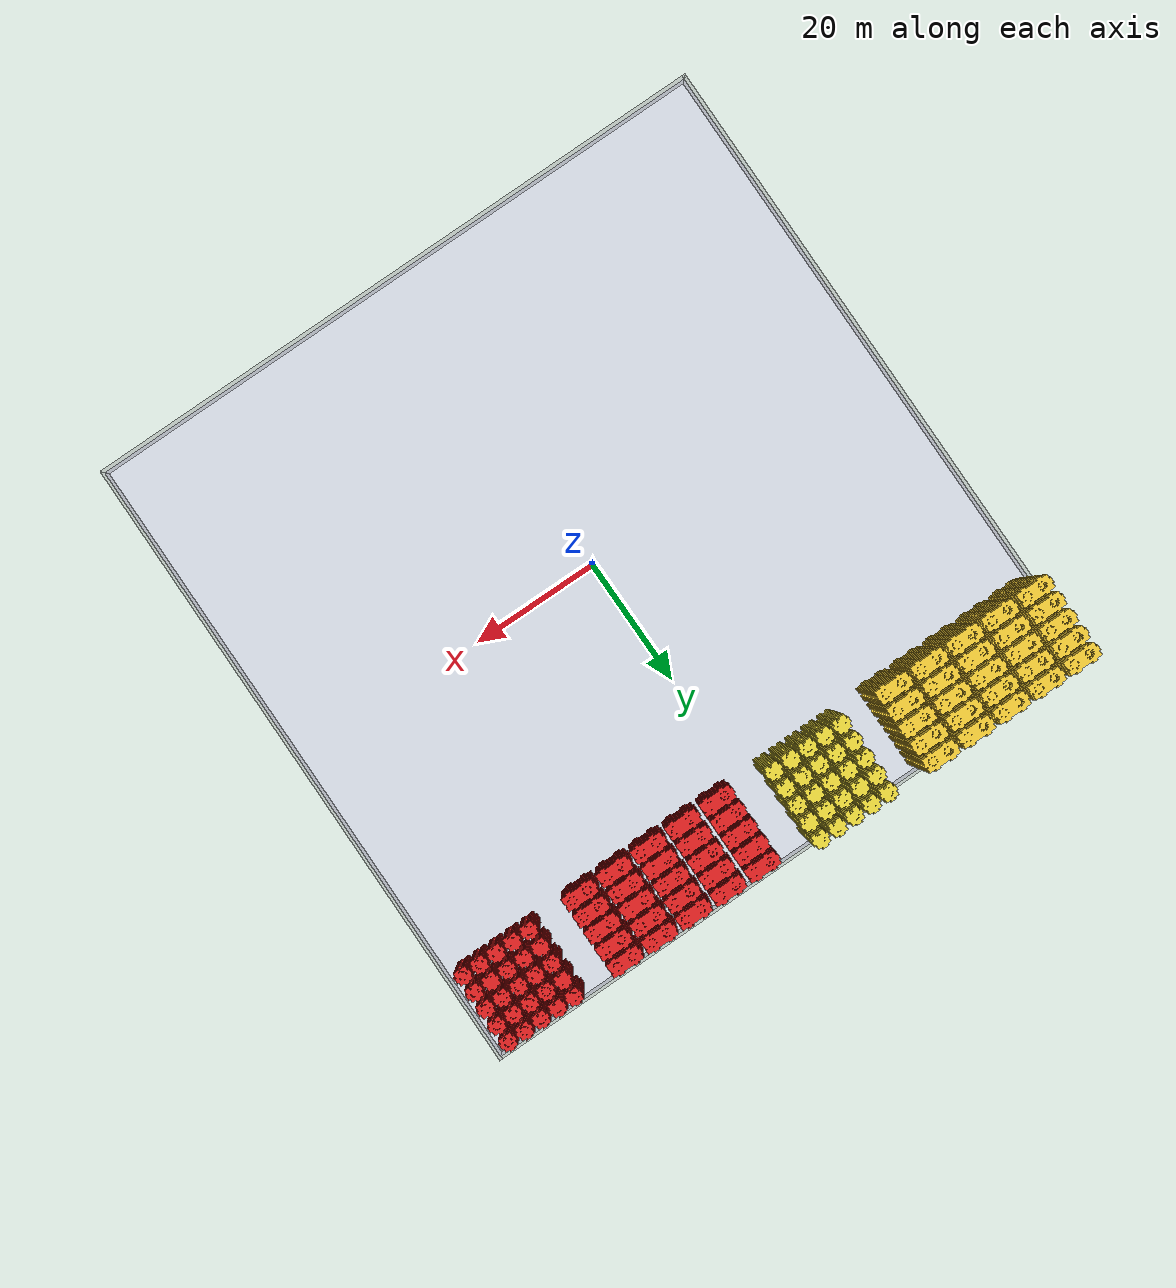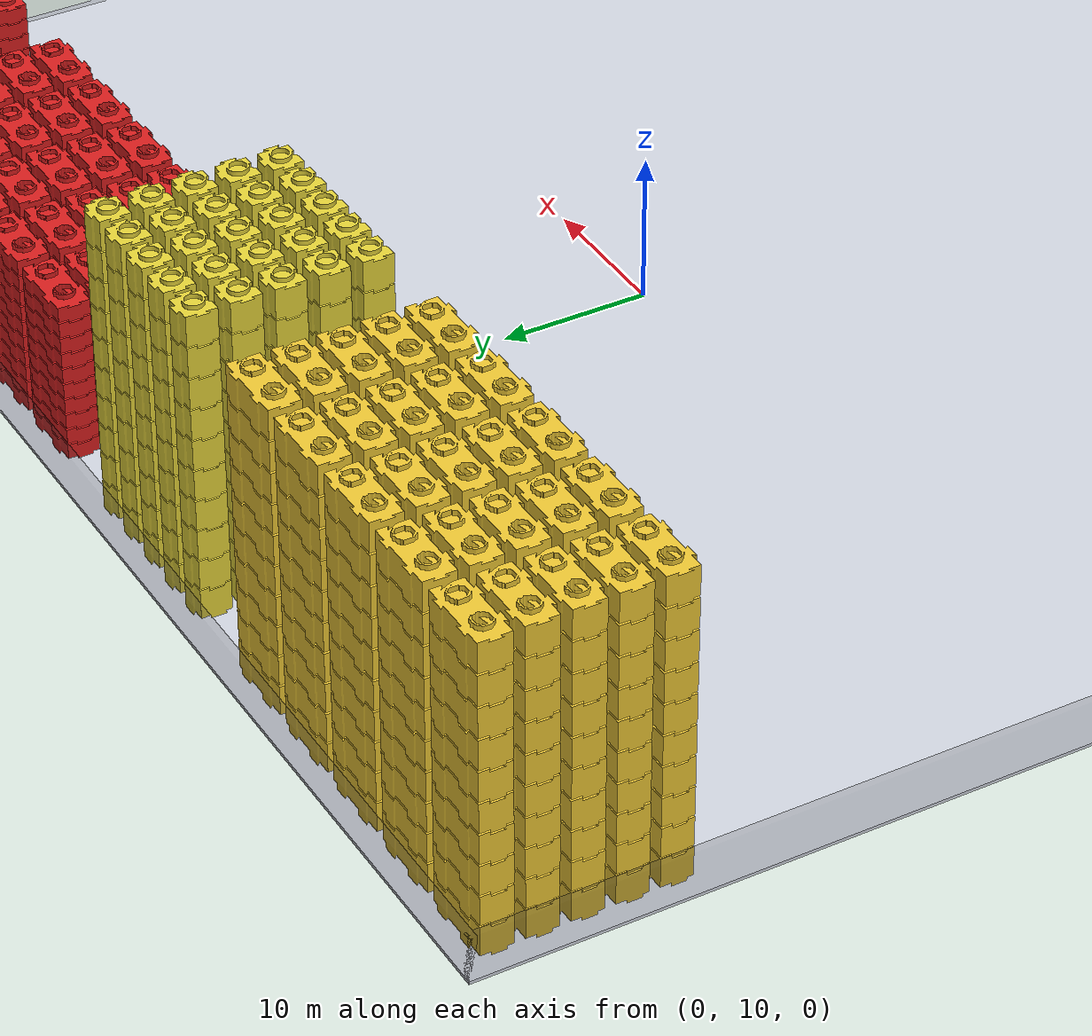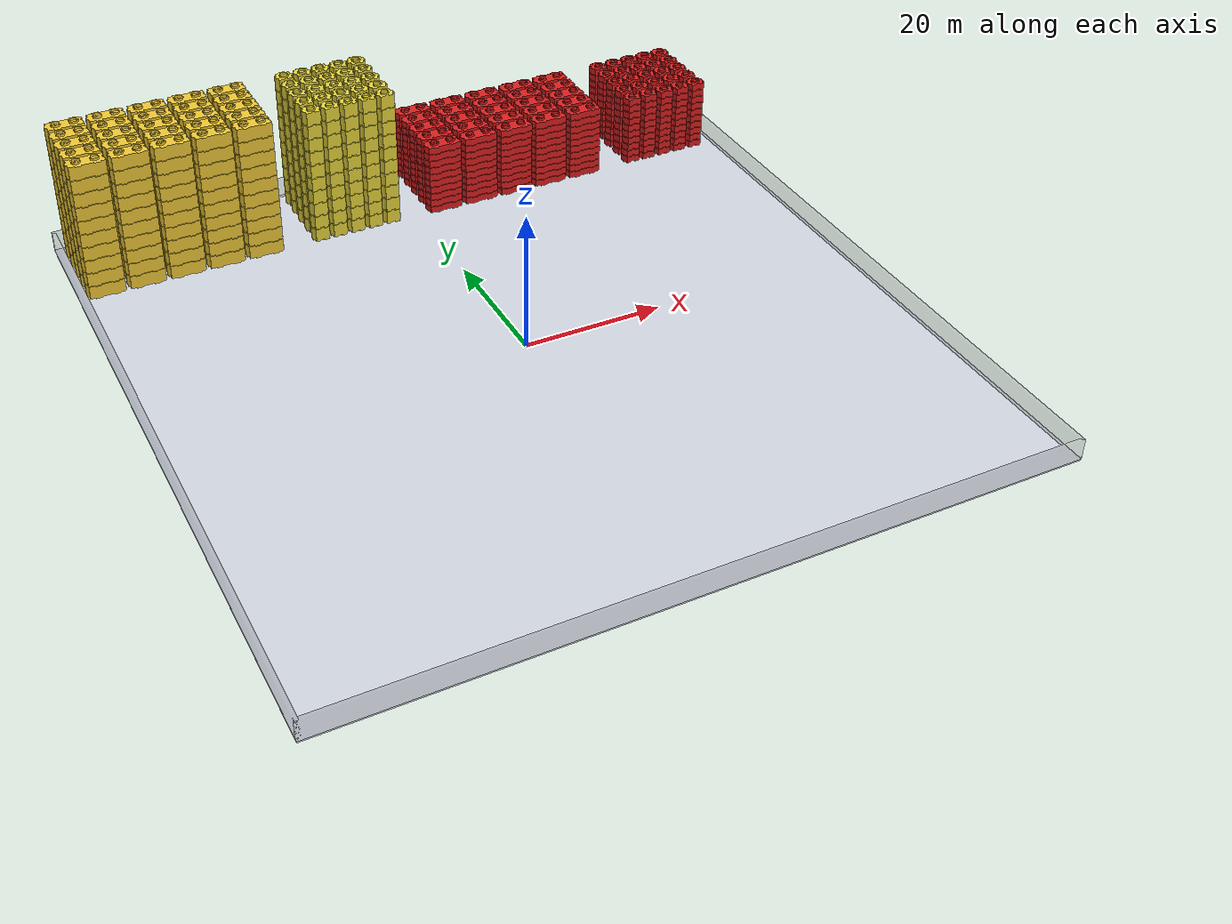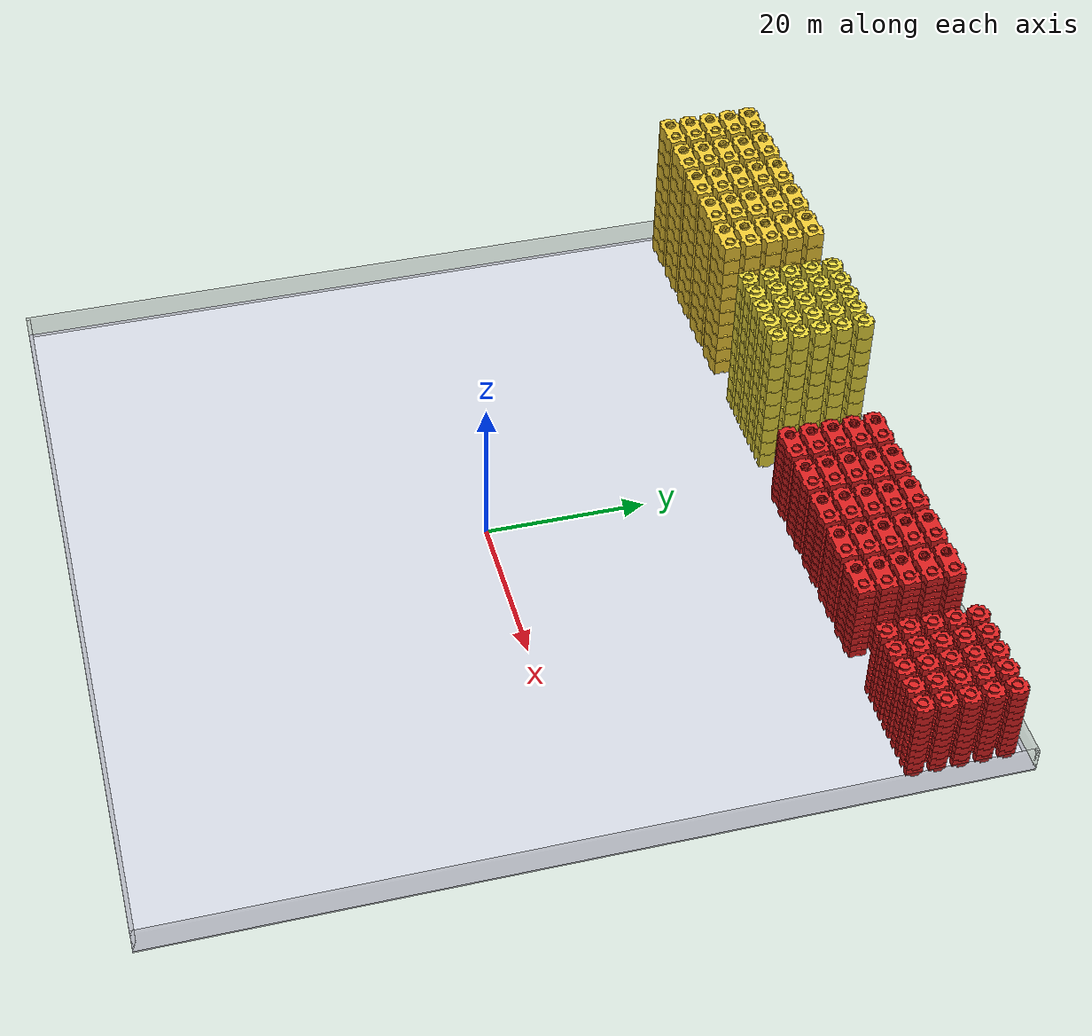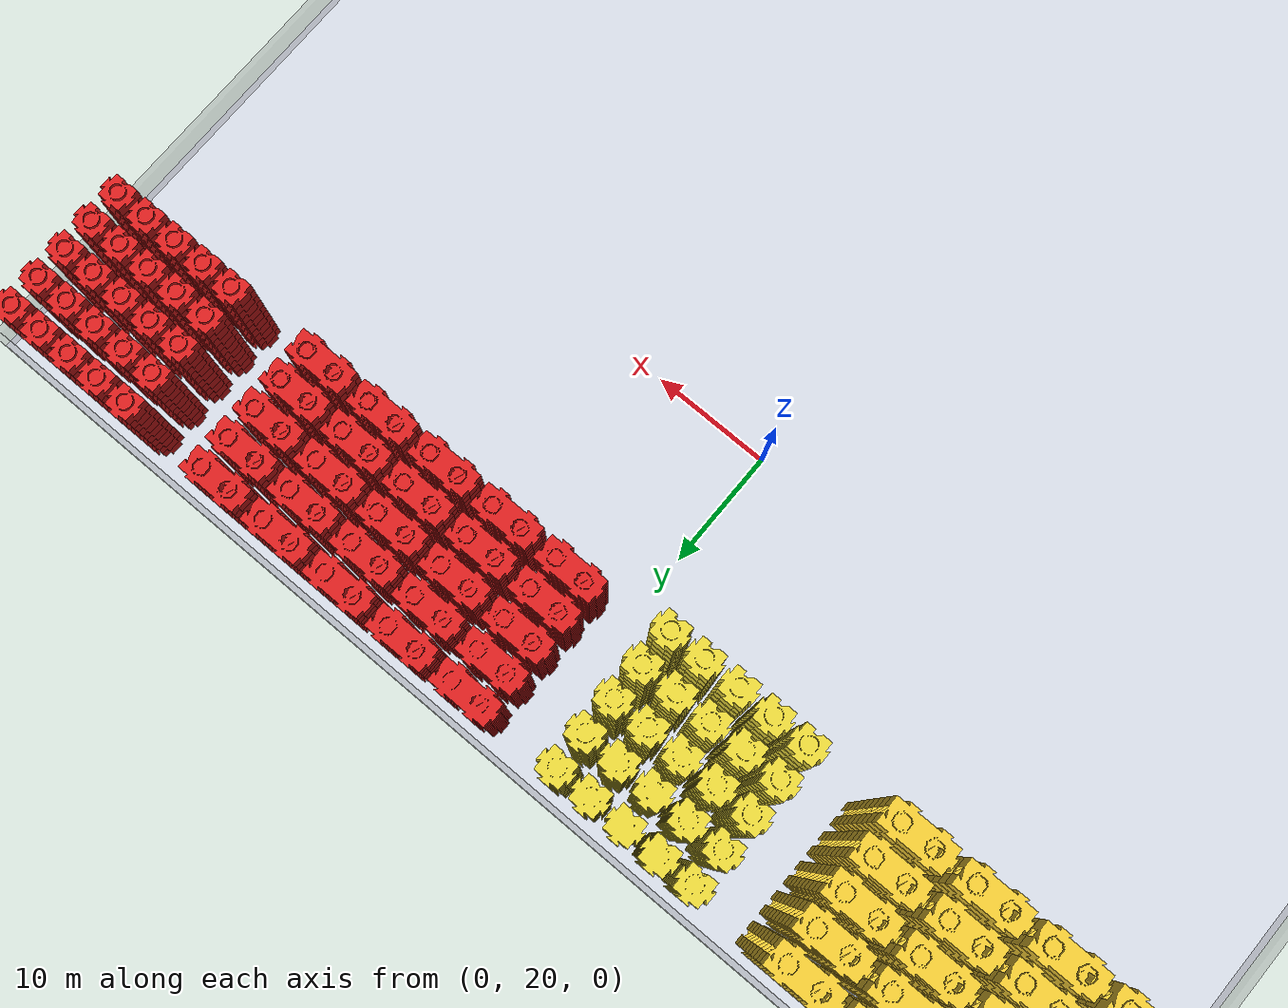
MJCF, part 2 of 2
<geom name="InventoryC2_217_tab_1" type="box" pos="1.125000 0.000000 0.000000" size="0.125000 1.000000 0.500000" rgba="0 0 0 0" mass="0"/>
      <geom name="InventoryC2_217_tab_2" type="box" pos="-1.125000 0.000000 0.000000" size="0.125000 1.000000 0.500000" rgba="0 0 0 0" mass="0"/>
      <geom name="InventoryC2_217_tab_3" type="box" pos="0.000000 0.000000 -1.125000" size="0.500000 1.000000 0.125000" rgba="0 0 0 0" mass="0"/>
    </body>
    <body name="InventoryC2_218" pos="-9.500000 39.750000 17.800000" euler="90 0 0">
      <geom name="InventoryC2_218_geom" type="mesh" mesh="c2_brick_mesh" rgba="0.900000 0.830000 0.220000 1.000000" mass="0" contype="0" conaffinity="0"/>
      <geom name="InventoryC2_218_body" type="box" pos="-0.000000 0.000000 0.000000" size="1.000000 1.000000 1.000000" rgba="0 0 0 0" mass="1"/>
      <geom name="InventoryC2_218_stud_1" type="cylinder" pos="0.000000 1.150000 0.000000" euler="-90 0 0" size="0.650000 0.150000" rgba="0 0 0 0" mass="0.05" contype="2" conaffinity="2"/>
      <geom name="InventoryC2_218_tube_1_1" type="box" pos="0.850000 -0.850000 0.000000" size="0.150000 0.150000 0.595000" rgba="0 0 0 0" mass="0" contype="2" conaffinity="2"/>
      <geom name="InventoryC2_218_tube_1_2" type="box" pos="-0.850000 -0.850000 0.000000" size="0.150000 0.150000 0.595000" rgba="0 0 0 0" mass="0" contype="2" conaffinity="2"/>
      <geom name="InventoryC2_218_tube_1_3" type="box" pos="0.000000 -0.850000 0.850000" size="0.595000 0.150000 0.150000" rgba="0 0 0 0" mass="0" contype="2" conaffinity="2"/>
      <geom name="InventoryC2_218_tube_1_4" type="box" pos="0.000000 -0.850000 -0.850000" size="0.595000 0.150000 0.150000" rgba="0 0 0 0" mass="0" contype="2" conaffinity="2"/>
      <geom name="InventoryC2_218_tab_1" type="box" pos="1.125000 0.000000 0.000000" size="0.125000 1.000000 0.500000" rgba="0 0 0 0" mass="0"/>
      <geom name="InventoryC2_218_tab_2" type="box" pos="-1.125000 0.000000 0.000000" size="0.125000 1.000000 0.500000" rgba="0 0 0 0" mass="0"/>
      <geom name="InventoryC2_218_tab_3" type="box" pos="0.000000 0.000000 -1.125000" size="0.500000 1.000000 0.125000" rgba="0 0 0 0" mass="0"/>
    </body>
    <body name="InventoryC2_219" pos="-6.750000 39.750000 17.800000" euler="90 0 0">
      <geom name="InventoryC2_219_geom" type="mesh" mesh="c2_brick_mesh" rgba="0.900000 0.830000 0.220000 1.000000" mass="0" contype="0" conaffinity="0"/>
      <geom name="InventoryC2_219_body" type="box" pos="-0.000000 0.000000 0.000000" size="1.000000 1.000000 1.000000" rgba="0 0 0 0" mass="1"/>
      <geom name="InventoryC2_219_stud_1" type="cylinder" pos="0.000000 1.150000 0.000000" euler="-90 0 0" size="0.650000 0.150000" rgba="0 0 0 0" mass="0.05" contype="2" conaffinity="2"/>
      <geom name="InventoryC2_219_tube_1_1" type="box" pos="0.850000 -0.850000 0.000000" size="0.150000 0.150000 0.595000" rgba="0 0 0 0" mass="0" contype="2" conaffinity="2"/>
      <geom name="InventoryC2_219_tube_1_2" type="box" pos="-0.850000 -0.850000 0.000000" size="0.150000 0.150000 0.595000" rgba="0 0 0 0" mass="0" contype="2" conaffinity="2"/>
      <geom name="InventoryC2_219_tube_1_3" type="box" pos="0.000000 -0.850000 0.850000" size="0.595000 0.150000 0.150000" rgba="0 0 0 0" mass="0" contype="2" conaffinity="2"/>
      <geom name="InventoryC2_219_tube_1_4" type="box" pos="0.000000 -0.850000 -0.850000" size="0.595000 0.150000 0.150000" rgba="0 0 0 0" mass="0" contype="2" conaffinity="2"/>
      <geom name="InventoryC2_219_tab_1" type="box" pos="1.125000 0.000000 0.000000" size="0.125000 1.000000 0.500000" rgba="0 0 0 0" mass="0"/>
      <geom name="InventoryC2_219_tab_2" type="box" pos="-1.125000 0.000000 0.000000" size="0.125000 1.000000 0.500000" rgba="0 0 0 0" mass="0"/>
      <geom name="InventoryC2_219_tab_3" type="box" pos="0.000000 0.000000 -1.125000" size="0.500000 1.000000 0.125000" rgba="0 0 0 0" mass="0"/>
    </body>
    <body name="InventoryC2_220" pos="-4.000000 39.750000 17.800000" euler="90 0 0">
      <geom name="InventoryC2_220_geom" type="mesh" mesh="c2_brick_mesh" rgba="0.900000 0.830000 0.220000 1.000000" mass="0" contype="0" conaffinity="0"/>
      <geom name="InventoryC2_220_body" type="box" pos="-0.000000 0.000000 0.000000" size="1.000000 1.000000 1.000000" rgba="0 0 0 0" mass="1"/>
      <geom name="InventoryC2_220_stud_1" type="cylinder" pos="0.000000 1.150000 0.000000" euler="-90 0 0" size="0.650000 0.150000" rgba="0 0 0 0" mass="0.05" contype="2" conaffinity="2"/>
      <geom name="InventoryC2_220_tube_1_1" type="box" pos="0.850000 -0.850000 0.000000" size="0.150000 0.150000 0.595000" rgba="0 0 0 0" mass="0" contype="2" conaffinity="2"/>
      <geom name="InventoryC2_220_tube_1_2" type="box" pos="-0.850000 -0.850000 0.000000" size="0.150000 0.150000 0.595000" rgba="0 0 0 0" mass="0" contype="2" conaffinity="2"/>
      <geom name="InventoryC2_220_tube_1_3" type="box" pos="0.000000 -0.850000 0.850000" size="0.595000 0.150000 0.150000" rgba="0 0 0 0" mass="0" contype="2" conaffinity="2"/>
      <geom name="InventoryC2_220_tube_1_4" type="box" pos="0.000000 -0.850000 -0.850000" size="0.595000 0.150000 0.150000" rgba="0 0 0 0" mass="0" contype="2" conaffinity="2"/>
      <geom name="InventoryC2_220_tab_1" type="box" pos="1.125000 0.000000 0.000000" size="0.125000 1.000000 0.500000" rgba="0 0 0 0" mass="0"/>
      <geom name="InventoryC2_220_tab_2" type="box" pos="-1.125000 0.000000 0.000000" size="0.125000 1.000000 0.500000" rgba="0 0 0 0" mass="0"/>
      <geom name="InventoryC2_220_tab_3" type="box" pos="0.000000 0.000000 -1.125000" size="0.500000 1.000000 0.125000" rgba="0 0 0 0" mass="0"/>
    </body>
    <body name="InventoryC2_221" pos="-15.000000 37.000000 17.800000" euler="90 0 0">
      <geom name="InventoryC2_221_geom" type="mesh" mesh="c2_brick_mesh" rgba="0.900000 0.830000 0.220000 1.000000" mass="0" contype="0" conaffinity="0"/>
      <geom name="InventoryC2_221_body" type="box" pos="-0.000000 0.000000 0.000000" size="1.000000 1.000000 1.000000" rgba="0 0 0 0" mass="1"/>
      <geom name="InventoryC2_221_stud_1" type="cylinder" pos="0.000000 1.150000 0.000000" euler="-90 0 0" size="0.650000 0.150000" rgba="0 0 0 0" mass="0.05" contype="2" conaffinity="2"/>
      <geom name="InventoryC2_221_tube_1_1" type="box" pos="0.850000 -0.850000 0.000000" size="0.150000 0.150000 0.595000" rgba="0 0 0 0" mass="0" contype="2" conaffinity="2"/>
      <geom name="InventoryC2_221_tube_1_2" type="box" pos="-0.850000 -0.850000 0.000000" size="0.150000 0.150000 0.595000" rgba="0 0 0 0" mass="0" contype="2" conaffinity="2"/>
      <geom name="InventoryC2_221_tube_1_3" type="box" pos="0.000000 -0.850000 0.850000" size="0.595000 0.150000 0.150000" rgba="0 0 0 0" mass="0" contype="2" conaffinity="2"/>
      <geom name="InventoryC2_221_tube_1_4" type="box" pos="0.000000 -0.850000 -0.850000" size="0.595000 0.150000 0.150000" rgba="0 0 0 0" mass="0" contype="2" conaffinity="2"/>
      <geom name="InventoryC2_221_tab_1" type="box" pos="1.125000 0.000000 0.000000" size="0.125000 1.000000 0.500000" rgba="0 0 0 0" mass="0"/>
      <geom name="InventoryC2_221_tab_2" type="box" pos="-1.125000 0.000000 0.000000" size="0.125000 1.000000 0.500000" rgba="0 0 0 0" mass="0"/>
      <geom name="InventoryC2_221_tab_3" type="box" pos="0.000000 0.000000 -1.125000" size="0.500000 1.000000 0.125000" rgba="0 0 0 0" mass="0"/>
    </body>
    <body name="InventoryC2_222" pos="-12.250000 37.000000 17.800000" euler="90 0 0">
      <geom name="InventoryC2_222_geom" type="mesh" mesh="c2_brick_mesh" rgba="0.900000 0.830000 0.220000 1.000000" mass="0" contype="0" conaffinity="0"/>
      <geom name="InventoryC2_222_body" type="box" pos="-0.000000 0.000000 0.000000" size="1.000000 1.000000 1.000000" rgba="0 0 0 0" mass="1"/>
      <geom name="InventoryC2_222_stud_1" type="cylinder" pos="0.000000 1.150000 0.000000" euler="-90 0 0" size="0.650000 0.150000" rgba="0 0 0 0" mass="0.05" contype="2" conaffinity="2"/>
      <geom name="InventoryC2_222_tube_1_1" type="box" pos="0.850000 -0.850000 0.000000" size="0.150000 0.150000 0.595000" rgba="0 0 0 0" mass="0" contype="2" conaffinity="2"/>
      <geom name="InventoryC2_222_tube_1_2" type="box" pos="-0.850000 -0.850000 0.000000" size="0.150000 0.150000 0.595000" rgba="0 0 0 0" mass="0" contype="2" conaffinity="2"/>
      <geom name="InventoryC2_222_tube_1_3" type="box" pos="0.000000 -0.850000 0.850000" size="0.595000 0.150000 0.150000" rgba="0 0 0 0" mass="0" contype="2" conaffinity="2"/>
      <geom name="InventoryC2_222_tube_1_4" type="box" pos="0.000000 -0.850000 -0.850000" size="0.595000 0.150000 0.150000" rgba="0 0 0 0" mass="0" contype="2" conaffinity="2"/>
      <geom name="InventoryC2_222_tab_1" type="box" pos="1.125000 0.000000 0.000000" size="0.125000 1.000000 0.500000" rgba="0 0 0 0" mass="0"/>
      <geom name="InventoryC2_222_tab_2" type="box" pos="-1.125000 0.000000 0.000000" size="0.125000 1.000000 0.500000" rgba="0 0 0 0" mass="0"/>
      <geom name="InventoryC2_222_tab_3" type="box" pos="0.000000 0.000000 -1.125000" size="0.500000 1.000000 0.125000" rgba="0 0 0 0" mass="0"/>
    </body>
    <body name="InventoryC2_223" pos="-9.500000 37.000000 17.800000" euler="90 0 0">
      <geom name="InventoryC2_223_geom" type="mesh" mesh="c2_brick_mesh" rgba="0.900000 0.830000 0.220000 1.000000" mass="0" contype="0" conaffinity="0"/>
      <geom name="InventoryC2_223_body" type="box" pos="-0.000000 0.000000 0.000000" size="1.000000 1.000000 1.000000" rgba="0 0 0 0" mass="1"/>
      <geom name="InventoryC2_223_stud_1" type="cylinder" pos="0.000000 1.150000 0.000000" euler="-90 0 0" size="0.650000 0.150000" rgba="0 0 0 0" mass="0.05" contype="2" conaffinity="2"/>
      <geom name="InventoryC2_223_tube_1_1" type="box" pos="0.850000 -0.850000 0.000000" size="0.150000 0.150000 0.595000" rgba="0 0 0 0" mass="0" contype="2" conaffinity="2"/>
      <geom name="InventoryC2_223_tube_1_2" type="box" pos="-0.850000 -0.850000 0.000000" size="0.150000 0.150000 0.595000" rgba="0 0 0 0" mass="0" contype="2" conaffinity="2"/>
      <geom name="InventoryC2_223_tube_1_3" type="box" pos="0.000000 -0.850000 0.850000" size="0.595000 0.150000 0.150000" rgba="0 0 0 0" mass="0" contype="2" conaffinity="2"/>
      <geom name="InventoryC2_223_tube_1_4" type="box" pos="0.000000 -0.850000 -0.850000" size="0.595000 0.150000 0.150000" rgba="0 0 0 0" mass="0" contype="2" conaffinity="2"/>
      <geom name="InventoryC2_223_tab_1" type="box" pos="1.125000 0.000000 0.000000" size="0.125000 1.000000 0.500000" rgba="0 0 0 0" mass="0"/>
      <geom name="InventoryC2_223_tab_2" type="box" pos="-1.125000 0.000000 0.000000" size="0.125000 1.000000 0.500000" rgba="0 0 0 0" mass="0"/>
      <geom name="InventoryC2_223_tab_3" type="box" pos="0.000000 0.000000 -1.125000" size="0.500000 1.000000 0.125000" rgba="0 0 0 0" mass="0"/>
    </body>
    <body name="InventoryC2_224" pos="-6.750000 37.000000 17.800000" euler="90 0 0">
      <geom name="InventoryC2_224_geom" type="mesh" mesh="c2_brick_mesh" rgba="0.900000 0.830000 0.220000 1.000000" mass="0" contype="0" conaffinity="0"/>
      <geom name="InventoryC2_224_body" type="box" pos="-0.000000 0.000000 0.000000" size="1.000000 1.000000 1.000000" rgba="0 0 0 0" mass="1"/>
      <geom name="InventoryC2_224_stud_1" type="cylinder" pos="0.000000 1.150000 0.000000" euler="-90 0 0" size="0.650000 0.150000" rgba="0 0 0 0" mass="0.05" contype="2" conaffinity="2"/>
      <geom name="InventoryC2_224_tube_1_1" type="box" pos="0.850000 -0.850000 0.000000" size="0.150000 0.150000 0.595000" rgba="0 0 0 0" mass="0" contype="2" conaffinity="2"/>
      <geom name="InventoryC2_224_tube_1_2" type="box" pos="-0.850000 -0.850000 0.000000" size="0.150000 0.150000 0.595000" rgba="0 0 0 0" mass="0" contype="2" conaffinity="2"/>
      <geom name="InventoryC2_224_tube_1_3" type="box" pos="0.000000 -0.850000 0.850000" size="0.595000 0.150000 0.150000" rgba="0 0 0 0" mass="0" contype="2" conaffinity="2"/>
      <geom name="InventoryC2_224_tube_1_4" type="box" pos="0.000000 -0.850000 -0.850000" size="0.595000 0.150000 0.150000" rgba="0 0 0 0" mass="0" contype="2" conaffinity="2"/>
      <geom name="InventoryC2_224_tab_1" type="box" pos="1.125000 0.000000 0.000000" size="0.125000 1.000000 0.500000" rgba="0 0 0 0" mass="0"/>
      <geom name="InventoryC2_224_tab_2" type="box" pos="-1.125000 0.000000 0.000000" size="0.125000 1.000000 0.500000" rgba="0 0 0 0" mass="0"/>
      <geom name="InventoryC2_224_tab_3" type="box" pos="0.000000 0.000000 -1.125000" size="0.500000 1.000000 0.125000" rgba="0 0 0 0" mass="0"/>
    </body>
    <body name="InventoryC2_225" pos="-4.000000 37.000000 17.800000" euler="90 0 0">
      <geom name="InventoryC2_225_geom" type="mesh" mesh="c2_brick_mesh" rgba="0.900000 0.830000 0.220000 1.000000" mass="0" contype="0" conaffinity="0"/>
      <geom name="InventoryC2_225_body" type="box" pos="-0.000000 0.000000 0.000000" size="1.000000 1.000000 1.000000" rgba="0 0 0 0" mass="1"/>
      <geom name="InventoryC2_225_stud_1" type="cylinder" pos="0.000000 1.150000 0.000000" euler="-90 0 0" size="0.650000 0.150000" rgba="0 0 0 0" mass="0.05" contype="2" conaffinity="2"/>
      <geom name="InventoryC2_225_tube_1_1" type="box" pos="0.850000 -0.850000 0.000000" size="0.150000 0.150000 0.595000" rgba="0 0 0 0" mass="0" contype="2" conaffinity="2"/>
      <geom name="InventoryC2_225_tube_1_2" type="box" pos="-0.850000 -0.850000 0.000000" size="0.150000 0.150000 0.595000" rgba="0 0 0 0" mass="0" contype="2" conaffinity="2"/>
      <geom name="InventoryC2_225_tube_1_3" type="box" pos="0.000000 -0.850000 0.850000" size="0.595000 0.150000 0.150000" rgba="0 0 0 0" mass="0" contype="2" conaffinity="2"/>
      <geom name="InventoryC2_225_tube_1_4" type="box" pos="0.000000 -0.850000 -0.850000" size="0.595000 0.150000 0.150000" rgba="0 0 0 0" mass="0" contype="2" conaffinity="2"/>
      <geom name="InventoryC2_225_tab_1" type="box" pos="1.125000 0.000000 0.000000" size="0.125000 1.000000 0.500000" rgba="0 0 0 0" mass="0"/>
      <geom name="InventoryC2_225_tab_2" type="box" pos="-1.125000 0.000000 0.000000" size="0.125000 1.000000 0.500000" rgba="0 0 0 0" mass="0"/>
      <geom name="InventoryC2_225_tab_3" type="box" pos="0.000000 0.000000 -1.125000" size="0.500000 1.000000 0.125000" rgba="0 0 0 0" mass="0"/>
    </body>
    <body name="InventoryC2_226" pos="-15.000000 48.000000 19.900000" euler="90 0 0">
      <geom name="InventoryC2_226_geom" type="mesh" mesh="c2_brick_mesh" rgba="0.900000 0.830000 0.220000 1.000000" mass="0" contype="0" conaffinity="0"/>
      <geom name="InventoryC2_226_body" type="box" pos="-0.000000 0.000000 0.000000" size="1.000000 1.000000 1.000000" rgba="0 0 0 0" mass="1"/>
      <geom name="InventoryC2_226_stud_1" type="cylinder" pos="0.000000 1.150000 0.000000" euler="-90 0 0" size="0.650000 0.150000" rgba="0 0 0 0" mass="0.05" contype="2" conaffinity="2"/>
      <geom name="InventoryC2_226_tube_1_1" type="box" pos="0.850000 -0.850000 0.000000" size="0.150000 0.150000 0.595000" rgba="0 0 0 0" mass="0" contype="2" conaffinity="2"/>
      <geom name="InventoryC2_226_tube_1_2" type="box" pos="-0.850000 -0.850000 0.000000" size="0.150000 0.150000 0.595000" rgba="0 0 0 0" mass="0" contype="2" conaffinity="2"/>
      <geom name="InventoryC2_226_tube_1_3" type="box" pos="0.000000 -0.850000 0.850000" size="0.595000 0.150000 0.150000" rgba="0 0 0 0" mass="0" contype="2" conaffinity="2"/>
      <geom name="InventoryC2_226_tube_1_4" type="box" pos="0.000000 -0.850000 -0.850000" size="0.595000 0.150000 0.150000" rgba="0 0 0 0" mass="0" contype="2" conaffinity="2"/>
      <geom name="InventoryC2_226_tab_1" type="box" pos="1.125000 0.000000 0.000000" size="0.125000 1.000000 0.500000" rgba="0 0 0 0" mass="0"/>
      <geom name="InventoryC2_226_tab_2" type="box" pos="-1.125000 0.000000 0.000000" size="0.125000 1.000000 0.500000" rgba="0 0 0 0" mass="0"/>
      <geom name="InventoryC2_226_tab_3" type="box" pos="0.000000 0.000000 -1.125000" size="0.500000 1.000000 0.125000" rgba="0 0 0 0" mass="0"/>
    </body>
    <body name="InventoryC2_227" pos="-12.250000 48.000000 19.900000" euler="90 0 0">
      <geom name="InventoryC2_227_geom" type="mesh" mesh="c2_brick_mesh" rgba="0.900000 0.830000 0.220000 1.000000" mass="0" contype="0" conaffinity="0"/>
      <geom name="InventoryC2_227_body" type="box" pos="-0.000000 0.000000 0.000000" size="1.000000 1.000000 1.000000" rgba="0 0 0 0" mass="1"/>
      <geom name="InventoryC2_227_stud_1" type="cylinder" pos="0.000000 1.150000 0.000000" euler="-90 0 0" size="0.650000 0.150000" rgba="0 0 0 0" mass="0.05" contype="2" conaffinity="2"/>
      <geom name="InventoryC2_227_tube_1_1" type="box" pos="0.850000 -0.850000 0.000000" size="0.150000 0.150000 0.595000" rgba="0 0 0 0" mass="0" contype="2" conaffinity="2"/>
      <geom name="InventoryC2_227_tube_1_2" type="box" pos="-0.850000 -0.850000 0.000000" size="0.150000 0.150000 0.595000" rgba="0 0 0 0" mass="0" contype="2" conaffinity="2"/>
      <geom name="InventoryC2_227_tube_1_3" type="box" pos="0.000000 -0.850000 0.850000" size="0.595000 0.150000 0.150000" rgba="0 0 0 0" mass="0" contype="2" conaffinity="2"/>
      <geom name="InventoryC2_227_tube_1_4" type="box" pos="0.000000 -0.850000 -0.850000" size="0.595000 0.150000 0.150000" rgba="0 0 0 0" mass="0" contype="2" conaffinity="2"/>
      <geom name="InventoryC2_227_tab_1" type="box" pos="1.125000 0.000000 0.000000" size="0.125000 1.000000 0.500000" rgba="0 0 0 0" mass="0"/>
      <geom name="InventoryC2_227_tab_2" type="box" pos="-1.125000 0.000000 0.000000" size="0.125000 1.000000 0.500000" rgba="0 0 0 0" mass="0"/>
      <geom name="InventoryC2_227_tab_3" type="box" pos="0.000000 0.000000 -1.125000" size="0.500000 1.000000 0.125000" rgba="0 0 0 0" mass="0"/>
    </body>
    <body name="InventoryC2_228" pos="-9.500000 48.000000 19.900000" euler="90 0 0">
      <geom name="InventoryC2_228_geom" type="mesh" mesh="c2_brick_mesh" rgba="0.900000 0.830000 0.220000 1.000000" mass="0" contype="0" conaffinity="0"/>
      <geom name="InventoryC2_228_body" type="box" pos="-0.000000 0.000000 0.000000" size="1.000000 1.000000 1.000000" rgba="0 0 0 0" mass="1"/>
      <geom name="InventoryC2_228_stud_1" type="cylinder" pos="0.000000 1.150000 0.000000" euler="-90 0 0" size="0.650000 0.150000" rgba="0 0 0 0" mass="0.05" contype="2" conaffinity="2"/>
      <geom name="InventoryC2_228_tube_1_1" type="box" pos="0.850000 -0.850000 0.000000" size="0.150000 0.150000 0.595000" rgba="0 0 0 0" mass="0" contype="2" conaffinity="2"/>
      <geom name="InventoryC2_228_tube_1_2" type="box" pos="-0.850000 -0.850000 0.000000" size="0.150000 0.150000 0.595000" rgba="0 0 0 0" mass="0" contype="2" conaffinity="2"/>
      <geom name="InventoryC2_228_tube_1_3" type="box" pos="0.000000 -0.850000 0.850000" size="0.595000 0.150000 0.150000" rgba="0 0 0 0" mass="0" contype="2" conaffinity="2"/>
      <geom name="InventoryC2_228_tube_1_4" type="box" pos="0.000000 -0.850000 -0.850000" size="0.595000 0.150000 0.150000" rgba="0 0 0 0" mass="0" contype="2" conaffinity="2"/>
      <geom name="InventoryC2_228_tab_1" type="box" pos="1.125000 0.000000 0.000000" size="0.125000 1.000000 0.500000" rgba="0 0 0 0" mass="0"/>
      <geom name="InventoryC2_228_tab_2" type="box" pos="-1.125000 0.000000 0.000000" size="0.125000 1.000000 0.500000" rgba="0 0 0 0" mass="0"/>
      <geom name="InventoryC2_228_tab_3" type="box" pos="0.000000 0.000000 -1.125000" size="0.500000 1.000000 0.125000" rgba="0 0 0 0" mass="0"/>
    </body>
    <body name="InventoryC2_229" pos="-6.750000 48.000000 19.900000" euler="90 0 0">
      <geom name="InventoryC2_229_geom" type="mesh" mesh="c2_brick_mesh" rgba="0.900000 0.830000 0.220000 1.000000" mass="0" contype="0" conaffinity="0"/>
      <geom name="InventoryC2_229_body" type="box" pos="-0.000000 0.000000 0.000000" size="1.000000 1.000000 1.000000" rgba="0 0 0 0" mass="1"/>
      <geom name="InventoryC2_229_stud_1" type="cylinder" pos="0.000000 1.150000 0.000000" euler="-90 0 0" size="0.650000 0.150000" rgba="0 0 0 0" mass="0.05" contype="2" conaffinity="2"/>
      <geom name="InventoryC2_229_tube_1_1" type="box" pos="0.850000 -0.850000 0.000000" size="0.150000 0.150000 0.595000" rgba="0 0 0 0" mass="0" contype="2" conaffinity="2"/>
      <geom name="InventoryC2_229_tube_1_2" type="box" pos="-0.850000 -0.850000 0.000000" size="0.150000 0.150000 0.595000" rgba="0 0 0 0" mass="0" contype="2" conaffinity="2"/>
      <geom name="InventoryC2_229_tube_1_3" type="box" pos="0.000000 -0.850000 0.850000" size="0.595000 0.150000 0.150000" rgba="0 0 0 0" mass="0" contype="2" conaffinity="2"/>
      <geom name="InventoryC2_229_tube_1_4" type="box" pos="0.000000 -0.850000 -0.850000" size="0.595000 0.150000 0.150000" rgba="0 0 0 0" mass="0" contype="2" conaffinity="2"/>
      <geom name="InventoryC2_229_tab_1" type="box" pos="1.125000 0.000000 0.000000" size="0.125000 1.000000 0.500000" rgba="0 0 0 0" mass="0"/>
      <geom name="InventoryC2_229_tab_2" type="box" pos="-1.125000 0.000000 0.000000" size="0.125000 1.000000 0.500000" rgba="0 0 0 0" mass="0"/>
      <geom name="InventoryC2_229_tab_3" type="box" pos="0.000000 0.000000 -1.125000" size="0.500000 1.000000 0.125000" rgba="0 0 0 0" mass="0"/>
    </body>
    <body name="InventoryC2_230" pos="-4.000000 48.000000 19.900000" euler="90 0 0">
      <geom name="InventoryC2_230_geom" type="mesh" mesh="c2_brick_mesh" rgba="0.900000 0.830000 0.220000 1.000000" mass="0" contype="0" conaffinity="0"/>
      <geom name="InventoryC2_230_body" type="box" pos="-0.000000 0.000000 0.000000" size="1.000000 1.000000 1.000000" rgba="0 0 0 0" mass="1"/>
      <geom name="InventoryC2_230_stud_1" type="cylinder" pos="0.000000 1.150000 0.000000" euler="-90 0 0" size="0.650000 0.150000" rgba="0 0 0 0" mass="0.05" contype="2" conaffinity="2"/>
      <geom name="InventoryC2_230_tube_1_1" type="box" pos="0.850000 -0.850000 0.000000" size="0.150000 0.150000 0.595000" rgba="0 0 0 0" mass="0" contype="2" conaffinity="2"/>
      <geom name="InventoryC2_230_tube_1_2" type="box" pos="-0.850000 -0.850000 0.000000" size="0.150000 0.150000 0.595000" rgba="0 0 0 0" mass="0" contype="2" conaffinity="2"/>
      <geom name="InventoryC2_230_tube_1_3" type="box" pos="0.000000 -0.850000 0.850000" size="0.595000 0.150000 0.150000" rgba="0 0 0 0" mass="0" contype="2" conaffinity="2"/>
      <geom name="InventoryC2_230_tube_1_4" type="box" pos="0.000000 -0.850000 -0.850000" size="0.595000 0.150000 0.150000" rgba="0 0 0 0" mass="0" contype="2" conaffinity="2"/>
      <geom name="InventoryC2_230_tab_1" type="box" pos="1.125000 0.000000 0.000000" size="0.125000 1.000000 0.500000" rgba="0 0 0 0" mass="0"/>
      <geom name="InventoryC2_230_tab_2" type="box" pos="-1.125000 0.000000 0.000000" size="0.125000 1.000000 0.500000" rgba="0 0 0 0" mass="0"/>
      <geom name="InventoryC2_230_tab_3" type="box" pos="0.000000 0.000000 -1.125000" size="0.500000 1.000000 0.125000" rgba="0 0 0 0" mass="0"/>
    </body>
    <body name="InventoryC2_231" pos="-15.000000 45.250000 19.900000" euler="90 0 0">
      <geom name="InventoryC2_231_geom" type="mesh" mesh="c2_brick_mesh" rgba="0.900000 0.830000 0.220000 1.000000" mass="0" contype="0" conaffinity="0"/>
      <geom name="InventoryC2_231_body" type="box" pos="-0.000000 0.000000 0.000000" size="1.000000 1.000000 1.000000" rgba="0 0 0 0" mass="1"/>
      <geom name="InventoryC2_231_stud_1" type="cylinder" pos="0.000000 1.150000 0.000000" euler="-90 0 0" size="0.650000 0.150000" rgba="0 0 0 0" mass="0.05" contype="2" conaffinity="2"/>
      <geom name="InventoryC2_231_tube_1_1" type="box" pos="0.850000 -0.850000 0.000000" size="0.150000 0.150000 0.595000" rgba="0 0 0 0" mass="0" contype="2" conaffinity="2"/>
      <geom name="InventoryC2_231_tube_1_2" type="box" pos="-0.850000 -0.850000 0.000000" size="0.150000 0.150000 0.595000" rgba="0 0 0 0" mass="0" contype="2" conaffinity="2"/>
      <geom name="InventoryC2_231_tube_1_3" type="box" pos="0.000000 -0.850000 0.850000" size="0.595000 0.150000 0.150000" rgba="0 0 0 0" mass="0" contype="2" conaffinity="2"/>
      <geom name="InventoryC2_231_tube_1_4" type="box" pos="0.000000 -0.850000 -0.850000" size="0.595000 0.150000 0.150000" rgba="0 0 0 0" mass="0" contype="2" conaffinity="2"/>
      <geom name="InventoryC2_231_tab_1" type="box" pos="1.125000 0.000000 0.000000" size="0.125000 1.000000 0.500000" rgba="0 0 0 0" mass="0"/>
      <geom name="InventoryC2_231_tab_2" type="box" pos="-1.125000 0.000000 0.000000" size="0.125000 1.000000 0.500000" rgba="0 0 0 0" mass="0"/>
      <geom name="InventoryC2_231_tab_3" type="box" pos="0.000000 0.000000 -1.125000" size="0.500000 1.000000 0.125000" rgba="0 0 0 0" mass="0"/>
    </body>
    <body name="InventoryC2_232" pos="-12.250000 45.250000 19.900000" euler="90 0 0">
      <geom name="InventoryC2_232_geom" type="mesh" mesh="c2_brick_mesh" rgba="0.900000 0.830000 0.220000 1.000000" mass="0" contype="0" conaffinity="0"/>
      <geom name="InventoryC2_232_body" type="box" pos="-0.000000 0.000000 0.000000" size="1.000000 1.000000 1.000000" rgba="0 0 0 0" mass="1"/>
      <geom name="InventoryC2_232_stud_1" type="cylinder" pos="0.000000 1.150000 0.000000" euler="-90 0 0" size="0.650000 0.150000" rgba="0 0 0 0" mass="0.05" contype="2" conaffinity="2"/>
      <geom name="InventoryC2_232_tube_1_1" type="box" pos="0.850000 -0.850000 0.000000" size="0.150000 0.150000 0.595000" rgba="0 0 0 0" mass="0" contype="2" conaffinity="2"/>
      <geom name="InventoryC2_232_tube_1_2" type="box" pos="-0.850000 -0.850000 0.000000" size="0.150000 0.150000 0.595000" rgba="0 0 0 0" mass="0" contype="2" conaffinity="2"/>
      <geom name="InventoryC2_232_tube_1_3" type="box" pos="0.000000 -0.850000 0.850000" size="0.595000 0.150000 0.150000" rgba="0 0 0 0" mass="0" contype="2" conaffinity="2"/>
      <geom name="InventoryC2_232_tube_1_4" type="box" pos="0.000000 -0.850000 -0.850000" size="0.595000 0.150000 0.150000" rgba="0 0 0 0" mass="0" contype="2" conaffinity="2"/>
      <geom name="InventoryC2_232_tab_1" type="box" pos="1.125000 0.000000 0.000000" size="0.125000 1.000000 0.500000" rgba="0 0 0 0" mass="0"/>
      <geom name="InventoryC2_232_tab_2" type="box" pos="-1.125000 0.000000 0.000000" size="0.125000 1.000000 0.500000" rgba="0 0 0 0" mass="0"/>
      <geom name="InventoryC2_232_tab_3" type="box" pos="0.000000 0.000000 -1.125000" size="0.500000 1.000000 0.125000" rgba="0 0 0 0" mass="0"/>
    </body>
    <body name="InventoryC2_233" pos="-9.500000 45.250000 19.900000" euler="90 0 0">
      <geom name="InventoryC2_233_geom" type="mesh" mesh="c2_brick_mesh" rgba="0.900000 0.830000 0.220000 1.000000" mass="0" contype="0" conaffinity="0"/>
      <geom name="InventoryC2_233_body" type="box" pos="-0.000000 0.000000 0.000000" size="1.000000 1.000000 1.000000" rgba="0 0 0 0" mass="1"/>
      <geom name="InventoryC2_233_stud_1" type="cylinder" pos="0.000000 1.150000 0.000000" euler="-90 0 0" size="0.650000 0.150000" rgba="0 0 0 0" mass="0.05" contype="2" conaffinity="2"/>
      <geom name="InventoryC2_233_tube_1_1" type="box" pos="0.850000 -0.850000 0.000000" size="0.150000 0.150000 0.595000" rgba="0 0 0 0" mass="0" contype="2" conaffinity="2"/>
      <geom name="InventoryC2_233_tube_1_2" type="box" pos="-0.850000 -0.850000 0.000000" size="0.150000 0.150000 0.595000" rgba="0 0 0 0" mass="0" contype="2" conaffinity="2"/>
      <geom name="InventoryC2_233_tube_1_3" type="box" pos="0.000000 -0.850000 0.850000" size="0.595000 0.150000 0.150000" rgba="0 0 0 0" mass="0" contype="2" conaffinity="2"/>
      <geom name="InventoryC2_233_tube_1_4" type="box" pos="0.000000 -0.850000 -0.850000" size="0.595000 0.150000 0.150000" rgba="0 0 0 0" mass="0" contype="2" conaffinity="2"/>
      <geom name="InventoryC2_233_tab_1" type="box" pos="1.125000 0.000000 0.000000" size="0.125000 1.000000 0.500000" rgba="0 0 0 0" mass="0"/>
      <geom name="InventoryC2_233_tab_2" type="box" pos="-1.125000 0.000000 0.000000" size="0.125000 1.000000 0.500000" rgba="0 0 0 0" mass="0"/>
      <geom name="InventoryC2_233_tab_3" type="box" pos="0.000000 0.000000 -1.125000" size="0.500000 1.000000 0.125000" rgba="0 0 0 0" mass="0"/>
    </body>
    <body name="InventoryC2_234" pos="-6.750000 45.250000 19.900000" euler="90 0 0">
      <geom name="InventoryC2_234_geom" type="mesh" mesh="c2_brick_mesh" rgba="0.900000 0.830000 0.220000 1.000000" mass="0" contype="0" conaffinity="0"/>
      <geom name="InventoryC2_234_body" type="box" pos="-0.000000 0.000000 0.000000" size="1.000000 1.000000 1.000000" rgba="0 0 0 0" mass="1"/>
      <geom name="InventoryC2_234_stud_1" type="cylinder" pos="0.000000 1.150000 0.000000" euler="-90 0 0" size="0.650000 0.150000" rgba="0 0 0 0" mass="0.05" contype="2" conaffinity="2"/>
      <geom name="InventoryC2_234_tube_1_1" type="box" pos="0.850000 -0.850000 0.000000" size="0.150000 0.150000 0.595000" rgba="0 0 0 0" mass="0" contype="2" conaffinity="2"/>
      <geom name="InventoryC2_234_tube_1_2" type="box" pos="-0.850000 -0.850000 0.000000" size="0.150000 0.150000 0.595000" rgba="0 0 0 0" mass="0" contype="2" conaffinity="2"/>
      <geom name="InventoryC2_234_tube_1_3" type="box" pos="0.000000 -0.850000 0.850000" size="0.595000 0.150000 0.150000" rgba="0 0 0 0" mass="0" contype="2" conaffinity="2"/>
      <geom name="InventoryC2_234_tube_1_4" type="box" pos="0.000000 -0.850000 -0.850000" size="0.595000 0.150000 0.150000" rgba="0 0 0 0" mass="0" contype="2" conaffinity="2"/>
      <geom name="InventoryC2_234_tab_1" type="box" pos="1.125000 0.000000 0.000000" size="0.125000 1.000000 0.500000" rgba="0 0 0 0" mass="0"/>
      <geom name="InventoryC2_234_tab_2" type="box" pos="-1.125000 0.000000 0.000000" size="0.125000 1.000000 0.500000" rgba="0 0 0 0" mass="0"/>
      <geom name="InventoryC2_234_tab_3" type="box" pos="0.000000 0.000000 -1.125000" size="0.500000 1.000000 0.125000" rgba="0 0 0 0" mass="0"/>
    </body>
    <body name="InventoryC2_235" pos="-4.000000 45.250000 19.900000" euler="90 0 0">
      <geom name="InventoryC2_235_geom" type="mesh" mesh="c2_brick_mesh" rgba="0.900000 0.830000 0.220000 1.000000" mass="0" contype="0" conaffinity="0"/>
      <geom name="InventoryC2_235_body" type="box" pos="-0.000000 0.000000 0.000000" size="1.000000 1.000000 1.000000" rgba="0 0 0 0" mass="1"/>
      <geom name="InventoryC2_235_stud_1" type="cylinder" pos="0.000000 1.150000 0.000000" euler="-90 0 0" size="0.650000 0.150000" rgba="0 0 0 0" mass="0.05" contype="2" conaffinity="2"/>
      <geom name="InventoryC2_235_tube_1_1" type="box" pos="0.850000 -0.850000 0.000000" size="0.150000 0.150000 0.595000" rgba="0 0 0 0" mass="0" contype="2" conaffinity="2"/>
      <geom name="InventoryC2_235_tube_1_2" type="box" pos="-0.850000 -0.850000 0.000000" size="0.150000 0.150000 0.595000" rgba="0 0 0 0" mass="0" contype="2" conaffinity="2"/>
      <geom name="InventoryC2_235_tube_1_3" type="box" pos="0.000000 -0.850000 0.850000" size="0.595000 0.150000 0.150000" rgba="0 0 0 0" mass="0" contype="2" conaffinity="2"/>
      <geom name="InventoryC2_235_tube_1_4" type="box" pos="0.000000 -0.850000 -0.850000" size="0.595000 0.150000 0.150000" rgba="0 0 0 0" mass="0" contype="2" conaffinity="2"/>
      <geom name="InventoryC2_235_tab_1" type="box" pos="1.125000 0.000000 0.000000" size="0.125000 1.000000 0.500000" rgba="0 0 0 0" mass="0"/>
      <geom name="InventoryC2_235_tab_2" type="box" pos="-1.125000 0.000000 0.000000" size="0.125000 1.000000 0.500000" rgba="0 0 0 0" mass="0"/>
      <geom name="InventoryC2_235_tab_3" type="box" pos="0.000000 0.000000 -1.125000" size="0.500000 1.000000 0.125000" rgba="0 0 0 0" mass="0"/>
    </body>
    <body name="InventoryC2_236" pos="-15.000000 42.500000 19.900000" euler="90 0 0">
      <geom name="InventoryC2_236_geom" type="mesh" mesh="c2_brick_mesh" rgba="0.900000 0.830000 0.220000 1.000000" mass="0" contype="0" conaffinity="0"/>
      <geom name="InventoryC2_236_body" type="box" pos="-0.000000 0.000000 0.000000" size="1.000000 1.000000 1.000000" rgba="0 0 0 0" mass="1"/>
      <geom name="InventoryC2_236_stud_1" type="cylinder" pos="0.000000 1.150000 0.000000" euler="-90 0 0" size="0.650000 0.150000" rgba="0 0 0 0" mass="0.05" contype="2" conaffinity="2"/>
      <geom name="InventoryC2_236_tube_1_1" type="box" pos="0.850000 -0.850000 0.000000" size="0.150000 0.150000 0.595000" rgba="0 0 0 0" mass="0" contype="2" conaffinity="2"/>
      <geom name="InventoryC2_236_tube_1_2" type="box" pos="-0.850000 -0.850000 0.000000" size="0.150000 0.150000 0.595000" rgba="0 0 0 0" mass="0" contype="2" conaffinity="2"/>
      <geom name="InventoryC2_236_tube_1_3" type="box" pos="0.000000 -0.850000 0.850000" size="0.595000 0.150000 0.150000" rgba="0 0 0 0" mass="0" contype="2" conaffinity="2"/>
      <geom name="InventoryC2_236_tube_1_4" type="box" pos="0.000000 -0.850000 -0.850000" size="0.595000 0.150000 0.150000" rgba="0 0 0 0" mass="0" contype="2" conaffinity="2"/>
      <geom name="InventoryC2_236_tab_1" type="box" pos="1.125000 0.000000 0.000000" size="0.125000 1.000000 0.500000" rgba="0 0 0 0" mass="0"/>
      <geom name="InventoryC2_236_tab_2" type="box" pos="-1.125000 0.000000 0.000000" size="0.125000 1.000000 0.500000" rgba="0 0 0 0" mass="0"/>
      <geom name="InventoryC2_236_tab_3" type="box" pos="0.000000 0.000000 -1.125000" size="0.500000 1.000000 0.125000" rgba="0 0 0 0" mass="0"/>
    </body>
    <body name="InventoryC2_237" pos="-12.250000 42.500000 19.900000" euler="90 0 0">
      <geom name="InventoryC2_237_geom" type="mesh" mesh="c2_brick_mesh" rgba="0.900000 0.830000 0.220000 1.000000" mass="0" contype="0" conaffinity="0"/>
      <geom name="InventoryC2_237_body" type="box" pos="-0.000000 0.000000 0.000000" size="1.000000 1.000000 1.000000" rgba="0 0 0 0" mass="1"/>
      <geom name="InventoryC2_237_stud_1" type="cylinder" pos="0.000000 1.150000 0.000000" euler="-90 0 0" size="0.650000 0.150000" rgba="0 0 0 0" mass="0.05" contype="2" conaffinity="2"/>
      <geom name="InventoryC2_237_tube_1_1" type="box" pos="0.850000 -0.850000 0.000000" size="0.150000 0.150000 0.595000" rgba="0 0 0 0" mass="0" contype="2" conaffinity="2"/>
      <geom name="InventoryC2_237_tube_1_2" type="box" pos="-0.850000 -0.850000 0.000000" size="0.150000 0.150000 0.595000" rgba="0 0 0 0" mass="0" contype="2" conaffinity="2"/>
      <geom name="InventoryC2_237_tube_1_3" type="box" pos="0.000000 -0.850000 0.850000" size="0.595000 0.150000 0.150000" rgba="0 0 0 0" mass="0" contype="2" conaffinity="2"/>
      <geom name="InventoryC2_237_tube_1_4" type="box" pos="0.000000 -0.850000 -0.850000" size="0.595000 0.150000 0.150000" rgba="0 0 0 0" mass="0" contype="2" conaffinity="2"/>
      <geom name="InventoryC2_237_tab_1" type="box" pos="1.125000 0.000000 0.000000" size="0.125000 1.000000 0.500000" rgba="0 0 0 0" mass="0"/>
      <geom name="InventoryC2_237_tab_2" type="box" pos="-1.125000 0.000000 0.000000" size="0.125000 1.000000 0.500000" rgba="0 0 0 0" mass="0"/>
      <geom name="InventoryC2_237_tab_3" type="box" pos="0.000000 0.000000 -1.125000" size="0.500000 1.000000 0.125000" rgba="0 0 0 0" mass="0"/>
    </body>
    <body name="InventoryC2_238" pos="-9.500000 42.500000 19.900000" euler="90 0 0">
      <geom name="InventoryC2_238_geom" type="mesh" mesh="c2_brick_mesh" rgba="0.900000 0.830000 0.220000 1.000000" mass="0" contype="0" conaffinity="0"/>
      <geom name="InventoryC2_238_body" type="box" pos="-0.000000 0.000000 0.000000" size="1.000000 1.000000 1.000000" rgba="0 0 0 0" mass="1"/>
      <geom name="InventoryC2_238_stud_1" type="cylinder" pos="0.000000 1.150000 0.000000" euler="-90 0 0" size="0.650000 0.150000" rgba="0 0 0 0" mass="0.05" contype="2" conaffinity="2"/>
      <geom name="InventoryC2_238_tube_1_1" type="box" pos="0.850000 -0.850000 0.000000" size="0.150000 0.150000 0.595000" rgba="0 0 0 0" mass="0" contype="2" conaffinity="2"/>
      <geom name="InventoryC2_238_tube_1_2" type="box" pos="-0.850000 -0.850000 0.000000" size="0.150000 0.150000 0.595000" rgba="0 0 0 0" mass="0" contype="2" conaffinity="2"/>
      <geom name="InventoryC2_238_tube_1_3" type="box" pos="0.000000 -0.850000 0.850000" size="0.595000 0.150000 0.150000" rgba="0 0 0 0" mass="0" contype="2" conaffinity="2"/>
      <geom name="InventoryC2_238_tube_1_4" type="box" pos="0.000000 -0.850000 -0.850000" size="0.595000 0.150000 0.150000" rgba="0 0 0 0" mass="0" contype="2" conaffinity="2"/>
      <geom name="InventoryC2_238_tab_1" type="box" pos="1.125000 0.000000 0.000000" size="0.125000 1.000000 0.500000" rgba="0 0 0 0" mass="0"/>
      <geom name="InventoryC2_238_tab_2" type="box" pos="-1.125000 0.000000 0.000000" size="0.125000 1.000000 0.500000" rgba="0 0 0 0" mass="0"/>
      <geom name="InventoryC2_238_tab_3" type="box" pos="0.000000 0.000000 -1.125000" size="0.500000 1.000000 0.125000" rgba="0 0 0 0" mass="0"/>
    </body>
    <body name="InventoryC2_239" pos="-6.750000 42.500000 19.900000" euler="90 0 0">
      <geom name="InventoryC2_239_geom" type="mesh" mesh="c2_brick_mesh" rgba="0.900000 0.830000 0.220000 1.000000" mass="0" contype="0" conaffinity="0"/>
      <geom name="InventoryC2_239_body" type="box" pos="-0.000000 0.000000 0.000000" size="1.000000 1.000000 1.000000" rgba="0 0 0 0" mass="1"/>
      <geom name="InventoryC2_239_stud_1" type="cylinder" pos="0.000000 1.150000 0.000000" euler="-90 0 0" size="0.650000 0.150000" rgba="0 0 0 0" mass="0.05" contype="2" conaffinity="2"/>
      <geom name="InventoryC2_239_tube_1_1" type="box" pos="0.850000 -0.850000 0.000000" size="0.150000 0.150000 0.595000" rgba="0 0 0 0" mass="0" contype="2" conaffinity="2"/>
      <geom name="InventoryC2_239_tube_1_2" type="box" pos="-0.850000 -0.850000 0.000000" size="0.150000 0.150000 0.595000" rgba="0 0 0 0" mass="0" contype="2" conaffinity="2"/>
      <geom name="InventoryC2_239_tube_1_3" type="box" pos="0.000000 -0.850000 0.850000" size="0.595000 0.150000 0.150000" rgba="0 0 0 0" mass="0" contype="2" conaffinity="2"/>
      <geom name="InventoryC2_239_tube_1_4" type="box" pos="0.000000 -0.850000 -0.850000" size="0.595000 0.150000 0.150000" rgba="0 0 0 0" mass="0" contype="2" conaffinity="2"/>
      <geom name="InventoryC2_239_tab_1" type="box" pos="1.125000 0.000000 0.000000" size="0.125000 1.000000 0.500000" rgba="0 0 0 0" mass="0"/>
      <geom name="InventoryC2_239_tab_2" type="box" pos="-1.125000 0.000000 0.000000" size="0.125000 1.000000 0.500000" rgba="0 0 0 0" mass="0"/>
      <geom name="InventoryC2_239_tab_3" type="box" pos="0.000000 0.000000 -1.125000" size="0.500000 1.000000 0.125000" rgba="0 0 0 0" mass="0"/>
    </body>
    <body name="InventoryC2_240" pos="-4.000000 42.500000 19.900000" euler="90 0 0">
      <geom name="InventoryC2_240_geom" type="mesh" mesh="c2_brick_mesh" rgba="0.900000 0.830000 0.220000 1.000000" mass="0" contype="0" conaffinity="0"/>
      <geom name="InventoryC2_240_body" type="box" pos="-0.000000 0.000000 0.000000" size="1.000000 1.000000 1.000000" rgba="0 0 0 0" mass="1"/>
      <geom name="InventoryC2_240_stud_1" type="cylinder" pos="0.000000 1.150000 0.000000" euler="-90 0 0" size="0.650000 0.150000" rgba="0 0 0 0" mass="0.05" contype="2" conaffinity="2"/>
      <geom name="InventoryC2_240_tube_1_1" type="box" pos="0.850000 -0.850000 0.000000" size="0.150000 0.150000 0.595000" rgba="0 0 0 0" mass="0" contype="2" conaffinity="2"/>
      <geom name="InventoryC2_240_tube_1_2" type="box" pos="-0.850000 -0.850000 0.000000" size="0.150000 0.150000 0.595000" rgba="0 0 0 0" mass="0" contype="2" conaffinity="2"/>
      <geom name="InventoryC2_240_tube_1_3" type="box" pos="0.000000 -0.850000 0.850000" size="0.595000 0.150000 0.150000" rgba="0 0 0 0" mass="0" contype="2" conaffinity="2"/>
      <geom name="InventoryC2_240_tube_1_4" type="box" pos="0.000000 -0.850000 -0.850000" size="0.595000 0.150000 0.150000" rgba="0 0 0 0" mass="0" contype="2" conaffinity="2"/>
      <geom name="InventoryC2_240_tab_1" type="box" pos="1.125000 0.000000 0.000000" size="0.125000 1.000000 0.500000" rgba="0 0 0 0" mass="0"/>
      <geom name="InventoryC2_240_tab_2" type="box" pos="-1.125000 0.000000 0.000000" size="0.125000 1.000000 0.500000" rgba="0 0 0 0" mass="0"/>
      <geom name="InventoryC2_240_tab_3" type="box" pos="0.000000 0.000000 -1.125000" size="0.500000 1.000000 0.125000" rgba="0 0 0 0" mass="0"/>
    </body>
    <body name="InventoryC2_241" pos="-15.000000 39.750000 19.900000" euler="90 0 0">
      <geom name="InventoryC2_241_geom" type="mesh" mesh="c2_brick_mesh" rgba="0.900000 0.830000 0.220000 1.000000" mass="0" contype="0" conaffinity="0"/>
      <geom name="InventoryC2_241_body" type="box" pos="-0.000000 0.000000 0.000000" size="1.000000 1.000000 1.000000" rgba="0 0 0 0" mass="1"/>
      <geom name="InventoryC2_241_stud_1" type="cylinder" pos="0.000000 1.150000 0.000000" euler="-90 0 0" size="0.650000 0.150000" rgba="0 0 0 0" mass="0.05" contype="2" conaffinity="2"/>
      <geom name="InventoryC2_241_tube_1_1" type="box" pos="0.850000 -0.850000 0.000000" size="0.150000 0.150000 0.595000" rgba="0 0 0 0" mass="0" contype="2" conaffinity="2"/>
      <geom name="InventoryC2_241_tube_1_2" type="box" pos="-0.850000 -0.850000 0.000000" size="0.150000 0.150000 0.595000" rgba="0 0 0 0" mass="0" contype="2" conaffinity="2"/>
      <geom name="InventoryC2_241_tube_1_3" type="box" pos="0.000000 -0.850000 0.850000" size="0.595000 0.150000 0.150000" rgba="0 0 0 0" mass="0" contype="2" conaffinity="2"/>
      <geom name="InventoryC2_241_tube_1_4" type="box" pos="0.000000 -0.850000 -0.850000" size="0.595000 0.150000 0.150000" rgba="0 0 0 0" mass="0" contype="2" conaffinity="2"/>
      <geom name="InventoryC2_241_tab_1" type="box" pos="1.125000 0.000000 0.000000" size="0.125000 1.000000 0.500000" rgba="0 0 0 0" mass="0"/>
      <geom name="InventoryC2_241_tab_2" type="box" pos="-1.125000 0.000000 0.000000" size="0.125000 1.000000 0.500000" rgba="0 0 0 0" mass="0"/>
      <geom name="InventoryC2_241_tab_3" type="box" pos="0.000000 0.000000 -1.125000" size="0.500000 1.000000 0.125000" rgba="0 0 0 0" mass="0"/>
    </body>
    <body name="InventoryC2_242" pos="-12.250000 39.750000 19.900000" euler="90 0 0">
      <geom name="InventoryC2_242_geom" type="mesh" mesh="c2_brick_mesh" rgba="0.900000 0.830000 0.220000 1.000000" mass="0" contype="0" conaffinity="0"/>
      <geom name="InventoryC2_242_body" type="box" pos="-0.000000 0.000000 0.000000" size="1.000000 1.000000 1.000000" rgba="0 0 0 0" mass="1"/>
      <geom name="InventoryC2_242_stud_1" type="cylinder" pos="0.000000 1.150000 0.000000" euler="-90 0 0" size="0.650000 0.150000" rgba="0 0 0 0" mass="0.05" contype="2" conaffinity="2"/>
      <geom name="InventoryC2_242_tube_1_1" type="box" pos="0.850000 -0.850000 0.000000" size="0.150000 0.150000 0.595000" rgba="0 0 0 0" mass="0" contype="2" conaffinity="2"/>
      <geom name="InventoryC2_242_tube_1_2" type="box" pos="-0.850000 -0.850000 0.000000" size="0.150000 0.150000 0.595000" rgba="0 0 0 0" mass="0" contype="2" conaffinity="2"/>
      <geom name="InventoryC2_242_tube_1_3" type="box" pos="0.000000 -0.850000 0.850000" size="0.595000 0.150000 0.150000" rgba="0 0 0 0" mass="0" contype="2" conaffinity="2"/>
      <geom name="InventoryC2_242_tube_1_4" type="box" pos="0.000000 -0.850000 -0.850000" size="0.595000 0.150000 0.150000" rgba="0 0 0 0" mass="0" contype="2" conaffinity="2"/>
      <geom name="InventoryC2_242_tab_1" type="box" pos="1.125000 0.000000 0.000000" size="0.125000 1.000000 0.500000" rgba="0 0 0 0" mass="0"/>
      <geom name="InventoryC2_242_tab_2" type="box" pos="-1.125000 0.000000 0.000000" size="0.125000 1.000000 0.500000" rgba="0 0 0 0" mass="0"/>
      <geom name="InventoryC2_242_tab_3" type="box" pos="0.000000 0.000000 -1.125000" size="0.500000 1.000000 0.125000" rgba="0 0 0 0" mass="0"/>
    </body>
    <body name="InventoryC2_243" pos="-9.500000 39.750000 19.900000" euler="90 0 0">
      <geom name="InventoryC2_243_geom" type="mesh" mesh="c2_brick_mesh" rgba="0.900000 0.830000 0.220000 1.000000" mass="0" contype="0" conaffinity="0"/>
      <geom name="InventoryC2_243_body" type="box" pos="-0.000000 0.000000 0.000000" size="1.000000 1.000000 1.000000" rgba="0 0 0 0" mass="1"/>
      <geom name="InventoryC2_243_stud_1" type="cylinder" pos="0.000000 1.150000 0.000000" euler="-90 0 0" size="0.650000 0.150000" rgba="0 0 0 0" mass="0.05" contype="2" conaffinity="2"/>
      <geom name="InventoryC2_243_tube_1_1" type="box" pos="0.850000 -0.850000 0.000000" size="0.150000 0.150000 0.595000" rgba="0 0 0 0" mass="0" contype="2" conaffinity="2"/>
      <geom name="InventoryC2_243_tube_1_2" type="box" pos="-0.850000 -0.850000 0.000000" size="0.150000 0.150000 0.595000" rgba="0 0 0 0" mass="0" contype="2" conaffinity="2"/>
      <geom name="InventoryC2_243_tube_1_3" type="box" pos="0.000000 -0.850000 0.850000" size="0.595000 0.150000 0.150000" rgba="0 0 0 0" mass="0" contype="2" conaffinity="2"/>
      <geom name="InventoryC2_243_tube_1_4" type="box" pos="0.000000 -0.850000 -0.850000" size="0.595000 0.150000 0.150000" rgba="0 0 0 0" mass="0" contype="2" conaffinity="2"/>
      <geom name="InventoryC2_243_tab_1" type="box" pos="1.125000 0.000000 0.000000" size="0.125000 1.000000 0.500000" rgba="0 0 0 0" mass="0"/>
      <geom name="InventoryC2_243_tab_2" type="box" pos="-1.125000 0.000000 0.000000" size="0.125000 1.000000 0.500000" rgba="0 0 0 0" mass="0"/>
      <geom name="InventoryC2_243_tab_3" type="box" pos="0.000000 0.000000 -1.125000" size="0.500000 1.000000 0.125000" rgba="0 0 0 0" mass="0"/>
    </body>
    <body name="InventoryC2_244" pos="-6.750000 39.750000 19.900000" euler="90 0 0">
      <geom name="InventoryC2_244_geom" type="mesh" mesh="c2_brick_mesh" rgba="0.900000 0.830000 0.220000 1.000000" mass="0" contype="0" conaffinity="0"/>
      <geom name="InventoryC2_244_body" type="box" pos="-0.000000 0.000000 0.000000" size="1.000000 1.000000 1.000000" rgba="0 0 0 0" mass="1"/>
      <geom name="InventoryC2_244_stud_1" type="cylinder" pos="0.000000 1.150000 0.000000" euler="-90 0 0" size="0.650000 0.150000" rgba="0 0 0 0" mass="0.05" contype="2" conaffinity="2"/>
      <geom name="InventoryC2_244_tube_1_1" type="box" pos="0.850000 -0.850000 0.000000" size="0.150000 0.150000 0.595000" rgba="0 0 0 0" mass="0" contype="2" conaffinity="2"/>
      <geom name="InventoryC2_244_tube_1_2" type="box" pos="-0.850000 -0.850000 0.000000" size="0.150000 0.150000 0.595000" rgba="0 0 0 0" mass="0" contype="2" conaffinity="2"/>
      <geom name="InventoryC2_244_tube_1_3" type="box" pos="0.000000 -0.850000 0.850000" size="0.595000 0.150000 0.150000" rgba="0 0 0 0" mass="0" contype="2" conaffinity="2"/>
      <geom name="InventoryC2_244_tube_1_4" type="box" pos="0.000000 -0.850000 -0.850000" size="0.595000 0.150000 0.150000" rgba="0 0 0 0" mass="0" contype="2" conaffinity="2"/>
      <geom name="InventoryC2_244_tab_1" type="box" pos="1.125000 0.000000 0.000000" size="0.125000 1.000000 0.500000" rgba="0 0 0 0" mass="0"/>
      <geom name="InventoryC2_244_tab_2" type="box" pos="-1.125000 0.000000 0.000000" size="0.125000 1.000000 0.500000" rgba="0 0 0 0" mass="0"/>
      <geom name="InventoryC2_244_tab_3" type="box" pos="0.000000 0.000000 -1.125000" size="0.500000 1.000000 0.125000" rgba="0 0 0 0" mass="0"/>
    </body>
    <body name="InventoryC2_245" pos="-4.000000 39.750000 19.900000" euler="90 0 0">
      <geom name="InventoryC2_245_geom" type="mesh" mesh="c2_brick_mesh" rgba="0.900000 0.830000 0.220000 1.000000" mass="0" contype="0" conaffinity="0"/>
      <geom name="InventoryC2_245_body" type="box" pos="-0.000000 0.000000 0.000000" size="1.000000 1.000000 1.000000" rgba="0 0 0 0" mass="1"/>
      <geom name="InventoryC2_245_stud_1" type="cylinder" pos="0.000000 1.150000 0.000000" euler="-90 0 0" size="0.650000 0.150000" rgba="0 0 0 0" mass="0.05" contype="2" conaffinity="2"/>
      <geom name="InventoryC2_245_tube_1_1" type="box" pos="0.850000 -0.850000 0.000000" size="0.150000 0.150000 0.595000" rgba="0 0 0 0" mass="0" contype="2" conaffinity="2"/>
      <geom name="InventoryC2_245_tube_1_2" type="box" pos="-0.850000 -0.850000 0.000000" size="0.150000 0.150000 0.595000" rgba="0 0 0 0" mass="0" contype="2" conaffinity="2"/>
      <geom name="InventoryC2_245_tube_1_3" type="box" pos="0.000000 -0.850000 0.850000" size="0.595000 0.150000 0.150000" rgba="0 0 0 0" mass="0" contype="2" conaffinity="2"/>
      <geom name="InventoryC2_245_tube_1_4" type="box" pos="0.000000 -0.850000 -0.850000" size="0.595000 0.150000 0.150000" rgba="0 0 0 0" mass="0" contype="2" conaffinity="2"/>
      <geom name="InventoryC2_245_tab_1" type="box" pos="1.125000 0.000000 0.000000" size="0.125000 1.000000 0.500000" rgba="0 0 0 0" mass="0"/>
      <geom name="InventoryC2_245_tab_2" type="box" pos="-1.125000 0.000000 0.000000" size="0.125000 1.000000 0.500000" rgba="0 0 0 0" mass="0"/>
      <geom name="InventoryC2_245_tab_3" type="box" pos="0.000000 0.000000 -1.125000" size="0.500000 1.000000 0.125000" rgba="0 0 0 0" mass="0"/>
    </body>
    <body name="InventoryC2_246" pos="-15.000000 37.000000 19.900000" euler="90 0 0">
      <geom name="InventoryC2_246_geom" type="mesh" mesh="c2_brick_mesh" rgba="0.900000 0.830000 0.220000 1.000000" mass="0" contype="0" conaffinity="0"/>
      <geom name="InventoryC2_246_body" type="box" pos="-0.000000 0.000000 0.000000" size="1.000000 1.000000 1.000000" rgba="0 0 0 0" mass="1"/>
      <geom name="InventoryC2_246_stud_1" type="cylinder" pos="0.000000 1.150000 0.000000" euler="-90 0 0" size="0.650000 0.150000" rgba="0 0 0 0" mass="0.05" contype="2" conaffinity="2"/>
      <geom name="InventoryC2_246_tube_1_1" type="box" pos="0.850000 -0.850000 0.000000" size="0.150000 0.150000 0.595000" rgba="0 0 0 0" mass="0" contype="2" conaffinity="2"/>
      <geom name="InventoryC2_246_tube_1_2" type="box" pos="-0.850000 -0.850000 0.000000" size="0.150000 0.150000 0.595000" rgba="0 0 0 0" mass="0" contype="2" conaffinity="2"/>
      <geom name="InventoryC2_246_tube_1_3" type="box" pos="0.000000 -0.850000 0.850000" size="0.595000 0.150000 0.150000" rgba="0 0 0 0" mass="0" contype="2" conaffinity="2"/>
      <geom name="InventoryC2_246_tube_1_4" type="box" pos="0.000000 -0.850000 -0.850000" size="0.595000 0.150000 0.150000" rgba="0 0 0 0" mass="0" contype="2" conaffinity="2"/>
      <geom name="InventoryC2_246_tab_1" type="box" pos="1.125000 0.000000 0.000000" size="0.125000 1.000000 0.500000" rgba="0 0 0 0" mass="0"/>
      <geom name="InventoryC2_246_tab_2" type="box" pos="-1.125000 0.000000 0.000000" size="0.125000 1.000000 0.500000" rgba="0 0 0 0" mass="0"/>
      <geom name="InventoryC2_246_tab_3" type="box" pos="0.000000 0.000000 -1.125000" size="0.500000 1.000000 0.125000" rgba="0 0 0 0" mass="0"/>
    </body>
    <body name="InventoryC2_247" pos="-12.250000 37.000000 19.900000" euler="90 0 0">
      <geom name="InventoryC2_247_geom" type="mesh" mesh="c2_brick_mesh" rgba="0.900000 0.830000 0.220000 1.000000" mass="0" contype="0" conaffinity="0"/>
      <geom name="InventoryC2_247_body" type="box" pos="-0.000000 0.000000 0.000000" size="1.000000 1.000000 1.000000" rgba="0 0 0 0" mass="1"/>
      <geom name="InventoryC2_247_stud_1" type="cylinder" pos="0.000000 1.150000 0.000000" euler="-90 0 0" size="0.650000 0.150000" rgba="0 0 0 0" mass="0.05" contype="2" conaffinity="2"/>
      <geom name="InventoryC2_247_tube_1_1" type="box" pos="0.850000 -0.850000 0.000000" size="0.150000 0.150000 0.595000" rgba="0 0 0 0" mass="0" contype="2" conaffinity="2"/>
      <geom name="InventoryC2_247_tube_1_2" type="box" pos="-0.850000 -0.850000 0.000000" size="0.150000 0.150000 0.595000" rgba="0 0 0 0" mass="0" contype="2" conaffinity="2"/>
      <geom name="InventoryC2_247_tube_1_3" type="box" pos="0.000000 -0.850000 0.850000" size="0.595000 0.150000 0.150000" rgba="0 0 0 0" mass="0" contype="2" conaffinity="2"/>
      <geom name="InventoryC2_247_tube_1_4" type="box" pos="0.000000 -0.850000 -0.850000" size="0.595000 0.150000 0.150000" rgba="0 0 0 0" mass="0" contype="2" conaffinity="2"/>
      <geom name="InventoryC2_247_tab_1" type="box" pos="1.125000 0.000000 0.000000" size="0.125000 1.000000 0.500000" rgba="0 0 0 0" mass="0"/>
      <geom name="InventoryC2_247_tab_2" type="box" pos="-1.125000 0.000000 0.000000" size="0.125000 1.000000 0.500000" rgba="0 0 0 0" mass="0"/>
      <geom name="InventoryC2_247_tab_3" type="box" pos="0.000000 0.000000 -1.125000" size="0.500000 1.000000 0.125000" rgba="0 0 0 0" mass="0"/>
    </body>
    <body name="InventoryC2_248" pos="-9.500000 37.000000 19.900000" euler="90 0 0">
      <geom name="InventoryC2_248_geom" type="mesh" mesh="c2_brick_mesh" rgba="0.900000 0.830000 0.220000 1.000000" mass="0" contype="0" conaffinity="0"/>
      <geom name="InventoryC2_248_body" type="box" pos="-0.000000 0.000000 0.000000" size="1.000000 1.000000 1.000000" rgba="0 0 0 0" mass="1"/>
      <geom name="InventoryC2_248_stud_1" type="cylinder" pos="0.000000 1.150000 0.000000" euler="-90 0 0" size="0.650000 0.150000" rgba="0 0 0 0" mass="0.05" contype="2" conaffinity="2"/>
      <geom name="InventoryC2_248_tube_1_1" type="box" pos="0.850000 -0.850000 0.000000" size="0.150000 0.150000 0.595000" rgba="0 0 0 0" mass="0" contype="2" conaffinity="2"/>
      <geom name="InventoryC2_248_tube_1_2" type="box" pos="-0.850000 -0.850000 0.000000" size="0.150000 0.150000 0.595000" rgba="0 0 0 0" mass="0" contype="2" conaffinity="2"/>
      <geom name="InventoryC2_248_tube_1_3" type="box" pos="0.000000 -0.850000 0.850000" size="0.595000 0.150000 0.150000" rgba="0 0 0 0" mass="0" contype="2" conaffinity="2"/>
      <geom name="InventoryC2_248_tube_1_4" type="box" pos="0.000000 -0.850000 -0.850000" size="0.595000 0.150000 0.150000" rgba="0 0 0 0" mass="0" contype="2" conaffinity="2"/>
      <geom name="InventoryC2_248_tab_1" type="box" pos="1.125000 0.000000 0.000000" size="0.125000 1.000000 0.500000" rgba="0 0 0 0" mass="0"/>
      <geom name="InventoryC2_248_tab_2" type="box" pos="-1.125000 0.000000 0.000000" size="0.125000 1.000000 0.500000" rgba="0 0 0 0" mass="0"/>
      <geom name="InventoryC2_248_tab_3" type="box" pos="0.000000 0.000000 -1.125000" size="0.500000 1.000000 0.125000" rgba="0 0 0 0" mass="0"/>
    </body>
    <body name="InventoryC2_249" pos="-6.750000 37.000000 19.900000" euler="90 0 0">
      <geom name="InventoryC2_249_geom" type="mesh" mesh="c2_brick_mesh" rgba="0.900000 0.830000 0.220000 1.000000" mass="0" contype="0" conaffinity="0"/>
      <geom name="InventoryC2_249_body" type="box" pos="-0.000000 0.000000 0.000000" size="1.000000 1.000000 1.000000" rgba="0 0 0 0" mass="1"/>
      <geom name="InventoryC2_249_stud_1" type="cylinder" pos="0.000000 1.150000 0.000000" euler="-90 0 0" size="0.650000 0.150000" rgba="0 0 0 0" mass="0.05" contype="2" conaffinity="2"/>
      <geom name="InventoryC2_249_tube_1_1" type="box" pos="0.850000 -0.850000 0.000000" size="0.150000 0.150000 0.595000" rgba="0 0 0 0" mass="0" contype="2" conaffinity="2"/>
      <geom name="InventoryC2_249_tube_1_2" type="box" pos="-0.850000 -0.850000 0.000000" size="0.150000 0.150000 0.595000" rgba="0 0 0 0" mass="0" contype="2" conaffinity="2"/>
      <geom name="InventoryC2_249_tube_1_3" type="box" pos="0.000000 -0.850000 0.850000" size="0.595000 0.150000 0.150000" rgba="0 0 0 0" mass="0" contype="2" conaffinity="2"/>
      <geom name="InventoryC2_249_tube_1_4" type="box" pos="0.000000 -0.850000 -0.850000" size="0.595000 0.150000 0.150000" rgba="0 0 0 0" mass="0" contype="2" conaffinity="2"/>
      <geom name="InventoryC2_249_tab_1" type="box" pos="1.125000 0.000000 0.000000" size="0.125000 1.000000 0.500000" rgba="0 0 0 0" mass="0"/>
      <geom name="InventoryC2_249_tab_2" type="box" pos="-1.125000 0.000000 0.000000" size="0.125000 1.000000 0.500000" rgba="0 0 0 0" mass="0"/>
      <geom name="InventoryC2_249_tab_3" type="box" pos="0.000000 0.000000 -1.125000" size="0.500000 1.000000 0.125000" rgba="0 0 0 0" mass="0"/>
    </body>
    <body name="InventoryC2_250" pos="-4.000000 37.000000 19.900000" euler="90 0 0">
      <geom name="InventoryC2_250_geom" type="mesh" mesh="c2_brick_mesh" rgba="0.900000 0.830000 0.220000 1.000000" mass="0" contype="0" conaffinity="0"/>
      <geom name="InventoryC2_250_body" type="box" pos="-0.000000 0.000000 0.000000" size="1.000000 1.000000 1.000000" rgba="0 0 0 0" mass="1"/>
      <geom name="InventoryC2_250_stud_1" type="cylinder" pos="0.000000 1.150000 0.000000" euler="-90 0 0" size="0.650000 0.150000" rgba="0 0 0 0" mass="0.05" contype="2" conaffinity="2"/>
      <geom name="InventoryC2_250_tube_1_1" type="box" pos="0.850000 -0.850000 0.000000" size="0.150000 0.150000 0.595000" rgba="0 0 0 0" mass="0" contype="2" conaffinity="2"/>
      <geom name="InventoryC2_250_tube_1_2" type="box" pos="-0.850000 -0.850000 0.000000" size="0.150000 0.150000 0.595000" rgba="0 0 0 0" mass="0" contype="2" conaffinity="2"/>
      <geom name="InventoryC2_250_tube_1_3" type="box" pos="0.000000 -0.850000 0.850000" size="0.595000 0.150000 0.150000" rgba="0 0 0 0" mass="0" contype="2" conaffinity="2"/>
      <geom name="InventoryC2_250_tube_1_4" type="box" pos="0.000000 -0.850000 -0.850000" size="0.595000 0.150000 0.150000" rgba="0 0 0 0" mass="0" contype="2" conaffinity="2"/>
      <geom name="InventoryC2_250_tab_1" type="box" pos="1.125000 0.000000 0.000000" size="0.125000 1.000000 0.500000" rgba="0 0 0 0" mass="0"/>
      <geom name="InventoryC2_250_tab_2" type="box" pos="-1.125000 0.000000 0.000000" size="0.125000 1.000000 0.500000" rgba="0 0 0 0" mass="0"/>
      <geom name="InventoryC2_250_tab_3" type="box" pos="0.000000 0.000000 -1.125000" size="0.500000 1.000000 0.125000" rgba="0 0 0 0" mass="0"/>
    </body>
    <body name="InventoryA1_1" pos="4.500000 48.000000 0.500000" euler="90 0 0">
      <geom name="InventoryA1_1_geom" type="mesh" mesh="a1_brick_mesh" rgba="0.850000 0.120000 0.120000 1.000000" mass="0" contype="0" conaffinity="0"/>
      <geom name="InventoryA1_1_body" type="box" pos="-0.000000 0.000000 0.000000" size="2.500000 0.500000 1.000000" rgba="0 0 0 0" mass="1"/>
      <geom name="InventoryA1_1_stud_1" type="cylinder" pos="-1.250000 0.650000 0.000000" euler="-90 0 0" size="0.650000 0.150000" rgba="0 0 0 0" mass="0.05" contype="2" conaffinity="2"/>
      <geom name="InventoryA1_1_stud_2" type="cylinder" pos="1.250000 0.650000 0.000000" euler="-90 0 0" size="0.650000 0.150000" rgba="0 0 0 0" mass="0.05" contype="2" conaffinity="2"/>
      <geom name="InventoryA1_1_tube_1_1" type="box" pos="-0.400000 -0.350000 0.000000" size="0.150000 0.150000 0.595000" rgba="0 0 0 0" mass="0" contype="2" conaffinity="2"/>
      <geom name="InventoryA1_1_tube_1_2" type="box" pos="-2.100000 -0.350000 0.000000" size="0.150000 0.150000 0.595000" rgba="0 0 0 0" mass="0" contype="2" conaffinity="2"/>
      <geom name="InventoryA1_1_tube_1_3" type="box" pos="-1.250000 -0.350000 0.850000" size="0.595000 0.150000 0.150000" rgba="0 0 0 0" mass="0" contype="2" conaffinity="2"/>
      <geom name="InventoryA1_1_tube_1_4" type="box" pos="-1.250000 -0.350000 -0.850000" size="0.595000 0.150000 0.150000" rgba="0 0 0 0" mass="0" contype="2" conaffinity="2"/>
      <geom name="InventoryA1_1_tube_2_1" type="box" pos="2.100000 -0.350000 0.000000" size="0.150000 0.150000 0.595000" rgba="0 0 0 0" mass="0" contype="2" conaffinity="2"/>
      <geom name="InventoryA1_1_tube_2_2" type="box" pos="0.400000 -0.350000 0.000000" size="0.150000 0.150000 0.595000" rgba="0 0 0 0" mass="0" contype="2" conaffinity="2"/>
      <geom name="InventoryA1_1_tube_2_3" type="box" pos="1.250000 -0.350000 0.850000" size="0.595000 0.150000 0.150000" rgba="0 0 0 0" mass="0" contype="2" conaffinity="2"/>
      <geom name="InventoryA1_1_tube_2_4" type="box" pos="1.250000 -0.350000 -0.850000" size="0.595000 0.150000 0.150000" rgba="0 0 0 0" mass="0" contype="2" conaffinity="2"/>
      <geom name="InventoryA1_1_tab_1" type="box" pos="-2.625000 0.000000 0.000000" size="0.125000 0.500000 0.500000" rgba="0 0 0 0" mass="0"/>
      <geom name="InventoryA1_1_tab_2" type="box" pos="-1.250000 0.000000 -1.125000" size="0.500000 0.500000 0.125000" rgba="0 0 0 0" mass="0"/>
      <geom name="InventoryA1_1_tab_3" type="box" pos="1.250000 0.000000 -1.125000" size="0.500000 0.500000 0.125000" rgba="0 0 0 0" mass="0"/>
      <geom name="InventoryA1_1_tab_4" type="box" pos="-1.250000 0.000000 1.125000" size="0.500000 0.500000 0.125000" rgba="0 0 0 0" mass="0"/>
      <geom name="InventoryA1_1_tab_5" type="box" pos="1.250000 0.000000 1.125000" size="0.500000 0.500000 0.125000" rgba="0 0 0 0" mass="0"/>
    </body>
    <body name="InventoryA1_2" pos="10.250000 48.000000 0.500000" euler="90 0 0">
      <geom name="InventoryA1_2_geom" type="mesh" mesh="a1_brick_mesh" rgba="0.850000 0.120000 0.120000 1.000000" mass="0" contype="0" conaffinity="0"/>
      <geom name="InventoryA1_2_body" type="box" pos="-0.000000 0.000000 0.000000" size="2.500000 0.500000 1.000000" rgba="0 0 0 0" mass="1"/>
      <geom name="InventoryA1_2_stud_1" type="cylinder" pos="-1.250000 0.650000 0.000000" euler="-90 0 0" size="0.650000 0.150000" rgba="0 0 0 0" mass="0.05" contype="2" conaffinity="2"/>
      <geom name="InventoryA1_2_stud_2" type="cylinder" pos="1.250000 0.650000 0.000000" euler="-90 0 0" size="0.650000 0.150000" rgba="0 0 0 0" mass="0.05" contype="2" conaffinity="2"/>
      <geom name="InventoryA1_2_tube_1_1" type="box" pos="-0.400000 -0.350000 0.000000" size="0.150000 0.150000 0.595000" rgba="0 0 0 0" mass="0" contype="2" conaffinity="2"/>
      <geom name="InventoryA1_2_tube_1_2" type="box" pos="-2.100000 -0.350000 0.000000" size="0.150000 0.150000 0.595000" rgba="0 0 0 0" mass="0" contype="2" conaffinity="2"/>
      <geom name="InventoryA1_2_tube_1_3" type="box" pos="-1.250000 -0.350000 0.850000" size="0.595000 0.150000 0.150000" rgba="0 0 0 0" mass="0" contype="2" conaffinity="2"/>
      <geom name="InventoryA1_2_tube_1_4" type="box" pos="-1.250000 -0.350000 -0.850000" size="0.595000 0.150000 0.150000" rgba="0 0 0 0" mass="0" contype="2" conaffinity="2"/>
      <geom name="InventoryA1_2_tube_2_1" type="box" pos="2.100000 -0.350000 0.000000" size="0.150000 0.150000 0.595000" rgba="0 0 0 0" mass="0" contype="2" conaffinity="2"/>
      <geom name="InventoryA1_2_tube_2_2" type="box" pos="0.400000 -0.350000 0.000000" size="0.150000 0.150000 0.595000" rgba="0 0 0 0" mass="0" contype="2" conaffinity="2"/>
      <geom name="InventoryA1_2_tube_2_3" type="box" pos="1.250000 -0.350000 0.850000" size="0.595000 0.150000 0.150000" rgba="0 0 0 0" mass="0" contype="2" conaffinity="2"/>
      <geom name="InventoryA1_2_tube_2_4" type="box" pos="1.250000 -0.350000 -0.850000" size="0.595000 0.150000 0.150000" rgba="0 0 0 0" mass="0" contype="2" conaffinity="2"/>
      <geom name="InventoryA1_2_tab_1" type="box" pos="-2.625000 0.000000 0.000000" size="0.125000 0.500000 0.500000" rgba="0 0 0 0" mass="0"/>
      <geom name="InventoryA1_2_tab_2" type="box" pos="-1.250000 0.000000 -1.125000" size="0.500000 0.500000 0.125000" rgba="0 0 0 0" mass="0"/>
      <geom name="InventoryA1_2_tab_3" type="box" pos="1.250000 0.000000 -1.125000" size="0.500000 0.500000 0.125000" rgba="0 0 0 0" mass="0"/>
      <geom name="InventoryA1_2_tab_4" type="box" pos="-1.250000 0.000000 1.125000" size="0.500000 0.500000 0.125000" rgba="0 0 0 0" mass="0"/>
      <geom name="InventoryA1_2_tab_5" type="box" pos="1.250000 0.000000 1.125000" size="0.500000 0.500000 0.125000" rgba="0 0 0 0" mass="0"/>
    </body>
    <body name="InventoryA1_3" pos="16.000000 48.000000 0.500000" euler="90 0 0">
      <geom name="InventoryA1_3_geom" type="mesh" mesh="a1_brick_mesh" rgba="0.850000 0.120000 0.120000 1.000000" mass="0" contype="0" conaffinity="0"/>
      <geom name="InventoryA1_3_body" type="box" pos="-0.000000 0.000000 0.000000" size="2.500000 0.500000 1.000000" rgba="0 0 0 0" mass="1"/>
      <geom name="InventoryA1_3_stud_1" type="cylinder" pos="-1.250000 0.650000 0.000000" euler="-90 0 0" size="0.650000 0.150000" rgba="0 0 0 0" mass="0.05" contype="2" conaffinity="2"/>
      <geom name="InventoryA1_3_stud_2" type="cylinder" pos="1.250000 0.650000 0.000000" euler="-90 0 0" size="0.650000 0.150000" rgba="0 0 0 0" mass="0.05" contype="2" conaffinity="2"/>
      <geom name="InventoryA1_3_tube_1_1" type="box" pos="-0.400000 -0.350000 0.000000" size="0.150000 0.150000 0.595000" rgba="0 0 0 0" mass="0" contype="2" conaffinity="2"/>
      <geom name="InventoryA1_3_tube_1_2" type="box" pos="-2.100000 -0.350000 0.000000" size="0.150000 0.150000 0.595000" rgba="0 0 0 0" mass="0" contype="2" conaffinity="2"/>
      <geom name="InventoryA1_3_tube_1_3" type="box" pos="-1.250000 -0.350000 0.850000" size="0.595000 0.150000 0.150000" rgba="0 0 0 0" mass="0" contype="2" conaffinity="2"/>
      <geom name="InventoryA1_3_tube_1_4" type="box" pos="-1.250000 -0.350000 -0.850000" size="0.595000 0.150000 0.150000" rgba="0 0 0 0" mass="0" contype="2" conaffinity="2"/>
      <geom name="InventoryA1_3_tube_2_1" type="box" pos="2.100000 -0.350000 0.000000" size="0.150000 0.150000 0.595000" rgba="0 0 0 0" mass="0" contype="2" conaffinity="2"/>
      <geom name="InventoryA1_3_tube_2_2" type="box" pos="0.400000 -0.350000 0.000000" size="0.150000 0.150000 0.595000" rgba="0 0 0 0" mass="0" contype="2" conaffinity="2"/>
      <geom name="InventoryA1_3_tube_2_3" type="box" pos="1.250000 -0.350000 0.850000" size="0.595000 0.150000 0.150000" rgba="0 0 0 0" mass="0" contype="2" conaffinity="2"/>
      <geom name="InventoryA1_3_tube_2_4" type="box" pos="1.250000 -0.350000 -0.850000" size="0.595000 0.150000 0.150000" rgba="0 0 0 0" mass="0" contype="2" conaffinity="2"/>
      <geom name="InventoryA1_3_tab_1" type="box" pos="-2.625000 0.000000 0.000000" size="0.125000 0.500000 0.500000" rgba="0 0 0 0" mass="0"/>
      <geom name="InventoryA1_3_tab_2" type="box" pos="-1.250000 0.000000 -1.125000" size="0.500000 0.500000 0.125000" rgba="0 0 0 0" mass="0"/>
      <geom name="InventoryA1_3_tab_3" type="box" pos="1.250000 0.000000 -1.125000" size="0.500000 0.500000 0.125000" rgba="0 0 0 0" mass="0"/>
      <geom name="InventoryA1_3_tab_4" type="box" pos="-1.250000 0.000000 1.125000" size="0.500000 0.500000 0.125000" rgba="0 0 0 0" mass="0"/>
      <geom name="InventoryA1_3_tab_5" type="box" pos="1.250000 0.000000 1.125000" size="0.500000 0.500000 0.125000" rgba="0 0 0 0" mass="0"/>
    </body>
    <body name="InventoryA1_4" pos="21.750000 48.000000 0.500000" euler="90 0 0">
      <geom name="InventoryA1_4_geom" type="mesh" mesh="a1_brick_mesh" rgba="0.850000 0.120000 0.120000 1.000000" mass="0" contype="0" conaffinity="0"/>
      <geom name="InventoryA1_4_body" type="box" pos="-0.000000 0.000000 0.000000" size="2.500000 0.500000 1.000000" rgba="0 0 0 0" mass="1"/>
      <geom name="InventoryA1_4_stud_1" type="cylinder" pos="-1.250000 0.650000 0.000000" euler="-90 0 0" size="0.650000 0.150000" rgba="0 0 0 0" mass="0.05" contype="2" conaffinity="2"/>
      <geom name="InventoryA1_4_stud_2" type="cylinder" pos="1.250000 0.650000 0.000000" euler="-90 0 0" size="0.650000 0.150000" rgba="0 0 0 0" mass="0.05" contype="2" conaffinity="2"/>
      <geom name="InventoryA1_4_tube_1_1" type="box" pos="-0.400000 -0.350000 0.000000" size="0.150000 0.150000 0.595000" rgba="0 0 0 0" mass="0" contype="2" conaffinity="2"/>
      <geom name="InventoryA1_4_tube_1_2" type="box" pos="-2.100000 -0.350000 0.000000" size="0.150000 0.150000 0.595000" rgba="0 0 0 0" mass="0" contype="2" conaffinity="2"/>
      <geom name="InventoryA1_4_tube_1_3" type="box" pos="-1.250000 -0.350000 0.850000" size="0.595000 0.150000 0.150000" rgba="0 0 0 0" mass="0" contype="2" conaffinity="2"/>
      <geom name="InventoryA1_4_tube_1_4" type="box" pos="-1.250000 -0.350000 -0.850000" size="0.595000 0.150000 0.150000" rgba="0 0 0 0" mass="0" contype="2" conaffinity="2"/>
      <geom name="InventoryA1_4_tube_2_1" type="box" pos="2.100000 -0.350000 0.000000" size="0.150000 0.150000 0.595000" rgba="0 0 0 0" mass="0" contype="2" conaffinity="2"/>
      <geom name="InventoryA1_4_tube_2_2" type="box" pos="0.400000 -0.350000 0.000000" size="0.150000 0.150000 0.595000" rgba="0 0 0 0" mass="0" contype="2" conaffinity="2"/>
      <geom name="InventoryA1_4_tube_2_3" type="box" pos="1.250000 -0.350000 0.850000" size="0.595000 0.150000 0.150000" rgba="0 0 0 0" mass="0" contype="2" conaffinity="2"/>
      <geom name="InventoryA1_4_tube_2_4" type="box" pos="1.250000 -0.350000 -0.850000" size="0.595000 0.150000 0.150000" rgba="0 0 0 0" mass="0" contype="2" conaffinity="2"/>
      <geom name="InventoryA1_4_tab_1" type="box" pos="-2.625000 0.000000 0.000000" size="0.125000 0.500000 0.500000" rgba="0 0 0 0" mass="0"/>
      <geom name="InventoryA1_4_tab_2" type="box" pos="-1.250000 0.000000 -1.125000" size="0.500000 0.500000 0.125000" rgba="0 0 0 0" mass="0"/>
      <geom name="InventoryA1_4_tab_3" type="box" pos="1.250000 0.000000 -1.125000" size="0.500000 0.500000 0.125000" rgba="0 0 0 0" mass="0"/>
      <geom name="InventoryA1_4_tab_4" type="box" pos="-1.250000 0.000000 1.125000" size="0.500000 0.500000 0.125000" rgba="0 0 0 0" mass="0"/>
      <geom name="InventoryA1_4_tab_5" type="box" pos="1.250000 0.000000 1.125000" size="0.500000 0.500000 0.125000" rgba="0 0 0 0" mass="0"/>
    </body>
    <body name="InventoryA1_5" pos="27.500000 48.000000 0.500000" euler="90 0 0">
      <geom name="InventoryA1_5_geom" type="mesh" mesh="a1_brick_mesh" rgba="0.850000 0.120000 0.120000 1.000000" mass="0" contype="0" conaffinity="0"/>
      <geom name="InventoryA1_5_body" type="box" pos="-0.000000 0.000000 0.000000" size="2.500000 0.500000 1.000000" rgba="0 0 0 0" mass="1"/>
      <geom name="InventoryA1_5_stud_1" type="cylinder" pos="-1.250000 0.650000 0.000000" euler="-90 0 0" size="0.650000 0.150000" rgba="0 0 0 0" mass="0.05" contype="2" conaffinity="2"/>
      <geom name="InventoryA1_5_stud_2" type="cylinder" pos="1.250000 0.650000 0.000000" euler="-90 0 0" size="0.650000 0.150000" rgba="0 0 0 0" mass="0.05" contype="2" conaffinity="2"/>
      <geom name="InventoryA1_5_tube_1_1" type="box" pos="-0.400000 -0.350000 0.000000" size="0.150000 0.150000 0.595000" rgba="0 0 0 0" mass="0" contype="2" conaffinity="2"/>
      <geom name="InventoryA1_5_tube_1_2" type="box" pos="-2.100000 -0.350000 0.000000" size="0.150000 0.150000 0.595000" rgba="0 0 0 0" mass="0" contype="2" conaffinity="2"/>
      <geom name="InventoryA1_5_tube_1_3" type="box" pos="-1.250000 -0.350000 0.850000" size="0.595000 0.150000 0.150000" rgba="0 0 0 0" mass="0" contype="2" conaffinity="2"/>
      <geom name="InventoryA1_5_tube_1_4" type="box" pos="-1.250000 -0.350000 -0.850000" size="0.595000 0.150000 0.150000" rgba="0 0 0 0" mass="0" contype="2" conaffinity="2"/>
      <geom name="InventoryA1_5_tube_2_1" type="box" pos="2.100000 -0.350000 0.000000" size="0.150000 0.150000 0.595000" rgba="0 0 0 0" mass="0" contype="2" conaffinity="2"/>
      <geom name="InventoryA1_5_tube_2_2" type="box" pos="0.400000 -0.350000 0.000000" size="0.150000 0.150000 0.595000" rgba="0 0 0 0" mass="0" contype="2" conaffinity="2"/>
      <geom name="InventoryA1_5_tube_2_3" type="box" pos="1.250000 -0.350000 0.850000" size="0.595000 0.150000 0.150000" rgba="0 0 0 0" mass="0" contype="2" conaffinity="2"/>
      <geom name="InventoryA1_5_tube_2_4" type="box" pos="1.250000 -0.350000 -0.850000" size="0.595000 0.150000 0.150000" rgba="0 0 0 0" mass="0" contype="2" conaffinity="2"/>
      <geom name="InventoryA1_5_tab_1" type="box" pos="-2.625000 0.000000 0.000000" size="0.125000 0.500000 0.500000" rgba="0 0 0 0" mass="0"/>
      <geom name="InventoryA1_5_tab_2" type="box" pos="-1.250000 0.000000 -1.125000" size="0.500000 0.500000 0.125000" rgba="0 0 0 0" mass="0"/>
      <geom name="InventoryA1_5_tab_3" type="box" pos="1.250000 0.000000 -1.125000" size="0.500000 0.500000 0.125000" rgba="0 0 0 0" mass="0"/>
      <geom name="InventoryA1_5_tab_4" type="box" pos="-1.250000 0.000000 1.125000" size="0.500000 0.500000 0.125000" rgba="0 0 0 0" mass="0"/>
      <geom name="InventoryA1_5_tab_5" type="box" pos="1.250000 0.000000 1.125000" size="0.500000 0.500000 0.125000" rgba="0 0 0 0" mass="0"/>
    </body>
    <body name="InventoryA1_6" pos="4.500000 45.250000 0.500000" euler="90 0 0">
      <geom name="InventoryA1_6_geom" type="mesh" mesh="a1_brick_mesh" rgba="0.850000 0.120000 0.120000 1.000000" mass="0" contype="0" conaffinity="0"/>
      <geom name="InventoryA1_6_body" type="box" pos="-0.000000 0.000000 0.000000" size="2.500000 0.500000 1.000000" rgba="0 0 0 0" mass="1"/>
      <geom name="InventoryA1_6_stud_1" type="cylinder" pos="-1.250000 0.650000 0.000000" euler="-90 0 0" size="0.650000 0.150000" rgba="0 0 0 0" mass="0.05" contype="2" conaffinity="2"/>
      <geom name="InventoryA1_6_stud_2" type="cylinder" pos="1.250000 0.650000 0.000000" euler="-90 0 0" size="0.650000 0.150000" rgba="0 0 0 0" mass="0.05" contype="2" conaffinity="2"/>
      <geom name="InventoryA1_6_tube_1_1" type="box" pos="-0.400000 -0.350000 0.000000" size="0.150000 0.150000 0.595000" rgba="0 0 0 0" mass="0" contype="2" conaffinity="2"/>
      <geom name="InventoryA1_6_tube_1_2" type="box" pos="-2.100000 -0.350000 0.000000" size="0.150000 0.150000 0.595000" rgba="0 0 0 0" mass="0" contype="2" conaffinity="2"/>
      <geom name="InventoryA1_6_tube_1_3" type="box" pos="-1.250000 -0.350000 0.850000" size="0.595000 0.150000 0.150000" rgba="0 0 0 0" mass="0" contype="2" conaffinity="2"/>
      <geom name="InventoryA1_6_tube_1_4" type="box" pos="-1.250000 -0.350000 -0.850000" size="0.595000 0.150000 0.150000" rgba="0 0 0 0" mass="0" contype="2" conaffinity="2"/>
      <geom name="InventoryA1_6_tube_2_1" type="box" pos="2.100000 -0.350000 0.000000" size="0.150000 0.150000 0.595000" rgba="0 0 0 0" mass="0" contype="2" conaffinity="2"/>
      <geom name="InventoryA1_6_tube_2_2" type="box" pos="0.400000 -0.350000 0.000000" size="0.150000 0.150000 0.595000" rgba="0 0 0 0" mass="0" contype="2" conaffinity="2"/>
      <geom name="InventoryA1_6_tube_2_3" type="box" pos="1.250000 -0.350000 0.850000" size="0.595000 0.150000 0.150000" rgba="0 0 0 0" mass="0" contype="2" conaffinity="2"/>
      <geom name="InventoryA1_6_tube_2_4" type="box" pos="1.250000 -0.350000 -0.850000" size="0.595000 0.150000 0.150000" rgba="0 0 0 0" mass="0" contype="2" conaffinity="2"/>
      <geom name="InventoryA1_6_tab_1" type="box" pos="-2.625000 0.000000 0.000000" size="0.125000 0.500000 0.500000" rgba="0 0 0 0" mass="0"/>
      <geom name="InventoryA1_6_tab_2" type="box" pos="-1.250000 0.000000 -1.125000" size="0.500000 0.500000 0.125000" rgba="0 0 0 0" mass="0"/>
      <geom name="InventoryA1_6_tab_3" type="box" pos="1.250000 0.000000 -1.125000" size="0.500000 0.500000 0.125000" rgba="0 0 0 0" mass="0"/>
      <geom name="InventoryA1_6_tab_4" type="box" pos="-1.250000 0.000000 1.125000" size="0.500000 0.500000 0.125000" rgba="0 0 0 0" mass="0"/>
      <geom name="InventoryA1_6_tab_5" type="box" pos="1.250000 0.000000 1.125000" size="0.500000 0.500000 0.125000" rgba="0 0 0 0" mass="0"/>
    </body>
    <body name="InventoryA1_7" pos="10.250000 45.250000 0.500000" euler="90 0 0">
      <geom name="InventoryA1_7_geom" type="mesh" mesh="a1_brick_mesh" rgba="0.850000 0.120000 0.120000 1.000000" mass="0" contype="0" conaffinity="0"/>
      <geom name="InventoryA1_7_body" type="box" pos="-0.000000 0.000000 0.000000" size="2.500000 0.500000 1.000000" rgba="0 0 0 0" mass="1"/>
      <geom name="InventoryA1_7_stud_1" type="cylinder" pos="-1.250000 0.650000 0.000000" euler="-90 0 0" size="0.650000 0.150000" rgba="0 0 0 0" mass="0.05" contype="2" conaffinity="2"/>
      <geom name="InventoryA1_7_stud_2" type="cylinder" pos="1.250000 0.650000 0.000000" euler="-90 0 0" size="0.650000 0.150000" rgba="0 0 0 0" mass="0.05" contype="2" conaffinity="2"/>
      <geom name="InventoryA1_7_tube_1_1" type="box" pos="-0.400000 -0.350000 0.000000" size="0.150000 0.150000 0.595000" rgba="0 0 0 0" mass="0" contype="2" conaffinity="2"/>
      <geom name="InventoryA1_7_tube_1_2" type="box" pos="-2.100000 -0.350000 0.000000" size="0.150000 0.150000 0.595000" rgba="0 0 0 0" mass="0" contype="2" conaffinity="2"/>
      <geom name="InventoryA1_7_tube_1_3" type="box" pos="-1.250000 -0.350000 0.850000" size="0.595000 0.150000 0.150000" rgba="0 0 0 0" mass="0" contype="2" conaffinity="2"/>
      <geom name="InventoryA1_7_tube_1_4" type="box" pos="-1.250000 -0.350000 -0.850000" size="0.595000 0.150000 0.150000" rgba="0 0 0 0" mass="0" contype="2" conaffinity="2"/>
      <geom name="InventoryA1_7_tube_2_1" type="box" pos="2.100000 -0.350000 0.000000" size="0.150000 0.150000 0.595000" rgba="0 0 0 0" mass="0" contype="2" conaffinity="2"/>
      <geom name="InventoryA1_7_tube_2_2" type="box" pos="0.400000 -0.350000 0.000000" size="0.150000 0.150000 0.595000" rgba="0 0 0 0" mass="0" contype="2" conaffinity="2"/>
      <geom name="InventoryA1_7_tube_2_3" type="box" pos="1.250000 -0.350000 0.850000" size="0.595000 0.150000 0.150000" rgba="0 0 0 0" mass="0" contype="2" conaffinity="2"/>
      <geom name="InventoryA1_7_tube_2_4" type="box" pos="1.250000 -0.350000 -0.850000" size="0.595000 0.150000 0.150000" rgba="0 0 0 0" mass="0" contype="2" conaffinity="2"/>
      <geom name="InventoryA1_7_tab_1" type="box" pos="-2.625000 0.000000 0.000000" size="0.125000 0.500000 0.500000" rgba="0 0 0 0" mass="0"/>
      <geom name="InventoryA1_7_tab_2" type="box" pos="-1.250000 0.000000 -1.125000" size="0.500000 0.500000 0.125000" rgba="0 0 0 0" mass="0"/>
      <geom name="InventoryA1_7_tab_3" type="box" pos="1.250000 0.000000 -1.125000" size="0.500000 0.500000 0.125000" rgba="0 0 0 0" mass="0"/>
      <geom name="InventoryA1_7_tab_4" type="box" pos="-1.250000 0.000000 1.125000" size="0.500000 0.500000 0.125000" rgba="0 0 0 0" mass="0"/>
      <geom name="InventoryA1_7_tab_5" type="box" pos="1.250000 0.000000 1.125000" size="0.500000 0.500000 0.125000" rgba="0 0 0 0" mass="0"/>
    </body>
    <body name="InventoryA1_8" pos="16.000000 45.250000 0.500000" euler="90 0 0">
      <geom name="InventoryA1_8_geom" type="mesh" mesh="a1_brick_mesh" rgba="0.850000 0.120000 0.120000 1.000000" mass="0" contype="0" conaffinity="0"/>
      <geom name="InventoryA1_8_body" type="box" pos="-0.000000 0.000000 0.000000" size="2.500000 0.500000 1.000000" rgba="0 0 0 0" mass="1"/>
      <geom name="InventoryA1_8_stud_1" type="cylinder" pos="-1.250000 0.650000 0.000000" euler="-90 0 0" size="0.650000 0.150000" rgba="0 0 0 0" mass="0.05" contype="2" conaffinity="2"/>
      <geom name="InventoryA1_8_stud_2" type="cylinder" pos="1.250000 0.650000 0.000000" euler="-90 0 0" size="0.650000 0.150000" rgba="0 0 0 0" mass="0.05" contype="2" conaffinity="2"/>
      <geom name="InventoryA1_8_tube_1_1" type="box" pos="-0.400000 -0.350000 0.000000" size="0.150000 0.150000 0.595000" rgba="0 0 0 0" mass="0" contype="2" conaffinity="2"/>
      <geom name="InventoryA1_8_tube_1_2" type="box" pos="-2.100000 -0.350000 0.000000" size="0.150000 0.150000 0.595000" rgba="0 0 0 0" mass="0" contype="2" conaffinity="2"/>
      <geom name="InventoryA1_8_tube_1_3" type="box" pos="-1.250000 -0.350000 0.850000" size="0.595000 0.150000 0.150000" rgba="0 0 0 0" mass="0" contype="2" conaffinity="2"/>
      <geom name="InventoryA1_8_tube_1_4" type="box" pos="-1.250000 -0.350000 -0.850000" size="0.595000 0.150000 0.150000" rgba="0 0 0 0" mass="0" contype="2" conaffinity="2"/>
      <geom name="InventoryA1_8_tube_2_1" type="box" pos="2.100000 -0.350000 0.000000" size="0.150000 0.150000 0.595000" rgba="0 0 0 0" mass="0" contype="2" conaffinity="2"/>
      <geom name="InventoryA1_8_tube_2_2" type="box" pos="0.400000 -0.350000 0.000000" size="0.150000 0.150000 0.595000" rgba="0 0 0 0" mass="0" contype="2" conaffinity="2"/>
      <geom name="InventoryA1_8_tube_2_3" type="box" pos="1.250000 -0.350000 0.850000" size="0.595000 0.150000 0.150000" rgba="0 0 0 0" mass="0" contype="2" conaffinity="2"/>
      <geom name="InventoryA1_8_tube_2_4" type="box" pos="1.250000 -0.350000 -0.850000" size="0.595000 0.150000 0.150000" rgba="0 0 0 0" mass="0" contype="2" conaffinity="2"/>
      <geom name="InventoryA1_8_tab_1" type="box" pos="-2.625000 0.000000 0.000000" size="0.125000 0.500000 0.500000" rgba="0 0 0 0" mass="0"/>
      <geom name="InventoryA1_8_tab_2" type="box" pos="-1.250000 0.000000 -1.125000" size="0.500000 0.500000 0.125000" rgba="0 0 0 0" mass="0"/>
      <geom name="InventoryA1_8_tab_3" type="box" pos="1.250000 0.000000 -1.125000" size="0.500000 0.500000 0.125000" rgba="0 0 0 0" mass="0"/>
      <geom name="InventoryA1_8_tab_4" type="box" pos="-1.250000 0.000000 1.125000" size="0.500000 0.500000 0.125000" rgba="0 0 0 0" mass="0"/>
      <geom name="InventoryA1_8_tab_5" type="box" pos="1.250000 0.000000 1.125000" size="0.500000 0.500000 0.125000" rgba="0 0 0 0" mass="0"/>
    </body>
    <body name="InventoryA1_9" pos="21.750000 45.250000 0.500000" euler="90 0 0">
      <geom name="InventoryA1_9_geom" type="mesh" mesh="a1_brick_mesh" rgba="0.850000 0.120000 0.120000 1.000000" mass="0" contype="0" conaffinity="0"/>
      <geom name="InventoryA1_9_body" type="box" pos="-0.000000 0.000000 0.000000" size="2.500000 0.500000 1.000000" rgba="0 0 0 0" mass="1"/>
      <geom name="InventoryA1_9_stud_1" type="cylinder" pos="-1.250000 0.650000 0.000000" euler="-90 0 0" size="0.650000 0.150000" rgba="0 0 0 0" mass="0.05" contype="2" conaffinity="2"/>
      <geom name="InventoryA1_9_stud_2" type="cylinder" pos="1.250000 0.650000 0.000000" euler="-90 0 0" size="0.650000 0.150000" rgba="0 0 0 0" mass="0.05" contype="2" conaffinity="2"/>
      <geom name="InventoryA1_9_tube_1_1" type="box" pos="-0.400000 -0.350000 0.000000" size="0.150000 0.150000 0.595000" rgba="0 0 0 0" mass="0" contype="2" conaffinity="2"/>
      <geom name="InventoryA1_9_tube_1_2" type="box" pos="-2.100000 -0.350000 0.000000" size="0.150000 0.150000 0.595000" rgba="0 0 0 0" mass="0" contype="2" conaffinity="2"/>
      <geom name="InventoryA1_9_tube_1_3" type="box" pos="-1.250000 -0.350000 0.850000" size="0.595000 0.150000 0.150000" rgba="0 0 0 0" mass="0" contype="2" conaffinity="2"/>
      <geom name="InventoryA1_9_tube_1_4" type="box" pos="-1.250000 -0.350000 -0.850000" size="0.595000 0.150000 0.150000" rgba="0 0 0 0" mass="0" contype="2" conaffinity="2"/>
      <geom name="InventoryA1_9_tube_2_1" type="box" pos="2.100000 -0.350000 0.000000" size="0.150000 0.150000 0.595000" rgba="0 0 0 0" mass="0" contype="2" conaffinity="2"/>
      <geom name="InventoryA1_9_tube_2_2" type="box" pos="0.400000 -0.350000 0.000000" size="0.150000 0.150000 0.595000" rgba="0 0 0 0" mass="0" contype="2" conaffinity="2"/>
      <geom name="InventoryA1_9_tube_2_3" type="box" pos="1.250000 -0.350000 0.850000" size="0.595000 0.150000 0.150000" rgba="0 0 0 0" mass="0" contype="2" conaffinity="2"/>
      <geom name="InventoryA1_9_tube_2_4" type="box" pos="1.250000 -0.350000 -0.850000" size="0.595000 0.150000 0.150000" rgba="0 0 0 0" mass="0" contype="2" conaffinity="2"/>
      <geom name="InventoryA1_9_tab_1" type="box" pos="-2.625000 0.000000 0.000000" size="0.125000 0.500000 0.500000" rgba="0 0 0 0" mass="0"/>
      <geom name="InventoryA1_9_tab_2" type="box" pos="-1.250000 0.000000 -1.125000" size="0.500000 0.500000 0.125000" rgba="0 0 0 0" mass="0"/>
      <geom name="InventoryA1_9_tab_3" type="box" pos="1.250000 0.000000 -1.125000" size="0.500000 0.500000 0.125000" rgba="0 0 0 0" mass="0"/>
      <geom name="InventoryA1_9_tab_4" type="box" pos="-1.250000 0.000000 1.125000" size="0.500000 0.500000 0.125000" rgba="0 0 0 0" mass="0"/>
      <geom name="InventoryA1_9_tab_5" type="box" pos="1.250000 0.000000 1.125000" size="0.500000 0.500000 0.125000" rgba="0 0 0 0" mass="0"/>
    </body>
    <body name="InventoryA1_10" pos="27.500000 45.250000 0.500000" euler="90 0 0">
      <geom name="InventoryA1_10_geom" type="mesh" mesh="a1_brick_mesh" rgba="0.850000 0.120000 0.120000 1.000000" mass="0" contype="0" conaffinity="0"/>
      <geom name="InventoryA1_10_body" type="box" pos="-0.000000 0.000000 0.000000" size="2.500000 0.500000 1.000000" rgba="0 0 0 0" mass="1"/>
      <geom name="InventoryA1_10_stud_1" type="cylinder" pos="-1.250000 0.650000 0.000000" euler="-90 0 0" size="0.650000 0.150000" rgba="0 0 0 0" mass="0.05" contype="2" conaffinity="2"/>
      <geom name="InventoryA1_10_stud_2" type="cylinder" pos="1.250000 0.650000 0.000000" euler="-90 0 0" size="0.650000 0.150000" rgba="0 0 0 0" mass="0.05" contype="2" conaffinity="2"/>
      <geom name="InventoryA1_10_tube_1_1" type="box" pos="-0.400000 -0.350000 0.000000" size="0.150000 0.150000 0.595000" rgba="0 0 0 0" mass="0" contype="2" conaffinity="2"/>
      <geom name="InventoryA1_10_tube_1_2" type="box" pos="-2.100000 -0.350000 0.000000" size="0.150000 0.150000 0.595000" rgba="0 0 0 0" mass="0" contype="2" conaffinity="2"/>
      <geom name="InventoryA1_10_tube_1_3" type="box" pos="-1.250000 -0.350000 0.850000" size="0.595000 0.150000 0.150000" rgba="0 0 0 0" mass="0" contype="2" conaffinity="2"/>
      <geom name="InventoryA1_10_tube_1_4" type="box" pos="-1.250000 -0.350000 -0.850000" size="0.595000 0.150000 0.150000" rgba="0 0 0 0" mass="0" contype="2" conaffinity="2"/>
      <geom name="InventoryA1_10_tube_2_1" type="box" pos="2.100000 -0.350000 0.000000" size="0.150000 0.150000 0.595000" rgba="0 0 0 0" mass="0" contype="2" conaffinity="2"/>
      <geom name="InventoryA1_10_tube_2_2" type="box" pos="0.400000 -0.350000 0.000000" size="0.150000 0.150000 0.595000" rgba="0 0 0 0" mass="0" contype="2" conaffinity="2"/>
      <geom name="InventoryA1_10_tube_2_3" type="box" pos="1.250000 -0.350000 0.850000" size="0.595000 0.150000 0.150000" rgba="0 0 0 0" mass="0" contype="2" conaffinity="2"/>
      <geom name="InventoryA1_10_tube_2_4" type="box" pos="1.250000 -0.350000 -0.850000" size="0.595000 0.150000 0.150000" rgba="0 0 0 0" mass="0" contype="2" conaffinity="2"/>
      <geom name="InventoryA1_10_tab_1" type="box" pos="-2.625000 0.000000 0.000000" size="0.125000 0.500000 0.500000" rgba="0 0 0 0" mass="0"/>
      <geom name="InventoryA1_10_tab_2" type="box" pos="-1.250000 0.000000 -1.125000" size="0.500000 0.500000 0.125000" rgba="0 0 0 0" mass="0"/>
      <geom name="InventoryA1_10_tab_3" type="box" pos="1.250000 0.000000 -1.125000" size="0.500000 0.500000 0.125000" rgba="0 0 0 0" mass="0"/>
      <geom name="InventoryA1_10_tab_4" type="box" pos="-1.250000 0.000000 1.125000" size="0.500000 0.500000 0.125000" rgba="0 0 0 0" mass="0"/>
      <geom name="InventoryA1_10_tab_5" type="box" pos="1.250000 0.000000 1.125000" size="0.500000 0.500000 0.125000" rgba="0 0 0 0" mass="0"/>
    </body>
    <body name="InventoryA1_11" pos="4.500000 42.500000 0.500000" euler="90 0 0">
      <geom name="InventoryA1_11_geom" type="mesh" mesh="a1_brick_mesh" rgba="0.850000 0.120000 0.120000 1.000000" mass="0" contype="0" conaffinity="0"/>
      <geom name="InventoryA1_11_body" type="box" pos="-0.000000 0.000000 0.000000" size="2.500000 0.500000 1.000000" rgba="0 0 0 0" mass="1"/>
      <geom name="InventoryA1_11_stud_1" type="cylinder" pos="-1.250000 0.650000 0.000000" euler="-90 0 0" size="0.650000 0.150000" rgba="0 0 0 0" mass="0.05" contype="2" conaffinity="2"/>
      <geom name="InventoryA1_11_stud_2" type="cylinder" pos="1.250000 0.650000 0.000000" euler="-90 0 0" size="0.650000 0.150000" rgba="0 0 0 0" mass="0.05" contype="2" conaffinity="2"/>
      <geom name="InventoryA1_11_tube_1_1" type="box" pos="-0.400000 -0.350000 0.000000" size="0.150000 0.150000 0.595000" rgba="0 0 0 0" mass="0" contype="2" conaffinity="2"/>
      <geom name="InventoryA1_11_tube_1_2" type="box" pos="-2.100000 -0.350000 0.000000" size="0.150000 0.150000 0.595000" rgba="0 0 0 0" mass="0" contype="2" conaffinity="2"/>
      <geom name="InventoryA1_11_tube_1_3" type="box" pos="-1.250000 -0.350000 0.850000" size="0.595000 0.150000 0.150000" rgba="0 0 0 0" mass="0" contype="2" conaffinity="2"/>
      <geom name="InventoryA1_11_tube_1_4" type="box" pos="-1.250000 -0.350000 -0.850000" size="0.595000 0.150000 0.150000" rgba="0 0 0 0" mass="0" contype="2" conaffinity="2"/>
      <geom name="InventoryA1_11_tube_2_1" type="box" pos="2.100000 -0.350000 0.000000" size="0.150000 0.150000 0.595000" rgba="0 0 0 0" mass="0" contype="2" conaffinity="2"/>
      <geom name="InventoryA1_11_tube_2_2" type="box" pos="0.400000 -0.350000 0.000000" size="0.150000 0.150000 0.595000" rgba="0 0 0 0" mass="0" contype="2" conaffinity="2"/>
      <geom name="InventoryA1_11_tube_2_3" type="box" pos="1.250000 -0.350000 0.850000" size="0.595000 0.150000 0.150000" rgba="0 0 0 0" mass="0" contype="2" conaffinity="2"/>
      <geom name="InventoryA1_11_tube_2_4" type="box" pos="1.250000 -0.350000 -0.850000" size="0.595000 0.150000 0.150000" rgba="0 0 0 0" mass="0" contype="2" conaffinity="2"/>
      <geom name="InventoryA1_11_tab_1" type="box" pos="-2.625000 0.000000 0.000000" size="0.125000 0.500000 0.500000" rgba="0 0 0 0" mass="0"/>
      <geom name="InventoryA1_11_tab_2" type="box" pos="-1.250000 0.000000 -1.125000" size="0.500000 0.500000 0.125000" rgba="0 0 0 0" mass="0"/>
      <geom name="InventoryA1_11_tab_3" type="box" pos="1.250000 0.000000 -1.125000" size="0.500000 0.500000 0.125000" rgba="0 0 0 0" mass="0"/>
      <geom name="InventoryA1_11_tab_4" type="box" pos="-1.250000 0.000000 1.125000" size="0.500000 0.500000 0.125000" rgba="0 0 0 0" mass="0"/>
      <geom name="InventoryA1_11_tab_5" type="box" pos="1.250000 0.000000 1.125000" size="0.500000 0.500000 0.125000" rgba="0 0 0 0" mass="0"/>
    </body>
    <body name="InventoryA1_12" pos="10.250000 42.500000 0.500000" euler="90 0 0">
      <geom name="InventoryA1_12_geom" type="mesh" mesh="a1_brick_mesh" rgba="0.850000 0.120000 0.120000 1.000000" mass="0" contype="0" conaffinity="0"/>
      <geom name="InventoryA1_12_body" type="box" pos="-0.000000 0.000000 0.000000" size="2.500000 0.500000 1.000000" rgba="0 0 0 0" mass="1"/>
      <geom name="InventoryA1_12_stud_1" type="cylinder" pos="-1.250000 0.650000 0.000000" euler="-90 0 0" size="0.650000 0.150000" rgba="0 0 0 0" mass="0.05" contype="2" conaffinity="2"/>
      <geom name="InventoryA1_12_stud_2" type="cylinder" pos="1.250000 0.650000 0.000000" euler="-90 0 0" size="0.650000 0.150000" rgba="0 0 0 0" mass="0.05" contype="2" conaffinity="2"/>
      <geom name="InventoryA1_12_tube_1_1" type="box" pos="-0.400000 -0.350000 0.000000" size="0.150000 0.150000 0.595000" rgba="0 0 0 0" mass="0" contype="2" conaffinity="2"/>
      <geom name="InventoryA1_12_tube_1_2" type="box" pos="-2.100000 -0.350000 0.000000" size="0.150000 0.150000 0.595000" rgba="0 0 0 0" mass="0" contype="2" conaffinity="2"/>
      <geom name="InventoryA1_12_tube_1_3" type="box" pos="-1.250000 -0.350000 0.850000" size="0.595000 0.150000 0.150000" rgba="0 0 0 0" mass="0" contype="2" conaffinity="2"/>
      <geom name="InventoryA1_12_tube_1_4" type="box" pos="-1.250000 -0.350000 -0.850000" size="0.595000 0.150000 0.150000" rgba="0 0 0 0" mass="0" contype="2" conaffinity="2"/>
      <geom name="InventoryA1_12_tube_2_1" type="box" pos="2.100000 -0.350000 0.000000" size="0.150000 0.150000 0.595000" rgba="0 0 0 0" mass="0" contype="2" conaffinity="2"/>
      <geom name="InventoryA1_12_tube_2_2" type="box" pos="0.400000 -0.350000 0.000000" size="0.150000 0.150000 0.595000" rgba="0 0 0 0" mass="0" contype="2" conaffinity="2"/>
      <geom name="InventoryA1_12_tube_2_3" type="box" pos="1.250000 -0.350000 0.850000" size="0.595000 0.150000 0.150000" rgba="0 0 0 0" mass="0" contype="2" conaffinity="2"/>
      <geom name="InventoryA1_12_tube_2_4" type="box" pos="1.250000 -0.350000 -0.850000" size="0.595000 0.150000 0.150000" rgba="0 0 0 0" mass="0" contype="2" conaffinity="2"/>
      <geom name="InventoryA1_12_tab_1" type="box" pos="-2.625000 0.000000 0.000000" size="0.125000 0.500000 0.500000" rgba="0 0 0 0" mass="0"/>
      <geom name="InventoryA1_12_tab_2" type="box" pos="-1.250000 0.000000 -1.125000" size="0.500000 0.500000 0.125000" rgba="0 0 0 0" mass="0"/>
      <geom name="InventoryA1_12_tab_3" type="box" pos="1.250000 0.000000 -1.125000" size="0.500000 0.500000 0.125000" rgba="0 0 0 0" mass="0"/>
      <geom name="InventoryA1_12_tab_4" type="box" pos="-1.250000 0.000000 1.125000" size="0.500000 0.500000 0.125000" rgba="0 0 0 0" mass="0"/>
      <geom name="InventoryA1_12_tab_5" type="box" pos="1.250000 0.000000 1.125000" size="0.500000 0.500000 0.125000" rgba="0 0 0 0" mass="0"/>
    </body>
    <body name="InventoryA1_13" pos="16.000000 42.500000 0.500000" euler="90 0 0">
      <geom name="InventoryA1_13_geom" type="mesh" mesh="a1_brick_mesh" rgba="0.850000 0.120000 0.120000 1.000000" mass="0" contype="0" conaffinity="0"/>
      <geom name="InventoryA1_13_body" type="box" pos="-0.000000 0.000000 0.000000" size="2.500000 0.500000 1.000000" rgba="0 0 0 0" mass="1"/>
      <geom name="InventoryA1_13_stud_1" type="cylinder" pos="-1.250000 0.650000 0.000000" euler="-90 0 0" size="0.650000 0.150000" rgba="0 0 0 0" mass="0.05" contype="2" conaffinity="2"/>
      <geom name="InventoryA1_13_stud_2" type="cylinder" pos="1.250000 0.650000 0.000000" euler="-90 0 0" size="0.650000 0.150000" rgba="0 0 0 0" mass="0.05" contype="2" conaffinity="2"/>
      <geom name="InventoryA1_13_tube_1_1" type="box" pos="-0.400000 -0.350000 0.000000" size="0.150000 0.150000 0.595000" rgba="0 0 0 0" mass="0" contype="2" conaffinity="2"/>
      <geom name="InventoryA1_13_tube_1_2" type="box" pos="-2.100000 -0.350000 0.000000" size="0.150000 0.150000 0.595000" rgba="0 0 0 0" mass="0" contype="2" conaffinity="2"/>
      <geom name="InventoryA1_13_tube_1_3" type="box" pos="-1.250000 -0.350000 0.850000" size="0.595000 0.150000 0.150000" rgba="0 0 0 0" mass="0" contype="2" conaffinity="2"/>
      <geom name="InventoryA1_13_tube_1_4" type="box" pos="-1.250000 -0.350000 -0.850000" size="0.595000 0.150000 0.150000" rgba="0 0 0 0" mass="0" contype="2" conaffinity="2"/>
      <geom name="InventoryA1_13_tube_2_1" type="box" pos="2.100000 -0.350000 0.000000" size="0.150000 0.150000 0.595000" rgba="0 0 0 0" mass="0" contype="2" conaffinity="2"/>
      <geom name="InventoryA1_13_tube_2_2" type="box" pos="0.400000 -0.350000 0.000000" size="0.150000 0.150000 0.595000" rgba="0 0 0 0" mass="0" contype="2" conaffinity="2"/>
      <geom name="InventoryA1_13_tube_2_3" type="box" pos="1.250000 -0.350000 0.850000" size="0.595000 0.150000 0.150000" rgba="0 0 0 0" mass="0" contype="2" conaffinity="2"/>
      <geom name="InventoryA1_13_tube_2_4" type="box" pos="1.250000 -0.350000 -0.850000" size="0.595000 0.150000 0.150000" rgba="0 0 0 0" mass="0" contype="2" conaffinity="2"/>
      <geom name="InventoryA1_13_tab_1" type="box" pos="-2.625000 0.000000 0.000000" size="0.125000 0.500000 0.500000" rgba="0 0 0 0" mass="0"/>
      <geom name="InventoryA1_13_tab_2" type="box" pos="-1.250000 0.000000 -1.125000" size="0.500000 0.500000 0.125000" rgba="0 0 0 0" mass="0"/>
      <geom name="InventoryA1_13_tab_3" type="box" pos="1.250000 0.000000 -1.125000" size="0.500000 0.500000 0.125000" rgba="0 0 0 0" mass="0"/>
      <geom name="InventoryA1_13_tab_4" type="box" pos="-1.250000 0.000000 1.125000" size="0.500000 0.500000 0.125000" rgba="0 0 0 0" mass="0"/>
      <geom name="InventoryA1_13_tab_5" type="box" pos="1.250000 0.000000 1.125000" size="0.500000 0.500000 0.125000" rgba="0 0 0 0" mass="0"/>
    </body>
    <body name="InventoryA1_14" pos="21.750000 42.500000 0.500000" euler="90 0 0">
      <geom name="InventoryA1_14_geom" type="mesh" mesh="a1_brick_mesh" rgba="0.850000 0.120000 0.120000 1.000000" mass="0" contype="0" conaffinity="0"/>
      <geom name="InventoryA1_14_body" type="box" pos="-0.000000 0.000000 0.000000" size="2.500000 0.500000 1.000000" rgba="0 0 0 0" mass="1"/>
      <geom name="InventoryA1_14_stud_1" type="cylinder" pos="-1.250000 0.650000 0.000000" euler="-90 0 0" size="0.650000 0.150000" rgba="0 0 0 0" mass="0.05" contype="2" conaffinity="2"/>
      <geom name="InventoryA1_14_stud_2" type="cylinder" pos="1.250000 0.650000 0.000000" euler="-90 0 0" size="0.650000 0.150000" rgba="0 0 0 0" mass="0.05" contype="2" conaffinity="2"/>
      <geom name="InventoryA1_14_tube_1_1" type="box" pos="-0.400000 -0.350000 0.000000" size="0.150000 0.150000 0.595000" rgba="0 0 0 0" mass="0" contype="2" conaffinity="2"/>
      <geom name="InventoryA1_14_tube_1_2" type="box" pos="-2.100000 -0.350000 0.000000" size="0.150000 0.150000 0.595000" rgba="0 0 0 0" mass="0" contype="2" conaffinity="2"/>
      <geom name="InventoryA1_14_tube_1_3" type="box" pos="-1.250000 -0.350000 0.850000" size="0.595000 0.150000 0.150000" rgba="0 0 0 0" mass="0" contype="2" conaffinity="2"/>
      <geom name="InventoryA1_14_tube_1_4" type="box" pos="-1.250000 -0.350000 -0.850000" size="0.595000 0.150000 0.150000" rgba="0 0 0 0" mass="0" contype="2" conaffinity="2"/>
      <geom name="InventoryA1_14_tube_2_1" type="box" pos="2.100000 -0.350000 0.000000" size="0.150000 0.150000 0.595000" rgba="0 0 0 0" mass="0" contype="2" conaffinity="2"/>
      <geom name="InventoryA1_14_tube_2_2" type="box" pos="0.400000 -0.350000 0.000000" size="0.150000 0.150000 0.595000" rgba="0 0 0 0" mass="0" contype="2" conaffinity="2"/>
      <geom name="InventoryA1_14_tube_2_3" type="box" pos="1.250000 -0.350000 0.850000" size="0.595000 0.150000 0.150000" rgba="0 0 0 0" mass="0" contype="2" conaffinity="2"/>
      <geom name="InventoryA1_14_tube_2_4" type="box" pos="1.250000 -0.350000 -0.850000" size="0.595000 0.150000 0.150000" rgba="0 0 0 0" mass="0" contype="2" conaffinity="2"/>
      <geom name="InventoryA1_14_tab_1" type="box" pos="-2.625000 0.000000 0.000000" size="0.125000 0.500000 0.500000" rgba="0 0 0 0" mass="0"/>
      <geom name="InventoryA1_14_tab_2" type="box" pos="-1.250000 0.000000 -1.125000" size="0.500000 0.500000 0.125000" rgba="0 0 0 0" mass="0"/>
      <geom name="InventoryA1_14_tab_3" type="box" pos="1.250000 0.000000 -1.125000" size="0.500000 0.500000 0.125000" rgba="0 0 0 0" mass="0"/>
      <geom name="InventoryA1_14_tab_4" type="box" pos="-1.250000 0.000000 1.125000" size="0.500000 0.500000 0.125000" rgba="0 0 0 0" mass="0"/>
      <geom name="InventoryA1_14_tab_5" type="box" pos="1.250000 0.000000 1.125000" size="0.500000 0.500000 0.125000" rgba="0 0 0 0" mass="0"/>
    </body>
    <body name="InventoryA1_15" pos="27.500000 42.500000 0.500000" euler="90 0 0">
      <geom name="InventoryA1_15_geom" type="mesh" mesh="a1_brick_mesh" rgba="0.850000 0.120000 0.120000 1.000000" mass="0" contype="0" conaffinity="0"/>
      <geom name="InventoryA1_15_body" type="box" pos="-0.000000 0.000000 0.000000" size="2.500000 0.500000 1.000000" rgba="0 0 0 0" mass="1"/>
      <geom name="InventoryA1_15_stud_1" type="cylinder" pos="-1.250000 0.650000 0.000000" euler="-90 0 0" size="0.650000 0.150000" rgba="0 0 0 0" mass="0.05" contype="2" conaffinity="2"/>
      <geom name="InventoryA1_15_stud_2" type="cylinder" pos="1.250000 0.650000 0.000000" euler="-90 0 0" size="0.650000 0.150000" rgba="0 0 0 0" mass="0.05" contype="2" conaffinity="2"/>
      <geom name="InventoryA1_15_tube_1_1" type="box" pos="-0.400000 -0.350000 0.000000" size="0.150000 0.150000 0.595000" rgba="0 0 0 0" mass="0" contype="2" conaffinity="2"/>
      <geom name="InventoryA1_15_tube_1_2" type="box" pos="-2.100000 -0.350000 0.000000" size="0.150000 0.150000 0.595000" rgba="0 0 0 0" mass="0" contype="2" conaffinity="2"/>
      <geom name="InventoryA1_15_tube_1_3" type="box" pos="-1.250000 -0.350000 0.850000" size="0.595000 0.150000 0.150000" rgba="0 0 0 0" mass="0" contype="2" conaffinity="2"/>
      <geom name="InventoryA1_15_tube_1_4" type="box" pos="-1.250000 -0.350000 -0.850000" size="0.595000 0.150000 0.150000" rgba="0 0 0 0" mass="0" contype="2" conaffinity="2"/>
      <geom name="InventoryA1_15_tube_2_1" type="box" pos="2.100000 -0.350000 0.000000" size="0.150000 0.150000 0.595000" rgba="0 0 0 0" mass="0" contype="2" conaffinity="2"/>
      <geom name="InventoryA1_15_tube_2_2" type="box" pos="0.400000 -0.350000 0.000000" size="0.150000 0.150000 0.595000" rgba="0 0 0 0" mass="0" contype="2" conaffinity="2"/>
      <geom name="InventoryA1_15_tube_2_3" type="box" pos="1.250000 -0.350000 0.850000" size="0.595000 0.150000 0.150000" rgba="0 0 0 0" mass="0" contype="2" conaffinity="2"/>
      <geom name="InventoryA1_15_tube_2_4" type="box" pos="1.250000 -0.350000 -0.850000" size="0.595000 0.150000 0.150000" rgba="0 0 0 0" mass="0" contype="2" conaffinity="2"/>
      <geom name="InventoryA1_15_tab_1" type="box" pos="-2.625000 0.000000 0.000000" size="0.125000 0.500000 0.500000" rgba="0 0 0 0" mass="0"/>
      <geom name="InventoryA1_15_tab_2" type="box" pos="-1.250000 0.000000 -1.125000" size="0.500000 0.500000 0.125000" rgba="0 0 0 0" mass="0"/>
      <geom name="InventoryA1_15_tab_3" type="box" pos="1.250000 0.000000 -1.125000" size="0.500000 0.500000 0.125000" rgba="0 0 0 0" mass="0"/>
      <geom name="InventoryA1_15_tab_4" type="box" pos="-1.250000 0.000000 1.125000" size="0.500000 0.500000 0.125000" rgba="0 0 0 0" mass="0"/>
      <geom name="InventoryA1_15_tab_5" type="box" pos="1.250000 0.000000 1.125000" size="0.500000 0.500000 0.125000" rgba="0 0 0 0" mass="0"/>
    </body>
    <body name="InventoryA1_16" pos="4.500000 39.750000 0.500000" euler="90 0 0">
      <geom name="InventoryA1_16_geom" type="mesh" mesh="a1_brick_mesh" rgba="0.850000 0.120000 0.120000 1.000000" mass="0" contype="0" conaffinity="0"/>
      <geom name="InventoryA1_16_body" type="box" pos="-0.000000 0.000000 0.000000" size="2.500000 0.500000 1.000000" rgba="0 0 0 0" mass="1"/>
      <geom name="InventoryA1_16_stud_1" type="cylinder" pos="-1.250000 0.650000 0.000000" euler="-90 0 0" size="0.650000 0.150000" rgba="0 0 0 0" mass="0.05" contype="2" conaffinity="2"/>
      <geom name="InventoryA1_16_stud_2" type="cylinder" pos="1.250000 0.650000 0.000000" euler="-90 0 0" size="0.650000 0.150000" rgba="0 0 0 0" mass="0.05" contype="2" conaffinity="2"/>
      <geom name="InventoryA1_16_tube_1_1" type="box" pos="-0.400000 -0.350000 0.000000" size="0.150000 0.150000 0.595000" rgba="0 0 0 0" mass="0" contype="2" conaffinity="2"/>
      <geom name="InventoryA1_16_tube_1_2" type="box" pos="-2.100000 -0.350000 0.000000" size="0.150000 0.150000 0.595000" rgba="0 0 0 0" mass="0" contype="2" conaffinity="2"/>
      <geom name="InventoryA1_16_tube_1_3" type="box" pos="-1.250000 -0.350000 0.850000" size="0.595000 0.150000 0.150000" rgba="0 0 0 0" mass="0" contype="2" conaffinity="2"/>
      <geom name="InventoryA1_16_tube_1_4" type="box" pos="-1.250000 -0.350000 -0.850000" size="0.595000 0.150000 0.150000" rgba="0 0 0 0" mass="0" contype="2" conaffinity="2"/>
      <geom name="InventoryA1_16_tube_2_1" type="box" pos="2.100000 -0.350000 0.000000" size="0.150000 0.150000 0.595000" rgba="0 0 0 0" mass="0" contype="2" conaffinity="2"/>
      <geom name="InventoryA1_16_tube_2_2" type="box" pos="0.400000 -0.350000 0.000000" size="0.150000 0.150000 0.595000" rgba="0 0 0 0" mass="0" contype="2" conaffinity="2"/>
      <geom name="InventoryA1_16_tube_2_3" type="box" pos="1.250000 -0.350000 0.850000" size="0.595000 0.150000 0.150000" rgba="0 0 0 0" mass="0" contype="2" conaffinity="2"/>
      <geom name="InventoryA1_16_tube_2_4" type="box" pos="1.250000 -0.350000 -0.850000" size="0.595000 0.150000 0.150000" rgba="0 0 0 0" mass="0" contype="2" conaffinity="2"/>
      <geom name="InventoryA1_16_tab_1" type="box" pos="-2.625000 0.000000 0.000000" size="0.125000 0.500000 0.500000" rgba="0 0 0 0" mass="0"/>
      <geom name="InventoryA1_16_tab_2" type="box" pos="-1.250000 0.000000 -1.125000" size="0.500000 0.500000 0.125000" rgba="0 0 0 0" mass="0"/>
      <geom name="InventoryA1_16_tab_3" type="box" pos="1.250000 0.000000 -1.125000" size="0.500000 0.500000 0.125000" rgba="0 0 0 0" mass="0"/>
      <geom name="InventoryA1_16_tab_4" type="box" pos="-1.250000 0.000000 1.125000" size="0.500000 0.500000 0.125000" rgba="0 0 0 0" mass="0"/>
      <geom name="InventoryA1_16_tab_5" type="box" pos="1.250000 0.000000 1.125000" size="0.500000 0.500000 0.125000" rgba="0 0 0 0" mass="0"/>
    </body>
    <body name="InventoryA1_17" pos="10.250000 39.750000 0.500000" euler="90 0 0">
      <geom name="InventoryA1_17_geom" type="mesh" mesh="a1_brick_mesh" rgba="0.850000 0.120000 0.120000 1.000000" mass="0" contype="0" conaffinity="0"/>
      <geom name="InventoryA1_17_body" type="box" pos="-0.000000 0.000000 0.000000" size="2.500000 0.500000 1.000000" rgba="0 0 0 0" mass="1"/>
      <geom name="InventoryA1_17_stud_1" type="cylinder" pos="-1.250000 0.650000 0.000000" euler="-90 0 0" size="0.650000 0.150000" rgba="0 0 0 0" mass="0.05" contype="2" conaffinity="2"/>
      <geom name="InventoryA1_17_stud_2" type="cylinder" pos="1.250000 0.650000 0.000000" euler="-90 0 0" size="0.650000 0.150000" rgba="0 0 0 0" mass="0.05" contype="2" conaffinity="2"/>
      <geom name="InventoryA1_17_tube_1_1" type="box" pos="-0.400000 -0.350000 0.000000" size="0.150000 0.150000 0.595000" rgba="0 0 0 0" mass="0" contype="2" conaffinity="2"/>
      <geom name="InventoryA1_17_tube_1_2" type="box" pos="-2.100000 -0.350000 0.000000" size="0.150000 0.150000 0.595000" rgba="0 0 0 0" mass="0" contype="2" conaffinity="2"/>
      <geom name="InventoryA1_17_tube_1_3" type="box" pos="-1.250000 -0.350000 0.850000" size="0.595000 0.150000 0.150000" rgba="0 0 0 0" mass="0" contype="2" conaffinity="2"/>
      <geom name="InventoryA1_17_tube_1_4" type="box" pos="-1.250000 -0.350000 -0.850000" size="0.595000 0.150000 0.150000" rgba="0 0 0 0" mass="0" contype="2" conaffinity="2"/>
      <geom name="InventoryA1_17_tube_2_1" type="box" pos="2.100000 -0.350000 0.000000" size="0.150000 0.150000 0.595000" rgba="0 0 0 0" mass="0" contype="2" conaffinity="2"/>
      <geom name="InventoryA1_17_tube_2_2" type="box" pos="0.400000 -0.350000 0.000000" size="0.150000 0.150000 0.595000" rgba="0 0 0 0" mass="0" contype="2" conaffinity="2"/>
      <geom name="InventoryA1_17_tube_2_3" type="box" pos="1.250000 -0.350000 0.850000" size="0.595000 0.150000 0.150000" rgba="0 0 0 0" mass="0" contype="2" conaffinity="2"/>
      <geom name="InventoryA1_17_tube_2_4" type="box" pos="1.250000 -0.350000 -0.850000" size="0.595000 0.150000 0.150000" rgba="0 0 0 0" mass="0" contype="2" conaffinity="2"/>
      <geom name="InventoryA1_17_tab_1" type="box" pos="-2.625000 0.000000 0.000000" size="0.125000 0.500000 0.500000" rgba="0 0 0 0" mass="0"/>
      <geom name="InventoryA1_17_tab_2" type="box" pos="-1.250000 0.000000 -1.125000" size="0.500000 0.500000 0.125000" rgba="0 0 0 0" mass="0"/>
      <geom name="InventoryA1_17_tab_3" type="box" pos="1.250000 0.000000 -1.125000" size="0.500000 0.500000 0.125000" rgba="0 0 0 0" mass="0"/>
      <geom name="InventoryA1_17_tab_4" type="box" pos="-1.250000 0.000000 1.125000" size="0.500000 0.500000 0.125000" rgba="0 0 0 0" mass="0"/>
      <geom name="InventoryA1_17_tab_5" type="box" pos="1.250000 0.000000 1.125000" size="0.500000 0.500000 0.125000" rgba="0 0 0 0" mass="0"/>
    </body>
    <body name="InventoryA1_18" pos="16.000000 39.750000 0.500000" euler="90 0 0">
      <geom name="InventoryA1_18_geom" type="mesh" mesh="a1_brick_mesh" rgba="0.850000 0.120000 0.120000 1.000000" mass="0" contype="0" conaffinity="0"/>
      <geom name="InventoryA1_18_body" type="box" pos="-0.000000 0.000000 0.000000" size="2.500000 0.500000 1.000000" rgba="0 0 0 0" mass="1"/>
      <geom name="InventoryA1_18_stud_1" type="cylinder" pos="-1.250000 0.650000 0.000000" euler="-90 0 0" size="0.650000 0.150000" rgba="0 0 0 0" mass="0.05" contype="2" conaffinity="2"/>
      <geom name="InventoryA1_18_stud_2" type="cylinder" pos="1.250000 0.650000 0.000000" euler="-90 0 0" size="0.650000 0.150000" rgba="0 0 0 0" mass="0.05" contype="2" conaffinity="2"/>
      <geom name="InventoryA1_18_tube_1_1" type="box" pos="-0.400000 -0.350000 0.000000" size="0.150000 0.150000 0.595000" rgba="0 0 0 0" mass="0" contype="2" conaffinity="2"/>
      <geom name="InventoryA1_18_tube_1_2" type="box" pos="-2.100000 -0.350000 0.000000" size="0.150000 0.150000 0.595000" rgba="0 0 0 0" mass="0" contype="2" conaffinity="2"/>
      <geom name="InventoryA1_18_tube_1_3" type="box" pos="-1.250000 -0.350000 0.850000" size="0.595000 0.150000 0.150000" rgba="0 0 0 0" mass="0" contype="2" conaffinity="2"/>
      <geom name="InventoryA1_18_tube_1_4" type="box" pos="-1.250000 -0.350000 -0.850000" size="0.595000 0.150000 0.150000" rgba="0 0 0 0" mass="0" contype="2" conaffinity="2"/>
      <geom name="InventoryA1_18_tube_2_1" type="box" pos="2.100000 -0.350000 0.000000" size="0.150000 0.150000 0.595000" rgba="0 0 0 0" mass="0" contype="2" conaffinity="2"/>
      <geom name="InventoryA1_18_tube_2_2" type="box" pos="0.400000 -0.350000 0.000000" size="0.150000 0.150000 0.595000" rgba="0 0 0 0" mass="0" contype="2" conaffinity="2"/>
      <geom name="InventoryA1_18_tube_2_3" type="box" pos="1.250000 -0.350000 0.850000" size="0.595000 0.150000 0.150000" rgba="0 0 0 0" mass="0" contype="2" conaffinity="2"/>
      <geom name="InventoryA1_18_tube_2_4" type="box" pos="1.250000 -0.350000 -0.850000" size="0.595000 0.150000 0.150000" rgba="0 0 0 0" mass="0" contype="2" conaffinity="2"/>
      <geom name="InventoryA1_18_tab_1" type="box" pos="-2.625000 0.000000 0.000000" size="0.125000 0.500000 0.500000" rgba="0 0 0 0" mass="0"/>
      <geom name="InventoryA1_18_tab_2" type="box" pos="-1.250000 0.000000 -1.125000" size="0.500000 0.500000 0.125000" rgba="0 0 0 0" mass="0"/>
      <geom name="InventoryA1_18_tab_3" type="box" pos="1.250000 0.000000 -1.125000" size="0.500000 0.500000 0.125000" rgba="0 0 0 0" mass="0"/>
      <geom name="InventoryA1_18_tab_4" type="box" pos="-1.250000 0.000000 1.125000" size="0.500000 0.500000 0.125000" rgba="0 0 0 0" mass="0"/>
      <geom name="InventoryA1_18_tab_5" type="box" pos="1.250000 0.000000 1.125000" size="0.500000 0.500000 0.125000" rgba="0 0 0 0" mass="0"/>
    </body>
    <body name="InventoryA1_19" pos="21.750000 39.750000 0.500000" euler="90 0 0">
      <geom name="InventoryA1_19_geom" type="mesh" mesh="a1_brick_mesh" rgba="0.850000 0.120000 0.120000 1.000000" mass="0" contype="0" conaffinity="0"/>
      <geom name="InventoryA1_19_body" type="box" pos="-0.000000 0.000000 0.000000" size="2.500000 0.500000 1.000000" rgba="0 0 0 0" mass="1"/>
      <geom name="InventoryA1_19_stud_1" type="cylinder" pos="-1.250000 0.650000 0.000000" euler="-90 0 0" size="0.650000 0.150000" rgba="0 0 0 0" mass="0.05" contype="2" conaffinity="2"/>
      <geom name="InventoryA1_19_stud_2" type="cylinder" pos="1.250000 0.650000 0.000000" euler="-90 0 0" size="0.650000 0.150000" rgba="0 0 0 0" mass="0.05" contype="2" conaffinity="2"/>
      <geom name="InventoryA1_19_tube_1_1" type="box" pos="-0.400000 -0.350000 0.000000" size="0.150000 0.150000 0.595000" rgba="0 0 0 0" mass="0" contype="2" conaffinity="2"/>
      <geom name="InventoryA1_19_tube_1_2" type="box" pos="-2.100000 -0.350000 0.000000" size="0.150000 0.150000 0.595000" rgba="0 0 0 0" mass="0" contype="2" conaffinity="2"/>
      <geom name="InventoryA1_19_tube_1_3" type="box" pos="-1.250000 -0.350000 0.850000" size="0.595000 0.150000 0.150000" rgba="0 0 0 0" mass="0" contype="2" conaffinity="2"/>
      <geom name="InventoryA1_19_tube_1_4" type="box" pos="-1.250000 -0.350000 -0.850000" size="0.595000 0.150000 0.150000" rgba="0 0 0 0" mass="0" contype="2" conaffinity="2"/>
      <geom name="InventoryA1_19_tube_2_1" type="box" pos="2.100000 -0.350000 0.000000" size="0.150000 0.150000 0.595000" rgba="0 0 0 0" mass="0" contype="2" conaffinity="2"/>
      <geom name="InventoryA1_19_tube_2_2" type="box" pos="0.400000 -0.350000 0.000000" size="0.150000 0.150000 0.595000" rgba="0 0 0 0" mass="0" contype="2" conaffinity="2"/>
      <geom name="InventoryA1_19_tube_2_3" type="box" pos="1.250000 -0.350000 0.850000" size="0.595000 0.150000 0.150000" rgba="0 0 0 0" mass="0" contype="2" conaffinity="2"/>
      <geom name="InventoryA1_19_tube_2_4" type="box" pos="1.250000 -0.350000 -0.850000" size="0.595000 0.150000 0.150000" rgba="0 0 0 0" mass="0" contype="2" conaffinity="2"/>
      <geom name="InventoryA1_19_tab_1" type="box" pos="-2.625000 0.000000 0.000000" size="0.125000 0.500000 0.500000" rgba="0 0 0 0" mass="0"/>
      <geom name="InventoryA1_19_tab_2" type="box" pos="-1.250000 0.000000 -1.125000" size="0.500000 0.500000 0.125000" rgba="0 0 0 0" mass="0"/>
      <geom name="InventoryA1_19_tab_3" type="box" pos="1.250000 0.000000 -1.125000" size="0.500000 0.500000 0.125000" rgba="0 0 0 0" mass="0"/>
      <geom name="InventoryA1_19_tab_4" type="box" pos="-1.250000 0.000000 1.125000" size="0.500000 0.500000 0.125000" rgba="0 0 0 0" mass="0"/>
      <geom name="InventoryA1_19_tab_5" type="box" pos="1.250000 0.000000 1.125000" size="0.500000 0.500000 0.125000" rgba="0 0 0 0" mass="0"/>
    </body>
    <body name="InventoryA1_20" pos="27.500000 39.750000 0.500000" euler="90 0 0">
      <geom name="InventoryA1_20_geom" type="mesh" mesh="a1_brick_mesh" rgba="0.850000 0.120000 0.120000 1.000000" mass="0" contype="0" conaffinity="0"/>
      <geom name="InventoryA1_20_body" type="box" pos="-0.000000 0.000000 0.000000" size="2.500000 0.500000 1.000000" rgba="0 0 0 0" mass="1"/>
      <geom name="InventoryA1_20_stud_1" type="cylinder" pos="-1.250000 0.650000 0.000000" euler="-90 0 0" size="0.650000 0.150000" rgba="0 0 0 0" mass="0.05" contype="2" conaffinity="2"/>
      <geom name="InventoryA1_20_stud_2" type="cylinder" pos="1.250000 0.650000 0.000000" euler="-90 0 0" size="0.650000 0.150000" rgba="0 0 0 0" mass="0.05" contype="2" conaffinity="2"/>
      <geom name="InventoryA1_20_tube_1_1" type="box" pos="-0.400000 -0.350000 0.000000" size="0.150000 0.150000 0.595000" rgba="0 0 0 0" mass="0" contype="2" conaffinity="2"/>
      <geom name="InventoryA1_20_tube_1_2" type="box" pos="-2.100000 -0.350000 0.000000" size="0.150000 0.150000 0.595000" rgba="0 0 0 0" mass="0" contype="2" conaffinity="2"/>
      <geom name="InventoryA1_20_tube_1_3" type="box" pos="-1.250000 -0.350000 0.850000" size="0.595000 0.150000 0.150000" rgba="0 0 0 0" mass="0" contype="2" conaffinity="2"/>
      <geom name="InventoryA1_20_tube_1_4" type="box" pos="-1.250000 -0.350000 -0.850000" size="0.595000 0.150000 0.150000" rgba="0 0 0 0" mass="0" contype="2" conaffinity="2"/>
      <geom name="InventoryA1_20_tube_2_1" type="box" pos="2.100000 -0.350000 0.000000" size="0.150000 0.150000 0.595000" rgba="0 0 0 0" mass="0" contype="2" conaffinity="2"/>
      <geom name="InventoryA1_20_tube_2_2" type="box" pos="0.400000 -0.350000 0.000000" size="0.150000 0.150000 0.595000" rgba="0 0 0 0" mass="0" contype="2" conaffinity="2"/>
      <geom name="InventoryA1_20_tube_2_3" type="box" pos="1.250000 -0.350000 0.850000" size="0.595000 0.150000 0.150000" rgba="0 0 0 0" mass="0" contype="2" conaffinity="2"/>
      <geom name="InventoryA1_20_tube_2_4" type="box" pos="1.250000 -0.350000 -0.850000" size="0.595000 0.150000 0.150000" rgba="0 0 0 0" mass="0" contype="2" conaffinity="2"/>
      <geom name="InventoryA1_20_tab_1" type="box" pos="-2.625000 0.000000 0.000000" size="0.125000 0.500000 0.500000" rgba="0 0 0 0" mass="0"/>
      <geom name="InventoryA1_20_tab_2" type="box" pos="-1.250000 0.000000 -1.125000" size="0.500000 0.500000 0.125000" rgba="0 0 0 0" mass="0"/>
      <geom name="InventoryA1_20_tab_3" type="box" pos="1.250000 0.000000 -1.125000" size="0.500000 0.500000 0.125000" rgba="0 0 0 0" mass="0"/>
      <geom name="InventoryA1_20_tab_4" type="box" pos="-1.250000 0.000000 1.125000" size="0.500000 0.500000 0.125000" rgba="0 0 0 0" mass="0"/>
      <geom name="InventoryA1_20_tab_5" type="box" pos="1.250000 0.000000 1.125000" size="0.500000 0.500000 0.125000" rgba="0 0 0 0" mass="0"/>
    </body>
    <body name="InventoryA1_21" pos="4.500000 37.000000 0.500000" euler="90 0 0">
      <geom name="InventoryA1_21_geom" type="mesh" mesh="a1_brick_mesh" rgba="0.850000 0.120000 0.120000 1.000000" mass="0" contype="0" conaffinity="0"/>
      <geom name="InventoryA1_21_body" type="box" pos="-0.000000 0.000000 0.000000" size="2.500000 0.500000 1.000000" rgba="0 0 0 0" mass="1"/>
      <geom name="InventoryA1_21_stud_1" type="cylinder" pos="-1.250000 0.650000 0.000000" euler="-90 0 0" size="0.650000 0.150000" rgba="0 0 0 0" mass="0.05" contype="2" conaffinity="2"/>
      <geom name="InventoryA1_21_stud_2" type="cylinder" pos="1.250000 0.650000 0.000000" euler="-90 0 0" size="0.650000 0.150000" rgba="0 0 0 0" mass="0.05" contype="2" conaffinity="2"/>
      <geom name="InventoryA1_21_tube_1_1" type="box" pos="-0.400000 -0.350000 0.000000" size="0.150000 0.150000 0.595000" rgba="0 0 0 0" mass="0" contype="2" conaffinity="2"/>
      <geom name="InventoryA1_21_tube_1_2" type="box" pos="-2.100000 -0.350000 0.000000" size="0.150000 0.150000 0.595000" rgba="0 0 0 0" mass="0" contype="2" conaffinity="2"/>
      <geom name="InventoryA1_21_tube_1_3" type="box" pos="-1.250000 -0.350000 0.850000" size="0.595000 0.150000 0.150000" rgba="0 0 0 0" mass="0" contype="2" conaffinity="2"/>
      <geom name="InventoryA1_21_tube_1_4" type="box" pos="-1.250000 -0.350000 -0.850000" size="0.595000 0.150000 0.150000" rgba="0 0 0 0" mass="0" contype="2" conaffinity="2"/>
      <geom name="InventoryA1_21_tube_2_1" type="box" pos="2.100000 -0.350000 0.000000" size="0.150000 0.150000 0.595000" rgba="0 0 0 0" mass="0" contype="2" conaffinity="2"/>
      <geom name="InventoryA1_21_tube_2_2" type="box" pos="0.400000 -0.350000 0.000000" size="0.150000 0.150000 0.595000" rgba="0 0 0 0" mass="0" contype="2" conaffinity="2"/>
      <geom name="InventoryA1_21_tube_2_3" type="box" pos="1.250000 -0.350000 0.850000" size="0.595000 0.150000 0.150000" rgba="0 0 0 0" mass="0" contype="2" conaffinity="2"/>
      <geom name="InventoryA1_21_tube_2_4" type="box" pos="1.250000 -0.350000 -0.850000" size="0.595000 0.150000 0.150000" rgba="0 0 0 0" mass="0" contype="2" conaffinity="2"/>
      <geom name="InventoryA1_21_tab_1" type="box" pos="-2.625000 0.000000 0.000000" size="0.125000 0.500000 0.500000" rgba="0 0 0 0" mass="0"/>
      <geom name="InventoryA1_21_tab_2" type="box" pos="-1.250000 0.000000 -1.125000" size="0.500000 0.500000 0.125000" rgba="0 0 0 0" mass="0"/>
      <geom name="InventoryA1_21_tab_3" type="box" pos="1.250000 0.000000 -1.125000" size="0.500000 0.500000 0.125000" rgba="0 0 0 0" mass="0"/>
      <geom name="InventoryA1_21_tab_4" type="box" pos="-1.250000 0.000000 1.125000" size="0.500000 0.500000 0.125000" rgba="0 0 0 0" mass="0"/>
      <geom name="InventoryA1_21_tab_5" type="box" pos="1.250000 0.000000 1.125000" size="0.500000 0.500000 0.125000" rgba="0 0 0 0" mass="0"/>
    </body>
    <body name="InventoryA1_22" pos="10.250000 37.000000 0.500000" euler="90 0 0">
      <geom name="InventoryA1_22_geom" type="mesh" mesh="a1_brick_mesh" rgba="0.850000 0.120000 0.120000 1.000000" mass="0" contype="0" conaffinity="0"/>
      <geom name="InventoryA1_22_body" type="box" pos="-0.000000 0.000000 0.000000" size="2.500000 0.500000 1.000000" rgba="0 0 0 0" mass="1"/>
      <geom name="InventoryA1_22_stud_1" type="cylinder" pos="-1.250000 0.650000 0.000000" euler="-90 0 0" size="0.650000 0.150000" rgba="0 0 0 0" mass="0.05" contype="2" conaffinity="2"/>
      <geom name="InventoryA1_22_stud_2" type="cylinder" pos="1.250000 0.650000 0.000000" euler="-90 0 0" size="0.650000 0.150000" rgba="0 0 0 0" mass="0.05" contype="2" conaffinity="2"/>
      <geom name="InventoryA1_22_tube_1_1" type="box" pos="-0.400000 -0.350000 0.000000" size="0.150000 0.150000 0.595000" rgba="0 0 0 0" mass="0" contype="2" conaffinity="2"/>
      <geom name="InventoryA1_22_tube_1_2" type="box" pos="-2.100000 -0.350000 0.000000" size="0.150000 0.150000 0.595000" rgba="0 0 0 0" mass="0" contype="2" conaffinity="2"/>
      <geom name="InventoryA1_22_tube_1_3" type="box" pos="-1.250000 -0.350000 0.850000" size="0.595000 0.150000 0.150000" rgba="0 0 0 0" mass="0" contype="2" conaffinity="2"/>
      <geom name="InventoryA1_22_tube_1_4" type="box" pos="-1.250000 -0.350000 -0.850000" size="0.595000 0.150000 0.150000" rgba="0 0 0 0" mass="0" contype="2" conaffinity="2"/>
      <geom name="InventoryA1_22_tube_2_1" type="box" pos="2.100000 -0.350000 0.000000" size="0.150000 0.150000 0.595000" rgba="0 0 0 0" mass="0" contype="2" conaffinity="2"/>
      <geom name="InventoryA1_22_tube_2_2" type="box" pos="0.400000 -0.350000 0.000000" size="0.150000 0.150000 0.595000" rgba="0 0 0 0" mass="0" contype="2" conaffinity="2"/>
      <geom name="InventoryA1_22_tube_2_3" type="box" pos="1.250000 -0.350000 0.850000" size="0.595000 0.150000 0.150000" rgba="0 0 0 0" mass="0" contype="2" conaffinity="2"/>
      <geom name="InventoryA1_22_tube_2_4" type="box" pos="1.250000 -0.350000 -0.850000" size="0.595000 0.150000 0.150000" rgba="0 0 0 0" mass="0" contype="2" conaffinity="2"/>
      <geom name="InventoryA1_22_tab_1" type="box" pos="-2.625000 0.000000 0.000000" size="0.125000 0.500000 0.500000" rgba="0 0 0 0" mass="0"/>
      <geom name="InventoryA1_22_tab_2" type="box" pos="-1.250000 0.000000 -1.125000" size="0.500000 0.500000 0.125000" rgba="0 0 0 0" mass="0"/>
      <geom name="InventoryA1_22_tab_3" type="box" pos="1.250000 0.000000 -1.125000" size="0.500000 0.500000 0.125000" rgba="0 0 0 0" mass="0"/>
      <geom name="InventoryA1_22_tab_4" type="box" pos="-1.250000 0.000000 1.125000" size="0.500000 0.500000 0.125000" rgba="0 0 0 0" mass="0"/>
      <geom name="InventoryA1_22_tab_5" type="box" pos="1.250000 0.000000 1.125000" size="0.500000 0.500000 0.125000" rgba="0 0 0 0" mass="0"/>
    </body>
    <body name="InventoryA1_23" pos="16.000000 37.000000 0.500000" euler="90 0 0">
      <geom name="InventoryA1_23_geom" type="mesh" mesh="a1_brick_mesh" rgba="0.850000 0.120000 0.120000 1.000000" mass="0" contype="0" conaffinity="0"/>
      <geom name="InventoryA1_23_body" type="box" pos="-0.000000 0.000000 0.000000" size="2.500000 0.500000 1.000000" rgba="0 0 0 0" mass="1"/>
      <geom name="InventoryA1_23_stud_1" type="cylinder" pos="-1.250000 0.650000 0.000000" euler="-90 0 0" size="0.650000 0.150000" rgba="0 0 0 0" mass="0.05" contype="2" conaffinity="2"/>
      <geom name="InventoryA1_23_stud_2" type="cylinder" pos="1.250000 0.650000 0.000000" euler="-90 0 0" size="0.650000 0.150000" rgba="0 0 0 0" mass="0.05" contype="2" conaffinity="2"/>
      <geom name="InventoryA1_23_tube_1_1" type="box" pos="-0.400000 -0.350000 0.000000" size="0.150000 0.150000 0.595000" rgba="0 0 0 0" mass="0" contype="2" conaffinity="2"/>
      <geom name="InventoryA1_23_tube_1_2" type="box" pos="-2.100000 -0.350000 0.000000" size="0.150000 0.150000 0.595000" rgba="0 0 0 0" mass="0" contype="2" conaffinity="2"/>
      <geom name="InventoryA1_23_tube_1_3" type="box" pos="-1.250000 -0.350000 0.850000" size="0.595000 0.150000 0.150000" rgba="0 0 0 0" mass="0" contype="2" conaffinity="2"/>
      <geom name="InventoryA1_23_tube_1_4" type="box" pos="-1.250000 -0.350000 -0.850000" size="0.595000 0.150000 0.150000" rgba="0 0 0 0" mass="0" contype="2" conaffinity="2"/>
      <geom name="InventoryA1_23_tube_2_1" type="box" pos="2.100000 -0.350000 0.000000" size="0.150000 0.150000 0.595000" rgba="0 0 0 0" mass="0" contype="2" conaffinity="2"/>
      <geom name="InventoryA1_23_tube_2_2" type="box" pos="0.400000 -0.350000 0.000000" size="0.150000 0.150000 0.595000" rgba="0 0 0 0" mass="0" contype="2" conaffinity="2"/>
      <geom name="InventoryA1_23_tube_2_3" type="box" pos="1.250000 -0.350000 0.850000" size="0.595000 0.150000 0.150000" rgba="0 0 0 0" mass="0" contype="2" conaffinity="2"/>
      <geom name="InventoryA1_23_tube_2_4" type="box" pos="1.250000 -0.350000 -0.850000" size="0.595000 0.150000 0.150000" rgba="0 0 0 0" mass="0" contype="2" conaffinity="2"/>
      <geom name="InventoryA1_23_tab_1" type="box" pos="-2.625000 0.000000 0.000000" size="0.125000 0.500000 0.500000" rgba="0 0 0 0" mass="0"/>
      <geom name="InventoryA1_23_tab_2" type="box" pos="-1.250000 0.000000 -1.125000" size="0.500000 0.500000 0.125000" rgba="0 0 0 0" mass="0"/>
      <geom name="InventoryA1_23_tab_3" type="box" pos="1.250000 0.000000 -1.125000" size="0.500000 0.500000 0.125000" rgba="0 0 0 0" mass="0"/>
      <geom name="InventoryA1_23_tab_4" type="box" pos="-1.250000 0.000000 1.125000" size="0.500000 0.500000 0.125000" rgba="0 0 0 0" mass="0"/>
      <geom name="InventoryA1_23_tab_5" type="box" pos="1.250000 0.000000 1.125000" size="0.500000 0.500000 0.125000" rgba="0 0 0 0" mass="0"/>
    </body>
    <body name="InventoryA1_24" pos="21.750000 37.000000 0.500000" euler="90 0 0">
      <geom name="InventoryA1_24_geom" type="mesh" mesh="a1_brick_mesh" rgba="0.850000 0.120000 0.120000 1.000000" mass="0" contype="0" conaffinity="0"/>
      <geom name="InventoryA1_24_body" type="box" pos="-0.000000 0.000000 0.000000" size="2.500000 0.500000 1.000000" rgba="0 0 0 0" mass="1"/>
      <geom name="InventoryA1_24_stud_1" type="cylinder" pos="-1.250000 0.650000 0.000000" euler="-90 0 0" size="0.650000 0.150000" rgba="0 0 0 0" mass="0.05" contype="2" conaffinity="2"/>
      <geom name="InventoryA1_24_stud_2" type="cylinder" pos="1.250000 0.650000 0.000000" euler="-90 0 0" size="0.650000 0.150000" rgba="0 0 0 0" mass="0.05" contype="2" conaffinity="2"/>
      <geom name="InventoryA1_24_tube_1_1" type="box" pos="-0.400000 -0.350000 0.000000" size="0.150000 0.150000 0.595000" rgba="0 0 0 0" mass="0" contype="2" conaffinity="2"/>
      <geom name="InventoryA1_24_tube_1_2" type="box" pos="-2.100000 -0.350000 0.000000" size="0.150000 0.150000 0.595000" rgba="0 0 0 0" mass="0" contype="2" conaffinity="2"/>
      <geom name="InventoryA1_24_tube_1_3" type="box" pos="-1.250000 -0.350000 0.850000" size="0.595000 0.150000 0.150000" rgba="0 0 0 0" mass="0" contype="2" conaffinity="2"/>
      <geom name="InventoryA1_24_tube_1_4" type="box" pos="-1.250000 -0.350000 -0.850000" size="0.595000 0.150000 0.150000" rgba="0 0 0 0" mass="0" contype="2" conaffinity="2"/>
      <geom name="InventoryA1_24_tube_2_1" type="box" pos="2.100000 -0.350000 0.000000" size="0.150000 0.150000 0.595000" rgba="0 0 0 0" mass="0" contype="2" conaffinity="2"/>
      <geom name="InventoryA1_24_tube_2_2" type="box" pos="0.400000 -0.350000 0.000000" size="0.150000 0.150000 0.595000" rgba="0 0 0 0" mass="0" contype="2" conaffinity="2"/>
      <geom name="InventoryA1_24_tube_2_3" type="box" pos="1.250000 -0.350000 0.850000" size="0.595000 0.150000 0.150000" rgba="0 0 0 0" mass="0" contype="2" conaffinity="2"/>
      <geom name="InventoryA1_24_tube_2_4" type="box" pos="1.250000 -0.350000 -0.850000" size="0.595000 0.150000 0.150000" rgba="0 0 0 0" mass="0" contype="2" conaffinity="2"/>
      <geom name="InventoryA1_24_tab_1" type="box" pos="-2.625000 0.000000 0.000000" size="0.125000 0.500000 0.500000" rgba="0 0 0 0" mass="0"/>
      <geom name="InventoryA1_24_tab_2" type="box" pos="-1.250000 0.000000 -1.125000" size="0.500000 0.500000 0.125000" rgba="0 0 0 0" mass="0"/>
      <geom name="InventoryA1_24_tab_3" type="box" pos="1.250000 0.000000 -1.125000" size="0.500000 0.500000 0.125000" rgba="0 0 0 0" mass="0"/>
      <geom name="InventoryA1_24_tab_4" type="box" pos="-1.250000 0.000000 1.125000" size="0.500000 0.500000 0.125000" rgba="0 0 0 0" mass="0"/>
      <geom name="InventoryA1_24_tab_5" type="box" pos="1.250000 0.000000 1.125000" size="0.500000 0.500000 0.125000" rgba="0 0 0 0" mass="0"/>
    </body>
    <body name="InventoryA1_25" pos="27.500000 37.000000 0.500000" euler="90 0 0">
      <geom name="InventoryA1_25_geom" type="mesh" mesh="a1_brick_mesh" rgba="0.850000 0.120000 0.120000 1.000000" mass="0" contype="0" conaffinity="0"/>
      <geom name="InventoryA1_25_body" type="box" pos="-0.000000 0.000000 0.000000" size="2.500000 0.500000 1.000000" rgba="0 0 0 0" mass="1"/>
      <geom name="InventoryA1_25_stud_1" type="cylinder" pos="-1.250000 0.650000 0.000000" euler="-90 0 0" size="0.650000 0.150000" rgba="0 0 0 0" mass="0.05" contype="2" conaffinity="2"/>
      <geom name="InventoryA1_25_stud_2" type="cylinder" pos="1.250000 0.650000 0.000000" euler="-90 0 0" size="0.650000 0.150000" rgba="0 0 0 0" mass="0.05" contype="2" conaffinity="2"/>
      <geom name="InventoryA1_25_tube_1_1" type="box" pos="-0.400000 -0.350000 0.000000" size="0.150000 0.150000 0.595000" rgba="0 0 0 0" mass="0" contype="2" conaffinity="2"/>
      <geom name="InventoryA1_25_tube_1_2" type="box" pos="-2.100000 -0.350000 0.000000" size="0.150000 0.150000 0.595000" rgba="0 0 0 0" mass="0" contype="2" conaffinity="2"/>
      <geom name="InventoryA1_25_tube_1_3" type="box" pos="-1.250000 -0.350000 0.850000" size="0.595000 0.150000 0.150000" rgba="0 0 0 0" mass="0" contype="2" conaffinity="2"/>
      <geom name="InventoryA1_25_tube_1_4" type="box" pos="-1.250000 -0.350000 -0.850000" size="0.595000 0.150000 0.150000" rgba="0 0 0 0" mass="0" contype="2" conaffinity="2"/>
      <geom name="InventoryA1_25_tube_2_1" type="box" pos="2.100000 -0.350000 0.000000" size="0.150000 0.150000 0.595000" rgba="0 0 0 0" mass="0" contype="2" conaffinity="2"/>
      <geom name="InventoryA1_25_tube_2_2" type="box" pos="0.400000 -0.350000 0.000000" size="0.150000 0.150000 0.595000" rgba="0 0 0 0" mass="0" contype="2" conaffinity="2"/>
      <geom name="InventoryA1_25_tube_2_3" type="box" pos="1.250000 -0.350000 0.850000" size="0.595000 0.150000 0.150000" rgba="0 0 0 0" mass="0" contype="2" conaffinity="2"/>
      <geom name="InventoryA1_25_tube_2_4" type="box" pos="1.250000 -0.350000 -0.850000" size="0.595000 0.150000 0.150000" rgba="0 0 0 0" mass="0" contype="2" conaffinity="2"/>
      <geom name="InventoryA1_25_tab_1" type="box" pos="-2.625000 0.000000 0.000000" size="0.125000 0.500000 0.500000" rgba="0 0 0 0" mass="0"/>
      <geom name="InventoryA1_25_tab_2" type="box" pos="-1.250000 0.000000 -1.125000" size="0.500000 0.500000 0.125000" rgba="0 0 0 0" mass="0"/>
      <geom name="InventoryA1_25_tab_3" type="box" pos="1.250000 0.000000 -1.125000" size="0.500000 0.500000 0.125000" rgba="0 0 0 0" mass="0"/>
      <geom name="InventoryA1_25_tab_4" type="box" pos="-1.250000 0.000000 1.125000" size="0.500000 0.500000 0.125000" rgba="0 0 0 0" mass="0"/>
      <geom name="InventoryA1_25_tab_5" type="box" pos="1.250000 0.000000 1.125000" size="0.500000 0.500000 0.125000" rgba="0 0 0 0" mass="0"/>
    </body>
    <body name="InventoryA1_26" pos="4.500000 48.000000 1.600000" euler="90 0 0">
      <geom name="InventoryA1_26_geom" type="mesh" mesh="a1_brick_mesh" rgba="0.850000 0.120000 0.120000 1.000000" mass="0" contype="0" conaffinity="0"/>
      <geom name="InventoryA1_26_body" type="box" pos="-0.000000 0.000000 0.000000" size="2.500000 0.500000 1.000000" rgba="0 0 0 0" mass="1"/>
      <geom name="InventoryA1_26_stud_1" type="cylinder" pos="-1.250000 0.650000 0.000000" euler="-90 0 0" size="0.650000 0.150000" rgba="0 0 0 0" mass="0.05" contype="2" conaffinity="2"/>
      <geom name="InventoryA1_26_stud_2" type="cylinder" pos="1.250000 0.650000 0.000000" euler="-90 0 0" size="0.650000 0.150000" rgba="0 0 0 0" mass="0.05" contype="2" conaffinity="2"/>
      <geom name="InventoryA1_26_tube_1_1" type="box" pos="-0.400000 -0.350000 0.000000" size="0.150000 0.150000 0.595000" rgba="0 0 0 0" mass="0" contype="2" conaffinity="2"/>
      <geom name="InventoryA1_26_tube_1_2" type="box" pos="-2.100000 -0.350000 0.000000" size="0.150000 0.150000 0.595000" rgba="0 0 0 0" mass="0" contype="2" conaffinity="2"/>
      <geom name="InventoryA1_26_tube_1_3" type="box" pos="-1.250000 -0.350000 0.850000" size="0.595000 0.150000 0.150000" rgba="0 0 0 0" mass="0" contype="2" conaffinity="2"/>
      <geom name="InventoryA1_26_tube_1_4" type="box" pos="-1.250000 -0.350000 -0.850000" size="0.595000 0.150000 0.150000" rgba="0 0 0 0" mass="0" contype="2" conaffinity="2"/>
      <geom name="InventoryA1_26_tube_2_1" type="box" pos="2.100000 -0.350000 0.000000" size="0.150000 0.150000 0.595000" rgba="0 0 0 0" mass="0" contype="2" conaffinity="2"/>
      <geom name="InventoryA1_26_tube_2_2" type="box" pos="0.400000 -0.350000 0.000000" size="0.150000 0.150000 0.595000" rgba="0 0 0 0" mass="0" contype="2" conaffinity="2"/>
      <geom name="InventoryA1_26_tube_2_3" type="box" pos="1.250000 -0.350000 0.850000" size="0.595000 0.150000 0.150000" rgba="0 0 0 0" mass="0" contype="2" conaffinity="2"/>
      <geom name="InventoryA1_26_tube_2_4" type="box" pos="1.250000 -0.350000 -0.850000" size="0.595000 0.150000 0.150000" rgba="0 0 0 0" mass="0" contype="2" conaffinity="2"/>
      <geom name="InventoryA1_26_tab_1" type="box" pos="-2.625000 0.000000 0.000000" size="0.125000 0.500000 0.500000" rgba="0 0 0 0" mass="0"/>
      <geom name="InventoryA1_26_tab_2" type="box" pos="-1.250000 0.000000 -1.125000" size="0.500000 0.500000 0.125000" rgba="0 0 0 0" mass="0"/>
      <geom name="InventoryA1_26_tab_3" type="box" pos="1.250000 0.000000 -1.125000" size="0.500000 0.500000 0.125000" rgba="0 0 0 0" mass="0"/>
      <geom name="InventoryA1_26_tab_4" type="box" pos="-1.250000 0.000000 1.125000" size="0.500000 0.500000 0.125000" rgba="0 0 0 0" mass="0"/>
      <geom name="InventoryA1_26_tab_5" type="box" pos="1.250000 0.000000 1.125000" size="0.500000 0.500000 0.125000" rgba="0 0 0 0" mass="0"/>
    </body>
    <body name="InventoryA1_27" pos="10.250000 48.000000 1.600000" euler="90 0 0">
      <geom name="InventoryA1_27_geom" type="mesh" mesh="a1_brick_mesh" rgba="0.850000 0.120000 0.120000 1.000000" mass="0" contype="0" conaffinity="0"/>
      <geom name="InventoryA1_27_body" type="box" pos="-0.000000 0.000000 0.000000" size="2.500000 0.500000 1.000000" rgba="0 0 0 0" mass="1"/>
      <geom name="InventoryA1_27_stud_1" type="cylinder" pos="-1.250000 0.650000 0.000000" euler="-90 0 0" size="0.650000 0.150000" rgba="0 0 0 0" mass="0.05" contype="2" conaffinity="2"/>
      <geom name="InventoryA1_27_stud_2" type="cylinder" pos="1.250000 0.650000 0.000000" euler="-90 0 0" size="0.650000 0.150000" rgba="0 0 0 0" mass="0.05" contype="2" conaffinity="2"/>
      <geom name="InventoryA1_27_tube_1_1" type="box" pos="-0.400000 -0.350000 0.000000" size="0.150000 0.150000 0.595000" rgba="0 0 0 0" mass="0" contype="2" conaffinity="2"/>
      <geom name="InventoryA1_27_tube_1_2" type="box" pos="-2.100000 -0.350000 0.000000" size="0.150000 0.150000 0.595000" rgba="0 0 0 0" mass="0" contype="2" conaffinity="2"/>
      <geom name="InventoryA1_27_tube_1_3" type="box" pos="-1.250000 -0.350000 0.850000" size="0.595000 0.150000 0.150000" rgba="0 0 0 0" mass="0" contype="2" conaffinity="2"/>
      <geom name="InventoryA1_27_tube_1_4" type="box" pos="-1.250000 -0.350000 -0.850000" size="0.595000 0.150000 0.150000" rgba="0 0 0 0" mass="0" contype="2" conaffinity="2"/>
      <geom name="InventoryA1_27_tube_2_1" type="box" pos="2.100000 -0.350000 0.000000" size="0.150000 0.150000 0.595000" rgba="0 0 0 0" mass="0" contype="2" conaffinity="2"/>
      <geom name="InventoryA1_27_tube_2_2" type="box" pos="0.400000 -0.350000 0.000000" size="0.150000 0.150000 0.595000" rgba="0 0 0 0" mass="0" contype="2" conaffinity="2"/>
      <geom name="InventoryA1_27_tube_2_3" type="box" pos="1.250000 -0.350000 0.850000" size="0.595000 0.150000 0.150000" rgba="0 0 0 0" mass="0" contype="2" conaffinity="2"/>
      <geom name="InventoryA1_27_tube_2_4" type="box" pos="1.250000 -0.350000 -0.850000" size="0.595000 0.150000 0.150000" rgba="0 0 0 0" mass="0" contype="2" conaffinity="2"/>
      <geom name="InventoryA1_27_tab_1" type="box" pos="-2.625000 0.000000 0.000000" size="0.125000 0.500000 0.500000" rgba="0 0 0 0" mass="0"/>
      <geom name="InventoryA1_27_tab_2" type="box" pos="-1.250000 0.000000 -1.125000" size="0.500000 0.500000 0.125000" rgba="0 0 0 0" mass="0"/>
      <geom name="InventoryA1_27_tab_3" type="box" pos="1.250000 0.000000 -1.125000" size="0.500000 0.500000 0.125000" rgba="0 0 0 0" mass="0"/>
      <geom name="InventoryA1_27_tab_4" type="box" pos="-1.250000 0.000000 1.125000" size="0.500000 0.500000 0.125000" rgba="0 0 0 0" mass="0"/>
      <geom name="InventoryA1_27_tab_5" type="box" pos="1.250000 0.000000 1.125000" size="0.500000 0.500000 0.125000" rgba="0 0 0 0" mass="0"/>
    </body>
    <body name="InventoryA1_28" pos="16.000000 48.000000 1.600000" euler="90 0 0">
      <geom name="InventoryA1_28_geom" type="mesh" mesh="a1_brick_mesh" rgba="0.850000 0.120000 0.120000 1.000000" mass="0" contype="0" conaffinity="0"/>
      <geom name="InventoryA1_28_body" type="box" pos="-0.000000 0.000000 0.000000" size="2.500000 0.500000 1.000000" rgba="0 0 0 0" mass="1"/>
      <geom name="InventoryA1_28_stud_1" type="cylinder" pos="-1.250000 0.650000 0.000000" euler="-90 0 0" size="0.650000 0.150000" rgba="0 0 0 0" mass="0.05" contype="2" conaffinity="2"/>
      <geom name="InventoryA1_28_stud_2" type="cylinder" pos="1.250000 0.650000 0.000000" euler="-90 0 0" size="0.650000 0.150000" rgba="0 0 0 0" mass="0.05" contype="2" conaffinity="2"/>
      <geom name="InventoryA1_28_tube_1_1" type="box" pos="-0.400000 -0.350000 0.000000" size="0.150000 0.150000 0.595000" rgba="0 0 0 0" mass="0" contype="2" conaffinity="2"/>
      <geom name="InventoryA1_28_tube_1_2" type="box" pos="-2.100000 -0.350000 0.000000" size="0.150000 0.150000 0.595000" rgba="0 0 0 0" mass="0" contype="2" conaffinity="2"/>
      <geom name="InventoryA1_28_tube_1_3" type="box" pos="-1.250000 -0.350000 0.850000" size="0.595000 0.150000 0.150000" rgba="0 0 0 0" mass="0" contype="2" conaffinity="2"/>
      <geom name="InventoryA1_28_tube_1_4" type="box" pos="-1.250000 -0.350000 -0.850000" size="0.595000 0.150000 0.150000" rgba="0 0 0 0" mass="0" contype="2" conaffinity="2"/>
      <geom name="InventoryA1_28_tube_2_1" type="box" pos="2.100000 -0.350000 0.000000" size="0.150000 0.150000 0.595000" rgba="0 0 0 0" mass="0" contype="2" conaffinity="2"/>
      <geom name="InventoryA1_28_tube_2_2" type="box" pos="0.400000 -0.350000 0.000000" size="0.150000 0.150000 0.595000" rgba="0 0 0 0" mass="0" contype="2" conaffinity="2"/>
      <geom name="InventoryA1_28_tube_2_3" type="box" pos="1.250000 -0.350000 0.850000" size="0.595000 0.150000 0.150000" rgba="0 0 0 0" mass="0" contype="2" conaffinity="2"/>
      <geom name="InventoryA1_28_tube_2_4" type="box" pos="1.250000 -0.350000 -0.850000" size="0.595000 0.150000 0.150000" rgba="0 0 0 0" mass="0" contype="2" conaffinity="2"/>
      <geom name="InventoryA1_28_tab_1" type="box" pos="-2.625000 0.000000 0.000000" size="0.125000 0.500000 0.500000" rgba="0 0 0 0" mass="0"/>
      <geom name="InventoryA1_28_tab_2" type="box" pos="-1.250000 0.000000 -1.125000" size="0.500000 0.500000 0.125000" rgba="0 0 0 0" mass="0"/>
      <geom name="InventoryA1_28_tab_3" type="box" pos="1.250000 0.000000 -1.125000" size="0.500000 0.500000 0.125000" rgba="0 0 0 0" mass="0"/>
      <geom name="InventoryA1_28_tab_4" type="box" pos="-1.250000 0.000000 1.125000" size="0.500000 0.500000 0.125000" rgba="0 0 0 0" mass="0"/>
      <geom name="InventoryA1_28_tab_5" type="box" pos="1.250000 0.000000 1.125000" size="0.500000 0.500000 0.125000" rgba="0 0 0 0" mass="0"/>
    </body>
    <body name="InventoryA1_29" pos="21.750000 48.000000 1.600000" euler="90 0 0">
      <geom name="InventoryA1_29_geom" type="mesh" mesh="a1_brick_mesh" rgba="0.850000 0.120000 0.120000 1.000000" mass="0" contype="0" conaffinity="0"/>
      <geom name="InventoryA1_29_body" type="box" pos="-0.000000 0.000000 0.000000" size="2.500000 0.500000 1.000000" rgba="0 0 0 0" mass="1"/>
      <geom name="InventoryA1_29_stud_1" type="cylinder" pos="-1.250000 0.650000 0.000000" euler="-90 0 0" size="0.650000 0.150000" rgba="0 0 0 0" mass="0.05" contype="2" conaffinity="2"/>
      <geom name="InventoryA1_29_stud_2" type="cylinder" pos="1.250000 0.650000 0.000000" euler="-90 0 0" size="0.650000 0.150000" rgba="0 0 0 0" mass="0.05" contype="2" conaffinity="2"/>
      <geom name="InventoryA1_29_tube_1_1" type="box" pos="-0.400000 -0.350000 0.000000" size="0.150000 0.150000 0.595000" rgba="0 0 0 0" mass="0" contype="2" conaffinity="2"/>
      <geom name="InventoryA1_29_tube_1_2" type="box" pos="-2.100000 -0.350000 0.000000" size="0.150000 0.150000 0.595000" rgba="0 0 0 0" mass="0" contype="2" conaffinity="2"/>
      <geom name="InventoryA1_29_tube_1_3" type="box" pos="-1.250000 -0.350000 0.850000" size="0.595000 0.150000 0.150000" rgba="0 0 0 0" mass="0" contype="2" conaffinity="2"/>
      <geom name="InventoryA1_29_tube_1_4" type="box" pos="-1.250000 -0.350000 -0.850000" size="0.595000 0.150000 0.150000" rgba="0 0 0 0" mass="0" contype="2" conaffinity="2"/>
      <geom name="InventoryA1_29_tube_2_1" type="box" pos="2.100000 -0.350000 0.000000" size="0.150000 0.150000 0.595000" rgba="0 0 0 0" mass="0" contype="2" conaffinity="2"/>
      <geom name="InventoryA1_29_tube_2_2" type="box" pos="0.400000 -0.350000 0.000000" size="0.150000 0.150000 0.595000" rgba="0 0 0 0" mass="0" contype="2" conaffinity="2"/>
      <geom name="InventoryA1_29_tube_2_3" type="box" pos="1.250000 -0.350000 0.850000" size="0.595000 0.150000 0.150000" rgba="0 0 0 0" mass="0" contype="2" conaffinity="2"/>
      <geom name="InventoryA1_29_tube_2_4" type="box" pos="1.250000 -0.350000 -0.850000" size="0.595000 0.150000 0.150000" rgba="0 0 0 0" mass="0" contype="2" conaffinity="2"/>
      <geom name="InventoryA1_29_tab_1" type="box" pos="-2.625000 0.000000 0.000000" size="0.125000 0.500000 0.500000" rgba="0 0 0 0" mass="0"/>
      <geom name="InventoryA1_29_tab_2" type="box" pos="-1.250000 0.000000 -1.125000" size="0.500000 0.500000 0.125000" rgba="0 0 0 0" mass="0"/>
      <geom name="InventoryA1_29_tab_3" type="box" pos="1.250000 0.000000 -1.125000" size="0.500000 0.500000 0.125000" rgba="0 0 0 0" mass="0"/>
      <geom name="InventoryA1_29_tab_4" type="box" pos="-1.250000 0.000000 1.125000" size="0.500000 0.500000 0.125000" rgba="0 0 0 0" mass="0"/>
      <geom name="InventoryA1_29_tab_5" type="box" pos="1.250000 0.000000 1.125000" size="0.500000 0.500000 0.125000" rgba="0 0 0 0" mass="0"/>
    </body>
    <body name="InventoryA1_30" pos="27.500000 48.000000 1.600000" euler="90 0 0">
      <geom name="InventoryA1_30_geom" type="mesh" mesh="a1_brick_mesh" rgba="0.850000 0.120000 0.120000 1.000000" mass="0" contype="0" conaffinity="0"/>
      <geom name="InventoryA1_30_body" type="box" pos="-0.000000 0.000000 0.000000" size="2.500000 0.500000 1.000000" rgba="0 0 0 0" mass="1"/>
      <geom name="InventoryA1_30_stud_1" type="cylinder" pos="-1.250000 0.650000 0.000000" euler="-90 0 0" size="0.650000 0.150000" rgba="0 0 0 0" mass="0.05" contype="2" conaffinity="2"/>
      <geom name="InventoryA1_30_stud_2" type="cylinder" pos="1.250000 0.650000 0.000000" euler="-90 0 0" size="0.650000 0.150000" rgba="0 0 0 0" mass="0.05" contype="2" conaffinity="2"/>
      <geom name="InventoryA1_30_tube_1_1" type="box" pos="-0.400000 -0.350000 0.000000" size="0.150000 0.150000 0.595000" rgba="0 0 0 0" mass="0" contype="2" conaffinity="2"/>
      <geom name="InventoryA1_30_tube_1_2" type="box" pos="-2.100000 -0.350000 0.000000" size="0.150000 0.150000 0.595000" rgba="0 0 0 0" mass="0" contype="2" conaffinity="2"/>
      <geom name="InventoryA1_30_tube_1_3" type="box" pos="-1.250000 -0.350000 0.850000" size="0.595000 0.150000 0.150000" rgba="0 0 0 0" mass="0" contype="2" conaffinity="2"/>
      <geom name="InventoryA1_30_tube_1_4" type="box" pos="-1.250000 -0.350000 -0.850000" size="0.595000 0.150000 0.150000" rgba="0 0 0 0" mass="0" contype="2" conaffinity="2"/>
      <geom name="InventoryA1_30_tube_2_1" type="box" pos="2.100000 -0.350000 0.000000" size="0.150000 0.150000 0.595000" rgba="0 0 0 0" mass="0" contype="2" conaffinity="2"/>
      <geom name="InventoryA1_30_tube_2_2" type="box" pos="0.400000 -0.350000 0.000000" size="0.150000 0.150000 0.595000" rgba="0 0 0 0" mass="0" contype="2" conaffinity="2"/>
      <geom name="InventoryA1_30_tube_2_3" type="box" pos="1.250000 -0.350000 0.850000" size="0.595000 0.150000 0.150000" rgba="0 0 0 0" mass="0" contype="2" conaffinity="2"/>
      <geom name="InventoryA1_30_tube_2_4" type="box" pos="1.250000 -0.350000 -0.850000" size="0.595000 0.150000 0.150000" rgba="0 0 0 0" mass="0" contype="2" conaffinity="2"/>
      <geom name="InventoryA1_30_tab_1" type="box" pos="-2.625000 0.000000 0.000000" size="0.125000 0.500000 0.500000" rgba="0 0 0 0" mass="0"/>
      <geom name="InventoryA1_30_tab_2" type="box" pos="-1.250000 0.000000 -1.125000" size="0.500000 0.500000 0.125000" rgba="0 0 0 0" mass="0"/>
      <geom name="InventoryA1_30_tab_3" type="box" pos="1.250000 0.000000 -1.125000" size="0.500000 0.500000 0.125000" rgba="0 0 0 0" mass="0"/>
      <geom name="InventoryA1_30_tab_4" type="box" pos="-1.250000 0.000000 1.125000" size="0.500000 0.500000 0.125000" rgba="0 0 0 0" mass="0"/>
      <geom name="InventoryA1_30_tab_5" type="box" pos="1.250000 0.000000 1.125000" size="0.500000 0.500000 0.125000" rgba="0 0 0 0" mass="0"/>
    </body>
    <body name="InventoryA1_31" pos="4.500000 45.250000 1.600000" euler="90 0 0">
      <geom name="InventoryA1_31_geom" type="mesh" mesh="a1_brick_mesh" rgba="0.850000 0.120000 0.120000 1.000000" mass="0" contype="0" conaffinity="0"/>
      <geom name="InventoryA1_31_body" type="box" pos="-0.000000 0.000000 0.000000" size="2.500000 0.500000 1.000000" rgba="0 0 0 0" mass="1"/>
      <geom name="InventoryA1_31_stud_1" type="cylinder" pos="-1.250000 0.650000 0.000000" euler="-90 0 0" size="0.650000 0.150000" rgba="0 0 0 0" mass="0.05" contype="2" conaffinity="2"/>
      <geom name="InventoryA1_31_stud_2" type="cylinder" pos="1.250000 0.650000 0.000000" euler="-90 0 0" size="0.650000 0.150000" rgba="0 0 0 0" mass="0.05" contype="2" conaffinity="2"/>
      <geom name="InventoryA1_31_tube_1_1" type="box" pos="-0.400000 -0.350000 0.000000" size="0.150000 0.150000 0.595000" rgba="0 0 0 0" mass="0" contype="2" conaffinity="2"/>
      <geom name="InventoryA1_31_tube_1_2" type="box" pos="-2.100000 -0.350000 0.000000" size="0.150000 0.150000 0.595000" rgba="0 0 0 0" mass="0" contype="2" conaffinity="2"/>
      <geom name="InventoryA1_31_tube_1_3" type="box" pos="-1.250000 -0.350000 0.850000" size="0.595000 0.150000 0.150000" rgba="0 0 0 0" mass="0" contype="2" conaffinity="2"/>
      <geom name="InventoryA1_31_tube_1_4" type="box" pos="-1.250000 -0.350000 -0.850000" size="0.595000 0.150000 0.150000" rgba="0 0 0 0" mass="0" contype="2" conaffinity="2"/>
      <geom name="InventoryA1_31_tube_2_1" type="box" pos="2.100000 -0.350000 0.000000" size="0.150000 0.150000 0.595000" rgba="0 0 0 0" mass="0" contype="2" conaffinity="2"/>
      <geom name="InventoryA1_31_tube_2_2" type="box" pos="0.400000 -0.350000 0.000000" size="0.150000 0.150000 0.595000" rgba="0 0 0 0" mass="0" contype="2" conaffinity="2"/>
      <geom name="InventoryA1_31_tube_2_3" type="box" pos="1.250000 -0.350000 0.850000" size="0.595000 0.150000 0.150000" rgba="0 0 0 0" mass="0" contype="2" conaffinity="2"/>
      <geom name="InventoryA1_31_tube_2_4" type="box" pos="1.250000 -0.350000 -0.850000" size="0.595000 0.150000 0.150000" rgba="0 0 0 0" mass="0" contype="2" conaffinity="2"/>
      <geom name="InventoryA1_31_tab_1" type="box" pos="-2.625000 0.000000 0.000000" size="0.125000 0.500000 0.500000" rgba="0 0 0 0" mass="0"/>
      <geom name="InventoryA1_31_tab_2" type="box" pos="-1.250000 0.000000 -1.125000" size="0.500000 0.500000 0.125000" rgba="0 0 0 0" mass="0"/>
      <geom name="InventoryA1_31_tab_3" type="box" pos="1.250000 0.000000 -1.125000" size="0.500000 0.500000 0.125000" rgba="0 0 0 0" mass="0"/>
      <geom name="InventoryA1_31_tab_4" type="box" pos="-1.250000 0.000000 1.125000" size="0.500000 0.500000 0.125000" rgba="0 0 0 0" mass="0"/>
      <geom name="InventoryA1_31_tab_5" type="box" pos="1.250000 0.000000 1.125000" size="0.500000 0.500000 0.125000" rgba="0 0 0 0" mass="0"/>
    </body>
    <body name="InventoryA1_32" pos="10.250000 45.250000 1.600000" euler="90 0 0">
      <geom name="InventoryA1_32_geom" type="mesh" mesh="a1_brick_mesh" rgba="0.850000 0.120000 0.120000 1.000000" mass="0" contype="0" conaffinity="0"/>
      <geom name="InventoryA1_32_body" type="box" pos="-0.000000 0.000000 0.000000" size="2.500000 0.500000 1.000000" rgba="0 0 0 0" mass="1"/>
      <geom name="InventoryA1_32_stud_1" type="cylinder" pos="-1.250000 0.650000 0.000000" euler="-90 0 0" size="0.650000 0.150000" rgba="0 0 0 0" mass="0.05" contype="2" conaffinity="2"/>
      <geom name="InventoryA1_32_stud_2" type="cylinder" pos="1.250000 0.650000 0.000000" euler="-90 0 0" size="0.650000 0.150000" rgba="0 0 0 0" mass="0.05" contype="2" conaffinity="2"/>
      <geom name="InventoryA1_32_tube_1_1" type="box" pos="-0.400000 -0.350000 0.000000" size="0.150000 0.150000 0.595000" rgba="0 0 0 0" mass="0" contype="2" conaffinity="2"/>
      <geom name="InventoryA1_32_tube_1_2" type="box" pos="-2.100000 -0.350000 0.000000" size="0.150000 0.150000 0.595000" rgba="0 0 0 0" mass="0" contype="2" conaffinity="2"/>
      <geom name="InventoryA1_32_tube_1_3" type="box" pos="-1.250000 -0.350000 0.850000" size="0.595000 0.150000 0.150000" rgba="0 0 0 0" mass="0" contype="2" conaffinity="2"/>
      <geom name="InventoryA1_32_tube_1_4" type="box" pos="-1.250000 -0.350000 -0.850000" size="0.595000 0.150000 0.150000" rgba="0 0 0 0" mass="0" contype="2" conaffinity="2"/>
      <geom name="InventoryA1_32_tube_2_1" type="box" pos="2.100000 -0.350000 0.000000" size="0.150000 0.150000 0.595000" rgba="0 0 0 0" mass="0" contype="2" conaffinity="2"/>
      <geom name="InventoryA1_32_tube_2_2" type="box" pos="0.400000 -0.350000 0.000000" size="0.150000 0.150000 0.595000" rgba="0 0 0 0" mass="0" contype="2" conaffinity="2"/>
      <geom name="InventoryA1_32_tube_2_3" type="box" pos="1.250000 -0.350000 0.850000" size="0.595000 0.150000 0.150000" rgba="0 0 0 0" mass="0" contype="2" conaffinity="2"/>
      <geom name="InventoryA1_32_tube_2_4" type="box" pos="1.250000 -0.350000 -0.850000" size="0.595000 0.150000 0.150000" rgba="0 0 0 0" mass="0" contype="2" conaffinity="2"/>
      <geom name="InventoryA1_32_tab_1" type="box" pos="-2.625000 0.000000 0.000000" size="0.125000 0.500000 0.500000" rgba="0 0 0 0" mass="0"/>
      <geom name="InventoryA1_32_tab_2" type="box" pos="-1.250000 0.000000 -1.125000" size="0.500000 0.500000 0.125000" rgba="0 0 0 0" mass="0"/>
      <geom name="InventoryA1_32_tab_3" type="box" pos="1.250000 0.000000 -1.125000" size="0.500000 0.500000 0.125000" rgba="0 0 0 0" mass="0"/>
      <geom name="InventoryA1_32_tab_4" type="box" pos="-1.250000 0.000000 1.125000" size="0.500000 0.500000 0.125000" rgba="0 0 0 0" mass="0"/>
      <geom name="InventoryA1_32_tab_5" type="box" pos="1.250000 0.000000 1.125000" size="0.500000 0.500000 0.125000" rgba="0 0 0 0" mass="0"/>
    </body>
    <body name="InventoryA1_33" pos="16.000000 45.250000 1.600000" euler="90 0 0">
      <geom name="InventoryA1_33_geom" type="mesh" mesh="a1_brick_mesh" rgba="0.850000 0.120000 0.120000 1.000000" mass="0" contype="0" conaffinity="0"/>
      <geom name="InventoryA1_33_body" type="box" pos="-0.000000 0.000000 0.000000" size="2.500000 0.500000 1.000000" rgba="0 0 0 0" mass="1"/>
      <geom name="InventoryA1_33_stud_1" type="cylinder" pos="-1.250000 0.650000 0.000000" euler="-90 0 0" size="0.650000 0.150000" rgba="0 0 0 0" mass="0.05" contype="2" conaffinity="2"/>
      <geom name="InventoryA1_33_stud_2" type="cylinder" pos="1.250000 0.650000 0.000000" euler="-90 0 0" size="0.650000 0.150000" rgba="0 0 0 0" mass="0.05" contype="2" conaffinity="2"/>
      <geom name="InventoryA1_33_tube_1_1" type="box" pos="-0.400000 -0.350000 0.000000" size="0.150000 0.150000 0.595000" rgba="0 0 0 0" mass="0" contype="2" conaffinity="2"/>
      <geom name="InventoryA1_33_tube_1_2" type="box" pos="-2.100000 -0.350000 0.000000" size="0.150000 0.150000 0.595000" rgba="0 0 0 0" mass="0" contype="2" conaffinity="2"/>
      <geom name="InventoryA1_33_tube_1_3" type="box" pos="-1.250000 -0.350000 0.850000" size="0.595000 0.150000 0.150000" rgba="0 0 0 0" mass="0" contype="2" conaffinity="2"/>
      <geom name="InventoryA1_33_tube_1_4" type="box" pos="-1.250000 -0.350000 -0.850000" size="0.595000 0.150000 0.150000" rgba="0 0 0 0" mass="0" contype="2" conaffinity="2"/>
      <geom name="InventoryA1_33_tube_2_1" type="box" pos="2.100000 -0.350000 0.000000" size="0.150000 0.150000 0.595000" rgba="0 0 0 0" mass="0" contype="2" conaffinity="2"/>
      <geom name="InventoryA1_33_tube_2_2" type="box" pos="0.400000 -0.350000 0.000000" size="0.150000 0.150000 0.595000" rgba="0 0 0 0" mass="0" contype="2" conaffinity="2"/>
      <geom name="InventoryA1_33_tube_2_3" type="box" pos="1.250000 -0.350000 0.850000" size="0.595000 0.150000 0.150000" rgba="0 0 0 0" mass="0" contype="2" conaffinity="2"/>
      <geom name="InventoryA1_33_tube_2_4" type="box" pos="1.250000 -0.350000 -0.850000" size="0.595000 0.150000 0.150000" rgba="0 0 0 0" mass="0" contype="2" conaffinity="2"/>
      <geom name="InventoryA1_33_tab_1" type="box" pos="-2.625000 0.000000 0.000000" size="0.125000 0.500000 0.500000" rgba="0 0 0 0" mass="0"/>
      <geom name="InventoryA1_33_tab_2" type="box" pos="-1.250000 0.000000 -1.125000" size="0.500000 0.500000 0.125000" rgba="0 0 0 0" mass="0"/>
      <geom name="InventoryA1_33_tab_3" type="box" pos="1.250000 0.000000 -1.125000" size="0.500000 0.500000 0.125000" rgba="0 0 0 0" mass="0"/>
      <geom name="InventoryA1_33_tab_4" type="box" pos="-1.250000 0.000000 1.125000" size="0.500000 0.500000 0.125000" rgba="0 0 0 0" mass="0"/>
      <geom name="InventoryA1_33_tab_5" type="box" pos="1.250000 0.000000 1.125000" size="0.500000 0.500000 0.125000" rgba="0 0 0 0" mass="0"/>
    </body>
    <body name="InventoryA1_34" pos="21.750000 45.250000 1.600000" euler="90 0 0">
      <geom name="InventoryA1_34_geom" type="mesh" mesh="a1_brick_mesh" rgba="0.850000 0.120000 0.120000 1.000000" mass="0" contype="0" conaffinity="0"/>
      <geom name="InventoryA1_34_body" type="box" pos="-0.000000 0.000000 0.000000" size="2.500000 0.500000 1.000000" rgba="0 0 0 0" mass="1"/>
      <geom name="InventoryA1_34_stud_1" type="cylinder" pos="-1.250000 0.650000 0.000000" euler="-90 0 0" size="0.650000 0.150000" rgba="0 0 0 0" mass="0.05" contype="2" conaffinity="2"/>
      <geom name="InventoryA1_34_stud_2" type="cylinder" pos="1.250000 0.650000 0.000000" euler="-90 0 0" size="0.650000 0.150000" rgba="0 0 0 0" mass="0.05" contype="2" conaffinity="2"/>
      <geom name="InventoryA1_34_tube_1_1" type="box" pos="-0.400000 -0.350000 0.000000" size="0.150000 0.150000 0.595000" rgba="0 0 0 0" mass="0" contype="2" conaffinity="2"/>
      <geom name="InventoryA1_34_tube_1_2" type="box" pos="-2.100000 -0.350000 0.000000" size="0.150000 0.150000 0.595000" rgba="0 0 0 0" mass="0" contype="2" conaffinity="2"/>
      <geom name="InventoryA1_34_tube_1_3" type="box" pos="-1.250000 -0.350000 0.850000" size="0.595000 0.150000 0.150000" rgba="0 0 0 0" mass="0" contype="2" conaffinity="2"/>
      <geom name="InventoryA1_34_tube_1_4" type="box" pos="-1.250000 -0.350000 -0.850000" size="0.595000 0.150000 0.150000" rgba="0 0 0 0" mass="0" contype="2" conaffinity="2"/>
      <geom name="InventoryA1_34_tube_2_1" type="box" pos="2.100000 -0.350000 0.000000" size="0.150000 0.150000 0.595000" rgba="0 0 0 0" mass="0" contype="2" conaffinity="2"/>
      <geom name="InventoryA1_34_tube_2_2" type="box" pos="0.400000 -0.350000 0.000000" size="0.150000 0.150000 0.595000" rgba="0 0 0 0" mass="0" contype="2" conaffinity="2"/>
      <geom name="InventoryA1_34_tube_2_3" type="box" pos="1.250000 -0.350000 0.850000" size="0.595000 0.150000 0.150000" rgba="0 0 0 0" mass="0" contype="2" conaffinity="2"/>
      <geom name="InventoryA1_34_tube_2_4" type="box" pos="1.250000 -0.350000 -0.850000" size="0.595000 0.150000 0.150000" rgba="0 0 0 0" mass="0" contype="2" conaffinity="2"/>
      <geom name="InventoryA1_34_tab_1" type="box" pos="-2.625000 0.000000 0.000000" size="0.125000 0.500000 0.500000" rgba="0 0 0 0" mass="0"/>
      <geom name="InventoryA1_34_tab_2" type="box" pos="-1.250000 0.000000 -1.125000" size="0.500000 0.500000 0.125000" rgba="0 0 0 0" mass="0"/>
      <geom name="InventoryA1_34_tab_3" type="box" pos="1.250000 0.000000 -1.125000" size="0.500000 0.500000 0.125000" rgba="0 0 0 0" mass="0"/>
      <geom name="InventoryA1_34_tab_4" type="box" pos="-1.250000 0.000000 1.125000" size="0.500000 0.500000 0.125000" rgba="0 0 0 0" mass="0"/>
      <geom name="InventoryA1_34_tab_5" type="box" pos="1.250000 0.000000 1.125000" size="0.500000 0.500000 0.125000" rgba="0 0 0 0" mass="0"/>
    </body>
    <body name="InventoryA1_35" pos="27.500000 45.250000 1.600000" euler="90 0 0">
      <geom name="InventoryA1_35_geom" type="mesh" mesh="a1_brick_mesh" rgba="0.850000 0.120000 0.120000 1.000000" mass="0" contype="0" conaffinity="0"/>
      <geom name="InventoryA1_35_body" type="box" pos="-0.000000 0.000000 0.000000" size="2.500000 0.500000 1.000000" rgba="0 0 0 0" mass="1"/>
      <geom name="InventoryA1_35_stud_1" type="cylinder" pos="-1.250000 0.650000 0.000000" euler="-90 0 0" size="0.650000 0.150000" rgba="0 0 0 0" mass="0.05" contype="2" conaffinity="2"/>
      <geom name="InventoryA1_35_stud_2" type="cylinder" pos="1.250000 0.650000 0.000000" euler="-90 0 0" size="0.650000 0.150000" rgba="0 0 0 0" mass="0.05" contype="2" conaffinity="2"/>
      <geom name="InventoryA1_35_tube_1_1" type="box" pos="-0.400000 -0.350000 0.000000" size="0.150000 0.150000 0.595000" rgba="0 0 0 0" mass="0" contype="2" conaffinity="2"/>
      <geom name="InventoryA1_35_tube_1_2" type="box" pos="-2.100000 -0.350000 0.000000" size="0.150000 0.150000 0.595000" rgba="0 0 0 0" mass="0" contype="2" conaffinity="2"/>
      <geom name="InventoryA1_35_tube_1_3" type="box" pos="-1.250000 -0.350000 0.850000" size="0.595000 0.150000 0.150000" rgba="0 0 0 0" mass="0" contype="2" conaffinity="2"/>
      <geom name="InventoryA1_35_tube_1_4" type="box" pos="-1.250000 -0.350000 -0.850000" size="0.595000 0.150000 0.150000" rgba="0 0 0 0" mass="0" contype="2" conaffinity="2"/>
      <geom name="InventoryA1_35_tube_2_1" type="box" pos="2.100000 -0.350000 0.000000" size="0.150000 0.150000 0.595000" rgba="0 0 0 0" mass="0" contype="2" conaffinity="2"/>
      <geom name="InventoryA1_35_tube_2_2" type="box" pos="0.400000 -0.350000 0.000000" size="0.150000 0.150000 0.595000" rgba="0 0 0 0" mass="0" contype="2" conaffinity="2"/>
      <geom name="InventoryA1_35_tube_2_3" type="box" pos="1.250000 -0.350000 0.850000" size="0.595000 0.150000 0.150000" rgba="0 0 0 0" mass="0" contype="2" conaffinity="2"/>
      <geom name="InventoryA1_35_tube_2_4" type="box" pos="1.250000 -0.350000 -0.850000" size="0.595000 0.150000 0.150000" rgba="0 0 0 0" mass="0" contype="2" conaffinity="2"/>
      <geom name="InventoryA1_35_tab_1" type="box" pos="-2.625000 0.000000 0.000000" size="0.125000 0.500000 0.500000" rgba="0 0 0 0" mass="0"/>
      <geom name="InventoryA1_35_tab_2" type="box" pos="-1.250000 0.000000 -1.125000" size="0.500000 0.500000 0.125000" rgba="0 0 0 0" mass="0"/>
      <geom name="InventoryA1_35_tab_3" type="box" pos="1.250000 0.000000 -1.125000" size="0.500000 0.500000 0.125000" rgba="0 0 0 0" mass="0"/>
      <geom name="InventoryA1_35_tab_4" type="box" pos="-1.250000 0.000000 1.125000" size="0.500000 0.500000 0.125000" rgba="0 0 0 0" mass="0"/>
      <geom name="InventoryA1_35_tab_5" type="box" pos="1.250000 0.000000 1.125000" size="0.500000 0.500000 0.125000" rgba="0 0 0 0" mass="0"/>
    </body>
    <body name="InventoryA1_36" pos="4.500000 42.500000 1.600000" euler="90 0 0">
      <geom name="InventoryA1_36_geom" type="mesh" mesh="a1_brick_mesh" rgba="0.850000 0.120000 0.120000 1.000000" mass="0" contype="0" conaffinity="0"/>
      <geom name="InventoryA1_36_body" type="box" pos="-0.000000 0.000000 0.000000" size="2.500000 0.500000 1.000000" rgba="0 0 0 0" mass="1"/>
      <geom name="InventoryA1_36_stud_1" type="cylinder" pos="-1.250000 0.650000 0.000000" euler="-90 0 0" size="0.650000 0.150000" rgba="0 0 0 0" mass="0.05" contype="2" conaffinity="2"/>
      <geom name="InventoryA1_36_stud_2" type="cylinder" pos="1.250000 0.650000 0.000000" euler="-90 0 0" size="0.650000 0.150000" rgba="0 0 0 0" mass="0.05" contype="2" conaffinity="2"/>
      <geom name="InventoryA1_36_tube_1_1" type="box" pos="-0.400000 -0.350000 0.000000" size="0.150000 0.150000 0.595000" rgba="0 0 0 0" mass="0" contype="2" conaffinity="2"/>
      <geom name="InventoryA1_36_tube_1_2" type="box" pos="-2.100000 -0.350000 0.000000" size="0.150000 0.150000 0.595000" rgba="0 0 0 0" mass="0" contype="2" conaffinity="2"/>
      <geom name="InventoryA1_36_tube_1_3" type="box" pos="-1.250000 -0.350000 0.850000" size="0.595000 0.150000 0.150000" rgba="0 0 0 0" mass="0" contype="2" conaffinity="2"/>
      <geom name="InventoryA1_36_tube_1_4" type="box" pos="-1.250000 -0.350000 -0.850000" size="0.595000 0.150000 0.150000" rgba="0 0 0 0" mass="0" contype="2" conaffinity="2"/>
      <geom name="InventoryA1_36_tube_2_1" type="box" pos="2.100000 -0.350000 0.000000" size="0.150000 0.150000 0.595000" rgba="0 0 0 0" mass="0" contype="2" conaffinity="2"/>
      <geom name="InventoryA1_36_tube_2_2" type="box" pos="0.400000 -0.350000 0.000000" size="0.150000 0.150000 0.595000" rgba="0 0 0 0" mass="0" contype="2" conaffinity="2"/>
      <geom name="InventoryA1_36_tube_2_3" type="box" pos="1.250000 -0.350000 0.850000" size="0.595000 0.150000 0.150000" rgba="0 0 0 0" mass="0" contype="2" conaffinity="2"/>
      <geom name="InventoryA1_36_tube_2_4" type="box" pos="1.250000 -0.350000 -0.850000" size="0.595000 0.150000 0.150000" rgba="0 0 0 0" mass="0" contype="2" conaffinity="2"/>
      <geom name="InventoryA1_36_tab_1" type="box" pos="-2.625000 0.000000 0.000000" size="0.125000 0.500000 0.500000" rgba="0 0 0 0" mass="0"/>
      <geom name="InventoryA1_36_tab_2" type="box" pos="-1.250000 0.000000 -1.125000" size="0.500000 0.500000 0.125000" rgba="0 0 0 0" mass="0"/>
      <geom name="InventoryA1_36_tab_3" type="box" pos="1.250000 0.000000 -1.125000" size="0.500000 0.500000 0.125000" rgba="0 0 0 0" mass="0"/>
      <geom name="InventoryA1_36_tab_4" type="box" pos="-1.250000 0.000000 1.125000" size="0.500000 0.500000 0.125000" rgba="0 0 0 0" mass="0"/>
      <geom name="InventoryA1_36_tab_5" type="box" pos="1.250000 0.000000 1.125000" size="0.500000 0.500000 0.125000" rgba="0 0 0 0" mass="0"/>
    </body>
    <body name="InventoryA1_37" pos="10.250000 42.500000 1.600000" euler="90 0 0">
      <geom name="InventoryA1_37_geom" type="mesh" mesh="a1_brick_mesh" rgba="0.850000 0.120000 0.120000 1.000000" mass="0" contype="0" conaffinity="0"/>
      <geom name="InventoryA1_37_body" type="box" pos="-0.000000 0.000000 0.000000" size="2.500000 0.500000 1.000000" rgba="0 0 0 0" mass="1"/>
      <geom name="InventoryA1_37_stud_1" type="cylinder" pos="-1.250000 0.650000 0.000000" euler="-90 0 0" size="0.650000 0.150000" rgba="0 0 0 0" mass="0.05" contype="2" conaffinity="2"/>
      <geom name="InventoryA1_37_stud_2" type="cylinder" pos="1.250000 0.650000 0.000000" euler="-90 0 0" size="0.650000 0.150000" rgba="0 0 0 0" mass="0.05" contype="2" conaffinity="2"/>
      <geom name="InventoryA1_37_tube_1_1" type="box" pos="-0.400000 -0.350000 0.000000" size="0.150000 0.150000 0.595000" rgba="0 0 0 0" mass="0" contype="2" conaffinity="2"/>
      <geom name="InventoryA1_37_tube_1_2" type="box" pos="-2.100000 -0.350000 0.000000" size="0.150000 0.150000 0.595000" rgba="0 0 0 0" mass="0" contype="2" conaffinity="2"/>
      <geom name="InventoryA1_37_tube_1_3" type="box" pos="-1.250000 -0.350000 0.850000" size="0.595000 0.150000 0.150000" rgba="0 0 0 0" mass="0" contype="2" conaffinity="2"/>
      <geom name="InventoryA1_37_tube_1_4" type="box" pos="-1.250000 -0.350000 -0.850000" size="0.595000 0.150000 0.150000" rgba="0 0 0 0" mass="0" contype="2" conaffinity="2"/>
      <geom name="InventoryA1_37_tube_2_1" type="box" pos="2.100000 -0.350000 0.000000" size="0.150000 0.150000 0.595000" rgba="0 0 0 0" mass="0" contype="2" conaffinity="2"/>
      <geom name="InventoryA1_37_tube_2_2" type="box" pos="0.400000 -0.350000 0.000000" size="0.150000 0.150000 0.595000" rgba="0 0 0 0" mass="0" contype="2" conaffinity="2"/>
      <geom name="InventoryA1_37_tube_2_3" type="box" pos="1.250000 -0.350000 0.850000" size="0.595000 0.150000 0.150000" rgba="0 0 0 0" mass="0" contype="2" conaffinity="2"/>
      <geom name="InventoryA1_37_tube_2_4" type="box" pos="1.250000 -0.350000 -0.850000" size="0.595000 0.150000 0.150000" rgba="0 0 0 0" mass="0" contype="2" conaffinity="2"/>
      <geom name="InventoryA1_37_tab_1" type="box" pos="-2.625000 0.000000 0.000000" size="0.125000 0.500000 0.500000" rgba="0 0 0 0" mass="0"/>
      <geom name="InventoryA1_37_tab_2" type="box" pos="-1.250000 0.000000 -1.125000" size="0.500000 0.500000 0.125000" rgba="0 0 0 0" mass="0"/>
      <geom name="InventoryA1_37_tab_3" type="box" pos="1.250000 0.000000 -1.125000" size="0.500000 0.500000 0.125000" rgba="0 0 0 0" mass="0"/>
      <geom name="InventoryA1_37_tab_4" type="box" pos="-1.250000 0.000000 1.125000" size="0.500000 0.500000 0.125000" rgba="0 0 0 0" mass="0"/>
      <geom name="InventoryA1_37_tab_5" type="box" pos="1.250000 0.000000 1.125000" size="0.500000 0.500000 0.125000" rgba="0 0 0 0" mass="0"/>
    </body>
    <body name="InventoryA1_38" pos="16.000000 42.500000 1.600000" euler="90 0 0">
      <geom name="InventoryA1_38_geom" type="mesh" mesh="a1_brick_mesh" rgba="0.850000 0.120000 0.120000 1.000000" mass="0" contype="0" conaffinity="0"/>
      <geom name="InventoryA1_38_body" type="box" pos="-0.000000 0.000000 0.000000" size="2.500000 0.500000 1.000000" rgba="0 0 0 0" mass="1"/>
      <geom name="InventoryA1_38_stud_1" type="cylinder" pos="-1.250000 0.650000 0.000000" euler="-90 0 0" size="0.650000 0.150000" rgba="0 0 0 0" mass="0.05" contype="2" conaffinity="2"/>
      <geom name="InventoryA1_38_stud_2" type="cylinder" pos="1.250000 0.650000 0.000000" euler="-90 0 0" size="0.650000 0.150000" rgba="0 0 0 0" mass="0.05" contype="2" conaffinity="2"/>
      <geom name="InventoryA1_38_tube_1_1" type="box" pos="-0.400000 -0.350000 0.000000" size="0.150000 0.150000 0.595000" rgba="0 0 0 0" mass="0" contype="2" conaffinity="2"/>
      <geom name="InventoryA1_38_tube_1_2" type="box" pos="-2.100000 -0.350000 0.000000" size="0.150000 0.150000 0.595000" rgba="0 0 0 0" mass="0" contype="2" conaffinity="2"/>
      <geom name="InventoryA1_38_tube_1_3" type="box" pos="-1.250000 -0.350000 0.850000" size="0.595000 0.150000 0.150000" rgba="0 0 0 0" mass="0" contype="2" conaffinity="2"/>
      <geom name="InventoryA1_38_tube_1_4" type="box" pos="-1.250000 -0.350000 -0.850000" size="0.595000 0.150000 0.150000" rgba="0 0 0 0" mass="0" contype="2" conaffinity="2"/>
      <geom name="InventoryA1_38_tube_2_1" type="box" pos="2.100000 -0.350000 0.000000" size="0.150000 0.150000 0.595000" rgba="0 0 0 0" mass="0" contype="2" conaffinity="2"/>
      <geom name="InventoryA1_38_tube_2_2" type="box" pos="0.400000 -0.350000 0.000000" size="0.150000 0.150000 0.595000" rgba="0 0 0 0" mass="0" contype="2" conaffinity="2"/>
      <geom name="InventoryA1_38_tube_2_3" type="box" pos="1.250000 -0.350000 0.850000" size="0.595000 0.150000 0.150000" rgba="0 0 0 0" mass="0" contype="2" conaffinity="2"/>
      <geom name="InventoryA1_38_tube_2_4" type="box" pos="1.250000 -0.350000 -0.850000" size="0.595000 0.150000 0.150000" rgba="0 0 0 0" mass="0" contype="2" conaffinity="2"/>
      <geom name="InventoryA1_38_tab_1" type="box" pos="-2.625000 0.000000 0.000000" size="0.125000 0.500000 0.500000" rgba="0 0 0 0" mass="0"/>
      <geom name="InventoryA1_38_tab_2" type="box" pos="-1.250000 0.000000 -1.125000" size="0.500000 0.500000 0.125000" rgba="0 0 0 0" mass="0"/>
      <geom name="InventoryA1_38_tab_3" type="box" pos="1.250000 0.000000 -1.125000" size="0.500000 0.500000 0.125000" rgba="0 0 0 0" mass="0"/>
      <geom name="InventoryA1_38_tab_4" type="box" pos="-1.250000 0.000000 1.125000" size="0.500000 0.500000 0.125000" rgba="0 0 0 0" mass="0"/>
      <geom name="InventoryA1_38_tab_5" type="box" pos="1.250000 0.000000 1.125000" size="0.500000 0.500000 0.125000" rgba="0 0 0 0" mass="0"/>
    </body>
    <body name="InventoryA1_39" pos="21.750000 42.500000 1.600000" euler="90 0 0">
      <geom name="InventoryA1_39_geom" type="mesh" mesh="a1_brick_mesh" rgba="0.850000 0.120000 0.120000 1.000000" mass="0" contype="0" conaffinity="0"/>
      <geom name="InventoryA1_39_body" type="box" pos="-0.000000 0.000000 0.000000" size="2.500000 0.500000 1.000000" rgba="0 0 0 0" mass="1"/>
      <geom name="InventoryA1_39_stud_1" type="cylinder" pos="-1.250000 0.650000 0.000000" euler="-90 0 0" size="0.650000 0.150000" rgba="0 0 0 0" mass="0.05" contype="2" conaffinity="2"/>
      <geom name="InventoryA1_39_stud_2" type="cylinder" pos="1.250000 0.650000 0.000000" euler="-90 0 0" size="0.650000 0.150000" rgba="0 0 0 0" mass="0.05" contype="2" conaffinity="2"/>
      <geom name="InventoryA1_39_tube_1_1" type="box" pos="-0.400000 -0.350000 0.000000" size="0.150000 0.150000 0.595000" rgba="0 0 0 0" mass="0" contype="2" conaffinity="2"/>
      <geom name="InventoryA1_39_tube_1_2" type="box" pos="-2.100000 -0.350000 0.000000" size="0.150000 0.150000 0.595000" rgba="0 0 0 0" mass="0" contype="2" conaffinity="2"/>
      <geom name="InventoryA1_39_tube_1_3" type="box" pos="-1.250000 -0.350000 0.850000" size="0.595000 0.150000 0.150000" rgba="0 0 0 0" mass="0" contype="2" conaffinity="2"/>
      <geom name="InventoryA1_39_tube_1_4" type="box" pos="-1.250000 -0.350000 -0.850000" size="0.595000 0.150000 0.150000" rgba="0 0 0 0" mass="0" contype="2" conaffinity="2"/>
      <geom name="InventoryA1_39_tube_2_1" type="box" pos="2.100000 -0.350000 0.000000" size="0.150000 0.150000 0.595000" rgba="0 0 0 0" mass="0" contype="2" conaffinity="2"/>
      <geom name="InventoryA1_39_tube_2_2" type="box" pos="0.400000 -0.350000 0.000000" size="0.150000 0.150000 0.595000" rgba="0 0 0 0" mass="0" contype="2" conaffinity="2"/>
      <geom name="InventoryA1_39_tube_2_3" type="box" pos="1.250000 -0.350000 0.850000" size="0.595000 0.150000 0.150000" rgba="0 0 0 0" mass="0" contype="2" conaffinity="2"/>
      <geom name="InventoryA1_39_tube_2_4" type="box" pos="1.250000 -0.350000 -0.850000" size="0.595000 0.150000 0.150000" rgba="0 0 0 0" mass="0" contype="2" conaffinity="2"/>
      <geom name="InventoryA1_39_tab_1" type="box" pos="-2.625000 0.000000 0.000000" size="0.125000 0.500000 0.500000" rgba="0 0 0 0" mass="0"/>
      <geom name="InventoryA1_39_tab_2" type="box" pos="-1.250000 0.000000 -1.125000" size="0.500000 0.500000 0.125000" rgba="0 0 0 0" mass="0"/>
      <geom name="InventoryA1_39_tab_3" type="box" pos="1.250000 0.000000 -1.125000" size="0.500000 0.500000 0.125000" rgba="0 0 0 0" mass="0"/>
      <geom name="InventoryA1_39_tab_4" type="box" pos="-1.250000 0.000000 1.125000" size="0.500000 0.500000 0.125000" rgba="0 0 0 0" mass="0"/>
      <geom name="InventoryA1_39_tab_5" type="box" pos="1.250000 0.000000 1.125000" size="0.500000 0.500000 0.125000" rgba="0 0 0 0" mass="0"/>
    </body>
    <body name="InventoryA1_40" pos="27.500000 42.500000 1.600000" euler="90 0 0">
      <geom name="InventoryA1_40_geom" type="mesh" mesh="a1_brick_mesh" rgba="0.850000 0.120000 0.120000 1.000000" mass="0" contype="0" conaffinity="0"/>
      <geom name="InventoryA1_40_body" type="box" pos="-0.000000 0.000000 0.000000" size="2.500000 0.500000 1.000000" rgba="0 0 0 0" mass="1"/>
      <geom name="InventoryA1_40_stud_1" type="cylinder" pos="-1.250000 0.650000 0.000000" euler="-90 0 0" size="0.650000 0.150000" rgba="0 0 0 0" mass="0.05" contype="2" conaffinity="2"/>
      <geom name="InventoryA1_40_stud_2" type="cylinder" pos="1.250000 0.650000 0.000000" euler="-90 0 0" size="0.650000 0.150000" rgba="0 0 0 0" mass="0.05" contype="2" conaffinity="2"/>
      <geom name="InventoryA1_40_tube_1_1" type="box" pos="-0.400000 -0.350000 0.000000" size="0.150000 0.150000 0.595000" rgba="0 0 0 0" mass="0" contype="2" conaffinity="2"/>
      <geom name="InventoryA1_40_tube_1_2" type="box" pos="-2.100000 -0.350000 0.000000" size="0.150000 0.150000 0.595000" rgba="0 0 0 0" mass="0" contype="2" conaffinity="2"/>
      <geom name="InventoryA1_40_tube_1_3" type="box" pos="-1.250000 -0.350000 0.850000" size="0.595000 0.150000 0.150000" rgba="0 0 0 0" mass="0" contype="2" conaffinity="2"/>
      <geom name="InventoryA1_40_tube_1_4" type="box" pos="-1.250000 -0.350000 -0.850000" size="0.595000 0.150000 0.150000" rgba="0 0 0 0" mass="0" contype="2" conaffinity="2"/>
      <geom name="InventoryA1_40_tube_2_1" type="box" pos="2.100000 -0.350000 0.000000" size="0.150000 0.150000 0.595000" rgba="0 0 0 0" mass="0" contype="2" conaffinity="2"/>
      <geom name="InventoryA1_40_tube_2_2" type="box" pos="0.400000 -0.350000 0.000000" size="0.150000 0.150000 0.595000" rgba="0 0 0 0" mass="0" contype="2" conaffinity="2"/>
      <geom name="InventoryA1_40_tube_2_3" type="box" pos="1.250000 -0.350000 0.850000" size="0.595000 0.150000 0.150000" rgba="0 0 0 0" mass="0" contype="2" conaffinity="2"/>
      <geom name="InventoryA1_40_tube_2_4" type="box" pos="1.250000 -0.350000 -0.850000" size="0.595000 0.150000 0.150000" rgba="0 0 0 0" mass="0" contype="2" conaffinity="2"/>
      <geom name="InventoryA1_40_tab_1" type="box" pos="-2.625000 0.000000 0.000000" size="0.125000 0.500000 0.500000" rgba="0 0 0 0" mass="0"/>
      <geom name="InventoryA1_40_tab_2" type="box" pos="-1.250000 0.000000 -1.125000" size="0.500000 0.500000 0.125000" rgba="0 0 0 0" mass="0"/>
      <geom name="InventoryA1_40_tab_3" type="box" pos="1.250000 0.000000 -1.125000" size="0.500000 0.500000 0.125000" rgba="0 0 0 0" mass="0"/>
      <geom name="InventoryA1_40_tab_4" type="box" pos="-1.250000 0.000000 1.125000" size="0.500000 0.500000 0.125000" rgba="0 0 0 0" mass="0"/>
      <geom name="InventoryA1_40_tab_5" type="box" pos="1.250000 0.000000 1.125000" size="0.500000 0.500000 0.125000" rgba="0 0 0 0" mass="0"/>
    </body>
    <body name="InventoryA1_41" pos="4.500000 39.750000 1.600000" euler="90 0 0">
      <geom name="InventoryA1_41_geom" type="mesh" mesh="a1_brick_mesh" rgba="0.850000 0.120000 0.120000 1.000000" mass="0" contype="0" conaffinity="0"/>
      <geom name="InventoryA1_41_body" type="box" pos="-0.000000 0.000000 0.000000" size="2.500000 0.500000 1.000000" rgba="0 0 0 0" mass="1"/>
      <geom name="InventoryA1_41_stud_1" type="cylinder" pos="-1.250000 0.650000 0.000000" euler="-90 0 0" size="0.650000 0.150000" rgba="0 0 0 0" mass="0.05" contype="2" conaffinity="2"/>
      <geom name="InventoryA1_41_stud_2" type="cylinder" pos="1.250000 0.650000 0.000000" euler="-90 0 0" size="0.650000 0.150000" rgba="0 0 0 0" mass="0.05" contype="2" conaffinity="2"/>
      <geom name="InventoryA1_41_tube_1_1" type="box" pos="-0.400000 -0.350000 0.000000" size="0.150000 0.150000 0.595000" rgba="0 0 0 0" mass="0" contype="2" conaffinity="2"/>
      <geom name="InventoryA1_41_tube_1_2" type="box" pos="-2.100000 -0.350000 0.000000" size="0.150000 0.150000 0.595000" rgba="0 0 0 0" mass="0" contype="2" conaffinity="2"/>
      <geom name="InventoryA1_41_tube_1_3" type="box" pos="-1.250000 -0.350000 0.850000" size="0.595000 0.150000 0.150000" rgba="0 0 0 0" mass="0" contype="2" conaffinity="2"/>
      <geom name="InventoryA1_41_tube_1_4" type="box" pos="-1.250000 -0.350000 -0.850000" size="0.595000 0.150000 0.150000" rgba="0 0 0 0" mass="0" contype="2" conaffinity="2"/>
      <geom name="InventoryA1_41_tube_2_1" type="box" pos="2.100000 -0.350000 0.000000" size="0.150000 0.150000 0.595000" rgba="0 0 0 0" mass="0" contype="2" conaffinity="2"/>
      <geom name="InventoryA1_41_tube_2_2" type="box" pos="0.400000 -0.350000 0.000000" size="0.150000 0.150000 0.595000" rgba="0 0 0 0" mass="0" contype="2" conaffinity="2"/>
      <geom name="InventoryA1_41_tube_2_3" type="box" pos="1.250000 -0.350000 0.850000" size="0.595000 0.150000 0.150000" rgba="0 0 0 0" mass="0" contype="2" conaffinity="2"/>
      <geom name="InventoryA1_41_tube_2_4" type="box" pos="1.250000 -0.350000 -0.850000" size="0.595000 0.150000 0.150000" rgba="0 0 0 0" mass="0" contype="2" conaffinity="2"/>
      <geom name="InventoryA1_41_tab_1" type="box" pos="-2.625000 0.000000 0.000000" size="0.125000 0.500000 0.500000" rgba="0 0 0 0" mass="0"/>
      <geom name="InventoryA1_41_tab_2" type="box" pos="-1.250000 0.000000 -1.125000" size="0.500000 0.500000 0.125000" rgba="0 0 0 0" mass="0"/>
      <geom name="InventoryA1_41_tab_3" type="box" pos="1.250000 0.000000 -1.125000" size="0.500000 0.500000 0.125000" rgba="0 0 0 0" mass="0"/>
      <geom name="InventoryA1_41_tab_4" type="box" pos="-1.250000 0.000000 1.125000" size="0.500000 0.500000 0.125000" rgba="0 0 0 0" mass="0"/>
      <geom name="InventoryA1_41_tab_5" type="box" pos="1.250000 0.000000 1.125000" size="0.500000 0.500000 0.125000" rgba="0 0 0 0" mass="0"/>
    </body>
    <body name="InventoryA1_42" pos="10.250000 39.750000 1.600000" euler="90 0 0">
      <geom name="InventoryA1_42_geom" type="mesh" mesh="a1_brick_mesh" rgba="0.850000 0.120000 0.120000 1.000000" mass="0" contype="0" conaffinity="0"/>
      <geom name="InventoryA1_42_body" type="box" pos="-0.000000 0.000000 0.000000" size="2.500000 0.500000 1.000000" rgba="0 0 0 0" mass="1"/>
      <geom name="InventoryA1_42_stud_1" type="cylinder" pos="-1.250000 0.650000 0.000000" euler="-90 0 0" size="0.650000 0.150000" rgba="0 0 0 0" mass="0.05" contype="2" conaffinity="2"/>
      <geom name="InventoryA1_42_stud_2" type="cylinder" pos="1.250000 0.650000 0.000000" euler="-90 0 0" size="0.650000 0.150000" rgba="0 0 0 0" mass="0.05" contype="2" conaffinity="2"/>
      <geom name="InventoryA1_42_tube_1_1" type="box" pos="-0.400000 -0.350000 0.000000" size="0.150000 0.150000 0.595000" rgba="0 0 0 0" mass="0" contype="2" conaffinity="2"/>
      <geom name="InventoryA1_42_tube_1_2" type="box" pos="-2.100000 -0.350000 0.000000" size="0.150000 0.150000 0.595000" rgba="0 0 0 0" mass="0" contype="2" conaffinity="2"/>
      <geom name="InventoryA1_42_tube_1_3" type="box" pos="-1.250000 -0.350000 0.850000" size="0.595000 0.150000 0.150000" rgba="0 0 0 0" mass="0" contype="2" conaffinity="2"/>
      <geom name="InventoryA1_42_tube_1_4" type="box" pos="-1.250000 -0.350000 -0.850000" size="0.595000 0.150000 0.150000" rgba="0 0 0 0" mass="0" contype="2" conaffinity="2"/>
      <geom name="InventoryA1_42_tube_2_1" type="box" pos="2.100000 -0.350000 0.000000" size="0.150000 0.150000 0.595000" rgba="0 0 0 0" mass="0" contype="2" conaffinity="2"/>
      <geom name="InventoryA1_42_tube_2_2" type="box" pos="0.400000 -0.350000 0.000000" size="0.150000 0.150000 0.595000" rgba="0 0 0 0" mass="0" contype="2" conaffinity="2"/>
      <geom name="InventoryA1_42_tube_2_3" type="box" pos="1.250000 -0.350000 0.850000" size="0.595000 0.150000 0.150000" rgba="0 0 0 0" mass="0" contype="2" conaffinity="2"/>
      <geom name="InventoryA1_42_tube_2_4" type="box" pos="1.250000 -0.350000 -0.850000" size="0.595000 0.150000 0.150000" rgba="0 0 0 0" mass="0" contype="2" conaffinity="2"/>
      <geom name="InventoryA1_42_tab_1" type="box" pos="-2.625000 0.000000 0.000000" size="0.125000 0.500000 0.500000" rgba="0 0 0 0" mass="0"/>
      <geom name="InventoryA1_42_tab_2" type="box" pos="-1.250000 0.000000 -1.125000" size="0.500000 0.500000 0.125000" rgba="0 0 0 0" mass="0"/>
      <geom name="InventoryA1_42_tab_3" type="box" pos="1.250000 0.000000 -1.125000" size="0.500000 0.500000 0.125000" rgba="0 0 0 0" mass="0"/>
      <geom name="InventoryA1_42_tab_4" type="box" pos="-1.250000 0.000000 1.125000" size="0.500000 0.500000 0.125000" rgba="0 0 0 0" mass="0"/>
      <geom name="InventoryA1_42_tab_5" type="box" pos="1.250000 0.000000 1.125000" size="0.500000 0.500000 0.125000" rgba="0 0 0 0" mass="0"/>
    </body>
    <body name="InventoryA1_43" pos="16.000000 39.750000 1.600000" euler="90 0 0">
      <geom name="InventoryA1_43_geom" type="mesh" mesh="a1_brick_mesh" rgba="0.850000 0.120000 0.120000 1.000000" mass="0" contype="0" conaffinity="0"/>
      <geom name="InventoryA1_43_body" type="box" pos="-0.000000 0.000000 0.000000" size="2.500000 0.500000 1.000000" rgba="0 0 0 0" mass="1"/>
      <geom name="InventoryA1_43_stud_1" type="cylinder" pos="-1.250000 0.650000 0.000000" euler="-90 0 0" size="0.650000 0.150000" rgba="0 0 0 0" mass="0.05" contype="2" conaffinity="2"/>
      <geom name="InventoryA1_43_stud_2" type="cylinder" pos="1.250000 0.650000 0.000000" euler="-90 0 0" size="0.650000 0.150000" rgba="0 0 0 0" mass="0.05" contype="2" conaffinity="2"/>
      <geom name="InventoryA1_43_tube_1_1" type="box" pos="-0.400000 -0.350000 0.000000" size="0.150000 0.150000 0.595000" rgba="0 0 0 0" mass="0" contype="2" conaffinity="2"/>
      <geom name="InventoryA1_43_tube_1_2" type="box" pos="-2.100000 -0.350000 0.000000" size="0.150000 0.150000 0.595000" rgba="0 0 0 0" mass="0" contype="2" conaffinity="2"/>
      <geom name="InventoryA1_43_tube_1_3" type="box" pos="-1.250000 -0.350000 0.850000" size="0.595000 0.150000 0.150000" rgba="0 0 0 0" mass="0" contype="2" conaffinity="2"/>
      <geom name="InventoryA1_43_tube_1_4" type="box" pos="-1.250000 -0.350000 -0.850000" size="0.595000 0.150000 0.150000" rgba="0 0 0 0" mass="0" contype="2" conaffinity="2"/>
      <geom name="InventoryA1_43_tube_2_1" type="box" pos="2.100000 -0.350000 0.000000" size="0.150000 0.150000 0.595000" rgba="0 0 0 0" mass="0" contype="2" conaffinity="2"/>
      <geom name="InventoryA1_43_tube_2_2" type="box" pos="0.400000 -0.350000 0.000000" size="0.150000 0.150000 0.595000" rgba="0 0 0 0" mass="0" contype="2" conaffinity="2"/>
      <geom name="InventoryA1_43_tube_2_3" type="box" pos="1.250000 -0.350000 0.850000" size="0.595000 0.150000 0.150000" rgba="0 0 0 0" mass="0" contype="2" conaffinity="2"/>
      <geom name="InventoryA1_43_tube_2_4" type="box" pos="1.250000 -0.350000 -0.850000" size="0.595000 0.150000 0.150000" rgba="0 0 0 0" mass="0" contype="2" conaffinity="2"/>
      <geom name="InventoryA1_43_tab_1" type="box" pos="-2.625000 0.000000 0.000000" size="0.125000 0.500000 0.500000" rgba="0 0 0 0" mass="0"/>
      <geom name="InventoryA1_43_tab_2" type="box" pos="-1.250000 0.000000 -1.125000" size="0.500000 0.500000 0.125000" rgba="0 0 0 0" mass="0"/>
      <geom name="InventoryA1_43_tab_3" type="box" pos="1.250000 0.000000 -1.125000" size="0.500000 0.500000 0.125000" rgba="0 0 0 0" mass="0"/>
      <geom name="InventoryA1_43_tab_4" type="box" pos="-1.250000 0.000000 1.125000" size="0.500000 0.500000 0.125000" rgba="0 0 0 0" mass="0"/>
      <geom name="InventoryA1_43_tab_5" type="box" pos="1.250000 0.000000 1.125000" size="0.500000 0.500000 0.125000" rgba="0 0 0 0" mass="0"/>
    </body>
    <body name="InventoryA1_44" pos="21.750000 39.750000 1.600000" euler="90 0 0">
      <geom name="InventoryA1_44_geom" type="mesh" mesh="a1_brick_mesh" rgba="0.850000 0.120000 0.120000 1.000000" mass="0" contype="0" conaffinity="0"/>
      <geom name="InventoryA1_44_body" type="box" pos="-0.000000 0.000000 0.000000" size="2.500000 0.500000 1.000000" rgba="0 0 0 0" mass="1"/>
      <geom name="InventoryA1_44_stud_1" type="cylinder" pos="-1.250000 0.650000 0.000000" euler="-90 0 0" size="0.650000 0.150000" rgba="0 0 0 0" mass="0.05" contype="2" conaffinity="2"/>
      <geom name="InventoryA1_44_stud_2" type="cylinder" pos="1.250000 0.650000 0.000000" euler="-90 0 0" size="0.650000 0.150000" rgba="0 0 0 0" mass="0.05" contype="2" conaffinity="2"/>
      <geom name="InventoryA1_44_tube_1_1" type="box" pos="-0.400000 -0.350000 0.000000" size="0.150000 0.150000 0.595000" rgba="0 0 0 0" mass="0" contype="2" conaffinity="2"/>
      <geom name="InventoryA1_44_tube_1_2" type="box" pos="-2.100000 -0.350000 0.000000" size="0.150000 0.150000 0.595000" rgba="0 0 0 0" mass="0" contype="2" conaffinity="2"/>
      <geom name="InventoryA1_44_tube_1_3" type="box" pos="-1.250000 -0.350000 0.850000" size="0.595000 0.150000 0.150000" rgba="0 0 0 0" mass="0" contype="2" conaffinity="2"/>
      <geom name="InventoryA1_44_tube_1_4" type="box" pos="-1.250000 -0.350000 -0.850000" size="0.595000 0.150000 0.150000" rgba="0 0 0 0" mass="0" contype="2" conaffinity="2"/>
      <geom name="InventoryA1_44_tube_2_1" type="box" pos="2.100000 -0.350000 0.000000" size="0.150000 0.150000 0.595000" rgba="0 0 0 0" mass="0" contype="2" conaffinity="2"/>
      <geom name="InventoryA1_44_tube_2_2" type="box" pos="0.400000 -0.350000 0.000000" size="0.150000 0.150000 0.595000" rgba="0 0 0 0" mass="0" contype="2" conaffinity="2"/>
      <geom name="InventoryA1_44_tube_2_3" type="box" pos="1.250000 -0.350000 0.850000" size="0.595000 0.150000 0.150000" rgba="0 0 0 0" mass="0" contype="2" conaffinity="2"/>
      <geom name="InventoryA1_44_tube_2_4" type="box" pos="1.250000 -0.350000 -0.850000" size="0.595000 0.150000 0.150000" rgba="0 0 0 0" mass="0" contype="2" conaffinity="2"/>
      <geom name="InventoryA1_44_tab_1" type="box" pos="-2.625000 0.000000 0.000000" size="0.125000 0.500000 0.500000" rgba="0 0 0 0" mass="0"/>
      <geom name="InventoryA1_44_tab_2" type="box" pos="-1.250000 0.000000 -1.125000" size="0.500000 0.500000 0.125000" rgba="0 0 0 0" mass="0"/>
      <geom name="InventoryA1_44_tab_3" type="box" pos="1.250000 0.000000 -1.125000" size="0.500000 0.500000 0.125000" rgba="0 0 0 0" mass="0"/>
      <geom name="InventoryA1_44_tab_4" type="box" pos="-1.250000 0.000000 1.125000" size="0.500000 0.500000 0.125000" rgba="0 0 0 0" mass="0"/>
      <geom name="InventoryA1_44_tab_5" type="box" pos="1.250000 0.000000 1.125000" size="0.500000 0.500000 0.125000" rgba="0 0 0 0" mass="0"/>
    </body>
    <body name="InventoryA1_45" pos="27.500000 39.750000 1.600000" euler="90 0 0">
      <geom name="InventoryA1_45_geom" type="mesh" mesh="a1_brick_mesh" rgba="0.850000 0.120000 0.120000 1.000000" mass="0" contype="0" conaffinity="0"/>
      <geom name="InventoryA1_45_body" type="box" pos="-0.000000 0.000000 0.000000" size="2.500000 0.500000 1.000000" rgba="0 0 0 0" mass="1"/>
      <geom name="InventoryA1_45_stud_1" type="cylinder" pos="-1.250000 0.650000 0.000000" euler="-90 0 0" size="0.650000 0.150000" rgba="0 0 0 0" mass="0.05" contype="2" conaffinity="2"/>
      <geom name="InventoryA1_45_stud_2" type="cylinder" pos="1.250000 0.650000 0.000000" euler="-90 0 0" size="0.650000 0.150000" rgba="0 0 0 0" mass="0.05" contype="2" conaffinity="2"/>
      <geom name="InventoryA1_45_tube_1_1" type="box" pos="-0.400000 -0.350000 0.000000" size="0.150000 0.150000 0.595000" rgba="0 0 0 0" mass="0" contype="2" conaffinity="2"/>
      <geom name="InventoryA1_45_tube_1_2" type="box" pos="-2.100000 -0.350000 0.000000" size="0.150000 0.150000 0.595000" rgba="0 0 0 0" mass="0" contype="2" conaffinity="2"/>
      <geom name="InventoryA1_45_tube_1_3" type="box" pos="-1.250000 -0.350000 0.850000" size="0.595000 0.150000 0.150000" rgba="0 0 0 0" mass="0" contype="2" conaffinity="2"/>
      <geom name="InventoryA1_45_tube_1_4" type="box" pos="-1.250000 -0.350000 -0.850000" size="0.595000 0.150000 0.150000" rgba="0 0 0 0" mass="0" contype="2" conaffinity="2"/>
      <geom name="InventoryA1_45_tube_2_1" type="box" pos="2.100000 -0.350000 0.000000" size="0.150000 0.150000 0.595000" rgba="0 0 0 0" mass="0" contype="2" conaffinity="2"/>
      <geom name="InventoryA1_45_tube_2_2" type="box" pos="0.400000 -0.350000 0.000000" size="0.150000 0.150000 0.595000" rgba="0 0 0 0" mass="0" contype="2" conaffinity="2"/>
      <geom name="InventoryA1_45_tube_2_3" type="box" pos="1.250000 -0.350000 0.850000" size="0.595000 0.150000 0.150000" rgba="0 0 0 0" mass="0" contype="2" conaffinity="2"/>
      <geom name="InventoryA1_45_tube_2_4" type="box" pos="1.250000 -0.350000 -0.850000" size="0.595000 0.150000 0.150000" rgba="0 0 0 0" mass="0" contype="2" conaffinity="2"/>
      <geom name="InventoryA1_45_tab_1" type="box" pos="-2.625000 0.000000 0.000000" size="0.125000 0.500000 0.500000" rgba="0 0 0 0" mass="0"/>
      <geom name="InventoryA1_45_tab_2" type="box" pos="-1.250000 0.000000 -1.125000" size="0.500000 0.500000 0.125000" rgba="0 0 0 0" mass="0"/>
      <geom name="InventoryA1_45_tab_3" type="box" pos="1.250000 0.000000 -1.125000" size="0.500000 0.500000 0.125000" rgba="0 0 0 0" mass="0"/>
      <geom name="InventoryA1_45_tab_4" type="box" pos="-1.250000 0.000000 1.125000" size="0.500000 0.500000 0.125000" rgba="0 0 0 0" mass="0"/>
      <geom name="InventoryA1_45_tab_5" type="box" pos="1.250000 0.000000 1.125000" size="0.500000 0.500000 0.125000" rgba="0 0 0 0" mass="0"/>
    </body>
    <body name="InventoryA1_46" pos="4.500000 37.000000 1.600000" euler="90 0 0">
      <geom name="InventoryA1_46_geom" type="mesh" mesh="a1_brick_mesh" rgba="0.850000 0.120000 0.120000 1.000000" mass="0" contype="0" conaffinity="0"/>
      <geom name="InventoryA1_46_body" type="box" pos="-0.000000 0.000000 0.000000" size="2.500000 0.500000 1.000000" rgba="0 0 0 0" mass="1"/>
      <geom name="InventoryA1_46_stud_1" type="cylinder" pos="-1.250000 0.650000 0.000000" euler="-90 0 0" size="0.650000 0.150000" rgba="0 0 0 0" mass="0.05" contype="2" conaffinity="2"/>
      <geom name="InventoryA1_46_stud_2" type="cylinder" pos="1.250000 0.650000 0.000000" euler="-90 0 0" size="0.650000 0.150000" rgba="0 0 0 0" mass="0.05" contype="2" conaffinity="2"/>
      <geom name="InventoryA1_46_tube_1_1" type="box" pos="-0.400000 -0.350000 0.000000" size="0.150000 0.150000 0.595000" rgba="0 0 0 0" mass="0" contype="2" conaffinity="2"/>
      <geom name="InventoryA1_46_tube_1_2" type="box" pos="-2.100000 -0.350000 0.000000" size="0.150000 0.150000 0.595000" rgba="0 0 0 0" mass="0" contype="2" conaffinity="2"/>
      <geom name="InventoryA1_46_tube_1_3" type="box" pos="-1.250000 -0.350000 0.850000" size="0.595000 0.150000 0.150000" rgba="0 0 0 0" mass="0" contype="2" conaffinity="2"/>
      <geom name="InventoryA1_46_tube_1_4" type="box" pos="-1.250000 -0.350000 -0.850000" size="0.595000 0.150000 0.150000" rgba="0 0 0 0" mass="0" contype="2" conaffinity="2"/>
      <geom name="InventoryA1_46_tube_2_1" type="box" pos="2.100000 -0.350000 0.000000" size="0.150000 0.150000 0.595000" rgba="0 0 0 0" mass="0" contype="2" conaffinity="2"/>
      <geom name="InventoryA1_46_tube_2_2" type="box" pos="0.400000 -0.350000 0.000000" size="0.150000 0.150000 0.595000" rgba="0 0 0 0" mass="0" contype="2" conaffinity="2"/>
      <geom name="InventoryA1_46_tube_2_3" type="box" pos="1.250000 -0.350000 0.850000" size="0.595000 0.150000 0.150000" rgba="0 0 0 0" mass="0" contype="2" conaffinity="2"/>
      <geom name="InventoryA1_46_tube_2_4" type="box" pos="1.250000 -0.350000 -0.850000" size="0.595000 0.150000 0.150000" rgba="0 0 0 0" mass="0" contype="2" conaffinity="2"/>
      <geom name="InventoryA1_46_tab_1" type="box" pos="-2.625000 0.000000 0.000000" size="0.125000 0.500000 0.500000" rgba="0 0 0 0" mass="0"/>
      <geom name="InventoryA1_46_tab_2" type="box" pos="-1.250000 0.000000 -1.125000" size="0.500000 0.500000 0.125000" rgba="0 0 0 0" mass="0"/>
      <geom name="InventoryA1_46_tab_3" type="box" pos="1.250000 0.000000 -1.125000" size="0.500000 0.500000 0.125000" rgba="0 0 0 0" mass="0"/>
      <geom name="InventoryA1_46_tab_4" type="box" pos="-1.250000 0.000000 1.125000" size="0.500000 0.500000 0.125000" rgba="0 0 0 0" mass="0"/>
      <geom name="InventoryA1_46_tab_5" type="box" pos="1.250000 0.000000 1.125000" size="0.500000 0.500000 0.125000" rgba="0 0 0 0" mass="0"/>
    </body>
    <body name="InventoryA1_47" pos="10.250000 37.000000 1.600000" euler="90 0 0">
      <geom name="InventoryA1_47_geom" type="mesh" mesh="a1_brick_mesh" rgba="0.850000 0.120000 0.120000 1.000000" mass="0" contype="0" conaffinity="0"/>
      <geom name="InventoryA1_47_body" type="box" pos="-0.000000 0.000000 0.000000" size="2.500000 0.500000 1.000000" rgba="0 0 0 0" mass="1"/>
      <geom name="InventoryA1_47_stud_1" type="cylinder" pos="-1.250000 0.650000 0.000000" euler="-90 0 0" size="0.650000 0.150000" rgba="0 0 0 0" mass="0.05" contype="2" conaffinity="2"/>
      <geom name="InventoryA1_47_stud_2" type="cylinder" pos="1.250000 0.650000 0.000000" euler="-90 0 0" size="0.650000 0.150000" rgba="0 0 0 0" mass="0.05" contype="2" conaffinity="2"/>
      <geom name="InventoryA1_47_tube_1_1" type="box" pos="-0.400000 -0.350000 0.000000" size="0.150000 0.150000 0.595000" rgba="0 0 0 0" mass="0" contype="2" conaffinity="2"/>
      <geom name="InventoryA1_47_tube_1_2" type="box" pos="-2.100000 -0.350000 0.000000" size="0.150000 0.150000 0.595000" rgba="0 0 0 0" mass="0" contype="2" conaffinity="2"/>
      <geom name="InventoryA1_47_tube_1_3" type="box" pos="-1.250000 -0.350000 0.850000" size="0.595000 0.150000 0.150000" rgba="0 0 0 0" mass="0" contype="2" conaffinity="2"/>
      <geom name="InventoryA1_47_tube_1_4" type="box" pos="-1.250000 -0.350000 -0.850000" size="0.595000 0.150000 0.150000" rgba="0 0 0 0" mass="0" contype="2" conaffinity="2"/>
      <geom name="InventoryA1_47_tube_2_1" type="box" pos="2.100000 -0.350000 0.000000" size="0.150000 0.150000 0.595000" rgba="0 0 0 0" mass="0" contype="2" conaffinity="2"/>
      <geom name="InventoryA1_47_tube_2_2" type="box" pos="0.400000 -0.350000 0.000000" size="0.150000 0.150000 0.595000" rgba="0 0 0 0" mass="0" contype="2" conaffinity="2"/>
      <geom name="InventoryA1_47_tube_2_3" type="box" pos="1.250000 -0.350000 0.850000" size="0.595000 0.150000 0.150000" rgba="0 0 0 0" mass="0" contype="2" conaffinity="2"/>
      <geom name="InventoryA1_47_tube_2_4" type="box" pos="1.250000 -0.350000 -0.850000" size="0.595000 0.150000 0.150000" rgba="0 0 0 0" mass="0" contype="2" conaffinity="2"/>
      <geom name="InventoryA1_47_tab_1" type="box" pos="-2.625000 0.000000 0.000000" size="0.125000 0.500000 0.500000" rgba="0 0 0 0" mass="0"/>
      <geom name="InventoryA1_47_tab_2" type="box" pos="-1.250000 0.000000 -1.125000" size="0.500000 0.500000 0.125000" rgba="0 0 0 0" mass="0"/>
      <geom name="InventoryA1_47_tab_3" type="box" pos="1.250000 0.000000 -1.125000" size="0.500000 0.500000 0.125000" rgba="0 0 0 0" mass="0"/>
      <geom name="InventoryA1_47_tab_4" type="box" pos="-1.250000 0.000000 1.125000" size="0.500000 0.500000 0.125000" rgba="0 0 0 0" mass="0"/>
      <geom name="InventoryA1_47_tab_5" type="box" pos="1.250000 0.000000 1.125000" size="0.500000 0.500000 0.125000" rgba="0 0 0 0" mass="0"/>
    </body>
    <body name="InventoryA1_48" pos="16.000000 37.000000 1.600000" euler="90 0 0">
      <geom name="InventoryA1_48_geom" type="mesh" mesh="a1_brick_mesh" rgba="0.850000 0.120000 0.120000 1.000000" mass="0" contype="0" conaffinity="0"/>
      <geom name="InventoryA1_48_body" type="box" pos="-0.000000 0.000000 0.000000" size="2.500000 0.500000 1.000000" rgba="0 0 0 0" mass="1"/>
      <geom name="InventoryA1_48_stud_1" type="cylinder" pos="-1.250000 0.650000 0.000000" euler="-90 0 0" size="0.650000 0.150000" rgba="0 0 0 0" mass="0.05" contype="2" conaffinity="2"/>
      <geom name="InventoryA1_48_stud_2" type="cylinder" pos="1.250000 0.650000 0.000000" euler="-90 0 0" size="0.650000 0.150000" rgba="0 0 0 0" mass="0.05" contype="2" conaffinity="2"/>
      <geom name="InventoryA1_48_tube_1_1" type="box" pos="-0.400000 -0.350000 0.000000" size="0.150000 0.150000 0.595000" rgba="0 0 0 0" mass="0" contype="2" conaffinity="2"/>
      <geom name="InventoryA1_48_tube_1_2" type="box" pos="-2.100000 -0.350000 0.000000" size="0.150000 0.150000 0.595000" rgba="0 0 0 0" mass="0" contype="2" conaffinity="2"/>
      <geom name="InventoryA1_48_tube_1_3" type="box" pos="-1.250000 -0.350000 0.850000" size="0.595000 0.150000 0.150000" rgba="0 0 0 0" mass="0" contype="2" conaffinity="2"/>
      <geom name="InventoryA1_48_tube_1_4" type="box" pos="-1.250000 -0.350000 -0.850000" size="0.595000 0.150000 0.150000" rgba="0 0 0 0" mass="0" contype="2" conaffinity="2"/>
      <geom name="InventoryA1_48_tube_2_1" type="box" pos="2.100000 -0.350000 0.000000" size="0.150000 0.150000 0.595000" rgba="0 0 0 0" mass="0" contype="2" conaffinity="2"/>
      <geom name="InventoryA1_48_tube_2_2" type="box" pos="0.400000 -0.350000 0.000000" size="0.150000 0.150000 0.595000" rgba="0 0 0 0" mass="0" contype="2" conaffinity="2"/>
      <geom name="InventoryA1_48_tube_2_3" type="box" pos="1.250000 -0.350000 0.850000" size="0.595000 0.150000 0.150000" rgba="0 0 0 0" mass="0" contype="2" conaffinity="2"/>
      <geom name="InventoryA1_48_tube_2_4" type="box" pos="1.250000 -0.350000 -0.850000" size="0.595000 0.150000 0.150000" rgba="0 0 0 0" mass="0" contype="2" conaffinity="2"/>
      <geom name="InventoryA1_48_tab_1" type="box" pos="-2.625000 0.000000 0.000000" size="0.125000 0.500000 0.500000" rgba="0 0 0 0" mass="0"/>
      <geom name="InventoryA1_48_tab_2" type="box" pos="-1.250000 0.000000 -1.125000" size="0.500000 0.500000 0.125000" rgba="0 0 0 0" mass="0"/>
      <geom name="InventoryA1_48_tab_3" type="box" pos="1.250000 0.000000 -1.125000" size="0.500000 0.500000 0.125000" rgba="0 0 0 0" mass="0"/>
      <geom name="InventoryA1_48_tab_4" type="box" pos="-1.250000 0.000000 1.125000" size="0.500000 0.500000 0.125000" rgba="0 0 0 0" mass="0"/>
      <geom name="InventoryA1_48_tab_5" type="box" pos="1.250000 0.000000 1.125000" size="0.500000 0.500000 0.125000" rgba="0 0 0 0" mass="0"/>
    </body>
    <body name="InventoryA1_49" pos="21.750000 37.000000 1.600000" euler="90 0 0">
      <geom name="InventoryA1_49_geom" type="mesh" mesh="a1_brick_mesh" rgba="0.850000 0.120000 0.120000 1.000000" mass="0" contype="0" conaffinity="0"/>
      <geom name="InventoryA1_49_body" type="box" pos="-0.000000 0.000000 0.000000" size="2.500000 0.500000 1.000000" rgba="0 0 0 0" mass="1"/>
      <geom name="InventoryA1_49_stud_1" type="cylinder" pos="-1.250000 0.650000 0.000000" euler="-90 0 0" size="0.650000 0.150000" rgba="0 0 0 0" mass="0.05" contype="2" conaffinity="2"/>
      <geom name="InventoryA1_49_stud_2" type="cylinder" pos="1.250000 0.650000 0.000000" euler="-90 0 0" size="0.650000 0.150000" rgba="0 0 0 0" mass="0.05" contype="2" conaffinity="2"/>
      <geom name="InventoryA1_49_tube_1_1" type="box" pos="-0.400000 -0.350000 0.000000" size="0.150000 0.150000 0.595000" rgba="0 0 0 0" mass="0" contype="2" conaffinity="2"/>
      <geom name="InventoryA1_49_tube_1_2" type="box" pos="-2.100000 -0.350000 0.000000" size="0.150000 0.150000 0.595000" rgba="0 0 0 0" mass="0" contype="2" conaffinity="2"/>
      <geom name="InventoryA1_49_tube_1_3" type="box" pos="-1.250000 -0.350000 0.850000" size="0.595000 0.150000 0.150000" rgba="0 0 0 0" mass="0" contype="2" conaffinity="2"/>
      <geom name="InventoryA1_49_tube_1_4" type="box" pos="-1.250000 -0.350000 -0.850000" size="0.595000 0.150000 0.150000" rgba="0 0 0 0" mass="0" contype="2" conaffinity="2"/>
      <geom name="InventoryA1_49_tube_2_1" type="box" pos="2.100000 -0.350000 0.000000" size="0.150000 0.150000 0.595000" rgba="0 0 0 0" mass="0" contype="2" conaffinity="2"/>
      <geom name="InventoryA1_49_tube_2_2" type="box" pos="0.400000 -0.350000 0.000000" size="0.150000 0.150000 0.595000" rgba="0 0 0 0" mass="0" contype="2" conaffinity="2"/>
      <geom name="InventoryA1_49_tube_2_3" type="box" pos="1.250000 -0.350000 0.850000" size="0.595000 0.150000 0.150000" rgba="0 0 0 0" mass="0" contype="2" conaffinity="2"/>
      <geom name="InventoryA1_49_tube_2_4" type="box" pos="1.250000 -0.350000 -0.850000" size="0.595000 0.150000 0.150000" rgba="0 0 0 0" mass="0" contype="2" conaffinity="2"/>
      <geom name="InventoryA1_49_tab_1" type="box" pos="-2.625000 0.000000 0.000000" size="0.125000 0.500000 0.500000" rgba="0 0 0 0" mass="0"/>
      <geom name="InventoryA1_49_tab_2" type="box" pos="-1.250000 0.000000 -1.125000" size="0.500000 0.500000 0.125000" rgba="0 0 0 0" mass="0"/>
      <geom name="InventoryA1_49_tab_3" type="box" pos="1.250000 0.000000 -1.125000" size="0.500000 0.500000 0.125000" rgba="0 0 0 0" mass="0"/>
      <geom name="InventoryA1_49_tab_4" type="box" pos="-1.250000 0.000000 1.125000" size="0.500000 0.500000 0.125000" rgba="0 0 0 0" mass="0"/>
      <geom name="InventoryA1_49_tab_5" type="box" pos="1.250000 0.000000 1.125000" size="0.500000 0.500000 0.125000" rgba="0 0 0 0" mass="0"/>
    </body>
    <body name="InventoryA1_50" pos="27.500000 37.000000 1.600000" euler="90 0 0">
      <geom name="InventoryA1_50_geom" type="mesh" mesh="a1_brick_mesh" rgba="0.850000 0.120000 0.120000 1.000000" mass="0" contype="0" conaffinity="0"/>
      <geom name="InventoryA1_50_body" type="box" pos="-0.000000 0.000000 0.000000" size="2.500000 0.500000 1.000000" rgba="0 0 0 0" mass="1"/>
      <geom name="InventoryA1_50_stud_1" type="cylinder" pos="-1.250000 0.650000 0.000000" euler="-90 0 0" size="0.650000 0.150000" rgba="0 0 0 0" mass="0.05" contype="2" conaffinity="2"/>
      <geom name="InventoryA1_50_stud_2" type="cylinder" pos="1.250000 0.650000 0.000000" euler="-90 0 0" size="0.650000 0.150000" rgba="0 0 0 0" mass="0.05" contype="2" conaffinity="2"/>
      <geom name="InventoryA1_50_tube_1_1" type="box" pos="-0.400000 -0.350000 0.000000" size="0.150000 0.150000 0.595000" rgba="0 0 0 0" mass="0" contype="2" conaffinity="2"/>
      <geom name="InventoryA1_50_tube_1_2" type="box" pos="-2.100000 -0.350000 0.000000" size="0.150000 0.150000 0.595000" rgba="0 0 0 0" mass="0" contype="2" conaffinity="2"/>
      <geom name="InventoryA1_50_tube_1_3" type="box" pos="-1.250000 -0.350000 0.850000" size="0.595000 0.150000 0.150000" rgba="0 0 0 0" mass="0" contype="2" conaffinity="2"/>
      <geom name="InventoryA1_50_tube_1_4" type="box" pos="-1.250000 -0.350000 -0.850000" size="0.595000 0.150000 0.150000" rgba="0 0 0 0" mass="0" contype="2" conaffinity="2"/>
      <geom name="InventoryA1_50_tube_2_1" type="box" pos="2.100000 -0.350000 0.000000" size="0.150000 0.150000 0.595000" rgba="0 0 0 0" mass="0" contype="2" conaffinity="2"/>
      <geom name="InventoryA1_50_tube_2_2" type="box" pos="0.400000 -0.350000 0.000000" size="0.150000 0.150000 0.595000" rgba="0 0 0 0" mass="0" contype="2" conaffinity="2"/>
      <geom name="InventoryA1_50_tube_2_3" type="box" pos="1.250000 -0.350000 0.850000" size="0.595000 0.150000 0.150000" rgba="0 0 0 0" mass="0" contype="2" conaffinity="2"/>
      <geom name="InventoryA1_50_tube_2_4" type="box" pos="1.250000 -0.350000 -0.850000" size="0.595000 0.150000 0.150000" rgba="0 0 0 0" mass="0" contype="2" conaffinity="2"/>
      <geom name="InventoryA1_50_tab_1" type="box" pos="-2.625000 0.000000 0.000000" size="0.125000 0.500000 0.500000" rgba="0 0 0 0" mass="0"/>
      <geom name="InventoryA1_50_tab_2" type="box" pos="-1.250000 0.000000 -1.125000" size="0.500000 0.500000 0.125000" rgba="0 0 0 0" mass="0"/>
      <geom name="InventoryA1_50_tab_3" type="box" pos="1.250000 0.000000 -1.125000" size="0.500000 0.500000 0.125000" rgba="0 0 0 0" mass="0"/>
      <geom name="InventoryA1_50_tab_4" type="box" pos="-1.250000 0.000000 1.125000" size="0.500000 0.500000 0.125000" rgba="0 0 0 0" mass="0"/>
      <geom name="InventoryA1_50_tab_5" type="box" pos="1.250000 0.000000 1.125000" size="0.500000 0.500000 0.125000" rgba="0 0 0 0" mass="0"/>
    </body>
    <body name="InventoryA1_51" pos="4.500000 48.000000 2.700000" euler="90 0 0">
      <geom name="InventoryA1_51_geom" type="mesh" mesh="a1_brick_mesh" rgba="0.850000 0.120000 0.120000 1.000000" mass="0" contype="0" conaffinity="0"/>
      <geom name="InventoryA1_51_body" type="box" pos="-0.000000 0.000000 0.000000" size="2.500000 0.500000 1.000000" rgba="0 0 0 0" mass="1"/>
      <geom name="InventoryA1_51_stud_1" type="cylinder" pos="-1.250000 0.650000 0.000000" euler="-90 0 0" size="0.650000 0.150000" rgba="0 0 0 0" mass="0.05" contype="2" conaffinity="2"/>
      <geom name="InventoryA1_51_stud_2" type="cylinder" pos="1.250000 0.650000 0.000000" euler="-90 0 0" size="0.650000 0.150000" rgba="0 0 0 0" mass="0.05" contype="2" conaffinity="2"/>
      <geom name="InventoryA1_51_tube_1_1" type="box" pos="-0.400000 -0.350000 0.000000" size="0.150000 0.150000 0.595000" rgba="0 0 0 0" mass="0" contype="2" conaffinity="2"/>
      <geom name="InventoryA1_51_tube_1_2" type="box" pos="-2.100000 -0.350000 0.000000" size="0.150000 0.150000 0.595000" rgba="0 0 0 0" mass="0" contype="2" conaffinity="2"/>
      <geom name="InventoryA1_51_tube_1_3" type="box" pos="-1.250000 -0.350000 0.850000" size="0.595000 0.150000 0.150000" rgba="0 0 0 0" mass="0" contype="2" conaffinity="2"/>
      <geom name="InventoryA1_51_tube_1_4" type="box" pos="-1.250000 -0.350000 -0.850000" size="0.595000 0.150000 0.150000" rgba="0 0 0 0" mass="0" contype="2" conaffinity="2"/>
      <geom name="InventoryA1_51_tube_2_1" type="box" pos="2.100000 -0.350000 0.000000" size="0.150000 0.150000 0.595000" rgba="0 0 0 0" mass="0" contype="2" conaffinity="2"/>
      <geom name="InventoryA1_51_tube_2_2" type="box" pos="0.400000 -0.350000 0.000000" size="0.150000 0.150000 0.595000" rgba="0 0 0 0" mass="0" contype="2" conaffinity="2"/>
      <geom name="InventoryA1_51_tube_2_3" type="box" pos="1.250000 -0.350000 0.850000" size="0.595000 0.150000 0.150000" rgba="0 0 0 0" mass="0" contype="2" conaffinity="2"/>
      <geom name="InventoryA1_51_tube_2_4" type="box" pos="1.250000 -0.350000 -0.850000" size="0.595000 0.150000 0.150000" rgba="0 0 0 0" mass="0" contype="2" conaffinity="2"/>
      <geom name="InventoryA1_51_tab_1" type="box" pos="-2.625000 0.000000 0.000000" size="0.125000 0.500000 0.500000" rgba="0 0 0 0" mass="0"/>
      <geom name="InventoryA1_51_tab_2" type="box" pos="-1.250000 0.000000 -1.125000" size="0.500000 0.500000 0.125000" rgba="0 0 0 0" mass="0"/>
      <geom name="InventoryA1_51_tab_3" type="box" pos="1.250000 0.000000 -1.125000" size="0.500000 0.500000 0.125000" rgba="0 0 0 0" mass="0"/>
      <geom name="InventoryA1_51_tab_4" type="box" pos="-1.250000 0.000000 1.125000" size="0.500000 0.500000 0.125000" rgba="0 0 0 0" mass="0"/>
      <geom name="InventoryA1_51_tab_5" type="box" pos="1.250000 0.000000 1.125000" size="0.500000 0.500000 0.125000" rgba="0 0 0 0" mass="0"/>
    </body>
    <body name="InventoryA1_52" pos="10.250000 48.000000 2.700000" euler="90 0 0">
      <geom name="InventoryA1_52_geom" type="mesh" mesh="a1_brick_mesh" rgba="0.850000 0.120000 0.120000 1.000000" mass="0" contype="0" conaffinity="0"/>
      <geom name="InventoryA1_52_body" type="box" pos="-0.000000 0.000000 0.000000" size="2.500000 0.500000 1.000000" rgba="0 0 0 0" mass="1"/>
      <geom name="InventoryA1_52_stud_1" type="cylinder" pos="-1.250000 0.650000 0.000000" euler="-90 0 0" size="0.650000 0.150000" rgba="0 0 0 0" mass="0.05" contype="2" conaffinity="2"/>
      <geom name="InventoryA1_52_stud_2" type="cylinder" pos="1.250000 0.650000 0.000000" euler="-90 0 0" size="0.650000 0.150000" rgba="0 0 0 0" mass="0.05" contype="2" conaffinity="2"/>
      <geom name="InventoryA1_52_tube_1_1" type="box" pos="-0.400000 -0.350000 0.000000" size="0.150000 0.150000 0.595000" rgba="0 0 0 0" mass="0" contype="2" conaffinity="2"/>
      <geom name="InventoryA1_52_tube_1_2" type="box" pos="-2.100000 -0.350000 0.000000" size="0.150000 0.150000 0.595000" rgba="0 0 0 0" mass="0" contype="2" conaffinity="2"/>
      <geom name="InventoryA1_52_tube_1_3" type="box" pos="-1.250000 -0.350000 0.850000" size="0.595000 0.150000 0.150000" rgba="0 0 0 0" mass="0" contype="2" conaffinity="2"/>
      <geom name="InventoryA1_52_tube_1_4" type="box" pos="-1.250000 -0.350000 -0.850000" size="0.595000 0.150000 0.150000" rgba="0 0 0 0" mass="0" contype="2" conaffinity="2"/>
      <geom name="InventoryA1_52_tube_2_1" type="box" pos="2.100000 -0.350000 0.000000" size="0.150000 0.150000 0.595000" rgba="0 0 0 0" mass="0" contype="2" conaffinity="2"/>
      <geom name="InventoryA1_52_tube_2_2" type="box" pos="0.400000 -0.350000 0.000000" size="0.150000 0.150000 0.595000" rgba="0 0 0 0" mass="0" contype="2" conaffinity="2"/>
      <geom name="InventoryA1_52_tube_2_3" type="box" pos="1.250000 -0.350000 0.850000" size="0.595000 0.150000 0.150000" rgba="0 0 0 0" mass="0" contype="2" conaffinity="2"/>
      <geom name="InventoryA1_52_tube_2_4" type="box" pos="1.250000 -0.350000 -0.850000" size="0.595000 0.150000 0.150000" rgba="0 0 0 0" mass="0" contype="2" conaffinity="2"/>
      <geom name="InventoryA1_52_tab_1" type="box" pos="-2.625000 0.000000 0.000000" size="0.125000 0.500000 0.500000" rgba="0 0 0 0" mass="0"/>
      <geom name="InventoryA1_52_tab_2" type="box" pos="-1.250000 0.000000 -1.125000" size="0.500000 0.500000 0.125000" rgba="0 0 0 0" mass="0"/>
      <geom name="InventoryA1_52_tab_3" type="box" pos="1.250000 0.000000 -1.125000" size="0.500000 0.500000 0.125000" rgba="0 0 0 0" mass="0"/>
      <geom name="InventoryA1_52_tab_4" type="box" pos="-1.250000 0.000000 1.125000" size="0.500000 0.500000 0.125000" rgba="0 0 0 0" mass="0"/>
      <geom name="InventoryA1_52_tab_5" type="box" pos="1.250000 0.000000 1.125000" size="0.500000 0.500000 0.125000" rgba="0 0 0 0" mass="0"/>
    </body>
    <body name="InventoryA1_53" pos="16.000000 48.000000 2.700000" euler="90 0 0">
      <geom name="InventoryA1_53_geom" type="mesh" mesh="a1_brick_mesh" rgba="0.850000 0.120000 0.120000 1.000000" mass="0" contype="0" conaffinity="0"/>
      <geom name="InventoryA1_53_body" type="box" pos="-0.000000 0.000000 0.000000" size="2.500000 0.500000 1.000000" rgba="0 0 0 0" mass="1"/>
      <geom name="InventoryA1_53_stud_1" type="cylinder" pos="-1.250000 0.650000 0.000000" euler="-90 0 0" size="0.650000 0.150000" rgba="0 0 0 0" mass="0.05" contype="2" conaffinity="2"/>
      <geom name="InventoryA1_53_stud_2" type="cylinder" pos="1.250000 0.650000 0.000000" euler="-90 0 0" size="0.650000 0.150000" rgba="0 0 0 0" mass="0.05" contype="2" conaffinity="2"/>
      <geom name="InventoryA1_53_tube_1_1" type="box" pos="-0.400000 -0.350000 0.000000" size="0.150000 0.150000 0.595000" rgba="0 0 0 0" mass="0" contype="2" conaffinity="2"/>
      <geom name="InventoryA1_53_tube_1_2" type="box" pos="-2.100000 -0.350000 0.000000" size="0.150000 0.150000 0.595000" rgba="0 0 0 0" mass="0" contype="2" conaffinity="2"/>
      <geom name="InventoryA1_53_tube_1_3" type="box" pos="-1.250000 -0.350000 0.850000" size="0.595000 0.150000 0.150000" rgba="0 0 0 0" mass="0" contype="2" conaffinity="2"/>
      <geom name="InventoryA1_53_tube_1_4" type="box" pos="-1.250000 -0.350000 -0.850000" size="0.595000 0.150000 0.150000" rgba="0 0 0 0" mass="0" contype="2" conaffinity="2"/>
      <geom name="InventoryA1_53_tube_2_1" type="box" pos="2.100000 -0.350000 0.000000" size="0.150000 0.150000 0.595000" rgba="0 0 0 0" mass="0" contype="2" conaffinity="2"/>
      <geom name="InventoryA1_53_tube_2_2" type="box" pos="0.400000 -0.350000 0.000000" size="0.150000 0.150000 0.595000" rgba="0 0 0 0" mass="0" contype="2" conaffinity="2"/>
      <geom name="InventoryA1_53_tube_2_3" type="box" pos="1.250000 -0.350000 0.850000" size="0.595000 0.150000 0.150000" rgba="0 0 0 0" mass="0" contype="2" conaffinity="2"/>
      <geom name="InventoryA1_53_tube_2_4" type="box" pos="1.250000 -0.350000 -0.850000" size="0.595000 0.150000 0.150000" rgba="0 0 0 0" mass="0" contype="2" conaffinity="2"/>
      <geom name="InventoryA1_53_tab_1" type="box" pos="-2.625000 0.000000 0.000000" size="0.125000 0.500000 0.500000" rgba="0 0 0 0" mass="0"/>
      <geom name="InventoryA1_53_tab_2" type="box" pos="-1.250000 0.000000 -1.125000" size="0.500000 0.500000 0.125000" rgba="0 0 0 0" mass="0"/>
      <geom name="InventoryA1_53_tab_3" type="box" pos="1.250000 0.000000 -1.125000" size="0.500000 0.500000 0.125000" rgba="0 0 0 0" mass="0"/>
      <geom name="InventoryA1_53_tab_4" type="box" pos="-1.250000 0.000000 1.125000" size="0.500000 0.500000 0.125000" rgba="0 0 0 0" mass="0"/>
      <geom name="InventoryA1_53_tab_5" type="box" pos="1.250000 0.000000 1.125000" size="0.500000 0.500000 0.125000" rgba="0 0 0 0" mass="0"/>
    </body>
    <body name="InventoryA1_54" pos="21.750000 48.000000 2.700000" euler="90 0 0">
      <geom name="InventoryA1_54_geom" type="mesh" mesh="a1_brick_mesh" rgba="0.850000 0.120000 0.120000 1.000000" mass="0" contype="0" conaffinity="0"/>
      <geom name="InventoryA1_54_body" type="box" pos="-0.000000 0.000000 0.000000" size="2.500000 0.500000 1.000000" rgba="0 0 0 0" mass="1"/>
      <geom name="InventoryA1_54_stud_1" type="cylinder" pos="-1.250000 0.650000 0.000000" euler="-90 0 0" size="0.650000 0.150000" rgba="0 0 0 0" mass="0.05" contype="2" conaffinity="2"/>
      <geom name="InventoryA1_54_stud_2" type="cylinder" pos="1.250000 0.650000 0.000000" euler="-90 0 0" size="0.650000 0.150000" rgba="0 0 0 0" mass="0.05" contype="2" conaffinity="2"/>
      <geom name="InventoryA1_54_tube_1_1" type="box" pos="-0.400000 -0.350000 0.000000" size="0.150000 0.150000 0.595000" rgba="0 0 0 0" mass="0" contype="2" conaffinity="2"/>
      <geom name="InventoryA1_54_tube_1_2" type="box" pos="-2.100000 -0.350000 0.000000" size="0.150000 0.150000 0.595000" rgba="0 0 0 0" mass="0" contype="2" conaffinity="2"/>
      <geom name="InventoryA1_54_tube_1_3" type="box" pos="-1.250000 -0.350000 0.850000" size="0.595000 0.150000 0.150000" rgba="0 0 0 0" mass="0" contype="2" conaffinity="2"/>
      <geom name="InventoryA1_54_tube_1_4" type="box" pos="-1.250000 -0.350000 -0.850000" size="0.595000 0.150000 0.150000" rgba="0 0 0 0" mass="0" contype="2" conaffinity="2"/>
      <geom name="InventoryA1_54_tube_2_1" type="box" pos="2.100000 -0.350000 0.000000" size="0.150000 0.150000 0.595000" rgba="0 0 0 0" mass="0" contype="2" conaffinity="2"/>
      <geom name="InventoryA1_54_tube_2_2" type="box" pos="0.400000 -0.350000 0.000000" size="0.150000 0.150000 0.595000" rgba="0 0 0 0" mass="0" contype="2" conaffinity="2"/>
      <geom name="InventoryA1_54_tube_2_3" type="box" pos="1.250000 -0.350000 0.850000" size="0.595000 0.150000 0.150000" rgba="0 0 0 0" mass="0" contype="2" conaffinity="2"/>
      <geom name="InventoryA1_54_tube_2_4" type="box" pos="1.250000 -0.350000 -0.850000" size="0.595000 0.150000 0.150000" rgba="0 0 0 0" mass="0" contype="2" conaffinity="2"/>
      <geom name="InventoryA1_54_tab_1" type="box" pos="-2.625000 0.000000 0.000000" size="0.125000 0.500000 0.500000" rgba="0 0 0 0" mass="0"/>
      <geom name="InventoryA1_54_tab_2" type="box" pos="-1.250000 0.000000 -1.125000" size="0.500000 0.500000 0.125000" rgba="0 0 0 0" mass="0"/>
      <geom name="InventoryA1_54_tab_3" type="box" pos="1.250000 0.000000 -1.125000" size="0.500000 0.500000 0.125000" rgba="0 0 0 0" mass="0"/>
      <geom name="InventoryA1_54_tab_4" type="box" pos="-1.250000 0.000000 1.125000" size="0.500000 0.500000 0.125000" rgba="0 0 0 0" mass="0"/>
      <geom name="InventoryA1_54_tab_5" type="box" pos="1.250000 0.000000 1.125000" size="0.500000 0.500000 0.125000" rgba="0 0 0 0" mass="0"/>
    </body>
    <body name="InventoryA1_55" pos="27.500000 48.000000 2.700000" euler="90 0 0">
      <geom name="InventoryA1_55_geom" type="mesh" mesh="a1_brick_mesh" rgba="0.850000 0.120000 0.120000 1.000000" mass="0" contype="0" conaffinity="0"/>
      <geom name="InventoryA1_55_body" type="box" pos="-0.000000 0.000000 0.000000" size="2.500000 0.500000 1.000000" rgba="0 0 0 0" mass="1"/>
      <geom name="InventoryA1_55_stud_1" type="cylinder" pos="-1.250000 0.650000 0.000000" euler="-90 0 0" size="0.650000 0.150000" rgba="0 0 0 0" mass="0.05" contype="2" conaffinity="2"/>
      <geom name="InventoryA1_55_stud_2" type="cylinder" pos="1.250000 0.650000 0.000000" euler="-90 0 0" size="0.650000 0.150000" rgba="0 0 0 0" mass="0.05" contype="2" conaffinity="2"/>
      <geom name="InventoryA1_55_tube_1_1" type="box" pos="-0.400000 -0.350000 0.000000" size="0.150000 0.150000 0.595000" rgba="0 0 0 0" mass="0" contype="2" conaffinity="2"/>
      <geom name="InventoryA1_55_tube_1_2" type="box" pos="-2.100000 -0.350000 0.000000" size="0.150000 0.150000 0.595000" rgba="0 0 0 0" mass="0" contype="2" conaffinity="2"/>
      <geom name="InventoryA1_55_tube_1_3" type="box" pos="-1.250000 -0.350000 0.850000" size="0.595000 0.150000 0.150000" rgba="0 0 0 0" mass="0" contype="2" conaffinity="2"/>
      <geom name="InventoryA1_55_tube_1_4" type="box" pos="-1.250000 -0.350000 -0.850000" size="0.595000 0.150000 0.150000" rgba="0 0 0 0" mass="0" contype="2" conaffinity="2"/>
      <geom name="InventoryA1_55_tube_2_1" type="box" pos="2.100000 -0.350000 0.000000" size="0.150000 0.150000 0.595000" rgba="0 0 0 0" mass="0" contype="2" conaffinity="2"/>
      <geom name="InventoryA1_55_tube_2_2" type="box" pos="0.400000 -0.350000 0.000000" size="0.150000 0.150000 0.595000" rgba="0 0 0 0" mass="0" contype="2" conaffinity="2"/>
      <geom name="InventoryA1_55_tube_2_3" type="box" pos="1.250000 -0.350000 0.850000" size="0.595000 0.150000 0.150000" rgba="0 0 0 0" mass="0" contype="2" conaffinity="2"/>
      <geom name="InventoryA1_55_tube_2_4" type="box" pos="1.250000 -0.350000 -0.850000" size="0.595000 0.150000 0.150000" rgba="0 0 0 0" mass="0" contype="2" conaffinity="2"/>
      <geom name="InventoryA1_55_tab_1" type="box" pos="-2.625000 0.000000 0.000000" size="0.125000 0.500000 0.500000" rgba="0 0 0 0" mass="0"/>
      <geom name="InventoryA1_55_tab_2" type="box" pos="-1.250000 0.000000 -1.125000" size="0.500000 0.500000 0.125000" rgba="0 0 0 0" mass="0"/>
      <geom name="InventoryA1_55_tab_3" type="box" pos="1.250000 0.000000 -1.125000" size="0.500000 0.500000 0.125000" rgba="0 0 0 0" mass="0"/>
      <geom name="InventoryA1_55_tab_4" type="box" pos="-1.250000 0.000000 1.125000" size="0.500000 0.500000 0.125000" rgba="0 0 0 0" mass="0"/>
      <geom name="InventoryA1_55_tab_5" type="box" pos="1.250000 0.000000 1.125000" size="0.500000 0.500000 0.125000" rgba="0 0 0 0" mass="0"/>
    </body>
    <body name="InventoryA1_56" pos="4.500000 45.250000 2.700000" euler="90 0 0">
      <geom name="InventoryA1_56_geom" type="mesh" mesh="a1_brick_mesh" rgba="0.850000 0.120000 0.120000 1.000000" mass="0" contype="0" conaffinity="0"/>
      <geom name="InventoryA1_56_body" type="box" pos="-0.000000 0.000000 0.000000" size="2.500000 0.500000 1.000000" rgba="0 0 0 0" mass="1"/>
      <geom name="InventoryA1_56_stud_1" type="cylinder" pos="-1.250000 0.650000 0.000000" euler="-90 0 0" size="0.650000 0.150000" rgba="0 0 0 0" mass="0.05" contype="2" conaffinity="2"/>
      <geom name="InventoryA1_56_stud_2" type="cylinder" pos="1.250000 0.650000 0.000000" euler="-90 0 0" size="0.650000 0.150000" rgba="0 0 0 0" mass="0.05" contype="2" conaffinity="2"/>
      <geom name="InventoryA1_56_tube_1_1" type="box" pos="-0.400000 -0.350000 0.000000" size="0.150000 0.150000 0.595000" rgba="0 0 0 0" mass="0" contype="2" conaffinity="2"/>
      <geom name="InventoryA1_56_tube_1_2" type="box" pos="-2.100000 -0.350000 0.000000" size="0.150000 0.150000 0.595000" rgba="0 0 0 0" mass="0" contype="2" conaffinity="2"/>
      <geom name="InventoryA1_56_tube_1_3" type="box" pos="-1.250000 -0.350000 0.850000" size="0.595000 0.150000 0.150000" rgba="0 0 0 0" mass="0" contype="2" conaffinity="2"/>
      <geom name="InventoryA1_56_tube_1_4" type="box" pos="-1.250000 -0.350000 -0.850000" size="0.595000 0.150000 0.150000" rgba="0 0 0 0" mass="0" contype="2" conaffinity="2"/>
      <geom name="InventoryA1_56_tube_2_1" type="box" pos="2.100000 -0.350000 0.000000" size="0.150000 0.150000 0.595000" rgba="0 0 0 0" mass="0" contype="2" conaffinity="2"/>
      <geom name="InventoryA1_56_tube_2_2" type="box" pos="0.400000 -0.350000 0.000000" size="0.150000 0.150000 0.595000" rgba="0 0 0 0" mass="0" contype="2" conaffinity="2"/>
      <geom name="InventoryA1_56_tube_2_3" type="box" pos="1.250000 -0.350000 0.850000" size="0.595000 0.150000 0.150000" rgba="0 0 0 0" mass="0" contype="2" conaffinity="2"/>
      <geom name="InventoryA1_56_tube_2_4" type="box" pos="1.250000 -0.350000 -0.850000" size="0.595000 0.150000 0.150000" rgba="0 0 0 0" mass="0" contype="2" conaffinity="2"/>
      <geom name="InventoryA1_56_tab_1" type="box" pos="-2.625000 0.000000 0.000000" size="0.125000 0.500000 0.500000" rgba="0 0 0 0" mass="0"/>
      <geom name="InventoryA1_56_tab_2" type="box" pos="-1.250000 0.000000 -1.125000" size="0.500000 0.500000 0.125000" rgba="0 0 0 0" mass="0"/>
      <geom name="InventoryA1_56_tab_3" type="box" pos="1.250000 0.000000 -1.125000" size="0.500000 0.500000 0.125000" rgba="0 0 0 0" mass="0"/>
      <geom name="InventoryA1_56_tab_4" type="box" pos="-1.250000 0.000000 1.125000" size="0.500000 0.500000 0.125000" rgba="0 0 0 0" mass="0"/>
      <geom name="InventoryA1_56_tab_5" type="box" pos="1.250000 0.000000 1.125000" size="0.500000 0.500000 0.125000" rgba="0 0 0 0" mass="0"/>
    </body>
    <body name="InventoryA1_57" pos="10.250000 45.250000 2.700000" euler="90 0 0">
      <geom name="InventoryA1_57_geom" type="mesh" mesh="a1_brick_mesh" rgba="0.850000 0.120000 0.120000 1.000000" mass="0" contype="0" conaffinity="0"/>
      <geom name="InventoryA1_57_body" type="box" pos="-0.000000 0.000000 0.000000" size="2.500000 0.500000 1.000000" rgba="0 0 0 0" mass="1"/>
      <geom name="InventoryA1_57_stud_1" type="cylinder" pos="-1.250000 0.650000 0.000000" euler="-90 0 0" size="0.650000 0.150000" rgba="0 0 0 0" mass="0.05" contype="2" conaffinity="2"/>
      <geom name="InventoryA1_57_stud_2" type="cylinder" pos="1.250000 0.650000 0.000000" euler="-90 0 0" size="0.650000 0.150000" rgba="0 0 0 0" mass="0.05" contype="2" conaffinity="2"/>
      <geom name="InventoryA1_57_tube_1_1" type="box" pos="-0.400000 -0.350000 0.000000" size="0.150000 0.150000 0.595000" rgba="0 0 0 0" mass="0" contype="2" conaffinity="2"/>
      <geom name="InventoryA1_57_tube_1_2" type="box" pos="-2.100000 -0.350000 0.000000" size="0.150000 0.150000 0.595000" rgba="0 0 0 0" mass="0" contype="2" conaffinity="2"/>
      <geom name="InventoryA1_57_tube_1_3" type="box" pos="-1.250000 -0.350000 0.850000" size="0.595000 0.150000 0.150000" rgba="0 0 0 0" mass="0" contype="2" conaffinity="2"/>
      <geom name="InventoryA1_57_tube_1_4" type="box" pos="-1.250000 -0.350000 -0.850000" size="0.595000 0.150000 0.150000" rgba="0 0 0 0" mass="0" contype="2" conaffinity="2"/>
      <geom name="InventoryA1_57_tube_2_1" type="box" pos="2.100000 -0.350000 0.000000" size="0.150000 0.150000 0.595000" rgba="0 0 0 0" mass="0" contype="2" conaffinity="2"/>
      <geom name="InventoryA1_57_tube_2_2" type="box" pos="0.400000 -0.350000 0.000000" size="0.150000 0.150000 0.595000" rgba="0 0 0 0" mass="0" contype="2" conaffinity="2"/>
      <geom name="InventoryA1_57_tube_2_3" type="box" pos="1.250000 -0.350000 0.850000" size="0.595000 0.150000 0.150000" rgba="0 0 0 0" mass="0" contype="2" conaffinity="2"/>
      <geom name="InventoryA1_57_tube_2_4" type="box" pos="1.250000 -0.350000 -0.850000" size="0.595000 0.150000 0.150000" rgba="0 0 0 0" mass="0" contype="2" conaffinity="2"/>
      <geom name="InventoryA1_57_tab_1" type="box" pos="-2.625000 0.000000 0.000000" size="0.125000 0.500000 0.500000" rgba="0 0 0 0" mass="0"/>
      <geom name="InventoryA1_57_tab_2" type="box" pos="-1.250000 0.000000 -1.125000" size="0.500000 0.500000 0.125000" rgba="0 0 0 0" mass="0"/>
      <geom name="InventoryA1_57_tab_3" type="box" pos="1.250000 0.000000 -1.125000" size="0.500000 0.500000 0.125000" rgba="0 0 0 0" mass="0"/>
      <geom name="InventoryA1_57_tab_4" type="box" pos="-1.250000 0.000000 1.125000" size="0.500000 0.500000 0.125000" rgba="0 0 0 0" mass="0"/>
      <geom name="InventoryA1_57_tab_5" type="box" pos="1.250000 0.000000 1.125000" size="0.500000 0.500000 0.125000" rgba="0 0 0 0" mass="0"/>
    </body>
    <body name="InventoryA1_58" pos="16.000000 45.250000 2.700000" euler="90 0 0">
      <geom name="InventoryA1_58_geom" type="mesh" mesh="a1_brick_mesh" rgba="0.850000 0.120000 0.120000 1.000000" mass="0" contype="0" conaffinity="0"/>
      <geom name="InventoryA1_58_body" type="box" pos="-0.000000 0.000000 0.000000" size="2.500000 0.500000 1.000000" rgba="0 0 0 0" mass="1"/>
      <geom name="InventoryA1_58_stud_1" type="cylinder" pos="-1.250000 0.650000 0.000000" euler="-90 0 0" size="0.650000 0.150000" rgba="0 0 0 0" mass="0.05" contype="2" conaffinity="2"/>
      <geom name="InventoryA1_58_stud_2" type="cylinder" pos="1.250000 0.650000 0.000000" euler="-90 0 0" size="0.650000 0.150000" rgba="0 0 0 0" mass="0.05" contype="2" conaffinity="2"/>
      <geom name="InventoryA1_58_tube_1_1" type="box" pos="-0.400000 -0.350000 0.000000" size="0.150000 0.150000 0.595000" rgba="0 0 0 0" mass="0" contype="2" conaffinity="2"/>
      <geom name="InventoryA1_58_tube_1_2" type="box" pos="-2.100000 -0.350000 0.000000" size="0.150000 0.150000 0.595000" rgba="0 0 0 0" mass="0" contype="2" conaffinity="2"/>
      <geom name="InventoryA1_58_tube_1_3" type="box" pos="-1.250000 -0.350000 0.850000" size="0.595000 0.150000 0.150000" rgba="0 0 0 0" mass="0" contype="2" conaffinity="2"/>
      <geom name="InventoryA1_58_tube_1_4" type="box" pos="-1.250000 -0.350000 -0.850000" size="0.595000 0.150000 0.150000" rgba="0 0 0 0" mass="0" contype="2" conaffinity="2"/>
      <geom name="InventoryA1_58_tube_2_1" type="box" pos="2.100000 -0.350000 0.000000" size="0.150000 0.150000 0.595000" rgba="0 0 0 0" mass="0" contype="2" conaffinity="2"/>
      <geom name="InventoryA1_58_tube_2_2" type="box" pos="0.400000 -0.350000 0.000000" size="0.150000 0.150000 0.595000" rgba="0 0 0 0" mass="0" contype="2" conaffinity="2"/>
      <geom name="InventoryA1_58_tube_2_3" type="box" pos="1.250000 -0.350000 0.850000" size="0.595000 0.150000 0.150000" rgba="0 0 0 0" mass="0" contype="2" conaffinity="2"/>
      <geom name="InventoryA1_58_tube_2_4" type="box" pos="1.250000 -0.350000 -0.850000" size="0.595000 0.150000 0.150000" rgba="0 0 0 0" mass="0" contype="2" conaffinity="2"/>
      <geom name="InventoryA1_58_tab_1" type="box" pos="-2.625000 0.000000 0.000000" size="0.125000 0.500000 0.500000" rgba="0 0 0 0" mass="0"/>
      <geom name="InventoryA1_58_tab_2" type="box" pos="-1.250000 0.000000 -1.125000" size="0.500000 0.500000 0.125000" rgba="0 0 0 0" mass="0"/>
      <geom name="InventoryA1_58_tab_3" type="box" pos="1.250000 0.000000 -1.125000" size="0.500000 0.500000 0.125000" rgba="0 0 0 0" mass="0"/>
      <geom name="InventoryA1_58_tab_4" type="box" pos="-1.250000 0.000000 1.125000" size="0.500000 0.500000 0.125000" rgba="0 0 0 0" mass="0"/>
      <geom name="InventoryA1_58_tab_5" type="box" pos="1.250000 0.000000 1.125000" size="0.500000 0.500000 0.125000" rgba="0 0 0 0" mass="0"/>
    </body>
    <body name="InventoryA1_59" pos="21.750000 45.250000 2.700000" euler="90 0 0">
      <geom name="InventoryA1_59_geom" type="mesh" mesh="a1_brick_mesh" rgba="0.850000 0.120000 0.120000 1.000000" mass="0" contype="0" conaffinity="0"/>
      <geom name="InventoryA1_59_body" type="box" pos="-0.000000 0.000000 0.000000" size="2.500000 0.500000 1.000000" rgba="0 0 0 0" mass="1"/>
      <geom name="InventoryA1_59_stud_1" type="cylinder" pos="-1.250000 0.650000 0.000000" euler="-90 0 0" size="0.650000 0.150000" rgba="0 0 0 0" mass="0.05" contype="2" conaffinity="2"/>
      <geom name="InventoryA1_59_stud_2" type="cylinder" pos="1.250000 0.650000 0.000000" euler="-90 0 0" size="0.650000 0.150000" rgba="0 0 0 0" mass="0.05" contype="2" conaffinity="2"/>
      <geom name="InventoryA1_59_tube_1_1" type="box" pos="-0.400000 -0.350000 0.000000" size="0.150000 0.150000 0.595000" rgba="0 0 0 0" mass="0" contype="2" conaffinity="2"/>
      <geom name="InventoryA1_59_tube_1_2" type="box" pos="-2.100000 -0.350000 0.000000" size="0.150000 0.150000 0.595000" rgba="0 0 0 0" mass="0" contype="2" conaffinity="2"/>
      <geom name="InventoryA1_59_tube_1_3" type="box" pos="-1.250000 -0.350000 0.850000" size="0.595000 0.150000 0.150000" rgba="0 0 0 0" mass="0" contype="2" conaffinity="2"/>
      <geom name="InventoryA1_59_tube_1_4" type="box" pos="-1.250000 -0.350000 -0.850000" size="0.595000 0.150000 0.150000" rgba="0 0 0 0" mass="0" contype="2" conaffinity="2"/>
      <geom name="InventoryA1_59_tube_2_1" type="box" pos="2.100000 -0.350000 0.000000" size="0.150000 0.150000 0.595000" rgba="0 0 0 0" mass="0" contype="2" conaffinity="2"/>
      <geom name="InventoryA1_59_tube_2_2" type="box" pos="0.400000 -0.350000 0.000000" size="0.150000 0.150000 0.595000" rgba="0 0 0 0" mass="0" contype="2" conaffinity="2"/>
      <geom name="InventoryA1_59_tube_2_3" type="box" pos="1.250000 -0.350000 0.850000" size="0.595000 0.150000 0.150000" rgba="0 0 0 0" mass="0" contype="2" conaffinity="2"/>
      <geom name="InventoryA1_59_tube_2_4" type="box" pos="1.250000 -0.350000 -0.850000" size="0.595000 0.150000 0.150000" rgba="0 0 0 0" mass="0" contype="2" conaffinity="2"/>
      <geom name="InventoryA1_59_tab_1" type="box" pos="-2.625000 0.000000 0.000000" size="0.125000 0.500000 0.500000" rgba="0 0 0 0" mass="0"/>
      <geom name="InventoryA1_59_tab_2" type="box" pos="-1.250000 0.000000 -1.125000" size="0.500000 0.500000 0.125000" rgba="0 0 0 0" mass="0"/>
      <geom name="InventoryA1_59_tab_3" type="box" pos="1.250000 0.000000 -1.125000" size="0.500000 0.500000 0.125000" rgba="0 0 0 0" mass="0"/>
      <geom name="InventoryA1_59_tab_4" type="box" pos="-1.250000 0.000000 1.125000" size="0.500000 0.500000 0.125000" rgba="0 0 0 0" mass="0"/>
      <geom name="InventoryA1_59_tab_5" type="box" pos="1.250000 0.000000 1.125000" size="0.500000 0.500000 0.125000" rgba="0 0 0 0" mass="0"/>
    </body>
    <body name="InventoryA1_60" pos="27.500000 45.250000 2.700000" euler="90 0 0">
      <geom name="InventoryA1_60_geom" type="mesh" mesh="a1_brick_mesh" rgba="0.850000 0.120000 0.120000 1.000000" mass="0" contype="0" conaffinity="0"/>
      <geom name="InventoryA1_60_body" type="box" pos="-0.000000 0.000000 0.000000" size="2.500000 0.500000 1.000000" rgba="0 0 0 0" mass="1"/>
      <geom name="InventoryA1_60_stud_1" type="cylinder" pos="-1.250000 0.650000 0.000000" euler="-90 0 0" size="0.650000 0.150000" rgba="0 0 0 0" mass="0.05" contype="2" conaffinity="2"/>
      <geom name="InventoryA1_60_stud_2" type="cylinder" pos="1.250000 0.650000 0.000000" euler="-90 0 0" size="0.650000 0.150000" rgba="0 0 0 0" mass="0.05" contype="2" conaffinity="2"/>
      <geom name="InventoryA1_60_tube_1_1" type="box" pos="-0.400000 -0.350000 0.000000" size="0.150000 0.150000 0.595000" rgba="0 0 0 0" mass="0" contype="2" conaffinity="2"/>
      <geom name="InventoryA1_60_tube_1_2" type="box" pos="-2.100000 -0.350000 0.000000" size="0.150000 0.150000 0.595000" rgba="0 0 0 0" mass="0" contype="2" conaffinity="2"/>
      <geom name="InventoryA1_60_tube_1_3" type="box" pos="-1.250000 -0.350000 0.850000" size="0.595000 0.150000 0.150000" rgba="0 0 0 0" mass="0" contype="2" conaffinity="2"/>
      <geom name="InventoryA1_60_tube_1_4" type="box" pos="-1.250000 -0.350000 -0.850000" size="0.595000 0.150000 0.150000" rgba="0 0 0 0" mass="0" contype="2" conaffinity="2"/>
      <geom name="InventoryA1_60_tube_2_1" type="box" pos="2.100000 -0.350000 0.000000" size="0.150000 0.150000 0.595000" rgba="0 0 0 0" mass="0" contype="2" conaffinity="2"/>
      <geom name="InventoryA1_60_tube_2_2" type="box" pos="0.400000 -0.350000 0.000000" size="0.150000 0.150000 0.595000" rgba="0 0 0 0" mass="0" contype="2" conaffinity="2"/>
      <geom name="InventoryA1_60_tube_2_3" type="box" pos="1.250000 -0.350000 0.850000" size="0.595000 0.150000 0.150000" rgba="0 0 0 0" mass="0" contype="2" conaffinity="2"/>
      <geom name="InventoryA1_60_tube_2_4" type="box" pos="1.250000 -0.350000 -0.850000" size="0.595000 0.150000 0.150000" rgba="0 0 0 0" mass="0" contype="2" conaffinity="2"/>
      <geom name="InventoryA1_60_tab_1" type="box" pos="-2.625000 0.000000 0.000000" size="0.125000 0.500000 0.500000" rgba="0 0 0 0" mass="0"/>
      <geom name="InventoryA1_60_tab_2" type="box" pos="-1.250000 0.000000 -1.125000" size="0.500000 0.500000 0.125000" rgba="0 0 0 0" mass="0"/>
      <geom name="InventoryA1_60_tab_3" type="box" pos="1.250000 0.000000 -1.125000" size="0.500000 0.500000 0.125000" rgba="0 0 0 0" mass="0"/>
      <geom name="InventoryA1_60_tab_4" type="box" pos="-1.250000 0.000000 1.125000" size="0.500000 0.500000 0.125000" rgba="0 0 0 0" mass="0"/>
      <geom name="InventoryA1_60_tab_5" type="box" pos="1.250000 0.000000 1.125000" size="0.500000 0.500000 0.125000" rgba="0 0 0 0" mass="0"/>
    </body>
    <body name="InventoryA1_61" pos="4.500000 42.500000 2.700000" euler="90 0 0">
      <geom name="InventoryA1_61_geom" type="mesh" mesh="a1_brick_mesh" rgba="0.850000 0.120000 0.120000 1.000000" mass="0" contype="0" conaffinity="0"/>
      <geom name="InventoryA1_61_body" type="box" pos="-0.000000 0.000000 0.000000" size="2.500000 0.500000 1.000000" rgba="0 0 0 0" mass="1"/>
      <geom name="InventoryA1_61_stud_1" type="cylinder" pos="-1.250000 0.650000 0.000000" euler="-90 0 0" size="0.650000 0.150000" rgba="0 0 0 0" mass="0.05" contype="2" conaffinity="2"/>
      <geom name="InventoryA1_61_stud_2" type="cylinder" pos="1.250000 0.650000 0.000000" euler="-90 0 0" size="0.650000 0.150000" rgba="0 0 0 0" mass="0.05" contype="2" conaffinity="2"/>
      <geom name="InventoryA1_61_tube_1_1" type="box" pos="-0.400000 -0.350000 0.000000" size="0.150000 0.150000 0.595000" rgba="0 0 0 0" mass="0" contype="2" conaffinity="2"/>
      <geom name="InventoryA1_61_tube_1_2" type="box" pos="-2.100000 -0.350000 0.000000" size="0.150000 0.150000 0.595000" rgba="0 0 0 0" mass="0" contype="2" conaffinity="2"/>
      <geom name="InventoryA1_61_tube_1_3" type="box" pos="-1.250000 -0.350000 0.850000" size="0.595000 0.150000 0.150000" rgba="0 0 0 0" mass="0" contype="2" conaffinity="2"/>
      <geom name="InventoryA1_61_tube_1_4" type="box" pos="-1.250000 -0.350000 -0.850000" size="0.595000 0.150000 0.150000" rgba="0 0 0 0" mass="0" contype="2" conaffinity="2"/>
      <geom name="InventoryA1_61_tube_2_1" type="box" pos="2.100000 -0.350000 0.000000" size="0.150000 0.150000 0.595000" rgba="0 0 0 0" mass="0" contype="2" conaffinity="2"/>
      <geom name="InventoryA1_61_tube_2_2" type="box" pos="0.400000 -0.350000 0.000000" size="0.150000 0.150000 0.595000" rgba="0 0 0 0" mass="0" contype="2" conaffinity="2"/>
      <geom name="InventoryA1_61_tube_2_3" type="box" pos="1.250000 -0.350000 0.850000" size="0.595000 0.150000 0.150000" rgba="0 0 0 0" mass="0" contype="2" conaffinity="2"/>
      <geom name="InventoryA1_61_tube_2_4" type="box" pos="1.250000 -0.350000 -0.850000" size="0.595000 0.150000 0.150000" rgba="0 0 0 0" mass="0" contype="2" conaffinity="2"/>
      <geom name="InventoryA1_61_tab_1" type="box" pos="-2.625000 0.000000 0.000000" size="0.125000 0.500000 0.500000" rgba="0 0 0 0" mass="0"/>
      <geom name="InventoryA1_61_tab_2" type="box" pos="-1.250000 0.000000 -1.125000" size="0.500000 0.500000 0.125000" rgba="0 0 0 0" mass="0"/>
      <geom name="InventoryA1_61_tab_3" type="box" pos="1.250000 0.000000 -1.125000" size="0.500000 0.500000 0.125000" rgba="0 0 0 0" mass="0"/>
      <geom name="InventoryA1_61_tab_4" type="box" pos="-1.250000 0.000000 1.125000" size="0.500000 0.500000 0.125000" rgba="0 0 0 0" mass="0"/>
      <geom name="InventoryA1_61_tab_5" type="box" pos="1.250000 0.000000 1.125000" size="0.500000 0.500000 0.125000" rgba="0 0 0 0" mass="0"/>
    </body>
    <body name="InventoryA1_62" pos="10.250000 42.500000 2.700000" euler="90 0 0">
      <geom name="InventoryA1_62_geom" type="mesh" mesh="a1_brick_mesh" rgba="0.850000 0.120000 0.120000 1.000000" mass="0" contype="0" conaffinity="0"/>
      <geom name="InventoryA1_62_body" type="box" pos="-0.000000 0.000000 0.000000" size="2.500000 0.500000 1.000000" rgba="0 0 0 0" mass="1"/>
      <geom name="InventoryA1_62_stud_1" type="cylinder" pos="-1.250000 0.650000 0.000000" euler="-90 0 0" size="0.650000 0.150000" rgba="0 0 0 0" mass="0.05" contype="2" conaffinity="2"/>
      <geom name="InventoryA1_62_stud_2" type="cylinder" pos="1.250000 0.650000 0.000000" euler="-90 0 0" size="0.650000 0.150000" rgba="0 0 0 0" mass="0.05" contype="2" conaffinity="2"/>
      <geom name="InventoryA1_62_tube_1_1" type="box" pos="-0.400000 -0.350000 0.000000" size="0.150000 0.150000 0.595000" rgba="0 0 0 0" mass="0" contype="2" conaffinity="2"/>
      <geom name="InventoryA1_62_tube_1_2" type="box" pos="-2.100000 -0.350000 0.000000" size="0.150000 0.150000 0.595000" rgba="0 0 0 0" mass="0" contype="2" conaffinity="2"/>
      <geom name="InventoryA1_62_tube_1_3" type="box" pos="-1.250000 -0.350000 0.850000" size="0.595000 0.150000 0.150000" rgba="0 0 0 0" mass="0" contype="2" conaffinity="2"/>
      <geom name="InventoryA1_62_tube_1_4" type="box" pos="-1.250000 -0.350000 -0.850000" size="0.595000 0.150000 0.150000" rgba="0 0 0 0" mass="0" contype="2" conaffinity="2"/>
      <geom name="InventoryA1_62_tube_2_1" type="box" pos="2.100000 -0.350000 0.000000" size="0.150000 0.150000 0.595000" rgba="0 0 0 0" mass="0" contype="2" conaffinity="2"/>
      <geom name="InventoryA1_62_tube_2_2" type="box" pos="0.400000 -0.350000 0.000000" size="0.150000 0.150000 0.595000" rgba="0 0 0 0" mass="0" contype="2" conaffinity="2"/>
      <geom name="InventoryA1_62_tube_2_3" type="box" pos="1.250000 -0.350000 0.850000" size="0.595000 0.150000 0.150000" rgba="0 0 0 0" mass="0" contype="2" conaffinity="2"/>
      <geom name="InventoryA1_62_tube_2_4" type="box" pos="1.250000 -0.350000 -0.850000" size="0.595000 0.150000 0.150000" rgba="0 0 0 0" mass="0" contype="2" conaffinity="2"/>
      <geom name="InventoryA1_62_tab_1" type="box" pos="-2.625000 0.000000 0.000000" size="0.125000 0.500000 0.500000" rgba="0 0 0 0" mass="0"/>
      <geom name="InventoryA1_62_tab_2" type="box" pos="-1.250000 0.000000 -1.125000" size="0.500000 0.500000 0.125000" rgba="0 0 0 0" mass="0"/>
      <geom name="InventoryA1_62_tab_3" type="box" pos="1.250000 0.000000 -1.125000" size="0.500000 0.500000 0.125000" rgba="0 0 0 0" mass="0"/>
      <geom name="InventoryA1_62_tab_4" type="box" pos="-1.250000 0.000000 1.125000" size="0.500000 0.500000 0.125000" rgba="0 0 0 0" mass="0"/>
      <geom name="InventoryA1_62_tab_5" type="box" pos="1.250000 0.000000 1.125000" size="0.500000 0.500000 0.125000" rgba="0 0 0 0" mass="0"/>
    </body>
    <body name="InventoryA1_63" pos="16.000000 42.500000 2.700000" euler="90 0 0">
      <geom name="InventoryA1_63_geom" type="mesh" mesh="a1_brick_mesh" rgba="0.850000 0.120000 0.120000 1.000000" mass="0" contype="0" conaffinity="0"/>
      <geom name="InventoryA1_63_body" type="box" pos="-0.000000 0.000000 0.000000" size="2.500000 0.500000 1.000000" rgba="0 0 0 0" mass="1"/>
      <geom name="InventoryA1_63_stud_1" type="cylinder" pos="-1.250000 0.650000 0.000000" euler="-90 0 0" size="0.650000 0.150000" rgba="0 0 0 0" mass="0.05" contype="2" conaffinity="2"/>
      <geom name="InventoryA1_63_stud_2" type="cylinder" pos="1.250000 0.650000 0.000000" euler="-90 0 0" size="0.650000 0.150000" rgba="0 0 0 0" mass="0.05" contype="2" conaffinity="2"/>
      <geom name="InventoryA1_63_tube_1_1" type="box" pos="-0.400000 -0.350000 0.000000" size="0.150000 0.150000 0.595000" rgba="0 0 0 0" mass="0" contype="2" conaffinity="2"/>
      <geom name="InventoryA1_63_tube_1_2" type="box" pos="-2.100000 -0.350000 0.000000" size="0.150000 0.150000 0.595000" rgba="0 0 0 0" mass="0" contype="2" conaffinity="2"/>
      <geom name="InventoryA1_63_tube_1_3" type="box" pos="-1.250000 -0.350000 0.850000" size="0.595000 0.150000 0.150000" rgba="0 0 0 0" mass="0" contype="2" conaffinity="2"/>
      <geom name="InventoryA1_63_tube_1_4" type="box" pos="-1.250000 -0.350000 -0.850000" size="0.595000 0.150000 0.150000" rgba="0 0 0 0" mass="0" contype="2" conaffinity="2"/>
      <geom name="InventoryA1_63_tube_2_1" type="box" pos="2.100000 -0.350000 0.000000" size="0.150000 0.150000 0.595000" rgba="0 0 0 0" mass="0" contype="2" conaffinity="2"/>
      <geom name="InventoryA1_63_tube_2_2" type="box" pos="0.400000 -0.350000 0.000000" size="0.150000 0.150000 0.595000" rgba="0 0 0 0" mass="0" contype="2" conaffinity="2"/>
      <geom name="InventoryA1_63_tube_2_3" type="box" pos="1.250000 -0.350000 0.850000" size="0.595000 0.150000 0.150000" rgba="0 0 0 0" mass="0" contype="2" conaffinity="2"/>
      <geom name="InventoryA1_63_tube_2_4" type="box" pos="1.250000 -0.350000 -0.850000" size="0.595000 0.150000 0.150000" rgba="0 0 0 0" mass="0" contype="2" conaffinity="2"/>
      <geom name="InventoryA1_63_tab_1" type="box" pos="-2.625000 0.000000 0.000000" size="0.125000 0.500000 0.500000" rgba="0 0 0 0" mass="0"/>
      <geom name="InventoryA1_63_tab_2" type="box" pos="-1.250000 0.000000 -1.125000" size="0.500000 0.500000 0.125000" rgba="0 0 0 0" mass="0"/>
      <geom name="InventoryA1_63_tab_3" type="box" pos="1.250000 0.000000 -1.125000" size="0.500000 0.500000 0.125000" rgba="0 0 0 0" mass="0"/>
      <geom name="InventoryA1_63_tab_4" type="box" pos="-1.250000 0.000000 1.125000" size="0.500000 0.500000 0.125000" rgba="0 0 0 0" mass="0"/>
      <geom name="InventoryA1_63_tab_5" type="box" pos="1.250000 0.000000 1.125000" size="0.500000 0.500000 0.125000" rgba="0 0 0 0" mass="0"/>
    </body>
    <body name="InventoryA1_64" pos="21.750000 42.500000 2.700000" euler="90 0 0">
      <geom name="InventoryA1_64_geom" type="mesh" mesh="a1_brick_mesh" rgba="0.850000 0.120000 0.120000 1.000000" mass="0" contype="0" conaffinity="0"/>
      <geom name="InventoryA1_64_body" type="box" pos="-0.000000 0.000000 0.000000" size="2.500000 0.500000 1.000000" rgba="0 0 0 0" mass="1"/>
      <geom name="InventoryA1_64_stud_1" type="cylinder" pos="-1.250000 0.650000 0.000000" euler="-90 0 0" size="0.650000 0.150000" rgba="0 0 0 0" mass="0.05" contype="2" conaffinity="2"/>
      <geom name="InventoryA1_64_stud_2" type="cylinder" pos="1.250000 0.650000 0.000000" euler="-90 0 0" size="0.650000 0.150000" rgba="0 0 0 0" mass="0.05" contype="2" conaffinity="2"/>
      <geom name="InventoryA1_64_tube_1_1" type="box" pos="-0.400000 -0.350000 0.000000" size="0.150000 0.150000 0.595000" rgba="0 0 0 0" mass="0" contype="2" conaffinity="2"/>
      <geom name="InventoryA1_64_tube_1_2" type="box" pos="-2.100000 -0.350000 0.000000" size="0.150000 0.150000 0.595000" rgba="0 0 0 0" mass="0" contype="2" conaffinity="2"/>
      <geom name="InventoryA1_64_tube_1_3" type="box" pos="-1.250000 -0.350000 0.850000" size="0.595000 0.150000 0.150000" rgba="0 0 0 0" mass="0" contype="2" conaffinity="2"/>
      <geom name="InventoryA1_64_tube_1_4" type="box" pos="-1.250000 -0.350000 -0.850000" size="0.595000 0.150000 0.150000" rgba="0 0 0 0" mass="0" contype="2" conaffinity="2"/>
      <geom name="InventoryA1_64_tube_2_1" type="box" pos="2.100000 -0.350000 0.000000" size="0.150000 0.150000 0.595000" rgba="0 0 0 0" mass="0" contype="2" conaffinity="2"/>
      <geom name="InventoryA1_64_tube_2_2" type="box" pos="0.400000 -0.350000 0.000000" size="0.150000 0.150000 0.595000" rgba="0 0 0 0" mass="0" contype="2" conaffinity="2"/>
      <geom name="InventoryA1_64_tube_2_3" type="box" pos="1.250000 -0.350000 0.850000" size="0.595000 0.150000 0.150000" rgba="0 0 0 0" mass="0" contype="2" conaffinity="2"/>
      <geom name="InventoryA1_64_tube_2_4" type="box" pos="1.250000 -0.350000 -0.850000" size="0.595000 0.150000 0.150000" rgba="0 0 0 0" mass="0" contype="2" conaffinity="2"/>
      <geom name="InventoryA1_64_tab_1" type="box" pos="-2.625000 0.000000 0.000000" size="0.125000 0.500000 0.500000" rgba="0 0 0 0" mass="0"/>
      <geom name="InventoryA1_64_tab_2" type="box" pos="-1.250000 0.000000 -1.125000" size="0.500000 0.500000 0.125000" rgba="0 0 0 0" mass="0"/>
      <geom name="InventoryA1_64_tab_3" type="box" pos="1.250000 0.000000 -1.125000" size="0.500000 0.500000 0.125000" rgba="0 0 0 0" mass="0"/>
      <geom name="InventoryA1_64_tab_4" type="box" pos="-1.250000 0.000000 1.125000" size="0.500000 0.500000 0.125000" rgba="0 0 0 0" mass="0"/>
      <geom name="InventoryA1_64_tab_5" type="box" pos="1.250000 0.000000 1.125000" size="0.500000 0.500000 0.125000" rgba="0 0 0 0" mass="0"/>
    </body>
    <body name="InventoryA1_65" pos="27.500000 42.500000 2.700000" euler="90 0 0">
      <geom name="InventoryA1_65_geom" type="mesh" mesh="a1_brick_mesh" rgba="0.850000 0.120000 0.120000 1.000000" mass="0" contype="0" conaffinity="0"/>
      <geom name="InventoryA1_65_body" type="box" pos="-0.000000 0.000000 0.000000" size="2.500000 0.500000 1.000000" rgba="0 0 0 0" mass="1"/>
      <geom name="InventoryA1_65_stud_1" type="cylinder" pos="-1.250000 0.650000 0.000000" euler="-90 0 0" size="0.650000 0.150000" rgba="0 0 0 0" mass="0.05" contype="2" conaffinity="2"/>
      <geom name="InventoryA1_65_stud_2" type="cylinder" pos="1.250000 0.650000 0.000000" euler="-90 0 0" size="0.650000 0.150000" rgba="0 0 0 0" mass="0.05" contype="2" conaffinity="2"/>
      <geom name="InventoryA1_65_tube_1_1" type="box" pos="-0.400000 -0.350000 0.000000" size="0.150000 0.150000 0.595000" rgba="0 0 0 0" mass="0" contype="2" conaffinity="2"/>
      <geom name="InventoryA1_65_tube_1_2" type="box" pos="-2.100000 -0.350000 0.000000" size="0.150000 0.150000 0.595000" rgba="0 0 0 0" mass="0" contype="2" conaffinity="2"/>
      <geom name="InventoryA1_65_tube_1_3" type="box" pos="-1.250000 -0.350000 0.850000" size="0.595000 0.150000 0.150000" rgba="0 0 0 0" mass="0" contype="2" conaffinity="2"/>
      <geom name="InventoryA1_65_tube_1_4" type="box" pos="-1.250000 -0.350000 -0.850000" size="0.595000 0.150000 0.150000" rgba="0 0 0 0" mass="0" contype="2" conaffinity="2"/>
      <geom name="InventoryA1_65_tube_2_1" type="box" pos="2.100000 -0.350000 0.000000" size="0.150000 0.150000 0.595000" rgba="0 0 0 0" mass="0" contype="2" conaffinity="2"/>
      <geom name="InventoryA1_65_tube_2_2" type="box" pos="0.400000 -0.350000 0.000000" size="0.150000 0.150000 0.595000" rgba="0 0 0 0" mass="0" contype="2" conaffinity="2"/>
      <geom name="InventoryA1_65_tube_2_3" type="box" pos="1.250000 -0.350000 0.850000" size="0.595000 0.150000 0.150000" rgba="0 0 0 0" mass="0" contype="2" conaffinity="2"/>
      <geom name="InventoryA1_65_tube_2_4" type="box" pos="1.250000 -0.350000 -0.850000" size="0.595000 0.150000 0.150000" rgba="0 0 0 0" mass="0" contype="2" conaffinity="2"/>
      <geom name="InventoryA1_65_tab_1" type="box" pos="-2.625000 0.000000 0.000000" size="0.125000 0.500000 0.500000" rgba="0 0 0 0" mass="0"/>
      <geom name="InventoryA1_65_tab_2" type="box" pos="-1.250000 0.000000 -1.125000" size="0.500000 0.500000 0.125000" rgba="0 0 0 0" mass="0"/>
      <geom name="InventoryA1_65_tab_3" type="box" pos="1.250000 0.000000 -1.125000" size="0.500000 0.500000 0.125000" rgba="0 0 0 0" mass="0"/>
      <geom name="InventoryA1_65_tab_4" type="box" pos="-1.250000 0.000000 1.125000" size="0.500000 0.500000 0.125000" rgba="0 0 0 0" mass="0"/>
      <geom name="InventoryA1_65_tab_5" type="box" pos="1.250000 0.000000 1.125000" size="0.500000 0.500000 0.125000" rgba="0 0 0 0" mass="0"/>
    </body>
    <body name="InventoryA1_66" pos="4.500000 39.750000 2.700000" euler="90 0 0">
      <geom name="InventoryA1_66_geom" type="mesh" mesh="a1_brick_mesh" rgba="0.850000 0.120000 0.120000 1.000000" mass="0" contype="0" conaffinity="0"/>
      <geom name="InventoryA1_66_body" type="box" pos="-0.000000 0.000000 0.000000" size="2.500000 0.500000 1.000000" rgba="0 0 0 0" mass="1"/>
      <geom name="InventoryA1_66_stud_1" type="cylinder" pos="-1.250000 0.650000 0.000000" euler="-90 0 0" size="0.650000 0.150000" rgba="0 0 0 0" mass="0.05" contype="2" conaffinity="2"/>
      <geom name="InventoryA1_66_stud_2" type="cylinder" pos="1.250000 0.650000 0.000000" euler="-90 0 0" size="0.650000 0.150000" rgba="0 0 0 0" mass="0.05" contype="2" conaffinity="2"/>
      <geom name="InventoryA1_66_tube_1_1" type="box" pos="-0.400000 -0.350000 0.000000" size="0.150000 0.150000 0.595000" rgba="0 0 0 0" mass="0" contype="2" conaffinity="2"/>
      <geom name="InventoryA1_66_tube_1_2" type="box" pos="-2.100000 -0.350000 0.000000" size="0.150000 0.150000 0.595000" rgba="0 0 0 0" mass="0" contype="2" conaffinity="2"/>
      <geom name="InventoryA1_66_tube_1_3" type="box" pos="-1.250000 -0.350000 0.850000" size="0.595000 0.150000 0.150000" rgba="0 0 0 0" mass="0" contype="2" conaffinity="2"/>
      <geom name="InventoryA1_66_tube_1_4" type="box" pos="-1.250000 -0.350000 -0.850000" size="0.595000 0.150000 0.150000" rgba="0 0 0 0" mass="0" contype="2" conaffinity="2"/>
      <geom name="InventoryA1_66_tube_2_1" type="box" pos="2.100000 -0.350000 0.000000" size="0.150000 0.150000 0.595000" rgba="0 0 0 0" mass="0" contype="2" conaffinity="2"/>
      <geom name="InventoryA1_66_tube_2_2" type="box" pos="0.400000 -0.350000 0.000000" size="0.150000 0.150000 0.595000" rgba="0 0 0 0" mass="0" contype="2" conaffinity="2"/>
      <geom name="InventoryA1_66_tube_2_3" type="box" pos="1.250000 -0.350000 0.850000" size="0.595000 0.150000 0.150000" rgba="0 0 0 0" mass="0" contype="2" conaffinity="2"/>
      <geom name="InventoryA1_66_tube_2_4" type="box" pos="1.250000 -0.350000 -0.850000" size="0.595000 0.150000 0.150000" rgba="0 0 0 0" mass="0" contype="2" conaffinity="2"/>
      <geom name="InventoryA1_66_tab_1" type="box" pos="-2.625000 0.000000 0.000000" size="0.125000 0.500000 0.500000" rgba="0 0 0 0" mass="0"/>
      <geom name="InventoryA1_66_tab_2" type="box" pos="-1.250000 0.000000 -1.125000" size="0.500000 0.500000 0.125000" rgba="0 0 0 0" mass="0"/>
      <geom name="InventoryA1_66_tab_3" type="box" pos="1.250000 0.000000 -1.125000" size="0.500000 0.500000 0.125000" rgba="0 0 0 0" mass="0"/>
      <geom name="InventoryA1_66_tab_4" type="box" pos="-1.250000 0.000000 1.125000" size="0.500000 0.500000 0.125000" rgba="0 0 0 0" mass="0"/>
      <geom name="InventoryA1_66_tab_5" type="box" pos="1.250000 0.000000 1.125000" size="0.500000 0.500000 0.125000" rgba="0 0 0 0" mass="0"/>
    </body>
    <body name="InventoryA1_67" pos="10.250000 39.750000 2.700000" euler="90 0 0">
      <geom name="InventoryA1_67_geom" type="mesh" mesh="a1_brick_mesh" rgba="0.850000 0.120000 0.120000 1.000000" mass="0" contype="0" conaffinity="0"/>
      <geom name="InventoryA1_67_body" type="box" pos="-0.000000 0.000000 0.000000" size="2.500000 0.500000 1.000000" rgba="0 0 0 0" mass="1"/>
      <geom name="InventoryA1_67_stud_1" type="cylinder" pos="-1.250000 0.650000 0.000000" euler="-90 0 0" size="0.650000 0.150000" rgba="0 0 0 0" mass="0.05" contype="2" conaffinity="2"/>
      <geom name="InventoryA1_67_stud_2" type="cylinder" pos="1.250000 0.650000 0.000000" euler="-90 0 0" size="0.650000 0.150000" rgba="0 0 0 0" mass="0.05" contype="2" conaffinity="2"/>
      <geom name="InventoryA1_67_tube_1_1" type="box" pos="-0.400000 -0.350000 0.000000" size="0.150000 0.150000 0.595000" rgba="0 0 0 0" mass="0" contype="2" conaffinity="2"/>
      <geom name="InventoryA1_67_tube_1_2" type="box" pos="-2.100000 -0.350000 0.000000" size="0.150000 0.150000 0.595000" rgba="0 0 0 0" mass="0" contype="2" conaffinity="2"/>
      <geom name="InventoryA1_67_tube_1_3" type="box" pos="-1.250000 -0.350000 0.850000" size="0.595000 0.150000 0.150000" rgba="0 0 0 0" mass="0" contype="2" conaffinity="2"/>
      <geom name="InventoryA1_67_tube_1_4" type="box" pos="-1.250000 -0.350000 -0.850000" size="0.595000 0.150000 0.150000" rgba="0 0 0 0" mass="0" contype="2" conaffinity="2"/>
      <geom name="InventoryA1_67_tube_2_1" type="box" pos="2.100000 -0.350000 0.000000" size="0.150000 0.150000 0.595000" rgba="0 0 0 0" mass="0" contype="2" conaffinity="2"/>
      <geom name="InventoryA1_67_tube_2_2" type="box" pos="0.400000 -0.350000 0.000000" size="0.150000 0.150000 0.595000" rgba="0 0 0 0" mass="0" contype="2" conaffinity="2"/>
      <geom name="InventoryA1_67_tube_2_3" type="box" pos="1.250000 -0.350000 0.850000" size="0.595000 0.150000 0.150000" rgba="0 0 0 0" mass="0" contype="2" conaffinity="2"/>
      <geom name="InventoryA1_67_tube_2_4" type="box" pos="1.250000 -0.350000 -0.850000" size="0.595000 0.150000 0.150000" rgba="0 0 0 0" mass="0" contype="2" conaffinity="2"/>
      <geom name="InventoryA1_67_tab_1" type="box" pos="-2.625000 0.000000 0.000000" size="0.125000 0.500000 0.500000" rgba="0 0 0 0" mass="0"/>
      <geom name="InventoryA1_67_tab_2" type="box" pos="-1.250000 0.000000 -1.125000" size="0.500000 0.500000 0.125000" rgba="0 0 0 0" mass="0"/>
      <geom name="InventoryA1_67_tab_3" type="box" pos="1.250000 0.000000 -1.125000" size="0.500000 0.500000 0.125000" rgba="0 0 0 0" mass="0"/>
      <geom name="InventoryA1_67_tab_4" type="box" pos="-1.250000 0.000000 1.125000" size="0.500000 0.500000 0.125000" rgba="0 0 0 0" mass="0"/>
      <geom name="InventoryA1_67_tab_5" type="box" pos="1.250000 0.000000 1.125000" size="0.500000 0.500000 0.125000" rgba="0 0 0 0" mass="0"/>
    </body>
    <body name="InventoryA1_68" pos="16.000000 39.750000 2.700000" euler="90 0 0">
      <geom name="InventoryA1_68_geom" type="mesh" mesh="a1_brick_mesh" rgba="0.850000 0.120000 0.120000 1.000000" mass="0" contype="0" conaffinity="0"/>
      <geom name="InventoryA1_68_body" type="box" pos="-0.000000 0.000000 0.000000" size="2.500000 0.500000 1.000000" rgba="0 0 0 0" mass="1"/>
      <geom name="InventoryA1_68_stud_1" type="cylinder" pos="-1.250000 0.650000 0.000000" euler="-90 0 0" size="0.650000 0.150000" rgba="0 0 0 0" mass="0.05" contype="2" conaffinity="2"/>
      <geom name="InventoryA1_68_stud_2" type="cylinder" pos="1.250000 0.650000 0.000000" euler="-90 0 0" size="0.650000 0.150000" rgba="0 0 0 0" mass="0.05" contype="2" conaffinity="2"/>
      <geom name="InventoryA1_68_tube_1_1" type="box" pos="-0.400000 -0.350000 0.000000" size="0.150000 0.150000 0.595000" rgba="0 0 0 0" mass="0" contype="2" conaffinity="2"/>
      <geom name="InventoryA1_68_tube_1_2" type="box" pos="-2.100000 -0.350000 0.000000" size="0.150000 0.150000 0.595000" rgba="0 0 0 0" mass="0" contype="2" conaffinity="2"/>
      <geom name="InventoryA1_68_tube_1_3" type="box" pos="-1.250000 -0.350000 0.850000" size="0.595000 0.150000 0.150000" rgba="0 0 0 0" mass="0" contype="2" conaffinity="2"/>
      <geom name="InventoryA1_68_tube_1_4" type="box" pos="-1.250000 -0.350000 -0.850000" size="0.595000 0.150000 0.150000" rgba="0 0 0 0" mass="0" contype="2" conaffinity="2"/>
      <geom name="InventoryA1_68_tube_2_1" type="box" pos="2.100000 -0.350000 0.000000" size="0.150000 0.150000 0.595000" rgba="0 0 0 0" mass="0" contype="2" conaffinity="2"/>
      <geom name="InventoryA1_68_tube_2_2" type="box" pos="0.400000 -0.350000 0.000000" size="0.150000 0.150000 0.595000" rgba="0 0 0 0" mass="0" contype="2" conaffinity="2"/>
      <geom name="InventoryA1_68_tube_2_3" type="box" pos="1.250000 -0.350000 0.850000" size="0.595000 0.150000 0.150000" rgba="0 0 0 0" mass="0" contype="2" conaffinity="2"/>
      <geom name="InventoryA1_68_tube_2_4" type="box" pos="1.250000 -0.350000 -0.850000" size="0.595000 0.150000 0.150000" rgba="0 0 0 0" mass="0" contype="2" conaffinity="2"/>
      <geom name="InventoryA1_68_tab_1" type="box" pos="-2.625000 0.000000 0.000000" size="0.125000 0.500000 0.500000" rgba="0 0 0 0" mass="0"/>
      <geom name="InventoryA1_68_tab_2" type="box" pos="-1.250000 0.000000 -1.125000" size="0.500000 0.500000 0.125000" rgba="0 0 0 0" mass="0"/>
      <geom name="InventoryA1_68_tab_3" type="box" pos="1.250000 0.000000 -1.125000" size="0.500000 0.500000 0.125000" rgba="0 0 0 0" mass="0"/>
      <geom name="InventoryA1_68_tab_4" type="box" pos="-1.250000 0.000000 1.125000" size="0.500000 0.500000 0.125000" rgba="0 0 0 0" mass="0"/>
      <geom name="InventoryA1_68_tab_5" type="box" pos="1.250000 0.000000 1.125000" size="0.500000 0.500000 0.125000" rgba="0 0 0 0" mass="0"/>
    </body>
    <body name="InventoryA1_69" pos="21.750000 39.750000 2.700000" euler="90 0 0">
      <geom name="InventoryA1_69_geom" type="mesh" mesh="a1_brick_mesh" rgba="0.850000 0.120000 0.120000 1.000000" mass="0" contype="0" conaffinity="0"/>
      <geom name="InventoryA1_69_body" type="box" pos="-0.000000 0.000000 0.000000" size="2.500000 0.500000 1.000000" rgba="0 0 0 0" mass="1"/>
      <geom name="InventoryA1_69_stud_1" type="cylinder" pos="-1.250000 0.650000 0.000000" euler="-90 0 0" size="0.650000 0.150000" rgba="0 0 0 0" mass="0.05" contype="2" conaffinity="2"/>
      <geom name="InventoryA1_69_stud_2" type="cylinder" pos="1.250000 0.650000 0.000000" euler="-90 0 0" size="0.650000 0.150000" rgba="0 0 0 0" mass="0.05" contype="2" conaffinity="2"/>
      <geom name="InventoryA1_69_tube_1_1" type="box" pos="-0.400000 -0.350000 0.000000" size="0.150000 0.150000 0.595000" rgba="0 0 0 0" mass="0" contype="2" conaffinity="2"/>
      <geom name="InventoryA1_69_tube_1_2" type="box" pos="-2.100000 -0.350000 0.000000" size="0.150000 0.150000 0.595000" rgba="0 0 0 0" mass="0" contype="2" conaffinity="2"/>
      <geom name="InventoryA1_69_tube_1_3" type="box" pos="-1.250000 -0.350000 0.850000" size="0.595000 0.150000 0.150000" rgba="0 0 0 0" mass="0" contype="2" conaffinity="2"/>
      <geom name="InventoryA1_69_tube_1_4" type="box" pos="-1.250000 -0.350000 -0.850000" size="0.595000 0.150000 0.150000" rgba="0 0 0 0" mass="0" contype="2" conaffinity="2"/>
      <geom name="InventoryA1_69_tube_2_1" type="box" pos="2.100000 -0.350000 0.000000" size="0.150000 0.150000 0.595000" rgba="0 0 0 0" mass="0" contype="2" conaffinity="2"/>
      <geom name="InventoryA1_69_tube_2_2" type="box" pos="0.400000 -0.350000 0.000000" size="0.150000 0.150000 0.595000" rgba="0 0 0 0" mass="0" contype="2" conaffinity="2"/>
      <geom name="InventoryA1_69_tube_2_3" type="box" pos="1.250000 -0.350000 0.850000" size="0.595000 0.150000 0.150000" rgba="0 0 0 0" mass="0" contype="2" conaffinity="2"/>
      <geom name="InventoryA1_69_tube_2_4" type="box" pos="1.250000 -0.350000 -0.850000" size="0.595000 0.150000 0.150000" rgba="0 0 0 0" mass="0" contype="2" conaffinity="2"/>
      <geom name="InventoryA1_69_tab_1" type="box" pos="-2.625000 0.000000 0.000000" size="0.125000 0.500000 0.500000" rgba="0 0 0 0" mass="0"/>
      <geom name="InventoryA1_69_tab_2" type="box" pos="-1.250000 0.000000 -1.125000" size="0.500000 0.500000 0.125000" rgba="0 0 0 0" mass="0"/>
      <geom name="InventoryA1_69_tab_3" type="box" pos="1.250000 0.000000 -1.125000" size="0.500000 0.500000 0.125000" rgba="0 0 0 0" mass="0"/>
      <geom name="InventoryA1_69_tab_4" type="box" pos="-1.250000 0.000000 1.125000" size="0.500000 0.500000 0.125000" rgba="0 0 0 0" mass="0"/>
      <geom name="InventoryA1_69_tab_5" type="box" pos="1.250000 0.000000 1.125000" size="0.500000 0.500000 0.125000" rgba="0 0 0 0" mass="0"/>
    </body>
    <body name="InventoryA1_70" pos="27.500000 39.750000 2.700000" euler="90 0 0">
      <geom name="InventoryA1_70_geom" type="mesh" mesh="a1_brick_mesh" rgba="0.850000 0.120000 0.120000 1.000000" mass="0" contype="0" conaffinity="0"/>
      <geom name="InventoryA1_70_body" type="box" pos="-0.000000 0.000000 0.000000" size="2.500000 0.500000 1.000000" rgba="0 0 0 0" mass="1"/>
      <geom name="InventoryA1_70_stud_1" type="cylinder" pos="-1.250000 0.650000 0.000000" euler="-90 0 0" size="0.650000 0.150000" rgba="0 0 0 0" mass="0.05" contype="2" conaffinity="2"/>
      <geom name="InventoryA1_70_stud_2" type="cylinder" pos="1.250000 0.650000 0.000000" euler="-90 0 0" size="0.650000 0.150000" rgba="0 0 0 0" mass="0.05" contype="2" conaffinity="2"/>
      <geom name="InventoryA1_70_tube_1_1" type="box" pos="-0.400000 -0.350000 0.000000" size="0.150000 0.150000 0.595000" rgba="0 0 0 0" mass="0" contype="2" conaffinity="2"/>
      <geom name="InventoryA1_70_tube_1_2" type="box" pos="-2.100000 -0.350000 0.000000" size="0.150000 0.150000 0.595000" rgba="0 0 0 0" mass="0" contype="2" conaffinity="2"/>
      <geom name="InventoryA1_70_tube_1_3" type="box" pos="-1.250000 -0.350000 0.850000" size="0.595000 0.150000 0.150000" rgba="0 0 0 0" mass="0" contype="2" conaffinity="2"/>
      <geom name="InventoryA1_70_tube_1_4" type="box" pos="-1.250000 -0.350000 -0.850000" size="0.595000 0.150000 0.150000" rgba="0 0 0 0" mass="0" contype="2" conaffinity="2"/>
      <geom name="InventoryA1_70_tube_2_1" type="box" pos="2.100000 -0.350000 0.000000" size="0.150000 0.150000 0.595000" rgba="0 0 0 0" mass="0" contype="2" conaffinity="2"/>
      <geom name="InventoryA1_70_tube_2_2" type="box" pos="0.400000 -0.350000 0.000000" size="0.150000 0.150000 0.595000" rgba="0 0 0 0" mass="0" contype="2" conaffinity="2"/>
      <geom name="InventoryA1_70_tube_2_3" type="box" pos="1.250000 -0.350000 0.850000" size="0.595000 0.150000 0.150000" rgba="0 0 0 0" mass="0" contype="2" conaffinity="2"/>
      <geom name="InventoryA1_70_tube_2_4" type="box" pos="1.250000 -0.350000 -0.850000" size="0.595000 0.150000 0.150000" rgba="0 0 0 0" mass="0" contype="2" conaffinity="2"/>
      <geom name="InventoryA1_70_tab_1" type="box" pos="-2.625000 0.000000 0.000000" size="0.125000 0.500000 0.500000" rgba="0 0 0 0" mass="0"/>
      <geom name="InventoryA1_70_tab_2" type="box" pos="-1.250000 0.000000 -1.125000" size="0.500000 0.500000 0.125000" rgba="0 0 0 0" mass="0"/>
      <geom name="InventoryA1_70_tab_3" type="box" pos="1.250000 0.000000 -1.125000" size="0.500000 0.500000 0.125000" rgba="0 0 0 0" mass="0"/>
      <geom name="InventoryA1_70_tab_4" type="box" pos="-1.250000 0.000000 1.125000" size="0.500000 0.500000 0.125000" rgba="0 0 0 0" mass="0"/>
      <geom name="InventoryA1_70_tab_5" type="box" pos="1.250000 0.000000 1.125000" size="0.500000 0.500000 0.125000" rgba="0 0 0 0" mass="0"/>
    </body>
    <body name="InventoryA1_71" pos="4.500000 37.000000 2.700000" euler="90 0 0">
      <geom name="InventoryA1_71_geom" type="mesh" mesh="a1_brick_mesh" rgba="0.850000 0.120000 0.120000 1.000000" mass="0" contype="0" conaffinity="0"/>
      <geom name="InventoryA1_71_body" type="box" pos="-0.000000 0.000000 0.000000" size="2.500000 0.500000 1.000000" rgba="0 0 0 0" mass="1"/>
      <geom name="InventoryA1_71_stud_1" type="cylinder" pos="-1.250000 0.650000 0.000000" euler="-90 0 0" size="0.650000 0.150000" rgba="0 0 0 0" mass="0.05" contype="2" conaffinity="2"/>
      <geom name="InventoryA1_71_stud_2" type="cylinder" pos="1.250000 0.650000 0.000000" euler="-90 0 0" size="0.650000 0.150000" rgba="0 0 0 0" mass="0.05" contype="2" conaffinity="2"/>
      <geom name="InventoryA1_71_tube_1_1" type="box" pos="-0.400000 -0.350000 0.000000" size="0.150000 0.150000 0.595000" rgba="0 0 0 0" mass="0" contype="2" conaffinity="2"/>
      <geom name="InventoryA1_71_tube_1_2" type="box" pos="-2.100000 -0.350000 0.000000" size="0.150000 0.150000 0.595000" rgba="0 0 0 0" mass="0" contype="2" conaffinity="2"/>
      <geom name="InventoryA1_71_tube_1_3" type="box" pos="-1.250000 -0.350000 0.850000" size="0.595000 0.150000 0.150000" rgba="0 0 0 0" mass="0" contype="2" conaffinity="2"/>
      <geom name="InventoryA1_71_tube_1_4" type="box" pos="-1.250000 -0.350000 -0.850000" size="0.595000 0.150000 0.150000" rgba="0 0 0 0" mass="0" contype="2" conaffinity="2"/>
      <geom name="InventoryA1_71_tube_2_1" type="box" pos="2.100000 -0.350000 0.000000" size="0.150000 0.150000 0.595000" rgba="0 0 0 0" mass="0" contype="2" conaffinity="2"/>
      <geom name="InventoryA1_71_tube_2_2" type="box" pos="0.400000 -0.350000 0.000000" size="0.150000 0.150000 0.595000" rgba="0 0 0 0" mass="0" contype="2" conaffinity="2"/>
      <geom name="InventoryA1_71_tube_2_3" type="box" pos="1.250000 -0.350000 0.850000" size="0.595000 0.150000 0.150000" rgba="0 0 0 0" mass="0" contype="2" conaffinity="2"/>
      <geom name="InventoryA1_71_tube_2_4" type="box" pos="1.250000 -0.350000 -0.850000" size="0.595000 0.150000 0.150000" rgba="0 0 0 0" mass="0" contype="2" conaffinity="2"/>
      <geom name="InventoryA1_71_tab_1" type="box" pos="-2.625000 0.000000 0.000000" size="0.125000 0.500000 0.500000" rgba="0 0 0 0" mass="0"/>
      <geom name="InventoryA1_71_tab_2" type="box" pos="-1.250000 0.000000 -1.125000" size="0.500000 0.500000 0.125000" rgba="0 0 0 0" mass="0"/>
      <geom name="InventoryA1_71_tab_3" type="box" pos="1.250000 0.000000 -1.125000" size="0.500000 0.500000 0.125000" rgba="0 0 0 0" mass="0"/>
      <geom name="InventoryA1_71_tab_4" type="box" pos="-1.250000 0.000000 1.125000" size="0.500000 0.500000 0.125000" rgba="0 0 0 0" mass="0"/>
      <geom name="InventoryA1_71_tab_5" type="box" pos="1.250000 0.000000 1.125000" size="0.500000 0.500000 0.125000" rgba="0 0 0 0" mass="0"/>
    </body>
    <body name="InventoryA1_72" pos="10.250000 37.000000 2.700000" euler="90 0 0">
      <geom name="InventoryA1_72_geom" type="mesh" mesh="a1_brick_mesh" rgba="0.850000 0.120000 0.120000 1.000000" mass="0" contype="0" conaffinity="0"/>
      <geom name="InventoryA1_72_body" type="box" pos="-0.000000 0.000000 0.000000" size="2.500000 0.500000 1.000000" rgba="0 0 0 0" mass="1"/>
      <geom name="InventoryA1_72_stud_1" type="cylinder" pos="-1.250000 0.650000 0.000000" euler="-90 0 0" size="0.650000 0.150000" rgba="0 0 0 0" mass="0.05" contype="2" conaffinity="2"/>
      <geom name="InventoryA1_72_stud_2" type="cylinder" pos="1.250000 0.650000 0.000000" euler="-90 0 0" size="0.650000 0.150000" rgba="0 0 0 0" mass="0.05" contype="2" conaffinity="2"/>
      <geom name="InventoryA1_72_tube_1_1" type="box" pos="-0.400000 -0.350000 0.000000" size="0.150000 0.150000 0.595000" rgba="0 0 0 0" mass="0" contype="2" conaffinity="2"/>
      <geom name="InventoryA1_72_tube_1_2" type="box" pos="-2.100000 -0.350000 0.000000" size="0.150000 0.150000 0.595000" rgba="0 0 0 0" mass="0" contype="2" conaffinity="2"/>
      <geom name="InventoryA1_72_tube_1_3" type="box" pos="-1.250000 -0.350000 0.850000" size="0.595000 0.150000 0.150000" rgba="0 0 0 0" mass="0" contype="2" conaffinity="2"/>
      <geom name="InventoryA1_72_tube_1_4" type="box" pos="-1.250000 -0.350000 -0.850000" size="0.595000 0.150000 0.150000" rgba="0 0 0 0" mass="0" contype="2" conaffinity="2"/>
      <geom name="InventoryA1_72_tube_2_1" type="box" pos="2.100000 -0.350000 0.000000" size="0.150000 0.150000 0.595000" rgba="0 0 0 0" mass="0" contype="2" conaffinity="2"/>
      <geom name="InventoryA1_72_tube_2_2" type="box" pos="0.400000 -0.350000 0.000000" size="0.150000 0.150000 0.595000" rgba="0 0 0 0" mass="0" contype="2" conaffinity="2"/>
      <geom name="InventoryA1_72_tube_2_3" type="box" pos="1.250000 -0.350000 0.850000" size="0.595000 0.150000 0.150000" rgba="0 0 0 0" mass="0" contype="2" conaffinity="2"/>
      <geom name="InventoryA1_72_tube_2_4" type="box" pos="1.250000 -0.350000 -0.850000" size="0.595000 0.150000 0.150000" rgba="0 0 0 0" mass="0" contype="2" conaffinity="2"/>
      <geom name="InventoryA1_72_tab_1" type="box" pos="-2.625000 0.000000 0.000000" size="0.125000 0.500000 0.500000" rgba="0 0 0 0" mass="0"/>
      <geom name="InventoryA1_72_tab_2" type="box" pos="-1.250000 0.000000 -1.125000" size="0.500000 0.500000 0.125000" rgba="0 0 0 0" mass="0"/>
      <geom name="InventoryA1_72_tab_3" type="box" pos="1.250000 0.000000 -1.125000" size="0.500000 0.500000 0.125000" rgba="0 0 0 0" mass="0"/>
      <geom name="InventoryA1_72_tab_4" type="box" pos="-1.250000 0.000000 1.125000" size="0.500000 0.500000 0.125000" rgba="0 0 0 0" mass="0"/>
      <geom name="InventoryA1_72_tab_5" type="box" pos="1.250000 0.000000 1.125000" size="0.500000 0.500000 0.125000" rgba="0 0 0 0" mass="0"/>
    </body>
    <body name="InventoryA1_73" pos="16.000000 37.000000 2.700000" euler="90 0 0">
      <geom name="InventoryA1_73_geom" type="mesh" mesh="a1_brick_mesh" rgba="0.850000 0.120000 0.120000 1.000000" mass="0" contype="0" conaffinity="0"/>
      <geom name="InventoryA1_73_body" type="box" pos="-0.000000 0.000000 0.000000" size="2.500000 0.500000 1.000000" rgba="0 0 0 0" mass="1"/>
      <geom name="InventoryA1_73_stud_1" type="cylinder" pos="-1.250000 0.650000 0.000000" euler="-90 0 0" size="0.650000 0.150000" rgba="0 0 0 0" mass="0.05" contype="2" conaffinity="2"/>
      <geom name="InventoryA1_73_stud_2" type="cylinder" pos="1.250000 0.650000 0.000000" euler="-90 0 0" size="0.650000 0.150000" rgba="0 0 0 0" mass="0.05" contype="2" conaffinity="2"/>
      <geom name="InventoryA1_73_tube_1_1" type="box" pos="-0.400000 -0.350000 0.000000" size="0.150000 0.150000 0.595000" rgba="0 0 0 0" mass="0" contype="2" conaffinity="2"/>
      <geom name="InventoryA1_73_tube_1_2" type="box" pos="-2.100000 -0.350000 0.000000" size="0.150000 0.150000 0.595000" rgba="0 0 0 0" mass="0" contype="2" conaffinity="2"/>
      <geom name="InventoryA1_73_tube_1_3" type="box" pos="-1.250000 -0.350000 0.850000" size="0.595000 0.150000 0.150000" rgba="0 0 0 0" mass="0" contype="2" conaffinity="2"/>
      <geom name="InventoryA1_73_tube_1_4" type="box" pos="-1.250000 -0.350000 -0.850000" size="0.595000 0.150000 0.150000" rgba="0 0 0 0" mass="0" contype="2" conaffinity="2"/>
      <geom name="InventoryA1_73_tube_2_1" type="box" pos="2.100000 -0.350000 0.000000" size="0.150000 0.150000 0.595000" rgba="0 0 0 0" mass="0" contype="2" conaffinity="2"/>
      <geom name="InventoryA1_73_tube_2_2" type="box" pos="0.400000 -0.350000 0.000000" size="0.150000 0.150000 0.595000" rgba="0 0 0 0" mass="0" contype="2" conaffinity="2"/>
      <geom name="InventoryA1_73_tube_2_3" type="box" pos="1.250000 -0.350000 0.850000" size="0.595000 0.150000 0.150000" rgba="0 0 0 0" mass="0" contype="2" conaffinity="2"/>
      <geom name="InventoryA1_73_tube_2_4" type="box" pos="1.250000 -0.350000 -0.850000" size="0.595000 0.150000 0.150000" rgba="0 0 0 0" mass="0" contype="2" conaffinity="2"/>
      <geom name="InventoryA1_73_tab_1" type="box" pos="-2.625000 0.000000 0.000000" size="0.125000 0.500000 0.500000" rgba="0 0 0 0" mass="0"/>
      <geom name="InventoryA1_73_tab_2" type="box" pos="-1.250000 0.000000 -1.125000" size="0.500000 0.500000 0.125000" rgba="0 0 0 0" mass="0"/>
      <geom name="InventoryA1_73_tab_3" type="box" pos="1.250000 0.000000 -1.125000" size="0.500000 0.500000 0.125000" rgba="0 0 0 0" mass="0"/>
      <geom name="InventoryA1_73_tab_4" type="box" pos="-1.250000 0.000000 1.125000" size="0.500000 0.500000 0.125000" rgba="0 0 0 0" mass="0"/>
      <geom name="InventoryA1_73_tab_5" type="box" pos="1.250000 0.000000 1.125000" size="0.500000 0.500000 0.125000" rgba="0 0 0 0" mass="0"/>
    </body>
    <body name="InventoryA1_74" pos="21.750000 37.000000 2.700000" euler="90 0 0">
      <geom name="InventoryA1_74_geom" type="mesh" mesh="a1_brick_mesh" rgba="0.850000 0.120000 0.120000 1.000000" mass="0" contype="0" conaffinity="0"/>
      <geom name="InventoryA1_74_body" type="box" pos="-0.000000 0.000000 0.000000" size="2.500000 0.500000 1.000000" rgba="0 0 0 0" mass="1"/>
      <geom name="InventoryA1_74_stud_1" type="cylinder" pos="-1.250000 0.650000 0.000000" euler="-90 0 0" size="0.650000 0.150000" rgba="0 0 0 0" mass="0.05" contype="2" conaffinity="2"/>
      <geom name="InventoryA1_74_stud_2" type="cylinder" pos="1.250000 0.650000 0.000000" euler="-90 0 0" size="0.650000 0.150000" rgba="0 0 0 0" mass="0.05" contype="2" conaffinity="2"/>
      <geom name="InventoryA1_74_tube_1_1" type="box" pos="-0.400000 -0.350000 0.000000" size="0.150000 0.150000 0.595000" rgba="0 0 0 0" mass="0" contype="2" conaffinity="2"/>
      <geom name="InventoryA1_74_tube_1_2" type="box" pos="-2.100000 -0.350000 0.000000" size="0.150000 0.150000 0.595000" rgba="0 0 0 0" mass="0" contype="2" conaffinity="2"/>
      <geom name="InventoryA1_74_tube_1_3" type="box" pos="-1.250000 -0.350000 0.850000" size="0.595000 0.150000 0.150000" rgba="0 0 0 0" mass="0" contype="2" conaffinity="2"/>
      <geom name="InventoryA1_74_tube_1_4" type="box" pos="-1.250000 -0.350000 -0.850000" size="0.595000 0.150000 0.150000" rgba="0 0 0 0" mass="0" contype="2" conaffinity="2"/>
      <geom name="InventoryA1_74_tube_2_1" type="box" pos="2.100000 -0.350000 0.000000" size="0.150000 0.150000 0.595000" rgba="0 0 0 0" mass="0" contype="2" conaffinity="2"/>
      <geom name="InventoryA1_74_tube_2_2" type="box" pos="0.400000 -0.350000 0.000000" size="0.150000 0.150000 0.595000" rgba="0 0 0 0" mass="0" contype="2" conaffinity="2"/>
      <geom name="InventoryA1_74_tube_2_3" type="box" pos="1.250000 -0.350000 0.850000" size="0.595000 0.150000 0.150000" rgba="0 0 0 0" mass="0" contype="2" conaffinity="2"/>
      <geom name="InventoryA1_74_tube_2_4" type="box" pos="1.250000 -0.350000 -0.850000" size="0.595000 0.150000 0.150000" rgba="0 0 0 0" mass="0" contype="2" conaffinity="2"/>
      <geom name="InventoryA1_74_tab_1" type="box" pos="-2.625000 0.000000 0.000000" size="0.125000 0.500000 0.500000" rgba="0 0 0 0" mass="0"/>
      <geom name="InventoryA1_74_tab_2" type="box" pos="-1.250000 0.000000 -1.125000" size="0.500000 0.500000 0.125000" rgba="0 0 0 0" mass="0"/>
      <geom name="InventoryA1_74_tab_3" type="box" pos="1.250000 0.000000 -1.125000" size="0.500000 0.500000 0.125000" rgba="0 0 0 0" mass="0"/>
      <geom name="InventoryA1_74_tab_4" type="box" pos="-1.250000 0.000000 1.125000" size="0.500000 0.500000 0.125000" rgba="0 0 0 0" mass="0"/>
      <geom name="InventoryA1_74_tab_5" type="box" pos="1.250000 0.000000 1.125000" size="0.500000 0.500000 0.125000" rgba="0 0 0 0" mass="0"/>
    </body>
    <body name="InventoryA1_75" pos="27.500000 37.000000 2.700000" euler="90 0 0">
      <geom name="InventoryA1_75_geom" type="mesh" mesh="a1_brick_mesh" rgba="0.850000 0.120000 0.120000 1.000000" mass="0" contype="0" conaffinity="0"/>
      <geom name="InventoryA1_75_body" type="box" pos="-0.000000 0.000000 0.000000" size="2.500000 0.500000 1.000000" rgba="0 0 0 0" mass="1"/>
      <geom name="InventoryA1_75_stud_1" type="cylinder" pos="-1.250000 0.650000 0.000000" euler="-90 0 0" size="0.650000 0.150000" rgba="0 0 0 0" mass="0.05" contype="2" conaffinity="2"/>
      <geom name="InventoryA1_75_stud_2" type="cylinder" pos="1.250000 0.650000 0.000000" euler="-90 0 0" size="0.650000 0.150000" rgba="0 0 0 0" mass="0.05" contype="2" conaffinity="2"/>
      <geom name="InventoryA1_75_tube_1_1" type="box" pos="-0.400000 -0.350000 0.000000" size="0.150000 0.150000 0.595000" rgba="0 0 0 0" mass="0" contype="2" conaffinity="2"/>
      <geom name="InventoryA1_75_tube_1_2" type="box" pos="-2.100000 -0.350000 0.000000" size="0.150000 0.150000 0.595000" rgba="0 0 0 0" mass="0" contype="2" conaffinity="2"/>
      <geom name="InventoryA1_75_tube_1_3" type="box" pos="-1.250000 -0.350000 0.850000" size="0.595000 0.150000 0.150000" rgba="0 0 0 0" mass="0" contype="2" conaffinity="2"/>
      <geom name="InventoryA1_75_tube_1_4" type="box" pos="-1.250000 -0.350000 -0.850000" size="0.595000 0.150000 0.150000" rgba="0 0 0 0" mass="0" contype="2" conaffinity="2"/>
      <geom name="InventoryA1_75_tube_2_1" type="box" pos="2.100000 -0.350000 0.000000" size="0.150000 0.150000 0.595000" rgba="0 0 0 0" mass="0" contype="2" conaffinity="2"/>
      <geom name="InventoryA1_75_tube_2_2" type="box" pos="0.400000 -0.350000 0.000000" size="0.150000 0.150000 0.595000" rgba="0 0 0 0" mass="0" contype="2" conaffinity="2"/>
      <geom name="InventoryA1_75_tube_2_3" type="box" pos="1.250000 -0.350000 0.850000" size="0.595000 0.150000 0.150000" rgba="0 0 0 0" mass="0" contype="2" conaffinity="2"/>
      <geom name="InventoryA1_75_tube_2_4" type="box" pos="1.250000 -0.350000 -0.850000" size="0.595000 0.150000 0.150000" rgba="0 0 0 0" mass="0" contype="2" conaffinity="2"/>
      <geom name="InventoryA1_75_tab_1" type="box" pos="-2.625000 0.000000 0.000000" size="0.125000 0.500000 0.500000" rgba="0 0 0 0" mass="0"/>
      <geom name="InventoryA1_75_tab_2" type="box" pos="-1.250000 0.000000 -1.125000" size="0.500000 0.500000 0.125000" rgba="0 0 0 0" mass="0"/>
      <geom name="InventoryA1_75_tab_3" type="box" pos="1.250000 0.000000 -1.125000" size="0.500000 0.500000 0.125000" rgba="0 0 0 0" mass="0"/>
      <geom name="InventoryA1_75_tab_4" type="box" pos="-1.250000 0.000000 1.125000" size="0.500000 0.500000 0.125000" rgba="0 0 0 0" mass="0"/>
      <geom name="InventoryA1_75_tab_5" type="box" pos="1.250000 0.000000 1.125000" size="0.500000 0.500000 0.125000" rgba="0 0 0 0" mass="0"/>
    </body>
    <body name="InventoryA1_76" pos="4.500000 48.000000 3.800000" euler="90 0 0">
      <geom name="InventoryA1_76_geom" type="mesh" mesh="a1_brick_mesh" rgba="0.850000 0.120000 0.120000 1.000000" mass="0" contype="0" conaffinity="0"/>
      <geom name="InventoryA1_76_body" type="box" pos="-0.000000 0.000000 0.000000" size="2.500000 0.500000 1.000000" rgba="0 0 0 0" mass="1"/>
      <geom name="InventoryA1_76_stud_1" type="cylinder" pos="-1.250000 0.650000 0.000000" euler="-90 0 0" size="0.650000 0.150000" rgba="0 0 0 0" mass="0.05" contype="2" conaffinity="2"/>
      <geom name="InventoryA1_76_stud_2" type="cylinder" pos="1.250000 0.650000 0.000000" euler="-90 0 0" size="0.650000 0.150000" rgba="0 0 0 0" mass="0.05" contype="2" conaffinity="2"/>
      <geom name="InventoryA1_76_tube_1_1" type="box" pos="-0.400000 -0.350000 0.000000" size="0.150000 0.150000 0.595000" rgba="0 0 0 0" mass="0" contype="2" conaffinity="2"/>
      <geom name="InventoryA1_76_tube_1_2" type="box" pos="-2.100000 -0.350000 0.000000" size="0.150000 0.150000 0.595000" rgba="0 0 0 0" mass="0" contype="2" conaffinity="2"/>
      <geom name="InventoryA1_76_tube_1_3" type="box" pos="-1.250000 -0.350000 0.850000" size="0.595000 0.150000 0.150000" rgba="0 0 0 0" mass="0" contype="2" conaffinity="2"/>
      <geom name="InventoryA1_76_tube_1_4" type="box" pos="-1.250000 -0.350000 -0.850000" size="0.595000 0.150000 0.150000" rgba="0 0 0 0" mass="0" contype="2" conaffinity="2"/>
      <geom name="InventoryA1_76_tube_2_1" type="box" pos="2.100000 -0.350000 0.000000" size="0.150000 0.150000 0.595000" rgba="0 0 0 0" mass="0" contype="2" conaffinity="2"/>
      <geom name="InventoryA1_76_tube_2_2" type="box" pos="0.400000 -0.350000 0.000000" size="0.150000 0.150000 0.595000" rgba="0 0 0 0" mass="0" contype="2" conaffinity="2"/>
      <geom name="InventoryA1_76_tube_2_3" type="box" pos="1.250000 -0.350000 0.850000" size="0.595000 0.150000 0.150000" rgba="0 0 0 0" mass="0" contype="2" conaffinity="2"/>
      <geom name="InventoryA1_76_tube_2_4" type="box" pos="1.250000 -0.350000 -0.850000" size="0.595000 0.150000 0.150000" rgba="0 0 0 0" mass="0" contype="2" conaffinity="2"/>
      <geom name="InventoryA1_76_tab_1" type="box" pos="-2.625000 0.000000 0.000000" size="0.125000 0.500000 0.500000" rgba="0 0 0 0" mass="0"/>
      <geom name="InventoryA1_76_tab_2" type="box" pos="-1.250000 0.000000 -1.125000" size="0.500000 0.500000 0.125000" rgba="0 0 0 0" mass="0"/>
      <geom name="InventoryA1_76_tab_3" type="box" pos="1.250000 0.000000 -1.125000" size="0.500000 0.500000 0.125000" rgba="0 0 0 0" mass="0"/>
      <geom name="InventoryA1_76_tab_4" type="box" pos="-1.250000 0.000000 1.125000" size="0.500000 0.500000 0.125000" rgba="0 0 0 0" mass="0"/>
      <geom name="InventoryA1_76_tab_5" type="box" pos="1.250000 0.000000 1.125000" size="0.500000 0.500000 0.125000" rgba="0 0 0 0" mass="0"/>
    </body>
    <body name="InventoryA1_77" pos="10.250000 48.000000 3.800000" euler="90 0 0">
      <geom name="InventoryA1_77_geom" type="mesh" mesh="a1_brick_mesh" rgba="0.850000 0.120000 0.120000 1.000000" mass="0" contype="0" conaffinity="0"/>
      <geom name="InventoryA1_77_body" type="box" pos="-0.000000 0.000000 0.000000" size="2.500000 0.500000 1.000000" rgba="0 0 0 0" mass="1"/>
      <geom name="InventoryA1_77_stud_1" type="cylinder" pos="-1.250000 0.650000 0.000000" euler="-90 0 0" size="0.650000 0.150000" rgba="0 0 0 0" mass="0.05" contype="2" conaffinity="2"/>
      <geom name="InventoryA1_77_stud_2" type="cylinder" pos="1.250000 0.650000 0.000000" euler="-90 0 0" size="0.650000 0.150000" rgba="0 0 0 0" mass="0.05" contype="2" conaffinity="2"/>
      <geom name="InventoryA1_77_tube_1_1" type="box" pos="-0.400000 -0.350000 0.000000" size="0.150000 0.150000 0.595000" rgba="0 0 0 0" mass="0" contype="2" conaffinity="2"/>
      <geom name="InventoryA1_77_tube_1_2" type="box" pos="-2.100000 -0.350000 0.000000" size="0.150000 0.150000 0.595000" rgba="0 0 0 0" mass="0" contype="2" conaffinity="2"/>
      <geom name="InventoryA1_77_tube_1_3" type="box" pos="-1.250000 -0.350000 0.850000" size="0.595000 0.150000 0.150000" rgba="0 0 0 0" mass="0" contype="2" conaffinity="2"/>
      <geom name="InventoryA1_77_tube_1_4" type="box" pos="-1.250000 -0.350000 -0.850000" size="0.595000 0.150000 0.150000" rgba="0 0 0 0" mass="0" contype="2" conaffinity="2"/>
      <geom name="InventoryA1_77_tube_2_1" type="box" pos="2.100000 -0.350000 0.000000" size="0.150000 0.150000 0.595000" rgba="0 0 0 0" mass="0" contype="2" conaffinity="2"/>
      <geom name="InventoryA1_77_tube_2_2" type="box" pos="0.400000 -0.350000 0.000000" size="0.150000 0.150000 0.595000" rgba="0 0 0 0" mass="0" contype="2" conaffinity="2"/>
      <geom name="InventoryA1_77_tube_2_3" type="box" pos="1.250000 -0.350000 0.850000" size="0.595000 0.150000 0.150000" rgba="0 0 0 0" mass="0" contype="2" conaffinity="2"/>
      <geom name="InventoryA1_77_tube_2_4" type="box" pos="1.250000 -0.350000 -0.850000" size="0.595000 0.150000 0.150000" rgba="0 0 0 0" mass="0" contype="2" conaffinity="2"/>
      <geom name="InventoryA1_77_tab_1" type="box" pos="-2.625000 0.000000 0.000000" size="0.125000 0.500000 0.500000" rgba="0 0 0 0" mass="0"/>
      <geom name="InventoryA1_77_tab_2" type="box" pos="-1.250000 0.000000 -1.125000" size="0.500000 0.500000 0.125000" rgba="0 0 0 0" mass="0"/>
      <geom name="InventoryA1_77_tab_3" type="box" pos="1.250000 0.000000 -1.125000" size="0.500000 0.500000 0.125000" rgba="0 0 0 0" mass="0"/>
      <geom name="InventoryA1_77_tab_4" type="box" pos="-1.250000 0.000000 1.125000" size="0.500000 0.500000 0.125000" rgba="0 0 0 0" mass="0"/>
      <geom name="InventoryA1_77_tab_5" type="box" pos="1.250000 0.000000 1.125000" size="0.500000 0.500000 0.125000" rgba="0 0 0 0" mass="0"/>
    </body>
    <body name="InventoryA1_78" pos="16.000000 48.000000 3.800000" euler="90 0 0">
      <geom name="InventoryA1_78_geom" type="mesh" mesh="a1_brick_mesh" rgba="0.850000 0.120000 0.120000 1.000000" mass="0" contype="0" conaffinity="0"/>
      <geom name="InventoryA1_78_body" type="box" pos="-0.000000 0.000000 0.000000" size="2.500000 0.500000 1.000000" rgba="0 0 0 0" mass="1"/>
      <geom name="InventoryA1_78_stud_1" type="cylinder" pos="-1.250000 0.650000 0.000000" euler="-90 0 0" size="0.650000 0.150000" rgba="0 0 0 0" mass="0.05" contype="2" conaffinity="2"/>
      <geom name="InventoryA1_78_stud_2" type="cylinder" pos="1.250000 0.650000 0.000000" euler="-90 0 0" size="0.650000 0.150000" rgba="0 0 0 0" mass="0.05" contype="2" conaffinity="2"/>
      <geom name="InventoryA1_78_tube_1_1" type="box" pos="-0.400000 -0.350000 0.000000" size="0.150000 0.150000 0.595000" rgba="0 0 0 0" mass="0" contype="2" conaffinity="2"/>
      <geom name="InventoryA1_78_tube_1_2" type="box" pos="-2.100000 -0.350000 0.000000" size="0.150000 0.150000 0.595000" rgba="0 0 0 0" mass="0" contype="2" conaffinity="2"/>
      <geom name="InventoryA1_78_tube_1_3" type="box" pos="-1.250000 -0.350000 0.850000" size="0.595000 0.150000 0.150000" rgba="0 0 0 0" mass="0" contype="2" conaffinity="2"/>
      <geom name="InventoryA1_78_tube_1_4" type="box" pos="-1.250000 -0.350000 -0.850000" size="0.595000 0.150000 0.150000" rgba="0 0 0 0" mass="0" contype="2" conaffinity="2"/>
      <geom name="InventoryA1_78_tube_2_1" type="box" pos="2.100000 -0.350000 0.000000" size="0.150000 0.150000 0.595000" rgba="0 0 0 0" mass="0" contype="2" conaffinity="2"/>
      <geom name="InventoryA1_78_tube_2_2" type="box" pos="0.400000 -0.350000 0.000000" size="0.150000 0.150000 0.595000" rgba="0 0 0 0" mass="0" contype="2" conaffinity="2"/>
      <geom name="InventoryA1_78_tube_2_3" type="box" pos="1.250000 -0.350000 0.850000" size="0.595000 0.150000 0.150000" rgba="0 0 0 0" mass="0" contype="2" conaffinity="2"/>
      <geom name="InventoryA1_78_tube_2_4" type="box" pos="1.250000 -0.350000 -0.850000" size="0.595000 0.150000 0.150000" rgba="0 0 0 0" mass="0" contype="2" conaffinity="2"/>
      <geom name="InventoryA1_78_tab_1" type="box" pos="-2.625000 0.000000 0.000000" size="0.125000 0.500000 0.500000" rgba="0 0 0 0" mass="0"/>
      <geom name="InventoryA1_78_tab_2" type="box" pos="-1.250000 0.000000 -1.125000" size="0.500000 0.500000 0.125000" rgba="0 0 0 0" mass="0"/>
      <geom name="InventoryA1_78_tab_3" type="box" pos="1.250000 0.000000 -1.125000" size="0.500000 0.500000 0.125000" rgba="0 0 0 0" mass="0"/>
      <geom name="InventoryA1_78_tab_4" type="box" pos="-1.250000 0.000000 1.125000" size="0.500000 0.500000 0.125000" rgba="0 0 0 0" mass="0"/>
      <geom name="InventoryA1_78_tab_5" type="box" pos="1.250000 0.000000 1.125000" size="0.500000 0.500000 0.125000" rgba="0 0 0 0" mass="0"/>
    </body>
    <body name="InventoryA1_79" pos="21.750000 48.000000 3.800000" euler="90 0 0">
      <geom name="InventoryA1_79_geom" type="mesh" mesh="a1_brick_mesh" rgba="0.850000 0.120000 0.120000 1.000000" mass="0" contype="0" conaffinity="0"/>
      <geom name="InventoryA1_79_body" type="box" pos="-0.000000 0.000000 0.000000" size="2.500000 0.500000 1.000000" rgba="0 0 0 0" mass="1"/>
      <geom name="InventoryA1_79_stud_1" type="cylinder" pos="-1.250000 0.650000 0.000000" euler="-90 0 0" size="0.650000 0.150000" rgba="0 0 0 0" mass="0.05" contype="2" conaffinity="2"/>
      <geom name="InventoryA1_79_stud_2" type="cylinder" pos="1.250000 0.650000 0.000000" euler="-90 0 0" size="0.650000 0.150000" rgba="0 0 0 0" mass="0.05" contype="2" conaffinity="2"/>
      <geom name="InventoryA1_79_tube_1_1" type="box" pos="-0.400000 -0.350000 0.000000" size="0.150000 0.150000 0.595000" rgba="0 0 0 0" mass="0" contype="2" conaffinity="2"/>
      <geom name="InventoryA1_79_tube_1_2" type="box" pos="-2.100000 -0.350000 0.000000" size="0.150000 0.150000 0.595000" rgba="0 0 0 0" mass="0" contype="2" conaffinity="2"/>
      <geom name="InventoryA1_79_tube_1_3" type="box" pos="-1.250000 -0.350000 0.850000" size="0.595000 0.150000 0.150000" rgba="0 0 0 0" mass="0" contype="2" conaffinity="2"/>
      <geom name="InventoryA1_79_tube_1_4" type="box" pos="-1.250000 -0.350000 -0.850000" size="0.595000 0.150000 0.150000" rgba="0 0 0 0" mass="0" contype="2" conaffinity="2"/>
      <geom name="InventoryA1_79_tube_2_1" type="box" pos="2.100000 -0.350000 0.000000" size="0.150000 0.150000 0.595000" rgba="0 0 0 0" mass="0" contype="2" conaffinity="2"/>
      <geom name="InventoryA1_79_tube_2_2" type="box" pos="0.400000 -0.350000 0.000000" size="0.150000 0.150000 0.595000" rgba="0 0 0 0" mass="0" contype="2" conaffinity="2"/>
      <geom name="InventoryA1_79_tube_2_3" type="box" pos="1.250000 -0.350000 0.850000" size="0.595000 0.150000 0.150000" rgba="0 0 0 0" mass="0" contype="2" conaffinity="2"/>
      <geom name="InventoryA1_79_tube_2_4" type="box" pos="1.250000 -0.350000 -0.850000" size="0.595000 0.150000 0.150000" rgba="0 0 0 0" mass="0" contype="2" conaffinity="2"/>
      <geom name="InventoryA1_79_tab_1" type="box" pos="-2.625000 0.000000 0.000000" size="0.125000 0.500000 0.500000" rgba="0 0 0 0" mass="0"/>
      <geom name="InventoryA1_79_tab_2" type="box" pos="-1.250000 0.000000 -1.125000" size="0.500000 0.500000 0.125000" rgba="0 0 0 0" mass="0"/>
      <geom name="InventoryA1_79_tab_3" type="box" pos="1.250000 0.000000 -1.125000" size="0.500000 0.500000 0.125000" rgba="0 0 0 0" mass="0"/>
      <geom name="InventoryA1_79_tab_4" type="box" pos="-1.250000 0.000000 1.125000" size="0.500000 0.500000 0.125000" rgba="0 0 0 0" mass="0"/>
      <geom name="InventoryA1_79_tab_5" type="box" pos="1.250000 0.000000 1.125000" size="0.500000 0.500000 0.125000" rgba="0 0 0 0" mass="0"/>
    </body>
    <body name="InventoryA1_80" pos="27.500000 48.000000 3.800000" euler="90 0 0">
      <geom name="InventoryA1_80_geom" type="mesh" mesh="a1_brick_mesh" rgba="0.850000 0.120000 0.120000 1.000000" mass="0" contype="0" conaffinity="0"/>
      <geom name="InventoryA1_80_body" type="box" pos="-0.000000 0.000000 0.000000" size="2.500000 0.500000 1.000000" rgba="0 0 0 0" mass="1"/>
      <geom name="InventoryA1_80_stud_1" type="cylinder" pos="-1.250000 0.650000 0.000000" euler="-90 0 0" size="0.650000 0.150000" rgba="0 0 0 0" mass="0.05" contype="2" conaffinity="2"/>
      <geom name="InventoryA1_80_stud_2" type="cylinder" pos="1.250000 0.650000 0.000000" euler="-90 0 0" size="0.650000 0.150000" rgba="0 0 0 0" mass="0.05" contype="2" conaffinity="2"/>
      <geom name="InventoryA1_80_tube_1_1" type="box" pos="-0.400000 -0.350000 0.000000" size="0.150000 0.150000 0.595000" rgba="0 0 0 0" mass="0" contype="2" conaffinity="2"/>
      <geom name="InventoryA1_80_tube_1_2" type="box" pos="-2.100000 -0.350000 0.000000" size="0.150000 0.150000 0.595000" rgba="0 0 0 0" mass="0" contype="2" conaffinity="2"/>
      <geom name="InventoryA1_80_tube_1_3" type="box" pos="-1.250000 -0.350000 0.850000" size="0.595000 0.150000 0.150000" rgba="0 0 0 0" mass="0" contype="2" conaffinity="2"/>
      <geom name="InventoryA1_80_tube_1_4" type="box" pos="-1.250000 -0.350000 -0.850000" size="0.595000 0.150000 0.150000" rgba="0 0 0 0" mass="0" contype="2" conaffinity="2"/>
      <geom name="InventoryA1_80_tube_2_1" type="box" pos="2.100000 -0.350000 0.000000" size="0.150000 0.150000 0.595000" rgba="0 0 0 0" mass="0" contype="2" conaffinity="2"/>
      <geom name="InventoryA1_80_tube_2_2" type="box" pos="0.400000 -0.350000 0.000000" size="0.150000 0.150000 0.595000" rgba="0 0 0 0" mass="0" contype="2" conaffinity="2"/>
      <geom name="InventoryA1_80_tube_2_3" type="box" pos="1.250000 -0.350000 0.850000" size="0.595000 0.150000 0.150000" rgba="0 0 0 0" mass="0" contype="2" conaffinity="2"/>
      <geom name="InventoryA1_80_tube_2_4" type="box" pos="1.250000 -0.350000 -0.850000" size="0.595000 0.150000 0.150000" rgba="0 0 0 0" mass="0" contype="2" conaffinity="2"/>
      <geom name="InventoryA1_80_tab_1" type="box" pos="-2.625000 0.000000 0.000000" size="0.125000 0.500000 0.500000" rgba="0 0 0 0" mass="0"/>
      <geom name="InventoryA1_80_tab_2" type="box" pos="-1.250000 0.000000 -1.125000" size="0.500000 0.500000 0.125000" rgba="0 0 0 0" mass="0"/>
      <geom name="InventoryA1_80_tab_3" type="box" pos="1.250000 0.000000 -1.125000" size="0.500000 0.500000 0.125000" rgba="0 0 0 0" mass="0"/>
      <geom name="InventoryA1_80_tab_4" type="box" pos="-1.250000 0.000000 1.125000" size="0.500000 0.500000 0.125000" rgba="0 0 0 0" mass="0"/>
      <geom name="InventoryA1_80_tab_5" type="box" pos="1.250000 0.000000 1.125000" size="0.500000 0.500000 0.125000" rgba="0 0 0 0" mass="0"/>
    </body>
    <body name="InventoryA1_81" pos="4.500000 45.250000 3.800000" euler="90 0 0">
      <geom name="InventoryA1_81_geom" type="mesh" mesh="a1_brick_mesh" rgba="0.850000 0.120000 0.120000 1.000000" mass="0" contype="0" conaffinity="0"/>
      <geom name="InventoryA1_81_body" type="box" pos="-0.000000 0.000000 0.000000" size="2.500000 0.500000 1.000000" rgba="0 0 0 0" mass="1"/>
      <geom name="InventoryA1_81_stud_1" type="cylinder" pos="-1.250000 0.650000 0.000000" euler="-90 0 0" size="0.650000 0.150000" rgba="0 0 0 0" mass="0.05" contype="2" conaffinity="2"/>
      <geom name="InventoryA1_81_stud_2" type="cylinder" pos="1.250000 0.650000 0.000000" euler="-90 0 0" size="0.650000 0.150000" rgba="0 0 0 0" mass="0.05" contype="2" conaffinity="2"/>
      <geom name="InventoryA1_81_tube_1_1" type="box" pos="-0.400000 -0.350000 0.000000" size="0.150000 0.150000 0.595000" rgba="0 0 0 0" mass="0" contype="2" conaffinity="2"/>
      <geom name="InventoryA1_81_tube_1_2" type="box" pos="-2.100000 -0.350000 0.000000" size="0.150000 0.150000 0.595000" rgba="0 0 0 0" mass="0" contype="2" conaffinity="2"/>
      <geom name="InventoryA1_81_tube_1_3" type="box" pos="-1.250000 -0.350000 0.850000" size="0.595000 0.150000 0.150000" rgba="0 0 0 0" mass="0" contype="2" conaffinity="2"/>
      <geom name="InventoryA1_81_tube_1_4" type="box" pos="-1.250000 -0.350000 -0.850000" size="0.595000 0.150000 0.150000" rgba="0 0 0 0" mass="0" contype="2" conaffinity="2"/>
      <geom name="InventoryA1_81_tube_2_1" type="box" pos="2.100000 -0.350000 0.000000" size="0.150000 0.150000 0.595000" rgba="0 0 0 0" mass="0" contype="2" conaffinity="2"/>
      <geom name="InventoryA1_81_tube_2_2" type="box" pos="0.400000 -0.350000 0.000000" size="0.150000 0.150000 0.595000" rgba="0 0 0 0" mass="0" contype="2" conaffinity="2"/>
      <geom name="InventoryA1_81_tube_2_3" type="box" pos="1.250000 -0.350000 0.850000" size="0.595000 0.150000 0.150000" rgba="0 0 0 0" mass="0" contype="2" conaffinity="2"/>
      <geom name="InventoryA1_81_tube_2_4" type="box" pos="1.250000 -0.350000 -0.850000" size="0.595000 0.150000 0.150000" rgba="0 0 0 0" mass="0" contype="2" conaffinity="2"/>
      <geom name="InventoryA1_81_tab_1" type="box" pos="-2.625000 0.000000 0.000000" size="0.125000 0.500000 0.500000" rgba="0 0 0 0" mass="0"/>
      <geom name="InventoryA1_81_tab_2" type="box" pos="-1.250000 0.000000 -1.125000" size="0.500000 0.500000 0.125000" rgba="0 0 0 0" mass="0"/>
      <geom name="InventoryA1_81_tab_3" type="box" pos="1.250000 0.000000 -1.125000" size="0.500000 0.500000 0.125000" rgba="0 0 0 0" mass="0"/>
      <geom name="InventoryA1_81_tab_4" type="box" pos="-1.250000 0.000000 1.125000" size="0.500000 0.500000 0.125000" rgba="0 0 0 0" mass="0"/>
      <geom name="InventoryA1_81_tab_5" type="box" pos="1.250000 0.000000 1.125000" size="0.500000 0.500000 0.125000" rgba="0 0 0 0" mass="0"/>
    </body>
    <body name="InventoryA1_82" pos="10.250000 45.250000 3.800000" euler="90 0 0">
      <geom name="InventoryA1_82_geom" type="mesh" mesh="a1_brick_mesh" rgba="0.850000 0.120000 0.120000 1.000000" mass="0" contype="0" conaffinity="0"/>
      <geom name="InventoryA1_82_body" type="box" pos="-0.000000 0.000000 0.000000" size="2.500000 0.500000 1.000000" rgba="0 0 0 0" mass="1"/>
      <geom name="InventoryA1_82_stud_1" type="cylinder" pos="-1.250000 0.650000 0.000000" euler="-90 0 0" size="0.650000 0.150000" rgba="0 0 0 0" mass="0.05" contype="2" conaffinity="2"/>
      <geom name="InventoryA1_82_stud_2" type="cylinder" pos="1.250000 0.650000 0.000000" euler="-90 0 0" size="0.650000 0.150000" rgba="0 0 0 0" mass="0.05" contype="2" conaffinity="2"/>
      <geom name="InventoryA1_82_tube_1_1" type="box" pos="-0.400000 -0.350000 0.000000" size="0.150000 0.150000 0.595000" rgba="0 0 0 0" mass="0" contype="2" conaffinity="2"/>
      <geom name="InventoryA1_82_tube_1_2" type="box" pos="-2.100000 -0.350000 0.000000" size="0.150000 0.150000 0.595000" rgba="0 0 0 0" mass="0" contype="2" conaffinity="2"/>
      <geom name="InventoryA1_82_tube_1_3" type="box" pos="-1.250000 -0.350000 0.850000" size="0.595000 0.150000 0.150000" rgba="0 0 0 0" mass="0" contype="2" conaffinity="2"/>
      <geom name="InventoryA1_82_tube_1_4" type="box" pos="-1.250000 -0.350000 -0.850000" size="0.595000 0.150000 0.150000" rgba="0 0 0 0" mass="0" contype="2" conaffinity="2"/>
      <geom name="InventoryA1_82_tube_2_1" type="box" pos="2.100000 -0.350000 0.000000" size="0.150000 0.150000 0.595000" rgba="0 0 0 0" mass="0" contype="2" conaffinity="2"/>
      <geom name="InventoryA1_82_tube_2_2" type="box" pos="0.400000 -0.350000 0.000000" size="0.150000 0.150000 0.595000" rgba="0 0 0 0" mass="0" contype="2" conaffinity="2"/>
      <geom name="InventoryA1_82_tube_2_3" type="box" pos="1.250000 -0.350000 0.850000" size="0.595000 0.150000 0.150000" rgba="0 0 0 0" mass="0" contype="2" conaffinity="2"/>
      <geom name="InventoryA1_82_tube_2_4" type="box" pos="1.250000 -0.350000 -0.850000" size="0.595000 0.150000 0.150000" rgba="0 0 0 0" mass="0" contype="2" conaffinity="2"/>
      <geom name="InventoryA1_82_tab_1" type="box" pos="-2.625000 0.000000 0.000000" size="0.125000 0.500000 0.500000" rgba="0 0 0 0" mass="0"/>
      <geom name="InventoryA1_82_tab_2" type="box" pos="-1.250000 0.000000 -1.125000" size="0.500000 0.500000 0.125000" rgba="0 0 0 0" mass="0"/>
      <geom name="InventoryA1_82_tab_3" type="box" pos="1.250000 0.000000 -1.125000" size="0.500000 0.500000 0.125000" rgba="0 0 0 0" mass="0"/>
      <geom name="InventoryA1_82_tab_4" type="box" pos="-1.250000 0.000000 1.125000" size="0.500000 0.500000 0.125000" rgba="0 0 0 0" mass="0"/>
      <geom name="InventoryA1_82_tab_5" type="box" pos="1.250000 0.000000 1.125000" size="0.500000 0.500000 0.125000" rgba="0 0 0 0" mass="0"/>
    </body>
    <body name="InventoryA1_83" pos="16.000000 45.250000 3.800000" euler="90 0 0">
      <geom name="InventoryA1_83_geom" type="mesh" mesh="a1_brick_mesh" rgba="0.850000 0.120000 0.120000 1.000000" mass="0" contype="0" conaffinity="0"/>
      <geom name="InventoryA1_83_body" type="box" pos="-0.000000 0.000000 0.000000" size="2.500000 0.500000 1.000000" rgba="0 0 0 0" mass="1"/>
      <geom name="InventoryA1_83_stud_1" type="cylinder" pos="-1.250000 0.650000 0.000000" euler="-90 0 0" size="0.650000 0.150000" rgba="0 0 0 0" mass="0.05" contype="2" conaffinity="2"/>
      <geom name="InventoryA1_83_stud_2" type="cylinder" pos="1.250000 0.650000 0.000000" euler="-90 0 0" size="0.650000 0.150000" rgba="0 0 0 0" mass="0.05" contype="2" conaffinity="2"/>
      <geom name="InventoryA1_83_tube_1_1" type="box" pos="-0.400000 -0.350000 0.000000" size="0.150000 0.150000 0.595000" rgba="0 0 0 0" mass="0" contype="2" conaffinity="2"/>
      <geom name="InventoryA1_83_tube_1_2" type="box" pos="-2.100000 -0.350000 0.000000" size="0.150000 0.150000 0.595000" rgba="0 0 0 0" mass="0" contype="2" conaffinity="2"/>
      <geom name="InventoryA1_83_tube_1_3" type="box" pos="-1.250000 -0.350000 0.850000" size="0.595000 0.150000 0.150000" rgba="0 0 0 0" mass="0" contype="2" conaffinity="2"/>
      <geom name="InventoryA1_83_tube_1_4" type="box" pos="-1.250000 -0.350000 -0.850000" size="0.595000 0.150000 0.150000" rgba="0 0 0 0" mass="0" contype="2" conaffinity="2"/>
      <geom name="InventoryA1_83_tube_2_1" type="box" pos="2.100000 -0.350000 0.000000" size="0.150000 0.150000 0.595000" rgba="0 0 0 0" mass="0" contype="2" conaffinity="2"/>
      <geom name="InventoryA1_83_tube_2_2" type="box" pos="0.400000 -0.350000 0.000000" size="0.150000 0.150000 0.595000" rgba="0 0 0 0" mass="0" contype="2" conaffinity="2"/>
      <geom name="InventoryA1_83_tube_2_3" type="box" pos="1.250000 -0.350000 0.850000" size="0.595000 0.150000 0.150000" rgba="0 0 0 0" mass="0" contype="2" conaffinity="2"/>
      <geom name="InventoryA1_83_tube_2_4" type="box" pos="1.250000 -0.350000 -0.850000" size="0.595000 0.150000 0.150000" rgba="0 0 0 0" mass="0" contype="2" conaffinity="2"/>
      <geom name="InventoryA1_83_tab_1" type="box" pos="-2.625000 0.000000 0.000000" size="0.125000 0.500000 0.500000" rgba="0 0 0 0" mass="0"/>
      <geom name="InventoryA1_83_tab_2" type="box" pos="-1.250000 0.000000 -1.125000" size="0.500000 0.500000 0.125000" rgba="0 0 0 0" mass="0"/>
      <geom name="InventoryA1_83_tab_3" type="box" pos="1.250000 0.000000 -1.125000" size="0.500000 0.500000 0.125000" rgba="0 0 0 0" mass="0"/>
      <geom name="InventoryA1_83_tab_4" type="box" pos="-1.250000 0.000000 1.125000" size="0.500000 0.500000 0.125000" rgba="0 0 0 0" mass="0"/>
      <geom name="InventoryA1_83_tab_5" type="box" pos="1.250000 0.000000 1.125000" size="0.500000 0.500000 0.125000" rgba="0 0 0 0" mass="0"/>
    </body>
    <body name="InventoryA1_84" pos="21.750000 45.250000 3.800000" euler="90 0 0">
      <geom name="InventoryA1_84_geom" type="mesh" mesh="a1_brick_mesh" rgba="0.850000 0.120000 0.120000 1.000000" mass="0" contype="0" conaffinity="0"/>
      <geom name="InventoryA1_84_body" type="box" pos="-0.000000 0.000000 0.000000" size="2.500000 0.500000 1.000000" rgba="0 0 0 0" mass="1"/>
      <geom name="InventoryA1_84_stud_1" type="cylinder" pos="-1.250000 0.650000 0.000000" euler="-90 0 0" size="0.650000 0.150000" rgba="0 0 0 0" mass="0.05" contype="2" conaffinity="2"/>
      <geom name="InventoryA1_84_stud_2" type="cylinder" pos="1.250000 0.650000 0.000000" euler="-90 0 0" size="0.650000 0.150000" rgba="0 0 0 0" mass="0.05" contype="2" conaffinity="2"/>
      <geom name="InventoryA1_84_tube_1_1" type="box" pos="-0.400000 -0.350000 0.000000" size="0.150000 0.150000 0.595000" rgba="0 0 0 0" mass="0" contype="2" conaffinity="2"/>
      <geom name="InventoryA1_84_tube_1_2" type="box" pos="-2.100000 -0.350000 0.000000" size="0.150000 0.150000 0.595000" rgba="0 0 0 0" mass="0" contype="2" conaffinity="2"/>
      <geom name="InventoryA1_84_tube_1_3" type="box" pos="-1.250000 -0.350000 0.850000" size="0.595000 0.150000 0.150000" rgba="0 0 0 0" mass="0" contype="2" conaffinity="2"/>
      <geom name="InventoryA1_84_tube_1_4" type="box" pos="-1.250000 -0.350000 -0.850000" size="0.595000 0.150000 0.150000" rgba="0 0 0 0" mass="0" contype="2" conaffinity="2"/>
      <geom name="InventoryA1_84_tube_2_1" type="box" pos="2.100000 -0.350000 0.000000" size="0.150000 0.150000 0.595000" rgba="0 0 0 0" mass="0" contype="2" conaffinity="2"/>
      <geom name="InventoryA1_84_tube_2_2" type="box" pos="0.400000 -0.350000 0.000000" size="0.150000 0.150000 0.595000" rgba="0 0 0 0" mass="0" contype="2" conaffinity="2"/>
      <geom name="InventoryA1_84_tube_2_3" type="box" pos="1.250000 -0.350000 0.850000" size="0.595000 0.150000 0.150000" rgba="0 0 0 0" mass="0" contype="2" conaffinity="2"/>
      <geom name="InventoryA1_84_tube_2_4" type="box" pos="1.250000 -0.350000 -0.850000" size="0.595000 0.150000 0.150000" rgba="0 0 0 0" mass="0" contype="2" conaffinity="2"/>
      <geom name="InventoryA1_84_tab_1" type="box" pos="-2.625000 0.000000 0.000000" size="0.125000 0.500000 0.500000" rgba="0 0 0 0" mass="0"/>
      <geom name="InventoryA1_84_tab_2" type="box" pos="-1.250000 0.000000 -1.125000" size="0.500000 0.500000 0.125000" rgba="0 0 0 0" mass="0"/>
      <geom name="InventoryA1_84_tab_3" type="box" pos="1.250000 0.000000 -1.125000" size="0.500000 0.500000 0.125000" rgba="0 0 0 0" mass="0"/>
      <geom name="InventoryA1_84_tab_4" type="box" pos="-1.250000 0.000000 1.125000" size="0.500000 0.500000 0.125000" rgba="0 0 0 0" mass="0"/>
      <geom name="InventoryA1_84_tab_5" type="box" pos="1.250000 0.000000 1.125000" size="0.500000 0.500000 0.125000" rgba="0 0 0 0" mass="0"/>
    </body>
    <body name="InventoryA1_85" pos="27.500000 45.250000 3.800000" euler="90 0 0">
      <geom name="InventoryA1_85_geom" type="mesh" mesh="a1_brick_mesh" rgba="0.850000 0.120000 0.120000 1.000000" mass="0" contype="0" conaffinity="0"/>
      <geom name="InventoryA1_85_body" type="box" pos="-0.000000 0.000000 0.000000" size="2.500000 0.500000 1.000000" rgba="0 0 0 0" mass="1"/>
      <geom name="InventoryA1_85_stud_1" type="cylinder" pos="-1.250000 0.650000 0.000000" euler="-90 0 0" size="0.650000 0.150000" rgba="0 0 0 0" mass="0.05" contype="2" conaffinity="2"/>
      <geom name="InventoryA1_85_stud_2" type="cylinder" pos="1.250000 0.650000 0.000000" euler="-90 0 0" size="0.650000 0.150000" rgba="0 0 0 0" mass="0.05" contype="2" conaffinity="2"/>
      <geom name="InventoryA1_85_tube_1_1" type="box" pos="-0.400000 -0.350000 0.000000" size="0.150000 0.150000 0.595000" rgba="0 0 0 0" mass="0" contype="2" conaffinity="2"/>
      <geom name="InventoryA1_85_tube_1_2" type="box" pos="-2.100000 -0.350000 0.000000" size="0.150000 0.150000 0.595000" rgba="0 0 0 0" mass="0" contype="2" conaffinity="2"/>
      <geom name="InventoryA1_85_tube_1_3" type="box" pos="-1.250000 -0.350000 0.850000" size="0.595000 0.150000 0.150000" rgba="0 0 0 0" mass="0" contype="2" conaffinity="2"/>
      <geom name="InventoryA1_85_tube_1_4" type="box" pos="-1.250000 -0.350000 -0.850000" size="0.595000 0.150000 0.150000" rgba="0 0 0 0" mass="0" contype="2" conaffinity="2"/>
      <geom name="InventoryA1_85_tube_2_1" type="box" pos="2.100000 -0.350000 0.000000" size="0.150000 0.150000 0.595000" rgba="0 0 0 0" mass="0" contype="2" conaffinity="2"/>
      <geom name="InventoryA1_85_tube_2_2" type="box" pos="0.400000 -0.350000 0.000000" size="0.150000 0.150000 0.595000" rgba="0 0 0 0" mass="0" contype="2" conaffinity="2"/>
      <geom name="InventoryA1_85_tube_2_3" type="box" pos="1.250000 -0.350000 0.850000" size="0.595000 0.150000 0.150000" rgba="0 0 0 0" mass="0" contype="2" conaffinity="2"/>
      <geom name="InventoryA1_85_tube_2_4" type="box" pos="1.250000 -0.350000 -0.850000" size="0.595000 0.150000 0.150000" rgba="0 0 0 0" mass="0" contype="2" conaffinity="2"/>
      <geom name="InventoryA1_85_tab_1" type="box" pos="-2.625000 0.000000 0.000000" size="0.125000 0.500000 0.500000" rgba="0 0 0 0" mass="0"/>
      <geom name="InventoryA1_85_tab_2" type="box" pos="-1.250000 0.000000 -1.125000" size="0.500000 0.500000 0.125000" rgba="0 0 0 0" mass="0"/>
      <geom name="InventoryA1_85_tab_3" type="box" pos="1.250000 0.000000 -1.125000" size="0.500000 0.500000 0.125000" rgba="0 0 0 0" mass="0"/>
      <geom name="InventoryA1_85_tab_4" type="box" pos="-1.250000 0.000000 1.125000" size="0.500000 0.500000 0.125000" rgba="0 0 0 0" mass="0"/>
      <geom name="InventoryA1_85_tab_5" type="box" pos="1.250000 0.000000 1.125000" size="0.500000 0.500000 0.125000" rgba="0 0 0 0" mass="0"/>
    </body>
    <body name="InventoryA1_86" pos="4.500000 42.500000 3.800000" euler="90 0 0">
      <geom name="InventoryA1_86_geom" type="mesh" mesh="a1_brick_mesh" rgba="0.850000 0.120000 0.120000 1.000000" mass="0" contype="0" conaffinity="0"/>
      <geom name="InventoryA1_86_body" type="box" pos="-0.000000 0.000000 0.000000" size="2.500000 0.500000 1.000000" rgba="0 0 0 0" mass="1"/>
      <geom name="InventoryA1_86_stud_1" type="cylinder" pos="-1.250000 0.650000 0.000000" euler="-90 0 0" size="0.650000 0.150000" rgba="0 0 0 0" mass="0.05" contype="2" conaffinity="2"/>
      <geom name="InventoryA1_86_stud_2" type="cylinder" pos="1.250000 0.650000 0.000000" euler="-90 0 0" size="0.650000 0.150000" rgba="0 0 0 0" mass="0.05" contype="2" conaffinity="2"/>
      <geom name="InventoryA1_86_tube_1_1" type="box" pos="-0.400000 -0.350000 0.000000" size="0.150000 0.150000 0.595000" rgba="0 0 0 0" mass="0" contype="2" conaffinity="2"/>
      <geom name="InventoryA1_86_tube_1_2" type="box" pos="-2.100000 -0.350000 0.000000" size="0.150000 0.150000 0.595000" rgba="0 0 0 0" mass="0" contype="2" conaffinity="2"/>
      <geom name="InventoryA1_86_tube_1_3" type="box" pos="-1.250000 -0.350000 0.850000" size="0.595000 0.150000 0.150000" rgba="0 0 0 0" mass="0" contype="2" conaffinity="2"/>
      <geom name="InventoryA1_86_tube_1_4" type="box" pos="-1.250000 -0.350000 -0.850000" size="0.595000 0.150000 0.150000" rgba="0 0 0 0" mass="0" contype="2" conaffinity="2"/>
      <geom name="InventoryA1_86_tube_2_1" type="box" pos="2.100000 -0.350000 0.000000" size="0.150000 0.150000 0.595000" rgba="0 0 0 0" mass="0" contype="2" conaffinity="2"/>
      <geom name="InventoryA1_86_tube_2_2" type="box" pos="0.400000 -0.350000 0.000000" size="0.150000 0.150000 0.595000" rgba="0 0 0 0" mass="0" contype="2" conaffinity="2"/>
      <geom name="InventoryA1_86_tube_2_3" type="box" pos="1.250000 -0.350000 0.850000" size="0.595000 0.150000 0.150000" rgba="0 0 0 0" mass="0" contype="2" conaffinity="2"/>
      <geom name="InventoryA1_86_tube_2_4" type="box" pos="1.250000 -0.350000 -0.850000" size="0.595000 0.150000 0.150000" rgba="0 0 0 0" mass="0" contype="2" conaffinity="2"/>
      <geom name="InventoryA1_86_tab_1" type="box" pos="-2.625000 0.000000 0.000000" size="0.125000 0.500000 0.500000" rgba="0 0 0 0" mass="0"/>
      <geom name="InventoryA1_86_tab_2" type="box" pos="-1.250000 0.000000 -1.125000" size="0.500000 0.500000 0.125000" rgba="0 0 0 0" mass="0"/>
      <geom name="InventoryA1_86_tab_3" type="box" pos="1.250000 0.000000 -1.125000" size="0.500000 0.500000 0.125000" rgba="0 0 0 0" mass="0"/>
      <geom name="InventoryA1_86_tab_4" type="box" pos="-1.250000 0.000000 1.125000" size="0.500000 0.500000 0.125000" rgba="0 0 0 0" mass="0"/>
      <geom name="InventoryA1_86_tab_5" type="box" pos="1.250000 0.000000 1.125000" size="0.500000 0.500000 0.125000" rgba="0 0 0 0" mass="0"/>
    </body>
    <body name="InventoryA1_87" pos="10.250000 42.500000 3.800000" euler="90 0 0">
      <geom name="InventoryA1_87_geom" type="mesh" mesh="a1_brick_mesh" rgba="0.850000 0.120000 0.120000 1.000000" mass="0" contype="0" conaffinity="0"/>
      <geom name="InventoryA1_87_body" type="box" pos="-0.000000 0.000000 0.000000" size="2.500000 0.500000 1.000000" rgba="0 0 0 0" mass="1"/>
      <geom name="InventoryA1_87_stud_1" type="cylinder" pos="-1.250000 0.650000 0.000000" euler="-90 0 0" size="0.650000 0.150000" rgba="0 0 0 0" mass="0.05" contype="2" conaffinity="2"/>
      <geom name="InventoryA1_87_stud_2" type="cylinder" pos="1.250000 0.650000 0.000000" euler="-90 0 0" size="0.650000 0.150000" rgba="0 0 0 0" mass="0.05" contype="2" conaffinity="2"/>
      <geom name="InventoryA1_87_tube_1_1" type="box" pos="-0.400000 -0.350000 0.000000" size="0.150000 0.150000 0.595000" rgba="0 0 0 0" mass="0" contype="2" conaffinity="2"/>
      <geom name="InventoryA1_87_tube_1_2" type="box" pos="-2.100000 -0.350000 0.000000" size="0.150000 0.150000 0.595000" rgba="0 0 0 0" mass="0" contype="2" conaffinity="2"/>
      <geom name="InventoryA1_87_tube_1_3" type="box" pos="-1.250000 -0.350000 0.850000" size="0.595000 0.150000 0.150000" rgba="0 0 0 0" mass="0" contype="2" conaffinity="2"/>
      <geom name="InventoryA1_87_tube_1_4" type="box" pos="-1.250000 -0.350000 -0.850000" size="0.595000 0.150000 0.150000" rgba="0 0 0 0" mass="0" contype="2" conaffinity="2"/>
      <geom name="InventoryA1_87_tube_2_1" type="box" pos="2.100000 -0.350000 0.000000" size="0.150000 0.150000 0.595000" rgba="0 0 0 0" mass="0" contype="2" conaffinity="2"/>
      <geom name="InventoryA1_87_tube_2_2" type="box" pos="0.400000 -0.350000 0.000000" size="0.150000 0.150000 0.595000" rgba="0 0 0 0" mass="0" contype="2" conaffinity="2"/>
      <geom name="InventoryA1_87_tube_2_3" type="box" pos="1.250000 -0.350000 0.850000" size="0.595000 0.150000 0.150000" rgba="0 0 0 0" mass="0" contype="2" conaffinity="2"/>
      <geom name="InventoryA1_87_tube_2_4" type="box" pos="1.250000 -0.350000 -0.850000" size="0.595000 0.150000 0.150000" rgba="0 0 0 0" mass="0" contype="2" conaffinity="2"/>
      <geom name="InventoryA1_87_tab_1" type="box" pos="-2.625000 0.000000 0.000000" size="0.125000 0.500000 0.500000" rgba="0 0 0 0" mass="0"/>
      <geom name="InventoryA1_87_tab_2" type="box" pos="-1.250000 0.000000 -1.125000" size="0.500000 0.500000 0.125000" rgba="0 0 0 0" mass="0"/>
      <geom name="InventoryA1_87_tab_3" type="box" pos="1.250000 0.000000 -1.125000" size="0.500000 0.500000 0.125000" rgba="0 0 0 0" mass="0"/>
      <geom name="InventoryA1_87_tab_4" type="box" pos="-1.250000 0.000000 1.125000" size="0.500000 0.500000 0.125000" rgba="0 0 0 0" mass="0"/>
      <geom name="InventoryA1_87_tab_5" type="box" pos="1.250000 0.000000 1.125000" size="0.500000 0.500000 0.125000" rgba="0 0 0 0" mass="0"/>
    </body>
    <body name="InventoryA1_88" pos="16.000000 42.500000 3.800000" euler="90 0 0">
      <geom name="InventoryA1_88_geom" type="mesh" mesh="a1_brick_mesh" rgba="0.850000 0.120000 0.120000 1.000000" mass="0" contype="0" conaffinity="0"/>
      <geom name="InventoryA1_88_body" type="box" pos="-0.000000 0.000000 0.000000" size="2.500000 0.500000 1.000000" rgba="0 0 0 0" mass="1"/>
      <geom name="InventoryA1_88_stud_1" type="cylinder" pos="-1.250000 0.650000 0.000000" euler="-90 0 0" size="0.650000 0.150000" rgba="0 0 0 0" mass="0.05" contype="2" conaffinity="2"/>
      <geom name="InventoryA1_88_stud_2" type="cylinder" pos="1.250000 0.650000 0.000000" euler="-90 0 0" size="0.650000 0.150000" rgba="0 0 0 0" mass="0.05" contype="2" conaffinity="2"/>
      <geom name="InventoryA1_88_tube_1_1" type="box" pos="-0.400000 -0.350000 0.000000" size="0.150000 0.150000 0.595000" rgba="0 0 0 0" mass="0" contype="2" conaffinity="2"/>
      <geom name="InventoryA1_88_tube_1_2" type="box" pos="-2.100000 -0.350000 0.000000" size="0.150000 0.150000 0.595000" rgba="0 0 0 0" mass="0" contype="2" conaffinity="2"/>
      <geom name="InventoryA1_88_tube_1_3" type="box" pos="-1.250000 -0.350000 0.850000" size="0.595000 0.150000 0.150000" rgba="0 0 0 0" mass="0" contype="2" conaffinity="2"/>
      <geom name="InventoryA1_88_tube_1_4" type="box" pos="-1.250000 -0.350000 -0.850000" size="0.595000 0.150000 0.150000" rgba="0 0 0 0" mass="0" contype="2" conaffinity="2"/>
      <geom name="InventoryA1_88_tube_2_1" type="box" pos="2.100000 -0.350000 0.000000" size="0.150000 0.150000 0.595000" rgba="0 0 0 0" mass="0" contype="2" conaffinity="2"/>
      <geom name="InventoryA1_88_tube_2_2" type="box" pos="0.400000 -0.350000 0.000000" size="0.150000 0.150000 0.595000" rgba="0 0 0 0" mass="0" contype="2" conaffinity="2"/>
      <geom name="InventoryA1_88_tube_2_3" type="box" pos="1.250000 -0.350000 0.850000" size="0.595000 0.150000 0.150000" rgba="0 0 0 0" mass="0" contype="2" conaffinity="2"/>
      <geom name="InventoryA1_88_tube_2_4" type="box" pos="1.250000 -0.350000 -0.850000" size="0.595000 0.150000 0.150000" rgba="0 0 0 0" mass="0" contype="2" conaffinity="2"/>
      <geom name="InventoryA1_88_tab_1" type="box" pos="-2.625000 0.000000 0.000000" size="0.125000 0.500000 0.500000" rgba="0 0 0 0" mass="0"/>
      <geom name="InventoryA1_88_tab_2" type="box" pos="-1.250000 0.000000 -1.125000" size="0.500000 0.500000 0.125000" rgba="0 0 0 0" mass="0"/>
      <geom name="InventoryA1_88_tab_3" type="box" pos="1.250000 0.000000 -1.125000" size="0.500000 0.500000 0.125000" rgba="0 0 0 0" mass="0"/>
      <geom name="InventoryA1_88_tab_4" type="box" pos="-1.250000 0.000000 1.125000" size="0.500000 0.500000 0.125000" rgba="0 0 0 0" mass="0"/>
      <geom name="InventoryA1_88_tab_5" type="box" pos="1.250000 0.000000 1.125000" size="0.500000 0.500000 0.125000" rgba="0 0 0 0" mass="0"/>
    </body>
    <body name="InventoryA1_89" pos="21.750000 42.500000 3.800000" euler="90 0 0">
      <geom name="InventoryA1_89_geom" type="mesh" mesh="a1_brick_mesh" rgba="0.850000 0.120000 0.120000 1.000000" mass="0" contype="0" conaffinity="0"/>
      <geom name="InventoryA1_89_body" type="box" pos="-0.000000 0.000000 0.000000" size="2.500000 0.500000 1.000000" rgba="0 0 0 0" mass="1"/>
      <geom name="InventoryA1_89_stud_1" type="cylinder" pos="-1.250000 0.650000 0.000000" euler="-90 0 0" size="0.650000 0.150000" rgba="0 0 0 0" mass="0.05" contype="2" conaffinity="2"/>
      <geom name="InventoryA1_89_stud_2" type="cylinder" pos="1.250000 0.650000 0.000000" euler="-90 0 0" size="0.650000 0.150000" rgba="0 0 0 0" mass="0.05" contype="2" conaffinity="2"/>
      <geom name="InventoryA1_89_tube_1_1" type="box" pos="-0.400000 -0.350000 0.000000" size="0.150000 0.150000 0.595000" rgba="0 0 0 0" mass="0" contype="2" conaffinity="2"/>
      <geom name="InventoryA1_89_tube_1_2" type="box" pos="-2.100000 -0.350000 0.000000" size="0.150000 0.150000 0.595000" rgba="0 0 0 0" mass="0" contype="2" conaffinity="2"/>
      <geom name="InventoryA1_89_tube_1_3" type="box" pos="-1.250000 -0.350000 0.850000" size="0.595000 0.150000 0.150000" rgba="0 0 0 0" mass="0" contype="2" conaffinity="2"/>
      <geom name="InventoryA1_89_tube_1_4" type="box" pos="-1.250000 -0.350000 -0.850000" size="0.595000 0.150000 0.150000" rgba="0 0 0 0" mass="0" contype="2" conaffinity="2"/>
      <geom name="InventoryA1_89_tube_2_1" type="box" pos="2.100000 -0.350000 0.000000" size="0.150000 0.150000 0.595000" rgba="0 0 0 0" mass="0" contype="2" conaffinity="2"/>
      <geom name="InventoryA1_89_tube_2_2" type="box" pos="0.400000 -0.350000 0.000000" size="0.150000 0.150000 0.595000" rgba="0 0 0 0" mass="0" contype="2" conaffinity="2"/>
      <geom name="InventoryA1_89_tube_2_3" type="box" pos="1.250000 -0.350000 0.850000" size="0.595000 0.150000 0.150000" rgba="0 0 0 0" mass="0" contype="2" conaffinity="2"/>
      <geom name="InventoryA1_89_tube_2_4" type="box" pos="1.250000 -0.350000 -0.850000" size="0.595000 0.150000 0.150000" rgba="0 0 0 0" mass="0" contype="2" conaffinity="2"/>
      <geom name="InventoryA1_89_tab_1" type="box" pos="-2.625000 0.000000 0.000000" size="0.125000 0.500000 0.500000" rgba="0 0 0 0" mass="0"/>
      <geom name="InventoryA1_89_tab_2" type="box" pos="-1.250000 0.000000 -1.125000" size="0.500000 0.500000 0.125000" rgba="0 0 0 0" mass="0"/>
      <geom name="InventoryA1_89_tab_3" type="box" pos="1.250000 0.000000 -1.125000" size="0.500000 0.500000 0.125000" rgba="0 0 0 0" mass="0"/>
      <geom name="InventoryA1_89_tab_4" type="box" pos="-1.250000 0.000000 1.125000" size="0.500000 0.500000 0.125000" rgba="0 0 0 0" mass="0"/>
      <geom name="InventoryA1_89_tab_5" type="box" pos="1.250000 0.000000 1.125000" size="0.500000 0.500000 0.125000" rgba="0 0 0 0" mass="0"/>
    </body>
    <body name="InventoryA1_90" pos="27.500000 42.500000 3.800000" euler="90 0 0">
      <geom name="InventoryA1_90_geom" type="mesh" mesh="a1_brick_mesh" rgba="0.850000 0.120000 0.120000 1.000000" mass="0" contype="0" conaffinity="0"/>
      <geom name="InventoryA1_90_body" type="box" pos="-0.000000 0.000000 0.000000" size="2.500000 0.500000 1.000000" rgba="0 0 0 0" mass="1"/>
      <geom name="InventoryA1_90_stud_1" type="cylinder" pos="-1.250000 0.650000 0.000000" euler="-90 0 0" size="0.650000 0.150000" rgba="0 0 0 0" mass="0.05" contype="2" conaffinity="2"/>
      <geom name="InventoryA1_90_stud_2" type="cylinder" pos="1.250000 0.650000 0.000000" euler="-90 0 0" size="0.650000 0.150000" rgba="0 0 0 0" mass="0.05" contype="2" conaffinity="2"/>
      <geom name="InventoryA1_90_tube_1_1" type="box" pos="-0.400000 -0.350000 0.000000" size="0.150000 0.150000 0.595000" rgba="0 0 0 0" mass="0" contype="2" conaffinity="2"/>
      <geom name="InventoryA1_90_tube_1_2" type="box" pos="-2.100000 -0.350000 0.000000" size="0.150000 0.150000 0.595000" rgba="0 0 0 0" mass="0" contype="2" conaffinity="2"/>
      <geom name="InventoryA1_90_tube_1_3" type="box" pos="-1.250000 -0.350000 0.850000" size="0.595000 0.150000 0.150000" rgba="0 0 0 0" mass="0" contype="2" conaffinity="2"/>
      <geom name="InventoryA1_90_tube_1_4" type="box" pos="-1.250000 -0.350000 -0.850000" size="0.595000 0.150000 0.150000" rgba="0 0 0 0" mass="0" contype="2" conaffinity="2"/>
      <geom name="InventoryA1_90_tube_2_1" type="box" pos="2.100000 -0.350000 0.000000" size="0.150000 0.150000 0.595000" rgba="0 0 0 0" mass="0" contype="2" conaffinity="2"/>
      <geom name="InventoryA1_90_tube_2_2" type="box" pos="0.400000 -0.350000 0.000000" size="0.150000 0.150000 0.595000" rgba="0 0 0 0" mass="0" contype="2" conaffinity="2"/>
      <geom name="InventoryA1_90_tube_2_3" type="box" pos="1.250000 -0.350000 0.850000" size="0.595000 0.150000 0.150000" rgba="0 0 0 0" mass="0" contype="2" conaffinity="2"/>
      <geom name="InventoryA1_90_tube_2_4" type="box" pos="1.250000 -0.350000 -0.850000" size="0.595000 0.150000 0.150000" rgba="0 0 0 0" mass="0" contype="2" conaffinity="2"/>
      <geom name="InventoryA1_90_tab_1" type="box" pos="-2.625000 0.000000 0.000000" size="0.125000 0.500000 0.500000" rgba="0 0 0 0" mass="0"/>
      <geom name="InventoryA1_90_tab_2" type="box" pos="-1.250000 0.000000 -1.125000" size="0.500000 0.500000 0.125000" rgba="0 0 0 0" mass="0"/>
      <geom name="InventoryA1_90_tab_3" type="box" pos="1.250000 0.000000 -1.125000" size="0.500000 0.500000 0.125000" rgba="0 0 0 0" mass="0"/>
      <geom name="InventoryA1_90_tab_4" type="box" pos="-1.250000 0.000000 1.125000" size="0.500000 0.500000 0.125000" rgba="0 0 0 0" mass="0"/>
      <geom name="InventoryA1_90_tab_5" type="box" pos="1.250000 0.000000 1.125000" size="0.500000 0.500000 0.125000" rgba="0 0 0 0" mass="0"/>
    </body>
    <body name="InventoryA1_91" pos="4.500000 39.750000 3.800000" euler="90 0 0">
      <geom name="InventoryA1_91_geom" type="mesh" mesh="a1_brick_mesh" rgba="0.850000 0.120000 0.120000 1.000000" mass="0" contype="0" conaffinity="0"/>
      <geom name="InventoryA1_91_body" type="box" pos="-0.000000 0.000000 0.000000" size="2.500000 0.500000 1.000000" rgba="0 0 0 0" mass="1"/>
      <geom name="InventoryA1_91_stud_1" type="cylinder" pos="-1.250000 0.650000 0.000000" euler="-90 0 0" size="0.650000 0.150000" rgba="0 0 0 0" mass="0.05" contype="2" conaffinity="2"/>
      <geom name="InventoryA1_91_stud_2" type="cylinder" pos="1.250000 0.650000 0.000000" euler="-90 0 0" size="0.650000 0.150000" rgba="0 0 0 0" mass="0.05" contype="2" conaffinity="2"/>
      <geom name="InventoryA1_91_tube_1_1" type="box" pos="-0.400000 -0.350000 0.000000" size="0.150000 0.150000 0.595000" rgba="0 0 0 0" mass="0" contype="2" conaffinity="2"/>
      <geom name="InventoryA1_91_tube_1_2" type="box" pos="-2.100000 -0.350000 0.000000" size="0.150000 0.150000 0.595000" rgba="0 0 0 0" mass="0" contype="2" conaffinity="2"/>
      <geom name="InventoryA1_91_tube_1_3" type="box" pos="-1.250000 -0.350000 0.850000" size="0.595000 0.150000 0.150000" rgba="0 0 0 0" mass="0" contype="2" conaffinity="2"/>
      <geom name="InventoryA1_91_tube_1_4" type="box" pos="-1.250000 -0.350000 -0.850000" size="0.595000 0.150000 0.150000" rgba="0 0 0 0" mass="0" contype="2" conaffinity="2"/>
      <geom name="InventoryA1_91_tube_2_1" type="box" pos="2.100000 -0.350000 0.000000" size="0.150000 0.150000 0.595000" rgba="0 0 0 0" mass="0" contype="2" conaffinity="2"/>
      <geom name="InventoryA1_91_tube_2_2" type="box" pos="0.400000 -0.350000 0.000000" size="0.150000 0.150000 0.595000" rgba="0 0 0 0" mass="0" contype="2" conaffinity="2"/>
      <geom name="InventoryA1_91_tube_2_3" type="box" pos="1.250000 -0.350000 0.850000" size="0.595000 0.150000 0.150000" rgba="0 0 0 0" mass="0" contype="2" conaffinity="2"/>
      <geom name="InventoryA1_91_tube_2_4" type="box" pos="1.250000 -0.350000 -0.850000" size="0.595000 0.150000 0.150000" rgba="0 0 0 0" mass="0" contype="2" conaffinity="2"/>
      <geom name="InventoryA1_91_tab_1" type="box" pos="-2.625000 0.000000 0.000000" size="0.125000 0.500000 0.500000" rgba="0 0 0 0" mass="0"/>
      <geom name="InventoryA1_91_tab_2" type="box" pos="-1.250000 0.000000 -1.125000" size="0.500000 0.500000 0.125000" rgba="0 0 0 0" mass="0"/>
      <geom name="InventoryA1_91_tab_3" type="box" pos="1.250000 0.000000 -1.125000" size="0.500000 0.500000 0.125000" rgba="0 0 0 0" mass="0"/>
      <geom name="InventoryA1_91_tab_4" type="box" pos="-1.250000 0.000000 1.125000" size="0.500000 0.500000 0.125000" rgba="0 0 0 0" mass="0"/>
      <geom name="InventoryA1_91_tab_5" type="box" pos="1.250000 0.000000 1.125000" size="0.500000 0.500000 0.125000" rgba="0 0 0 0" mass="0"/>
    </body>
    <body name="InventoryA1_92" pos="10.250000 39.750000 3.800000" euler="90 0 0">
      <geom name="InventoryA1_92_geom" type="mesh" mesh="a1_brick_mesh" rgba="0.850000 0.120000 0.120000 1.000000" mass="0" contype="0" conaffinity="0"/>
      <geom name="InventoryA1_92_body" type="box" pos="-0.000000 0.000000 0.000000" size="2.500000 0.500000 1.000000" rgba="0 0 0 0" mass="1"/>
      <geom name="InventoryA1_92_stud_1" type="cylinder" pos="-1.250000 0.650000 0.000000" euler="-90 0 0" size="0.650000 0.150000" rgba="0 0 0 0" mass="0.05" contype="2" conaffinity="2"/>
      <geom name="InventoryA1_92_stud_2" type="cylinder" pos="1.250000 0.650000 0.000000" euler="-90 0 0" size="0.650000 0.150000" rgba="0 0 0 0" mass="0.05" contype="2" conaffinity="2"/>
      <geom name="InventoryA1_92_tube_1_1" type="box" pos="-0.400000 -0.350000 0.000000" size="0.150000 0.150000 0.595000" rgba="0 0 0 0" mass="0" contype="2" conaffinity="2"/>
      <geom name="InventoryA1_92_tube_1_2" type="box" pos="-2.100000 -0.350000 0.000000" size="0.150000 0.150000 0.595000" rgba="0 0 0 0" mass="0" contype="2" conaffinity="2"/>
      <geom name="InventoryA1_92_tube_1_3" type="box" pos="-1.250000 -0.350000 0.850000" size="0.595000 0.150000 0.150000" rgba="0 0 0 0" mass="0" contype="2" conaffinity="2"/>
      <geom name="InventoryA1_92_tube_1_4" type="box" pos="-1.250000 -0.350000 -0.850000" size="0.595000 0.150000 0.150000" rgba="0 0 0 0" mass="0" contype="2" conaffinity="2"/>
      <geom name="InventoryA1_92_tube_2_1" type="box" pos="2.100000 -0.350000 0.000000" size="0.150000 0.150000 0.595000" rgba="0 0 0 0" mass="0" contype="2" conaffinity="2"/>
      <geom name="InventoryA1_92_tube_2_2" type="box" pos="0.400000 -0.350000 0.000000" size="0.150000 0.150000 0.595000" rgba="0 0 0 0" mass="0" contype="2" conaffinity="2"/>
      <geom name="InventoryA1_92_tube_2_3" type="box" pos="1.250000 -0.350000 0.850000" size="0.595000 0.150000 0.150000" rgba="0 0 0 0" mass="0" contype="2" conaffinity="2"/>
      <geom name="InventoryA1_92_tube_2_4" type="box" pos="1.250000 -0.350000 -0.850000" size="0.595000 0.150000 0.150000" rgba="0 0 0 0" mass="0" contype="2" conaffinity="2"/>
      <geom name="InventoryA1_92_tab_1" type="box" pos="-2.625000 0.000000 0.000000" size="0.125000 0.500000 0.500000" rgba="0 0 0 0" mass="0"/>
      <geom name="InventoryA1_92_tab_2" type="box" pos="-1.250000 0.000000 -1.125000" size="0.500000 0.500000 0.125000" rgba="0 0 0 0" mass="0"/>
      <geom name="InventoryA1_92_tab_3" type="box" pos="1.250000 0.000000 -1.125000" size="0.500000 0.500000 0.125000" rgba="0 0 0 0" mass="0"/>
      <geom name="InventoryA1_92_tab_4" type="box" pos="-1.250000 0.000000 1.125000" size="0.500000 0.500000 0.125000" rgba="0 0 0 0" mass="0"/>
      <geom name="InventoryA1_92_tab_5" type="box" pos="1.250000 0.000000 1.125000" size="0.500000 0.500000 0.125000" rgba="0 0 0 0" mass="0"/>
    </body>
    <body name="InventoryA1_93" pos="16.000000 39.750000 3.800000" euler="90 0 0">
      <geom name="InventoryA1_93_geom" type="mesh" mesh="a1_brick_mesh" rgba="0.850000 0.120000 0.120000 1.000000" mass="0" contype="0" conaffinity="0"/>
      <geom name="InventoryA1_93_body" type="box" pos="-0.000000 0.000000 0.000000" size="2.500000 0.500000 1.000000" rgba="0 0 0 0" mass="1"/>
      <geom name="InventoryA1_93_stud_1" type="cylinder" pos="-1.250000 0.650000 0.000000" euler="-90 0 0" size="0.650000 0.150000" rgba="0 0 0 0" mass="0.05" contype="2" conaffinity="2"/>
      <geom name="InventoryA1_93_stud_2" type="cylinder" pos="1.250000 0.650000 0.000000" euler="-90 0 0" size="0.650000 0.150000" rgba="0 0 0 0" mass="0.05" contype="2" conaffinity="2"/>
      <geom name="InventoryA1_93_tube_1_1" type="box" pos="-0.400000 -0.350000 0.000000" size="0.150000 0.150000 0.595000" rgba="0 0 0 0" mass="0" contype="2" conaffinity="2"/>
      <geom name="InventoryA1_93_tube_1_2" type="box" pos="-2.100000 -0.350000 0.000000" size="0.150000 0.150000 0.595000" rgba="0 0 0 0" mass="0" contype="2" conaffinity="2"/>
      <geom name="InventoryA1_93_tube_1_3" type="box" pos="-1.250000 -0.350000 0.850000" size="0.595000 0.150000 0.150000" rgba="0 0 0 0" mass="0" contype="2" conaffinity="2"/>
      <geom name="InventoryA1_93_tube_1_4" type="box" pos="-1.250000 -0.350000 -0.850000" size="0.595000 0.150000 0.150000" rgba="0 0 0 0" mass="0" contype="2" conaffinity="2"/>
      <geom name="InventoryA1_93_tube_2_1" type="box" pos="2.100000 -0.350000 0.000000" size="0.150000 0.150000 0.595000" rgba="0 0 0 0" mass="0" contype="2" conaffinity="2"/>
      <geom name="InventoryA1_93_tube_2_2" type="box" pos="0.400000 -0.350000 0.000000" size="0.150000 0.150000 0.595000" rgba="0 0 0 0" mass="0" contype="2" conaffinity="2"/>
      <geom name="InventoryA1_93_tube_2_3" type="box" pos="1.250000 -0.350000 0.850000" size="0.595000 0.150000 0.150000" rgba="0 0 0 0" mass="0" contype="2" conaffinity="2"/>
      <geom name="InventoryA1_93_tube_2_4" type="box" pos="1.250000 -0.350000 -0.850000" size="0.595000 0.150000 0.150000" rgba="0 0 0 0" mass="0" contype="2" conaffinity="2"/>
      <geom name="InventoryA1_93_tab_1" type="box" pos="-2.625000 0.000000 0.000000" size="0.125000 0.500000 0.500000" rgba="0 0 0 0" mass="0"/>
      <geom name="InventoryA1_93_tab_2" type="box" pos="-1.250000 0.000000 -1.125000" size="0.500000 0.500000 0.125000" rgba="0 0 0 0" mass="0"/>
      <geom name="InventoryA1_93_tab_3" type="box" pos="1.250000 0.000000 -1.125000" size="0.500000 0.500000 0.125000" rgba="0 0 0 0" mass="0"/>
      <geom name="InventoryA1_93_tab_4" type="box" pos="-1.250000 0.000000 1.125000" size="0.500000 0.500000 0.125000" rgba="0 0 0 0" mass="0"/>
      <geom name="InventoryA1_93_tab_5" type="box" pos="1.250000 0.000000 1.125000" size="0.500000 0.500000 0.125000" rgba="0 0 0 0" mass="0"/>
    </body>
    <body name="InventoryA1_94" pos="21.750000 39.750000 3.800000" euler="90 0 0">
      <geom name="InventoryA1_94_geom" type="mesh" mesh="a1_brick_mesh" rgba="0.850000 0.120000 0.120000 1.000000" mass="0" contype="0" conaffinity="0"/>
      <geom name="InventoryA1_94_body" type="box" pos="-0.000000 0.000000 0.000000" size="2.500000 0.500000 1.000000" rgba="0 0 0 0" mass="1"/>
      <geom name="InventoryA1_94_stud_1" type="cylinder" pos="-1.250000 0.650000 0.000000" euler="-90 0 0" size="0.650000 0.150000" rgba="0 0 0 0" mass="0.05" contype="2" conaffinity="2"/>
      <geom name="InventoryA1_94_stud_2" type="cylinder" pos="1.250000 0.650000 0.000000" euler="-90 0 0" size="0.650000 0.150000" rgba="0 0 0 0" mass="0.05" contype="2" conaffinity="2"/>
      <geom name="InventoryA1_94_tube_1_1" type="box" pos="-0.400000 -0.350000 0.000000" size="0.150000 0.150000 0.595000" rgba="0 0 0 0" mass="0" contype="2" conaffinity="2"/>
      <geom name="InventoryA1_94_tube_1_2" type="box" pos="-2.100000 -0.350000 0.000000" size="0.150000 0.150000 0.595000" rgba="0 0 0 0" mass="0" contype="2" conaffinity="2"/>
      <geom name="InventoryA1_94_tube_1_3" type="box" pos="-1.250000 -0.350000 0.850000" size="0.595000 0.150000 0.150000" rgba="0 0 0 0" mass="0" contype="2" conaffinity="2"/>
      <geom name="InventoryA1_94_tube_1_4" type="box" pos="-1.250000 -0.350000 -0.850000" size="0.595000 0.150000 0.150000" rgba="0 0 0 0" mass="0" contype="2" conaffinity="2"/>
      <geom name="InventoryA1_94_tube_2_1" type="box" pos="2.100000 -0.350000 0.000000" size="0.150000 0.150000 0.595000" rgba="0 0 0 0" mass="0" contype="2" conaffinity="2"/>
      <geom name="InventoryA1_94_tube_2_2" type="box" pos="0.400000 -0.350000 0.000000" size="0.150000 0.150000 0.595000" rgba="0 0 0 0" mass="0" contype="2" conaffinity="2"/>
      <geom name="InventoryA1_94_tube_2_3" type="box" pos="1.250000 -0.350000 0.850000" size="0.595000 0.150000 0.150000" rgba="0 0 0 0" mass="0" contype="2" conaffinity="2"/>
      <geom name="InventoryA1_94_tube_2_4" type="box" pos="1.250000 -0.350000 -0.850000" size="0.595000 0.150000 0.150000" rgba="0 0 0 0" mass="0" contype="2" conaffinity="2"/>
      <geom name="InventoryA1_94_tab_1" type="box" pos="-2.625000 0.000000 0.000000" size="0.125000 0.500000 0.500000" rgba="0 0 0 0" mass="0"/>
      <geom name="InventoryA1_94_tab_2" type="box" pos="-1.250000 0.000000 -1.125000" size="0.500000 0.500000 0.125000" rgba="0 0 0 0" mass="0"/>
      <geom name="InventoryA1_94_tab_3" type="box" pos="1.250000 0.000000 -1.125000" size="0.500000 0.500000 0.125000" rgba="0 0 0 0" mass="0"/>
      <geom name="InventoryA1_94_tab_4" type="box" pos="-1.250000 0.000000 1.125000" size="0.500000 0.500000 0.125000" rgba="0 0 0 0" mass="0"/>
      <geom name="InventoryA1_94_tab_5" type="box" pos="1.250000 0.000000 1.125000" size="0.500000 0.500000 0.125000" rgba="0 0 0 0" mass="0"/>
    </body>
    <body name="InventoryA1_95" pos="27.500000 39.750000 3.800000" euler="90 0 0">
      <geom name="InventoryA1_95_geom" type="mesh" mesh="a1_brick_mesh" rgba="0.850000 0.120000 0.120000 1.000000" mass="0" contype="0" conaffinity="0"/>
      <geom name="InventoryA1_95_body" type="box" pos="-0.000000 0.000000 0.000000" size="2.500000 0.500000 1.000000" rgba="0 0 0 0" mass="1"/>
      <geom name="InventoryA1_95_stud_1" type="cylinder" pos="-1.250000 0.650000 0.000000" euler="-90 0 0" size="0.650000 0.150000" rgba="0 0 0 0" mass="0.05" contype="2" conaffinity="2"/>
      <geom name="InventoryA1_95_stud_2" type="cylinder" pos="1.250000 0.650000 0.000000" euler="-90 0 0" size="0.650000 0.150000" rgba="0 0 0 0" mass="0.05" contype="2" conaffinity="2"/>
      <geom name="InventoryA1_95_tube_1_1" type="box" pos="-0.400000 -0.350000 0.000000" size="0.150000 0.150000 0.595000" rgba="0 0 0 0" mass="0" contype="2" conaffinity="2"/>
      <geom name="InventoryA1_95_tube_1_2" type="box" pos="-2.100000 -0.350000 0.000000" size="0.150000 0.150000 0.595000" rgba="0 0 0 0" mass="0" contype="2" conaffinity="2"/>
      <geom name="InventoryA1_95_tube_1_3" type="box" pos="-1.250000 -0.350000 0.850000" size="0.595000 0.150000 0.150000" rgba="0 0 0 0" mass="0" contype="2" conaffinity="2"/>
      <geom name="InventoryA1_95_tube_1_4" type="box" pos="-1.250000 -0.350000 -0.850000" size="0.595000 0.150000 0.150000" rgba="0 0 0 0" mass="0" contype="2" conaffinity="2"/>
      <geom name="InventoryA1_95_tube_2_1" type="box" pos="2.100000 -0.350000 0.000000" size="0.150000 0.150000 0.595000" rgba="0 0 0 0" mass="0" contype="2" conaffinity="2"/>
      <geom name="InventoryA1_95_tube_2_2" type="box" pos="0.400000 -0.350000 0.000000" size="0.150000 0.150000 0.595000" rgba="0 0 0 0" mass="0" contype="2" conaffinity="2"/>
      <geom name="InventoryA1_95_tube_2_3" type="box" pos="1.250000 -0.350000 0.850000" size="0.595000 0.150000 0.150000" rgba="0 0 0 0" mass="0" contype="2" conaffinity="2"/>
      <geom name="InventoryA1_95_tube_2_4" type="box" pos="1.250000 -0.350000 -0.850000" size="0.595000 0.150000 0.150000" rgba="0 0 0 0" mass="0" contype="2" conaffinity="2"/>
      <geom name="InventoryA1_95_tab_1" type="box" pos="-2.625000 0.000000 0.000000" size="0.125000 0.500000 0.500000" rgba="0 0 0 0" mass="0"/>
      <geom name="InventoryA1_95_tab_2" type="box" pos="-1.250000 0.000000 -1.125000" size="0.500000 0.500000 0.125000" rgba="0 0 0 0" mass="0"/>
      <geom name="InventoryA1_95_tab_3" type="box" pos="1.250000 0.000000 -1.125000" size="0.500000 0.500000 0.125000" rgba="0 0 0 0" mass="0"/>
      <geom name="InventoryA1_95_tab_4" type="box" pos="-1.250000 0.000000 1.125000" size="0.500000 0.500000 0.125000" rgba="0 0 0 0" mass="0"/>
      <geom name="InventoryA1_95_tab_5" type="box" pos="1.250000 0.000000 1.125000" size="0.500000 0.500000 0.125000" rgba="0 0 0 0" mass="0"/>
    </body>
    <body name="InventoryA1_96" pos="4.500000 37.000000 3.800000" euler="90 0 0">
      <geom name="InventoryA1_96_geom" type="mesh" mesh="a1_brick_mesh" rgba="0.850000 0.120000 0.120000 1.000000" mass="0" contype="0" conaffinity="0"/>
      <geom name="InventoryA1_96_body" type="box" pos="-0.000000 0.000000 0.000000" size="2.500000 0.500000 1.000000" rgba="0 0 0 0" mass="1"/>
      <geom name="InventoryA1_96_stud_1" type="cylinder" pos="-1.250000 0.650000 0.000000" euler="-90 0 0" size="0.650000 0.150000" rgba="0 0 0 0" mass="0.05" contype="2" conaffinity="2"/>
      <geom name="InventoryA1_96_stud_2" type="cylinder" pos="1.250000 0.650000 0.000000" euler="-90 0 0" size="0.650000 0.150000" rgba="0 0 0 0" mass="0.05" contype="2" conaffinity="2"/>
      <geom name="InventoryA1_96_tube_1_1" type="box" pos="-0.400000 -0.350000 0.000000" size="0.150000 0.150000 0.595000" rgba="0 0 0 0" mass="0" contype="2" conaffinity="2"/>
      <geom name="InventoryA1_96_tube_1_2" type="box" pos="-2.100000 -0.350000 0.000000" size="0.150000 0.150000 0.595000" rgba="0 0 0 0" mass="0" contype="2" conaffinity="2"/>
      <geom name="InventoryA1_96_tube_1_3" type="box" pos="-1.250000 -0.350000 0.850000" size="0.595000 0.150000 0.150000" rgba="0 0 0 0" mass="0" contype="2" conaffinity="2"/>
      <geom name="InventoryA1_96_tube_1_4" type="box" pos="-1.250000 -0.350000 -0.850000" size="0.595000 0.150000 0.150000" rgba="0 0 0 0" mass="0" contype="2" conaffinity="2"/>
      <geom name="InventoryA1_96_tube_2_1" type="box" pos="2.100000 -0.350000 0.000000" size="0.150000 0.150000 0.595000" rgba="0 0 0 0" mass="0" contype="2" conaffinity="2"/>
      <geom name="InventoryA1_96_tube_2_2" type="box" pos="0.400000 -0.350000 0.000000" size="0.150000 0.150000 0.595000" rgba="0 0 0 0" mass="0" contype="2" conaffinity="2"/>
      <geom name="InventoryA1_96_tube_2_3" type="box" pos="1.250000 -0.350000 0.850000" size="0.595000 0.150000 0.150000" rgba="0 0 0 0" mass="0" contype="2" conaffinity="2"/>
      <geom name="InventoryA1_96_tube_2_4" type="box" pos="1.250000 -0.350000 -0.850000" size="0.595000 0.150000 0.150000" rgba="0 0 0 0" mass="0" contype="2" conaffinity="2"/>
      <geom name="InventoryA1_96_tab_1" type="box" pos="-2.625000 0.000000 0.000000" size="0.125000 0.500000 0.500000" rgba="0 0 0 0" mass="0"/>
      <geom name="InventoryA1_96_tab_2" type="box" pos="-1.250000 0.000000 -1.125000" size="0.500000 0.500000 0.125000" rgba="0 0 0 0" mass="0"/>
      <geom name="InventoryA1_96_tab_3" type="box" pos="1.250000 0.000000 -1.125000" size="0.500000 0.500000 0.125000" rgba="0 0 0 0" mass="0"/>
      <geom name="InventoryA1_96_tab_4" type="box" pos="-1.250000 0.000000 1.125000" size="0.500000 0.500000 0.125000" rgba="0 0 0 0" mass="0"/>
      <geom name="InventoryA1_96_tab_5" type="box" pos="1.250000 0.000000 1.125000" size="0.500000 0.500000 0.125000" rgba="0 0 0 0" mass="0"/>
    </body>
    <body name="InventoryA1_97" pos="10.250000 37.000000 3.800000" euler="90 0 0">
      <geom name="InventoryA1_97_geom" type="mesh" mesh="a1_brick_mesh" rgba="0.850000 0.120000 0.120000 1.000000" mass="0" contype="0" conaffinity="0"/>
      <geom name="InventoryA1_97_body" type="box" pos="-0.000000 0.000000 0.000000" size="2.500000 0.500000 1.000000" rgba="0 0 0 0" mass="1"/>
      <geom name="InventoryA1_97_stud_1" type="cylinder" pos="-1.250000 0.650000 0.000000" euler="-90 0 0" size="0.650000 0.150000" rgba="0 0 0 0" mass="0.05" contype="2" conaffinity="2"/>
      <geom name="InventoryA1_97_stud_2" type="cylinder" pos="1.250000 0.650000 0.000000" euler="-90 0 0" size="0.650000 0.150000" rgba="0 0 0 0" mass="0.05" contype="2" conaffinity="2"/>
      <geom name="InventoryA1_97_tube_1_1" type="box" pos="-0.400000 -0.350000 0.000000" size="0.150000 0.150000 0.595000" rgba="0 0 0 0" mass="0" contype="2" conaffinity="2"/>
      <geom name="InventoryA1_97_tube_1_2" type="box" pos="-2.100000 -0.350000 0.000000" size="0.150000 0.150000 0.595000" rgba="0 0 0 0" mass="0" contype="2" conaffinity="2"/>
      <geom name="InventoryA1_97_tube_1_3" type="box" pos="-1.250000 -0.350000 0.850000" size="0.595000 0.150000 0.150000" rgba="0 0 0 0" mass="0" contype="2" conaffinity="2"/>
      <geom name="InventoryA1_97_tube_1_4" type="box" pos="-1.250000 -0.350000 -0.850000" size="0.595000 0.150000 0.150000" rgba="0 0 0 0" mass="0" contype="2" conaffinity="2"/>
      <geom name="InventoryA1_97_tube_2_1" type="box" pos="2.100000 -0.350000 0.000000" size="0.150000 0.150000 0.595000" rgba="0 0 0 0" mass="0" contype="2" conaffinity="2"/>
      <geom name="InventoryA1_97_tube_2_2" type="box" pos="0.400000 -0.350000 0.000000" size="0.150000 0.150000 0.595000" rgba="0 0 0 0" mass="0" contype="2" conaffinity="2"/>
      <geom name="InventoryA1_97_tube_2_3" type="box" pos="1.250000 -0.350000 0.850000" size="0.595000 0.150000 0.150000" rgba="0 0 0 0" mass="0" contype="2" conaffinity="2"/>
      <geom name="InventoryA1_97_tube_2_4" type="box" pos="1.250000 -0.350000 -0.850000" size="0.595000 0.150000 0.150000" rgba="0 0 0 0" mass="0" contype="2" conaffinity="2"/>
      <geom name="InventoryA1_97_tab_1" type="box" pos="-2.625000 0.000000 0.000000" size="0.125000 0.500000 0.500000" rgba="0 0 0 0" mass="0"/>
      <geom name="InventoryA1_97_tab_2" type="box" pos="-1.250000 0.000000 -1.125000" size="0.500000 0.500000 0.125000" rgba="0 0 0 0" mass="0"/>
      <geom name="InventoryA1_97_tab_3" type="box" pos="1.250000 0.000000 -1.125000" size="0.500000 0.500000 0.125000" rgba="0 0 0 0" mass="0"/>
      <geom name="InventoryA1_97_tab_4" type="box" pos="-1.250000 0.000000 1.125000" size="0.500000 0.500000 0.125000" rgba="0 0 0 0" mass="0"/>
      <geom name="InventoryA1_97_tab_5" type="box" pos="1.250000 0.000000 1.125000" size="0.500000 0.500000 0.125000" rgba="0 0 0 0" mass="0"/>
    </body>
    <body name="InventoryA1_98" pos="16.000000 37.000000 3.800000" euler="90 0 0">
      <geom name="InventoryA1_98_geom" type="mesh" mesh="a1_brick_mesh" rgba="0.850000 0.120000 0.120000 1.000000" mass="0" contype="0" conaffinity="0"/>
      <geom name="InventoryA1_98_body" type="box" pos="-0.000000 0.000000 0.000000" size="2.500000 0.500000 1.000000" rgba="0 0 0 0" mass="1"/>
      <geom name="InventoryA1_98_stud_1" type="cylinder" pos="-1.250000 0.650000 0.000000" euler="-90 0 0" size="0.650000 0.150000" rgba="0 0 0 0" mass="0.05" contype="2" conaffinity="2"/>
      <geom name="InventoryA1_98_stud_2" type="cylinder" pos="1.250000 0.650000 0.000000" euler="-90 0 0" size="0.650000 0.150000" rgba="0 0 0 0" mass="0.05" contype="2" conaffinity="2"/>
      <geom name="InventoryA1_98_tube_1_1" type="box" pos="-0.400000 -0.350000 0.000000" size="0.150000 0.150000 0.595000" rgba="0 0 0 0" mass="0" contype="2" conaffinity="2"/>
      <geom name="InventoryA1_98_tube_1_2" type="box" pos="-2.100000 -0.350000 0.000000" size="0.150000 0.150000 0.595000" rgba="0 0 0 0" mass="0" contype="2" conaffinity="2"/>
      <geom name="InventoryA1_98_tube_1_3" type="box" pos="-1.250000 -0.350000 0.850000" size="0.595000 0.150000 0.150000" rgba="0 0 0 0" mass="0" contype="2" conaffinity="2"/>
      <geom name="InventoryA1_98_tube_1_4" type="box" pos="-1.250000 -0.350000 -0.850000" size="0.595000 0.150000 0.150000" rgba="0 0 0 0" mass="0" contype="2" conaffinity="2"/>
      <geom name="InventoryA1_98_tube_2_1" type="box" pos="2.100000 -0.350000 0.000000" size="0.150000 0.150000 0.595000" rgba="0 0 0 0" mass="0" contype="2" conaffinity="2"/>
      <geom name="InventoryA1_98_tube_2_2" type="box" pos="0.400000 -0.350000 0.000000" size="0.150000 0.150000 0.595000" rgba="0 0 0 0" mass="0" contype="2" conaffinity="2"/>
      <geom name="InventoryA1_98_tube_2_3" type="box" pos="1.250000 -0.350000 0.850000" size="0.595000 0.150000 0.150000" rgba="0 0 0 0" mass="0" contype="2" conaffinity="2"/>
      <geom name="InventoryA1_98_tube_2_4" type="box" pos="1.250000 -0.350000 -0.850000" size="0.595000 0.150000 0.150000" rgba="0 0 0 0" mass="0" contype="2" conaffinity="2"/>
      <geom name="InventoryA1_98_tab_1" type="box" pos="-2.625000 0.000000 0.000000" size="0.125000 0.500000 0.500000" rgba="0 0 0 0" mass="0"/>
      <geom name="InventoryA1_98_tab_2" type="box" pos="-1.250000 0.000000 -1.125000" size="0.500000 0.500000 0.125000" rgba="0 0 0 0" mass="0"/>
      <geom name="InventoryA1_98_tab_3" type="box" pos="1.250000 0.000000 -1.125000" size="0.500000 0.500000 0.125000" rgba="0 0 0 0" mass="0"/>
      <geom name="InventoryA1_98_tab_4" type="box" pos="-1.250000 0.000000 1.125000" size="0.500000 0.500000 0.125000" rgba="0 0 0 0" mass="0"/>
      <geom name="InventoryA1_98_tab_5" type="box" pos="1.250000 0.000000 1.125000" size="0.500000 0.500000 0.125000" rgba="0 0 0 0" mass="0"/>
    </body>
    <body name="InventoryA1_99" pos="21.750000 37.000000 3.800000" euler="90 0 0">
      <geom name="InventoryA1_99_geom" type="mesh" mesh="a1_brick_mesh" rgba="0.850000 0.120000 0.120000 1.000000" mass="0" contype="0" conaffinity="0"/>
      <geom name="InventoryA1_99_body" type="box" pos="-0.000000 0.000000 0.000000" size="2.500000 0.500000 1.000000" rgba="0 0 0 0" mass="1"/>
      <geom name="InventoryA1_99_stud_1" type="cylinder" pos="-1.250000 0.650000 0.000000" euler="-90 0 0" size="0.650000 0.150000" rgba="0 0 0 0" mass="0.05" contype="2" conaffinity="2"/>
      <geom name="InventoryA1_99_stud_2" type="cylinder" pos="1.250000 0.650000 0.000000" euler="-90 0 0" size="0.650000 0.150000" rgba="0 0 0 0" mass="0.05" contype="2" conaffinity="2"/>
      <geom name="InventoryA1_99_tube_1_1" type="box" pos="-0.400000 -0.350000 0.000000" size="0.150000 0.150000 0.595000" rgba="0 0 0 0" mass="0" contype="2" conaffinity="2"/>
      <geom name="InventoryA1_99_tube_1_2" type="box" pos="-2.100000 -0.350000 0.000000" size="0.150000 0.150000 0.595000" rgba="0 0 0 0" mass="0" contype="2" conaffinity="2"/>
      <geom name="InventoryA1_99_tube_1_3" type="box" pos="-1.250000 -0.350000 0.850000" size="0.595000 0.150000 0.150000" rgba="0 0 0 0" mass="0" contype="2" conaffinity="2"/>
      <geom name="InventoryA1_99_tube_1_4" type="box" pos="-1.250000 -0.350000 -0.850000" size="0.595000 0.150000 0.150000" rgba="0 0 0 0" mass="0" contype="2" conaffinity="2"/>
      <geom name="InventoryA1_99_tube_2_1" type="box" pos="2.100000 -0.350000 0.000000" size="0.150000 0.150000 0.595000" rgba="0 0 0 0" mass="0" contype="2" conaffinity="2"/>
      <geom name="InventoryA1_99_tube_2_2" type="box" pos="0.400000 -0.350000 0.000000" size="0.150000 0.150000 0.595000" rgba="0 0 0 0" mass="0" contype="2" conaffinity="2"/>
      <geom name="InventoryA1_99_tube_2_3" type="box" pos="1.250000 -0.350000 0.850000" size="0.595000 0.150000 0.150000" rgba="0 0 0 0" mass="0" contype="2" conaffinity="2"/>
      <geom name="InventoryA1_99_tube_2_4" type="box" pos="1.250000 -0.350000 -0.850000" size="0.595000 0.150000 0.150000" rgba="0 0 0 0" mass="0" contype="2" conaffinity="2"/>
      <geom name="InventoryA1_99_tab_1" type="box" pos="-2.625000 0.000000 0.000000" size="0.125000 0.500000 0.500000" rgba="0 0 0 0" mass="0"/>
      <geom name="InventoryA1_99_tab_2" type="box" pos="-1.250000 0.000000 -1.125000" size="0.500000 0.500000 0.125000" rgba="0 0 0 0" mass="0"/>
      <geom name="InventoryA1_99_tab_3" type="box" pos="1.250000 0.000000 -1.125000" size="0.500000 0.500000 0.125000" rgba="0 0 0 0" mass="0"/>
      <geom name="InventoryA1_99_tab_4" type="box" pos="-1.250000 0.000000 1.125000" size="0.500000 0.500000 0.125000" rgba="0 0 0 0" mass="0"/>
      <geom name="InventoryA1_99_tab_5" type="box" pos="1.250000 0.000000 1.125000" size="0.500000 0.500000 0.125000" rgba="0 0 0 0" mass="0"/>
    </body>
    <body name="InventoryA1_100" pos="27.500000 37.000000 3.800000" euler="90 0 0">
      <geom name="InventoryA1_100_geom" type="mesh" mesh="a1_brick_mesh" rgba="0.850000 0.120000 0.120000 1.000000" mass="0" contype="0" conaffinity="0"/>
      <geom name="InventoryA1_100_body" type="box" pos="-0.000000 0.000000 0.000000" size="2.500000 0.500000 1.000000" rgba="0 0 0 0" mass="1"/>
      <geom name="InventoryA1_100_stud_1" type="cylinder" pos="-1.250000 0.650000 0.000000" euler="-90 0 0" size="0.650000 0.150000" rgba="0 0 0 0" mass="0.05" contype="2" conaffinity="2"/>
      <geom name="InventoryA1_100_stud_2" type="cylinder" pos="1.250000 0.650000 0.000000" euler="-90 0 0" size="0.650000 0.150000" rgba="0 0 0 0" mass="0.05" contype="2" conaffinity="2"/>
      <geom name="InventoryA1_100_tube_1_1" type="box" pos="-0.400000 -0.350000 0.000000" size="0.150000 0.150000 0.595000" rgba="0 0 0 0" mass="0" contype="2" conaffinity="2"/>
      <geom name="InventoryA1_100_tube_1_2" type="box" pos="-2.100000 -0.350000 0.000000" size="0.150000 0.150000 0.595000" rgba="0 0 0 0" mass="0" contype="2" conaffinity="2"/>
      <geom name="InventoryA1_100_tube_1_3" type="box" pos="-1.250000 -0.350000 0.850000" size="0.595000 0.150000 0.150000" rgba="0 0 0 0" mass="0" contype="2" conaffinity="2"/>
      <geom name="InventoryA1_100_tube_1_4" type="box" pos="-1.250000 -0.350000 -0.850000" size="0.595000 0.150000 0.150000" rgba="0 0 0 0" mass="0" contype="2" conaffinity="2"/>
      <geom name="InventoryA1_100_tube_2_1" type="box" pos="2.100000 -0.350000 0.000000" size="0.150000 0.150000 0.595000" rgba="0 0 0 0" mass="0" contype="2" conaffinity="2"/>
      <geom name="InventoryA1_100_tube_2_2" type="box" pos="0.400000 -0.350000 0.000000" size="0.150000 0.150000 0.595000" rgba="0 0 0 0" mass="0" contype="2" conaffinity="2"/>
      <geom name="InventoryA1_100_tube_2_3" type="box" pos="1.250000 -0.350000 0.850000" size="0.595000 0.150000 0.150000" rgba="0 0 0 0" mass="0" contype="2" conaffinity="2"/>
      <geom name="InventoryA1_100_tube_2_4" type="box" pos="1.250000 -0.350000 -0.850000" size="0.595000 0.150000 0.150000" rgba="0 0 0 0" mass="0" contype="2" conaffinity="2"/>
      <geom name="InventoryA1_100_tab_1" type="box" pos="-2.625000 0.000000 0.000000" size="0.125000 0.500000 0.500000" rgba="0 0 0 0" mass="0"/>
      <geom name="InventoryA1_100_tab_2" type="box" pos="-1.250000 0.000000 -1.125000" size="0.500000 0.500000 0.125000" rgba="0 0 0 0" mass="0"/>
      <geom name="InventoryA1_100_tab_3" type="box" pos="1.250000 0.000000 -1.125000" size="0.500000 0.500000 0.125000" rgba="0 0 0 0" mass="0"/>
      <geom name="InventoryA1_100_tab_4" type="box" pos="-1.250000 0.000000 1.125000" size="0.500000 0.500000 0.125000" rgba="0 0 0 0" mass="0"/>
      <geom name="InventoryA1_100_tab_5" type="box" pos="1.250000 0.000000 1.125000" size="0.500000 0.500000 0.125000" rgba="0 0 0 0" mass="0"/>
    </body>
    <body name="InventoryA1_101" pos="4.500000 48.000000 4.900000" euler="90 0 0">
      <geom name="InventoryA1_101_geom" type="mesh" mesh="a1_brick_mesh" rgba="0.850000 0.120000 0.120000 1.000000" mass="0" contype="0" conaffinity="0"/>
      <geom name="InventoryA1_101_body" type="box" pos="-0.000000 0.000000 0.000000" size="2.500000 0.500000 1.000000" rgba="0 0 0 0" mass="1"/>
      <geom name="InventoryA1_101_stud_1" type="cylinder" pos="-1.250000 0.650000 0.000000" euler="-90 0 0" size="0.650000 0.150000" rgba="0 0 0 0" mass="0.05" contype="2" conaffinity="2"/>
      <geom name="InventoryA1_101_stud_2" type="cylinder" pos="1.250000 0.650000 0.000000" euler="-90 0 0" size="0.650000 0.150000" rgba="0 0 0 0" mass="0.05" contype="2" conaffinity="2"/>
      <geom name="InventoryA1_101_tube_1_1" type="box" pos="-0.400000 -0.350000 0.000000" size="0.150000 0.150000 0.595000" rgba="0 0 0 0" mass="0" contype="2" conaffinity="2"/>
      <geom name="InventoryA1_101_tube_1_2" type="box" pos="-2.100000 -0.350000 0.000000" size="0.150000 0.150000 0.595000" rgba="0 0 0 0" mass="0" contype="2" conaffinity="2"/>
      <geom name="InventoryA1_101_tube_1_3" type="box" pos="-1.250000 -0.350000 0.850000" size="0.595000 0.150000 0.150000" rgba="0 0 0 0" mass="0" contype="2" conaffinity="2"/>
      <geom name="InventoryA1_101_tube_1_4" type="box" pos="-1.250000 -0.350000 -0.850000" size="0.595000 0.150000 0.150000" rgba="0 0 0 0" mass="0" contype="2" conaffinity="2"/>
      <geom name="InventoryA1_101_tube_2_1" type="box" pos="2.100000 -0.350000 0.000000" size="0.150000 0.150000 0.595000" rgba="0 0 0 0" mass="0" contype="2" conaffinity="2"/>
      <geom name="InventoryA1_101_tube_2_2" type="box" pos="0.400000 -0.350000 0.000000" size="0.150000 0.150000 0.595000" rgba="0 0 0 0" mass="0" contype="2" conaffinity="2"/>
      <geom name="InventoryA1_101_tube_2_3" type="box" pos="1.250000 -0.350000 0.850000" size="0.595000 0.150000 0.150000" rgba="0 0 0 0" mass="0" contype="2" conaffinity="2"/>
      <geom name="InventoryA1_101_tube_2_4" type="box" pos="1.250000 -0.350000 -0.850000" size="0.595000 0.150000 0.150000" rgba="0 0 0 0" mass="0" contype="2" conaffinity="2"/>
      <geom name="InventoryA1_101_tab_1" type="box" pos="-2.625000 0.000000 0.000000" size="0.125000 0.500000 0.500000" rgba="0 0 0 0" mass="0"/>
      <geom name="InventoryA1_101_tab_2" type="box" pos="-1.250000 0.000000 -1.125000" size="0.500000 0.500000 0.125000" rgba="0 0 0 0" mass="0"/>
      <geom name="InventoryA1_101_tab_3" type="box" pos="1.250000 0.000000 -1.125000" size="0.500000 0.500000 0.125000" rgba="0 0 0 0" mass="0"/>
      <geom name="InventoryA1_101_tab_4" type="box" pos="-1.250000 0.000000 1.125000" size="0.500000 0.500000 0.125000" rgba="0 0 0 0" mass="0"/>
      <geom name="InventoryA1_101_tab_5" type="box" pos="1.250000 0.000000 1.125000" size="0.500000 0.500000 0.125000" rgba="0 0 0 0" mass="0"/>
    </body>
    <body name="InventoryA1_102" pos="10.250000 48.000000 4.900000" euler="90 0 0">
      <geom name="InventoryA1_102_geom" type="mesh" mesh="a1_brick_mesh" rgba="0.850000 0.120000 0.120000 1.000000" mass="0" contype="0" conaffinity="0"/>
      <geom name="InventoryA1_102_body" type="box" pos="-0.000000 0.000000 0.000000" size="2.500000 0.500000 1.000000" rgba="0 0 0 0" mass="1"/>
      <geom name="InventoryA1_102_stud_1" type="cylinder" pos="-1.250000 0.650000 0.000000" euler="-90 0 0" size="0.650000 0.150000" rgba="0 0 0 0" mass="0.05" contype="2" conaffinity="2"/>
      <geom name="InventoryA1_102_stud_2" type="cylinder" pos="1.250000 0.650000 0.000000" euler="-90 0 0" size="0.650000 0.150000" rgba="0 0 0 0" mass="0.05" contype="2" conaffinity="2"/>
      <geom name="InventoryA1_102_tube_1_1" type="box" pos="-0.400000 -0.350000 0.000000" size="0.150000 0.150000 0.595000" rgba="0 0 0 0" mass="0" contype="2" conaffinity="2"/>
      <geom name="InventoryA1_102_tube_1_2" type="box" pos="-2.100000 -0.350000 0.000000" size="0.150000 0.150000 0.595000" rgba="0 0 0 0" mass="0" contype="2" conaffinity="2"/>
      <geom name="InventoryA1_102_tube_1_3" type="box" pos="-1.250000 -0.350000 0.850000" size="0.595000 0.150000 0.150000" rgba="0 0 0 0" mass="0" contype="2" conaffinity="2"/>
      <geom name="InventoryA1_102_tube_1_4" type="box" pos="-1.250000 -0.350000 -0.850000" size="0.595000 0.150000 0.150000" rgba="0 0 0 0" mass="0" contype="2" conaffinity="2"/>
      <geom name="InventoryA1_102_tube_2_1" type="box" pos="2.100000 -0.350000 0.000000" size="0.150000 0.150000 0.595000" rgba="0 0 0 0" mass="0" contype="2" conaffinity="2"/>
      <geom name="InventoryA1_102_tube_2_2" type="box" pos="0.400000 -0.350000 0.000000" size="0.150000 0.150000 0.595000" rgba="0 0 0 0" mass="0" contype="2" conaffinity="2"/>
      <geom name="InventoryA1_102_tube_2_3" type="box" pos="1.250000 -0.350000 0.850000" size="0.595000 0.150000 0.150000" rgba="0 0 0 0" mass="0" contype="2" conaffinity="2"/>
      <geom name="InventoryA1_102_tube_2_4" type="box" pos="1.250000 -0.350000 -0.850000" size="0.595000 0.150000 0.150000" rgba="0 0 0 0" mass="0" contype="2" conaffinity="2"/>
      <geom name="InventoryA1_102_tab_1" type="box" pos="-2.625000 0.000000 0.000000" size="0.125000 0.500000 0.500000" rgba="0 0 0 0" mass="0"/>
      <geom name="InventoryA1_102_tab_2" type="box" pos="-1.250000 0.000000 -1.125000" size="0.500000 0.500000 0.125000" rgba="0 0 0 0" mass="0"/>
      <geom name="InventoryA1_102_tab_3" type="box" pos="1.250000 0.000000 -1.125000" size="0.500000 0.500000 0.125000" rgba="0 0 0 0" mass="0"/>
      <geom name="InventoryA1_102_tab_4" type="box" pos="-1.250000 0.000000 1.125000" size="0.500000 0.500000 0.125000" rgba="0 0 0 0" mass="0"/>
      <geom name="InventoryA1_102_tab_5" type="box" pos="1.250000 0.000000 1.125000" size="0.500000 0.500000 0.125000" rgba="0 0 0 0" mass="0"/>
    </body>
    <body name="InventoryA1_103" pos="16.000000 48.000000 4.900000" euler="90 0 0">
      <geom name="InventoryA1_103_geom" type="mesh" mesh="a1_brick_mesh" rgba="0.850000 0.120000 0.120000 1.000000" mass="0" contype="0" conaffinity="0"/>
      <geom name="InventoryA1_103_body" type="box" pos="-0.000000 0.000000 0.000000" size="2.500000 0.500000 1.000000" rgba="0 0 0 0" mass="1"/>
      <geom name="InventoryA1_103_stud_1" type="cylinder" pos="-1.250000 0.650000 0.000000" euler="-90 0 0" size="0.650000 0.150000" rgba="0 0 0 0" mass="0.05" contype="2" conaffinity="2"/>
      <geom name="InventoryA1_103_stud_2" type="cylinder" pos="1.250000 0.650000 0.000000" euler="-90 0 0" size="0.650000 0.150000" rgba="0 0 0 0" mass="0.05" contype="2" conaffinity="2"/>
      <geom name="InventoryA1_103_tube_1_1" type="box" pos="-0.400000 -0.350000 0.000000" size="0.150000 0.150000 0.595000" rgba="0 0 0 0" mass="0" contype="2" conaffinity="2"/>
      <geom name="InventoryA1_103_tube_1_2" type="box" pos="-2.100000 -0.350000 0.000000" size="0.150000 0.150000 0.595000" rgba="0 0 0 0" mass="0" contype="2" conaffinity="2"/>
      <geom name="InventoryA1_103_tube_1_3" type="box" pos="-1.250000 -0.350000 0.850000" size="0.595000 0.150000 0.150000" rgba="0 0 0 0" mass="0" contype="2" conaffinity="2"/>
      <geom name="InventoryA1_103_tube_1_4" type="box" pos="-1.250000 -0.350000 -0.850000" size="0.595000 0.150000 0.150000" rgba="0 0 0 0" mass="0" contype="2" conaffinity="2"/>
      <geom name="InventoryA1_103_tube_2_1" type="box" pos="2.100000 -0.350000 0.000000" size="0.150000 0.150000 0.595000" rgba="0 0 0 0" mass="0" contype="2" conaffinity="2"/>
      <geom name="InventoryA1_103_tube_2_2" type="box" pos="0.400000 -0.350000 0.000000" size="0.150000 0.150000 0.595000" rgba="0 0 0 0" mass="0" contype="2" conaffinity="2"/>
      <geom name="InventoryA1_103_tube_2_3" type="box" pos="1.250000 -0.350000 0.850000" size="0.595000 0.150000 0.150000" rgba="0 0 0 0" mass="0" contype="2" conaffinity="2"/>
      <geom name="InventoryA1_103_tube_2_4" type="box" pos="1.250000 -0.350000 -0.850000" size="0.595000 0.150000 0.150000" rgba="0 0 0 0" mass="0" contype="2" conaffinity="2"/>
      <geom name="InventoryA1_103_tab_1" type="box" pos="-2.625000 0.000000 0.000000" size="0.125000 0.500000 0.500000" rgba="0 0 0 0" mass="0"/>
      <geom name="InventoryA1_103_tab_2" type="box" pos="-1.250000 0.000000 -1.125000" size="0.500000 0.500000 0.125000" rgba="0 0 0 0" mass="0"/>
      <geom name="InventoryA1_103_tab_3" type="box" pos="1.250000 0.000000 -1.125000" size="0.500000 0.500000 0.125000" rgba="0 0 0 0" mass="0"/>
      <geom name="InventoryA1_103_tab_4" type="box" pos="-1.250000 0.000000 1.125000" size="0.500000 0.500000 0.125000" rgba="0 0 0 0" mass="0"/>
      <geom name="InventoryA1_103_tab_5" type="box" pos="1.250000 0.000000 1.125000" size="0.500000 0.500000 0.125000" rgba="0 0 0 0" mass="0"/>
    </body>
    <body name="InventoryA1_104" pos="21.750000 48.000000 4.900000" euler="90 0 0">
      <geom name="InventoryA1_104_geom" type="mesh" mesh="a1_brick_mesh" rgba="0.850000 0.120000 0.120000 1.000000" mass="0" contype="0" conaffinity="0"/>
      <geom name="InventoryA1_104_body" type="box" pos="-0.000000 0.000000 0.000000" size="2.500000 0.500000 1.000000" rgba="0 0 0 0" mass="1"/>
      <geom name="InventoryA1_104_stud_1" type="cylinder" pos="-1.250000 0.650000 0.000000" euler="-90 0 0" size="0.650000 0.150000" rgba="0 0 0 0" mass="0.05" contype="2" conaffinity="2"/>
      <geom name="InventoryA1_104_stud_2" type="cylinder" pos="1.250000 0.650000 0.000000" euler="-90 0 0" size="0.650000 0.150000" rgba="0 0 0 0" mass="0.05" contype="2" conaffinity="2"/>
      <geom name="InventoryA1_104_tube_1_1" type="box" pos="-0.400000 -0.350000 0.000000" size="0.150000 0.150000 0.595000" rgba="0 0 0 0" mass="0" contype="2" conaffinity="2"/>
      <geom name="InventoryA1_104_tube_1_2" type="box" pos="-2.100000 -0.350000 0.000000" size="0.150000 0.150000 0.595000" rgba="0 0 0 0" mass="0" contype="2" conaffinity="2"/>
      <geom name="InventoryA1_104_tube_1_3" type="box" pos="-1.250000 -0.350000 0.850000" size="0.595000 0.150000 0.150000" rgba="0 0 0 0" mass="0" contype="2" conaffinity="2"/>
      <geom name="InventoryA1_104_tube_1_4" type="box" pos="-1.250000 -0.350000 -0.850000" size="0.595000 0.150000 0.150000" rgba="0 0 0 0" mass="0" contype="2" conaffinity="2"/>
      <geom name="InventoryA1_104_tube_2_1" type="box" pos="2.100000 -0.350000 0.000000" size="0.150000 0.150000 0.595000" rgba="0 0 0 0" mass="0" contype="2" conaffinity="2"/>
      <geom name="InventoryA1_104_tube_2_2" type="box" pos="0.400000 -0.350000 0.000000" size="0.150000 0.150000 0.595000" rgba="0 0 0 0" mass="0" contype="2" conaffinity="2"/>
      <geom name="InventoryA1_104_tube_2_3" type="box" pos="1.250000 -0.350000 0.850000" size="0.595000 0.150000 0.150000" rgba="0 0 0 0" mass="0" contype="2" conaffinity="2"/>
      <geom name="InventoryA1_104_tube_2_4" type="box" pos="1.250000 -0.350000 -0.850000" size="0.595000 0.150000 0.150000" rgba="0 0 0 0" mass="0" contype="2" conaffinity="2"/>
      <geom name="InventoryA1_104_tab_1" type="box" pos="-2.625000 0.000000 0.000000" size="0.125000 0.500000 0.500000" rgba="0 0 0 0" mass="0"/>
      <geom name="InventoryA1_104_tab_2" type="box" pos="-1.250000 0.000000 -1.125000" size="0.500000 0.500000 0.125000" rgba="0 0 0 0" mass="0"/>
      <geom name="InventoryA1_104_tab_3" type="box" pos="1.250000 0.000000 -1.125000" size="0.500000 0.500000 0.125000" rgba="0 0 0 0" mass="0"/>
      <geom name="InventoryA1_104_tab_4" type="box" pos="-1.250000 0.000000 1.125000" size="0.500000 0.500000 0.125000" rgba="0 0 0 0" mass="0"/>
      <geom name="InventoryA1_104_tab_5" type="box" pos="1.250000 0.000000 1.125000" size="0.500000 0.500000 0.125000" rgba="0 0 0 0" mass="0"/>
    </body>
    <body name="InventoryA1_105" pos="27.500000 48.000000 4.900000" euler="90 0 0">
      <geom name="InventoryA1_105_geom" type="mesh" mesh="a1_brick_mesh" rgba="0.850000 0.120000 0.120000 1.000000" mass="0" contype="0" conaffinity="0"/>
      <geom name="InventoryA1_105_body" type="box" pos="-0.000000 0.000000 0.000000" size="2.500000 0.500000 1.000000" rgba="0 0 0 0" mass="1"/>
      <geom name="InventoryA1_105_stud_1" type="cylinder" pos="-1.250000 0.650000 0.000000" euler="-90 0 0" size="0.650000 0.150000" rgba="0 0 0 0" mass="0.05" contype="2" conaffinity="2"/>
      <geom name="InventoryA1_105_stud_2" type="cylinder" pos="1.250000 0.650000 0.000000" euler="-90 0 0" size="0.650000 0.150000" rgba="0 0 0 0" mass="0.05" contype="2" conaffinity="2"/>
      <geom name="InventoryA1_105_tube_1_1" type="box" pos="-0.400000 -0.350000 0.000000" size="0.150000 0.150000 0.595000" rgba="0 0 0 0" mass="0" contype="2" conaffinity="2"/>
      <geom name="InventoryA1_105_tube_1_2" type="box" pos="-2.100000 -0.350000 0.000000" size="0.150000 0.150000 0.595000" rgba="0 0 0 0" mass="0" contype="2" conaffinity="2"/>
      <geom name="InventoryA1_105_tube_1_3" type="box" pos="-1.250000 -0.350000 0.850000" size="0.595000 0.150000 0.150000" rgba="0 0 0 0" mass="0" contype="2" conaffinity="2"/>
      <geom name="InventoryA1_105_tube_1_4" type="box" pos="-1.250000 -0.350000 -0.850000" size="0.595000 0.150000 0.150000" rgba="0 0 0 0" mass="0" contype="2" conaffinity="2"/>
      <geom name="InventoryA1_105_tube_2_1" type="box" pos="2.100000 -0.350000 0.000000" size="0.150000 0.150000 0.595000" rgba="0 0 0 0" mass="0" contype="2" conaffinity="2"/>
      <geom name="InventoryA1_105_tube_2_2" type="box" pos="0.400000 -0.350000 0.000000" size="0.150000 0.150000 0.595000" rgba="0 0 0 0" mass="0" contype="2" conaffinity="2"/>
      <geom name="InventoryA1_105_tube_2_3" type="box" pos="1.250000 -0.350000 0.850000" size="0.595000 0.150000 0.150000" rgba="0 0 0 0" mass="0" contype="2" conaffinity="2"/>
      <geom name="InventoryA1_105_tube_2_4" type="box" pos="1.250000 -0.350000 -0.850000" size="0.595000 0.150000 0.150000" rgba="0 0 0 0" mass="0" contype="2" conaffinity="2"/>
      <geom name="InventoryA1_105_tab_1" type="box" pos="-2.625000 0.000000 0.000000" size="0.125000 0.500000 0.500000" rgba="0 0 0 0" mass="0"/>
      <geom name="InventoryA1_105_tab_2" type="box" pos="-1.250000 0.000000 -1.125000" size="0.500000 0.500000 0.125000" rgba="0 0 0 0" mass="0"/>
      <geom name="InventoryA1_105_tab_3" type="box" pos="1.250000 0.000000 -1.125000" size="0.500000 0.500000 0.125000" rgba="0 0 0 0" mass="0"/>
      <geom name="InventoryA1_105_tab_4" type="box" pos="-1.250000 0.000000 1.125000" size="0.500000 0.500000 0.125000" rgba="0 0 0 0" mass="0"/>
      <geom name="InventoryA1_105_tab_5" type="box" pos="1.250000 0.000000 1.125000" size="0.500000 0.500000 0.125000" rgba="0 0 0 0" mass="0"/>
    </body>
    <body name="InventoryA1_106" pos="4.500000 45.250000 4.900000" euler="90 0 0">
      <geom name="InventoryA1_106_geom" type="mesh" mesh="a1_brick_mesh" rgba="0.850000 0.120000 0.120000 1.000000" mass="0" contype="0" conaffinity="0"/>
      <geom name="InventoryA1_106_body" type="box" pos="-0.000000 0.000000 0.000000" size="2.500000 0.500000 1.000000" rgba="0 0 0 0" mass="1"/>
      <geom name="InventoryA1_106_stud_1" type="cylinder" pos="-1.250000 0.650000 0.000000" euler="-90 0 0" size="0.650000 0.150000" rgba="0 0 0 0" mass="0.05" contype="2" conaffinity="2"/>
      <geom name="InventoryA1_106_stud_2" type="cylinder" pos="1.250000 0.650000 0.000000" euler="-90 0 0" size="0.650000 0.150000" rgba="0 0 0 0" mass="0.05" contype="2" conaffinity="2"/>
      <geom name="InventoryA1_106_tube_1_1" type="box" pos="-0.400000 -0.350000 0.000000" size="0.150000 0.150000 0.595000" rgba="0 0 0 0" mass="0" contype="2" conaffinity="2"/>
      <geom name="InventoryA1_106_tube_1_2" type="box" pos="-2.100000 -0.350000 0.000000" size="0.150000 0.150000 0.595000" rgba="0 0 0 0" mass="0" contype="2" conaffinity="2"/>
      <geom name="InventoryA1_106_tube_1_3" type="box" pos="-1.250000 -0.350000 0.850000" size="0.595000 0.150000 0.150000" rgba="0 0 0 0" mass="0" contype="2" conaffinity="2"/>
      <geom name="InventoryA1_106_tube_1_4" type="box" pos="-1.250000 -0.350000 -0.850000" size="0.595000 0.150000 0.150000" rgba="0 0 0 0" mass="0" contype="2" conaffinity="2"/>
      <geom name="InventoryA1_106_tube_2_1" type="box" pos="2.100000 -0.350000 0.000000" size="0.150000 0.150000 0.595000" rgba="0 0 0 0" mass="0" contype="2" conaffinity="2"/>
      <geom name="InventoryA1_106_tube_2_2" type="box" pos="0.400000 -0.350000 0.000000" size="0.150000 0.150000 0.595000" rgba="0 0 0 0" mass="0" contype="2" conaffinity="2"/>
      <geom name="InventoryA1_106_tube_2_3" type="box" pos="1.250000 -0.350000 0.850000" size="0.595000 0.150000 0.150000" rgba="0 0 0 0" mass="0" contype="2" conaffinity="2"/>
      <geom name="InventoryA1_106_tube_2_4" type="box" pos="1.250000 -0.350000 -0.850000" size="0.595000 0.150000 0.150000" rgba="0 0 0 0" mass="0" contype="2" conaffinity="2"/>
      <geom name="InventoryA1_106_tab_1" type="box" pos="-2.625000 0.000000 0.000000" size="0.125000 0.500000 0.500000" rgba="0 0 0 0" mass="0"/>
      <geom name="InventoryA1_106_tab_2" type="box" pos="-1.250000 0.000000 -1.125000" size="0.500000 0.500000 0.125000" rgba="0 0 0 0" mass="0"/>
      <geom name="InventoryA1_106_tab_3" type="box" pos="1.250000 0.000000 -1.125000" size="0.500000 0.500000 0.125000" rgba="0 0 0 0" mass="0"/>
      <geom name="InventoryA1_106_tab_4" type="box" pos="-1.250000 0.000000 1.125000" size="0.500000 0.500000 0.125000" rgba="0 0 0 0" mass="0"/>
      <geom name="InventoryA1_106_tab_5" type="box" pos="1.250000 0.000000 1.125000" size="0.500000 0.500000 0.125000" rgba="0 0 0 0" mass="0"/>
    </body>
    <body name="InventoryA1_107" pos="10.250000 45.250000 4.900000" euler="90 0 0">
      <geom name="InventoryA1_107_geom" type="mesh" mesh="a1_brick_mesh" rgba="0.850000 0.120000 0.120000 1.000000" mass="0" contype="0" conaffinity="0"/>
      <geom name="InventoryA1_107_body" type="box" pos="-0.000000 0.000000 0.000000" size="2.500000 0.500000 1.000000" rgba="0 0 0 0" mass="1"/>
      <geom name="InventoryA1_107_stud_1" type="cylinder" pos="-1.250000 0.650000 0.000000" euler="-90 0 0" size="0.650000 0.150000" rgba="0 0 0 0" mass="0.05" contype="2" conaffinity="2"/>
      <geom name="InventoryA1_107_stud_2" type="cylinder" pos="1.250000 0.650000 0.000000" euler="-90 0 0" size="0.650000 0.150000" rgba="0 0 0 0" mass="0.05" contype="2" conaffinity="2"/>
      <geom name="InventoryA1_107_tube_1_1" type="box" pos="-0.400000 -0.350000 0.000000" size="0.150000 0.150000 0.595000" rgba="0 0 0 0" mass="0" contype="2" conaffinity="2"/>
      <geom name="InventoryA1_107_tube_1_2" type="box" pos="-2.100000 -0.350000 0.000000" size="0.150000 0.150000 0.595000" rgba="0 0 0 0" mass="0" contype="2" conaffinity="2"/>
      <geom name="InventoryA1_107_tube_1_3" type="box" pos="-1.250000 -0.350000 0.850000" size="0.595000 0.150000 0.150000" rgba="0 0 0 0" mass="0" contype="2" conaffinity="2"/>
      <geom name="InventoryA1_107_tube_1_4" type="box" pos="-1.250000 -0.350000 -0.850000" size="0.595000 0.150000 0.150000" rgba="0 0 0 0" mass="0" contype="2" conaffinity="2"/>
      <geom name="InventoryA1_107_tube_2_1" type="box" pos="2.100000 -0.350000 0.000000" size="0.150000 0.150000 0.595000" rgba="0 0 0 0" mass="0" contype="2" conaffinity="2"/>
      <geom name="InventoryA1_107_tube_2_2" type="box" pos="0.400000 -0.350000 0.000000" size="0.150000 0.150000 0.595000" rgba="0 0 0 0" mass="0" contype="2" conaffinity="2"/>
      <geom name="InventoryA1_107_tube_2_3" type="box" pos="1.250000 -0.350000 0.850000" size="0.595000 0.150000 0.150000" rgba="0 0 0 0" mass="0" contype="2" conaffinity="2"/>
      <geom name="InventoryA1_107_tube_2_4" type="box" pos="1.250000 -0.350000 -0.850000" size="0.595000 0.150000 0.150000" rgba="0 0 0 0" mass="0" contype="2" conaffinity="2"/>
      <geom name="InventoryA1_107_tab_1" type="box" pos="-2.625000 0.000000 0.000000" size="0.125000 0.500000 0.500000" rgba="0 0 0 0" mass="0"/>
      <geom name="InventoryA1_107_tab_2" type="box" pos="-1.250000 0.000000 -1.125000" size="0.500000 0.500000 0.125000" rgba="0 0 0 0" mass="0"/>
      <geom name="InventoryA1_107_tab_3" type="box" pos="1.250000 0.000000 -1.125000" size="0.500000 0.500000 0.125000" rgba="0 0 0 0" mass="0"/>
      <geom name="InventoryA1_107_tab_4" type="box" pos="-1.250000 0.000000 1.125000" size="0.500000 0.500000 0.125000" rgba="0 0 0 0" mass="0"/>
      <geom name="InventoryA1_107_tab_5" type="box" pos="1.250000 0.000000 1.125000" size="0.500000 0.500000 0.125000" rgba="0 0 0 0" mass="0"/>
    </body>
    <body name="InventoryA1_108" pos="16.000000 45.250000 4.900000" euler="90 0 0">
      <geom name="InventoryA1_108_geom" type="mesh" mesh="a1_brick_mesh" rgba="0.850000 0.120000 0.120000 1.000000" mass="0" contype="0" conaffinity="0"/>
      <geom name="InventoryA1_108_body" type="box" pos="-0.000000 0.000000 0.000000" size="2.500000 0.500000 1.000000" rgba="0 0 0 0" mass="1"/>
      <geom name="InventoryA1_108_stud_1" type="cylinder" pos="-1.250000 0.650000 0.000000" euler="-90 0 0" size="0.650000 0.150000" rgba="0 0 0 0" mass="0.05" contype="2" conaffinity="2"/>
      <geom name="InventoryA1_108_stud_2" type="cylinder" pos="1.250000 0.650000 0.000000" euler="-90 0 0" size="0.650000 0.150000" rgba="0 0 0 0" mass="0.05" contype="2" conaffinity="2"/>
      <geom name="InventoryA1_108_tube_1_1" type="box" pos="-0.400000 -0.350000 0.000000" size="0.150000 0.150000 0.595000" rgba="0 0 0 0" mass="0" contype="2" conaffinity="2"/>
      <geom name="InventoryA1_108_tube_1_2" type="box" pos="-2.100000 -0.350000 0.000000" size="0.150000 0.150000 0.595000" rgba="0 0 0 0" mass="0" contype="2" conaffinity="2"/>
      <geom name="InventoryA1_108_tube_1_3" type="box" pos="-1.250000 -0.350000 0.850000" size="0.595000 0.150000 0.150000" rgba="0 0 0 0" mass="0" contype="2" conaffinity="2"/>
      <geom name="InventoryA1_108_tube_1_4" type="box" pos="-1.250000 -0.350000 -0.850000" size="0.595000 0.150000 0.150000" rgba="0 0 0 0" mass="0" contype="2" conaffinity="2"/>
      <geom name="InventoryA1_108_tube_2_1" type="box" pos="2.100000 -0.350000 0.000000" size="0.150000 0.150000 0.595000" rgba="0 0 0 0" mass="0" contype="2" conaffinity="2"/>
      <geom name="InventoryA1_108_tube_2_2" type="box" pos="0.400000 -0.350000 0.000000" size="0.150000 0.150000 0.595000" rgba="0 0 0 0" mass="0" contype="2" conaffinity="2"/>
      <geom name="InventoryA1_108_tube_2_3" type="box" pos="1.250000 -0.350000 0.850000" size="0.595000 0.150000 0.150000" rgba="0 0 0 0" mass="0" contype="2" conaffinity="2"/>
      <geom name="InventoryA1_108_tube_2_4" type="box" pos="1.250000 -0.350000 -0.850000" size="0.595000 0.150000 0.150000" rgba="0 0 0 0" mass="0" contype="2" conaffinity="2"/>
      <geom name="InventoryA1_108_tab_1" type="box" pos="-2.625000 0.000000 0.000000" size="0.125000 0.500000 0.500000" rgba="0 0 0 0" mass="0"/>
      <geom name="InventoryA1_108_tab_2" type="box" pos="-1.250000 0.000000 -1.125000" size="0.500000 0.500000 0.125000" rgba="0 0 0 0" mass="0"/>
      <geom name="InventoryA1_108_tab_3" type="box" pos="1.250000 0.000000 -1.125000" size="0.500000 0.500000 0.125000" rgba="0 0 0 0" mass="0"/>
      <geom name="InventoryA1_108_tab_4" type="box" pos="-1.250000 0.000000 1.125000" size="0.500000 0.500000 0.125000" rgba="0 0 0 0" mass="0"/>
      <geom name="InventoryA1_108_tab_5" type="box" pos="1.250000 0.000000 1.125000" size="0.500000 0.500000 0.125000" rgba="0 0 0 0" mass="0"/>
    </body>
    <body name="InventoryA1_109" pos="21.750000 45.250000 4.900000" euler="90 0 0">
      <geom name="InventoryA1_109_geom" type="mesh" mesh="a1_brick_mesh" rgba="0.850000 0.120000 0.120000 1.000000" mass="0" contype="0" conaffinity="0"/>
      <geom name="InventoryA1_109_body" type="box" pos="-0.000000 0.000000 0.000000" size="2.500000 0.500000 1.000000" rgba="0 0 0 0" mass="1"/>
      <geom name="InventoryA1_109_stud_1" type="cylinder" pos="-1.250000 0.650000 0.000000" euler="-90 0 0" size="0.650000 0.150000" rgba="0 0 0 0" mass="0.05" contype="2" conaffinity="2"/>
      <geom name="InventoryA1_109_stud_2" type="cylinder" pos="1.250000 0.650000 0.000000" euler="-90 0 0" size="0.650000 0.150000" rgba="0 0 0 0" mass="0.05" contype="2" conaffinity="2"/>
      <geom name="InventoryA1_109_tube_1_1" type="box" pos="-0.400000 -0.350000 0.000000" size="0.150000 0.150000 0.595000" rgba="0 0 0 0" mass="0" contype="2" conaffinity="2"/>
      <geom name="InventoryA1_109_tube_1_2" type="box" pos="-2.100000 -0.350000 0.000000" size="0.150000 0.150000 0.595000" rgba="0 0 0 0" mass="0" contype="2" conaffinity="2"/>
      <geom name="InventoryA1_109_tube_1_3" type="box" pos="-1.250000 -0.350000 0.850000" size="0.595000 0.150000 0.150000" rgba="0 0 0 0" mass="0" contype="2" conaffinity="2"/>
      <geom name="InventoryA1_109_tube_1_4" type="box" pos="-1.250000 -0.350000 -0.850000" size="0.595000 0.150000 0.150000" rgba="0 0 0 0" mass="0" contype="2" conaffinity="2"/>
      <geom name="InventoryA1_109_tube_2_1" type="box" pos="2.100000 -0.350000 0.000000" size="0.150000 0.150000 0.595000" rgba="0 0 0 0" mass="0" contype="2" conaffinity="2"/>
      <geom name="InventoryA1_109_tube_2_2" type="box" pos="0.400000 -0.350000 0.000000" size="0.150000 0.150000 0.595000" rgba="0 0 0 0" mass="0" contype="2" conaffinity="2"/>
      <geom name="InventoryA1_109_tube_2_3" type="box" pos="1.250000 -0.350000 0.850000" size="0.595000 0.150000 0.150000" rgba="0 0 0 0" mass="0" contype="2" conaffinity="2"/>
      <geom name="InventoryA1_109_tube_2_4" type="box" pos="1.250000 -0.350000 -0.850000" size="0.595000 0.150000 0.150000" rgba="0 0 0 0" mass="0" contype="2" conaffinity="2"/>
      <geom name="InventoryA1_109_tab_1" type="box" pos="-2.625000 0.000000 0.000000" size="0.125000 0.500000 0.500000" rgba="0 0 0 0" mass="0"/>
      <geom name="InventoryA1_109_tab_2" type="box" pos="-1.250000 0.000000 -1.125000" size="0.500000 0.500000 0.125000" rgba="0 0 0 0" mass="0"/>
      <geom name="InventoryA1_109_tab_3" type="box" pos="1.250000 0.000000 -1.125000" size="0.500000 0.500000 0.125000" rgba="0 0 0 0" mass="0"/>
      <geom name="InventoryA1_109_tab_4" type="box" pos="-1.250000 0.000000 1.125000" size="0.500000 0.500000 0.125000" rgba="0 0 0 0" mass="0"/>
      <geom name="InventoryA1_109_tab_5" type="box" pos="1.250000 0.000000 1.125000" size="0.500000 0.500000 0.125000" rgba="0 0 0 0" mass="0"/>
    </body>
    <body name="InventoryA1_110" pos="27.500000 45.250000 4.900000" euler="90 0 0">
      <geom name="InventoryA1_110_geom" type="mesh" mesh="a1_brick_mesh" rgba="0.850000 0.120000 0.120000 1.000000" mass="0" contype="0" conaffinity="0"/>
      <geom name="InventoryA1_110_body" type="box" pos="-0.000000 0.000000 0.000000" size="2.500000 0.500000 1.000000" rgba="0 0 0 0" mass="1"/>
      <geom name="InventoryA1_110_stud_1" type="cylinder" pos="-1.250000 0.650000 0.000000" euler="-90 0 0" size="0.650000 0.150000" rgba="0 0 0 0" mass="0.05" contype="2" conaffinity="2"/>
      <geom name="InventoryA1_110_stud_2" type="cylinder" pos="1.250000 0.650000 0.000000" euler="-90 0 0" size="0.650000 0.150000" rgba="0 0 0 0" mass="0.05" contype="2" conaffinity="2"/>
      <geom name="InventoryA1_110_tube_1_1" type="box" pos="-0.400000 -0.350000 0.000000" size="0.150000 0.150000 0.595000" rgba="0 0 0 0" mass="0" contype="2" conaffinity="2"/>
      <geom name="InventoryA1_110_tube_1_2" type="box" pos="-2.100000 -0.350000 0.000000" size="0.150000 0.150000 0.595000" rgba="0 0 0 0" mass="0" contype="2" conaffinity="2"/>
      <geom name="InventoryA1_110_tube_1_3" type="box" pos="-1.250000 -0.350000 0.850000" size="0.595000 0.150000 0.150000" rgba="0 0 0 0" mass="0" contype="2" conaffinity="2"/>
      <geom name="InventoryA1_110_tube_1_4" type="box" pos="-1.250000 -0.350000 -0.850000" size="0.595000 0.150000 0.150000" rgba="0 0 0 0" mass="0" contype="2" conaffinity="2"/>
      <geom name="InventoryA1_110_tube_2_1" type="box" pos="2.100000 -0.350000 0.000000" size="0.150000 0.150000 0.595000" rgba="0 0 0 0" mass="0" contype="2" conaffinity="2"/>
      <geom name="InventoryA1_110_tube_2_2" type="box" pos="0.400000 -0.350000 0.000000" size="0.150000 0.150000 0.595000" rgba="0 0 0 0" mass="0" contype="2" conaffinity="2"/>
      <geom name="InventoryA1_110_tube_2_3" type="box" pos="1.250000 -0.350000 0.850000" size="0.595000 0.150000 0.150000" rgba="0 0 0 0" mass="0" contype="2" conaffinity="2"/>
      <geom name="InventoryA1_110_tube_2_4" type="box" pos="1.250000 -0.350000 -0.850000" size="0.595000 0.150000 0.150000" rgba="0 0 0 0" mass="0" contype="2" conaffinity="2"/>
      <geom name="InventoryA1_110_tab_1" type="box" pos="-2.625000 0.000000 0.000000" size="0.125000 0.500000 0.500000" rgba="0 0 0 0" mass="0"/>
      <geom name="InventoryA1_110_tab_2" type="box" pos="-1.250000 0.000000 -1.125000" size="0.500000 0.500000 0.125000" rgba="0 0 0 0" mass="0"/>
      <geom name="InventoryA1_110_tab_3" type="box" pos="1.250000 0.000000 -1.125000" size="0.500000 0.500000 0.125000" rgba="0 0 0 0" mass="0"/>
      <geom name="InventoryA1_110_tab_4" type="box" pos="-1.250000 0.000000 1.125000" size="0.500000 0.500000 0.125000" rgba="0 0 0 0" mass="0"/>
      <geom name="InventoryA1_110_tab_5" type="box" pos="1.250000 0.000000 1.125000" size="0.500000 0.500000 0.125000" rgba="0 0 0 0" mass="0"/>
    </body>
    <body name="InventoryA1_111" pos="4.500000 42.500000 4.900000" euler="90 0 0">
      <geom name="InventoryA1_111_geom" type="mesh" mesh="a1_brick_mesh" rgba="0.850000 0.120000 0.120000 1.000000" mass="0" contype="0" conaffinity="0"/>
      <geom name="InventoryA1_111_body" type="box" pos="-0.000000 0.000000 0.000000" size="2.500000 0.500000 1.000000" rgba="0 0 0 0" mass="1"/>
      <geom name="InventoryA1_111_stud_1" type="cylinder" pos="-1.250000 0.650000 0.000000" euler="-90 0 0" size="0.650000 0.150000" rgba="0 0 0 0" mass="0.05" contype="2" conaffinity="2"/>
      <geom name="InventoryA1_111_stud_2" type="cylinder" pos="1.250000 0.650000 0.000000" euler="-90 0 0" size="0.650000 0.150000" rgba="0 0 0 0" mass="0.05" contype="2" conaffinity="2"/>
      <geom name="InventoryA1_111_tube_1_1" type="box" pos="-0.400000 -0.350000 0.000000" size="0.150000 0.150000 0.595000" rgba="0 0 0 0" mass="0" contype="2" conaffinity="2"/>
      <geom name="InventoryA1_111_tube_1_2" type="box" pos="-2.100000 -0.350000 0.000000" size="0.150000 0.150000 0.595000" rgba="0 0 0 0" mass="0" contype="2" conaffinity="2"/>
      <geom name="InventoryA1_111_tube_1_3" type="box" pos="-1.250000 -0.350000 0.850000" size="0.595000 0.150000 0.150000" rgba="0 0 0 0" mass="0" contype="2" conaffinity="2"/>
      <geom name="InventoryA1_111_tube_1_4" type="box" pos="-1.250000 -0.350000 -0.850000" size="0.595000 0.150000 0.150000" rgba="0 0 0 0" mass="0" contype="2" conaffinity="2"/>
      <geom name="InventoryA1_111_tube_2_1" type="box" pos="2.100000 -0.350000 0.000000" size="0.150000 0.150000 0.595000" rgba="0 0 0 0" mass="0" contype="2" conaffinity="2"/>
      <geom name="InventoryA1_111_tube_2_2" type="box" pos="0.400000 -0.350000 0.000000" size="0.150000 0.150000 0.595000" rgba="0 0 0 0" mass="0" contype="2" conaffinity="2"/>
      <geom name="InventoryA1_111_tube_2_3" type="box" pos="1.250000 -0.350000 0.850000" size="0.595000 0.150000 0.150000" rgba="0 0 0 0" mass="0" contype="2" conaffinity="2"/>
      <geom name="InventoryA1_111_tube_2_4" type="box" pos="1.250000 -0.350000 -0.850000" size="0.595000 0.150000 0.150000" rgba="0 0 0 0" mass="0" contype="2" conaffinity="2"/>
      <geom name="InventoryA1_111_tab_1" type="box" pos="-2.625000 0.000000 0.000000" size="0.125000 0.500000 0.500000" rgba="0 0 0 0" mass="0"/>
      <geom name="InventoryA1_111_tab_2" type="box" pos="-1.250000 0.000000 -1.125000" size="0.500000 0.500000 0.125000" rgba="0 0 0 0" mass="0"/>
      <geom name="InventoryA1_111_tab_3" type="box" pos="1.250000 0.000000 -1.125000" size="0.500000 0.500000 0.125000" rgba="0 0 0 0" mass="0"/>
      <geom name="InventoryA1_111_tab_4" type="box" pos="-1.250000 0.000000 1.125000" size="0.500000 0.500000 0.125000" rgba="0 0 0 0" mass="0"/>
      <geom name="InventoryA1_111_tab_5" type="box" pos="1.250000 0.000000 1.125000" size="0.500000 0.500000 0.125000" rgba="0 0 0 0" mass="0"/>
    </body>
    <body name="InventoryA1_112" pos="10.250000 42.500000 4.900000" euler="90 0 0">
      <geom name="InventoryA1_112_geom" type="mesh" mesh="a1_brick_mesh" rgba="0.850000 0.120000 0.120000 1.000000" mass="0" contype="0" conaffinity="0"/>
      <geom name="InventoryA1_112_body" type="box" pos="-0.000000 0.000000 0.000000" size="2.500000 0.500000 1.000000" rgba="0 0 0 0" mass="1"/>
      <geom name="InventoryA1_112_stud_1" type="cylinder" pos="-1.250000 0.650000 0.000000" euler="-90 0 0" size="0.650000 0.150000" rgba="0 0 0 0" mass="0.05" contype="2" conaffinity="2"/>
      <geom name="InventoryA1_112_stud_2" type="cylinder" pos="1.250000 0.650000 0.000000" euler="-90 0 0" size="0.650000 0.150000" rgba="0 0 0 0" mass="0.05" contype="2" conaffinity="2"/>
      <geom name="InventoryA1_112_tube_1_1" type="box" pos="-0.400000 -0.350000 0.000000" size="0.150000 0.150000 0.595000" rgba="0 0 0 0" mass="0" contype="2" conaffinity="2"/>
      <geom name="InventoryA1_112_tube_1_2" type="box" pos="-2.100000 -0.350000 0.000000" size="0.150000 0.150000 0.595000" rgba="0 0 0 0" mass="0" contype="2" conaffinity="2"/>
      <geom name="InventoryA1_112_tube_1_3" type="box" pos="-1.250000 -0.350000 0.850000" size="0.595000 0.150000 0.150000" rgba="0 0 0 0" mass="0" contype="2" conaffinity="2"/>
      <geom name="InventoryA1_112_tube_1_4" type="box" pos="-1.250000 -0.350000 -0.850000" size="0.595000 0.150000 0.150000" rgba="0 0 0 0" mass="0" contype="2" conaffinity="2"/>
      <geom name="InventoryA1_112_tube_2_1" type="box" pos="2.100000 -0.350000 0.000000" size="0.150000 0.150000 0.595000" rgba="0 0 0 0" mass="0" contype="2" conaffinity="2"/>
      <geom name="InventoryA1_112_tube_2_2" type="box" pos="0.400000 -0.350000 0.000000" size="0.150000 0.150000 0.595000" rgba="0 0 0 0" mass="0" contype="2" conaffinity="2"/>
      <geom name="InventoryA1_112_tube_2_3" type="box" pos="1.250000 -0.350000 0.850000" size="0.595000 0.150000 0.150000" rgba="0 0 0 0" mass="0" contype="2" conaffinity="2"/>
      <geom name="InventoryA1_112_tube_2_4" type="box" pos="1.250000 -0.350000 -0.850000" size="0.595000 0.150000 0.150000" rgba="0 0 0 0" mass="0" contype="2" conaffinity="2"/>
      <geom name="InventoryA1_112_tab_1" type="box" pos="-2.625000 0.000000 0.000000" size="0.125000 0.500000 0.500000" rgba="0 0 0 0" mass="0"/>
      <geom name="InventoryA1_112_tab_2" type="box" pos="-1.250000 0.000000 -1.125000" size="0.500000 0.500000 0.125000" rgba="0 0 0 0" mass="0"/>
      <geom name="InventoryA1_112_tab_3" type="box" pos="1.250000 0.000000 -1.125000" size="0.500000 0.500000 0.125000" rgba="0 0 0 0" mass="0"/>
      <geom name="InventoryA1_112_tab_4" type="box" pos="-1.250000 0.000000 1.125000" size="0.500000 0.500000 0.125000" rgba="0 0 0 0" mass="0"/>
      <geom name="InventoryA1_112_tab_5" type="box" pos="1.250000 0.000000 1.125000" size="0.500000 0.500000 0.125000" rgba="0 0 0 0" mass="0"/>
    </body>
    <body name="InventoryA1_113" pos="16.000000 42.500000 4.900000" euler="90 0 0">
      <geom name="InventoryA1_113_geom" type="mesh" mesh="a1_brick_mesh" rgba="0.850000 0.120000 0.120000 1.000000" mass="0" contype="0" conaffinity="0"/>
      <geom name="InventoryA1_113_body" type="box" pos="-0.000000 0.000000 0.000000" size="2.500000 0.500000 1.000000" rgba="0 0 0 0" mass="1"/>
      <geom name="InventoryA1_113_stud_1" type="cylinder" pos="-1.250000 0.650000 0.000000" euler="-90 0 0" size="0.650000 0.150000" rgba="0 0 0 0" mass="0.05" contype="2" conaffinity="2"/>
      <geom name="InventoryA1_113_stud_2" type="cylinder" pos="1.250000 0.650000 0.000000" euler="-90 0 0" size="0.650000 0.150000" rgba="0 0 0 0" mass="0.05" contype="2" conaffinity="2"/>
      <geom name="InventoryA1_113_tube_1_1" type="box" pos="-0.400000 -0.350000 0.000000" size="0.150000 0.150000 0.595000" rgba="0 0 0 0" mass="0" contype="2" conaffinity="2"/>
      <geom name="InventoryA1_113_tube_1_2" type="box" pos="-2.100000 -0.350000 0.000000" size="0.150000 0.150000 0.595000" rgba="0 0 0 0" mass="0" contype="2" conaffinity="2"/>
      <geom name="InventoryA1_113_tube_1_3" type="box" pos="-1.250000 -0.350000 0.850000" size="0.595000 0.150000 0.150000" rgba="0 0 0 0" mass="0" contype="2" conaffinity="2"/>
      <geom name="InventoryA1_113_tube_1_4" type="box" pos="-1.250000 -0.350000 -0.850000" size="0.595000 0.150000 0.150000" rgba="0 0 0 0" mass="0" contype="2" conaffinity="2"/>
      <geom name="InventoryA1_113_tube_2_1" type="box" pos="2.100000 -0.350000 0.000000" size="0.150000 0.150000 0.595000" rgba="0 0 0 0" mass="0" contype="2" conaffinity="2"/>
      <geom name="InventoryA1_113_tube_2_2" type="box" pos="0.400000 -0.350000 0.000000" size="0.150000 0.150000 0.595000" rgba="0 0 0 0" mass="0" contype="2" conaffinity="2"/>
      <geom name="InventoryA1_113_tube_2_3" type="box" pos="1.250000 -0.350000 0.850000" size="0.595000 0.150000 0.150000" rgba="0 0 0 0" mass="0" contype="2" conaffinity="2"/>
      <geom name="InventoryA1_113_tube_2_4" type="box" pos="1.250000 -0.350000 -0.850000" size="0.595000 0.150000 0.150000" rgba="0 0 0 0" mass="0" contype="2" conaffinity="2"/>
      <geom name="InventoryA1_113_tab_1" type="box" pos="-2.625000 0.000000 0.000000" size="0.125000 0.500000 0.500000" rgba="0 0 0 0" mass="0"/>
      <geom name="InventoryA1_113_tab_2" type="box" pos="-1.250000 0.000000 -1.125000" size="0.500000 0.500000 0.125000" rgba="0 0 0 0" mass="0"/>
      <geom name="InventoryA1_113_tab_3" type="box" pos="1.250000 0.000000 -1.125000" size="0.500000 0.500000 0.125000" rgba="0 0 0 0" mass="0"/>
      <geom name="InventoryA1_113_tab_4" type="box" pos="-1.250000 0.000000 1.125000" size="0.500000 0.500000 0.125000" rgba="0 0 0 0" mass="0"/>
      <geom name="InventoryA1_113_tab_5" type="box" pos="1.250000 0.000000 1.125000" size="0.500000 0.500000 0.125000" rgba="0 0 0 0" mass="0"/>
    </body>
    <body name="InventoryA1_114" pos="21.750000 42.500000 4.900000" euler="90 0 0">
      <geom name="InventoryA1_114_geom" type="mesh" mesh="a1_brick_mesh" rgba="0.850000 0.120000 0.120000 1.000000" mass="0" contype="0" conaffinity="0"/>
      <geom name="InventoryA1_114_body" type="box" pos="-0.000000 0.000000 0.000000" size="2.500000 0.500000 1.000000" rgba="0 0 0 0" mass="1"/>
      <geom name="InventoryA1_114_stud_1" type="cylinder" pos="-1.250000 0.650000 0.000000" euler="-90 0 0" size="0.650000 0.150000" rgba="0 0 0 0" mass="0.05" contype="2" conaffinity="2"/>
      <geom name="InventoryA1_114_stud_2" type="cylinder" pos="1.250000 0.650000 0.000000" euler="-90 0 0" size="0.650000 0.150000" rgba="0 0 0 0" mass="0.05" contype="2" conaffinity="2"/>
      <geom name="InventoryA1_114_tube_1_1" type="box" pos="-0.400000 -0.350000 0.000000" size="0.150000 0.150000 0.595000" rgba="0 0 0 0" mass="0" contype="2" conaffinity="2"/>
      <geom name="InventoryA1_114_tube_1_2" type="box" pos="-2.100000 -0.350000 0.000000" size="0.150000 0.150000 0.595000" rgba="0 0 0 0" mass="0" contype="2" conaffinity="2"/>
      <geom name="InventoryA1_114_tube_1_3" type="box" pos="-1.250000 -0.350000 0.850000" size="0.595000 0.150000 0.150000" rgba="0 0 0 0" mass="0" contype="2" conaffinity="2"/>
      <geom name="InventoryA1_114_tube_1_4" type="box" pos="-1.250000 -0.350000 -0.850000" size="0.595000 0.150000 0.150000" rgba="0 0 0 0" mass="0" contype="2" conaffinity="2"/>
      <geom name="InventoryA1_114_tube_2_1" type="box" pos="2.100000 -0.350000 0.000000" size="0.150000 0.150000 0.595000" rgba="0 0 0 0" mass="0" contype="2" conaffinity="2"/>
      <geom name="InventoryA1_114_tube_2_2" type="box" pos="0.400000 -0.350000 0.000000" size="0.150000 0.150000 0.595000" rgba="0 0 0 0" mass="0" contype="2" conaffinity="2"/>
      <geom name="InventoryA1_114_tube_2_3" type="box" pos="1.250000 -0.350000 0.850000" size="0.595000 0.150000 0.150000" rgba="0 0 0 0" mass="0" contype="2" conaffinity="2"/>
      <geom name="InventoryA1_114_tube_2_4" type="box" pos="1.250000 -0.350000 -0.850000" size="0.595000 0.150000 0.150000" rgba="0 0 0 0" mass="0" contype="2" conaffinity="2"/>
      <geom name="InventoryA1_114_tab_1" type="box" pos="-2.625000 0.000000 0.000000" size="0.125000 0.500000 0.500000" rgba="0 0 0 0" mass="0"/>
      <geom name="InventoryA1_114_tab_2" type="box" pos="-1.250000 0.000000 -1.125000" size="0.500000 0.500000 0.125000" rgba="0 0 0 0" mass="0"/>
      <geom name="InventoryA1_114_tab_3" type="box" pos="1.250000 0.000000 -1.125000" size="0.500000 0.500000 0.125000" rgba="0 0 0 0" mass="0"/>
      <geom name="InventoryA1_114_tab_4" type="box" pos="-1.250000 0.000000 1.125000" size="0.500000 0.500000 0.125000" rgba="0 0 0 0" mass="0"/>
      <geom name="InventoryA1_114_tab_5" type="box" pos="1.250000 0.000000 1.125000" size="0.500000 0.500000 0.125000" rgba="0 0 0 0" mass="0"/>
    </body>
    <body name="InventoryA1_115" pos="27.500000 42.500000 4.900000" euler="90 0 0">
      <geom name="InventoryA1_115_geom" type="mesh" mesh="a1_brick_mesh" rgba="0.850000 0.120000 0.120000 1.000000" mass="0" contype="0" conaffinity="0"/>
      <geom name="InventoryA1_115_body" type="box" pos="-0.000000 0.000000 0.000000" size="2.500000 0.500000 1.000000" rgba="0 0 0 0" mass="1"/>
      <geom name="InventoryA1_115_stud_1" type="cylinder" pos="-1.250000 0.650000 0.000000" euler="-90 0 0" size="0.650000 0.150000" rgba="0 0 0 0" mass="0.05" contype="2" conaffinity="2"/>
      <geom name="InventoryA1_115_stud_2" type="cylinder" pos="1.250000 0.650000 0.000000" euler="-90 0 0" size="0.650000 0.150000" rgba="0 0 0 0" mass="0.05" contype="2" conaffinity="2"/>
      <geom name="InventoryA1_115_tube_1_1" type="box" pos="-0.400000 -0.350000 0.000000" size="0.150000 0.150000 0.595000" rgba="0 0 0 0" mass="0" contype="2" conaffinity="2"/>
      <geom name="InventoryA1_115_tube_1_2" type="box" pos="-2.100000 -0.350000 0.000000" size="0.150000 0.150000 0.595000" rgba="0 0 0 0" mass="0" contype="2" conaffinity="2"/>
      <geom name="InventoryA1_115_tube_1_3" type="box" pos="-1.250000 -0.350000 0.850000" size="0.595000 0.150000 0.150000" rgba="0 0 0 0" mass="0" contype="2" conaffinity="2"/>
      <geom name="InventoryA1_115_tube_1_4" type="box" pos="-1.250000 -0.350000 -0.850000" size="0.595000 0.150000 0.150000" rgba="0 0 0 0" mass="0" contype="2" conaffinity="2"/>
      <geom name="InventoryA1_115_tube_2_1" type="box" pos="2.100000 -0.350000 0.000000" size="0.150000 0.150000 0.595000" rgba="0 0 0 0" mass="0" contype="2" conaffinity="2"/>
      <geom name="InventoryA1_115_tube_2_2" type="box" pos="0.400000 -0.350000 0.000000" size="0.150000 0.150000 0.595000" rgba="0 0 0 0" mass="0" contype="2" conaffinity="2"/>
      <geom name="InventoryA1_115_tube_2_3" type="box" pos="1.250000 -0.350000 0.850000" size="0.595000 0.150000 0.150000" rgba="0 0 0 0" mass="0" contype="2" conaffinity="2"/>
      <geom name="InventoryA1_115_tube_2_4" type="box" pos="1.250000 -0.350000 -0.850000" size="0.595000 0.150000 0.150000" rgba="0 0 0 0" mass="0" contype="2" conaffinity="2"/>
      <geom name="InventoryA1_115_tab_1" type="box" pos="-2.625000 0.000000 0.000000" size="0.125000 0.500000 0.500000" rgba="0 0 0 0" mass="0"/>
      <geom name="InventoryA1_115_tab_2" type="box" pos="-1.250000 0.000000 -1.125000" size="0.500000 0.500000 0.125000" rgba="0 0 0 0" mass="0"/>
      <geom name="InventoryA1_115_tab_3" type="box" pos="1.250000 0.000000 -1.125000" size="0.500000 0.500000 0.125000" rgba="0 0 0 0" mass="0"/>
      <geom name="InventoryA1_115_tab_4" type="box" pos="-1.250000 0.000000 1.125000" size="0.500000 0.500000 0.125000" rgba="0 0 0 0" mass="0"/>
      <geom name="InventoryA1_115_tab_5" type="box" pos="1.250000 0.000000 1.125000" size="0.500000 0.500000 0.125000" rgba="0 0 0 0" mass="0"/>
    </body>
    <body name="InventoryA1_116" pos="4.500000 39.750000 4.900000" euler="90 0 0">
      <geom name="InventoryA1_116_geom" type="mesh" mesh="a1_brick_mesh" rgba="0.850000 0.120000 0.120000 1.000000" mass="0" contype="0" conaffinity="0"/>
      <geom name="InventoryA1_116_body" type="box" pos="-0.000000 0.000000 0.000000" size="2.500000 0.500000 1.000000" rgba="0 0 0 0" mass="1"/>
      <geom name="InventoryA1_116_stud_1" type="cylinder" pos="-1.250000 0.650000 0.000000" euler="-90 0 0" size="0.650000 0.150000" rgba="0 0 0 0" mass="0.05" contype="2" conaffinity="2"/>
      <geom name="InventoryA1_116_stud_2" type="cylinder" pos="1.250000 0.650000 0.000000" euler="-90 0 0" size="0.650000 0.150000" rgba="0 0 0 0" mass="0.05" contype="2" conaffinity="2"/>
      <geom name="InventoryA1_116_tube_1_1" type="box" pos="-0.400000 -0.350000 0.000000" size="0.150000 0.150000 0.595000" rgba="0 0 0 0" mass="0" contype="2" conaffinity="2"/>
      <geom name="InventoryA1_116_tube_1_2" type="box" pos="-2.100000 -0.350000 0.000000" size="0.150000 0.150000 0.595000" rgba="0 0 0 0" mass="0" contype="2" conaffinity="2"/>
      <geom name="InventoryA1_116_tube_1_3" type="box" pos="-1.250000 -0.350000 0.850000" size="0.595000 0.150000 0.150000" rgba="0 0 0 0" mass="0" contype="2" conaffinity="2"/>
      <geom name="InventoryA1_116_tube_1_4" type="box" pos="-1.250000 -0.350000 -0.850000" size="0.595000 0.150000 0.150000" rgba="0 0 0 0" mass="0" contype="2" conaffinity="2"/>
      <geom name="InventoryA1_116_tube_2_1" type="box" pos="2.100000 -0.350000 0.000000" size="0.150000 0.150000 0.595000" rgba="0 0 0 0" mass="0" contype="2" conaffinity="2"/>
      <geom name="InventoryA1_116_tube_2_2" type="box" pos="0.400000 -0.350000 0.000000" size="0.150000 0.150000 0.595000" rgba="0 0 0 0" mass="0" contype="2" conaffinity="2"/>
      <geom name="InventoryA1_116_tube_2_3" type="box" pos="1.250000 -0.350000 0.850000" size="0.595000 0.150000 0.150000" rgba="0 0 0 0" mass="0" contype="2" conaffinity="2"/>
      <geom name="InventoryA1_116_tube_2_4" type="box" pos="1.250000 -0.350000 -0.850000" size="0.595000 0.150000 0.150000" rgba="0 0 0 0" mass="0" contype="2" conaffinity="2"/>
      <geom name="InventoryA1_116_tab_1" type="box" pos="-2.625000 0.000000 0.000000" size="0.125000 0.500000 0.500000" rgba="0 0 0 0" mass="0"/>
      <geom name="InventoryA1_116_tab_2" type="box" pos="-1.250000 0.000000 -1.125000" size="0.500000 0.500000 0.125000" rgba="0 0 0 0" mass="0"/>
      <geom name="InventoryA1_116_tab_3" type="box" pos="1.250000 0.000000 -1.125000" size="0.500000 0.500000 0.125000" rgba="0 0 0 0" mass="0"/>
      <geom name="InventoryA1_116_tab_4" type="box" pos="-1.250000 0.000000 1.125000" size="0.500000 0.500000 0.125000" rgba="0 0 0 0" mass="0"/>
      <geom name="InventoryA1_116_tab_5" type="box" pos="1.250000 0.000000 1.125000" size="0.500000 0.500000 0.125000" rgba="0 0 0 0" mass="0"/>
    </body>
    <body name="InventoryA1_117" pos="10.250000 39.750000 4.900000" euler="90 0 0">
      <geom name="InventoryA1_117_geom" type="mesh" mesh="a1_brick_mesh" rgba="0.850000 0.120000 0.120000 1.000000" mass="0" contype="0" conaffinity="0"/>
      <geom name="InventoryA1_117_body" type="box" pos="-0.000000 0.000000 0.000000" size="2.500000 0.500000 1.000000" rgba="0 0 0 0" mass="1"/>
      <geom name="InventoryA1_117_stud_1" type="cylinder" pos="-1.250000 0.650000 0.000000" euler="-90 0 0" size="0.650000 0.150000" rgba="0 0 0 0" mass="0.05" contype="2" conaffinity="2"/>
      <geom name="InventoryA1_117_stud_2" type="cylinder" pos="1.250000 0.650000 0.000000" euler="-90 0 0" size="0.650000 0.150000" rgba="0 0 0 0" mass="0.05" contype="2" conaffinity="2"/>
      <geom name="InventoryA1_117_tube_1_1" type="box" pos="-0.400000 -0.350000 0.000000" size="0.150000 0.150000 0.595000" rgba="0 0 0 0" mass="0" contype="2" conaffinity="2"/>
      <geom name="InventoryA1_117_tube_1_2" type="box" pos="-2.100000 -0.350000 0.000000" size="0.150000 0.150000 0.595000" rgba="0 0 0 0" mass="0" contype="2" conaffinity="2"/>
      <geom name="InventoryA1_117_tube_1_3" type="box" pos="-1.250000 -0.350000 0.850000" size="0.595000 0.150000 0.150000" rgba="0 0 0 0" mass="0" contype="2" conaffinity="2"/>
      <geom name="InventoryA1_117_tube_1_4" type="box" pos="-1.250000 -0.350000 -0.850000" size="0.595000 0.150000 0.150000" rgba="0 0 0 0" mass="0" contype="2" conaffinity="2"/>
      <geom name="InventoryA1_117_tube_2_1" type="box" pos="2.100000 -0.350000 0.000000" size="0.150000 0.150000 0.595000" rgba="0 0 0 0" mass="0" contype="2" conaffinity="2"/>
      <geom name="InventoryA1_117_tube_2_2" type="box" pos="0.400000 -0.350000 0.000000" size="0.150000 0.150000 0.595000" rgba="0 0 0 0" mass="0" contype="2" conaffinity="2"/>
      <geom name="InventoryA1_117_tube_2_3" type="box" pos="1.250000 -0.350000 0.850000" size="0.595000 0.150000 0.150000" rgba="0 0 0 0" mass="0" contype="2" conaffinity="2"/>
      <geom name="InventoryA1_117_tube_2_4" type="box" pos="1.250000 -0.350000 -0.850000" size="0.595000 0.150000 0.150000" rgba="0 0 0 0" mass="0" contype="2" conaffinity="2"/>
      <geom name="InventoryA1_117_tab_1" type="box" pos="-2.625000 0.000000 0.000000" size="0.125000 0.500000 0.500000" rgba="0 0 0 0" mass="0"/>
      <geom name="InventoryA1_117_tab_2" type="box" pos="-1.250000 0.000000 -1.125000" size="0.500000 0.500000 0.125000" rgba="0 0 0 0" mass="0"/>
      <geom name="InventoryA1_117_tab_3" type="box" pos="1.250000 0.000000 -1.125000" size="0.500000 0.500000 0.125000" rgba="0 0 0 0" mass="0"/>
      <geom name="InventoryA1_117_tab_4" type="box" pos="-1.250000 0.000000 1.125000" size="0.500000 0.500000 0.125000" rgba="0 0 0 0" mass="0"/>
      <geom name="InventoryA1_117_tab_5" type="box" pos="1.250000 0.000000 1.125000" size="0.500000 0.500000 0.125000" rgba="0 0 0 0" mass="0"/>
    </body>
    <body name="InventoryA1_118" pos="16.000000 39.750000 4.900000" euler="90 0 0">
      <geom name="InventoryA1_118_geom" type="mesh" mesh="a1_brick_mesh" rgba="0.850000 0.120000 0.120000 1.000000" mass="0" contype="0" conaffinity="0"/>
      <geom name="InventoryA1_118_body" type="box" pos="-0.000000 0.000000 0.000000" size="2.500000 0.500000 1.000000" rgba="0 0 0 0" mass="1"/>
      <geom name="InventoryA1_118_stud_1" type="cylinder" pos="-1.250000 0.650000 0.000000" euler="-90 0 0" size="0.650000 0.150000" rgba="0 0 0 0" mass="0.05" contype="2" conaffinity="2"/>
      <geom name="InventoryA1_118_stud_2" type="cylinder" pos="1.250000 0.650000 0.000000" euler="-90 0 0" size="0.650000 0.150000" rgba="0 0 0 0" mass="0.05" contype="2" conaffinity="2"/>
      <geom name="InventoryA1_118_tube_1_1" type="box" pos="-0.400000 -0.350000 0.000000" size="0.150000 0.150000 0.595000" rgba="0 0 0 0" mass="0" contype="2" conaffinity="2"/>
      <geom name="InventoryA1_118_tube_1_2" type="box" pos="-2.100000 -0.350000 0.000000" size="0.150000 0.150000 0.595000" rgba="0 0 0 0" mass="0" contype="2" conaffinity="2"/>
      <geom name="InventoryA1_118_tube_1_3" type="box" pos="-1.250000 -0.350000 0.850000" size="0.595000 0.150000 0.150000" rgba="0 0 0 0" mass="0" contype="2" conaffinity="2"/>
      <geom name="InventoryA1_118_tube_1_4" type="box" pos="-1.250000 -0.350000 -0.850000" size="0.595000 0.150000 0.150000" rgba="0 0 0 0" mass="0" contype="2" conaffinity="2"/>
      <geom name="InventoryA1_118_tube_2_1" type="box" pos="2.100000 -0.350000 0.000000" size="0.150000 0.150000 0.595000" rgba="0 0 0 0" mass="0" contype="2" conaffinity="2"/>
      <geom name="InventoryA1_118_tube_2_2" type="box" pos="0.400000 -0.350000 0.000000" size="0.150000 0.150000 0.595000" rgba="0 0 0 0" mass="0" contype="2" conaffinity="2"/>
      <geom name="InventoryA1_118_tube_2_3" type="box" pos="1.250000 -0.350000 0.850000" size="0.595000 0.150000 0.150000" rgba="0 0 0 0" mass="0" contype="2" conaffinity="2"/>
      <geom name="InventoryA1_118_tube_2_4" type="box" pos="1.250000 -0.350000 -0.850000" size="0.595000 0.150000 0.150000" rgba="0 0 0 0" mass="0" contype="2" conaffinity="2"/>
      <geom name="InventoryA1_118_tab_1" type="box" pos="-2.625000 0.000000 0.000000" size="0.125000 0.500000 0.500000" rgba="0 0 0 0" mass="0"/>
      <geom name="InventoryA1_118_tab_2" type="box" pos="-1.250000 0.000000 -1.125000" size="0.500000 0.500000 0.125000" rgba="0 0 0 0" mass="0"/>
      <geom name="InventoryA1_118_tab_3" type="box" pos="1.250000 0.000000 -1.125000" size="0.500000 0.500000 0.125000" rgba="0 0 0 0" mass="0"/>
      <geom name="InventoryA1_118_tab_4" type="box" pos="-1.250000 0.000000 1.125000" size="0.500000 0.500000 0.125000" rgba="0 0 0 0" mass="0"/>
      <geom name="InventoryA1_118_tab_5" type="box" pos="1.250000 0.000000 1.125000" size="0.500000 0.500000 0.125000" rgba="0 0 0 0" mass="0"/>
    </body>
    <body name="InventoryA1_119" pos="21.750000 39.750000 4.900000" euler="90 0 0">
      <geom name="InventoryA1_119_geom" type="mesh" mesh="a1_brick_mesh" rgba="0.850000 0.120000 0.120000 1.000000" mass="0" contype="0" conaffinity="0"/>
      <geom name="InventoryA1_119_body" type="box" pos="-0.000000 0.000000 0.000000" size="2.500000 0.500000 1.000000" rgba="0 0 0 0" mass="1"/>
      <geom name="InventoryA1_119_stud_1" type="cylinder" pos="-1.250000 0.650000 0.000000" euler="-90 0 0" size="0.650000 0.150000" rgba="0 0 0 0" mass="0.05" contype="2" conaffinity="2"/>
      <geom name="InventoryA1_119_stud_2" type="cylinder" pos="1.250000 0.650000 0.000000" euler="-90 0 0" size="0.650000 0.150000" rgba="0 0 0 0" mass="0.05" contype="2" conaffinity="2"/>
      <geom name="InventoryA1_119_tube_1_1" type="box" pos="-0.400000 -0.350000 0.000000" size="0.150000 0.150000 0.595000" rgba="0 0 0 0" mass="0" contype="2" conaffinity="2"/>
      <geom name="InventoryA1_119_tube_1_2" type="box" pos="-2.100000 -0.350000 0.000000" size="0.150000 0.150000 0.595000" rgba="0 0 0 0" mass="0" contype="2" conaffinity="2"/>
      <geom name="InventoryA1_119_tube_1_3" type="box" pos="-1.250000 -0.350000 0.850000" size="0.595000 0.150000 0.150000" rgba="0 0 0 0" mass="0" contype="2" conaffinity="2"/>
      <geom name="InventoryA1_119_tube_1_4" type="box" pos="-1.250000 -0.350000 -0.850000" size="0.595000 0.150000 0.150000" rgba="0 0 0 0" mass="0" contype="2" conaffinity="2"/>
      <geom name="InventoryA1_119_tube_2_1" type="box" pos="2.100000 -0.350000 0.000000" size="0.150000 0.150000 0.595000" rgba="0 0 0 0" mass="0" contype="2" conaffinity="2"/>
      <geom name="InventoryA1_119_tube_2_2" type="box" pos="0.400000 -0.350000 0.000000" size="0.150000 0.150000 0.595000" rgba="0 0 0 0" mass="0" contype="2" conaffinity="2"/>
      <geom name="InventoryA1_119_tube_2_3" type="box" pos="1.250000 -0.350000 0.850000" size="0.595000 0.150000 0.150000" rgba="0 0 0 0" mass="0" contype="2" conaffinity="2"/>
      <geom name="InventoryA1_119_tube_2_4" type="box" pos="1.250000 -0.350000 -0.850000" size="0.595000 0.150000 0.150000" rgba="0 0 0 0" mass="0" contype="2" conaffinity="2"/>
      <geom name="InventoryA1_119_tab_1" type="box" pos="-2.625000 0.000000 0.000000" size="0.125000 0.500000 0.500000" rgba="0 0 0 0" mass="0"/>
      <geom name="InventoryA1_119_tab_2" type="box" pos="-1.250000 0.000000 -1.125000" size="0.500000 0.500000 0.125000" rgba="0 0 0 0" mass="0"/>
      <geom name="InventoryA1_119_tab_3" type="box" pos="1.250000 0.000000 -1.125000" size="0.500000 0.500000 0.125000" rgba="0 0 0 0" mass="0"/>
      <geom name="InventoryA1_119_tab_4" type="box" pos="-1.250000 0.000000 1.125000" size="0.500000 0.500000 0.125000" rgba="0 0 0 0" mass="0"/>
      <geom name="InventoryA1_119_tab_5" type="box" pos="1.250000 0.000000 1.125000" size="0.500000 0.500000 0.125000" rgba="0 0 0 0" mass="0"/>
    </body>
    <body name="InventoryA1_120" pos="27.500000 39.750000 4.900000" euler="90 0 0">
      <geom name="InventoryA1_120_geom" type="mesh" mesh="a1_brick_mesh" rgba="0.850000 0.120000 0.120000 1.000000" mass="0" contype="0" conaffinity="0"/>
      <geom name="InventoryA1_120_body" type="box" pos="-0.000000 0.000000 0.000000" size="2.500000 0.500000 1.000000" rgba="0 0 0 0" mass="1"/>
      <geom name="InventoryA1_120_stud_1" type="cylinder" pos="-1.250000 0.650000 0.000000" euler="-90 0 0" size="0.650000 0.150000" rgba="0 0 0 0" mass="0.05" contype="2" conaffinity="2"/>
      <geom name="InventoryA1_120_stud_2" type="cylinder" pos="1.250000 0.650000 0.000000" euler="-90 0 0" size="0.650000 0.150000" rgba="0 0 0 0" mass="0.05" contype="2" conaffinity="2"/>
      <geom name="InventoryA1_120_tube_1_1" type="box" pos="-0.400000 -0.350000 0.000000" size="0.150000 0.150000 0.595000" rgba="0 0 0 0" mass="0" contype="2" conaffinity="2"/>
      <geom name="InventoryA1_120_tube_1_2" type="box" pos="-2.100000 -0.350000 0.000000" size="0.150000 0.150000 0.595000" rgba="0 0 0 0" mass="0" contype="2" conaffinity="2"/>
      <geom name="InventoryA1_120_tube_1_3" type="box" pos="-1.250000 -0.350000 0.850000" size="0.595000 0.150000 0.150000" rgba="0 0 0 0" mass="0" contype="2" conaffinity="2"/>
      <geom name="InventoryA1_120_tube_1_4" type="box" pos="-1.250000 -0.350000 -0.850000" size="0.595000 0.150000 0.150000" rgba="0 0 0 0" mass="0" contype="2" conaffinity="2"/>
      <geom name="InventoryA1_120_tube_2_1" type="box" pos="2.100000 -0.350000 0.000000" size="0.150000 0.150000 0.595000" rgba="0 0 0 0" mass="0" contype="2" conaffinity="2"/>
      <geom name="InventoryA1_120_tube_2_2" type="box" pos="0.400000 -0.350000 0.000000" size="0.150000 0.150000 0.595000" rgba="0 0 0 0" mass="0" contype="2" conaffinity="2"/>
      <geom name="InventoryA1_120_tube_2_3" type="box" pos="1.250000 -0.350000 0.850000" size="0.595000 0.150000 0.150000" rgba="0 0 0 0" mass="0" contype="2" conaffinity="2"/>
      <geom name="InventoryA1_120_tube_2_4" type="box" pos="1.250000 -0.350000 -0.850000" size="0.595000 0.150000 0.150000" rgba="0 0 0 0" mass="0" contype="2" conaffinity="2"/>
      <geom name="InventoryA1_120_tab_1" type="box" pos="-2.625000 0.000000 0.000000" size="0.125000 0.500000 0.500000" rgba="0 0 0 0" mass="0"/>
      <geom name="InventoryA1_120_tab_2" type="box" pos="-1.250000 0.000000 -1.125000" size="0.500000 0.500000 0.125000" rgba="0 0 0 0" mass="0"/>
      <geom name="InventoryA1_120_tab_3" type="box" pos="1.250000 0.000000 -1.125000" size="0.500000 0.500000 0.125000" rgba="0 0 0 0" mass="0"/>
      <geom name="InventoryA1_120_tab_4" type="box" pos="-1.250000 0.000000 1.125000" size="0.500000 0.500000 0.125000" rgba="0 0 0 0" mass="0"/>
      <geom name="InventoryA1_120_tab_5" type="box" pos="1.250000 0.000000 1.125000" size="0.500000 0.500000 0.125000" rgba="0 0 0 0" mass="0"/>
    </body>
    <body name="InventoryA1_121" pos="4.500000 37.000000 4.900000" euler="90 0 0">
      <geom name="InventoryA1_121_geom" type="mesh" mesh="a1_brick_mesh" rgba="0.850000 0.120000 0.120000 1.000000" mass="0" contype="0" conaffinity="0"/>
      <geom name="InventoryA1_121_body" type="box" pos="-0.000000 0.000000 0.000000" size="2.500000 0.500000 1.000000" rgba="0 0 0 0" mass="1"/>
      <geom name="InventoryA1_121_stud_1" type="cylinder" pos="-1.250000 0.650000 0.000000" euler="-90 0 0" size="0.650000 0.150000" rgba="0 0 0 0" mass="0.05" contype="2" conaffinity="2"/>
      <geom name="InventoryA1_121_stud_2" type="cylinder" pos="1.250000 0.650000 0.000000" euler="-90 0 0" size="0.650000 0.150000" rgba="0 0 0 0" mass="0.05" contype="2" conaffinity="2"/>
      <geom name="InventoryA1_121_tube_1_1" type="box" pos="-0.400000 -0.350000 0.000000" size="0.150000 0.150000 0.595000" rgba="0 0 0 0" mass="0" contype="2" conaffinity="2"/>
      <geom name="InventoryA1_121_tube_1_2" type="box" pos="-2.100000 -0.350000 0.000000" size="0.150000 0.150000 0.595000" rgba="0 0 0 0" mass="0" contype="2" conaffinity="2"/>
      <geom name="InventoryA1_121_tube_1_3" type="box" pos="-1.250000 -0.350000 0.850000" size="0.595000 0.150000 0.150000" rgba="0 0 0 0" mass="0" contype="2" conaffinity="2"/>
      <geom name="InventoryA1_121_tube_1_4" type="box" pos="-1.250000 -0.350000 -0.850000" size="0.595000 0.150000 0.150000" rgba="0 0 0 0" mass="0" contype="2" conaffinity="2"/>
      <geom name="InventoryA1_121_tube_2_1" type="box" pos="2.100000 -0.350000 0.000000" size="0.150000 0.150000 0.595000" rgba="0 0 0 0" mass="0" contype="2" conaffinity="2"/>
      <geom name="InventoryA1_121_tube_2_2" type="box" pos="0.400000 -0.350000 0.000000" size="0.150000 0.150000 0.595000" rgba="0 0 0 0" mass="0" contype="2" conaffinity="2"/>
      <geom name="InventoryA1_121_tube_2_3" type="box" pos="1.250000 -0.350000 0.850000" size="0.595000 0.150000 0.150000" rgba="0 0 0 0" mass="0" contype="2" conaffinity="2"/>
      <geom name="InventoryA1_121_tube_2_4" type="box" pos="1.250000 -0.350000 -0.850000" size="0.595000 0.150000 0.150000" rgba="0 0 0 0" mass="0" contype="2" conaffinity="2"/>
      <geom name="InventoryA1_121_tab_1" type="box" pos="-2.625000 0.000000 0.000000" size="0.125000 0.500000 0.500000" rgba="0 0 0 0" mass="0"/>
      <geom name="InventoryA1_121_tab_2" type="box" pos="-1.250000 0.000000 -1.125000" size="0.500000 0.500000 0.125000" rgba="0 0 0 0" mass="0"/>
      <geom name="InventoryA1_121_tab_3" type="box" pos="1.250000 0.000000 -1.125000" size="0.500000 0.500000 0.125000" rgba="0 0 0 0" mass="0"/>
      <geom name="InventoryA1_121_tab_4" type="box" pos="-1.250000 0.000000 1.125000" size="0.500000 0.500000 0.125000" rgba="0 0 0 0" mass="0"/>
      <geom name="InventoryA1_121_tab_5" type="box" pos="1.250000 0.000000 1.125000" size="0.500000 0.500000 0.125000" rgba="0 0 0 0" mass="0"/>
    </body>
    <body name="InventoryA1_122" pos="10.250000 37.000000 4.900000" euler="90 0 0">
      <geom name="InventoryA1_122_geom" type="mesh" mesh="a1_brick_mesh" rgba="0.850000 0.120000 0.120000 1.000000" mass="0" contype="0" conaffinity="0"/>
      <geom name="InventoryA1_122_body" type="box" pos="-0.000000 0.000000 0.000000" size="2.500000 0.500000 1.000000" rgba="0 0 0 0" mass="1"/>
      <geom name="InventoryA1_122_stud_1" type="cylinder" pos="-1.250000 0.650000 0.000000" euler="-90 0 0" size="0.650000 0.150000" rgba="0 0 0 0" mass="0.05" contype="2" conaffinity="2"/>
      <geom name="InventoryA1_122_stud_2" type="cylinder" pos="1.250000 0.650000 0.000000" euler="-90 0 0" size="0.650000 0.150000" rgba="0 0 0 0" mass="0.05" contype="2" conaffinity="2"/>
      <geom name="InventoryA1_122_tube_1_1" type="box" pos="-0.400000 -0.350000 0.000000" size="0.150000 0.150000 0.595000" rgba="0 0 0 0" mass="0" contype="2" conaffinity="2"/>
      <geom name="InventoryA1_122_tube_1_2" type="box" pos="-2.100000 -0.350000 0.000000" size="0.150000 0.150000 0.595000" rgba="0 0 0 0" mass="0" contype="2" conaffinity="2"/>
      <geom name="InventoryA1_122_tube_1_3" type="box" pos="-1.250000 -0.350000 0.850000" size="0.595000 0.150000 0.150000" rgba="0 0 0 0" mass="0" contype="2" conaffinity="2"/>
      <geom name="InventoryA1_122_tube_1_4" type="box" pos="-1.250000 -0.350000 -0.850000" size="0.595000 0.150000 0.150000" rgba="0 0 0 0" mass="0" contype="2" conaffinity="2"/>
      <geom name="InventoryA1_122_tube_2_1" type="box" pos="2.100000 -0.350000 0.000000" size="0.150000 0.150000 0.595000" rgba="0 0 0 0" mass="0" contype="2" conaffinity="2"/>
      <geom name="InventoryA1_122_tube_2_2" type="box" pos="0.400000 -0.350000 0.000000" size="0.150000 0.150000 0.595000" rgba="0 0 0 0" mass="0" contype="2" conaffinity="2"/>
      <geom name="InventoryA1_122_tube_2_3" type="box" pos="1.250000 -0.350000 0.850000" size="0.595000 0.150000 0.150000" rgba="0 0 0 0" mass="0" contype="2" conaffinity="2"/>
      <geom name="InventoryA1_122_tube_2_4" type="box" pos="1.250000 -0.350000 -0.850000" size="0.595000 0.150000 0.150000" rgba="0 0 0 0" mass="0" contype="2" conaffinity="2"/>
      <geom name="InventoryA1_122_tab_1" type="box" pos="-2.625000 0.000000 0.000000" size="0.125000 0.500000 0.500000" rgba="0 0 0 0" mass="0"/>
      <geom name="InventoryA1_122_tab_2" type="box" pos="-1.250000 0.000000 -1.125000" size="0.500000 0.500000 0.125000" rgba="0 0 0 0" mass="0"/>
      <geom name="InventoryA1_122_tab_3" type="box" pos="1.250000 0.000000 -1.125000" size="0.500000 0.500000 0.125000" rgba="0 0 0 0" mass="0"/>
      <geom name="InventoryA1_122_tab_4" type="box" pos="-1.250000 0.000000 1.125000" size="0.500000 0.500000 0.125000" rgba="0 0 0 0" mass="0"/>
      <geom name="InventoryA1_122_tab_5" type="box" pos="1.250000 0.000000 1.125000" size="0.500000 0.500000 0.125000" rgba="0 0 0 0" mass="0"/>
    </body>
    <body name="InventoryA1_123" pos="16.000000 37.000000 4.900000" euler="90 0 0">
      <geom name="InventoryA1_123_geom" type="mesh" mesh="a1_brick_mesh" rgba="0.850000 0.120000 0.120000 1.000000" mass="0" contype="0" conaffinity="0"/>
      <geom name="InventoryA1_123_body" type="box" pos="-0.000000 0.000000 0.000000" size="2.500000 0.500000 1.000000" rgba="0 0 0 0" mass="1"/>
      <geom name="InventoryA1_123_stud_1" type="cylinder" pos="-1.250000 0.650000 0.000000" euler="-90 0 0" size="0.650000 0.150000" rgba="0 0 0 0" mass="0.05" contype="2" conaffinity="2"/>
      <geom name="InventoryA1_123_stud_2" type="cylinder" pos="1.250000 0.650000 0.000000" euler="-90 0 0" size="0.650000 0.150000" rgba="0 0 0 0" mass="0.05" contype="2" conaffinity="2"/>
      <geom name="InventoryA1_123_tube_1_1" type="box" pos="-0.400000 -0.350000 0.000000" size="0.150000 0.150000 0.595000" rgba="0 0 0 0" mass="0" contype="2" conaffinity="2"/>
      <geom name="InventoryA1_123_tube_1_2" type="box" pos="-2.100000 -0.350000 0.000000" size="0.150000 0.150000 0.595000" rgba="0 0 0 0" mass="0" contype="2" conaffinity="2"/>
      <geom name="InventoryA1_123_tube_1_3" type="box" pos="-1.250000 -0.350000 0.850000" size="0.595000 0.150000 0.150000" rgba="0 0 0 0" mass="0" contype="2" conaffinity="2"/>
      <geom name="InventoryA1_123_tube_1_4" type="box" pos="-1.250000 -0.350000 -0.850000" size="0.595000 0.150000 0.150000" rgba="0 0 0 0" mass="0" contype="2" conaffinity="2"/>
      <geom name="InventoryA1_123_tube_2_1" type="box" pos="2.100000 -0.350000 0.000000" size="0.150000 0.150000 0.595000" rgba="0 0 0 0" mass="0" contype="2" conaffinity="2"/>
      <geom name="InventoryA1_123_tube_2_2" type="box" pos="0.400000 -0.350000 0.000000" size="0.150000 0.150000 0.595000" rgba="0 0 0 0" mass="0" contype="2" conaffinity="2"/>
      <geom name="InventoryA1_123_tube_2_3" type="box" pos="1.250000 -0.350000 0.850000" size="0.595000 0.150000 0.150000" rgba="0 0 0 0" mass="0" contype="2" conaffinity="2"/>
      <geom name="InventoryA1_123_tube_2_4" type="box" pos="1.250000 -0.350000 -0.850000" size="0.595000 0.150000 0.150000" rgba="0 0 0 0" mass="0" contype="2" conaffinity="2"/>
      <geom name="InventoryA1_123_tab_1" type="box" pos="-2.625000 0.000000 0.000000" size="0.125000 0.500000 0.500000" rgba="0 0 0 0" mass="0"/>
      <geom name="InventoryA1_123_tab_2" type="box" pos="-1.250000 0.000000 -1.125000" size="0.500000 0.500000 0.125000" rgba="0 0 0 0" mass="0"/>
      <geom name="InventoryA1_123_tab_3" type="box" pos="1.250000 0.000000 -1.125000" size="0.500000 0.500000 0.125000" rgba="0 0 0 0" mass="0"/>
      <geom name="InventoryA1_123_tab_4" type="box" pos="-1.250000 0.000000 1.125000" size="0.500000 0.500000 0.125000" rgba="0 0 0 0" mass="0"/>
      <geom name="InventoryA1_123_tab_5" type="box" pos="1.250000 0.000000 1.125000" size="0.500000 0.500000 0.125000" rgba="0 0 0 0" mass="0"/>
    </body>
    <body name="InventoryA1_124" pos="21.750000 37.000000 4.900000" euler="90 0 0">
      <geom name="InventoryA1_124_geom" type="mesh" mesh="a1_brick_mesh" rgba="0.850000 0.120000 0.120000 1.000000" mass="0" contype="0" conaffinity="0"/>
      <geom name="InventoryA1_124_body" type="box" pos="-0.000000 0.000000 0.000000" size="2.500000 0.500000 1.000000" rgba="0 0 0 0" mass="1"/>
      <geom name="InventoryA1_124_stud_1" type="cylinder" pos="-1.250000 0.650000 0.000000" euler="-90 0 0" size="0.650000 0.150000" rgba="0 0 0 0" mass="0.05" contype="2" conaffinity="2"/>
      <geom name="InventoryA1_124_stud_2" type="cylinder" pos="1.250000 0.650000 0.000000" euler="-90 0 0" size="0.650000 0.150000" rgba="0 0 0 0" mass="0.05" contype="2" conaffinity="2"/>
      <geom name="InventoryA1_124_tube_1_1" type="box" pos="-0.400000 -0.350000 0.000000" size="0.150000 0.150000 0.595000" rgba="0 0 0 0" mass="0" contype="2" conaffinity="2"/>
      <geom name="InventoryA1_124_tube_1_2" type="box" pos="-2.100000 -0.350000 0.000000" size="0.150000 0.150000 0.595000" rgba="0 0 0 0" mass="0" contype="2" conaffinity="2"/>
      <geom name="InventoryA1_124_tube_1_3" type="box" pos="-1.250000 -0.350000 0.850000" size="0.595000 0.150000 0.150000" rgba="0 0 0 0" mass="0" contype="2" conaffinity="2"/>
      <geom name="InventoryA1_124_tube_1_4" type="box" pos="-1.250000 -0.350000 -0.850000" size="0.595000 0.150000 0.150000" rgba="0 0 0 0" mass="0" contype="2" conaffinity="2"/>
      <geom name="InventoryA1_124_tube_2_1" type="box" pos="2.100000 -0.350000 0.000000" size="0.150000 0.150000 0.595000" rgba="0 0 0 0" mass="0" contype="2" conaffinity="2"/>
      <geom name="InventoryA1_124_tube_2_2" type="box" pos="0.400000 -0.350000 0.000000" size="0.150000 0.150000 0.595000" rgba="0 0 0 0" mass="0" contype="2" conaffinity="2"/>
      <geom name="InventoryA1_124_tube_2_3" type="box" pos="1.250000 -0.350000 0.850000" size="0.595000 0.150000 0.150000" rgba="0 0 0 0" mass="0" contype="2" conaffinity="2"/>
      <geom name="InventoryA1_124_tube_2_4" type="box" pos="1.250000 -0.350000 -0.850000" size="0.595000 0.150000 0.150000" rgba="0 0 0 0" mass="0" contype="2" conaffinity="2"/>
      <geom name="InventoryA1_124_tab_1" type="box" pos="-2.625000 0.000000 0.000000" size="0.125000 0.500000 0.500000" rgba="0 0 0 0" mass="0"/>
      <geom name="InventoryA1_124_tab_2" type="box" pos="-1.250000 0.000000 -1.125000" size="0.500000 0.500000 0.125000" rgba="0 0 0 0" mass="0"/>
      <geom name="InventoryA1_124_tab_3" type="box" pos="1.250000 0.000000 -1.125000" size="0.500000 0.500000 0.125000" rgba="0 0 0 0" mass="0"/>
      <geom name="InventoryA1_124_tab_4" type="box" pos="-1.250000 0.000000 1.125000" size="0.500000 0.500000 0.125000" rgba="0 0 0 0" mass="0"/>
      <geom name="InventoryA1_124_tab_5" type="box" pos="1.250000 0.000000 1.125000" size="0.500000 0.500000 0.125000" rgba="0 0 0 0" mass="0"/>
    </body>
    <body name="InventoryA1_125" pos="27.500000 37.000000 4.900000" euler="90 0 0">
      <geom name="InventoryA1_125_geom" type="mesh" mesh="a1_brick_mesh" rgba="0.850000 0.120000 0.120000 1.000000" mass="0" contype="0" conaffinity="0"/>
      <geom name="InventoryA1_125_body" type="box" pos="-0.000000 0.000000 0.000000" size="2.500000 0.500000 1.000000" rgba="0 0 0 0" mass="1"/>
      <geom name="InventoryA1_125_stud_1" type="cylinder" pos="-1.250000 0.650000 0.000000" euler="-90 0 0" size="0.650000 0.150000" rgba="0 0 0 0" mass="0.05" contype="2" conaffinity="2"/>
      <geom name="InventoryA1_125_stud_2" type="cylinder" pos="1.250000 0.650000 0.000000" euler="-90 0 0" size="0.650000 0.150000" rgba="0 0 0 0" mass="0.05" contype="2" conaffinity="2"/>
      <geom name="InventoryA1_125_tube_1_1" type="box" pos="-0.400000 -0.350000 0.000000" size="0.150000 0.150000 0.595000" rgba="0 0 0 0" mass="0" contype="2" conaffinity="2"/>
      <geom name="InventoryA1_125_tube_1_2" type="box" pos="-2.100000 -0.350000 0.000000" size="0.150000 0.150000 0.595000" rgba="0 0 0 0" mass="0" contype="2" conaffinity="2"/>
      <geom name="InventoryA1_125_tube_1_3" type="box" pos="-1.250000 -0.350000 0.850000" size="0.595000 0.150000 0.150000" rgba="0 0 0 0" mass="0" contype="2" conaffinity="2"/>
      <geom name="InventoryA1_125_tube_1_4" type="box" pos="-1.250000 -0.350000 -0.850000" size="0.595000 0.150000 0.150000" rgba="0 0 0 0" mass="0" contype="2" conaffinity="2"/>
      <geom name="InventoryA1_125_tube_2_1" type="box" pos="2.100000 -0.350000 0.000000" size="0.150000 0.150000 0.595000" rgba="0 0 0 0" mass="0" contype="2" conaffinity="2"/>
      <geom name="InventoryA1_125_tube_2_2" type="box" pos="0.400000 -0.350000 0.000000" size="0.150000 0.150000 0.595000" rgba="0 0 0 0" mass="0" contype="2" conaffinity="2"/>
      <geom name="InventoryA1_125_tube_2_3" type="box" pos="1.250000 -0.350000 0.850000" size="0.595000 0.150000 0.150000" rgba="0 0 0 0" mass="0" contype="2" conaffinity="2"/>
      <geom name="InventoryA1_125_tube_2_4" type="box" pos="1.250000 -0.350000 -0.850000" size="0.595000 0.150000 0.150000" rgba="0 0 0 0" mass="0" contype="2" conaffinity="2"/>
      <geom name="InventoryA1_125_tab_1" type="box" pos="-2.625000 0.000000 0.000000" size="0.125000 0.500000 0.500000" rgba="0 0 0 0" mass="0"/>
      <geom name="InventoryA1_125_tab_2" type="box" pos="-1.250000 0.000000 -1.125000" size="0.500000 0.500000 0.125000" rgba="0 0 0 0" mass="0"/>
      <geom name="InventoryA1_125_tab_3" type="box" pos="1.250000 0.000000 -1.125000" size="0.500000 0.500000 0.125000" rgba="0 0 0 0" mass="0"/>
      <geom name="InventoryA1_125_tab_4" type="box" pos="-1.250000 0.000000 1.125000" size="0.500000 0.500000 0.125000" rgba="0 0 0 0" mass="0"/>
      <geom name="InventoryA1_125_tab_5" type="box" pos="1.250000 0.000000 1.125000" size="0.500000 0.500000 0.125000" rgba="0 0 0 0" mass="0"/>
    </body>
    <body name="InventoryA1_126" pos="4.500000 48.000000 6.000000" euler="90 0 0">
      <geom name="InventoryA1_126_geom" type="mesh" mesh="a1_brick_mesh" rgba="0.850000 0.120000 0.120000 1.000000" mass="0" contype="0" conaffinity="0"/>
      <geom name="InventoryA1_126_body" type="box" pos="-0.000000 0.000000 0.000000" size="2.500000 0.500000 1.000000" rgba="0 0 0 0" mass="1"/>
      <geom name="InventoryA1_126_stud_1" type="cylinder" pos="-1.250000 0.650000 0.000000" euler="-90 0 0" size="0.650000 0.150000" rgba="0 0 0 0" mass="0.05" contype="2" conaffinity="2"/>
      <geom name="InventoryA1_126_stud_2" type="cylinder" pos="1.250000 0.650000 0.000000" euler="-90 0 0" size="0.650000 0.150000" rgba="0 0 0 0" mass="0.05" contype="2" conaffinity="2"/>
      <geom name="InventoryA1_126_tube_1_1" type="box" pos="-0.400000 -0.350000 0.000000" size="0.150000 0.150000 0.595000" rgba="0 0 0 0" mass="0" contype="2" conaffinity="2"/>
      <geom name="InventoryA1_126_tube_1_2" type="box" pos="-2.100000 -0.350000 0.000000" size="0.150000 0.150000 0.595000" rgba="0 0 0 0" mass="0" contype="2" conaffinity="2"/>
      <geom name="InventoryA1_126_tube_1_3" type="box" pos="-1.250000 -0.350000 0.850000" size="0.595000 0.150000 0.150000" rgba="0 0 0 0" mass="0" contype="2" conaffinity="2"/>
      <geom name="InventoryA1_126_tube_1_4" type="box" pos="-1.250000 -0.350000 -0.850000" size="0.595000 0.150000 0.150000" rgba="0 0 0 0" mass="0" contype="2" conaffinity="2"/>
      <geom name="InventoryA1_126_tube_2_1" type="box" pos="2.100000 -0.350000 0.000000" size="0.150000 0.150000 0.595000" rgba="0 0 0 0" mass="0" contype="2" conaffinity="2"/>
      <geom name="InventoryA1_126_tube_2_2" type="box" pos="0.400000 -0.350000 0.000000" size="0.150000 0.150000 0.595000" rgba="0 0 0 0" mass="0" contype="2" conaffinity="2"/>
      <geom name="InventoryA1_126_tube_2_3" type="box" pos="1.250000 -0.350000 0.850000" size="0.595000 0.150000 0.150000" rgba="0 0 0 0" mass="0" contype="2" conaffinity="2"/>
      <geom name="InventoryA1_126_tube_2_4" type="box" pos="1.250000 -0.350000 -0.850000" size="0.595000 0.150000 0.150000" rgba="0 0 0 0" mass="0" contype="2" conaffinity="2"/>
      <geom name="InventoryA1_126_tab_1" type="box" pos="-2.625000 0.000000 0.000000" size="0.125000 0.500000 0.500000" rgba="0 0 0 0" mass="0"/>
      <geom name="InventoryA1_126_tab_2" type="box" pos="-1.250000 0.000000 -1.125000" size="0.500000 0.500000 0.125000" rgba="0 0 0 0" mass="0"/>
      <geom name="InventoryA1_126_tab_3" type="box" pos="1.250000 0.000000 -1.125000" size="0.500000 0.500000 0.125000" rgba="0 0 0 0" mass="0"/>
      <geom name="InventoryA1_126_tab_4" type="box" pos="-1.250000 0.000000 1.125000" size="0.500000 0.500000 0.125000" rgba="0 0 0 0" mass="0"/>
      <geom name="InventoryA1_126_tab_5" type="box" pos="1.250000 0.000000 1.125000" size="0.500000 0.500000 0.125000" rgba="0 0 0 0" mass="0"/>
    </body>
    <body name="InventoryA1_127" pos="10.250000 48.000000 6.000000" euler="90 0 0">
      <geom name="InventoryA1_127_geom" type="mesh" mesh="a1_brick_mesh" rgba="0.850000 0.120000 0.120000 1.000000" mass="0" contype="0" conaffinity="0"/>
      <geom name="InventoryA1_127_body" type="box" pos="-0.000000 0.000000 0.000000" size="2.500000 0.500000 1.000000" rgba="0 0 0 0" mass="1"/>
      <geom name="InventoryA1_127_stud_1" type="cylinder" pos="-1.250000 0.650000 0.000000" euler="-90 0 0" size="0.650000 0.150000" rgba="0 0 0 0" mass="0.05" contype="2" conaffinity="2"/>
      <geom name="InventoryA1_127_stud_2" type="cylinder" pos="1.250000 0.650000 0.000000" euler="-90 0 0" size="0.650000 0.150000" rgba="0 0 0 0" mass="0.05" contype="2" conaffinity="2"/>
      <geom name="InventoryA1_127_tube_1_1" type="box" pos="-0.400000 -0.350000 0.000000" size="0.150000 0.150000 0.595000" rgba="0 0 0 0" mass="0" contype="2" conaffinity="2"/>
      <geom name="InventoryA1_127_tube_1_2" type="box" pos="-2.100000 -0.350000 0.000000" size="0.150000 0.150000 0.595000" rgba="0 0 0 0" mass="0" contype="2" conaffinity="2"/>
      <geom name="InventoryA1_127_tube_1_3" type="box" pos="-1.250000 -0.350000 0.850000" size="0.595000 0.150000 0.150000" rgba="0 0 0 0" mass="0" contype="2" conaffinity="2"/>
      <geom name="InventoryA1_127_tube_1_4" type="box" pos="-1.250000 -0.350000 -0.850000" size="0.595000 0.150000 0.150000" rgba="0 0 0 0" mass="0" contype="2" conaffinity="2"/>
      <geom name="InventoryA1_127_tube_2_1" type="box" pos="2.100000 -0.350000 0.000000" size="0.150000 0.150000 0.595000" rgba="0 0 0 0" mass="0" contype="2" conaffinity="2"/>
      <geom name="InventoryA1_127_tube_2_2" type="box" pos="0.400000 -0.350000 0.000000" size="0.150000 0.150000 0.595000" rgba="0 0 0 0" mass="0" contype="2" conaffinity="2"/>
      <geom name="InventoryA1_127_tube_2_3" type="box" pos="1.250000 -0.350000 0.850000" size="0.595000 0.150000 0.150000" rgba="0 0 0 0" mass="0" contype="2" conaffinity="2"/>
      <geom name="InventoryA1_127_tube_2_4" type="box" pos="1.250000 -0.350000 -0.850000" size="0.595000 0.150000 0.150000" rgba="0 0 0 0" mass="0" contype="2" conaffinity="2"/>
      <geom name="InventoryA1_127_tab_1" type="box" pos="-2.625000 0.000000 0.000000" size="0.125000 0.500000 0.500000" rgba="0 0 0 0" mass="0"/>
      <geom name="InventoryA1_127_tab_2" type="box" pos="-1.250000 0.000000 -1.125000" size="0.500000 0.500000 0.125000" rgba="0 0 0 0" mass="0"/>
      <geom name="InventoryA1_127_tab_3" type="box" pos="1.250000 0.000000 -1.125000" size="0.500000 0.500000 0.125000" rgba="0 0 0 0" mass="0"/>
      <geom name="InventoryA1_127_tab_4" type="box" pos="-1.250000 0.000000 1.125000" size="0.500000 0.500000 0.125000" rgba="0 0 0 0" mass="0"/>
      <geom name="InventoryA1_127_tab_5" type="box" pos="1.250000 0.000000 1.125000" size="0.500000 0.500000 0.125000" rgba="0 0 0 0" mass="0"/>
    </body>
    <body name="InventoryA1_128" pos="16.000000 48.000000 6.000000" euler="90 0 0">
      <geom name="InventoryA1_128_geom" type="mesh" mesh="a1_brick_mesh" rgba="0.850000 0.120000 0.120000 1.000000" mass="0" contype="0" conaffinity="0"/>
      <geom name="InventoryA1_128_body" type="box" pos="-0.000000 0.000000 0.000000" size="2.500000 0.500000 1.000000" rgba="0 0 0 0" mass="1"/>
      <geom name="InventoryA1_128_stud_1" type="cylinder" pos="-1.250000 0.650000 0.000000" euler="-90 0 0" size="0.650000 0.150000" rgba="0 0 0 0" mass="0.05" contype="2" conaffinity="2"/>
      <geom name="InventoryA1_128_stud_2" type="cylinder" pos="1.250000 0.650000 0.000000" euler="-90 0 0" size="0.650000 0.150000" rgba="0 0 0 0" mass="0.05" contype="2" conaffinity="2"/>
      <geom name="InventoryA1_128_tube_1_1" type="box" pos="-0.400000 -0.350000 0.000000" size="0.150000 0.150000 0.595000" rgba="0 0 0 0" mass="0" contype="2" conaffinity="2"/>
      <geom name="InventoryA1_128_tube_1_2" type="box" pos="-2.100000 -0.350000 0.000000" size="0.150000 0.150000 0.595000" rgba="0 0 0 0" mass="0" contype="2" conaffinity="2"/>
      <geom name="InventoryA1_128_tube_1_3" type="box" pos="-1.250000 -0.350000 0.850000" size="0.595000 0.150000 0.150000" rgba="0 0 0 0" mass="0" contype="2" conaffinity="2"/>
      <geom name="InventoryA1_128_tube_1_4" type="box" pos="-1.250000 -0.350000 -0.850000" size="0.595000 0.150000 0.150000" rgba="0 0 0 0" mass="0" contype="2" conaffinity="2"/>
      <geom name="InventoryA1_128_tube_2_1" type="box" pos="2.100000 -0.350000 0.000000" size="0.150000 0.150000 0.595000" rgba="0 0 0 0" mass="0" contype="2" conaffinity="2"/>
      <geom name="InventoryA1_128_tube_2_2" type="box" pos="0.400000 -0.350000 0.000000" size="0.150000 0.150000 0.595000" rgba="0 0 0 0" mass="0" contype="2" conaffinity="2"/>
      <geom name="InventoryA1_128_tube_2_3" type="box" pos="1.250000 -0.350000 0.850000" size="0.595000 0.150000 0.150000" rgba="0 0 0 0" mass="0" contype="2" conaffinity="2"/>
      <geom name="InventoryA1_128_tube_2_4" type="box" pos="1.250000 -0.350000 -0.850000" size="0.595000 0.150000 0.150000" rgba="0 0 0 0" mass="0" contype="2" conaffinity="2"/>
      <geom name="InventoryA1_128_tab_1" type="box" pos="-2.625000 0.000000 0.000000" size="0.125000 0.500000 0.500000" rgba="0 0 0 0" mass="0"/>
      <geom name="InventoryA1_128_tab_2" type="box" pos="-1.250000 0.000000 -1.125000" size="0.500000 0.500000 0.125000" rgba="0 0 0 0" mass="0"/>
      <geom name="InventoryA1_128_tab_3" type="box" pos="1.250000 0.000000 -1.125000" size="0.500000 0.500000 0.125000" rgba="0 0 0 0" mass="0"/>
      <geom name="InventoryA1_128_tab_4" type="box" pos="-1.250000 0.000000 1.125000" size="0.500000 0.500000 0.125000" rgba="0 0 0 0" mass="0"/>
      <geom name="InventoryA1_128_tab_5" type="box" pos="1.250000 0.000000 1.125000" size="0.500000 0.500000 0.125000" rgba="0 0 0 0" mass="0"/>
    </body>
    <body name="InventoryA1_129" pos="21.750000 48.000000 6.000000" euler="90 0 0">
      <geom name="InventoryA1_129_geom" type="mesh" mesh="a1_brick_mesh" rgba="0.850000 0.120000 0.120000 1.000000" mass="0" contype="0" conaffinity="0"/>
      <geom name="InventoryA1_129_body" type="box" pos="-0.000000 0.000000 0.000000" size="2.500000 0.500000 1.000000" rgba="0 0 0 0" mass="1"/>
      <geom name="InventoryA1_129_stud_1" type="cylinder" pos="-1.250000 0.650000 0.000000" euler="-90 0 0" size="0.650000 0.150000" rgba="0 0 0 0" mass="0.05" contype="2" conaffinity="2"/>
      <geom name="InventoryA1_129_stud_2" type="cylinder" pos="1.250000 0.650000 0.000000" euler="-90 0 0" size="0.650000 0.150000" rgba="0 0 0 0" mass="0.05" contype="2" conaffinity="2"/>
      <geom name="InventoryA1_129_tube_1_1" type="box" pos="-0.400000 -0.350000 0.000000" size="0.150000 0.150000 0.595000" rgba="0 0 0 0" mass="0" contype="2" conaffinity="2"/>
      <geom name="InventoryA1_129_tube_1_2" type="box" pos="-2.100000 -0.350000 0.000000" size="0.150000 0.150000 0.595000" rgba="0 0 0 0" mass="0" contype="2" conaffinity="2"/>
      <geom name="InventoryA1_129_tube_1_3" type="box" pos="-1.250000 -0.350000 0.850000" size="0.595000 0.150000 0.150000" rgba="0 0 0 0" mass="0" contype="2" conaffinity="2"/>
      <geom name="InventoryA1_129_tube_1_4" type="box" pos="-1.250000 -0.350000 -0.850000" size="0.595000 0.150000 0.150000" rgba="0 0 0 0" mass="0" contype="2" conaffinity="2"/>
      <geom name="InventoryA1_129_tube_2_1" type="box" pos="2.100000 -0.350000 0.000000" size="0.150000 0.150000 0.595000" rgba="0 0 0 0" mass="0" contype="2" conaffinity="2"/>
      <geom name="InventoryA1_129_tube_2_2" type="box" pos="0.400000 -0.350000 0.000000" size="0.150000 0.150000 0.595000" rgba="0 0 0 0" mass="0" contype="2" conaffinity="2"/>
      <geom name="InventoryA1_129_tube_2_3" type="box" pos="1.250000 -0.350000 0.850000" size="0.595000 0.150000 0.150000" rgba="0 0 0 0" mass="0" contype="2" conaffinity="2"/>
      <geom name="InventoryA1_129_tube_2_4" type="box" pos="1.250000 -0.350000 -0.850000" size="0.595000 0.150000 0.150000" rgba="0 0 0 0" mass="0" contype="2" conaffinity="2"/>
      <geom name="InventoryA1_129_tab_1" type="box" pos="-2.625000 0.000000 0.000000" size="0.125000 0.500000 0.500000" rgba="0 0 0 0" mass="0"/>
      <geom name="InventoryA1_129_tab_2" type="box" pos="-1.250000 0.000000 -1.125000" size="0.500000 0.500000 0.125000" rgba="0 0 0 0" mass="0"/>
      <geom name="InventoryA1_129_tab_3" type="box" pos="1.250000 0.000000 -1.125000" size="0.500000 0.500000 0.125000" rgba="0 0 0 0" mass="0"/>
      <geom name="InventoryA1_129_tab_4" type="box" pos="-1.250000 0.000000 1.125000" size="0.500000 0.500000 0.125000" rgba="0 0 0 0" mass="0"/>
      <geom name="InventoryA1_129_tab_5" type="box" pos="1.250000 0.000000 1.125000" size="0.500000 0.500000 0.125000" rgba="0 0 0 0" mass="0"/>
    </body>
    <body name="InventoryA1_130" pos="27.500000 48.000000 6.000000" euler="90 0 0">
      <geom name="InventoryA1_130_geom" type="mesh" mesh="a1_brick_mesh" rgba="0.850000 0.120000 0.120000 1.000000" mass="0" contype="0" conaffinity="0"/>
      <geom name="InventoryA1_130_body" type="box" pos="-0.000000 0.000000 0.000000" size="2.500000 0.500000 1.000000" rgba="0 0 0 0" mass="1"/>
      <geom name="InventoryA1_130_stud_1" type="cylinder" pos="-1.250000 0.650000 0.000000" euler="-90 0 0" size="0.650000 0.150000" rgba="0 0 0 0" mass="0.05" contype="2" conaffinity="2"/>
      <geom name="InventoryA1_130_stud_2" type="cylinder" pos="1.250000 0.650000 0.000000" euler="-90 0 0" size="0.650000 0.150000" rgba="0 0 0 0" mass="0.05" contype="2" conaffinity="2"/>
      <geom name="InventoryA1_130_tube_1_1" type="box" pos="-0.400000 -0.350000 0.000000" size="0.150000 0.150000 0.595000" rgba="0 0 0 0" mass="0" contype="2" conaffinity="2"/>
      <geom name="InventoryA1_130_tube_1_2" type="box" pos="-2.100000 -0.350000 0.000000" size="0.150000 0.150000 0.595000" rgba="0 0 0 0" mass="0" contype="2" conaffinity="2"/>
      <geom name="InventoryA1_130_tube_1_3" type="box" pos="-1.250000 -0.350000 0.850000" size="0.595000 0.150000 0.150000" rgba="0 0 0 0" mass="0" contype="2" conaffinity="2"/>
      <geom name="InventoryA1_130_tube_1_4" type="box" pos="-1.250000 -0.350000 -0.850000" size="0.595000 0.150000 0.150000" rgba="0 0 0 0" mass="0" contype="2" conaffinity="2"/>
      <geom name="InventoryA1_130_tube_2_1" type="box" pos="2.100000 -0.350000 0.000000" size="0.150000 0.150000 0.595000" rgba="0 0 0 0" mass="0" contype="2" conaffinity="2"/>
      <geom name="InventoryA1_130_tube_2_2" type="box" pos="0.400000 -0.350000 0.000000" size="0.150000 0.150000 0.595000" rgba="0 0 0 0" mass="0" contype="2" conaffinity="2"/>
      <geom name="InventoryA1_130_tube_2_3" type="box" pos="1.250000 -0.350000 0.850000" size="0.595000 0.150000 0.150000" rgba="0 0 0 0" mass="0" contype="2" conaffinity="2"/>
      <geom name="InventoryA1_130_tube_2_4" type="box" pos="1.250000 -0.350000 -0.850000" size="0.595000 0.150000 0.150000" rgba="0 0 0 0" mass="0" contype="2" conaffinity="2"/>
      <geom name="InventoryA1_130_tab_1" type="box" pos="-2.625000 0.000000 0.000000" size="0.125000 0.500000 0.500000" rgba="0 0 0 0" mass="0"/>
      <geom name="InventoryA1_130_tab_2" type="box" pos="-1.250000 0.000000 -1.125000" size="0.500000 0.500000 0.125000" rgba="0 0 0 0" mass="0"/>
      <geom name="InventoryA1_130_tab_3" type="box" pos="1.250000 0.000000 -1.125000" size="0.500000 0.500000 0.125000" rgba="0 0 0 0" mass="0"/>
      <geom name="InventoryA1_130_tab_4" type="box" pos="-1.250000 0.000000 1.125000" size="0.500000 0.500000 0.125000" rgba="0 0 0 0" mass="0"/>
      <geom name="InventoryA1_130_tab_5" type="box" pos="1.250000 0.000000 1.125000" size="0.500000 0.500000 0.125000" rgba="0 0 0 0" mass="0"/>
    </body>
    <body name="InventoryA1_131" pos="4.500000 45.250000 6.000000" euler="90 0 0">
      <geom name="InventoryA1_131_geom" type="mesh" mesh="a1_brick_mesh" rgba="0.850000 0.120000 0.120000 1.000000" mass="0" contype="0" conaffinity="0"/>
      <geom name="InventoryA1_131_body" type="box" pos="-0.000000 0.000000 0.000000" size="2.500000 0.500000 1.000000" rgba="0 0 0 0" mass="1"/>
      <geom name="InventoryA1_131_stud_1" type="cylinder" pos="-1.250000 0.650000 0.000000" euler="-90 0 0" size="0.650000 0.150000" rgba="0 0 0 0" mass="0.05" contype="2" conaffinity="2"/>
      <geom name="InventoryA1_131_stud_2" type="cylinder" pos="1.250000 0.650000 0.000000" euler="-90 0 0" size="0.650000 0.150000" rgba="0 0 0 0" mass="0.05" contype="2" conaffinity="2"/>
      <geom name="InventoryA1_131_tube_1_1" type="box" pos="-0.400000 -0.350000 0.000000" size="0.150000 0.150000 0.595000" rgba="0 0 0 0" mass="0" contype="2" conaffinity="2"/>
      <geom name="InventoryA1_131_tube_1_2" type="box" pos="-2.100000 -0.350000 0.000000" size="0.150000 0.150000 0.595000" rgba="0 0 0 0" mass="0" contype="2" conaffinity="2"/>
      <geom name="InventoryA1_131_tube_1_3" type="box" pos="-1.250000 -0.350000 0.850000" size="0.595000 0.150000 0.150000" rgba="0 0 0 0" mass="0" contype="2" conaffinity="2"/>
      <geom name="InventoryA1_131_tube_1_4" type="box" pos="-1.250000 -0.350000 -0.850000" size="0.595000 0.150000 0.150000" rgba="0 0 0 0" mass="0" contype="2" conaffinity="2"/>
      <geom name="InventoryA1_131_tube_2_1" type="box" pos="2.100000 -0.350000 0.000000" size="0.150000 0.150000 0.595000" rgba="0 0 0 0" mass="0" contype="2" conaffinity="2"/>
      <geom name="InventoryA1_131_tube_2_2" type="box" pos="0.400000 -0.350000 0.000000" size="0.150000 0.150000 0.595000" rgba="0 0 0 0" mass="0" contype="2" conaffinity="2"/>
      <geom name="InventoryA1_131_tube_2_3" type="box" pos="1.250000 -0.350000 0.850000" size="0.595000 0.150000 0.150000" rgba="0 0 0 0" mass="0" contype="2" conaffinity="2"/>
      <geom name="InventoryA1_131_tube_2_4" type="box" pos="1.250000 -0.350000 -0.850000" size="0.595000 0.150000 0.150000" rgba="0 0 0 0" mass="0" contype="2" conaffinity="2"/>
      <geom name="InventoryA1_131_tab_1" type="box" pos="-2.625000 0.000000 0.000000" size="0.125000 0.500000 0.500000" rgba="0 0 0 0" mass="0"/>
      <geom name="InventoryA1_131_tab_2" type="box" pos="-1.250000 0.000000 -1.125000" size="0.500000 0.500000 0.125000" rgba="0 0 0 0" mass="0"/>
      <geom name="InventoryA1_131_tab_3" type="box" pos="1.250000 0.000000 -1.125000" size="0.500000 0.500000 0.125000" rgba="0 0 0 0" mass="0"/>
      <geom name="InventoryA1_131_tab_4" type="box" pos="-1.250000 0.000000 1.125000" size="0.500000 0.500000 0.125000" rgba="0 0 0 0" mass="0"/>
      <geom name="InventoryA1_131_tab_5" type="box" pos="1.250000 0.000000 1.125000" size="0.500000 0.500000 0.125000" rgba="0 0 0 0" mass="0"/>
    </body>
    <body name="InventoryA1_132" pos="10.250000 45.250000 6.000000" euler="90 0 0">
      <geom name="InventoryA1_132_geom" type="mesh" mesh="a1_brick_mesh" rgba="0.850000 0.120000 0.120000 1.000000" mass="0" contype="0" conaffinity="0"/>
      <geom name="InventoryA1_132_body" type="box" pos="-0.000000 0.000000 0.000000" size="2.500000 0.500000 1.000000" rgba="0 0 0 0" mass="1"/>
      <geom name="InventoryA1_132_stud_1" type="cylinder" pos="-1.250000 0.650000 0.000000" euler="-90 0 0" size="0.650000 0.150000" rgba="0 0 0 0" mass="0.05" contype="2" conaffinity="2"/>
      <geom name="InventoryA1_132_stud_2" type="cylinder" pos="1.250000 0.650000 0.000000" euler="-90 0 0" size="0.650000 0.150000" rgba="0 0 0 0" mass="0.05" contype="2" conaffinity="2"/>
      <geom name="InventoryA1_132_tube_1_1" type="box" pos="-0.400000 -0.350000 0.000000" size="0.150000 0.150000 0.595000" rgba="0 0 0 0" mass="0" contype="2" conaffinity="2"/>
      <geom name="InventoryA1_132_tube_1_2" type="box" pos="-2.100000 -0.350000 0.000000" size="0.150000 0.150000 0.595000" rgba="0 0 0 0" mass="0" contype="2" conaffinity="2"/>
      <geom name="InventoryA1_132_tube_1_3" type="box" pos="-1.250000 -0.350000 0.850000" size="0.595000 0.150000 0.150000" rgba="0 0 0 0" mass="0" contype="2" conaffinity="2"/>
      <geom name="InventoryA1_132_tube_1_4" type="box" pos="-1.250000 -0.350000 -0.850000" size="0.595000 0.150000 0.150000" rgba="0 0 0 0" mass="0" contype="2" conaffinity="2"/>
      <geom name="InventoryA1_132_tube_2_1" type="box" pos="2.100000 -0.350000 0.000000" size="0.150000 0.150000 0.595000" rgba="0 0 0 0" mass="0" contype="2" conaffinity="2"/>
      <geom name="InventoryA1_132_tube_2_2" type="box" pos="0.400000 -0.350000 0.000000" size="0.150000 0.150000 0.595000" rgba="0 0 0 0" mass="0" contype="2" conaffinity="2"/>
      <geom name="InventoryA1_132_tube_2_3" type="box" pos="1.250000 -0.350000 0.850000" size="0.595000 0.150000 0.150000" rgba="0 0 0 0" mass="0" contype="2" conaffinity="2"/>
      <geom name="InventoryA1_132_tube_2_4" type="box" pos="1.250000 -0.350000 -0.850000" size="0.595000 0.150000 0.150000" rgba="0 0 0 0" mass="0" contype="2" conaffinity="2"/>
      <geom name="InventoryA1_132_tab_1" type="box" pos="-2.625000 0.000000 0.000000" size="0.125000 0.500000 0.500000" rgba="0 0 0 0" mass="0"/>
      <geom name="InventoryA1_132_tab_2" type="box" pos="-1.250000 0.000000 -1.125000" size="0.500000 0.500000 0.125000" rgba="0 0 0 0" mass="0"/>
      <geom name="InventoryA1_132_tab_3" type="box" pos="1.250000 0.000000 -1.125000" size="0.500000 0.500000 0.125000" rgba="0 0 0 0" mass="0"/>
      <geom name="InventoryA1_132_tab_4" type="box" pos="-1.250000 0.000000 1.125000" size="0.500000 0.500000 0.125000" rgba="0 0 0 0" mass="0"/>
      <geom name="InventoryA1_132_tab_5" type="box" pos="1.250000 0.000000 1.125000" size="0.500000 0.500000 0.125000" rgba="0 0 0 0" mass="0"/>
    </body>
    <body name="InventoryA1_133" pos="16.000000 45.250000 6.000000" euler="90 0 0">
      <geom name="InventoryA1_133_geom" type="mesh" mesh="a1_brick_mesh" rgba="0.850000 0.120000 0.120000 1.000000" mass="0" contype="0" conaffinity="0"/>
      <geom name="InventoryA1_133_body" type="box" pos="-0.000000 0.000000 0.000000" size="2.500000 0.500000 1.000000" rgba="0 0 0 0" mass="1"/>
      <geom name="InventoryA1_133_stud_1" type="cylinder" pos="-1.250000 0.650000 0.000000" euler="-90 0 0" size="0.650000 0.150000" rgba="0 0 0 0" mass="0.05" contype="2" conaffinity="2"/>
      <geom name="InventoryA1_133_stud_2" type="cylinder" pos="1.250000 0.650000 0.000000" euler="-90 0 0" size="0.650000 0.150000" rgba="0 0 0 0" mass="0.05" contype="2" conaffinity="2"/>
      <geom name="InventoryA1_133_tube_1_1" type="box" pos="-0.400000 -0.350000 0.000000" size="0.150000 0.150000 0.595000" rgba="0 0 0 0" mass="0" contype="2" conaffinity="2"/>
      <geom name="InventoryA1_133_tube_1_2" type="box" pos="-2.100000 -0.350000 0.000000" size="0.150000 0.150000 0.595000" rgba="0 0 0 0" mass="0" contype="2" conaffinity="2"/>
      <geom name="InventoryA1_133_tube_1_3" type="box" pos="-1.250000 -0.350000 0.850000" size="0.595000 0.150000 0.150000" rgba="0 0 0 0" mass="0" contype="2" conaffinity="2"/>
      <geom name="InventoryA1_133_tube_1_4" type="box" pos="-1.250000 -0.350000 -0.850000" size="0.595000 0.150000 0.150000" rgba="0 0 0 0" mass="0" contype="2" conaffinity="2"/>
      <geom name="InventoryA1_133_tube_2_1" type="box" pos="2.100000 -0.350000 0.000000" size="0.150000 0.150000 0.595000" rgba="0 0 0 0" mass="0" contype="2" conaffinity="2"/>
      <geom name="InventoryA1_133_tube_2_2" type="box" pos="0.400000 -0.350000 0.000000" size="0.150000 0.150000 0.595000" rgba="0 0 0 0" mass="0" contype="2" conaffinity="2"/>
      <geom name="InventoryA1_133_tube_2_3" type="box" pos="1.250000 -0.350000 0.850000" size="0.595000 0.150000 0.150000" rgba="0 0 0 0" mass="0" contype="2" conaffinity="2"/>
      <geom name="InventoryA1_133_tube_2_4" type="box" pos="1.250000 -0.350000 -0.850000" size="0.595000 0.150000 0.150000" rgba="0 0 0 0" mass="0" contype="2" conaffinity="2"/>
      <geom name="InventoryA1_133_tab_1" type="box" pos="-2.625000 0.000000 0.000000" size="0.125000 0.500000 0.500000" rgba="0 0 0 0" mass="0"/>
      <geom name="InventoryA1_133_tab_2" type="box" pos="-1.250000 0.000000 -1.125000" size="0.500000 0.500000 0.125000" rgba="0 0 0 0" mass="0"/>
      <geom name="InventoryA1_133_tab_3" type="box" pos="1.250000 0.000000 -1.125000" size="0.500000 0.500000 0.125000" rgba="0 0 0 0" mass="0"/>
      <geom name="InventoryA1_133_tab_4" type="box" pos="-1.250000 0.000000 1.125000" size="0.500000 0.500000 0.125000" rgba="0 0 0 0" mass="0"/>
      <geom name="InventoryA1_133_tab_5" type="box" pos="1.250000 0.000000 1.125000" size="0.500000 0.500000 0.125000" rgba="0 0 0 0" mass="0"/>
    </body>
    <body name="InventoryA1_134" pos="21.750000 45.250000 6.000000" euler="90 0 0">
      <geom name="InventoryA1_134_geom" type="mesh" mesh="a1_brick_mesh" rgba="0.850000 0.120000 0.120000 1.000000" mass="0" contype="0" conaffinity="0"/>
      <geom name="InventoryA1_134_body" type="box" pos="-0.000000 0.000000 0.000000" size="2.500000 0.500000 1.000000" rgba="0 0 0 0" mass="1"/>
      <geom name="InventoryA1_134_stud_1" type="cylinder" pos="-1.250000 0.650000 0.000000" euler="-90 0 0" size="0.650000 0.150000" rgba="0 0 0 0" mass="0.05" contype="2" conaffinity="2"/>
      <geom name="InventoryA1_134_stud_2" type="cylinder" pos="1.250000 0.650000 0.000000" euler="-90 0 0" size="0.650000 0.150000" rgba="0 0 0 0" mass="0.05" contype="2" conaffinity="2"/>
      <geom name="InventoryA1_134_tube_1_1" type="box" pos="-0.400000 -0.350000 0.000000" size="0.150000 0.150000 0.595000" rgba="0 0 0 0" mass="0" contype="2" conaffinity="2"/>
      <geom name="InventoryA1_134_tube_1_2" type="box" pos="-2.100000 -0.350000 0.000000" size="0.150000 0.150000 0.595000" rgba="0 0 0 0" mass="0" contype="2" conaffinity="2"/>
      <geom name="InventoryA1_134_tube_1_3" type="box" pos="-1.250000 -0.350000 0.850000" size="0.595000 0.150000 0.150000" rgba="0 0 0 0" mass="0" contype="2" conaffinity="2"/>
      <geom name="InventoryA1_134_tube_1_4" type="box" pos="-1.250000 -0.350000 -0.850000" size="0.595000 0.150000 0.150000" rgba="0 0 0 0" mass="0" contype="2" conaffinity="2"/>
      <geom name="InventoryA1_134_tube_2_1" type="box" pos="2.100000 -0.350000 0.000000" size="0.150000 0.150000 0.595000" rgba="0 0 0 0" mass="0" contype="2" conaffinity="2"/>
      <geom name="InventoryA1_134_tube_2_2" type="box" pos="0.400000 -0.350000 0.000000" size="0.150000 0.150000 0.595000" rgba="0 0 0 0" mass="0" contype="2" conaffinity="2"/>
      <geom name="InventoryA1_134_tube_2_3" type="box" pos="1.250000 -0.350000 0.850000" size="0.595000 0.150000 0.150000" rgba="0 0 0 0" mass="0" contype="2" conaffinity="2"/>
      <geom name="InventoryA1_134_tube_2_4" type="box" pos="1.250000 -0.350000 -0.850000" size="0.595000 0.150000 0.150000" rgba="0 0 0 0" mass="0" contype="2" conaffinity="2"/>
      <geom name="InventoryA1_134_tab_1" type="box" pos="-2.625000 0.000000 0.000000" size="0.125000 0.500000 0.500000" rgba="0 0 0 0" mass="0"/>
      <geom name="InventoryA1_134_tab_2" type="box" pos="-1.250000 0.000000 -1.125000" size="0.500000 0.500000 0.125000" rgba="0 0 0 0" mass="0"/>
      <geom name="InventoryA1_134_tab_3" type="box" pos="1.250000 0.000000 -1.125000" size="0.500000 0.500000 0.125000" rgba="0 0 0 0" mass="0"/>
      <geom name="InventoryA1_134_tab_4" type="box" pos="-1.250000 0.000000 1.125000" size="0.500000 0.500000 0.125000" rgba="0 0 0 0" mass="0"/>
      <geom name="InventoryA1_134_tab_5" type="box" pos="1.250000 0.000000 1.125000" size="0.500000 0.500000 0.125000" rgba="0 0 0 0" mass="0"/>
    </body>
    <body name="InventoryA1_135" pos="27.500000 45.250000 6.000000" euler="90 0 0">
      <geom name="InventoryA1_135_geom" type="mesh" mesh="a1_brick_mesh" rgba="0.850000 0.120000 0.120000 1.000000" mass="0" contype="0" conaffinity="0"/>
      <geom name="InventoryA1_135_body" type="box" pos="-0.000000 0.000000 0.000000" size="2.500000 0.500000 1.000000" rgba="0 0 0 0" mass="1"/>
      <geom name="InventoryA1_135_stud_1" type="cylinder" pos="-1.250000 0.650000 0.000000" euler="-90 0 0" size="0.650000 0.150000" rgba="0 0 0 0" mass="0.05" contype="2" conaffinity="2"/>
      <geom name="InventoryA1_135_stud_2" type="cylinder" pos="1.250000 0.650000 0.000000" euler="-90 0 0" size="0.650000 0.150000" rgba="0 0 0 0" mass="0.05" contype="2" conaffinity="2"/>
      <geom name="InventoryA1_135_tube_1_1" type="box" pos="-0.400000 -0.350000 0.000000" size="0.150000 0.150000 0.595000" rgba="0 0 0 0" mass="0" contype="2" conaffinity="2"/>
      <geom name="InventoryA1_135_tube_1_2" type="box" pos="-2.100000 -0.350000 0.000000" size="0.150000 0.150000 0.595000" rgba="0 0 0 0" mass="0" contype="2" conaffinity="2"/>
      <geom name="InventoryA1_135_tube_1_3" type="box" pos="-1.250000 -0.350000 0.850000" size="0.595000 0.150000 0.150000" rgba="0 0 0 0" mass="0" contype="2" conaffinity="2"/>
      <geom name="InventoryA1_135_tube_1_4" type="box" pos="-1.250000 -0.350000 -0.850000" size="0.595000 0.150000 0.150000" rgba="0 0 0 0" mass="0" contype="2" conaffinity="2"/>
      <geom name="InventoryA1_135_tube_2_1" type="box" pos="2.100000 -0.350000 0.000000" size="0.150000 0.150000 0.595000" rgba="0 0 0 0" mass="0" contype="2" conaffinity="2"/>
      <geom name="InventoryA1_135_tube_2_2" type="box" pos="0.400000 -0.350000 0.000000" size="0.150000 0.150000 0.595000" rgba="0 0 0 0" mass="0" contype="2" conaffinity="2"/>
      <geom name="InventoryA1_135_tube_2_3" type="box" pos="1.250000 -0.350000 0.850000" size="0.595000 0.150000 0.150000" rgba="0 0 0 0" mass="0" contype="2" conaffinity="2"/>
      <geom name="InventoryA1_135_tube_2_4" type="box" pos="1.250000 -0.350000 -0.850000" size="0.595000 0.150000 0.150000" rgba="0 0 0 0" mass="0" contype="2" conaffinity="2"/>
      <geom name="InventoryA1_135_tab_1" type="box" pos="-2.625000 0.000000 0.000000" size="0.125000 0.500000 0.500000" rgba="0 0 0 0" mass="0"/>
      <geom name="InventoryA1_135_tab_2" type="box" pos="-1.250000 0.000000 -1.125000" size="0.500000 0.500000 0.125000" rgba="0 0 0 0" mass="0"/>
      <geom name="InventoryA1_135_tab_3" type="box" pos="1.250000 0.000000 -1.125000" size="0.500000 0.500000 0.125000" rgba="0 0 0 0" mass="0"/>
      <geom name="InventoryA1_135_tab_4" type="box" pos="-1.250000 0.000000 1.125000" size="0.500000 0.500000 0.125000" rgba="0 0 0 0" mass="0"/>
      <geom name="InventoryA1_135_tab_5" type="box" pos="1.250000 0.000000 1.125000" size="0.500000 0.500000 0.125000" rgba="0 0 0 0" mass="0"/>
    </body>
    <body name="InventoryA1_136" pos="4.500000 42.500000 6.000000" euler="90 0 0">
      <geom name="InventoryA1_136_geom" type="mesh" mesh="a1_brick_mesh" rgba="0.850000 0.120000 0.120000 1.000000" mass="0" contype="0" conaffinity="0"/>
      <geom name="InventoryA1_136_body" type="box" pos="-0.000000 0.000000 0.000000" size="2.500000 0.500000 1.000000" rgba="0 0 0 0" mass="1"/>
      <geom name="InventoryA1_136_stud_1" type="cylinder" pos="-1.250000 0.650000 0.000000" euler="-90 0 0" size="0.650000 0.150000" rgba="0 0 0 0" mass="0.05" contype="2" conaffinity="2"/>
      <geom name="InventoryA1_136_stud_2" type="cylinder" pos="1.250000 0.650000 0.000000" euler="-90 0 0" size="0.650000 0.150000" rgba="0 0 0 0" mass="0.05" contype="2" conaffinity="2"/>
      <geom name="InventoryA1_136_tube_1_1" type="box" pos="-0.400000 -0.350000 0.000000" size="0.150000 0.150000 0.595000" rgba="0 0 0 0" mass="0" contype="2" conaffinity="2"/>
      <geom name="InventoryA1_136_tube_1_2" type="box" pos="-2.100000 -0.350000 0.000000" size="0.150000 0.150000 0.595000" rgba="0 0 0 0" mass="0" contype="2" conaffinity="2"/>
      <geom name="InventoryA1_136_tube_1_3" type="box" pos="-1.250000 -0.350000 0.850000" size="0.595000 0.150000 0.150000" rgba="0 0 0 0" mass="0" contype="2" conaffinity="2"/>
      <geom name="InventoryA1_136_tube_1_4" type="box" pos="-1.250000 -0.350000 -0.850000" size="0.595000 0.150000 0.150000" rgba="0 0 0 0" mass="0" contype="2" conaffinity="2"/>
      <geom name="InventoryA1_136_tube_2_1" type="box" pos="2.100000 -0.350000 0.000000" size="0.150000 0.150000 0.595000" rgba="0 0 0 0" mass="0" contype="2" conaffinity="2"/>
      <geom name="InventoryA1_136_tube_2_2" type="box" pos="0.400000 -0.350000 0.000000" size="0.150000 0.150000 0.595000" rgba="0 0 0 0" mass="0" contype="2" conaffinity="2"/>
      <geom name="InventoryA1_136_tube_2_3" type="box" pos="1.250000 -0.350000 0.850000" size="0.595000 0.150000 0.150000" rgba="0 0 0 0" mass="0" contype="2" conaffinity="2"/>
      <geom name="InventoryA1_136_tube_2_4" type="box" pos="1.250000 -0.350000 -0.850000" size="0.595000 0.150000 0.150000" rgba="0 0 0 0" mass="0" contype="2" conaffinity="2"/>
      <geom name="InventoryA1_136_tab_1" type="box" pos="-2.625000 0.000000 0.000000" size="0.125000 0.500000 0.500000" rgba="0 0 0 0" mass="0"/>
      <geom name="InventoryA1_136_tab_2" type="box" pos="-1.250000 0.000000 -1.125000" size="0.500000 0.500000 0.125000" rgba="0 0 0 0" mass="0"/>
      <geom name="InventoryA1_136_tab_3" type="box" pos="1.250000 0.000000 -1.125000" size="0.500000 0.500000 0.125000" rgba="0 0 0 0" mass="0"/>
      <geom name="InventoryA1_136_tab_4" type="box" pos="-1.250000 0.000000 1.125000" size="0.500000 0.500000 0.125000" rgba="0 0 0 0" mass="0"/>
      <geom name="InventoryA1_136_tab_5" type="box" pos="1.250000 0.000000 1.125000" size="0.500000 0.500000 0.125000" rgba="0 0 0 0" mass="0"/>
    </body>
    <body name="InventoryA1_137" pos="10.250000 42.500000 6.000000" euler="90 0 0">
      <geom name="InventoryA1_137_geom" type="mesh" mesh="a1_brick_mesh" rgba="0.850000 0.120000 0.120000 1.000000" mass="0" contype="0" conaffinity="0"/>
      <geom name="InventoryA1_137_body" type="box" pos="-0.000000 0.000000 0.000000" size="2.500000 0.500000 1.000000" rgba="0 0 0 0" mass="1"/>
      <geom name="InventoryA1_137_stud_1" type="cylinder" pos="-1.250000 0.650000 0.000000" euler="-90 0 0" size="0.650000 0.150000" rgba="0 0 0 0" mass="0.05" contype="2" conaffinity="2"/>
      <geom name="InventoryA1_137_stud_2" type="cylinder" pos="1.250000 0.650000 0.000000" euler="-90 0 0" size="0.650000 0.150000" rgba="0 0 0 0" mass="0.05" contype="2" conaffinity="2"/>
      <geom name="InventoryA1_137_tube_1_1" type="box" pos="-0.400000 -0.350000 0.000000" size="0.150000 0.150000 0.595000" rgba="0 0 0 0" mass="0" contype="2" conaffinity="2"/>
      <geom name="InventoryA1_137_tube_1_2" type="box" pos="-2.100000 -0.350000 0.000000" size="0.150000 0.150000 0.595000" rgba="0 0 0 0" mass="0" contype="2" conaffinity="2"/>
      <geom name="InventoryA1_137_tube_1_3" type="box" pos="-1.250000 -0.350000 0.850000" size="0.595000 0.150000 0.150000" rgba="0 0 0 0" mass="0" contype="2" conaffinity="2"/>
      <geom name="InventoryA1_137_tube_1_4" type="box" pos="-1.250000 -0.350000 -0.850000" size="0.595000 0.150000 0.150000" rgba="0 0 0 0" mass="0" contype="2" conaffinity="2"/>
      <geom name="InventoryA1_137_tube_2_1" type="box" pos="2.100000 -0.350000 0.000000" size="0.150000 0.150000 0.595000" rgba="0 0 0 0" mass="0" contype="2" conaffinity="2"/>
      <geom name="InventoryA1_137_tube_2_2" type="box" pos="0.400000 -0.350000 0.000000" size="0.150000 0.150000 0.595000" rgba="0 0 0 0" mass="0" contype="2" conaffinity="2"/>
      <geom name="InventoryA1_137_tube_2_3" type="box" pos="1.250000 -0.350000 0.850000" size="0.595000 0.150000 0.150000" rgba="0 0 0 0" mass="0" contype="2" conaffinity="2"/>
      <geom name="InventoryA1_137_tube_2_4" type="box" pos="1.250000 -0.350000 -0.850000" size="0.595000 0.150000 0.150000" rgba="0 0 0 0" mass="0" contype="2" conaffinity="2"/>
      <geom name="InventoryA1_137_tab_1" type="box" pos="-2.625000 0.000000 0.000000" size="0.125000 0.500000 0.500000" rgba="0 0 0 0" mass="0"/>
      <geom name="InventoryA1_137_tab_2" type="box" pos="-1.250000 0.000000 -1.125000" size="0.500000 0.500000 0.125000" rgba="0 0 0 0" mass="0"/>
      <geom name="InventoryA1_137_tab_3" type="box" pos="1.250000 0.000000 -1.125000" size="0.500000 0.500000 0.125000" rgba="0 0 0 0" mass="0"/>
      <geom name="InventoryA1_137_tab_4" type="box" pos="-1.250000 0.000000 1.125000" size="0.500000 0.500000 0.125000" rgba="0 0 0 0" mass="0"/>
      <geom name="InventoryA1_137_tab_5" type="box" pos="1.250000 0.000000 1.125000" size="0.500000 0.500000 0.125000" rgba="0 0 0 0" mass="0"/>
    </body>
    <body name="InventoryA1_138" pos="16.000000 42.500000 6.000000" euler="90 0 0">
      <geom name="InventoryA1_138_geom" type="mesh" mesh="a1_brick_mesh" rgba="0.850000 0.120000 0.120000 1.000000" mass="0" contype="0" conaffinity="0"/>
      <geom name="InventoryA1_138_body" type="box" pos="-0.000000 0.000000 0.000000" size="2.500000 0.500000 1.000000" rgba="0 0 0 0" mass="1"/>
      <geom name="InventoryA1_138_stud_1" type="cylinder" pos="-1.250000 0.650000 0.000000" euler="-90 0 0" size="0.650000 0.150000" rgba="0 0 0 0" mass="0.05" contype="2" conaffinity="2"/>
      <geom name="InventoryA1_138_stud_2" type="cylinder" pos="1.250000 0.650000 0.000000" euler="-90 0 0" size="0.650000 0.150000" rgba="0 0 0 0" mass="0.05" contype="2" conaffinity="2"/>
      <geom name="InventoryA1_138_tube_1_1" type="box" pos="-0.400000 -0.350000 0.000000" size="0.150000 0.150000 0.595000" rgba="0 0 0 0" mass="0" contype="2" conaffinity="2"/>
      <geom name="InventoryA1_138_tube_1_2" type="box" pos="-2.100000 -0.350000 0.000000" size="0.150000 0.150000 0.595000" rgba="0 0 0 0" mass="0" contype="2" conaffinity="2"/>
      <geom name="InventoryA1_138_tube_1_3" type="box" pos="-1.250000 -0.350000 0.850000" size="0.595000 0.150000 0.150000" rgba="0 0 0 0" mass="0" contype="2" conaffinity="2"/>
      <geom name="InventoryA1_138_tube_1_4" type="box" pos="-1.250000 -0.350000 -0.850000" size="0.595000 0.150000 0.150000" rgba="0 0 0 0" mass="0" contype="2" conaffinity="2"/>
      <geom name="InventoryA1_138_tube_2_1" type="box" pos="2.100000 -0.350000 0.000000" size="0.150000 0.150000 0.595000" rgba="0 0 0 0" mass="0" contype="2" conaffinity="2"/>
      <geom name="InventoryA1_138_tube_2_2" type="box" pos="0.400000 -0.350000 0.000000" size="0.150000 0.150000 0.595000" rgba="0 0 0 0" mass="0" contype="2" conaffinity="2"/>
      <geom name="InventoryA1_138_tube_2_3" type="box" pos="1.250000 -0.350000 0.850000" size="0.595000 0.150000 0.150000" rgba="0 0 0 0" mass="0" contype="2" conaffinity="2"/>
      <geom name="InventoryA1_138_tube_2_4" type="box" pos="1.250000 -0.350000 -0.850000" size="0.595000 0.150000 0.150000" rgba="0 0 0 0" mass="0" contype="2" conaffinity="2"/>
      <geom name="InventoryA1_138_tab_1" type="box" pos="-2.625000 0.000000 0.000000" size="0.125000 0.500000 0.500000" rgba="0 0 0 0" mass="0"/>
      <geom name="InventoryA1_138_tab_2" type="box" pos="-1.250000 0.000000 -1.125000" size="0.500000 0.500000 0.125000" rgba="0 0 0 0" mass="0"/>
      <geom name="InventoryA1_138_tab_3" type="box" pos="1.250000 0.000000 -1.125000" size="0.500000 0.500000 0.125000" rgba="0 0 0 0" mass="0"/>
      <geom name="InventoryA1_138_tab_4" type="box" pos="-1.250000 0.000000 1.125000" size="0.500000 0.500000 0.125000" rgba="0 0 0 0" mass="0"/>
      <geom name="InventoryA1_138_tab_5" type="box" pos="1.250000 0.000000 1.125000" size="0.500000 0.500000 0.125000" rgba="0 0 0 0" mass="0"/>
    </body>
    <body name="InventoryA1_139" pos="21.750000 42.500000 6.000000" euler="90 0 0">
      <geom name="InventoryA1_139_geom" type="mesh" mesh="a1_brick_mesh" rgba="0.850000 0.120000 0.120000 1.000000" mass="0" contype="0" conaffinity="0"/>
      <geom name="InventoryA1_139_body" type="box" pos="-0.000000 0.000000 0.000000" size="2.500000 0.500000 1.000000" rgba="0 0 0 0" mass="1"/>
      <geom name="InventoryA1_139_stud_1" type="cylinder" pos="-1.250000 0.650000 0.000000" euler="-90 0 0" size="0.650000 0.150000" rgba="0 0 0 0" mass="0.05" contype="2" conaffinity="2"/>
      <geom name="InventoryA1_139_stud_2" type="cylinder" pos="1.250000 0.650000 0.000000" euler="-90 0 0" size="0.650000 0.150000" rgba="0 0 0 0" mass="0.05" contype="2" conaffinity="2"/>
      <geom name="InventoryA1_139_tube_1_1" type="box" pos="-0.400000 -0.350000 0.000000" size="0.150000 0.150000 0.595000" rgba="0 0 0 0" mass="0" contype="2" conaffinity="2"/>
      <geom name="InventoryA1_139_tube_1_2" type="box" pos="-2.100000 -0.350000 0.000000" size="0.150000 0.150000 0.595000" rgba="0 0 0 0" mass="0" contype="2" conaffinity="2"/>
      <geom name="InventoryA1_139_tube_1_3" type="box" pos="-1.250000 -0.350000 0.850000" size="0.595000 0.150000 0.150000" rgba="0 0 0 0" mass="0" contype="2" conaffinity="2"/>
      <geom name="InventoryA1_139_tube_1_4" type="box" pos="-1.250000 -0.350000 -0.850000" size="0.595000 0.150000 0.150000" rgba="0 0 0 0" mass="0" contype="2" conaffinity="2"/>
      <geom name="InventoryA1_139_tube_2_1" type="box" pos="2.100000 -0.350000 0.000000" size="0.150000 0.150000 0.595000" rgba="0 0 0 0" mass="0" contype="2" conaffinity="2"/>
      <geom name="InventoryA1_139_tube_2_2" type="box" pos="0.400000 -0.350000 0.000000" size="0.150000 0.150000 0.595000" rgba="0 0 0 0" mass="0" contype="2" conaffinity="2"/>
      <geom name="InventoryA1_139_tube_2_3" type="box" pos="1.250000 -0.350000 0.850000" size="0.595000 0.150000 0.150000" rgba="0 0 0 0" mass="0" contype="2" conaffinity="2"/>
      <geom name="InventoryA1_139_tube_2_4" type="box" pos="1.250000 -0.350000 -0.850000" size="0.595000 0.150000 0.150000" rgba="0 0 0 0" mass="0" contype="2" conaffinity="2"/>
      <geom name="InventoryA1_139_tab_1" type="box" pos="-2.625000 0.000000 0.000000" size="0.125000 0.500000 0.500000" rgba="0 0 0 0" mass="0"/>
      <geom name="InventoryA1_139_tab_2" type="box" pos="-1.250000 0.000000 -1.125000" size="0.500000 0.500000 0.125000" rgba="0 0 0 0" mass="0"/>
      <geom name="InventoryA1_139_tab_3" type="box" pos="1.250000 0.000000 -1.125000" size="0.500000 0.500000 0.125000" rgba="0 0 0 0" mass="0"/>
      <geom name="InventoryA1_139_tab_4" type="box" pos="-1.250000 0.000000 1.125000" size="0.500000 0.500000 0.125000" rgba="0 0 0 0" mass="0"/>
      <geom name="InventoryA1_139_tab_5" type="box" pos="1.250000 0.000000 1.125000" size="0.500000 0.500000 0.125000" rgba="0 0 0 0" mass="0"/>
    </body>
    <body name="InventoryA1_140" pos="27.500000 42.500000 6.000000" euler="90 0 0">
      <geom name="InventoryA1_140_geom" type="mesh" mesh="a1_brick_mesh" rgba="0.850000 0.120000 0.120000 1.000000" mass="0" contype="0" conaffinity="0"/>
      <geom name="InventoryA1_140_body" type="box" pos="-0.000000 0.000000 0.000000" size="2.500000 0.500000 1.000000" rgba="0 0 0 0" mass="1"/>
      <geom name="InventoryA1_140_stud_1" type="cylinder" pos="-1.250000 0.650000 0.000000" euler="-90 0 0" size="0.650000 0.150000" rgba="0 0 0 0" mass="0.05" contype="2" conaffinity="2"/>
      <geom name="InventoryA1_140_stud_2" type="cylinder" pos="1.250000 0.650000 0.000000" euler="-90 0 0" size="0.650000 0.150000" rgba="0 0 0 0" mass="0.05" contype="2" conaffinity="2"/>
      <geom name="InventoryA1_140_tube_1_1" type="box" pos="-0.400000 -0.350000 0.000000" size="0.150000 0.150000 0.595000" rgba="0 0 0 0" mass="0" contype="2" conaffinity="2"/>
      <geom name="InventoryA1_140_tube_1_2" type="box" pos="-2.100000 -0.350000 0.000000" size="0.150000 0.150000 0.595000" rgba="0 0 0 0" mass="0" contype="2" conaffinity="2"/>
      <geom name="InventoryA1_140_tube_1_3" type="box" pos="-1.250000 -0.350000 0.850000" size="0.595000 0.150000 0.150000" rgba="0 0 0 0" mass="0" contype="2" conaffinity="2"/>
      <geom name="InventoryA1_140_tube_1_4" type="box" pos="-1.250000 -0.350000 -0.850000" size="0.595000 0.150000 0.150000" rgba="0 0 0 0" mass="0" contype="2" conaffinity="2"/>
      <geom name="InventoryA1_140_tube_2_1" type="box" pos="2.100000 -0.350000 0.000000" size="0.150000 0.150000 0.595000" rgba="0 0 0 0" mass="0" contype="2" conaffinity="2"/>
      <geom name="InventoryA1_140_tube_2_2" type="box" pos="0.400000 -0.350000 0.000000" size="0.150000 0.150000 0.595000" rgba="0 0 0 0" mass="0" contype="2" conaffinity="2"/>
      <geom name="InventoryA1_140_tube_2_3" type="box" pos="1.250000 -0.350000 0.850000" size="0.595000 0.150000 0.150000" rgba="0 0 0 0" mass="0" contype="2" conaffinity="2"/>
      <geom name="InventoryA1_140_tube_2_4" type="box" pos="1.250000 -0.350000 -0.850000" size="0.595000 0.150000 0.150000" rgba="0 0 0 0" mass="0" contype="2" conaffinity="2"/>
      <geom name="InventoryA1_140_tab_1" type="box" pos="-2.625000 0.000000 0.000000" size="0.125000 0.500000 0.500000" rgba="0 0 0 0" mass="0"/>
      <geom name="InventoryA1_140_tab_2" type="box" pos="-1.250000 0.000000 -1.125000" size="0.500000 0.500000 0.125000" rgba="0 0 0 0" mass="0"/>
      <geom name="InventoryA1_140_tab_3" type="box" pos="1.250000 0.000000 -1.125000" size="0.500000 0.500000 0.125000" rgba="0 0 0 0" mass="0"/>
      <geom name="InventoryA1_140_tab_4" type="box" pos="-1.250000 0.000000 1.125000" size="0.500000 0.500000 0.125000" rgba="0 0 0 0" mass="0"/>
      <geom name="InventoryA1_140_tab_5" type="box" pos="1.250000 0.000000 1.125000" size="0.500000 0.500000 0.125000" rgba="0 0 0 0" mass="0"/>
    </body>
    <body name="InventoryA1_141" pos="4.500000 39.750000 6.000000" euler="90 0 0">
      <geom name="InventoryA1_141_geom" type="mesh" mesh="a1_brick_mesh" rgba="0.850000 0.120000 0.120000 1.000000" mass="0" contype="0" conaffinity="0"/>
      <geom name="InventoryA1_141_body" type="box" pos="-0.000000 0.000000 0.000000" size="2.500000 0.500000 1.000000" rgba="0 0 0 0" mass="1"/>
      <geom name="InventoryA1_141_stud_1" type="cylinder" pos="-1.250000 0.650000 0.000000" euler="-90 0 0" size="0.650000 0.150000" rgba="0 0 0 0" mass="0.05" contype="2" conaffinity="2"/>
      <geom name="InventoryA1_141_stud_2" type="cylinder" pos="1.250000 0.650000 0.000000" euler="-90 0 0" size="0.650000 0.150000" rgba="0 0 0 0" mass="0.05" contype="2" conaffinity="2"/>
      <geom name="InventoryA1_141_tube_1_1" type="box" pos="-0.400000 -0.350000 0.000000" size="0.150000 0.150000 0.595000" rgba="0 0 0 0" mass="0" contype="2" conaffinity="2"/>
      <geom name="InventoryA1_141_tube_1_2" type="box" pos="-2.100000 -0.350000 0.000000" size="0.150000 0.150000 0.595000" rgba="0 0 0 0" mass="0" contype="2" conaffinity="2"/>
      <geom name="InventoryA1_141_tube_1_3" type="box" pos="-1.250000 -0.350000 0.850000" size="0.595000 0.150000 0.150000" rgba="0 0 0 0" mass="0" contype="2" conaffinity="2"/>
      <geom name="InventoryA1_141_tube_1_4" type="box" pos="-1.250000 -0.350000 -0.850000" size="0.595000 0.150000 0.150000" rgba="0 0 0 0" mass="0" contype="2" conaffinity="2"/>
      <geom name="InventoryA1_141_tube_2_1" type="box" pos="2.100000 -0.350000 0.000000" size="0.150000 0.150000 0.595000" rgba="0 0 0 0" mass="0" contype="2" conaffinity="2"/>
      <geom name="InventoryA1_141_tube_2_2" type="box" pos="0.400000 -0.350000 0.000000" size="0.150000 0.150000 0.595000" rgba="0 0 0 0" mass="0" contype="2" conaffinity="2"/>
      <geom name="InventoryA1_141_tube_2_3" type="box" pos="1.250000 -0.350000 0.850000" size="0.595000 0.150000 0.150000" rgba="0 0 0 0" mass="0" contype="2" conaffinity="2"/>
      <geom name="InventoryA1_141_tube_2_4" type="box" pos="1.250000 -0.350000 -0.850000" size="0.595000 0.150000 0.150000" rgba="0 0 0 0" mass="0" contype="2" conaffinity="2"/>
      <geom name="InventoryA1_141_tab_1" type="box" pos="-2.625000 0.000000 0.000000" size="0.125000 0.500000 0.500000" rgba="0 0 0 0" mass="0"/>
      <geom name="InventoryA1_141_tab_2" type="box" pos="-1.250000 0.000000 -1.125000" size="0.500000 0.500000 0.125000" rgba="0 0 0 0" mass="0"/>
      <geom name="InventoryA1_141_tab_3" type="box" pos="1.250000 0.000000 -1.125000" size="0.500000 0.500000 0.125000" rgba="0 0 0 0" mass="0"/>
      <geom name="InventoryA1_141_tab_4" type="box" pos="-1.250000 0.000000 1.125000" size="0.500000 0.500000 0.125000" rgba="0 0 0 0" mass="0"/>
      <geom name="InventoryA1_141_tab_5" type="box" pos="1.250000 0.000000 1.125000" size="0.500000 0.500000 0.125000" rgba="0 0 0 0" mass="0"/>
    </body>
    <body name="InventoryA1_142" pos="10.250000 39.750000 6.000000" euler="90 0 0">
      <geom name="InventoryA1_142_geom" type="mesh" mesh="a1_brick_mesh" rgba="0.850000 0.120000 0.120000 1.000000" mass="0" contype="0" conaffinity="0"/>
      <geom name="InventoryA1_142_body" type="box" pos="-0.000000 0.000000 0.000000" size="2.500000 0.500000 1.000000" rgba="0 0 0 0" mass="1"/>
      <geom name="InventoryA1_142_stud_1" type="cylinder" pos="-1.250000 0.650000 0.000000" euler="-90 0 0" size="0.650000 0.150000" rgba="0 0 0 0" mass="0.05" contype="2" conaffinity="2"/>
      <geom name="InventoryA1_142_stud_2" type="cylinder" pos="1.250000 0.650000 0.000000" euler="-90 0 0" size="0.650000 0.150000" rgba="0 0 0 0" mass="0.05" contype="2" conaffinity="2"/>
      <geom name="InventoryA1_142_tube_1_1" type="box" pos="-0.400000 -0.350000 0.000000" size="0.150000 0.150000 0.595000" rgba="0 0 0 0" mass="0" contype="2" conaffinity="2"/>
      <geom name="InventoryA1_142_tube_1_2" type="box" pos="-2.100000 -0.350000 0.000000" size="0.150000 0.150000 0.595000" rgba="0 0 0 0" mass="0" contype="2" conaffinity="2"/>
      <geom name="InventoryA1_142_tube_1_3" type="box" pos="-1.250000 -0.350000 0.850000" size="0.595000 0.150000 0.150000" rgba="0 0 0 0" mass="0" contype="2" conaffinity="2"/>
      <geom name="InventoryA1_142_tube_1_4" type="box" pos="-1.250000 -0.350000 -0.850000" size="0.595000 0.150000 0.150000" rgba="0 0 0 0" mass="0" contype="2" conaffinity="2"/>
      <geom name="InventoryA1_142_tube_2_1" type="box" pos="2.100000 -0.350000 0.000000" size="0.150000 0.150000 0.595000" rgba="0 0 0 0" mass="0" contype="2" conaffinity="2"/>
      <geom name="InventoryA1_142_tube_2_2" type="box" pos="0.400000 -0.350000 0.000000" size="0.150000 0.150000 0.595000" rgba="0 0 0 0" mass="0" contype="2" conaffinity="2"/>
      <geom name="InventoryA1_142_tube_2_3" type="box" pos="1.250000 -0.350000 0.850000" size="0.595000 0.150000 0.150000" rgba="0 0 0 0" mass="0" contype="2" conaffinity="2"/>
      <geom name="InventoryA1_142_tube_2_4" type="box" pos="1.250000 -0.350000 -0.850000" size="0.595000 0.150000 0.150000" rgba="0 0 0 0" mass="0" contype="2" conaffinity="2"/>
      <geom name="InventoryA1_142_tab_1" type="box" pos="-2.625000 0.000000 0.000000" size="0.125000 0.500000 0.500000" rgba="0 0 0 0" mass="0"/>
      <geom name="InventoryA1_142_tab_2" type="box" pos="-1.250000 0.000000 -1.125000" size="0.500000 0.500000 0.125000" rgba="0 0 0 0" mass="0"/>
      <geom name="InventoryA1_142_tab_3" type="box" pos="1.250000 0.000000 -1.125000" size="0.500000 0.500000 0.125000" rgba="0 0 0 0" mass="0"/>
      <geom name="InventoryA1_142_tab_4" type="box" pos="-1.250000 0.000000 1.125000" size="0.500000 0.500000 0.125000" rgba="0 0 0 0" mass="0"/>
      <geom name="InventoryA1_142_tab_5" type="box" pos="1.250000 0.000000 1.125000" size="0.500000 0.500000 0.125000" rgba="0 0 0 0" mass="0"/>
    </body>
    <body name="InventoryA1_143" pos="16.000000 39.750000 6.000000" euler="90 0 0">
      <geom name="InventoryA1_143_geom" type="mesh" mesh="a1_brick_mesh" rgba="0.850000 0.120000 0.120000 1.000000" mass="0" contype="0" conaffinity="0"/>
      <geom name="InventoryA1_143_body" type="box" pos="-0.000000 0.000000 0.000000" size="2.500000 0.500000 1.000000" rgba="0 0 0 0" mass="1"/>
      <geom name="InventoryA1_143_stud_1" type="cylinder" pos="-1.250000 0.650000 0.000000" euler="-90 0 0" size="0.650000 0.150000" rgba="0 0 0 0" mass="0.05" contype="2" conaffinity="2"/>
      <geom name="InventoryA1_143_stud_2" type="cylinder" pos="1.250000 0.650000 0.000000" euler="-90 0 0" size="0.650000 0.150000" rgba="0 0 0 0" mass="0.05" contype="2" conaffinity="2"/>
      <geom name="InventoryA1_143_tube_1_1" type="box" pos="-0.400000 -0.350000 0.000000" size="0.150000 0.150000 0.595000" rgba="0 0 0 0" mass="0" contype="2" conaffinity="2"/>
      <geom name="InventoryA1_143_tube_1_2" type="box" pos="-2.100000 -0.350000 0.000000" size="0.150000 0.150000 0.595000" rgba="0 0 0 0" mass="0" contype="2" conaffinity="2"/>
      <geom name="InventoryA1_143_tube_1_3" type="box" pos="-1.250000 -0.350000 0.850000" size="0.595000 0.150000 0.150000" rgba="0 0 0 0" mass="0" contype="2" conaffinity="2"/>
      <geom name="InventoryA1_143_tube_1_4" type="box" pos="-1.250000 -0.350000 -0.850000" size="0.595000 0.150000 0.150000" rgba="0 0 0 0" mass="0" contype="2" conaffinity="2"/>
      <geom name="InventoryA1_143_tube_2_1" type="box" pos="2.100000 -0.350000 0.000000" size="0.150000 0.150000 0.595000" rgba="0 0 0 0" mass="0" contype="2" conaffinity="2"/>
      <geom name="InventoryA1_143_tube_2_2" type="box" pos="0.400000 -0.350000 0.000000" size="0.150000 0.150000 0.595000" rgba="0 0 0 0" mass="0" contype="2" conaffinity="2"/>
      <geom name="InventoryA1_143_tube_2_3" type="box" pos="1.250000 -0.350000 0.850000" size="0.595000 0.150000 0.150000" rgba="0 0 0 0" mass="0" contype="2" conaffinity="2"/>
      <geom name="InventoryA1_143_tube_2_4" type="box" pos="1.250000 -0.350000 -0.850000" size="0.595000 0.150000 0.150000" rgba="0 0 0 0" mass="0" contype="2" conaffinity="2"/>
      <geom name="InventoryA1_143_tab_1" type="box" pos="-2.625000 0.000000 0.000000" size="0.125000 0.500000 0.500000" rgba="0 0 0 0" mass="0"/>
      <geom name="InventoryA1_143_tab_2" type="box" pos="-1.250000 0.000000 -1.125000" size="0.500000 0.500000 0.125000" rgba="0 0 0 0" mass="0"/>
      <geom name="InventoryA1_143_tab_3" type="box" pos="1.250000 0.000000 -1.125000" size="0.500000 0.500000 0.125000" rgba="0 0 0 0" mass="0"/>
      <geom name="InventoryA1_143_tab_4" type="box" pos="-1.250000 0.000000 1.125000" size="0.500000 0.500000 0.125000" rgba="0 0 0 0" mass="0"/>
      <geom name="InventoryA1_143_tab_5" type="box" pos="1.250000 0.000000 1.125000" size="0.500000 0.500000 0.125000" rgba="0 0 0 0" mass="0"/>
    </body>
    <body name="InventoryA1_144" pos="21.750000 39.750000 6.000000" euler="90 0 0">
      <geom name="InventoryA1_144_geom" type="mesh" mesh="a1_brick_mesh" rgba="0.850000 0.120000 0.120000 1.000000" mass="0" contype="0" conaffinity="0"/>
      <geom name="InventoryA1_144_body" type="box" pos="-0.000000 0.000000 0.000000" size="2.500000 0.500000 1.000000" rgba="0 0 0 0" mass="1"/>
      <geom name="InventoryA1_144_stud_1" type="cylinder" pos="-1.250000 0.650000 0.000000" euler="-90 0 0" size="0.650000 0.150000" rgba="0 0 0 0" mass="0.05" contype="2" conaffinity="2"/>
      <geom name="InventoryA1_144_stud_2" type="cylinder" pos="1.250000 0.650000 0.000000" euler="-90 0 0" size="0.650000 0.150000" rgba="0 0 0 0" mass="0.05" contype="2" conaffinity="2"/>
      <geom name="InventoryA1_144_tube_1_1" type="box" pos="-0.400000 -0.350000 0.000000" size="0.150000 0.150000 0.595000" rgba="0 0 0 0" mass="0" contype="2" conaffinity="2"/>
      <geom name="InventoryA1_144_tube_1_2" type="box" pos="-2.100000 -0.350000 0.000000" size="0.150000 0.150000 0.595000" rgba="0 0 0 0" mass="0" contype="2" conaffinity="2"/>
      <geom name="InventoryA1_144_tube_1_3" type="box" pos="-1.250000 -0.350000 0.850000" size="0.595000 0.150000 0.150000" rgba="0 0 0 0" mass="0" contype="2" conaffinity="2"/>
      <geom name="InventoryA1_144_tube_1_4" type="box" pos="-1.250000 -0.350000 -0.850000" size="0.595000 0.150000 0.150000" rgba="0 0 0 0" mass="0" contype="2" conaffinity="2"/>
      <geom name="InventoryA1_144_tube_2_1" type="box" pos="2.100000 -0.350000 0.000000" size="0.150000 0.150000 0.595000" rgba="0 0 0 0" mass="0" contype="2" conaffinity="2"/>
      <geom name="InventoryA1_144_tube_2_2" type="box" pos="0.400000 -0.350000 0.000000" size="0.150000 0.150000 0.595000" rgba="0 0 0 0" mass="0" contype="2" conaffinity="2"/>
      <geom name="InventoryA1_144_tube_2_3" type="box" pos="1.250000 -0.350000 0.850000" size="0.595000 0.150000 0.150000" rgba="0 0 0 0" mass="0" contype="2" conaffinity="2"/>
      <geom name="InventoryA1_144_tube_2_4" type="box" pos="1.250000 -0.350000 -0.850000" size="0.595000 0.150000 0.150000" rgba="0 0 0 0" mass="0" contype="2" conaffinity="2"/>
      <geom name="InventoryA1_144_tab_1" type="box" pos="-2.625000 0.000000 0.000000" size="0.125000 0.500000 0.500000" rgba="0 0 0 0" mass="0"/>
      <geom name="InventoryA1_144_tab_2" type="box" pos="-1.250000 0.000000 -1.125000" size="0.500000 0.500000 0.125000" rgba="0 0 0 0" mass="0"/>
      <geom name="InventoryA1_144_tab_3" type="box" pos="1.250000 0.000000 -1.125000" size="0.500000 0.500000 0.125000" rgba="0 0 0 0" mass="0"/>
      <geom name="InventoryA1_144_tab_4" type="box" pos="-1.250000 0.000000 1.125000" size="0.500000 0.500000 0.125000" rgba="0 0 0 0" mass="0"/>
      <geom name="InventoryA1_144_tab_5" type="box" pos="1.250000 0.000000 1.125000" size="0.500000 0.500000 0.125000" rgba="0 0 0 0" mass="0"/>
    </body>
    <body name="InventoryA1_145" pos="27.500000 39.750000 6.000000" euler="90 0 0">
      <geom name="InventoryA1_145_geom" type="mesh" mesh="a1_brick_mesh" rgba="0.850000 0.120000 0.120000 1.000000" mass="0" contype="0" conaffinity="0"/>
      <geom name="InventoryA1_145_body" type="box" pos="-0.000000 0.000000 0.000000" size="2.500000 0.500000 1.000000" rgba="0 0 0 0" mass="1"/>
      <geom name="InventoryA1_145_stud_1" type="cylinder" pos="-1.250000 0.650000 0.000000" euler="-90 0 0" size="0.650000 0.150000" rgba="0 0 0 0" mass="0.05" contype="2" conaffinity="2"/>
      <geom name="InventoryA1_145_stud_2" type="cylinder" pos="1.250000 0.650000 0.000000" euler="-90 0 0" size="0.650000 0.150000" rgba="0 0 0 0" mass="0.05" contype="2" conaffinity="2"/>
      <geom name="InventoryA1_145_tube_1_1" type="box" pos="-0.400000 -0.350000 0.000000" size="0.150000 0.150000 0.595000" rgba="0 0 0 0" mass="0" contype="2" conaffinity="2"/>
      <geom name="InventoryA1_145_tube_1_2" type="box" pos="-2.100000 -0.350000 0.000000" size="0.150000 0.150000 0.595000" rgba="0 0 0 0" mass="0" contype="2" conaffinity="2"/>
      <geom name="InventoryA1_145_tube_1_3" type="box" pos="-1.250000 -0.350000 0.850000" size="0.595000 0.150000 0.150000" rgba="0 0 0 0" mass="0" contype="2" conaffinity="2"/>
      <geom name="InventoryA1_145_tube_1_4" type="box" pos="-1.250000 -0.350000 -0.850000" size="0.595000 0.150000 0.150000" rgba="0 0 0 0" mass="0" contype="2" conaffinity="2"/>
      <geom name="InventoryA1_145_tube_2_1" type="box" pos="2.100000 -0.350000 0.000000" size="0.150000 0.150000 0.595000" rgba="0 0 0 0" mass="0" contype="2" conaffinity="2"/>
      <geom name="InventoryA1_145_tube_2_2" type="box" pos="0.400000 -0.350000 0.000000" size="0.150000 0.150000 0.595000" rgba="0 0 0 0" mass="0" contype="2" conaffinity="2"/>
      <geom name="InventoryA1_145_tube_2_3" type="box" pos="1.250000 -0.350000 0.850000" size="0.595000 0.150000 0.150000" rgba="0 0 0 0" mass="0" contype="2" conaffinity="2"/>
      <geom name="InventoryA1_145_tube_2_4" type="box" pos="1.250000 -0.350000 -0.850000" size="0.595000 0.150000 0.150000" rgba="0 0 0 0" mass="0" contype="2" conaffinity="2"/>
      <geom name="InventoryA1_145_tab_1" type="box" pos="-2.625000 0.000000 0.000000" size="0.125000 0.500000 0.500000" rgba="0 0 0 0" mass="0"/>
      <geom name="InventoryA1_145_tab_2" type="box" pos="-1.250000 0.000000 -1.125000" size="0.500000 0.500000 0.125000" rgba="0 0 0 0" mass="0"/>
      <geom name="InventoryA1_145_tab_3" type="box" pos="1.250000 0.000000 -1.125000" size="0.500000 0.500000 0.125000" rgba="0 0 0 0" mass="0"/>
      <geom name="InventoryA1_145_tab_4" type="box" pos="-1.250000 0.000000 1.125000" size="0.500000 0.500000 0.125000" rgba="0 0 0 0" mass="0"/>
      <geom name="InventoryA1_145_tab_5" type="box" pos="1.250000 0.000000 1.125000" size="0.500000 0.500000 0.125000" rgba="0 0 0 0" mass="0"/>
    </body>
    <body name="InventoryA1_146" pos="4.500000 37.000000 6.000000" euler="90 0 0">
      <geom name="InventoryA1_146_geom" type="mesh" mesh="a1_brick_mesh" rgba="0.850000 0.120000 0.120000 1.000000" mass="0" contype="0" conaffinity="0"/>
      <geom name="InventoryA1_146_body" type="box" pos="-0.000000 0.000000 0.000000" size="2.500000 0.500000 1.000000" rgba="0 0 0 0" mass="1"/>
      <geom name="InventoryA1_146_stud_1" type="cylinder" pos="-1.250000 0.650000 0.000000" euler="-90 0 0" size="0.650000 0.150000" rgba="0 0 0 0" mass="0.05" contype="2" conaffinity="2"/>
      <geom name="InventoryA1_146_stud_2" type="cylinder" pos="1.250000 0.650000 0.000000" euler="-90 0 0" size="0.650000 0.150000" rgba="0 0 0 0" mass="0.05" contype="2" conaffinity="2"/>
      <geom name="InventoryA1_146_tube_1_1" type="box" pos="-0.400000 -0.350000 0.000000" size="0.150000 0.150000 0.595000" rgba="0 0 0 0" mass="0" contype="2" conaffinity="2"/>
      <geom name="InventoryA1_146_tube_1_2" type="box" pos="-2.100000 -0.350000 0.000000" size="0.150000 0.150000 0.595000" rgba="0 0 0 0" mass="0" contype="2" conaffinity="2"/>
      <geom name="InventoryA1_146_tube_1_3" type="box" pos="-1.250000 -0.350000 0.850000" size="0.595000 0.150000 0.150000" rgba="0 0 0 0" mass="0" contype="2" conaffinity="2"/>
      <geom name="InventoryA1_146_tube_1_4" type="box" pos="-1.250000 -0.350000 -0.850000" size="0.595000 0.150000 0.150000" rgba="0 0 0 0" mass="0" contype="2" conaffinity="2"/>
      <geom name="InventoryA1_146_tube_2_1" type="box" pos="2.100000 -0.350000 0.000000" size="0.150000 0.150000 0.595000" rgba="0 0 0 0" mass="0" contype="2" conaffinity="2"/>
      <geom name="InventoryA1_146_tube_2_2" type="box" pos="0.400000 -0.350000 0.000000" size="0.150000 0.150000 0.595000" rgba="0 0 0 0" mass="0" contype="2" conaffinity="2"/>
      <geom name="InventoryA1_146_tube_2_3" type="box" pos="1.250000 -0.350000 0.850000" size="0.595000 0.150000 0.150000" rgba="0 0 0 0" mass="0" contype="2" conaffinity="2"/>
      <geom name="InventoryA1_146_tube_2_4" type="box" pos="1.250000 -0.350000 -0.850000" size="0.595000 0.150000 0.150000" rgba="0 0 0 0" mass="0" contype="2" conaffinity="2"/>
      <geom name="InventoryA1_146_tab_1" type="box" pos="-2.625000 0.000000 0.000000" size="0.125000 0.500000 0.500000" rgba="0 0 0 0" mass="0"/>
      <geom name="InventoryA1_146_tab_2" type="box" pos="-1.250000 0.000000 -1.125000" size="0.500000 0.500000 0.125000" rgba="0 0 0 0" mass="0"/>
      <geom name="InventoryA1_146_tab_3" type="box" pos="1.250000 0.000000 -1.125000" size="0.500000 0.500000 0.125000" rgba="0 0 0 0" mass="0"/>
      <geom name="InventoryA1_146_tab_4" type="box" pos="-1.250000 0.000000 1.125000" size="0.500000 0.500000 0.125000" rgba="0 0 0 0" mass="0"/>
      <geom name="InventoryA1_146_tab_5" type="box" pos="1.250000 0.000000 1.125000" size="0.500000 0.500000 0.125000" rgba="0 0 0 0" mass="0"/>
    </body>
    <body name="InventoryA1_147" pos="10.250000 37.000000 6.000000" euler="90 0 0">
      <geom name="InventoryA1_147_geom" type="mesh" mesh="a1_brick_mesh" rgba="0.850000 0.120000 0.120000 1.000000" mass="0" contype="0" conaffinity="0"/>
      <geom name="InventoryA1_147_body" type="box" pos="-0.000000 0.000000 0.000000" size="2.500000 0.500000 1.000000" rgba="0 0 0 0" mass="1"/>
      <geom name="InventoryA1_147_stud_1" type="cylinder" pos="-1.250000 0.650000 0.000000" euler="-90 0 0" size="0.650000 0.150000" rgba="0 0 0 0" mass="0.05" contype="2" conaffinity="2"/>
      <geom name="InventoryA1_147_stud_2" type="cylinder" pos="1.250000 0.650000 0.000000" euler="-90 0 0" size="0.650000 0.150000" rgba="0 0 0 0" mass="0.05" contype="2" conaffinity="2"/>
      <geom name="InventoryA1_147_tube_1_1" type="box" pos="-0.400000 -0.350000 0.000000" size="0.150000 0.150000 0.595000" rgba="0 0 0 0" mass="0" contype="2" conaffinity="2"/>
      <geom name="InventoryA1_147_tube_1_2" type="box" pos="-2.100000 -0.350000 0.000000" size="0.150000 0.150000 0.595000" rgba="0 0 0 0" mass="0" contype="2" conaffinity="2"/>
      <geom name="InventoryA1_147_tube_1_3" type="box" pos="-1.250000 -0.350000 0.850000" size="0.595000 0.150000 0.150000" rgba="0 0 0 0" mass="0" contype="2" conaffinity="2"/>
      <geom name="InventoryA1_147_tube_1_4" type="box" pos="-1.250000 -0.350000 -0.850000" size="0.595000 0.150000 0.150000" rgba="0 0 0 0" mass="0" contype="2" conaffinity="2"/>
      <geom name="InventoryA1_147_tube_2_1" type="box" pos="2.100000 -0.350000 0.000000" size="0.150000 0.150000 0.595000" rgba="0 0 0 0" mass="0" contype="2" conaffinity="2"/>
      <geom name="InventoryA1_147_tube_2_2" type="box" pos="0.400000 -0.350000 0.000000" size="0.150000 0.150000 0.595000" rgba="0 0 0 0" mass="0" contype="2" conaffinity="2"/>
      <geom name="InventoryA1_147_tube_2_3" type="box" pos="1.250000 -0.350000 0.850000" size="0.595000 0.150000 0.150000" rgba="0 0 0 0" mass="0" contype="2" conaffinity="2"/>
      <geom name="InventoryA1_147_tube_2_4" type="box" pos="1.250000 -0.350000 -0.850000" size="0.595000 0.150000 0.150000" rgba="0 0 0 0" mass="0" contype="2" conaffinity="2"/>
      <geom name="InventoryA1_147_tab_1" type="box" pos="-2.625000 0.000000 0.000000" size="0.125000 0.500000 0.500000" rgba="0 0 0 0" mass="0"/>
      <geom name="InventoryA1_147_tab_2" type="box" pos="-1.250000 0.000000 -1.125000" size="0.500000 0.500000 0.125000" rgba="0 0 0 0" mass="0"/>
      <geom name="InventoryA1_147_tab_3" type="box" pos="1.250000 0.000000 -1.125000" size="0.500000 0.500000 0.125000" rgba="0 0 0 0" mass="0"/>
      <geom name="InventoryA1_147_tab_4" type="box" pos="-1.250000 0.000000 1.125000" size="0.500000 0.500000 0.125000" rgba="0 0 0 0" mass="0"/>
      <geom name="InventoryA1_147_tab_5" type="box" pos="1.250000 0.000000 1.125000" size="0.500000 0.500000 0.125000" rgba="0 0 0 0" mass="0"/>
    </body>
    <body name="InventoryA1_148" pos="16.000000 37.000000 6.000000" euler="90 0 0">
      <geom name="InventoryA1_148_geom" type="mesh" mesh="a1_brick_mesh" rgba="0.850000 0.120000 0.120000 1.000000" mass="0" contype="0" conaffinity="0"/>
      <geom name="InventoryA1_148_body" type="box" pos="-0.000000 0.000000 0.000000" size="2.500000 0.500000 1.000000" rgba="0 0 0 0" mass="1"/>
      <geom name="InventoryA1_148_stud_1" type="cylinder" pos="-1.250000 0.650000 0.000000" euler="-90 0 0" size="0.650000 0.150000" rgba="0 0 0 0" mass="0.05" contype="2" conaffinity="2"/>
      <geom name="InventoryA1_148_stud_2" type="cylinder" pos="1.250000 0.650000 0.000000" euler="-90 0 0" size="0.650000 0.150000" rgba="0 0 0 0" mass="0.05" contype="2" conaffinity="2"/>
      <geom name="InventoryA1_148_tube_1_1" type="box" pos="-0.400000 -0.350000 0.000000" size="0.150000 0.150000 0.595000" rgba="0 0 0 0" mass="0" contype="2" conaffinity="2"/>
      <geom name="InventoryA1_148_tube_1_2" type="box" pos="-2.100000 -0.350000 0.000000" size="0.150000 0.150000 0.595000" rgba="0 0 0 0" mass="0" contype="2" conaffinity="2"/>
      <geom name="InventoryA1_148_tube_1_3" type="box" pos="-1.250000 -0.350000 0.850000" size="0.595000 0.150000 0.150000" rgba="0 0 0 0" mass="0" contype="2" conaffinity="2"/>
      <geom name="InventoryA1_148_tube_1_4" type="box" pos="-1.250000 -0.350000 -0.850000" size="0.595000 0.150000 0.150000" rgba="0 0 0 0" mass="0" contype="2" conaffinity="2"/>
      <geom name="InventoryA1_148_tube_2_1" type="box" pos="2.100000 -0.350000 0.000000" size="0.150000 0.150000 0.595000" rgba="0 0 0 0" mass="0" contype="2" conaffinity="2"/>
      <geom name="InventoryA1_148_tube_2_2" type="box" pos="0.400000 -0.350000 0.000000" size="0.150000 0.150000 0.595000" rgba="0 0 0 0" mass="0" contype="2" conaffinity="2"/>
      <geom name="InventoryA1_148_tube_2_3" type="box" pos="1.250000 -0.350000 0.850000" size="0.595000 0.150000 0.150000" rgba="0 0 0 0" mass="0" contype="2" conaffinity="2"/>
      <geom name="InventoryA1_148_tube_2_4" type="box" pos="1.250000 -0.350000 -0.850000" size="0.595000 0.150000 0.150000" rgba="0 0 0 0" mass="0" contype="2" conaffinity="2"/>
      <geom name="InventoryA1_148_tab_1" type="box" pos="-2.625000 0.000000 0.000000" size="0.125000 0.500000 0.500000" rgba="0 0 0 0" mass="0"/>
      <geom name="InventoryA1_148_tab_2" type="box" pos="-1.250000 0.000000 -1.125000" size="0.500000 0.500000 0.125000" rgba="0 0 0 0" mass="0"/>
      <geom name="InventoryA1_148_tab_3" type="box" pos="1.250000 0.000000 -1.125000" size="0.500000 0.500000 0.125000" rgba="0 0 0 0" mass="0"/>
      <geom name="InventoryA1_148_tab_4" type="box" pos="-1.250000 0.000000 1.125000" size="0.500000 0.500000 0.125000" rgba="0 0 0 0" mass="0"/>
      <geom name="InventoryA1_148_tab_5" type="box" pos="1.250000 0.000000 1.125000" size="0.500000 0.500000 0.125000" rgba="0 0 0 0" mass="0"/>
    </body>
    <body name="InventoryA1_149" pos="21.750000 37.000000 6.000000" euler="90 0 0">
      <geom name="InventoryA1_149_geom" type="mesh" mesh="a1_brick_mesh" rgba="0.850000 0.120000 0.120000 1.000000" mass="0" contype="0" conaffinity="0"/>
      <geom name="InventoryA1_149_body" type="box" pos="-0.000000 0.000000 0.000000" size="2.500000 0.500000 1.000000" rgba="0 0 0 0" mass="1"/>
      <geom name="InventoryA1_149_stud_1" type="cylinder" pos="-1.250000 0.650000 0.000000" euler="-90 0 0" size="0.650000 0.150000" rgba="0 0 0 0" mass="0.05" contype="2" conaffinity="2"/>
      <geom name="InventoryA1_149_stud_2" type="cylinder" pos="1.250000 0.650000 0.000000" euler="-90 0 0" size="0.650000 0.150000" rgba="0 0 0 0" mass="0.05" contype="2" conaffinity="2"/>
      <geom name="InventoryA1_149_tube_1_1" type="box" pos="-0.400000 -0.350000 0.000000" size="0.150000 0.150000 0.595000" rgba="0 0 0 0" mass="0" contype="2" conaffinity="2"/>
      <geom name="InventoryA1_149_tube_1_2" type="box" pos="-2.100000 -0.350000 0.000000" size="0.150000 0.150000 0.595000" rgba="0 0 0 0" mass="0" contype="2" conaffinity="2"/>
      <geom name="InventoryA1_149_tube_1_3" type="box" pos="-1.250000 -0.350000 0.850000" size="0.595000 0.150000 0.150000" rgba="0 0 0 0" mass="0" contype="2" conaffinity="2"/>
      <geom name="InventoryA1_149_tube_1_4" type="box" pos="-1.250000 -0.350000 -0.850000" size="0.595000 0.150000 0.150000" rgba="0 0 0 0" mass="0" contype="2" conaffinity="2"/>
      <geom name="InventoryA1_149_tube_2_1" type="box" pos="2.100000 -0.350000 0.000000" size="0.150000 0.150000 0.595000" rgba="0 0 0 0" mass="0" contype="2" conaffinity="2"/>
      <geom name="InventoryA1_149_tube_2_2" type="box" pos="0.400000 -0.350000 0.000000" size="0.150000 0.150000 0.595000" rgba="0 0 0 0" mass="0" contype="2" conaffinity="2"/>
      <geom name="InventoryA1_149_tube_2_3" type="box" pos="1.250000 -0.350000 0.850000" size="0.595000 0.150000 0.150000" rgba="0 0 0 0" mass="0" contype="2" conaffinity="2"/>
      <geom name="InventoryA1_149_tube_2_4" type="box" pos="1.250000 -0.350000 -0.850000" size="0.595000 0.150000 0.150000" rgba="0 0 0 0" mass="0" contype="2" conaffinity="2"/>
      <geom name="InventoryA1_149_tab_1" type="box" pos="-2.625000 0.000000 0.000000" size="0.125000 0.500000 0.500000" rgba="0 0 0 0" mass="0"/>
      <geom name="InventoryA1_149_tab_2" type="box" pos="-1.250000 0.000000 -1.125000" size="0.500000 0.500000 0.125000" rgba="0 0 0 0" mass="0"/>
      <geom name="InventoryA1_149_tab_3" type="box" pos="1.250000 0.000000 -1.125000" size="0.500000 0.500000 0.125000" rgba="0 0 0 0" mass="0"/>
      <geom name="InventoryA1_149_tab_4" type="box" pos="-1.250000 0.000000 1.125000" size="0.500000 0.500000 0.125000" rgba="0 0 0 0" mass="0"/>
      <geom name="InventoryA1_149_tab_5" type="box" pos="1.250000 0.000000 1.125000" size="0.500000 0.500000 0.125000" rgba="0 0 0 0" mass="0"/>
    </body>
    <body name="InventoryA1_150" pos="27.500000 37.000000 6.000000" euler="90 0 0">
      <geom name="InventoryA1_150_geom" type="mesh" mesh="a1_brick_mesh" rgba="0.850000 0.120000 0.120000 1.000000" mass="0" contype="0" conaffinity="0"/>
      <geom name="InventoryA1_150_body" type="box" pos="-0.000000 0.000000 0.000000" size="2.500000 0.500000 1.000000" rgba="0 0 0 0" mass="1"/>
      <geom name="InventoryA1_150_stud_1" type="cylinder" pos="-1.250000 0.650000 0.000000" euler="-90 0 0" size="0.650000 0.150000" rgba="0 0 0 0" mass="0.05" contype="2" conaffinity="2"/>
      <geom name="InventoryA1_150_stud_2" type="cylinder" pos="1.250000 0.650000 0.000000" euler="-90 0 0" size="0.650000 0.150000" rgba="0 0 0 0" mass="0.05" contype="2" conaffinity="2"/>
      <geom name="InventoryA1_150_tube_1_1" type="box" pos="-0.400000 -0.350000 0.000000" size="0.150000 0.150000 0.595000" rgba="0 0 0 0" mass="0" contype="2" conaffinity="2"/>
      <geom name="InventoryA1_150_tube_1_2" type="box" pos="-2.100000 -0.350000 0.000000" size="0.150000 0.150000 0.595000" rgba="0 0 0 0" mass="0" contype="2" conaffinity="2"/>
      <geom name="InventoryA1_150_tube_1_3" type="box" pos="-1.250000 -0.350000 0.850000" size="0.595000 0.150000 0.150000" rgba="0 0 0 0" mass="0" contype="2" conaffinity="2"/>
      <geom name="InventoryA1_150_tube_1_4" type="box" pos="-1.250000 -0.350000 -0.850000" size="0.595000 0.150000 0.150000" rgba="0 0 0 0" mass="0" contype="2" conaffinity="2"/>
      <geom name="InventoryA1_150_tube_2_1" type="box" pos="2.100000 -0.350000 0.000000" size="0.150000 0.150000 0.595000" rgba="0 0 0 0" mass="0" contype="2" conaffinity="2"/>
      <geom name="InventoryA1_150_tube_2_2" type="box" pos="0.400000 -0.350000 0.000000" size="0.150000 0.150000 0.595000" rgba="0 0 0 0" mass="0" contype="2" conaffinity="2"/>
      <geom name="InventoryA1_150_tube_2_3" type="box" pos="1.250000 -0.350000 0.850000" size="0.595000 0.150000 0.150000" rgba="0 0 0 0" mass="0" contype="2" conaffinity="2"/>
      <geom name="InventoryA1_150_tube_2_4" type="box" pos="1.250000 -0.350000 -0.850000" size="0.595000 0.150000 0.150000" rgba="0 0 0 0" mass="0" contype="2" conaffinity="2"/>
      <geom name="InventoryA1_150_tab_1" type="box" pos="-2.625000 0.000000 0.000000" size="0.125000 0.500000 0.500000" rgba="0 0 0 0" mass="0"/>
      <geom name="InventoryA1_150_tab_2" type="box" pos="-1.250000 0.000000 -1.125000" size="0.500000 0.500000 0.125000" rgba="0 0 0 0" mass="0"/>
      <geom name="InventoryA1_150_tab_3" type="box" pos="1.250000 0.000000 -1.125000" size="0.500000 0.500000 0.125000" rgba="0 0 0 0" mass="0"/>
      <geom name="InventoryA1_150_tab_4" type="box" pos="-1.250000 0.000000 1.125000" size="0.500000 0.500000 0.125000" rgba="0 0 0 0" mass="0"/>
      <geom name="InventoryA1_150_tab_5" type="box" pos="1.250000 0.000000 1.125000" size="0.500000 0.500000 0.125000" rgba="0 0 0 0" mass="0"/>
    </body>
    <body name="InventoryA1_151" pos="4.500000 48.000000 7.100000" euler="90 0 0">
      <geom name="InventoryA1_151_geom" type="mesh" mesh="a1_brick_mesh" rgba="0.850000 0.120000 0.120000 1.000000" mass="0" contype="0" conaffinity="0"/>
      <geom name="InventoryA1_151_body" type="box" pos="-0.000000 0.000000 0.000000" size="2.500000 0.500000 1.000000" rgba="0 0 0 0" mass="1"/>
      <geom name="InventoryA1_151_stud_1" type="cylinder" pos="-1.250000 0.650000 0.000000" euler="-90 0 0" size="0.650000 0.150000" rgba="0 0 0 0" mass="0.05" contype="2" conaffinity="2"/>
      <geom name="InventoryA1_151_stud_2" type="cylinder" pos="1.250000 0.650000 0.000000" euler="-90 0 0" size="0.650000 0.150000" rgba="0 0 0 0" mass="0.05" contype="2" conaffinity="2"/>
      <geom name="InventoryA1_151_tube_1_1" type="box" pos="-0.400000 -0.350000 0.000000" size="0.150000 0.150000 0.595000" rgba="0 0 0 0" mass="0" contype="2" conaffinity="2"/>
      <geom name="InventoryA1_151_tube_1_2" type="box" pos="-2.100000 -0.350000 0.000000" size="0.150000 0.150000 0.595000" rgba="0 0 0 0" mass="0" contype="2" conaffinity="2"/>
      <geom name="InventoryA1_151_tube_1_3" type="box" pos="-1.250000 -0.350000 0.850000" size="0.595000 0.150000 0.150000" rgba="0 0 0 0" mass="0" contype="2" conaffinity="2"/>
      <geom name="InventoryA1_151_tube_1_4" type="box" pos="-1.250000 -0.350000 -0.850000" size="0.595000 0.150000 0.150000" rgba="0 0 0 0" mass="0" contype="2" conaffinity="2"/>
      <geom name="InventoryA1_151_tube_2_1" type="box" pos="2.100000 -0.350000 0.000000" size="0.150000 0.150000 0.595000" rgba="0 0 0 0" mass="0" contype="2" conaffinity="2"/>
      <geom name="InventoryA1_151_tube_2_2" type="box" pos="0.400000 -0.350000 0.000000" size="0.150000 0.150000 0.595000" rgba="0 0 0 0" mass="0" contype="2" conaffinity="2"/>
      <geom name="InventoryA1_151_tube_2_3" type="box" pos="1.250000 -0.350000 0.850000" size="0.595000 0.150000 0.150000" rgba="0 0 0 0" mass="0" contype="2" conaffinity="2"/>
      <geom name="InventoryA1_151_tube_2_4" type="box" pos="1.250000 -0.350000 -0.850000" size="0.595000 0.150000 0.150000" rgba="0 0 0 0" mass="0" contype="2" conaffinity="2"/>
      <geom name="InventoryA1_151_tab_1" type="box" pos="-2.625000 0.000000 0.000000" size="0.125000 0.500000 0.500000" rgba="0 0 0 0" mass="0"/>
      <geom name="InventoryA1_151_tab_2" type="box" pos="-1.250000 0.000000 -1.125000" size="0.500000 0.500000 0.125000" rgba="0 0 0 0" mass="0"/>
      <geom name="InventoryA1_151_tab_3" type="box" pos="1.250000 0.000000 -1.125000" size="0.500000 0.500000 0.125000" rgba="0 0 0 0" mass="0"/>
      <geom name="InventoryA1_151_tab_4" type="box" pos="-1.250000 0.000000 1.125000" size="0.500000 0.500000 0.125000" rgba="0 0 0 0" mass="0"/>
      <geom name="InventoryA1_151_tab_5" type="box" pos="1.250000 0.000000 1.125000" size="0.500000 0.500000 0.125000" rgba="0 0 0 0" mass="0"/>
    </body>
    <body name="InventoryA1_152" pos="10.250000 48.000000 7.100000" euler="90 0 0">
      <geom name="InventoryA1_152_geom" type="mesh" mesh="a1_brick_mesh" rgba="0.850000 0.120000 0.120000 1.000000" mass="0" contype="0" conaffinity="0"/>
      <geom name="InventoryA1_152_body" type="box" pos="-0.000000 0.000000 0.000000" size="2.500000 0.500000 1.000000" rgba="0 0 0 0" mass="1"/>
      <geom name="InventoryA1_152_stud_1" type="cylinder" pos="-1.250000 0.650000 0.000000" euler="-90 0 0" size="0.650000 0.150000" rgba="0 0 0 0" mass="0.05" contype="2" conaffinity="2"/>
      <geom name="InventoryA1_152_stud_2" type="cylinder" pos="1.250000 0.650000 0.000000" euler="-90 0 0" size="0.650000 0.150000" rgba="0 0 0 0" mass="0.05" contype="2" conaffinity="2"/>
      <geom name="InventoryA1_152_tube_1_1" type="box" pos="-0.400000 -0.350000 0.000000" size="0.150000 0.150000 0.595000" rgba="0 0 0 0" mass="0" contype="2" conaffinity="2"/>
      <geom name="InventoryA1_152_tube_1_2" type="box" pos="-2.100000 -0.350000 0.000000" size="0.150000 0.150000 0.595000" rgba="0 0 0 0" mass="0" contype="2" conaffinity="2"/>
      <geom name="InventoryA1_152_tube_1_3" type="box" pos="-1.250000 -0.350000 0.850000" size="0.595000 0.150000 0.150000" rgba="0 0 0 0" mass="0" contype="2" conaffinity="2"/>
      <geom name="InventoryA1_152_tube_1_4" type="box" pos="-1.250000 -0.350000 -0.850000" size="0.595000 0.150000 0.150000" rgba="0 0 0 0" mass="0" contype="2" conaffinity="2"/>
      <geom name="InventoryA1_152_tube_2_1" type="box" pos="2.100000 -0.350000 0.000000" size="0.150000 0.150000 0.595000" rgba="0 0 0 0" mass="0" contype="2" conaffinity="2"/>
      <geom name="InventoryA1_152_tube_2_2" type="box" pos="0.400000 -0.350000 0.000000" size="0.150000 0.150000 0.595000" rgba="0 0 0 0" mass="0" contype="2" conaffinity="2"/>
      <geom name="InventoryA1_152_tube_2_3" type="box" pos="1.250000 -0.350000 0.850000" size="0.595000 0.150000 0.150000" rgba="0 0 0 0" mass="0" contype="2" conaffinity="2"/>
      <geom name="InventoryA1_152_tube_2_4" type="box" pos="1.250000 -0.350000 -0.850000" size="0.595000 0.150000 0.150000" rgba="0 0 0 0" mass="0" contype="2" conaffinity="2"/>
      <geom name="InventoryA1_152_tab_1" type="box" pos="-2.625000 0.000000 0.000000" size="0.125000 0.500000 0.500000" rgba="0 0 0 0" mass="0"/>
      <geom name="InventoryA1_152_tab_2" type="box" pos="-1.250000 0.000000 -1.125000" size="0.500000 0.500000 0.125000" rgba="0 0 0 0" mass="0"/>
      <geom name="InventoryA1_152_tab_3" type="box" pos="1.250000 0.000000 -1.125000" size="0.500000 0.500000 0.125000" rgba="0 0 0 0" mass="0"/>
      <geom name="InventoryA1_152_tab_4" type="box" pos="-1.250000 0.000000 1.125000" size="0.500000 0.500000 0.125000" rgba="0 0 0 0" mass="0"/>
      <geom name="InventoryA1_152_tab_5" type="box" pos="1.250000 0.000000 1.125000" size="0.500000 0.500000 0.125000" rgba="0 0 0 0" mass="0"/>
    </body>
    <body name="InventoryA1_153" pos="16.000000 48.000000 7.100000" euler="90 0 0">
      <geom name="InventoryA1_153_geom" type="mesh" mesh="a1_brick_mesh" rgba="0.850000 0.120000 0.120000 1.000000" mass="0" contype="0" conaffinity="0"/>
      <geom name="InventoryA1_153_body" type="box" pos="-0.000000 0.000000 0.000000" size="2.500000 0.500000 1.000000" rgba="0 0 0 0" mass="1"/>
      <geom name="InventoryA1_153_stud_1" type="cylinder" pos="-1.250000 0.650000 0.000000" euler="-90 0 0" size="0.650000 0.150000" rgba="0 0 0 0" mass="0.05" contype="2" conaffinity="2"/>
      <geom name="InventoryA1_153_stud_2" type="cylinder" pos="1.250000 0.650000 0.000000" euler="-90 0 0" size="0.650000 0.150000" rgba="0 0 0 0" mass="0.05" contype="2" conaffinity="2"/>
      <geom name="InventoryA1_153_tube_1_1" type="box" pos="-0.400000 -0.350000 0.000000" size="0.150000 0.150000 0.595000" rgba="0 0 0 0" mass="0" contype="2" conaffinity="2"/>
      <geom name="InventoryA1_153_tube_1_2" type="box" pos="-2.100000 -0.350000 0.000000" size="0.150000 0.150000 0.595000" rgba="0 0 0 0" mass="0" contype="2" conaffinity="2"/>
      <geom name="InventoryA1_153_tube_1_3" type="box" pos="-1.250000 -0.350000 0.850000" size="0.595000 0.150000 0.150000" rgba="0 0 0 0" mass="0" contype="2" conaffinity="2"/>
      <geom name="InventoryA1_153_tube_1_4" type="box" pos="-1.250000 -0.350000 -0.850000" size="0.595000 0.150000 0.150000" rgba="0 0 0 0" mass="0" contype="2" conaffinity="2"/>
      <geom name="InventoryA1_153_tube_2_1" type="box" pos="2.100000 -0.350000 0.000000" size="0.150000 0.150000 0.595000" rgba="0 0 0 0" mass="0" contype="2" conaffinity="2"/>
      <geom name="InventoryA1_153_tube_2_2" type="box" pos="0.400000 -0.350000 0.000000" size="0.150000 0.150000 0.595000" rgba="0 0 0 0" mass="0" contype="2" conaffinity="2"/>
      <geom name="InventoryA1_153_tube_2_3" type="box" pos="1.250000 -0.350000 0.850000" size="0.595000 0.150000 0.150000" rgba="0 0 0 0" mass="0" contype="2" conaffinity="2"/>
      <geom name="InventoryA1_153_tube_2_4" type="box" pos="1.250000 -0.350000 -0.850000" size="0.595000 0.150000 0.150000" rgba="0 0 0 0" mass="0" contype="2" conaffinity="2"/>
      <geom name="InventoryA1_153_tab_1" type="box" pos="-2.625000 0.000000 0.000000" size="0.125000 0.500000 0.500000" rgba="0 0 0 0" mass="0"/>
      <geom name="InventoryA1_153_tab_2" type="box" pos="-1.250000 0.000000 -1.125000" size="0.500000 0.500000 0.125000" rgba="0 0 0 0" mass="0"/>
      <geom name="InventoryA1_153_tab_3" type="box" pos="1.250000 0.000000 -1.125000" size="0.500000 0.500000 0.125000" rgba="0 0 0 0" mass="0"/>
      <geom name="InventoryA1_153_tab_4" type="box" pos="-1.250000 0.000000 1.125000" size="0.500000 0.500000 0.125000" rgba="0 0 0 0" mass="0"/>
      <geom name="InventoryA1_153_tab_5" type="box" pos="1.250000 0.000000 1.125000" size="0.500000 0.500000 0.125000" rgba="0 0 0 0" mass="0"/>
    </body>
    <body name="InventoryA1_154" pos="21.750000 48.000000 7.100000" euler="90 0 0">
      <geom name="InventoryA1_154_geom" type="mesh" mesh="a1_brick_mesh" rgba="0.850000 0.120000 0.120000 1.000000" mass="0" contype="0" conaffinity="0"/>
      <geom name="InventoryA1_154_body" type="box" pos="-0.000000 0.000000 0.000000" size="2.500000 0.500000 1.000000" rgba="0 0 0 0" mass="1"/>
      <geom name="InventoryA1_154_stud_1" type="cylinder" pos="-1.250000 0.650000 0.000000" euler="-90 0 0" size="0.650000 0.150000" rgba="0 0 0 0" mass="0.05" contype="2" conaffinity="2"/>
      <geom name="InventoryA1_154_stud_2" type="cylinder" pos="1.250000 0.650000 0.000000" euler="-90 0 0" size="0.650000 0.150000" rgba="0 0 0 0" mass="0.05" contype="2" conaffinity="2"/>
      <geom name="InventoryA1_154_tube_1_1" type="box" pos="-0.400000 -0.350000 0.000000" size="0.150000 0.150000 0.595000" rgba="0 0 0 0" mass="0" contype="2" conaffinity="2"/>
      <geom name="InventoryA1_154_tube_1_2" type="box" pos="-2.100000 -0.350000 0.000000" size="0.150000 0.150000 0.595000" rgba="0 0 0 0" mass="0" contype="2" conaffinity="2"/>
      <geom name="InventoryA1_154_tube_1_3" type="box" pos="-1.250000 -0.350000 0.850000" size="0.595000 0.150000 0.150000" rgba="0 0 0 0" mass="0" contype="2" conaffinity="2"/>
      <geom name="InventoryA1_154_tube_1_4" type="box" pos="-1.250000 -0.350000 -0.850000" size="0.595000 0.150000 0.150000" rgba="0 0 0 0" mass="0" contype="2" conaffinity="2"/>
      <geom name="InventoryA1_154_tube_2_1" type="box" pos="2.100000 -0.350000 0.000000" size="0.150000 0.150000 0.595000" rgba="0 0 0 0" mass="0" contype="2" conaffinity="2"/>
      <geom name="InventoryA1_154_tube_2_2" type="box" pos="0.400000 -0.350000 0.000000" size="0.150000 0.150000 0.595000" rgba="0 0 0 0" mass="0" contype="2" conaffinity="2"/>
      <geom name="InventoryA1_154_tube_2_3" type="box" pos="1.250000 -0.350000 0.850000" size="0.595000 0.150000 0.150000" rgba="0 0 0 0" mass="0" contype="2" conaffinity="2"/>
      <geom name="InventoryA1_154_tube_2_4" type="box" pos="1.250000 -0.350000 -0.850000" size="0.595000 0.150000 0.150000" rgba="0 0 0 0" mass="0" contype="2" conaffinity="2"/>
      <geom name="InventoryA1_154_tab_1" type="box" pos="-2.625000 0.000000 0.000000" size="0.125000 0.500000 0.500000" rgba="0 0 0 0" mass="0"/>
      <geom name="InventoryA1_154_tab_2" type="box" pos="-1.250000 0.000000 -1.125000" size="0.500000 0.500000 0.125000" rgba="0 0 0 0" mass="0"/>
      <geom name="InventoryA1_154_tab_3" type="box" pos="1.250000 0.000000 -1.125000" size="0.500000 0.500000 0.125000" rgba="0 0 0 0" mass="0"/>
      <geom name="InventoryA1_154_tab_4" type="box" pos="-1.250000 0.000000 1.125000" size="0.500000 0.500000 0.125000" rgba="0 0 0 0" mass="0"/>
      <geom name="InventoryA1_154_tab_5" type="box" pos="1.250000 0.000000 1.125000" size="0.500000 0.500000 0.125000" rgba="0 0 0 0" mass="0"/>
    </body>
    <body name="InventoryA1_155" pos="27.500000 48.000000 7.100000" euler="90 0 0">
      <geom name="InventoryA1_155_geom" type="mesh" mesh="a1_brick_mesh" rgba="0.850000 0.120000 0.120000 1.000000" mass="0" contype="0" conaffinity="0"/>
      <geom name="InventoryA1_155_body" type="box" pos="-0.000000 0.000000 0.000000" size="2.500000 0.500000 1.000000" rgba="0 0 0 0" mass="1"/>
      <geom name="InventoryA1_155_stud_1" type="cylinder" pos="-1.250000 0.650000 0.000000" euler="-90 0 0" size="0.650000 0.150000" rgba="0 0 0 0" mass="0.05" contype="2" conaffinity="2"/>
      <geom name="InventoryA1_155_stud_2" type="cylinder" pos="1.250000 0.650000 0.000000" euler="-90 0 0" size="0.650000 0.150000" rgba="0 0 0 0" mass="0.05" contype="2" conaffinity="2"/>
      <geom name="InventoryA1_155_tube_1_1" type="box" pos="-0.400000 -0.350000 0.000000" size="0.150000 0.150000 0.595000" rgba="0 0 0 0" mass="0" contype="2" conaffinity="2"/>
      <geom name="InventoryA1_155_tube_1_2" type="box" pos="-2.100000 -0.350000 0.000000" size="0.150000 0.150000 0.595000" rgba="0 0 0 0" mass="0" contype="2" conaffinity="2"/>
      <geom name="InventoryA1_155_tube_1_3" type="box" pos="-1.250000 -0.350000 0.850000" size="0.595000 0.150000 0.150000" rgba="0 0 0 0" mass="0" contype="2" conaffinity="2"/>
      <geom name="InventoryA1_155_tube_1_4" type="box" pos="-1.250000 -0.350000 -0.850000" size="0.595000 0.150000 0.150000" rgba="0 0 0 0" mass="0" contype="2" conaffinity="2"/>
      <geom name="InventoryA1_155_tube_2_1" type="box" pos="2.100000 -0.350000 0.000000" size="0.150000 0.150000 0.595000" rgba="0 0 0 0" mass="0" contype="2" conaffinity="2"/>
      <geom name="InventoryA1_155_tube_2_2" type="box" pos="0.400000 -0.350000 0.000000" size="0.150000 0.150000 0.595000" rgba="0 0 0 0" mass="0" contype="2" conaffinity="2"/>
      <geom name="InventoryA1_155_tube_2_3" type="box" pos="1.250000 -0.350000 0.850000" size="0.595000 0.150000 0.150000" rgba="0 0 0 0" mass="0" contype="2" conaffinity="2"/>
      <geom name="InventoryA1_155_tube_2_4" type="box" pos="1.250000 -0.350000 -0.850000" size="0.595000 0.150000 0.150000" rgba="0 0 0 0" mass="0" contype="2" conaffinity="2"/>
      <geom name="InventoryA1_155_tab_1" type="box" pos="-2.625000 0.000000 0.000000" size="0.125000 0.500000 0.500000" rgba="0 0 0 0" mass="0"/>
      <geom name="InventoryA1_155_tab_2" type="box" pos="-1.250000 0.000000 -1.125000" size="0.500000 0.500000 0.125000" rgba="0 0 0 0" mass="0"/>
      <geom name="InventoryA1_155_tab_3" type="box" pos="1.250000 0.000000 -1.125000" size="0.500000 0.500000 0.125000" rgba="0 0 0 0" mass="0"/>
      <geom name="InventoryA1_155_tab_4" type="box" pos="-1.250000 0.000000 1.125000" size="0.500000 0.500000 0.125000" rgba="0 0 0 0" mass="0"/>
      <geom name="InventoryA1_155_tab_5" type="box" pos="1.250000 0.000000 1.125000" size="0.500000 0.500000 0.125000" rgba="0 0 0 0" mass="0"/>
    </body>
    <body name="InventoryA1_156" pos="4.500000 45.250000 7.100000" euler="90 0 0">
      <geom name="InventoryA1_156_geom" type="mesh" mesh="a1_brick_mesh" rgba="0.850000 0.120000 0.120000 1.000000" mass="0" contype="0" conaffinity="0"/>
      <geom name="InventoryA1_156_body" type="box" pos="-0.000000 0.000000 0.000000" size="2.500000 0.500000 1.000000" rgba="0 0 0 0" mass="1"/>
      <geom name="InventoryA1_156_stud_1" type="cylinder" pos="-1.250000 0.650000 0.000000" euler="-90 0 0" size="0.650000 0.150000" rgba="0 0 0 0" mass="0.05" contype="2" conaffinity="2"/>
      <geom name="InventoryA1_156_stud_2" type="cylinder" pos="1.250000 0.650000 0.000000" euler="-90 0 0" size="0.650000 0.150000" rgba="0 0 0 0" mass="0.05" contype="2" conaffinity="2"/>
      <geom name="InventoryA1_156_tube_1_1" type="box" pos="-0.400000 -0.350000 0.000000" size="0.150000 0.150000 0.595000" rgba="0 0 0 0" mass="0" contype="2" conaffinity="2"/>
      <geom name="InventoryA1_156_tube_1_2" type="box" pos="-2.100000 -0.350000 0.000000" size="0.150000 0.150000 0.595000" rgba="0 0 0 0" mass="0" contype="2" conaffinity="2"/>
      <geom name="InventoryA1_156_tube_1_3" type="box" pos="-1.250000 -0.350000 0.850000" size="0.595000 0.150000 0.150000" rgba="0 0 0 0" mass="0" contype="2" conaffinity="2"/>
      <geom name="InventoryA1_156_tube_1_4" type="box" pos="-1.250000 -0.350000 -0.850000" size="0.595000 0.150000 0.150000" rgba="0 0 0 0" mass="0" contype="2" conaffinity="2"/>
      <geom name="InventoryA1_156_tube_2_1" type="box" pos="2.100000 -0.350000 0.000000" size="0.150000 0.150000 0.595000" rgba="0 0 0 0" mass="0" contype="2" conaffinity="2"/>
      <geom name="InventoryA1_156_tube_2_2" type="box" pos="0.400000 -0.350000 0.000000" size="0.150000 0.150000 0.595000" rgba="0 0 0 0" mass="0" contype="2" conaffinity="2"/>
      <geom name="InventoryA1_156_tube_2_3" type="box" pos="1.250000 -0.350000 0.850000" size="0.595000 0.150000 0.150000" rgba="0 0 0 0" mass="0" contype="2" conaffinity="2"/>
      <geom name="InventoryA1_156_tube_2_4" type="box" pos="1.250000 -0.350000 -0.850000" size="0.595000 0.150000 0.150000" rgba="0 0 0 0" mass="0" contype="2" conaffinity="2"/>
      <geom name="InventoryA1_156_tab_1" type="box" pos="-2.625000 0.000000 0.000000" size="0.125000 0.500000 0.500000" rgba="0 0 0 0" mass="0"/>
      <geom name="InventoryA1_156_tab_2" type="box" pos="-1.250000 0.000000 -1.125000" size="0.500000 0.500000 0.125000" rgba="0 0 0 0" mass="0"/>
      <geom name="InventoryA1_156_tab_3" type="box" pos="1.250000 0.000000 -1.125000" size="0.500000 0.500000 0.125000" rgba="0 0 0 0" mass="0"/>
      <geom name="InventoryA1_156_tab_4" type="box" pos="-1.250000 0.000000 1.125000" size="0.500000 0.500000 0.125000" rgba="0 0 0 0" mass="0"/>
      <geom name="InventoryA1_156_tab_5" type="box" pos="1.250000 0.000000 1.125000" size="0.500000 0.500000 0.125000" rgba="0 0 0 0" mass="0"/>
    </body>
    <body name="InventoryA1_157" pos="10.250000 45.250000 7.100000" euler="90 0 0">
      <geom name="InventoryA1_157_geom" type="mesh" mesh="a1_brick_mesh" rgba="0.850000 0.120000 0.120000 1.000000" mass="0" contype="0" conaffinity="0"/>
      <geom name="InventoryA1_157_body" type="box" pos="-0.000000 0.000000 0.000000" size="2.500000 0.500000 1.000000" rgba="0 0 0 0" mass="1"/>
      <geom name="InventoryA1_157_stud_1" type="cylinder" pos="-1.250000 0.650000 0.000000" euler="-90 0 0" size="0.650000 0.150000" rgba="0 0 0 0" mass="0.05" contype="2" conaffinity="2"/>
      <geom name="InventoryA1_157_stud_2" type="cylinder" pos="1.250000 0.650000 0.000000" euler="-90 0 0" size="0.650000 0.150000" rgba="0 0 0 0" mass="0.05" contype="2" conaffinity="2"/>
      <geom name="InventoryA1_157_tube_1_1" type="box" pos="-0.400000 -0.350000 0.000000" size="0.150000 0.150000 0.595000" rgba="0 0 0 0" mass="0" contype="2" conaffinity="2"/>
      <geom name="InventoryA1_157_tube_1_2" type="box" pos="-2.100000 -0.350000 0.000000" size="0.150000 0.150000 0.595000" rgba="0 0 0 0" mass="0" contype="2" conaffinity="2"/>
      <geom name="InventoryA1_157_tube_1_3" type="box" pos="-1.250000 -0.350000 0.850000" size="0.595000 0.150000 0.150000" rgba="0 0 0 0" mass="0" contype="2" conaffinity="2"/>
      <geom name="InventoryA1_157_tube_1_4" type="box" pos="-1.250000 -0.350000 -0.850000" size="0.595000 0.150000 0.150000" rgba="0 0 0 0" mass="0" contype="2" conaffinity="2"/>
      <geom name="InventoryA1_157_tube_2_1" type="box" pos="2.100000 -0.350000 0.000000" size="0.150000 0.150000 0.595000" rgba="0 0 0 0" mass="0" contype="2" conaffinity="2"/>
      <geom name="InventoryA1_157_tube_2_2" type="box" pos="0.400000 -0.350000 0.000000" size="0.150000 0.150000 0.595000" rgba="0 0 0 0" mass="0" contype="2" conaffinity="2"/>
      <geom name="InventoryA1_157_tube_2_3" type="box" pos="1.250000 -0.350000 0.850000" size="0.595000 0.150000 0.150000" rgba="0 0 0 0" mass="0" contype="2" conaffinity="2"/>
      <geom name="InventoryA1_157_tube_2_4" type="box" pos="1.250000 -0.350000 -0.850000" size="0.595000 0.150000 0.150000" rgba="0 0 0 0" mass="0" contype="2" conaffinity="2"/>
      <geom name="InventoryA1_157_tab_1" type="box" pos="-2.625000 0.000000 0.000000" size="0.125000 0.500000 0.500000" rgba="0 0 0 0" mass="0"/>
      <geom name="InventoryA1_157_tab_2" type="box" pos="-1.250000 0.000000 -1.125000" size="0.500000 0.500000 0.125000" rgba="0 0 0 0" mass="0"/>
      <geom name="InventoryA1_157_tab_3" type="box" pos="1.250000 0.000000 -1.125000" size="0.500000 0.500000 0.125000" rgba="0 0 0 0" mass="0"/>
      <geom name="InventoryA1_157_tab_4" type="box" pos="-1.250000 0.000000 1.125000" size="0.500000 0.500000 0.125000" rgba="0 0 0 0" mass="0"/>
      <geom name="InventoryA1_157_tab_5" type="box" pos="1.250000 0.000000 1.125000" size="0.500000 0.500000 0.125000" rgba="0 0 0 0" mass="0"/>
    </body>
    <body name="InventoryA1_158" pos="16.000000 45.250000 7.100000" euler="90 0 0">
      <geom name="InventoryA1_158_geom" type="mesh" mesh="a1_brick_mesh" rgba="0.850000 0.120000 0.120000 1.000000" mass="0" contype="0" conaffinity="0"/>
      <geom name="InventoryA1_158_body" type="box" pos="-0.000000 0.000000 0.000000" size="2.500000 0.500000 1.000000" rgba="0 0 0 0" mass="1"/>
      <geom name="InventoryA1_158_stud_1" type="cylinder" pos="-1.250000 0.650000 0.000000" euler="-90 0 0" size="0.650000 0.150000" rgba="0 0 0 0" mass="0.05" contype="2" conaffinity="2"/>
      <geom name="InventoryA1_158_stud_2" type="cylinder" pos="1.250000 0.650000 0.000000" euler="-90 0 0" size="0.650000 0.150000" rgba="0 0 0 0" mass="0.05" contype="2" conaffinity="2"/>
      <geom name="InventoryA1_158_tube_1_1" type="box" pos="-0.400000 -0.350000 0.000000" size="0.150000 0.150000 0.595000" rgba="0 0 0 0" mass="0" contype="2" conaffinity="2"/>
      <geom name="InventoryA1_158_tube_1_2" type="box" pos="-2.100000 -0.350000 0.000000" size="0.150000 0.150000 0.595000" rgba="0 0 0 0" mass="0" contype="2" conaffinity="2"/>
      <geom name="InventoryA1_158_tube_1_3" type="box" pos="-1.250000 -0.350000 0.850000" size="0.595000 0.150000 0.150000" rgba="0 0 0 0" mass="0" contype="2" conaffinity="2"/>
      <geom name="InventoryA1_158_tube_1_4" type="box" pos="-1.250000 -0.350000 -0.850000" size="0.595000 0.150000 0.150000" rgba="0 0 0 0" mass="0" contype="2" conaffinity="2"/>
      <geom name="InventoryA1_158_tube_2_1" type="box" pos="2.100000 -0.350000 0.000000" size="0.150000 0.150000 0.595000" rgba="0 0 0 0" mass="0" contype="2" conaffinity="2"/>
      <geom name="InventoryA1_158_tube_2_2" type="box" pos="0.400000 -0.350000 0.000000" size="0.150000 0.150000 0.595000" rgba="0 0 0 0" mass="0" contype="2" conaffinity="2"/>
      <geom name="InventoryA1_158_tube_2_3" type="box" pos="1.250000 -0.350000 0.850000" size="0.595000 0.150000 0.150000" rgba="0 0 0 0" mass="0" contype="2" conaffinity="2"/>
      <geom name="InventoryA1_158_tube_2_4" type="box" pos="1.250000 -0.350000 -0.850000" size="0.595000 0.150000 0.150000" rgba="0 0 0 0" mass="0" contype="2" conaffinity="2"/>
      <geom name="InventoryA1_158_tab_1" type="box" pos="-2.625000 0.000000 0.000000" size="0.125000 0.500000 0.500000" rgba="0 0 0 0" mass="0"/>
      <geom name="InventoryA1_158_tab_2" type="box" pos="-1.250000 0.000000 -1.125000" size="0.500000 0.500000 0.125000" rgba="0 0 0 0" mass="0"/>
      <geom name="InventoryA1_158_tab_3" type="box" pos="1.250000 0.000000 -1.125000" size="0.500000 0.500000 0.125000" rgba="0 0 0 0" mass="0"/>
      <geom name="InventoryA1_158_tab_4" type="box" pos="-1.250000 0.000000 1.125000" size="0.500000 0.500000 0.125000" rgba="0 0 0 0" mass="0"/>
      <geom name="InventoryA1_158_tab_5" type="box" pos="1.250000 0.000000 1.125000" size="0.500000 0.500000 0.125000" rgba="0 0 0 0" mass="0"/>
    </body>
    <body name="InventoryA1_159" pos="21.750000 45.250000 7.100000" euler="90 0 0">
      <geom name="InventoryA1_159_geom" type="mesh" mesh="a1_brick_mesh" rgba="0.850000 0.120000 0.120000 1.000000" mass="0" contype="0" conaffinity="0"/>
      <geom name="InventoryA1_159_body" type="box" pos="-0.000000 0.000000 0.000000" size="2.500000 0.500000 1.000000" rgba="0 0 0 0" mass="1"/>
      <geom name="InventoryA1_159_stud_1" type="cylinder" pos="-1.250000 0.650000 0.000000" euler="-90 0 0" size="0.650000 0.150000" rgba="0 0 0 0" mass="0.05" contype="2" conaffinity="2"/>
      <geom name="InventoryA1_159_stud_2" type="cylinder" pos="1.250000 0.650000 0.000000" euler="-90 0 0" size="0.650000 0.150000" rgba="0 0 0 0" mass="0.05" contype="2" conaffinity="2"/>
      <geom name="InventoryA1_159_tube_1_1" type="box" pos="-0.400000 -0.350000 0.000000" size="0.150000 0.150000 0.595000" rgba="0 0 0 0" mass="0" contype="2" conaffinity="2"/>
      <geom name="InventoryA1_159_tube_1_2" type="box" pos="-2.100000 -0.350000 0.000000" size="0.150000 0.150000 0.595000" rgba="0 0 0 0" mass="0" contype="2" conaffinity="2"/>
      <geom name="InventoryA1_159_tube_1_3" type="box" pos="-1.250000 -0.350000 0.850000" size="0.595000 0.150000 0.150000" rgba="0 0 0 0" mass="0" contype="2" conaffinity="2"/>
      <geom name="InventoryA1_159_tube_1_4" type="box" pos="-1.250000 -0.350000 -0.850000" size="0.595000 0.150000 0.150000" rgba="0 0 0 0" mass="0" contype="2" conaffinity="2"/>
      <geom name="InventoryA1_159_tube_2_1" type="box" pos="2.100000 -0.350000 0.000000" size="0.150000 0.150000 0.595000" rgba="0 0 0 0" mass="0" contype="2" conaffinity="2"/>
      <geom name="InventoryA1_159_tube_2_2" type="box" pos="0.400000 -0.350000 0.000000" size="0.150000 0.150000 0.595000" rgba="0 0 0 0" mass="0" contype="2" conaffinity="2"/>
      <geom name="InventoryA1_159_tube_2_3" type="box" pos="1.250000 -0.350000 0.850000" size="0.595000 0.150000 0.150000" rgba="0 0 0 0" mass="0" contype="2" conaffinity="2"/>
      <geom name="InventoryA1_159_tube_2_4" type="box" pos="1.250000 -0.350000 -0.850000" size="0.595000 0.150000 0.150000" rgba="0 0 0 0" mass="0" contype="2" conaffinity="2"/>
      <geom name="InventoryA1_159_tab_1" type="box" pos="-2.625000 0.000000 0.000000" size="0.125000 0.500000 0.500000" rgba="0 0 0 0" mass="0"/>
      <geom name="InventoryA1_159_tab_2" type="box" pos="-1.250000 0.000000 -1.125000" size="0.500000 0.500000 0.125000" rgba="0 0 0 0" mass="0"/>
      <geom name="InventoryA1_159_tab_3" type="box" pos="1.250000 0.000000 -1.125000" size="0.500000 0.500000 0.125000" rgba="0 0 0 0" mass="0"/>
      <geom name="InventoryA1_159_tab_4" type="box" pos="-1.250000 0.000000 1.125000" size="0.500000 0.500000 0.125000" rgba="0 0 0 0" mass="0"/>
      <geom name="InventoryA1_159_tab_5" type="box" pos="1.250000 0.000000 1.125000" size="0.500000 0.500000 0.125000" rgba="0 0 0 0" mass="0"/>
    </body>
    <body name="InventoryA1_160" pos="27.500000 45.250000 7.100000" euler="90 0 0">
      <geom name="InventoryA1_160_geom" type="mesh" mesh="a1_brick_mesh" rgba="0.850000 0.120000 0.120000 1.000000" mass="0" contype="0" conaffinity="0"/>
      <geom name="InventoryA1_160_body" type="box" pos="-0.000000 0.000000 0.000000" size="2.500000 0.500000 1.000000" rgba="0 0 0 0" mass="1"/>
      <geom name="InventoryA1_160_stud_1" type="cylinder" pos="-1.250000 0.650000 0.000000" euler="-90 0 0" size="0.650000 0.150000" rgba="0 0 0 0" mass="0.05" contype="2" conaffinity="2"/>
      <geom name="InventoryA1_160_stud_2" type="cylinder" pos="1.250000 0.650000 0.000000" euler="-90 0 0" size="0.650000 0.150000" rgba="0 0 0 0" mass="0.05" contype="2" conaffinity="2"/>
      <geom name="InventoryA1_160_tube_1_1" type="box" pos="-0.400000 -0.350000 0.000000" size="0.150000 0.150000 0.595000" rgba="0 0 0 0" mass="0" contype="2" conaffinity="2"/>
      <geom name="InventoryA1_160_tube_1_2" type="box" pos="-2.100000 -0.350000 0.000000" size="0.150000 0.150000 0.595000" rgba="0 0 0 0" mass="0" contype="2" conaffinity="2"/>
      <geom name="InventoryA1_160_tube_1_3" type="box" pos="-1.250000 -0.350000 0.850000" size="0.595000 0.150000 0.150000" rgba="0 0 0 0" mass="0" contype="2" conaffinity="2"/>
      <geom name="InventoryA1_160_tube_1_4" type="box" pos="-1.250000 -0.350000 -0.850000" size="0.595000 0.150000 0.150000" rgba="0 0 0 0" mass="0" contype="2" conaffinity="2"/>
      <geom name="InventoryA1_160_tube_2_1" type="box" pos="2.100000 -0.350000 0.000000" size="0.150000 0.150000 0.595000" rgba="0 0 0 0" mass="0" contype="2" conaffinity="2"/>
      <geom name="InventoryA1_160_tube_2_2" type="box" pos="0.400000 -0.350000 0.000000" size="0.150000 0.150000 0.595000" rgba="0 0 0 0" mass="0" contype="2" conaffinity="2"/>
      <geom name="InventoryA1_160_tube_2_3" type="box" pos="1.250000 -0.350000 0.850000" size="0.595000 0.150000 0.150000" rgba="0 0 0 0" mass="0" contype="2" conaffinity="2"/>
      <geom name="InventoryA1_160_tube_2_4" type="box" pos="1.250000 -0.350000 -0.850000" size="0.595000 0.150000 0.150000" rgba="0 0 0 0" mass="0" contype="2" conaffinity="2"/>
      <geom name="InventoryA1_160_tab_1" type="box" pos="-2.625000 0.000000 0.000000" size="0.125000 0.500000 0.500000" rgba="0 0 0 0" mass="0"/>
      <geom name="InventoryA1_160_tab_2" type="box" pos="-1.250000 0.000000 -1.125000" size="0.500000 0.500000 0.125000" rgba="0 0 0 0" mass="0"/>
      <geom name="InventoryA1_160_tab_3" type="box" pos="1.250000 0.000000 -1.125000" size="0.500000 0.500000 0.125000" rgba="0 0 0 0" mass="0"/>
      <geom name="InventoryA1_160_tab_4" type="box" pos="-1.250000 0.000000 1.125000" size="0.500000 0.500000 0.125000" rgba="0 0 0 0" mass="0"/>
      <geom name="InventoryA1_160_tab_5" type="box" pos="1.250000 0.000000 1.125000" size="0.500000 0.500000 0.125000" rgba="0 0 0 0" mass="0"/>
    </body>
    <body name="InventoryA1_161" pos="4.500000 42.500000 7.100000" euler="90 0 0">
      <geom name="InventoryA1_161_geom" type="mesh" mesh="a1_brick_mesh" rgba="0.850000 0.120000 0.120000 1.000000" mass="0" contype="0" conaffinity="0"/>
      <geom name="InventoryA1_161_body" type="box" pos="-0.000000 0.000000 0.000000" size="2.500000 0.500000 1.000000" rgba="0 0 0 0" mass="1"/>
      <geom name="InventoryA1_161_stud_1" type="cylinder" pos="-1.250000 0.650000 0.000000" euler="-90 0 0" size="0.650000 0.150000" rgba="0 0 0 0" mass="0.05" contype="2" conaffinity="2"/>
      <geom name="InventoryA1_161_stud_2" type="cylinder" pos="1.250000 0.650000 0.000000" euler="-90 0 0" size="0.650000 0.150000" rgba="0 0 0 0" mass="0.05" contype="2" conaffinity="2"/>
      <geom name="InventoryA1_161_tube_1_1" type="box" pos="-0.400000 -0.350000 0.000000" size="0.150000 0.150000 0.595000" rgba="0 0 0 0" mass="0" contype="2" conaffinity="2"/>
      <geom name="InventoryA1_161_tube_1_2" type="box" pos="-2.100000 -0.350000 0.000000" size="0.150000 0.150000 0.595000" rgba="0 0 0 0" mass="0" contype="2" conaffinity="2"/>
      <geom name="InventoryA1_161_tube_1_3" type="box" pos="-1.250000 -0.350000 0.850000" size="0.595000 0.150000 0.150000" rgba="0 0 0 0" mass="0" contype="2" conaffinity="2"/>
      <geom name="InventoryA1_161_tube_1_4" type="box" pos="-1.250000 -0.350000 -0.850000" size="0.595000 0.150000 0.150000" rgba="0 0 0 0" mass="0" contype="2" conaffinity="2"/>
      <geom name="InventoryA1_161_tube_2_1" type="box" pos="2.100000 -0.350000 0.000000" size="0.150000 0.150000 0.595000" rgba="0 0 0 0" mass="0" contype="2" conaffinity="2"/>
      <geom name="InventoryA1_161_tube_2_2" type="box" pos="0.400000 -0.350000 0.000000" size="0.150000 0.150000 0.595000" rgba="0 0 0 0" mass="0" contype="2" conaffinity="2"/>
      <geom name="InventoryA1_161_tube_2_3" type="box" pos="1.250000 -0.350000 0.850000" size="0.595000 0.150000 0.150000" rgba="0 0 0 0" mass="0" contype="2" conaffinity="2"/>
      <geom name="InventoryA1_161_tube_2_4" type="box" pos="1.250000 -0.350000 -0.850000" size="0.595000 0.150000 0.150000" rgba="0 0 0 0" mass="0" contype="2" conaffinity="2"/>
      <geom name="InventoryA1_161_tab_1" type="box" pos="-2.625000 0.000000 0.000000" size="0.125000 0.500000 0.500000" rgba="0 0 0 0" mass="0"/>
      <geom name="InventoryA1_161_tab_2" type="box" pos="-1.250000 0.000000 -1.125000" size="0.500000 0.500000 0.125000" rgba="0 0 0 0" mass="0"/>
      <geom name="InventoryA1_161_tab_3" type="box" pos="1.250000 0.000000 -1.125000" size="0.500000 0.500000 0.125000" rgba="0 0 0 0" mass="0"/>
      <geom name="InventoryA1_161_tab_4" type="box" pos="-1.250000 0.000000 1.125000" size="0.500000 0.500000 0.125000" rgba="0 0 0 0" mass="0"/>
      <geom name="InventoryA1_161_tab_5" type="box" pos="1.250000 0.000000 1.125000" size="0.500000 0.500000 0.125000" rgba="0 0 0 0" mass="0"/>
    </body>
    <body name="InventoryA1_162" pos="10.250000 42.500000 7.100000" euler="90 0 0">
      <geom name="InventoryA1_162_geom" type="mesh" mesh="a1_brick_mesh" rgba="0.850000 0.120000 0.120000 1.000000" mass="0" contype="0" conaffinity="0"/>
      <geom name="InventoryA1_162_body" type="box" pos="-0.000000 0.000000 0.000000" size="2.500000 0.500000 1.000000" rgba="0 0 0 0" mass="1"/>
      <geom name="InventoryA1_162_stud_1" type="cylinder" pos="-1.250000 0.650000 0.000000" euler="-90 0 0" size="0.650000 0.150000" rgba="0 0 0 0" mass="0.05" contype="2" conaffinity="2"/>
      <geom name="InventoryA1_162_stud_2" type="cylinder" pos="1.250000 0.650000 0.000000" euler="-90 0 0" size="0.650000 0.150000" rgba="0 0 0 0" mass="0.05" contype="2" conaffinity="2"/>
      <geom name="InventoryA1_162_tube_1_1" type="box" pos="-0.400000 -0.350000 0.000000" size="0.150000 0.150000 0.595000" rgba="0 0 0 0" mass="0" contype="2" conaffinity="2"/>
      <geom name="InventoryA1_162_tube_1_2" type="box" pos="-2.100000 -0.350000 0.000000" size="0.150000 0.150000 0.595000" rgba="0 0 0 0" mass="0" contype="2" conaffinity="2"/>
      <geom name="InventoryA1_162_tube_1_3" type="box" pos="-1.250000 -0.350000 0.850000" size="0.595000 0.150000 0.150000" rgba="0 0 0 0" mass="0" contype="2" conaffinity="2"/>
      <geom name="InventoryA1_162_tube_1_4" type="box" pos="-1.250000 -0.350000 -0.850000" size="0.595000 0.150000 0.150000" rgba="0 0 0 0" mass="0" contype="2" conaffinity="2"/>
      <geom name="InventoryA1_162_tube_2_1" type="box" pos="2.100000 -0.350000 0.000000" size="0.150000 0.150000 0.595000" rgba="0 0 0 0" mass="0" contype="2" conaffinity="2"/>
      <geom name="InventoryA1_162_tube_2_2" type="box" pos="0.400000 -0.350000 0.000000" size="0.150000 0.150000 0.595000" rgba="0 0 0 0" mass="0" contype="2" conaffinity="2"/>
      <geom name="InventoryA1_162_tube_2_3" type="box" pos="1.250000 -0.350000 0.850000" size="0.595000 0.150000 0.150000" rgba="0 0 0 0" mass="0" contype="2" conaffinity="2"/>
      <geom name="InventoryA1_162_tube_2_4" type="box" pos="1.250000 -0.350000 -0.850000" size="0.595000 0.150000 0.150000" rgba="0 0 0 0" mass="0" contype="2" conaffinity="2"/>
      <geom name="InventoryA1_162_tab_1" type="box" pos="-2.625000 0.000000 0.000000" size="0.125000 0.500000 0.500000" rgba="0 0 0 0" mass="0"/>
      <geom name="InventoryA1_162_tab_2" type="box" pos="-1.250000 0.000000 -1.125000" size="0.500000 0.500000 0.125000" rgba="0 0 0 0" mass="0"/>
      <geom name="InventoryA1_162_tab_3" type="box" pos="1.250000 0.000000 -1.125000" size="0.500000 0.500000 0.125000" rgba="0 0 0 0" mass="0"/>
      <geom name="InventoryA1_162_tab_4" type="box" pos="-1.250000 0.000000 1.125000" size="0.500000 0.500000 0.125000" rgba="0 0 0 0" mass="0"/>
      <geom name="InventoryA1_162_tab_5" type="box" pos="1.250000 0.000000 1.125000" size="0.500000 0.500000 0.125000" rgba="0 0 0 0" mass="0"/>
    </body>
    <body name="InventoryA1_163" pos="16.000000 42.500000 7.100000" euler="90 0 0">
      <geom name="InventoryA1_163_geom" type="mesh" mesh="a1_brick_mesh" rgba="0.850000 0.120000 0.120000 1.000000" mass="0" contype="0" conaffinity="0"/>
      <geom name="InventoryA1_163_body" type="box" pos="-0.000000 0.000000 0.000000" size="2.500000 0.500000 1.000000" rgba="0 0 0 0" mass="1"/>
      <geom name="InventoryA1_163_stud_1" type="cylinder" pos="-1.250000 0.650000 0.000000" euler="-90 0 0" size="0.650000 0.150000" rgba="0 0 0 0" mass="0.05" contype="2" conaffinity="2"/>
      <geom name="InventoryA1_163_stud_2" type="cylinder" pos="1.250000 0.650000 0.000000" euler="-90 0 0" size="0.650000 0.150000" rgba="0 0 0 0" mass="0.05" contype="2" conaffinity="2"/>
      <geom name="InventoryA1_163_tube_1_1" type="box" pos="-0.400000 -0.350000 0.000000" size="0.150000 0.150000 0.595000" rgba="0 0 0 0" mass="0" contype="2" conaffinity="2"/>
      <geom name="InventoryA1_163_tube_1_2" type="box" pos="-2.100000 -0.350000 0.000000" size="0.150000 0.150000 0.595000" rgba="0 0 0 0" mass="0" contype="2" conaffinity="2"/>
      <geom name="InventoryA1_163_tube_1_3" type="box" pos="-1.250000 -0.350000 0.850000" size="0.595000 0.150000 0.150000" rgba="0 0 0 0" mass="0" contype="2" conaffinity="2"/>
      <geom name="InventoryA1_163_tube_1_4" type="box" pos="-1.250000 -0.350000 -0.850000" size="0.595000 0.150000 0.150000" rgba="0 0 0 0" mass="0" contype="2" conaffinity="2"/>
      <geom name="InventoryA1_163_tube_2_1" type="box" pos="2.100000 -0.350000 0.000000" size="0.150000 0.150000 0.595000" rgba="0 0 0 0" mass="0" contype="2" conaffinity="2"/>
      <geom name="InventoryA1_163_tube_2_2" type="box" pos="0.400000 -0.350000 0.000000" size="0.150000 0.150000 0.595000" rgba="0 0 0 0" mass="0" contype="2" conaffinity="2"/>
      <geom name="InventoryA1_163_tube_2_3" type="box" pos="1.250000 -0.350000 0.850000" size="0.595000 0.150000 0.150000" rgba="0 0 0 0" mass="0" contype="2" conaffinity="2"/>
      <geom name="InventoryA1_163_tube_2_4" type="box" pos="1.250000 -0.350000 -0.850000" size="0.595000 0.150000 0.150000" rgba="0 0 0 0" mass="0" contype="2" conaffinity="2"/>
      <geom name="InventoryA1_163_tab_1" type="box" pos="-2.625000 0.000000 0.000000" size="0.125000 0.500000 0.500000" rgba="0 0 0 0" mass="0"/>
      <geom name="InventoryA1_163_tab_2" type="box" pos="-1.250000 0.000000 -1.125000" size="0.500000 0.500000 0.125000" rgba="0 0 0 0" mass="0"/>
      <geom name="InventoryA1_163_tab_3" type="box" pos="1.250000 0.000000 -1.125000" size="0.500000 0.500000 0.125000" rgba="0 0 0 0" mass="0"/>
      <geom name="InventoryA1_163_tab_4" type="box" pos="-1.250000 0.000000 1.125000" size="0.500000 0.500000 0.125000" rgba="0 0 0 0" mass="0"/>
      <geom name="InventoryA1_163_tab_5" type="box" pos="1.250000 0.000000 1.125000" size="0.500000 0.500000 0.125000" rgba="0 0 0 0" mass="0"/>
    </body>
    <body name="InventoryA1_164" pos="21.750000 42.500000 7.100000" euler="90 0 0">
      <geom name="InventoryA1_164_geom" type="mesh" mesh="a1_brick_mesh" rgba="0.850000 0.120000 0.120000 1.000000" mass="0" contype="0" conaffinity="0"/>
      <geom name="InventoryA1_164_body" type="box" pos="-0.000000 0.000000 0.000000" size="2.500000 0.500000 1.000000" rgba="0 0 0 0" mass="1"/>
      <geom name="InventoryA1_164_stud_1" type="cylinder" pos="-1.250000 0.650000 0.000000" euler="-90 0 0" size="0.650000 0.150000" rgba="0 0 0 0" mass="0.05" contype="2" conaffinity="2"/>
      <geom name="InventoryA1_164_stud_2" type="cylinder" pos="1.250000 0.650000 0.000000" euler="-90 0 0" size="0.650000 0.150000" rgba="0 0 0 0" mass="0.05" contype="2" conaffinity="2"/>
      <geom name="InventoryA1_164_tube_1_1" type="box" pos="-0.400000 -0.350000 0.000000" size="0.150000 0.150000 0.595000" rgba="0 0 0 0" mass="0" contype="2" conaffinity="2"/>
      <geom name="InventoryA1_164_tube_1_2" type="box" pos="-2.100000 -0.350000 0.000000" size="0.150000 0.150000 0.595000" rgba="0 0 0 0" mass="0" contype="2" conaffinity="2"/>
      <geom name="InventoryA1_164_tube_1_3" type="box" pos="-1.250000 -0.350000 0.850000" size="0.595000 0.150000 0.150000" rgba="0 0 0 0" mass="0" contype="2" conaffinity="2"/>
      <geom name="InventoryA1_164_tube_1_4" type="box" pos="-1.250000 -0.350000 -0.850000" size="0.595000 0.150000 0.150000" rgba="0 0 0 0" mass="0" contype="2" conaffinity="2"/>
      <geom name="InventoryA1_164_tube_2_1" type="box" pos="2.100000 -0.350000 0.000000" size="0.150000 0.150000 0.595000" rgba="0 0 0 0" mass="0" contype="2" conaffinity="2"/>
      <geom name="InventoryA1_164_tube_2_2" type="box" pos="0.400000 -0.350000 0.000000" size="0.150000 0.150000 0.595000" rgba="0 0 0 0" mass="0" contype="2" conaffinity="2"/>
      <geom name="InventoryA1_164_tube_2_3" type="box" pos="1.250000 -0.350000 0.850000" size="0.595000 0.150000 0.150000" rgba="0 0 0 0" mass="0" contype="2" conaffinity="2"/>
      <geom name="InventoryA1_164_tube_2_4" type="box" pos="1.250000 -0.350000 -0.850000" size="0.595000 0.150000 0.150000" rgba="0 0 0 0" mass="0" contype="2" conaffinity="2"/>
      <geom name="InventoryA1_164_tab_1" type="box" pos="-2.625000 0.000000 0.000000" size="0.125000 0.500000 0.500000" rgba="0 0 0 0" mass="0"/>
      <geom name="InventoryA1_164_tab_2" type="box" pos="-1.250000 0.000000 -1.125000" size="0.500000 0.500000 0.125000" rgba="0 0 0 0" mass="0"/>
      <geom name="InventoryA1_164_tab_3" type="box" pos="1.250000 0.000000 -1.125000" size="0.500000 0.500000 0.125000" rgba="0 0 0 0" mass="0"/>
      <geom name="InventoryA1_164_tab_4" type="box" pos="-1.250000 0.000000 1.125000" size="0.500000 0.500000 0.125000" rgba="0 0 0 0" mass="0"/>
      <geom name="InventoryA1_164_tab_5" type="box" pos="1.250000 0.000000 1.125000" size="0.500000 0.500000 0.125000" rgba="0 0 0 0" mass="0"/>
    </body>
    <body name="InventoryA1_165" pos="27.500000 42.500000 7.100000" euler="90 0 0">
      <geom name="InventoryA1_165_geom" type="mesh" mesh="a1_brick_mesh" rgba="0.850000 0.120000 0.120000 1.000000" mass="0" contype="0" conaffinity="0"/>
      <geom name="InventoryA1_165_body" type="box" pos="-0.000000 0.000000 0.000000" size="2.500000 0.500000 1.000000" rgba="0 0 0 0" mass="1"/>
      <geom name="InventoryA1_165_stud_1" type="cylinder" pos="-1.250000 0.650000 0.000000" euler="-90 0 0" size="0.650000 0.150000" rgba="0 0 0 0" mass="0.05" contype="2" conaffinity="2"/>
      <geom name="InventoryA1_165_stud_2" type="cylinder" pos="1.250000 0.650000 0.000000" euler="-90 0 0" size="0.650000 0.150000" rgba="0 0 0 0" mass="0.05" contype="2" conaffinity="2"/>
      <geom name="InventoryA1_165_tube_1_1" type="box" pos="-0.400000 -0.350000 0.000000" size="0.150000 0.150000 0.595000" rgba="0 0 0 0" mass="0" contype="2" conaffinity="2"/>
      <geom name="InventoryA1_165_tube_1_2" type="box" pos="-2.100000 -0.350000 0.000000" size="0.150000 0.150000 0.595000" rgba="0 0 0 0" mass="0" contype="2" conaffinity="2"/>
      <geom name="InventoryA1_165_tube_1_3" type="box" pos="-1.250000 -0.350000 0.850000" size="0.595000 0.150000 0.150000" rgba="0 0 0 0" mass="0" contype="2" conaffinity="2"/>
      <geom name="InventoryA1_165_tube_1_4" type="box" pos="-1.250000 -0.350000 -0.850000" size="0.595000 0.150000 0.150000" rgba="0 0 0 0" mass="0" contype="2" conaffinity="2"/>
      <geom name="InventoryA1_165_tube_2_1" type="box" pos="2.100000 -0.350000 0.000000" size="0.150000 0.150000 0.595000" rgba="0 0 0 0" mass="0" contype="2" conaffinity="2"/>
      <geom name="InventoryA1_165_tube_2_2" type="box" pos="0.400000 -0.350000 0.000000" size="0.150000 0.150000 0.595000" rgba="0 0 0 0" mass="0" contype="2" conaffinity="2"/>
      <geom name="InventoryA1_165_tube_2_3" type="box" pos="1.250000 -0.350000 0.850000" size="0.595000 0.150000 0.150000" rgba="0 0 0 0" mass="0" contype="2" conaffinity="2"/>
      <geom name="InventoryA1_165_tube_2_4" type="box" pos="1.250000 -0.350000 -0.850000" size="0.595000 0.150000 0.150000" rgba="0 0 0 0" mass="0" contype="2" conaffinity="2"/>
      <geom name="InventoryA1_165_tab_1" type="box" pos="-2.625000 0.000000 0.000000" size="0.125000 0.500000 0.500000" rgba="0 0 0 0" mass="0"/>
      <geom name="InventoryA1_165_tab_2" type="box" pos="-1.250000 0.000000 -1.125000" size="0.500000 0.500000 0.125000" rgba="0 0 0 0" mass="0"/>
      <geom name="InventoryA1_165_tab_3" type="box" pos="1.250000 0.000000 -1.125000" size="0.500000 0.500000 0.125000" rgba="0 0 0 0" mass="0"/>
      <geom name="InventoryA1_165_tab_4" type="box" pos="-1.250000 0.000000 1.125000" size="0.500000 0.500000 0.125000" rgba="0 0 0 0" mass="0"/>
      <geom name="InventoryA1_165_tab_5" type="box" pos="1.250000 0.000000 1.125000" size="0.500000 0.500000 0.125000" rgba="0 0 0 0" mass="0"/>
    </body>
    <body name="InventoryA1_166" pos="4.500000 39.750000 7.100000" euler="90 0 0">
      <geom name="InventoryA1_166_geom" type="mesh" mesh="a1_brick_mesh" rgba="0.850000 0.120000 0.120000 1.000000" mass="0" contype="0" conaffinity="0"/>
      <geom name="InventoryA1_166_body" type="box" pos="-0.000000 0.000000 0.000000" size="2.500000 0.500000 1.000000" rgba="0 0 0 0" mass="1"/>
      <geom name="InventoryA1_166_stud_1" type="cylinder" pos="-1.250000 0.650000 0.000000" euler="-90 0 0" size="0.650000 0.150000" rgba="0 0 0 0" mass="0.05" contype="2" conaffinity="2"/>
      <geom name="InventoryA1_166_stud_2" type="cylinder" pos="1.250000 0.650000 0.000000" euler="-90 0 0" size="0.650000 0.150000" rgba="0 0 0 0" mass="0.05" contype="2" conaffinity="2"/>
      <geom name="InventoryA1_166_tube_1_1" type="box" pos="-0.400000 -0.350000 0.000000" size="0.150000 0.150000 0.595000" rgba="0 0 0 0" mass="0" contype="2" conaffinity="2"/>
      <geom name="InventoryA1_166_tube_1_2" type="box" pos="-2.100000 -0.350000 0.000000" size="0.150000 0.150000 0.595000" rgba="0 0 0 0" mass="0" contype="2" conaffinity="2"/>
      <geom name="InventoryA1_166_tube_1_3" type="box" pos="-1.250000 -0.350000 0.850000" size="0.595000 0.150000 0.150000" rgba="0 0 0 0" mass="0" contype="2" conaffinity="2"/>
      <geom name="InventoryA1_166_tube_1_4" type="box" pos="-1.250000 -0.350000 -0.850000" size="0.595000 0.150000 0.150000" rgba="0 0 0 0" mass="0" contype="2" conaffinity="2"/>
      <geom name="InventoryA1_166_tube_2_1" type="box" pos="2.100000 -0.350000 0.000000" size="0.150000 0.150000 0.595000" rgba="0 0 0 0" mass="0" contype="2" conaffinity="2"/>
      <geom name="InventoryA1_166_tube_2_2" type="box" pos="0.400000 -0.350000 0.000000" size="0.150000 0.150000 0.595000" rgba="0 0 0 0" mass="0" contype="2" conaffinity="2"/>
      <geom name="InventoryA1_166_tube_2_3" type="box" pos="1.250000 -0.350000 0.850000" size="0.595000 0.150000 0.150000" rgba="0 0 0 0" mass="0" contype="2" conaffinity="2"/>
      <geom name="InventoryA1_166_tube_2_4" type="box" pos="1.250000 -0.350000 -0.850000" size="0.595000 0.150000 0.150000" rgba="0 0 0 0" mass="0" contype="2" conaffinity="2"/>
      <geom name="InventoryA1_166_tab_1" type="box" pos="-2.625000 0.000000 0.000000" size="0.125000 0.500000 0.500000" rgba="0 0 0 0" mass="0"/>
      <geom name="InventoryA1_166_tab_2" type="box" pos="-1.250000 0.000000 -1.125000" size="0.500000 0.500000 0.125000" rgba="0 0 0 0" mass="0"/>
      <geom name="InventoryA1_166_tab_3" type="box" pos="1.250000 0.000000 -1.125000" size="0.500000 0.500000 0.125000" rgba="0 0 0 0" mass="0"/>
      <geom name="InventoryA1_166_tab_4" type="box" pos="-1.250000 0.000000 1.125000" size="0.500000 0.500000 0.125000" rgba="0 0 0 0" mass="0"/>
      <geom name="InventoryA1_166_tab_5" type="box" pos="1.250000 0.000000 1.125000" size="0.500000 0.500000 0.125000" rgba="0 0 0 0" mass="0"/>
    </body>
    <body name="InventoryA1_167" pos="10.250000 39.750000 7.100000" euler="90 0 0">
      <geom name="InventoryA1_167_geom" type="mesh" mesh="a1_brick_mesh" rgba="0.850000 0.120000 0.120000 1.000000" mass="0" contype="0" conaffinity="0"/>
      <geom name="InventoryA1_167_body" type="box" pos="-0.000000 0.000000 0.000000" size="2.500000 0.500000 1.000000" rgba="0 0 0 0" mass="1"/>
      <geom name="InventoryA1_167_stud_1" type="cylinder" pos="-1.250000 0.650000 0.000000" euler="-90 0 0" size="0.650000 0.150000" rgba="0 0 0 0" mass="0.05" contype="2" conaffinity="2"/>
      <geom name="InventoryA1_167_stud_2" type="cylinder" pos="1.250000 0.650000 0.000000" euler="-90 0 0" size="0.650000 0.150000" rgba="0 0 0 0" mass="0.05" contype="2" conaffinity="2"/>
      <geom name="InventoryA1_167_tube_1_1" type="box" pos="-0.400000 -0.350000 0.000000" size="0.150000 0.150000 0.595000" rgba="0 0 0 0" mass="0" contype="2" conaffinity="2"/>
      <geom name="InventoryA1_167_tube_1_2" type="box" pos="-2.100000 -0.350000 0.000000" size="0.150000 0.150000 0.595000" rgba="0 0 0 0" mass="0" contype="2" conaffinity="2"/>
      <geom name="InventoryA1_167_tube_1_3" type="box" pos="-1.250000 -0.350000 0.850000" size="0.595000 0.150000 0.150000" rgba="0 0 0 0" mass="0" contype="2" conaffinity="2"/>
      <geom name="InventoryA1_167_tube_1_4" type="box" pos="-1.250000 -0.350000 -0.850000" size="0.595000 0.150000 0.150000" rgba="0 0 0 0" mass="0" contype="2" conaffinity="2"/>
      <geom name="InventoryA1_167_tube_2_1" type="box" pos="2.100000 -0.350000 0.000000" size="0.150000 0.150000 0.595000" rgba="0 0 0 0" mass="0" contype="2" conaffinity="2"/>
      <geom name="InventoryA1_167_tube_2_2" type="box" pos="0.400000 -0.350000 0.000000" size="0.150000 0.150000 0.595000" rgba="0 0 0 0" mass="0" contype="2" conaffinity="2"/>
      <geom name="InventoryA1_167_tube_2_3" type="box" pos="1.250000 -0.350000 0.850000" size="0.595000 0.150000 0.150000" rgba="0 0 0 0" mass="0" contype="2" conaffinity="2"/>
      <geom name="InventoryA1_167_tube_2_4" type="box" pos="1.250000 -0.350000 -0.850000" size="0.595000 0.150000 0.150000" rgba="0 0 0 0" mass="0" contype="2" conaffinity="2"/>
      <geom name="InventoryA1_167_tab_1" type="box" pos="-2.625000 0.000000 0.000000" size="0.125000 0.500000 0.500000" rgba="0 0 0 0" mass="0"/>
      <geom name="InventoryA1_167_tab_2" type="box" pos="-1.250000 0.000000 -1.125000" size="0.500000 0.500000 0.125000" rgba="0 0 0 0" mass="0"/>
      <geom name="InventoryA1_167_tab_3" type="box" pos="1.250000 0.000000 -1.125000" size="0.500000 0.500000 0.125000" rgba="0 0 0 0" mass="0"/>
      <geom name="InventoryA1_167_tab_4" type="box" pos="-1.250000 0.000000 1.125000" size="0.500000 0.500000 0.125000" rgba="0 0 0 0" mass="0"/>
      <geom name="InventoryA1_167_tab_5" type="box" pos="1.250000 0.000000 1.125000" size="0.500000 0.500000 0.125000" rgba="0 0 0 0" mass="0"/>
    </body>
    <body name="InventoryA1_168" pos="16.000000 39.750000 7.100000" euler="90 0 0">
      <geom name="InventoryA1_168_geom" type="mesh" mesh="a1_brick_mesh" rgba="0.850000 0.120000 0.120000 1.000000" mass="0" contype="0" conaffinity="0"/>
      <geom name="InventoryA1_168_body" type="box" pos="-0.000000 0.000000 0.000000" size="2.500000 0.500000 1.000000" rgba="0 0 0 0" mass="1"/>
      <geom name="InventoryA1_168_stud_1" type="cylinder" pos="-1.250000 0.650000 0.000000" euler="-90 0 0" size="0.650000 0.150000" rgba="0 0 0 0" mass="0.05" contype="2" conaffinity="2"/>
      <geom name="InventoryA1_168_stud_2" type="cylinder" pos="1.250000 0.650000 0.000000" euler="-90 0 0" size="0.650000 0.150000" rgba="0 0 0 0" mass="0.05" contype="2" conaffinity="2"/>
      <geom name="InventoryA1_168_tube_1_1" type="box" pos="-0.400000 -0.350000 0.000000" size="0.150000 0.150000 0.595000" rgba="0 0 0 0" mass="0" contype="2" conaffinity="2"/>
      <geom name="InventoryA1_168_tube_1_2" type="box" pos="-2.100000 -0.350000 0.000000" size="0.150000 0.150000 0.595000" rgba="0 0 0 0" mass="0" contype="2" conaffinity="2"/>
      <geom name="InventoryA1_168_tube_1_3" type="box" pos="-1.250000 -0.350000 0.850000" size="0.595000 0.150000 0.150000" rgba="0 0 0 0" mass="0" contype="2" conaffinity="2"/>
      <geom name="InventoryA1_168_tube_1_4" type="box" pos="-1.250000 -0.350000 -0.850000" size="0.595000 0.150000 0.150000" rgba="0 0 0 0" mass="0" contype="2" conaffinity="2"/>
      <geom name="InventoryA1_168_tube_2_1" type="box" pos="2.100000 -0.350000 0.000000" size="0.150000 0.150000 0.595000" rgba="0 0 0 0" mass="0" contype="2" conaffinity="2"/>
      <geom name="InventoryA1_168_tube_2_2" type="box" pos="0.400000 -0.350000 0.000000" size="0.150000 0.150000 0.595000" rgba="0 0 0 0" mass="0" contype="2" conaffinity="2"/>
      <geom name="InventoryA1_168_tube_2_3" type="box" pos="1.250000 -0.350000 0.850000" size="0.595000 0.150000 0.150000" rgba="0 0 0 0" mass="0" contype="2" conaffinity="2"/>
      <geom name="InventoryA1_168_tube_2_4" type="box" pos="1.250000 -0.350000 -0.850000" size="0.595000 0.150000 0.150000" rgba="0 0 0 0" mass="0" contype="2" conaffinity="2"/>
      <geom name="InventoryA1_168_tab_1" type="box" pos="-2.625000 0.000000 0.000000" size="0.125000 0.500000 0.500000" rgba="0 0 0 0" mass="0"/>
      <geom name="InventoryA1_168_tab_2" type="box" pos="-1.250000 0.000000 -1.125000" size="0.500000 0.500000 0.125000" rgba="0 0 0 0" mass="0"/>
      <geom name="InventoryA1_168_tab_3" type="box" pos="1.250000 0.000000 -1.125000" size="0.500000 0.500000 0.125000" rgba="0 0 0 0" mass="0"/>
      <geom name="InventoryA1_168_tab_4" type="box" pos="-1.250000 0.000000 1.125000" size="0.500000 0.500000 0.125000" rgba="0 0 0 0" mass="0"/>
      <geom name="InventoryA1_168_tab_5" type="box" pos="1.250000 0.000000 1.125000" size="0.500000 0.500000 0.125000" rgba="0 0 0 0" mass="0"/>
    </body>
    <body name="InventoryA1_169" pos="21.750000 39.750000 7.100000" euler="90 0 0">
      <geom name="InventoryA1_169_geom" type="mesh" mesh="a1_brick_mesh" rgba="0.850000 0.120000 0.120000 1.000000" mass="0" contype="0" conaffinity="0"/>
      <geom name="InventoryA1_169_body" type="box" pos="-0.000000 0.000000 0.000000" size="2.500000 0.500000 1.000000" rgba="0 0 0 0" mass="1"/>
      <geom name="InventoryA1_169_stud_1" type="cylinder" pos="-1.250000 0.650000 0.000000" euler="-90 0 0" size="0.650000 0.150000" rgba="0 0 0 0" mass="0.05" contype="2" conaffinity="2"/>
      <geom name="InventoryA1_169_stud_2" type="cylinder" pos="1.250000 0.650000 0.000000" euler="-90 0 0" size="0.650000 0.150000" rgba="0 0 0 0" mass="0.05" contype="2" conaffinity="2"/>
      <geom name="InventoryA1_169_tube_1_1" type="box" pos="-0.400000 -0.350000 0.000000" size="0.150000 0.150000 0.595000" rgba="0 0 0 0" mass="0" contype="2" conaffinity="2"/>
      <geom name="InventoryA1_169_tube_1_2" type="box" pos="-2.100000 -0.350000 0.000000" size="0.150000 0.150000 0.595000" rgba="0 0 0 0" mass="0" contype="2" conaffinity="2"/>
      <geom name="InventoryA1_169_tube_1_3" type="box" pos="-1.250000 -0.350000 0.850000" size="0.595000 0.150000 0.150000" rgba="0 0 0 0" mass="0" contype="2" conaffinity="2"/>
      <geom name="InventoryA1_169_tube_1_4" type="box" pos="-1.250000 -0.350000 -0.850000" size="0.595000 0.150000 0.150000" rgba="0 0 0 0" mass="0" contype="2" conaffinity="2"/>
      <geom name="InventoryA1_169_tube_2_1" type="box" pos="2.100000 -0.350000 0.000000" size="0.150000 0.150000 0.595000" rgba="0 0 0 0" mass="0" contype="2" conaffinity="2"/>
      <geom name="InventoryA1_169_tube_2_2" type="box" pos="0.400000 -0.350000 0.000000" size="0.150000 0.150000 0.595000" rgba="0 0 0 0" mass="0" contype="2" conaffinity="2"/>
      <geom name="InventoryA1_169_tube_2_3" type="box" pos="1.250000 -0.350000 0.850000" size="0.595000 0.150000 0.150000" rgba="0 0 0 0" mass="0" contype="2" conaffinity="2"/>
      <geom name="InventoryA1_169_tube_2_4" type="box" pos="1.250000 -0.350000 -0.850000" size="0.595000 0.150000 0.150000" rgba="0 0 0 0" mass="0" contype="2" conaffinity="2"/>
      <geom name="InventoryA1_169_tab_1" type="box" pos="-2.625000 0.000000 0.000000" size="0.125000 0.500000 0.500000" rgba="0 0 0 0" mass="0"/>
      <geom name="InventoryA1_169_tab_2" type="box" pos="-1.250000 0.000000 -1.125000" size="0.500000 0.500000 0.125000" rgba="0 0 0 0" mass="0"/>
      <geom name="InventoryA1_169_tab_3" type="box" pos="1.250000 0.000000 -1.125000" size="0.500000 0.500000 0.125000" rgba="0 0 0 0" mass="0"/>
      <geom name="InventoryA1_169_tab_4" type="box" pos="-1.250000 0.000000 1.125000" size="0.500000 0.500000 0.125000" rgba="0 0 0 0" mass="0"/>
      <geom name="InventoryA1_169_tab_5" type="box" pos="1.250000 0.000000 1.125000" size="0.500000 0.500000 0.125000" rgba="0 0 0 0" mass="0"/>
    </body>
    <body name="InventoryA1_170" pos="27.500000 39.750000 7.100000" euler="90 0 0">
      <geom name="InventoryA1_170_geom" type="mesh" mesh="a1_brick_mesh" rgba="0.850000 0.120000 0.120000 1.000000" mass="0" contype="0" conaffinity="0"/>
      <geom name="InventoryA1_170_body" type="box" pos="-0.000000 0.000000 0.000000" size="2.500000 0.500000 1.000000" rgba="0 0 0 0" mass="1"/>
      <geom name="InventoryA1_170_stud_1" type="cylinder" pos="-1.250000 0.650000 0.000000" euler="-90 0 0" size="0.650000 0.150000" rgba="0 0 0 0" mass="0.05" contype="2" conaffinity="2"/>
      <geom name="InventoryA1_170_stud_2" type="cylinder" pos="1.250000 0.650000 0.000000" euler="-90 0 0" size="0.650000 0.150000" rgba="0 0 0 0" mass="0.05" contype="2" conaffinity="2"/>
      <geom name="InventoryA1_170_tube_1_1" type="box" pos="-0.400000 -0.350000 0.000000" size="0.150000 0.150000 0.595000" rgba="0 0 0 0" mass="0" contype="2" conaffinity="2"/>
      <geom name="InventoryA1_170_tube_1_2" type="box" pos="-2.100000 -0.350000 0.000000" size="0.150000 0.150000 0.595000" rgba="0 0 0 0" mass="0" contype="2" conaffinity="2"/>
      <geom name="InventoryA1_170_tube_1_3" type="box" pos="-1.250000 -0.350000 0.850000" size="0.595000 0.150000 0.150000" rgba="0 0 0 0" mass="0" contype="2" conaffinity="2"/>
      <geom name="InventoryA1_170_tube_1_4" type="box" pos="-1.250000 -0.350000 -0.850000" size="0.595000 0.150000 0.150000" rgba="0 0 0 0" mass="0" contype="2" conaffinity="2"/>
      <geom name="InventoryA1_170_tube_2_1" type="box" pos="2.100000 -0.350000 0.000000" size="0.150000 0.150000 0.595000" rgba="0 0 0 0" mass="0" contype="2" conaffinity="2"/>
      <geom name="InventoryA1_170_tube_2_2" type="box" pos="0.400000 -0.350000 0.000000" size="0.150000 0.150000 0.595000" rgba="0 0 0 0" mass="0" contype="2" conaffinity="2"/>
      <geom name="InventoryA1_170_tube_2_3" type="box" pos="1.250000 -0.350000 0.850000" size="0.595000 0.150000 0.150000" rgba="0 0 0 0" mass="0" contype="2" conaffinity="2"/>
      <geom name="InventoryA1_170_tube_2_4" type="box" pos="1.250000 -0.350000 -0.850000" size="0.595000 0.150000 0.150000" rgba="0 0 0 0" mass="0" contype="2" conaffinity="2"/>
      <geom name="InventoryA1_170_tab_1" type="box" pos="-2.625000 0.000000 0.000000" size="0.125000 0.500000 0.500000" rgba="0 0 0 0" mass="0"/>
      <geom name="InventoryA1_170_tab_2" type="box" pos="-1.250000 0.000000 -1.125000" size="0.500000 0.500000 0.125000" rgba="0 0 0 0" mass="0"/>
      <geom name="InventoryA1_170_tab_3" type="box" pos="1.250000 0.000000 -1.125000" size="0.500000 0.500000 0.125000" rgba="0 0 0 0" mass="0"/>
      <geom name="InventoryA1_170_tab_4" type="box" pos="-1.250000 0.000000 1.125000" size="0.500000 0.500000 0.125000" rgba="0 0 0 0" mass="0"/>
      <geom name="InventoryA1_170_tab_5" type="box" pos="1.250000 0.000000 1.125000" size="0.500000 0.500000 0.125000" rgba="0 0 0 0" mass="0"/>
    </body>
    <body name="InventoryA1_171" pos="4.500000 37.000000 7.100000" euler="90 0 0">
      <geom name="InventoryA1_171_geom" type="mesh" mesh="a1_brick_mesh" rgba="0.850000 0.120000 0.120000 1.000000" mass="0" contype="0" conaffinity="0"/>
      <geom name="InventoryA1_171_body" type="box" pos="-0.000000 0.000000 0.000000" size="2.500000 0.500000 1.000000" rgba="0 0 0 0" mass="1"/>
      <geom name="InventoryA1_171_stud_1" type="cylinder" pos="-1.250000 0.650000 0.000000" euler="-90 0 0" size="0.650000 0.150000" rgba="0 0 0 0" mass="0.05" contype="2" conaffinity="2"/>
      <geom name="InventoryA1_171_stud_2" type="cylinder" pos="1.250000 0.650000 0.000000" euler="-90 0 0" size="0.650000 0.150000" rgba="0 0 0 0" mass="0.05" contype="2" conaffinity="2"/>
      <geom name="InventoryA1_171_tube_1_1" type="box" pos="-0.400000 -0.350000 0.000000" size="0.150000 0.150000 0.595000" rgba="0 0 0 0" mass="0" contype="2" conaffinity="2"/>
      <geom name="InventoryA1_171_tube_1_2" type="box" pos="-2.100000 -0.350000 0.000000" size="0.150000 0.150000 0.595000" rgba="0 0 0 0" mass="0" contype="2" conaffinity="2"/>
      <geom name="InventoryA1_171_tube_1_3" type="box" pos="-1.250000 -0.350000 0.850000" size="0.595000 0.150000 0.150000" rgba="0 0 0 0" mass="0" contype="2" conaffinity="2"/>
      <geom name="InventoryA1_171_tube_1_4" type="box" pos="-1.250000 -0.350000 -0.850000" size="0.595000 0.150000 0.150000" rgba="0 0 0 0" mass="0" contype="2" conaffinity="2"/>
      <geom name="InventoryA1_171_tube_2_1" type="box" pos="2.100000 -0.350000 0.000000" size="0.150000 0.150000 0.595000" rgba="0 0 0 0" mass="0" contype="2" conaffinity="2"/>
      <geom name="InventoryA1_171_tube_2_2" type="box" pos="0.400000 -0.350000 0.000000" size="0.150000 0.150000 0.595000" rgba="0 0 0 0" mass="0" contype="2" conaffinity="2"/>
      <geom name="InventoryA1_171_tube_2_3" type="box" pos="1.250000 -0.350000 0.850000" size="0.595000 0.150000 0.150000" rgba="0 0 0 0" mass="0" contype="2" conaffinity="2"/>
      <geom name="InventoryA1_171_tube_2_4" type="box" pos="1.250000 -0.350000 -0.850000" size="0.595000 0.150000 0.150000" rgba="0 0 0 0" mass="0" contype="2" conaffinity="2"/>
      <geom name="InventoryA1_171_tab_1" type="box" pos="-2.625000 0.000000 0.000000" size="0.125000 0.500000 0.500000" rgba="0 0 0 0" mass="0"/>
      <geom name="InventoryA1_171_tab_2" type="box" pos="-1.250000 0.000000 -1.125000" size="0.500000 0.500000 0.125000" rgba="0 0 0 0" mass="0"/>
      <geom name="InventoryA1_171_tab_3" type="box" pos="1.250000 0.000000 -1.125000" size="0.500000 0.500000 0.125000" rgba="0 0 0 0" mass="0"/>
      <geom name="InventoryA1_171_tab_4" type="box" pos="-1.250000 0.000000 1.125000" size="0.500000 0.500000 0.125000" rgba="0 0 0 0" mass="0"/>
      <geom name="InventoryA1_171_tab_5" type="box" pos="1.250000 0.000000 1.125000" size="0.500000 0.500000 0.125000" rgba="0 0 0 0" mass="0"/>
    </body>
    <body name="InventoryA1_172" pos="10.250000 37.000000 7.100000" euler="90 0 0">
      <geom name="InventoryA1_172_geom" type="mesh" mesh="a1_brick_mesh" rgba="0.850000 0.120000 0.120000 1.000000" mass="0" contype="0" conaffinity="0"/>
      <geom name="InventoryA1_172_body" type="box" pos="-0.000000 0.000000 0.000000" size="2.500000 0.500000 1.000000" rgba="0 0 0 0" mass="1"/>
      <geom name="InventoryA1_172_stud_1" type="cylinder" pos="-1.250000 0.650000 0.000000" euler="-90 0 0" size="0.650000 0.150000" rgba="0 0 0 0" mass="0.05" contype="2" conaffinity="2"/>
      <geom name="InventoryA1_172_stud_2" type="cylinder" pos="1.250000 0.650000 0.000000" euler="-90 0 0" size="0.650000 0.150000" rgba="0 0 0 0" mass="0.05" contype="2" conaffinity="2"/>
      <geom name="InventoryA1_172_tube_1_1" type="box" pos="-0.400000 -0.350000 0.000000" size="0.150000 0.150000 0.595000" rgba="0 0 0 0" mass="0" contype="2" conaffinity="2"/>
      <geom name="InventoryA1_172_tube_1_2" type="box" pos="-2.100000 -0.350000 0.000000" size="0.150000 0.150000 0.595000" rgba="0 0 0 0" mass="0" contype="2" conaffinity="2"/>
      <geom name="InventoryA1_172_tube_1_3" type="box" pos="-1.250000 -0.350000 0.850000" size="0.595000 0.150000 0.150000" rgba="0 0 0 0" mass="0" contype="2" conaffinity="2"/>
      <geom name="InventoryA1_172_tube_1_4" type="box" pos="-1.250000 -0.350000 -0.850000" size="0.595000 0.150000 0.150000" rgba="0 0 0 0" mass="0" contype="2" conaffinity="2"/>
      <geom name="InventoryA1_172_tube_2_1" type="box" pos="2.100000 -0.350000 0.000000" size="0.150000 0.150000 0.595000" rgba="0 0 0 0" mass="0" contype="2" conaffinity="2"/>
      <geom name="InventoryA1_172_tube_2_2" type="box" pos="0.400000 -0.350000 0.000000" size="0.150000 0.150000 0.595000" rgba="0 0 0 0" mass="0" contype="2" conaffinity="2"/>
      <geom name="InventoryA1_172_tube_2_3" type="box" pos="1.250000 -0.350000 0.850000" size="0.595000 0.150000 0.150000" rgba="0 0 0 0" mass="0" contype="2" conaffinity="2"/>
      <geom name="InventoryA1_172_tube_2_4" type="box" pos="1.250000 -0.350000 -0.850000" size="0.595000 0.150000 0.150000" rgba="0 0 0 0" mass="0" contype="2" conaffinity="2"/>
      <geom name="InventoryA1_172_tab_1" type="box" pos="-2.625000 0.000000 0.000000" size="0.125000 0.500000 0.500000" rgba="0 0 0 0" mass="0"/>
      <geom name="InventoryA1_172_tab_2" type="box" pos="-1.250000 0.000000 -1.125000" size="0.500000 0.500000 0.125000" rgba="0 0 0 0" mass="0"/>
      <geom name="InventoryA1_172_tab_3" type="box" pos="1.250000 0.000000 -1.125000" size="0.500000 0.500000 0.125000" rgba="0 0 0 0" mass="0"/>
      <geom name="InventoryA1_172_tab_4" type="box" pos="-1.250000 0.000000 1.125000" size="0.500000 0.500000 0.125000" rgba="0 0 0 0" mass="0"/>
      <geom name="InventoryA1_172_tab_5" type="box" pos="1.250000 0.000000 1.125000" size="0.500000 0.500000 0.125000" rgba="0 0 0 0" mass="0"/>
    </body>
    <body name="InventoryA1_173" pos="16.000000 37.000000 7.100000" euler="90 0 0">
      <geom name="InventoryA1_173_geom" type="mesh" mesh="a1_brick_mesh" rgba="0.850000 0.120000 0.120000 1.000000" mass="0" contype="0" conaffinity="0"/>
      <geom name="InventoryA1_173_body" type="box" pos="-0.000000 0.000000 0.000000" size="2.500000 0.500000 1.000000" rgba="0 0 0 0" mass="1"/>
      <geom name="InventoryA1_173_stud_1" type="cylinder" pos="-1.250000 0.650000 0.000000" euler="-90 0 0" size="0.650000 0.150000" rgba="0 0 0 0" mass="0.05" contype="2" conaffinity="2"/>
      <geom name="InventoryA1_173_stud_2" type="cylinder" pos="1.250000 0.650000 0.000000" euler="-90 0 0" size="0.650000 0.150000" rgba="0 0 0 0" mass="0.05" contype="2" conaffinity="2"/>
      <geom name="InventoryA1_173_tube_1_1" type="box" pos="-0.400000 -0.350000 0.000000" size="0.150000 0.150000 0.595000" rgba="0 0 0 0" mass="0" contype="2" conaffinity="2"/>
      <geom name="InventoryA1_173_tube_1_2" type="box" pos="-2.100000 -0.350000 0.000000" size="0.150000 0.150000 0.595000" rgba="0 0 0 0" mass="0" contype="2" conaffinity="2"/>
      <geom name="InventoryA1_173_tube_1_3" type="box" pos="-1.250000 -0.350000 0.850000" size="0.595000 0.150000 0.150000" rgba="0 0 0 0" mass="0" contype="2" conaffinity="2"/>
      <geom name="InventoryA1_173_tube_1_4" type="box" pos="-1.250000 -0.350000 -0.850000" size="0.595000 0.150000 0.150000" rgba="0 0 0 0" mass="0" contype="2" conaffinity="2"/>
      <geom name="InventoryA1_173_tube_2_1" type="box" pos="2.100000 -0.350000 0.000000" size="0.150000 0.150000 0.595000" rgba="0 0 0 0" mass="0" contype="2" conaffinity="2"/>
      <geom name="InventoryA1_173_tube_2_2" type="box" pos="0.400000 -0.350000 0.000000" size="0.150000 0.150000 0.595000" rgba="0 0 0 0" mass="0" contype="2" conaffinity="2"/>
      <geom name="InventoryA1_173_tube_2_3" type="box" pos="1.250000 -0.350000 0.850000" size="0.595000 0.150000 0.150000" rgba="0 0 0 0" mass="0" contype="2" conaffinity="2"/>
      <geom name="InventoryA1_173_tube_2_4" type="box" pos="1.250000 -0.350000 -0.850000" size="0.595000 0.150000 0.150000" rgba="0 0 0 0" mass="0" contype="2" conaffinity="2"/>
      <geom name="InventoryA1_173_tab_1" type="box" pos="-2.625000 0.000000 0.000000" size="0.125000 0.500000 0.500000" rgba="0 0 0 0" mass="0"/>
      <geom name="InventoryA1_173_tab_2" type="box" pos="-1.250000 0.000000 -1.125000" size="0.500000 0.500000 0.125000" rgba="0 0 0 0" mass="0"/>
      <geom name="InventoryA1_173_tab_3" type="box" pos="1.250000 0.000000 -1.125000" size="0.500000 0.500000 0.125000" rgba="0 0 0 0" mass="0"/>
      <geom name="InventoryA1_173_tab_4" type="box" pos="-1.250000 0.000000 1.125000" size="0.500000 0.500000 0.125000" rgba="0 0 0 0" mass="0"/>
      <geom name="InventoryA1_173_tab_5" type="box" pos="1.250000 0.000000 1.125000" size="0.500000 0.500000 0.125000" rgba="0 0 0 0" mass="0"/>
    </body>
    <body name="InventoryA1_174" pos="21.750000 37.000000 7.100000" euler="90 0 0">
      <geom name="InventoryA1_174_geom" type="mesh" mesh="a1_brick_mesh" rgba="0.850000 0.120000 0.120000 1.000000" mass="0" contype="0" conaffinity="0"/>
      <geom name="InventoryA1_174_body" type="box" pos="-0.000000 0.000000 0.000000" size="2.500000 0.500000 1.000000" rgba="0 0 0 0" mass="1"/>
      <geom name="InventoryA1_174_stud_1" type="cylinder" pos="-1.250000 0.650000 0.000000" euler="-90 0 0" size="0.650000 0.150000" rgba="0 0 0 0" mass="0.05" contype="2" conaffinity="2"/>
      <geom name="InventoryA1_174_stud_2" type="cylinder" pos="1.250000 0.650000 0.000000" euler="-90 0 0" size="0.650000 0.150000" rgba="0 0 0 0" mass="0.05" contype="2" conaffinity="2"/>
      <geom name="InventoryA1_174_tube_1_1" type="box" pos="-0.400000 -0.350000 0.000000" size="0.150000 0.150000 0.595000" rgba="0 0 0 0" mass="0" contype="2" conaffinity="2"/>
      <geom name="InventoryA1_174_tube_1_2" type="box" pos="-2.100000 -0.350000 0.000000" size="0.150000 0.150000 0.595000" rgba="0 0 0 0" mass="0" contype="2" conaffinity="2"/>
      <geom name="InventoryA1_174_tube_1_3" type="box" pos="-1.250000 -0.350000 0.850000" size="0.595000 0.150000 0.150000" rgba="0 0 0 0" mass="0" contype="2" conaffinity="2"/>
      <geom name="InventoryA1_174_tube_1_4" type="box" pos="-1.250000 -0.350000 -0.850000" size="0.595000 0.150000 0.150000" rgba="0 0 0 0" mass="0" contype="2" conaffinity="2"/>
      <geom name="InventoryA1_174_tube_2_1" type="box" pos="2.100000 -0.350000 0.000000" size="0.150000 0.150000 0.595000" rgba="0 0 0 0" mass="0" contype="2" conaffinity="2"/>
      <geom name="InventoryA1_174_tube_2_2" type="box" pos="0.400000 -0.350000 0.000000" size="0.150000 0.150000 0.595000" rgba="0 0 0 0" mass="0" contype="2" conaffinity="2"/>
      <geom name="InventoryA1_174_tube_2_3" type="box" pos="1.250000 -0.350000 0.850000" size="0.595000 0.150000 0.150000" rgba="0 0 0 0" mass="0" contype="2" conaffinity="2"/>
      <geom name="InventoryA1_174_tube_2_4" type="box" pos="1.250000 -0.350000 -0.850000" size="0.595000 0.150000 0.150000" rgba="0 0 0 0" mass="0" contype="2" conaffinity="2"/>
      <geom name="InventoryA1_174_tab_1" type="box" pos="-2.625000 0.000000 0.000000" size="0.125000 0.500000 0.500000" rgba="0 0 0 0" mass="0"/>
      <geom name="InventoryA1_174_tab_2" type="box" pos="-1.250000 0.000000 -1.125000" size="0.500000 0.500000 0.125000" rgba="0 0 0 0" mass="0"/>
      <geom name="InventoryA1_174_tab_3" type="box" pos="1.250000 0.000000 -1.125000" size="0.500000 0.500000 0.125000" rgba="0 0 0 0" mass="0"/>
      <geom name="InventoryA1_174_tab_4" type="box" pos="-1.250000 0.000000 1.125000" size="0.500000 0.500000 0.125000" rgba="0 0 0 0" mass="0"/>
      <geom name="InventoryA1_174_tab_5" type="box" pos="1.250000 0.000000 1.125000" size="0.500000 0.500000 0.125000" rgba="0 0 0 0" mass="0"/>
    </body>
    <body name="InventoryA1_175" pos="27.500000 37.000000 7.100000" euler="90 0 0">
      <geom name="InventoryA1_175_geom" type="mesh" mesh="a1_brick_mesh" rgba="0.850000 0.120000 0.120000 1.000000" mass="0" contype="0" conaffinity="0"/>
      <geom name="InventoryA1_175_body" type="box" pos="-0.000000 0.000000 0.000000" size="2.500000 0.500000 1.000000" rgba="0 0 0 0" mass="1"/>
      <geom name="InventoryA1_175_stud_1" type="cylinder" pos="-1.250000 0.650000 0.000000" euler="-90 0 0" size="0.650000 0.150000" rgba="0 0 0 0" mass="0.05" contype="2" conaffinity="2"/>
      <geom name="InventoryA1_175_stud_2" type="cylinder" pos="1.250000 0.650000 0.000000" euler="-90 0 0" size="0.650000 0.150000" rgba="0 0 0 0" mass="0.05" contype="2" conaffinity="2"/>
      <geom name="InventoryA1_175_tube_1_1" type="box" pos="-0.400000 -0.350000 0.000000" size="0.150000 0.150000 0.595000" rgba="0 0 0 0" mass="0" contype="2" conaffinity="2"/>
      <geom name="InventoryA1_175_tube_1_2" type="box" pos="-2.100000 -0.350000 0.000000" size="0.150000 0.150000 0.595000" rgba="0 0 0 0" mass="0" contype="2" conaffinity="2"/>
      <geom name="InventoryA1_175_tube_1_3" type="box" pos="-1.250000 -0.350000 0.850000" size="0.595000 0.150000 0.150000" rgba="0 0 0 0" mass="0" contype="2" conaffinity="2"/>
      <geom name="InventoryA1_175_tube_1_4" type="box" pos="-1.250000 -0.350000 -0.850000" size="0.595000 0.150000 0.150000" rgba="0 0 0 0" mass="0" contype="2" conaffinity="2"/>
      <geom name="InventoryA1_175_tube_2_1" type="box" pos="2.100000 -0.350000 0.000000" size="0.150000 0.150000 0.595000" rgba="0 0 0 0" mass="0" contype="2" conaffinity="2"/>
      <geom name="InventoryA1_175_tube_2_2" type="box" pos="0.400000 -0.350000 0.000000" size="0.150000 0.150000 0.595000" rgba="0 0 0 0" mass="0" contype="2" conaffinity="2"/>
      <geom name="InventoryA1_175_tube_2_3" type="box" pos="1.250000 -0.350000 0.850000" size="0.595000 0.150000 0.150000" rgba="0 0 0 0" mass="0" contype="2" conaffinity="2"/>
      <geom name="InventoryA1_175_tube_2_4" type="box" pos="1.250000 -0.350000 -0.850000" size="0.595000 0.150000 0.150000" rgba="0 0 0 0" mass="0" contype="2" conaffinity="2"/>
      <geom name="InventoryA1_175_tab_1" type="box" pos="-2.625000 0.000000 0.000000" size="0.125000 0.500000 0.500000" rgba="0 0 0 0" mass="0"/>
      <geom name="InventoryA1_175_tab_2" type="box" pos="-1.250000 0.000000 -1.125000" size="0.500000 0.500000 0.125000" rgba="0 0 0 0" mass="0"/>
      <geom name="InventoryA1_175_tab_3" type="box" pos="1.250000 0.000000 -1.125000" size="0.500000 0.500000 0.125000" rgba="0 0 0 0" mass="0"/>
      <geom name="InventoryA1_175_tab_4" type="box" pos="-1.250000 0.000000 1.125000" size="0.500000 0.500000 0.125000" rgba="0 0 0 0" mass="0"/>
      <geom name="InventoryA1_175_tab_5" type="box" pos="1.250000 0.000000 1.125000" size="0.500000 0.500000 0.125000" rgba="0 0 0 0" mass="0"/>
    </body>
    <body name="InventoryA1_176" pos="4.500000 48.000000 8.200000" euler="90 0 0">
      <geom name="InventoryA1_176_geom" type="mesh" mesh="a1_brick_mesh" rgba="0.850000 0.120000 0.120000 1.000000" mass="0" contype="0" conaffinity="0"/>
      <geom name="InventoryA1_176_body" type="box" pos="-0.000000 0.000000 0.000000" size="2.500000 0.500000 1.000000" rgba="0 0 0 0" mass="1"/>
      <geom name="InventoryA1_176_stud_1" type="cylinder" pos="-1.250000 0.650000 0.000000" euler="-90 0 0" size="0.650000 0.150000" rgba="0 0 0 0" mass="0.05" contype="2" conaffinity="2"/>
      <geom name="InventoryA1_176_stud_2" type="cylinder" pos="1.250000 0.650000 0.000000" euler="-90 0 0" size="0.650000 0.150000" rgba="0 0 0 0" mass="0.05" contype="2" conaffinity="2"/>
      <geom name="InventoryA1_176_tube_1_1" type="box" pos="-0.400000 -0.350000 0.000000" size="0.150000 0.150000 0.595000" rgba="0 0 0 0" mass="0" contype="2" conaffinity="2"/>
      <geom name="InventoryA1_176_tube_1_2" type="box" pos="-2.100000 -0.350000 0.000000" size="0.150000 0.150000 0.595000" rgba="0 0 0 0" mass="0" contype="2" conaffinity="2"/>
      <geom name="InventoryA1_176_tube_1_3" type="box" pos="-1.250000 -0.350000 0.850000" size="0.595000 0.150000 0.150000" rgba="0 0 0 0" mass="0" contype="2" conaffinity="2"/>
      <geom name="InventoryA1_176_tube_1_4" type="box" pos="-1.250000 -0.350000 -0.850000" size="0.595000 0.150000 0.150000" rgba="0 0 0 0" mass="0" contype="2" conaffinity="2"/>
      <geom name="InventoryA1_176_tube_2_1" type="box" pos="2.100000 -0.350000 0.000000" size="0.150000 0.150000 0.595000" rgba="0 0 0 0" mass="0" contype="2" conaffinity="2"/>
      <geom name="InventoryA1_176_tube_2_2" type="box" pos="0.400000 -0.350000 0.000000" size="0.150000 0.150000 0.595000" rgba="0 0 0 0" mass="0" contype="2" conaffinity="2"/>
      <geom name="InventoryA1_176_tube_2_3" type="box" pos="1.250000 -0.350000 0.850000" size="0.595000 0.150000 0.150000" rgba="0 0 0 0" mass="0" contype="2" conaffinity="2"/>
      <geom name="InventoryA1_176_tube_2_4" type="box" pos="1.250000 -0.350000 -0.850000" size="0.595000 0.150000 0.150000" rgba="0 0 0 0" mass="0" contype="2" conaffinity="2"/>
      <geom name="InventoryA1_176_tab_1" type="box" pos="-2.625000 0.000000 0.000000" size="0.125000 0.500000 0.500000" rgba="0 0 0 0" mass="0"/>
      <geom name="InventoryA1_176_tab_2" type="box" pos="-1.250000 0.000000 -1.125000" size="0.500000 0.500000 0.125000" rgba="0 0 0 0" mass="0"/>
      <geom name="InventoryA1_176_tab_3" type="box" pos="1.250000 0.000000 -1.125000" size="0.500000 0.500000 0.125000" rgba="0 0 0 0" mass="0"/>
      <geom name="InventoryA1_176_tab_4" type="box" pos="-1.250000 0.000000 1.125000" size="0.500000 0.500000 0.125000" rgba="0 0 0 0" mass="0"/>
      <geom name="InventoryA1_176_tab_5" type="box" pos="1.250000 0.000000 1.125000" size="0.500000 0.500000 0.125000" rgba="0 0 0 0" mass="0"/>
    </body>
    <body name="InventoryA1_177" pos="10.250000 48.000000 8.200000" euler="90 0 0">
      <geom name="InventoryA1_177_geom" type="mesh" mesh="a1_brick_mesh" rgba="0.850000 0.120000 0.120000 1.000000" mass="0" contype="0" conaffinity="0"/>
      <geom name="InventoryA1_177_body" type="box" pos="-0.000000 0.000000 0.000000" size="2.500000 0.500000 1.000000" rgba="0 0 0 0" mass="1"/>
      <geom name="InventoryA1_177_stud_1" type="cylinder" pos="-1.250000 0.650000 0.000000" euler="-90 0 0" size="0.650000 0.150000" rgba="0 0 0 0" mass="0.05" contype="2" conaffinity="2"/>
      <geom name="InventoryA1_177_stud_2" type="cylinder" pos="1.250000 0.650000 0.000000" euler="-90 0 0" size="0.650000 0.150000" rgba="0 0 0 0" mass="0.05" contype="2" conaffinity="2"/>
      <geom name="InventoryA1_177_tube_1_1" type="box" pos="-0.400000 -0.350000 0.000000" size="0.150000 0.150000 0.595000" rgba="0 0 0 0" mass="0" contype="2" conaffinity="2"/>
      <geom name="InventoryA1_177_tube_1_2" type="box" pos="-2.100000 -0.350000 0.000000" size="0.150000 0.150000 0.595000" rgba="0 0 0 0" mass="0" contype="2" conaffinity="2"/>
      <geom name="InventoryA1_177_tube_1_3" type="box" pos="-1.250000 -0.350000 0.850000" size="0.595000 0.150000 0.150000" rgba="0 0 0 0" mass="0" contype="2" conaffinity="2"/>
      <geom name="InventoryA1_177_tube_1_4" type="box" pos="-1.250000 -0.350000 -0.850000" size="0.595000 0.150000 0.150000" rgba="0 0 0 0" mass="0" contype="2" conaffinity="2"/>
      <geom name="InventoryA1_177_tube_2_1" type="box" pos="2.100000 -0.350000 0.000000" size="0.150000 0.150000 0.595000" rgba="0 0 0 0" mass="0" contype="2" conaffinity="2"/>
      <geom name="InventoryA1_177_tube_2_2" type="box" pos="0.400000 -0.350000 0.000000" size="0.150000 0.150000 0.595000" rgba="0 0 0 0" mass="0" contype="2" conaffinity="2"/>
      <geom name="InventoryA1_177_tube_2_3" type="box" pos="1.250000 -0.350000 0.850000" size="0.595000 0.150000 0.150000" rgba="0 0 0 0" mass="0" contype="2" conaffinity="2"/>
      <geom name="InventoryA1_177_tube_2_4" type="box" pos="1.250000 -0.350000 -0.850000" size="0.595000 0.150000 0.150000" rgba="0 0 0 0" mass="0" contype="2" conaffinity="2"/>
      <geom name="InventoryA1_177_tab_1" type="box" pos="-2.625000 0.000000 0.000000" size="0.125000 0.500000 0.500000" rgba="0 0 0 0" mass="0"/>
      <geom name="InventoryA1_177_tab_2" type="box" pos="-1.250000 0.000000 -1.125000" size="0.500000 0.500000 0.125000" rgba="0 0 0 0" mass="0"/>
      <geom name="InventoryA1_177_tab_3" type="box" pos="1.250000 0.000000 -1.125000" size="0.500000 0.500000 0.125000" rgba="0 0 0 0" mass="0"/>
      <geom name="InventoryA1_177_tab_4" type="box" pos="-1.250000 0.000000 1.125000" size="0.500000 0.500000 0.125000" rgba="0 0 0 0" mass="0"/>
      <geom name="InventoryA1_177_tab_5" type="box" pos="1.250000 0.000000 1.125000" size="0.500000 0.500000 0.125000" rgba="0 0 0 0" mass="0"/>
    </body>
    <body name="InventoryA1_178" pos="16.000000 48.000000 8.200000" euler="90 0 0">
      <geom name="InventoryA1_178_geom" type="mesh" mesh="a1_brick_mesh" rgba="0.850000 0.120000 0.120000 1.000000" mass="0" contype="0" conaffinity="0"/>
      <geom name="InventoryA1_178_body" type="box" pos="-0.000000 0.000000 0.000000" size="2.500000 0.500000 1.000000" rgba="0 0 0 0" mass="1"/>
      <geom name="InventoryA1_178_stud_1" type="cylinder" pos="-1.250000 0.650000 0.000000" euler="-90 0 0" size="0.650000 0.150000" rgba="0 0 0 0" mass="0.05" contype="2" conaffinity="2"/>
      <geom name="InventoryA1_178_stud_2" type="cylinder" pos="1.250000 0.650000 0.000000" euler="-90 0 0" size="0.650000 0.150000" rgba="0 0 0 0" mass="0.05" contype="2" conaffinity="2"/>
      <geom name="InventoryA1_178_tube_1_1" type="box" pos="-0.400000 -0.350000 0.000000" size="0.150000 0.150000 0.595000" rgba="0 0 0 0" mass="0" contype="2" conaffinity="2"/>
      <geom name="InventoryA1_178_tube_1_2" type="box" pos="-2.100000 -0.350000 0.000000" size="0.150000 0.150000 0.595000" rgba="0 0 0 0" mass="0" contype="2" conaffinity="2"/>
      <geom name="InventoryA1_178_tube_1_3" type="box" pos="-1.250000 -0.350000 0.850000" size="0.595000 0.150000 0.150000" rgba="0 0 0 0" mass="0" contype="2" conaffinity="2"/>
      <geom name="InventoryA1_178_tube_1_4" type="box" pos="-1.250000 -0.350000 -0.850000" size="0.595000 0.150000 0.150000" rgba="0 0 0 0" mass="0" contype="2" conaffinity="2"/>
      <geom name="InventoryA1_178_tube_2_1" type="box" pos="2.100000 -0.350000 0.000000" size="0.150000 0.150000 0.595000" rgba="0 0 0 0" mass="0" contype="2" conaffinity="2"/>
      <geom name="InventoryA1_178_tube_2_2" type="box" pos="0.400000 -0.350000 0.000000" size="0.150000 0.150000 0.595000" rgba="0 0 0 0" mass="0" contype="2" conaffinity="2"/>
      <geom name="InventoryA1_178_tube_2_3" type="box" pos="1.250000 -0.350000 0.850000" size="0.595000 0.150000 0.150000" rgba="0 0 0 0" mass="0" contype="2" conaffinity="2"/>
      <geom name="InventoryA1_178_tube_2_4" type="box" pos="1.250000 -0.350000 -0.850000" size="0.595000 0.150000 0.150000" rgba="0 0 0 0" mass="0" contype="2" conaffinity="2"/>
      <geom name="InventoryA1_178_tab_1" type="box" pos="-2.625000 0.000000 0.000000" size="0.125000 0.500000 0.500000" rgba="0 0 0 0" mass="0"/>
      <geom name="InventoryA1_178_tab_2" type="box" pos="-1.250000 0.000000 -1.125000" size="0.500000 0.500000 0.125000" rgba="0 0 0 0" mass="0"/>
      <geom name="InventoryA1_178_tab_3" type="box" pos="1.250000 0.000000 -1.125000" size="0.500000 0.500000 0.125000" rgba="0 0 0 0" mass="0"/>
      <geom name="InventoryA1_178_tab_4" type="box" pos="-1.250000 0.000000 1.125000" size="0.500000 0.500000 0.125000" rgba="0 0 0 0" mass="0"/>
      <geom name="InventoryA1_178_tab_5" type="box" pos="1.250000 0.000000 1.125000" size="0.500000 0.500000 0.125000" rgba="0 0 0 0" mass="0"/>
    </body>
    <body name="InventoryA1_179" pos="21.750000 48.000000 8.200000" euler="90 0 0">
      <geom name="InventoryA1_179_geom" type="mesh" mesh="a1_brick_mesh" rgba="0.850000 0.120000 0.120000 1.000000" mass="0" contype="0" conaffinity="0"/>
      <geom name="InventoryA1_179_body" type="box" pos="-0.000000 0.000000 0.000000" size="2.500000 0.500000 1.000000" rgba="0 0 0 0" mass="1"/>
      <geom name="InventoryA1_179_stud_1" type="cylinder" pos="-1.250000 0.650000 0.000000" euler="-90 0 0" size="0.650000 0.150000" rgba="0 0 0 0" mass="0.05" contype="2" conaffinity="2"/>
      <geom name="InventoryA1_179_stud_2" type="cylinder" pos="1.250000 0.650000 0.000000" euler="-90 0 0" size="0.650000 0.150000" rgba="0 0 0 0" mass="0.05" contype="2" conaffinity="2"/>
      <geom name="InventoryA1_179_tube_1_1" type="box" pos="-0.400000 -0.350000 0.000000" size="0.150000 0.150000 0.595000" rgba="0 0 0 0" mass="0" contype="2" conaffinity="2"/>
      <geom name="InventoryA1_179_tube_1_2" type="box" pos="-2.100000 -0.350000 0.000000" size="0.150000 0.150000 0.595000" rgba="0 0 0 0" mass="0" contype="2" conaffinity="2"/>
      <geom name="InventoryA1_179_tube_1_3" type="box" pos="-1.250000 -0.350000 0.850000" size="0.595000 0.150000 0.150000" rgba="0 0 0 0" mass="0" contype="2" conaffinity="2"/>
      <geom name="InventoryA1_179_tube_1_4" type="box" pos="-1.250000 -0.350000 -0.850000" size="0.595000 0.150000 0.150000" rgba="0 0 0 0" mass="0" contype="2" conaffinity="2"/>
      <geom name="InventoryA1_179_tube_2_1" type="box" pos="2.100000 -0.350000 0.000000" size="0.150000 0.150000 0.595000" rgba="0 0 0 0" mass="0" contype="2" conaffinity="2"/>
      <geom name="InventoryA1_179_tube_2_2" type="box" pos="0.400000 -0.350000 0.000000" size="0.150000 0.150000 0.595000" rgba="0 0 0 0" mass="0" contype="2" conaffinity="2"/>
      <geom name="InventoryA1_179_tube_2_3" type="box" pos="1.250000 -0.350000 0.850000" size="0.595000 0.150000 0.150000" rgba="0 0 0 0" mass="0" contype="2" conaffinity="2"/>
      <geom name="InventoryA1_179_tube_2_4" type="box" pos="1.250000 -0.350000 -0.850000" size="0.595000 0.150000 0.150000" rgba="0 0 0 0" mass="0" contype="2" conaffinity="2"/>
      <geom name="InventoryA1_179_tab_1" type="box" pos="-2.625000 0.000000 0.000000" size="0.125000 0.500000 0.500000" rgba="0 0 0 0" mass="0"/>
      <geom name="InventoryA1_179_tab_2" type="box" pos="-1.250000 0.000000 -1.125000" size="0.500000 0.500000 0.125000" rgba="0 0 0 0" mass="0"/>
      <geom name="InventoryA1_179_tab_3" type="box" pos="1.250000 0.000000 -1.125000" size="0.500000 0.500000 0.125000" rgba="0 0 0 0" mass="0"/>
      <geom name="InventoryA1_179_tab_4" type="box" pos="-1.250000 0.000000 1.125000" size="0.500000 0.500000 0.125000" rgba="0 0 0 0" mass="0"/>
      <geom name="InventoryA1_179_tab_5" type="box" pos="1.250000 0.000000 1.125000" size="0.500000 0.500000 0.125000" rgba="0 0 0 0" mass="0"/>
    </body>
    <body name="InventoryA1_180" pos="27.500000 48.000000 8.200000" euler="90 0 0">
      <geom name="InventoryA1_180_geom" type="mesh" mesh="a1_brick_mesh" rgba="0.850000 0.120000 0.120000 1.000000" mass="0" contype="0" conaffinity="0"/>
      <geom name="InventoryA1_180_body" type="box" pos="-0.000000 0.000000 0.000000" size="2.500000 0.500000 1.000000" rgba="0 0 0 0" mass="1"/>
      <geom name="InventoryA1_180_stud_1" type="cylinder" pos="-1.250000 0.650000 0.000000" euler="-90 0 0" size="0.650000 0.150000" rgba="0 0 0 0" mass="0.05" contype="2" conaffinity="2"/>
      <geom name="InventoryA1_180_stud_2" type="cylinder" pos="1.250000 0.650000 0.000000" euler="-90 0 0" size="0.650000 0.150000" rgba="0 0 0 0" mass="0.05" contype="2" conaffinity="2"/>
      <geom name="InventoryA1_180_tube_1_1" type="box" pos="-0.400000 -0.350000 0.000000" size="0.150000 0.150000 0.595000" rgba="0 0 0 0" mass="0" contype="2" conaffinity="2"/>
      <geom name="InventoryA1_180_tube_1_2" type="box" pos="-2.100000 -0.350000 0.000000" size="0.150000 0.150000 0.595000" rgba="0 0 0 0" mass="0" contype="2" conaffinity="2"/>
      <geom name="InventoryA1_180_tube_1_3" type="box" pos="-1.250000 -0.350000 0.850000" size="0.595000 0.150000 0.150000" rgba="0 0 0 0" mass="0" contype="2" conaffinity="2"/>
      <geom name="InventoryA1_180_tube_1_4" type="box" pos="-1.250000 -0.350000 -0.850000" size="0.595000 0.150000 0.150000" rgba="0 0 0 0" mass="0" contype="2" conaffinity="2"/>
      <geom name="InventoryA1_180_tube_2_1" type="box" pos="2.100000 -0.350000 0.000000" size="0.150000 0.150000 0.595000" rgba="0 0 0 0" mass="0" contype="2" conaffinity="2"/>
      <geom name="InventoryA1_180_tube_2_2" type="box" pos="0.400000 -0.350000 0.000000" size="0.150000 0.150000 0.595000" rgba="0 0 0 0" mass="0" contype="2" conaffinity="2"/>
      <geom name="InventoryA1_180_tube_2_3" type="box" pos="1.250000 -0.350000 0.850000" size="0.595000 0.150000 0.150000" rgba="0 0 0 0" mass="0" contype="2" conaffinity="2"/>
      <geom name="InventoryA1_180_tube_2_4" type="box" pos="1.250000 -0.350000 -0.850000" size="0.595000 0.150000 0.150000" rgba="0 0 0 0" mass="0" contype="2" conaffinity="2"/>
      <geom name="InventoryA1_180_tab_1" type="box" pos="-2.625000 0.000000 0.000000" size="0.125000 0.500000 0.500000" rgba="0 0 0 0" mass="0"/>
      <geom name="InventoryA1_180_tab_2" type="box" pos="-1.250000 0.000000 -1.125000" size="0.500000 0.500000 0.125000" rgba="0 0 0 0" mass="0"/>
      <geom name="InventoryA1_180_tab_3" type="box" pos="1.250000 0.000000 -1.125000" size="0.500000 0.500000 0.125000" rgba="0 0 0 0" mass="0"/>
      <geom name="InventoryA1_180_tab_4" type="box" pos="-1.250000 0.000000 1.125000" size="0.500000 0.500000 0.125000" rgba="0 0 0 0" mass="0"/>
      <geom name="InventoryA1_180_tab_5" type="box" pos="1.250000 0.000000 1.125000" size="0.500000 0.500000 0.125000" rgba="0 0 0 0" mass="0"/>
    </body>
    <body name="InventoryA1_181" pos="4.500000 45.250000 8.200000" euler="90 0 0">
      <geom name="InventoryA1_181_geom" type="mesh" mesh="a1_brick_mesh" rgba="0.850000 0.120000 0.120000 1.000000" mass="0" contype="0" conaffinity="0"/>
      <geom name="InventoryA1_181_body" type="box" pos="-0.000000 0.000000 0.000000" size="2.500000 0.500000 1.000000" rgba="0 0 0 0" mass="1"/>
      <geom name="InventoryA1_181_stud_1" type="cylinder" pos="-1.250000 0.650000 0.000000" euler="-90 0 0" size="0.650000 0.150000" rgba="0 0 0 0" mass="0.05" contype="2" conaffinity="2"/>
      <geom name="InventoryA1_181_stud_2" type="cylinder" pos="1.250000 0.650000 0.000000" euler="-90 0 0" size="0.650000 0.150000" rgba="0 0 0 0" mass="0.05" contype="2" conaffinity="2"/>
      <geom name="InventoryA1_181_tube_1_1" type="box" pos="-0.400000 -0.350000 0.000000" size="0.150000 0.150000 0.595000" rgba="0 0 0 0" mass="0" contype="2" conaffinity="2"/>
      <geom name="InventoryA1_181_tube_1_2" type="box" pos="-2.100000 -0.350000 0.000000" size="0.150000 0.150000 0.595000" rgba="0 0 0 0" mass="0" contype="2" conaffinity="2"/>
      <geom name="InventoryA1_181_tube_1_3" type="box" pos="-1.250000 -0.350000 0.850000" size="0.595000 0.150000 0.150000" rgba="0 0 0 0" mass="0" contype="2" conaffinity="2"/>
      <geom name="InventoryA1_181_tube_1_4" type="box" pos="-1.250000 -0.350000 -0.850000" size="0.595000 0.150000 0.150000" rgba="0 0 0 0" mass="0" contype="2" conaffinity="2"/>
      <geom name="InventoryA1_181_tube_2_1" type="box" pos="2.100000 -0.350000 0.000000" size="0.150000 0.150000 0.595000" rgba="0 0 0 0" mass="0" contype="2" conaffinity="2"/>
      <geom name="InventoryA1_181_tube_2_2" type="box" pos="0.400000 -0.350000 0.000000" size="0.150000 0.150000 0.595000" rgba="0 0 0 0" mass="0" contype="2" conaffinity="2"/>
      <geom name="InventoryA1_181_tube_2_3" type="box" pos="1.250000 -0.350000 0.850000" size="0.595000 0.150000 0.150000" rgba="0 0 0 0" mass="0" contype="2" conaffinity="2"/>
      <geom name="InventoryA1_181_tube_2_4" type="box" pos="1.250000 -0.350000 -0.850000" size="0.595000 0.150000 0.150000" rgba="0 0 0 0" mass="0" contype="2" conaffinity="2"/>
      <geom name="InventoryA1_181_tab_1" type="box" pos="-2.625000 0.000000 0.000000" size="0.125000 0.500000 0.500000" rgba="0 0 0 0" mass="0"/>
      <geom name="InventoryA1_181_tab_2" type="box" pos="-1.250000 0.000000 -1.125000" size="0.500000 0.500000 0.125000" rgba="0 0 0 0" mass="0"/>
      <geom name="InventoryA1_181_tab_3" type="box" pos="1.250000 0.000000 -1.125000" size="0.500000 0.500000 0.125000" rgba="0 0 0 0" mass="0"/>
      <geom name="InventoryA1_181_tab_4" type="box" pos="-1.250000 0.000000 1.125000" size="0.500000 0.500000 0.125000" rgba="0 0 0 0" mass="0"/>
      <geom name="InventoryA1_181_tab_5" type="box" pos="1.250000 0.000000 1.125000" size="0.500000 0.500000 0.125000" rgba="0 0 0 0" mass="0"/>
    </body>
    <body name="InventoryA1_182" pos="10.250000 45.250000 8.200000" euler="90 0 0">
      <geom name="InventoryA1_182_geom" type="mesh" mesh="a1_brick_mesh" rgba="0.850000 0.120000 0.120000 1.000000" mass="0" contype="0" conaffinity="0"/>
      <geom name="InventoryA1_182_body" type="box" pos="-0.000000 0.000000 0.000000" size="2.500000 0.500000 1.000000" rgba="0 0 0 0" mass="1"/>
      <geom name="InventoryA1_182_stud_1" type="cylinder" pos="-1.250000 0.650000 0.000000" euler="-90 0 0" size="0.650000 0.150000" rgba="0 0 0 0" mass="0.05" contype="2" conaffinity="2"/>
      <geom name="InventoryA1_182_stud_2" type="cylinder" pos="1.250000 0.650000 0.000000" euler="-90 0 0" size="0.650000 0.150000" rgba="0 0 0 0" mass="0.05" contype="2" conaffinity="2"/>
      <geom name="InventoryA1_182_tube_1_1" type="box" pos="-0.400000 -0.350000 0.000000" size="0.150000 0.150000 0.595000" rgba="0 0 0 0" mass="0" contype="2" conaffinity="2"/>
      <geom name="InventoryA1_182_tube_1_2" type="box" pos="-2.100000 -0.350000 0.000000" size="0.150000 0.150000 0.595000" rgba="0 0 0 0" mass="0" contype="2" conaffinity="2"/>
      <geom name="InventoryA1_182_tube_1_3" type="box" pos="-1.250000 -0.350000 0.850000" size="0.595000 0.150000 0.150000" rgba="0 0 0 0" mass="0" contype="2" conaffinity="2"/>
      <geom name="InventoryA1_182_tube_1_4" type="box" pos="-1.250000 -0.350000 -0.850000" size="0.595000 0.150000 0.150000" rgba="0 0 0 0" mass="0" contype="2" conaffinity="2"/>
      <geom name="InventoryA1_182_tube_2_1" type="box" pos="2.100000 -0.350000 0.000000" size="0.150000 0.150000 0.595000" rgba="0 0 0 0" mass="0" contype="2" conaffinity="2"/>
      <geom name="InventoryA1_182_tube_2_2" type="box" pos="0.400000 -0.350000 0.000000" size="0.150000 0.150000 0.595000" rgba="0 0 0 0" mass="0" contype="2" conaffinity="2"/>
      <geom name="InventoryA1_182_tube_2_3" type="box" pos="1.250000 -0.350000 0.850000" size="0.595000 0.150000 0.150000" rgba="0 0 0 0" mass="0" contype="2" conaffinity="2"/>
      <geom name="InventoryA1_182_tube_2_4" type="box" pos="1.250000 -0.350000 -0.850000" size="0.595000 0.150000 0.150000" rgba="0 0 0 0" mass="0" contype="2" conaffinity="2"/>
      <geom name="InventoryA1_182_tab_1" type="box" pos="-2.625000 0.000000 0.000000" size="0.125000 0.500000 0.500000" rgba="0 0 0 0" mass="0"/>
      <geom name="InventoryA1_182_tab_2" type="box" pos="-1.250000 0.000000 -1.125000" size="0.500000 0.500000 0.125000" rgba="0 0 0 0" mass="0"/>
      <geom name="InventoryA1_182_tab_3" type="box" pos="1.250000 0.000000 -1.125000" size="0.500000 0.500000 0.125000" rgba="0 0 0 0" mass="0"/>
      <geom name="InventoryA1_182_tab_4" type="box" pos="-1.250000 0.000000 1.125000" size="0.500000 0.500000 0.125000" rgba="0 0 0 0" mass="0"/>
      <geom name="InventoryA1_182_tab_5" type="box" pos="1.250000 0.000000 1.125000" size="0.500000 0.500000 0.125000" rgba="0 0 0 0" mass="0"/>
    </body>
    <body name="InventoryA1_183" pos="16.000000 45.250000 8.200000" euler="90 0 0">
      <geom name="InventoryA1_183_geom" type="mesh" mesh="a1_brick_mesh" rgba="0.850000 0.120000 0.120000 1.000000" mass="0" contype="0" conaffinity="0"/>
      <geom name="InventoryA1_183_body" type="box" pos="-0.000000 0.000000 0.000000" size="2.500000 0.500000 1.000000" rgba="0 0 0 0" mass="1"/>
      <geom name="InventoryA1_183_stud_1" type="cylinder" pos="-1.250000 0.650000 0.000000" euler="-90 0 0" size="0.650000 0.150000" rgba="0 0 0 0" mass="0.05" contype="2" conaffinity="2"/>
      <geom name="InventoryA1_183_stud_2" type="cylinder" pos="1.250000 0.650000 0.000000" euler="-90 0 0" size="0.650000 0.150000" rgba="0 0 0 0" mass="0.05" contype="2" conaffinity="2"/>
      <geom name="InventoryA1_183_tube_1_1" type="box" pos="-0.400000 -0.350000 0.000000" size="0.150000 0.150000 0.595000" rgba="0 0 0 0" mass="0" contype="2" conaffinity="2"/>
      <geom name="InventoryA1_183_tube_1_2" type="box" pos="-2.100000 -0.350000 0.000000" size="0.150000 0.150000 0.595000" rgba="0 0 0 0" mass="0" contype="2" conaffinity="2"/>
      <geom name="InventoryA1_183_tube_1_3" type="box" pos="-1.250000 -0.350000 0.850000" size="0.595000 0.150000 0.150000" rgba="0 0 0 0" mass="0" contype="2" conaffinity="2"/>
      <geom name="InventoryA1_183_tube_1_4" type="box" pos="-1.250000 -0.350000 -0.850000" size="0.595000 0.150000 0.150000" rgba="0 0 0 0" mass="0" contype="2" conaffinity="2"/>
      <geom name="InventoryA1_183_tube_2_1" type="box" pos="2.100000 -0.350000 0.000000" size="0.150000 0.150000 0.595000" rgba="0 0 0 0" mass="0" contype="2" conaffinity="2"/>
      <geom name="InventoryA1_183_tube_2_2" type="box" pos="0.400000 -0.350000 0.000000" size="0.150000 0.150000 0.595000" rgba="0 0 0 0" mass="0" contype="2" conaffinity="2"/>
      <geom name="InventoryA1_183_tube_2_3" type="box" pos="1.250000 -0.350000 0.850000" size="0.595000 0.150000 0.150000" rgba="0 0 0 0" mass="0" contype="2" conaffinity="2"/>
      <geom name="InventoryA1_183_tube_2_4" type="box" pos="1.250000 -0.350000 -0.850000" size="0.595000 0.150000 0.150000" rgba="0 0 0 0" mass="0" contype="2" conaffinity="2"/>
      <geom name="InventoryA1_183_tab_1" type="box" pos="-2.625000 0.000000 0.000000" size="0.125000 0.500000 0.500000" rgba="0 0 0 0" mass="0"/>
      <geom name="InventoryA1_183_tab_2" type="box" pos="-1.250000 0.000000 -1.125000" size="0.500000 0.500000 0.125000" rgba="0 0 0 0" mass="0"/>
      <geom name="InventoryA1_183_tab_3" type="box" pos="1.250000 0.000000 -1.125000" size="0.500000 0.500000 0.125000" rgba="0 0 0 0" mass="0"/>
      <geom name="InventoryA1_183_tab_4" type="box" pos="-1.250000 0.000000 1.125000" size="0.500000 0.500000 0.125000" rgba="0 0 0 0" mass="0"/>
      <geom name="InventoryA1_183_tab_5" type="box" pos="1.250000 0.000000 1.125000" size="0.500000 0.500000 0.125000" rgba="0 0 0 0" mass="0"/>
    </body>
    <body name="InventoryA1_184" pos="21.750000 45.250000 8.200000" euler="90 0 0">
      <geom name="InventoryA1_184_geom" type="mesh" mesh="a1_brick_mesh" rgba="0.850000 0.120000 0.120000 1.000000" mass="0" contype="0" conaffinity="0"/>
      <geom name="InventoryA1_184_body" type="box" pos="-0.000000 0.000000 0.000000" size="2.500000 0.500000 1.000000" rgba="0 0 0 0" mass="1"/>
      <geom name="InventoryA1_184_stud_1" type="cylinder" pos="-1.250000 0.650000 0.000000" euler="-90 0 0" size="0.650000 0.150000" rgba="0 0 0 0" mass="0.05" contype="2" conaffinity="2"/>
      <geom name="InventoryA1_184_stud_2" type="cylinder" pos="1.250000 0.650000 0.000000" euler="-90 0 0" size="0.650000 0.150000" rgba="0 0 0 0" mass="0.05" contype="2" conaffinity="2"/>
      <geom name="InventoryA1_184_tube_1_1" type="box" pos="-0.400000 -0.350000 0.000000" size="0.150000 0.150000 0.595000" rgba="0 0 0 0" mass="0" contype="2" conaffinity="2"/>
      <geom name="InventoryA1_184_tube_1_2" type="box" pos="-2.100000 -0.350000 0.000000" size="0.150000 0.150000 0.595000" rgba="0 0 0 0" mass="0" contype="2" conaffinity="2"/>
      <geom name="InventoryA1_184_tube_1_3" type="box" pos="-1.250000 -0.350000 0.850000" size="0.595000 0.150000 0.150000" rgba="0 0 0 0" mass="0" contype="2" conaffinity="2"/>
      <geom name="InventoryA1_184_tube_1_4" type="box" pos="-1.250000 -0.350000 -0.850000" size="0.595000 0.150000 0.150000" rgba="0 0 0 0" mass="0" contype="2" conaffinity="2"/>
      <geom name="InventoryA1_184_tube_2_1" type="box" pos="2.100000 -0.350000 0.000000" size="0.150000 0.150000 0.595000" rgba="0 0 0 0" mass="0" contype="2" conaffinity="2"/>
      <geom name="InventoryA1_184_tube_2_2" type="box" pos="0.400000 -0.350000 0.000000" size="0.150000 0.150000 0.595000" rgba="0 0 0 0" mass="0" contype="2" conaffinity="2"/>
      <geom name="InventoryA1_184_tube_2_3" type="box" pos="1.250000 -0.350000 0.850000" size="0.595000 0.150000 0.150000" rgba="0 0 0 0" mass="0" contype="2" conaffinity="2"/>
      <geom name="InventoryA1_184_tube_2_4" type="box" pos="1.250000 -0.350000 -0.850000" size="0.595000 0.150000 0.150000" rgba="0 0 0 0" mass="0" contype="2" conaffinity="2"/>
      <geom name="InventoryA1_184_tab_1" type="box" pos="-2.625000 0.000000 0.000000" size="0.125000 0.500000 0.500000" rgba="0 0 0 0" mass="0"/>
      <geom name="InventoryA1_184_tab_2" type="box" pos="-1.250000 0.000000 -1.125000" size="0.500000 0.500000 0.125000" rgba="0 0 0 0" mass="0"/>
      <geom name="InventoryA1_184_tab_3" type="box" pos="1.250000 0.000000 -1.125000" size="0.500000 0.500000 0.125000" rgba="0 0 0 0" mass="0"/>
      <geom name="InventoryA1_184_tab_4" type="box" pos="-1.250000 0.000000 1.125000" size="0.500000 0.500000 0.125000" rgba="0 0 0 0" mass="0"/>
      <geom name="InventoryA1_184_tab_5" type="box" pos="1.250000 0.000000 1.125000" size="0.500000 0.500000 0.125000" rgba="0 0 0 0" mass="0"/>
    </body>
    <body name="InventoryA1_185" pos="27.500000 45.250000 8.200000" euler="90 0 0">
      <geom name="InventoryA1_185_geom" type="mesh" mesh="a1_brick_mesh" rgba="0.850000 0.120000 0.120000 1.000000" mass="0" contype="0" conaffinity="0"/>
      <geom name="InventoryA1_185_body" type="box" pos="-0.000000 0.000000 0.000000" size="2.500000 0.500000 1.000000" rgba="0 0 0 0" mass="1"/>
      <geom name="InventoryA1_185_stud_1" type="cylinder" pos="-1.250000 0.650000 0.000000" euler="-90 0 0" size="0.650000 0.150000" rgba="0 0 0 0" mass="0.05" contype="2" conaffinity="2"/>
      <geom name="InventoryA1_185_stud_2" type="cylinder" pos="1.250000 0.650000 0.000000" euler="-90 0 0" size="0.650000 0.150000" rgba="0 0 0 0" mass="0.05" contype="2" conaffinity="2"/>
      <geom name="InventoryA1_185_tube_1_1" type="box" pos="-0.400000 -0.350000 0.000000" size="0.150000 0.150000 0.595000" rgba="0 0 0 0" mass="0" contype="2" conaffinity="2"/>
      <geom name="InventoryA1_185_tube_1_2" type="box" pos="-2.100000 -0.350000 0.000000" size="0.150000 0.150000 0.595000" rgba="0 0 0 0" mass="0" contype="2" conaffinity="2"/>
      <geom name="InventoryA1_185_tube_1_3" type="box" pos="-1.250000 -0.350000 0.850000" size="0.595000 0.150000 0.150000" rgba="0 0 0 0" mass="0" contype="2" conaffinity="2"/>
      <geom name="InventoryA1_185_tube_1_4" type="box" pos="-1.250000 -0.350000 -0.850000" size="0.595000 0.150000 0.150000" rgba="0 0 0 0" mass="0" contype="2" conaffinity="2"/>
      <geom name="InventoryA1_185_tube_2_1" type="box" pos="2.100000 -0.350000 0.000000" size="0.150000 0.150000 0.595000" rgba="0 0 0 0" mass="0" contype="2" conaffinity="2"/>
      <geom name="InventoryA1_185_tube_2_2" type="box" pos="0.400000 -0.350000 0.000000" size="0.150000 0.150000 0.595000" rgba="0 0 0 0" mass="0" contype="2" conaffinity="2"/>
      <geom name="InventoryA1_185_tube_2_3" type="box" pos="1.250000 -0.350000 0.850000" size="0.595000 0.150000 0.150000" rgba="0 0 0 0" mass="0" contype="2" conaffinity="2"/>
      <geom name="InventoryA1_185_tube_2_4" type="box" pos="1.250000 -0.350000 -0.850000" size="0.595000 0.150000 0.150000" rgba="0 0 0 0" mass="0" contype="2" conaffinity="2"/>
      <geom name="InventoryA1_185_tab_1" type="box" pos="-2.625000 0.000000 0.000000" size="0.125000 0.500000 0.500000" rgba="0 0 0 0" mass="0"/>
      <geom name="InventoryA1_185_tab_2" type="box" pos="-1.250000 0.000000 -1.125000" size="0.500000 0.500000 0.125000" rgba="0 0 0 0" mass="0"/>
      <geom name="InventoryA1_185_tab_3" type="box" pos="1.250000 0.000000 -1.125000" size="0.500000 0.500000 0.125000" rgba="0 0 0 0" mass="0"/>
      <geom name="InventoryA1_185_tab_4" type="box" pos="-1.250000 0.000000 1.125000" size="0.500000 0.500000 0.125000" rgba="0 0 0 0" mass="0"/>
      <geom name="InventoryA1_185_tab_5" type="box" pos="1.250000 0.000000 1.125000" size="0.500000 0.500000 0.125000" rgba="0 0 0 0" mass="0"/>
    </body>
    <body name="InventoryA1_186" pos="4.500000 42.500000 8.200000" euler="90 0 0">
      <geom name="InventoryA1_186_geom" type="mesh" mesh="a1_brick_mesh" rgba="0.850000 0.120000 0.120000 1.000000" mass="0" contype="0" conaffinity="0"/>
      <geom name="InventoryA1_186_body" type="box" pos="-0.000000 0.000000 0.000000" size="2.500000 0.500000 1.000000" rgba="0 0 0 0" mass="1"/>
      <geom name="InventoryA1_186_stud_1" type="cylinder" pos="-1.250000 0.650000 0.000000" euler="-90 0 0" size="0.650000 0.150000" rgba="0 0 0 0" mass="0.05" contype="2" conaffinity="2"/>
      <geom name="InventoryA1_186_stud_2" type="cylinder" pos="1.250000 0.650000 0.000000" euler="-90 0 0" size="0.650000 0.150000" rgba="0 0 0 0" mass="0.05" contype="2" conaffinity="2"/>
      <geom name="InventoryA1_186_tube_1_1" type="box" pos="-0.400000 -0.350000 0.000000" size="0.150000 0.150000 0.595000" rgba="0 0 0 0" mass="0" contype="2" conaffinity="2"/>
      <geom name="InventoryA1_186_tube_1_2" type="box" pos="-2.100000 -0.350000 0.000000" size="0.150000 0.150000 0.595000" rgba="0 0 0 0" mass="0" contype="2" conaffinity="2"/>
      <geom name="InventoryA1_186_tube_1_3" type="box" pos="-1.250000 -0.350000 0.850000" size="0.595000 0.150000 0.150000" rgba="0 0 0 0" mass="0" contype="2" conaffinity="2"/>
      <geom name="InventoryA1_186_tube_1_4" type="box" pos="-1.250000 -0.350000 -0.850000" size="0.595000 0.150000 0.150000" rgba="0 0 0 0" mass="0" contype="2" conaffinity="2"/>
      <geom name="InventoryA1_186_tube_2_1" type="box" pos="2.100000 -0.350000 0.000000" size="0.150000 0.150000 0.595000" rgba="0 0 0 0" mass="0" contype="2" conaffinity="2"/>
      <geom name="InventoryA1_186_tube_2_2" type="box" pos="0.400000 -0.350000 0.000000" size="0.150000 0.150000 0.595000" rgba="0 0 0 0" mass="0" contype="2" conaffinity="2"/>
      <geom name="InventoryA1_186_tube_2_3" type="box" pos="1.250000 -0.350000 0.850000" size="0.595000 0.150000 0.150000" rgba="0 0 0 0" mass="0" contype="2" conaffinity="2"/>
      <geom name="InventoryA1_186_tube_2_4" type="box" pos="1.250000 -0.350000 -0.850000" size="0.595000 0.150000 0.150000" rgba="0 0 0 0" mass="0" contype="2" conaffinity="2"/>
      <geom name="InventoryA1_186_tab_1" type="box" pos="-2.625000 0.000000 0.000000" size="0.125000 0.500000 0.500000" rgba="0 0 0 0" mass="0"/>
      <geom name="InventoryA1_186_tab_2" type="box" pos="-1.250000 0.000000 -1.125000" size="0.500000 0.500000 0.125000" rgba="0 0 0 0" mass="0"/>
      <geom name="InventoryA1_186_tab_3" type="box" pos="1.250000 0.000000 -1.125000" size="0.500000 0.500000 0.125000" rgba="0 0 0 0" mass="0"/>
      <geom name="InventoryA1_186_tab_4" type="box" pos="-1.250000 0.000000 1.125000" size="0.500000 0.500000 0.125000" rgba="0 0 0 0" mass="0"/>
      <geom name="InventoryA1_186_tab_5" type="box" pos="1.250000 0.000000 1.125000" size="0.500000 0.500000 0.125000" rgba="0 0 0 0" mass="0"/>
    </body>
    <body name="InventoryA1_187" pos="10.250000 42.500000 8.200000" euler="90 0 0">
      <geom name="InventoryA1_187_geom" type="mesh" mesh="a1_brick_mesh" rgba="0.850000 0.120000 0.120000 1.000000" mass="0" contype="0" conaffinity="0"/>
      <geom name="InventoryA1_187_body" type="box" pos="-0.000000 0.000000 0.000000" size="2.500000 0.500000 1.000000" rgba="0 0 0 0" mass="1"/>
      <geom name="InventoryA1_187_stud_1" type="cylinder" pos="-1.250000 0.650000 0.000000" euler="-90 0 0" size="0.650000 0.150000" rgba="0 0 0 0" mass="0.05" contype="2" conaffinity="2"/>
      <geom name="InventoryA1_187_stud_2" type="cylinder" pos="1.250000 0.650000 0.000000" euler="-90 0 0" size="0.650000 0.150000" rgba="0 0 0 0" mass="0.05" contype="2" conaffinity="2"/>
      <geom name="InventoryA1_187_tube_1_1" type="box" pos="-0.400000 -0.350000 0.000000" size="0.150000 0.150000 0.595000" rgba="0 0 0 0" mass="0" contype="2" conaffinity="2"/>
      <geom name="InventoryA1_187_tube_1_2" type="box" pos="-2.100000 -0.350000 0.000000" size="0.150000 0.150000 0.595000" rgba="0 0 0 0" mass="0" contype="2" conaffinity="2"/>
      <geom name="InventoryA1_187_tube_1_3" type="box" pos="-1.250000 -0.350000 0.850000" size="0.595000 0.150000 0.150000" rgba="0 0 0 0" mass="0" contype="2" conaffinity="2"/>
      <geom name="InventoryA1_187_tube_1_4" type="box" pos="-1.250000 -0.350000 -0.850000" size="0.595000 0.150000 0.150000" rgba="0 0 0 0" mass="0" contype="2" conaffinity="2"/>
      <geom name="InventoryA1_187_tube_2_1" type="box" pos="2.100000 -0.350000 0.000000" size="0.150000 0.150000 0.595000" rgba="0 0 0 0" mass="0" contype="2" conaffinity="2"/>
      <geom name="InventoryA1_187_tube_2_2" type="box" pos="0.400000 -0.350000 0.000000" size="0.150000 0.150000 0.595000" rgba="0 0 0 0" mass="0" contype="2" conaffinity="2"/>
      <geom name="InventoryA1_187_tube_2_3" type="box" pos="1.250000 -0.350000 0.850000" size="0.595000 0.150000 0.150000" rgba="0 0 0 0" mass="0" contype="2" conaffinity="2"/>
      <geom name="InventoryA1_187_tube_2_4" type="box" pos="1.250000 -0.350000 -0.850000" size="0.595000 0.150000 0.150000" rgba="0 0 0 0" mass="0" contype="2" conaffinity="2"/>
      <geom name="InventoryA1_187_tab_1" type="box" pos="-2.625000 0.000000 0.000000" size="0.125000 0.500000 0.500000" rgba="0 0 0 0" mass="0"/>
      <geom name="InventoryA1_187_tab_2" type="box" pos="-1.250000 0.000000 -1.125000" size="0.500000 0.500000 0.125000" rgba="0 0 0 0" mass="0"/>
      <geom name="InventoryA1_187_tab_3" type="box" pos="1.250000 0.000000 -1.125000" size="0.500000 0.500000 0.125000" rgba="0 0 0 0" mass="0"/>
      <geom name="InventoryA1_187_tab_4" type="box" pos="-1.250000 0.000000 1.125000" size="0.500000 0.500000 0.125000" rgba="0 0 0 0" mass="0"/>
      <geom name="InventoryA1_187_tab_5" type="box" pos="1.250000 0.000000 1.125000" size="0.500000 0.500000 0.125000" rgba="0 0 0 0" mass="0"/>
    </body>
    <body name="InventoryA1_188" pos="16.000000 42.500000 8.200000" euler="90 0 0">
      <geom name="InventoryA1_188_geom" type="mesh" mesh="a1_brick_mesh" rgba="0.850000 0.120000 0.120000 1.000000" mass="0" contype="0" conaffinity="0"/>
      <geom name="InventoryA1_188_body" type="box" pos="-0.000000 0.000000 0.000000" size="2.500000 0.500000 1.000000" rgba="0 0 0 0" mass="1"/>
      <geom name="InventoryA1_188_stud_1" type="cylinder" pos="-1.250000 0.650000 0.000000" euler="-90 0 0" size="0.650000 0.150000" rgba="0 0 0 0" mass="0.05" contype="2" conaffinity="2"/>
      <geom name="InventoryA1_188_stud_2" type="cylinder" pos="1.250000 0.650000 0.000000" euler="-90 0 0" size="0.650000 0.150000" rgba="0 0 0 0" mass="0.05" contype="2" conaffinity="2"/>
      <geom name="InventoryA1_188_tube_1_1" type="box" pos="-0.400000 -0.350000 0.000000" size="0.150000 0.150000 0.595000" rgba="0 0 0 0" mass="0" contype="2" conaffinity="2"/>
      <geom name="InventoryA1_188_tube_1_2" type="box" pos="-2.100000 -0.350000 0.000000" size="0.150000 0.150000 0.595000" rgba="0 0 0 0" mass="0" contype="2" conaffinity="2"/>
      <geom name="InventoryA1_188_tube_1_3" type="box" pos="-1.250000 -0.350000 0.850000" size="0.595000 0.150000 0.150000" rgba="0 0 0 0" mass="0" contype="2" conaffinity="2"/>
      <geom name="InventoryA1_188_tube_1_4" type="box" pos="-1.250000 -0.350000 -0.850000" size="0.595000 0.150000 0.150000" rgba="0 0 0 0" mass="0" contype="2" conaffinity="2"/>
      <geom name="InventoryA1_188_tube_2_1" type="box" pos="2.100000 -0.350000 0.000000" size="0.150000 0.150000 0.595000" rgba="0 0 0 0" mass="0" contype="2" conaffinity="2"/>
      <geom name="InventoryA1_188_tube_2_2" type="box" pos="0.400000 -0.350000 0.000000" size="0.150000 0.150000 0.595000" rgba="0 0 0 0" mass="0" contype="2" conaffinity="2"/>
      <geom name="InventoryA1_188_tube_2_3" type="box" pos="1.250000 -0.350000 0.850000" size="0.595000 0.150000 0.150000" rgba="0 0 0 0" mass="0" contype="2" conaffinity="2"/>
      <geom name="InventoryA1_188_tube_2_4" type="box" pos="1.250000 -0.350000 -0.850000" size="0.595000 0.150000 0.150000" rgba="0 0 0 0" mass="0" contype="2" conaffinity="2"/>
      <geom name="InventoryA1_188_tab_1" type="box" pos="-2.625000 0.000000 0.000000" size="0.125000 0.500000 0.500000" rgba="0 0 0 0" mass="0"/>
      <geom name="InventoryA1_188_tab_2" type="box" pos="-1.250000 0.000000 -1.125000" size="0.500000 0.500000 0.125000" rgba="0 0 0 0" mass="0"/>
      <geom name="InventoryA1_188_tab_3" type="box" pos="1.250000 0.000000 -1.125000" size="0.500000 0.500000 0.125000" rgba="0 0 0 0" mass="0"/>
      <geom name="InventoryA1_188_tab_4" type="box" pos="-1.250000 0.000000 1.125000" size="0.500000 0.500000 0.125000" rgba="0 0 0 0" mass="0"/>
      <geom name="InventoryA1_188_tab_5" type="box" pos="1.250000 0.000000 1.125000" size="0.500000 0.500000 0.125000" rgba="0 0 0 0" mass="0"/>
    </body>
    <body name="InventoryA1_189" pos="21.750000 42.500000 8.200000" euler="90 0 0">
      <geom name="InventoryA1_189_geom" type="mesh" mesh="a1_brick_mesh" rgba="0.850000 0.120000 0.120000 1.000000" mass="0" contype="0" conaffinity="0"/>
      <geom name="InventoryA1_189_body" type="box" pos="-0.000000 0.000000 0.000000" size="2.500000 0.500000 1.000000" rgba="0 0 0 0" mass="1"/>
      <geom name="InventoryA1_189_stud_1" type="cylinder" pos="-1.250000 0.650000 0.000000" euler="-90 0 0" size="0.650000 0.150000" rgba="0 0 0 0" mass="0.05" contype="2" conaffinity="2"/>
      <geom name="InventoryA1_189_stud_2" type="cylinder" pos="1.250000 0.650000 0.000000" euler="-90 0 0" size="0.650000 0.150000" rgba="0 0 0 0" mass="0.05" contype="2" conaffinity="2"/>
      <geom name="InventoryA1_189_tube_1_1" type="box" pos="-0.400000 -0.350000 0.000000" size="0.150000 0.150000 0.595000" rgba="0 0 0 0" mass="0" contype="2" conaffinity="2"/>
      <geom name="InventoryA1_189_tube_1_2" type="box" pos="-2.100000 -0.350000 0.000000" size="0.150000 0.150000 0.595000" rgba="0 0 0 0" mass="0" contype="2" conaffinity="2"/>
      <geom name="InventoryA1_189_tube_1_3" type="box" pos="-1.250000 -0.350000 0.850000" size="0.595000 0.150000 0.150000" rgba="0 0 0 0" mass="0" contype="2" conaffinity="2"/>
      <geom name="InventoryA1_189_tube_1_4" type="box" pos="-1.250000 -0.350000 -0.850000" size="0.595000 0.150000 0.150000" rgba="0 0 0 0" mass="0" contype="2" conaffinity="2"/>
      <geom name="InventoryA1_189_tube_2_1" type="box" pos="2.100000 -0.350000 0.000000" size="0.150000 0.150000 0.595000" rgba="0 0 0 0" mass="0" contype="2" conaffinity="2"/>
      <geom name="InventoryA1_189_tube_2_2" type="box" pos="0.400000 -0.350000 0.000000" size="0.150000 0.150000 0.595000" rgba="0 0 0 0" mass="0" contype="2" conaffinity="2"/>
      <geom name="InventoryA1_189_tube_2_3" type="box" pos="1.250000 -0.350000 0.850000" size="0.595000 0.150000 0.150000" rgba="0 0 0 0" mass="0" contype="2" conaffinity="2"/>
      <geom name="InventoryA1_189_tube_2_4" type="box" pos="1.250000 -0.350000 -0.850000" size="0.595000 0.150000 0.150000" rgba="0 0 0 0" mass="0" contype="2" conaffinity="2"/>
      <geom name="InventoryA1_189_tab_1" type="box" pos="-2.625000 0.000000 0.000000" size="0.125000 0.500000 0.500000" rgba="0 0 0 0" mass="0"/>
      <geom name="InventoryA1_189_tab_2" type="box" pos="-1.250000 0.000000 -1.125000" size="0.500000 0.500000 0.125000" rgba="0 0 0 0" mass="0"/>
      <geom name="InventoryA1_189_tab_3" type="box" pos="1.250000 0.000000 -1.125000" size="0.500000 0.500000 0.125000" rgba="0 0 0 0" mass="0"/>
      <geom name="InventoryA1_189_tab_4" type="box" pos="-1.250000 0.000000 1.125000" size="0.500000 0.500000 0.125000" rgba="0 0 0 0" mass="0"/>
      <geom name="InventoryA1_189_tab_5" type="box" pos="1.250000 0.000000 1.125000" size="0.500000 0.500000 0.125000" rgba="0 0 0 0" mass="0"/>
    </body>
    <body name="InventoryA1_190" pos="27.500000 42.500000 8.200000" euler="90 0 0">
      <geom name="InventoryA1_190_geom" type="mesh" mesh="a1_brick_mesh" rgba="0.850000 0.120000 0.120000 1.000000" mass="0" contype="0" conaffinity="0"/>
      <geom name="InventoryA1_190_body" type="box" pos="-0.000000 0.000000 0.000000" size="2.500000 0.500000 1.000000" rgba="0 0 0 0" mass="1"/>
      <geom name="InventoryA1_190_stud_1" type="cylinder" pos="-1.250000 0.650000 0.000000" euler="-90 0 0" size="0.650000 0.150000" rgba="0 0 0 0" mass="0.05" contype="2" conaffinity="2"/>
      <geom name="InventoryA1_190_stud_2" type="cylinder" pos="1.250000 0.650000 0.000000" euler="-90 0 0" size="0.650000 0.150000" rgba="0 0 0 0" mass="0.05" contype="2" conaffinity="2"/>
      <geom name="InventoryA1_190_tube_1_1" type="box" pos="-0.400000 -0.350000 0.000000" size="0.150000 0.150000 0.595000" rgba="0 0 0 0" mass="0" contype="2" conaffinity="2"/>
      <geom name="InventoryA1_190_tube_1_2" type="box" pos="-2.100000 -0.350000 0.000000" size="0.150000 0.150000 0.595000" rgba="0 0 0 0" mass="0" contype="2" conaffinity="2"/>
      <geom name="InventoryA1_190_tube_1_3" type="box" pos="-1.250000 -0.350000 0.850000" size="0.595000 0.150000 0.150000" rgba="0 0 0 0" mass="0" contype="2" conaffinity="2"/>
      <geom name="InventoryA1_190_tube_1_4" type="box" pos="-1.250000 -0.350000 -0.850000" size="0.595000 0.150000 0.150000" rgba="0 0 0 0" mass="0" contype="2" conaffinity="2"/>
      <geom name="InventoryA1_190_tube_2_1" type="box" pos="2.100000 -0.350000 0.000000" size="0.150000 0.150000 0.595000" rgba="0 0 0 0" mass="0" contype="2" conaffinity="2"/>
      <geom name="InventoryA1_190_tube_2_2" type="box" pos="0.400000 -0.350000 0.000000" size="0.150000 0.150000 0.595000" rgba="0 0 0 0" mass="0" contype="2" conaffinity="2"/>
      <geom name="InventoryA1_190_tube_2_3" type="box" pos="1.250000 -0.350000 0.850000" size="0.595000 0.150000 0.150000" rgba="0 0 0 0" mass="0" contype="2" conaffinity="2"/>
      <geom name="InventoryA1_190_tube_2_4" type="box" pos="1.250000 -0.350000 -0.850000" size="0.595000 0.150000 0.150000" rgba="0 0 0 0" mass="0" contype="2" conaffinity="2"/>
      <geom name="InventoryA1_190_tab_1" type="box" pos="-2.625000 0.000000 0.000000" size="0.125000 0.500000 0.500000" rgba="0 0 0 0" mass="0"/>
      <geom name="InventoryA1_190_tab_2" type="box" pos="-1.250000 0.000000 -1.125000" size="0.500000 0.500000 0.125000" rgba="0 0 0 0" mass="0"/>
      <geom name="InventoryA1_190_tab_3" type="box" pos="1.250000 0.000000 -1.125000" size="0.500000 0.500000 0.125000" rgba="0 0 0 0" mass="0"/>
      <geom name="InventoryA1_190_tab_4" type="box" pos="-1.250000 0.000000 1.125000" size="0.500000 0.500000 0.125000" rgba="0 0 0 0" mass="0"/>
      <geom name="InventoryA1_190_tab_5" type="box" pos="1.250000 0.000000 1.125000" size="0.500000 0.500000 0.125000" rgba="0 0 0 0" mass="0"/>
    </body>
    <body name="InventoryA1_191" pos="4.500000 39.750000 8.200000" euler="90 0 0">
      <geom name="InventoryA1_191_geom" type="mesh" mesh="a1_brick_mesh" rgba="0.850000 0.120000 0.120000 1.000000" mass="0" contype="0" conaffinity="0"/>
      <geom name="InventoryA1_191_body" type="box" pos="-0.000000 0.000000 0.000000" size="2.500000 0.500000 1.000000" rgba="0 0 0 0" mass="1"/>
      <geom name="InventoryA1_191_stud_1" type="cylinder" pos="-1.250000 0.650000 0.000000" euler="-90 0 0" size="0.650000 0.150000" rgba="0 0 0 0" mass="0.05" contype="2" conaffinity="2"/>
      <geom name="InventoryA1_191_stud_2" type="cylinder" pos="1.250000 0.650000 0.000000" euler="-90 0 0" size="0.650000 0.150000" rgba="0 0 0 0" mass="0.05" contype="2" conaffinity="2"/>
      <geom name="InventoryA1_191_tube_1_1" type="box" pos="-0.400000 -0.350000 0.000000" size="0.150000 0.150000 0.595000" rgba="0 0 0 0" mass="0" contype="2" conaffinity="2"/>
      <geom name="InventoryA1_191_tube_1_2" type="box" pos="-2.100000 -0.350000 0.000000" size="0.150000 0.150000 0.595000" rgba="0 0 0 0" mass="0" contype="2" conaffinity="2"/>
      <geom name="InventoryA1_191_tube_1_3" type="box" pos="-1.250000 -0.350000 0.850000" size="0.595000 0.150000 0.150000" rgba="0 0 0 0" mass="0" contype="2" conaffinity="2"/>
      <geom name="InventoryA1_191_tube_1_4" type="box" pos="-1.250000 -0.350000 -0.850000" size="0.595000 0.150000 0.150000" rgba="0 0 0 0" mass="0" contype="2" conaffinity="2"/>
      <geom name="InventoryA1_191_tube_2_1" type="box" pos="2.100000 -0.350000 0.000000" size="0.150000 0.150000 0.595000" rgba="0 0 0 0" mass="0" contype="2" conaffinity="2"/>
      <geom name="InventoryA1_191_tube_2_2" type="box" pos="0.400000 -0.350000 0.000000" size="0.150000 0.150000 0.595000" rgba="0 0 0 0" mass="0" contype="2" conaffinity="2"/>
      <geom name="InventoryA1_191_tube_2_3" type="box" pos="1.250000 -0.350000 0.850000" size="0.595000 0.150000 0.150000" rgba="0 0 0 0" mass="0" contype="2" conaffinity="2"/>
      <geom name="InventoryA1_191_tube_2_4" type="box" pos="1.250000 -0.350000 -0.850000" size="0.595000 0.150000 0.150000" rgba="0 0 0 0" mass="0" contype="2" conaffinity="2"/>
      <geom name="InventoryA1_191_tab_1" type="box" pos="-2.625000 0.000000 0.000000" size="0.125000 0.500000 0.500000" rgba="0 0 0 0" mass="0"/>
      <geom name="InventoryA1_191_tab_2" type="box" pos="-1.250000 0.000000 -1.125000" size="0.500000 0.500000 0.125000" rgba="0 0 0 0" mass="0"/>
      <geom name="InventoryA1_191_tab_3" type="box" pos="1.250000 0.000000 -1.125000" size="0.500000 0.500000 0.125000" rgba="0 0 0 0" mass="0"/>
      <geom name="InventoryA1_191_tab_4" type="box" pos="-1.250000 0.000000 1.125000" size="0.500000 0.500000 0.125000" rgba="0 0 0 0" mass="0"/>
      <geom name="InventoryA1_191_tab_5" type="box" pos="1.250000 0.000000 1.125000" size="0.500000 0.500000 0.125000" rgba="0 0 0 0" mass="0"/>
    </body>
    <body name="InventoryA1_192" pos="10.250000 39.750000 8.200000" euler="90 0 0">
      <geom name="InventoryA1_192_geom" type="mesh" mesh="a1_brick_mesh" rgba="0.850000 0.120000 0.120000 1.000000" mass="0" contype="0" conaffinity="0"/>
      <geom name="InventoryA1_192_body" type="box" pos="-0.000000 0.000000 0.000000" size="2.500000 0.500000 1.000000" rgba="0 0 0 0" mass="1"/>
      <geom name="InventoryA1_192_stud_1" type="cylinder" pos="-1.250000 0.650000 0.000000" euler="-90 0 0" size="0.650000 0.150000" rgba="0 0 0 0" mass="0.05" contype="2" conaffinity="2"/>
      <geom name="InventoryA1_192_stud_2" type="cylinder" pos="1.250000 0.650000 0.000000" euler="-90 0 0" size="0.650000 0.150000" rgba="0 0 0 0" mass="0.05" contype="2" conaffinity="2"/>
      <geom name="InventoryA1_192_tube_1_1" type="box" pos="-0.400000 -0.350000 0.000000" size="0.150000 0.150000 0.595000" rgba="0 0 0 0" mass="0" contype="2" conaffinity="2"/>
      <geom name="InventoryA1_192_tube_1_2" type="box" pos="-2.100000 -0.350000 0.000000" size="0.150000 0.150000 0.595000" rgba="0 0 0 0" mass="0" contype="2" conaffinity="2"/>
      <geom name="InventoryA1_192_tube_1_3" type="box" pos="-1.250000 -0.350000 0.850000" size="0.595000 0.150000 0.150000" rgba="0 0 0 0" mass="0" contype="2" conaffinity="2"/>
      <geom name="InventoryA1_192_tube_1_4" type="box" pos="-1.250000 -0.350000 -0.850000" size="0.595000 0.150000 0.150000" rgba="0 0 0 0" mass="0" contype="2" conaffinity="2"/>
      <geom name="InventoryA1_192_tube_2_1" type="box" pos="2.100000 -0.350000 0.000000" size="0.150000 0.150000 0.595000" rgba="0 0 0 0" mass="0" contype="2" conaffinity="2"/>
      <geom name="InventoryA1_192_tube_2_2" type="box" pos="0.400000 -0.350000 0.000000" size="0.150000 0.150000 0.595000" rgba="0 0 0 0" mass="0" contype="2" conaffinity="2"/>
      <geom name="InventoryA1_192_tube_2_3" type="box" pos="1.250000 -0.350000 0.850000" size="0.595000 0.150000 0.150000" rgba="0 0 0 0" mass="0" contype="2" conaffinity="2"/>
      <geom name="InventoryA1_192_tube_2_4" type="box" pos="1.250000 -0.350000 -0.850000" size="0.595000 0.150000 0.150000" rgba="0 0 0 0" mass="0" contype="2" conaffinity="2"/>
      <geom name="InventoryA1_192_tab_1" type="box" pos="-2.625000 0.000000 0.000000" size="0.125000 0.500000 0.500000" rgba="0 0 0 0" mass="0"/>
      <geom name="InventoryA1_192_tab_2" type="box" pos="-1.250000 0.000000 -1.125000" size="0.500000 0.500000 0.125000" rgba="0 0 0 0" mass="0"/>
      <geom name="InventoryA1_192_tab_3" type="box" pos="1.250000 0.000000 -1.125000" size="0.500000 0.500000 0.125000" rgba="0 0 0 0" mass="0"/>
      <geom name="InventoryA1_192_tab_4" type="box" pos="-1.250000 0.000000 1.125000" size="0.500000 0.500000 0.125000" rgba="0 0 0 0" mass="0"/>
      <geom name="InventoryA1_192_tab_5" type="box" pos="1.250000 0.000000 1.125000" size="0.500000 0.500000 0.125000" rgba="0 0 0 0" mass="0"/>
    </body>
    <body name="InventoryA1_193" pos="16.000000 39.750000 8.200000" euler="90 0 0">
      <geom name="InventoryA1_193_geom" type="mesh" mesh="a1_brick_mesh" rgba="0.850000 0.120000 0.120000 1.000000" mass="0" contype="0" conaffinity="0"/>
      <geom name="InventoryA1_193_body" type="box" pos="-0.000000 0.000000 0.000000" size="2.500000 0.500000 1.000000" rgba="0 0 0 0" mass="1"/>
      <geom name="InventoryA1_193_stud_1" type="cylinder" pos="-1.250000 0.650000 0.000000" euler="-90 0 0" size="0.650000 0.150000" rgba="0 0 0 0" mass="0.05" contype="2" conaffinity="2"/>
      <geom name="InventoryA1_193_stud_2" type="cylinder" pos="1.250000 0.650000 0.000000" euler="-90 0 0" size="0.650000 0.150000" rgba="0 0 0 0" mass="0.05" contype="2" conaffinity="2"/>
      <geom name="InventoryA1_193_tube_1_1" type="box" pos="-0.400000 -0.350000 0.000000" size="0.150000 0.150000 0.595000" rgba="0 0 0 0" mass="0" contype="2" conaffinity="2"/>
      <geom name="InventoryA1_193_tube_1_2" type="box" pos="-2.100000 -0.350000 0.000000" size="0.150000 0.150000 0.595000" rgba="0 0 0 0" mass="0" contype="2" conaffinity="2"/>
      <geom name="InventoryA1_193_tube_1_3" type="box" pos="-1.250000 -0.350000 0.850000" size="0.595000 0.150000 0.150000" rgba="0 0 0 0" mass="0" contype="2" conaffinity="2"/>
      <geom name="InventoryA1_193_tube_1_4" type="box" pos="-1.250000 -0.350000 -0.850000" size="0.595000 0.150000 0.150000" rgba="0 0 0 0" mass="0" contype="2" conaffinity="2"/>
      <geom name="InventoryA1_193_tube_2_1" type="box" pos="2.100000 -0.350000 0.000000" size="0.150000 0.150000 0.595000" rgba="0 0 0 0" mass="0" contype="2" conaffinity="2"/>
      <geom name="InventoryA1_193_tube_2_2" type="box" pos="0.400000 -0.350000 0.000000" size="0.150000 0.150000 0.595000" rgba="0 0 0 0" mass="0" contype="2" conaffinity="2"/>
      <geom name="InventoryA1_193_tube_2_3" type="box" pos="1.250000 -0.350000 0.850000" size="0.595000 0.150000 0.150000" rgba="0 0 0 0" mass="0" contype="2" conaffinity="2"/>
      <geom name="InventoryA1_193_tube_2_4" type="box" pos="1.250000 -0.350000 -0.850000" size="0.595000 0.150000 0.150000" rgba="0 0 0 0" mass="0" contype="2" conaffinity="2"/>
      <geom name="InventoryA1_193_tab_1" type="box" pos="-2.625000 0.000000 0.000000" size="0.125000 0.500000 0.500000" rgba="0 0 0 0" mass="0"/>
      <geom name="InventoryA1_193_tab_2" type="box" pos="-1.250000 0.000000 -1.125000" size="0.500000 0.500000 0.125000" rgba="0 0 0 0" mass="0"/>
      <geom name="InventoryA1_193_tab_3" type="box" pos="1.250000 0.000000 -1.125000" size="0.500000 0.500000 0.125000" rgba="0 0 0 0" mass="0"/>
      <geom name="InventoryA1_193_tab_4" type="box" pos="-1.250000 0.000000 1.125000" size="0.500000 0.500000 0.125000" rgba="0 0 0 0" mass="0"/>
      <geom name="InventoryA1_193_tab_5" type="box" pos="1.250000 0.000000 1.125000" size="0.500000 0.500000 0.125000" rgba="0 0 0 0" mass="0"/>
    </body>
    <body name="InventoryA1_194" pos="21.750000 39.750000 8.200000" euler="90 0 0">
      <geom name="InventoryA1_194_geom" type="mesh" mesh="a1_brick_mesh" rgba="0.850000 0.120000 0.120000 1.000000" mass="0" contype="0" conaffinity="0"/>
      <geom name="InventoryA1_194_body" type="box" pos="-0.000000 0.000000 0.000000" size="2.500000 0.500000 1.000000" rgba="0 0 0 0" mass="1"/>
      <geom name="InventoryA1_194_stud_1" type="cylinder" pos="-1.250000 0.650000 0.000000" euler="-90 0 0" size="0.650000 0.150000" rgba="0 0 0 0" mass="0.05" contype="2" conaffinity="2"/>
      <geom name="InventoryA1_194_stud_2" type="cylinder" pos="1.250000 0.650000 0.000000" euler="-90 0 0" size="0.650000 0.150000" rgba="0 0 0 0" mass="0.05" contype="2" conaffinity="2"/>
      <geom name="InventoryA1_194_tube_1_1" type="box" pos="-0.400000 -0.350000 0.000000" size="0.150000 0.150000 0.595000" rgba="0 0 0 0" mass="0" contype="2" conaffinity="2"/>
      <geom name="InventoryA1_194_tube_1_2" type="box" pos="-2.100000 -0.350000 0.000000" size="0.150000 0.150000 0.595000" rgba="0 0 0 0" mass="0" contype="2" conaffinity="2"/>
      <geom name="InventoryA1_194_tube_1_3" type="box" pos="-1.250000 -0.350000 0.850000" size="0.595000 0.150000 0.150000" rgba="0 0 0 0" mass="0" contype="2" conaffinity="2"/>
      <geom name="InventoryA1_194_tube_1_4" type="box" pos="-1.250000 -0.350000 -0.850000" size="0.595000 0.150000 0.150000" rgba="0 0 0 0" mass="0" contype="2" conaffinity="2"/>
      <geom name="InventoryA1_194_tube_2_1" type="box" pos="2.100000 -0.350000 0.000000" size="0.150000 0.150000 0.595000" rgba="0 0 0 0" mass="0" contype="2" conaffinity="2"/>
      <geom name="InventoryA1_194_tube_2_2" type="box" pos="0.400000 -0.350000 0.000000" size="0.150000 0.150000 0.595000" rgba="0 0 0 0" mass="0" contype="2" conaffinity="2"/>
      <geom name="InventoryA1_194_tube_2_3" type="box" pos="1.250000 -0.350000 0.850000" size="0.595000 0.150000 0.150000" rgba="0 0 0 0" mass="0" contype="2" conaffinity="2"/>
      <geom name="InventoryA1_194_tube_2_4" type="box" pos="1.250000 -0.350000 -0.850000" size="0.595000 0.150000 0.150000" rgba="0 0 0 0" mass="0" contype="2" conaffinity="2"/>
      <geom name="InventoryA1_194_tab_1" type="box" pos="-2.625000 0.000000 0.000000" size="0.125000 0.500000 0.500000" rgba="0 0 0 0" mass="0"/>
      <geom name="InventoryA1_194_tab_2" type="box" pos="-1.250000 0.000000 -1.125000" size="0.500000 0.500000 0.125000" rgba="0 0 0 0" mass="0"/>
      <geom name="InventoryA1_194_tab_3" type="box" pos="1.250000 0.000000 -1.125000" size="0.500000 0.500000 0.125000" rgba="0 0 0 0" mass="0"/>
      <geom name="InventoryA1_194_tab_4" type="box" pos="-1.250000 0.000000 1.125000" size="0.500000 0.500000 0.125000" rgba="0 0 0 0" mass="0"/>
      <geom name="InventoryA1_194_tab_5" type="box" pos="1.250000 0.000000 1.125000" size="0.500000 0.500000 0.125000" rgba="0 0 0 0" mass="0"/>
    </body>
    <body name="InventoryA1_195" pos="27.500000 39.750000 8.200000" euler="90 0 0">
      <geom name="InventoryA1_195_geom" type="mesh" mesh="a1_brick_mesh" rgba="0.850000 0.120000 0.120000 1.000000" mass="0" contype="0" conaffinity="0"/>
      <geom name="InventoryA1_195_body" type="box" pos="-0.000000 0.000000 0.000000" size="2.500000 0.500000 1.000000" rgba="0 0 0 0" mass="1"/>
      <geom name="InventoryA1_195_stud_1" type="cylinder" pos="-1.250000 0.650000 0.000000" euler="-90 0 0" size="0.650000 0.150000" rgba="0 0 0 0" mass="0.05" contype="2" conaffinity="2"/>
      <geom name="InventoryA1_195_stud_2" type="cylinder" pos="1.250000 0.650000 0.000000" euler="-90 0 0" size="0.650000 0.150000" rgba="0 0 0 0" mass="0.05" contype="2" conaffinity="2"/>
      <geom name="InventoryA1_195_tube_1_1" type="box" pos="-0.400000 -0.350000 0.000000" size="0.150000 0.150000 0.595000" rgba="0 0 0 0" mass="0" contype="2" conaffinity="2"/>
      <geom name="InventoryA1_195_tube_1_2" type="box" pos="-2.100000 -0.350000 0.000000" size="0.150000 0.150000 0.595000" rgba="0 0 0 0" mass="0" contype="2" conaffinity="2"/>
      <geom name="InventoryA1_195_tube_1_3" type="box" pos="-1.250000 -0.350000 0.850000" size="0.595000 0.150000 0.150000" rgba="0 0 0 0" mass="0" contype="2" conaffinity="2"/>
      <geom name="InventoryA1_195_tube_1_4" type="box" pos="-1.250000 -0.350000 -0.850000" size="0.595000 0.150000 0.150000" rgba="0 0 0 0" mass="0" contype="2" conaffinity="2"/>
      <geom name="InventoryA1_195_tube_2_1" type="box" pos="2.100000 -0.350000 0.000000" size="0.150000 0.150000 0.595000" rgba="0 0 0 0" mass="0" contype="2" conaffinity="2"/>
      <geom name="InventoryA1_195_tube_2_2" type="box" pos="0.400000 -0.350000 0.000000" size="0.150000 0.150000 0.595000" rgba="0 0 0 0" mass="0" contype="2" conaffinity="2"/>
      <geom name="InventoryA1_195_tube_2_3" type="box" pos="1.250000 -0.350000 0.850000" size="0.595000 0.150000 0.150000" rgba="0 0 0 0" mass="0" contype="2" conaffinity="2"/>
      <geom name="InventoryA1_195_tube_2_4" type="box" pos="1.250000 -0.350000 -0.850000" size="0.595000 0.150000 0.150000" rgba="0 0 0 0" mass="0" contype="2" conaffinity="2"/>
      <geom name="InventoryA1_195_tab_1" type="box" pos="-2.625000 0.000000 0.000000" size="0.125000 0.500000 0.500000" rgba="0 0 0 0" mass="0"/>
      <geom name="InventoryA1_195_tab_2" type="box" pos="-1.250000 0.000000 -1.125000" size="0.500000 0.500000 0.125000" rgba="0 0 0 0" mass="0"/>
      <geom name="InventoryA1_195_tab_3" type="box" pos="1.250000 0.000000 -1.125000" size="0.500000 0.500000 0.125000" rgba="0 0 0 0" mass="0"/>
      <geom name="InventoryA1_195_tab_4" type="box" pos="-1.250000 0.000000 1.125000" size="0.500000 0.500000 0.125000" rgba="0 0 0 0" mass="0"/>
      <geom name="InventoryA1_195_tab_5" type="box" pos="1.250000 0.000000 1.125000" size="0.500000 0.500000 0.125000" rgba="0 0 0 0" mass="0"/>
    </body>
    <body name="InventoryA1_196" pos="4.500000 37.000000 8.200000" euler="90 0 0">
      <geom name="InventoryA1_196_geom" type="mesh" mesh="a1_brick_mesh" rgba="0.850000 0.120000 0.120000 1.000000" mass="0" contype="0" conaffinity="0"/>
      <geom name="InventoryA1_196_body" type="box" pos="-0.000000 0.000000 0.000000" size="2.500000 0.500000 1.000000" rgba="0 0 0 0" mass="1"/>
      <geom name="InventoryA1_196_stud_1" type="cylinder" pos="-1.250000 0.650000 0.000000" euler="-90 0 0" size="0.650000 0.150000" rgba="0 0 0 0" mass="0.05" contype="2" conaffinity="2"/>
      <geom name="InventoryA1_196_stud_2" type="cylinder" pos="1.250000 0.650000 0.000000" euler="-90 0 0" size="0.650000 0.150000" rgba="0 0 0 0" mass="0.05" contype="2" conaffinity="2"/>
      <geom name="InventoryA1_196_tube_1_1" type="box" pos="-0.400000 -0.350000 0.000000" size="0.150000 0.150000 0.595000" rgba="0 0 0 0" mass="0" contype="2" conaffinity="2"/>
      <geom name="InventoryA1_196_tube_1_2" type="box" pos="-2.100000 -0.350000 0.000000" size="0.150000 0.150000 0.595000" rgba="0 0 0 0" mass="0" contype="2" conaffinity="2"/>
      <geom name="InventoryA1_196_tube_1_3" type="box" pos="-1.250000 -0.350000 0.850000" size="0.595000 0.150000 0.150000" rgba="0 0 0 0" mass="0" contype="2" conaffinity="2"/>
      <geom name="InventoryA1_196_tube_1_4" type="box" pos="-1.250000 -0.350000 -0.850000" size="0.595000 0.150000 0.150000" rgba="0 0 0 0" mass="0" contype="2" conaffinity="2"/>
      <geom name="InventoryA1_196_tube_2_1" type="box" pos="2.100000 -0.350000 0.000000" size="0.150000 0.150000 0.595000" rgba="0 0 0 0" mass="0" contype="2" conaffinity="2"/>
      <geom name="InventoryA1_196_tube_2_2" type="box" pos="0.400000 -0.350000 0.000000" size="0.150000 0.150000 0.595000" rgba="0 0 0 0" mass="0" contype="2" conaffinity="2"/>
      <geom name="InventoryA1_196_tube_2_3" type="box" pos="1.250000 -0.350000 0.850000" size="0.595000 0.150000 0.150000" rgba="0 0 0 0" mass="0" contype="2" conaffinity="2"/>
      <geom name="InventoryA1_196_tube_2_4" type="box" pos="1.250000 -0.350000 -0.850000" size="0.595000 0.150000 0.150000" rgba="0 0 0 0" mass="0" contype="2" conaffinity="2"/>
      <geom name="InventoryA1_196_tab_1" type="box" pos="-2.625000 0.000000 0.000000" size="0.125000 0.500000 0.500000" rgba="0 0 0 0" mass="0"/>
      <geom name="InventoryA1_196_tab_2" type="box" pos="-1.250000 0.000000 -1.125000" size="0.500000 0.500000 0.125000" rgba="0 0 0 0" mass="0"/>
      <geom name="InventoryA1_196_tab_3" type="box" pos="1.250000 0.000000 -1.125000" size="0.500000 0.500000 0.125000" rgba="0 0 0 0" mass="0"/>
      <geom name="InventoryA1_196_tab_4" type="box" pos="-1.250000 0.000000 1.125000" size="0.500000 0.500000 0.125000" rgba="0 0 0 0" mass="0"/>
      <geom name="InventoryA1_196_tab_5" type="box" pos="1.250000 0.000000 1.125000" size="0.500000 0.500000 0.125000" rgba="0 0 0 0" mass="0"/>
    </body>
    <body name="InventoryA1_197" pos="10.250000 37.000000 8.200000" euler="90 0 0">
      <geom name="InventoryA1_197_geom" type="mesh" mesh="a1_brick_mesh" rgba="0.850000 0.120000 0.120000 1.000000" mass="0" contype="0" conaffinity="0"/>
      <geom name="InventoryA1_197_body" type="box" pos="-0.000000 0.000000 0.000000" size="2.500000 0.500000 1.000000" rgba="0 0 0 0" mass="1"/>
      <geom name="InventoryA1_197_stud_1" type="cylinder" pos="-1.250000 0.650000 0.000000" euler="-90 0 0" size="0.650000 0.150000" rgba="0 0 0 0" mass="0.05" contype="2" conaffinity="2"/>
      <geom name="InventoryA1_197_stud_2" type="cylinder" pos="1.250000 0.650000 0.000000" euler="-90 0 0" size="0.650000 0.150000" rgba="0 0 0 0" mass="0.05" contype="2" conaffinity="2"/>
      <geom name="InventoryA1_197_tube_1_1" type="box" pos="-0.400000 -0.350000 0.000000" size="0.150000 0.150000 0.595000" rgba="0 0 0 0" mass="0" contype="2" conaffinity="2"/>
      <geom name="InventoryA1_197_tube_1_2" type="box" pos="-2.100000 -0.350000 0.000000" size="0.150000 0.150000 0.595000" rgba="0 0 0 0" mass="0" contype="2" conaffinity="2"/>
      <geom name="InventoryA1_197_tube_1_3" type="box" pos="-1.250000 -0.350000 0.850000" size="0.595000 0.150000 0.150000" rgba="0 0 0 0" mass="0" contype="2" conaffinity="2"/>
      <geom name="InventoryA1_197_tube_1_4" type="box" pos="-1.250000 -0.350000 -0.850000" size="0.595000 0.150000 0.150000" rgba="0 0 0 0" mass="0" contype="2" conaffinity="2"/>
      <geom name="InventoryA1_197_tube_2_1" type="box" pos="2.100000 -0.350000 0.000000" size="0.150000 0.150000 0.595000" rgba="0 0 0 0" mass="0" contype="2" conaffinity="2"/>
      <geom name="InventoryA1_197_tube_2_2" type="box" pos="0.400000 -0.350000 0.000000" size="0.150000 0.150000 0.595000" rgba="0 0 0 0" mass="0" contype="2" conaffinity="2"/>
      <geom name="InventoryA1_197_tube_2_3" type="box" pos="1.250000 -0.350000 0.850000" size="0.595000 0.150000 0.150000" rgba="0 0 0 0" mass="0" contype="2" conaffinity="2"/>
      <geom name="InventoryA1_197_tube_2_4" type="box" pos="1.250000 -0.350000 -0.850000" size="0.595000 0.150000 0.150000" rgba="0 0 0 0" mass="0" contype="2" conaffinity="2"/>
      <geom name="InventoryA1_197_tab_1" type="box" pos="-2.625000 0.000000 0.000000" size="0.125000 0.500000 0.500000" rgba="0 0 0 0" mass="0"/>
      <geom name="InventoryA1_197_tab_2" type="box" pos="-1.250000 0.000000 -1.125000" size="0.500000 0.500000 0.125000" rgba="0 0 0 0" mass="0"/>
      <geom name="InventoryA1_197_tab_3" type="box" pos="1.250000 0.000000 -1.125000" size="0.500000 0.500000 0.125000" rgba="0 0 0 0" mass="0"/>
      <geom name="InventoryA1_197_tab_4" type="box" pos="-1.250000 0.000000 1.125000" size="0.500000 0.500000 0.125000" rgba="0 0 0 0" mass="0"/>
      <geom name="InventoryA1_197_tab_5" type="box" pos="1.250000 0.000000 1.125000" size="0.500000 0.500000 0.125000" rgba="0 0 0 0" mass="0"/>
    </body>
    <body name="InventoryA1_198" pos="16.000000 37.000000 8.200000" euler="90 0 0">
      <geom name="InventoryA1_198_geom" type="mesh" mesh="a1_brick_mesh" rgba="0.850000 0.120000 0.120000 1.000000" mass="0" contype="0" conaffinity="0"/>
      <geom name="InventoryA1_198_body" type="box" pos="-0.000000 0.000000 0.000000" size="2.500000 0.500000 1.000000" rgba="0 0 0 0" mass="1"/>
      <geom name="InventoryA1_198_stud_1" type="cylinder" pos="-1.250000 0.650000 0.000000" euler="-90 0 0" size="0.650000 0.150000" rgba="0 0 0 0" mass="0.05" contype="2" conaffinity="2"/>
      <geom name="InventoryA1_198_stud_2" type="cylinder" pos="1.250000 0.650000 0.000000" euler="-90 0 0" size="0.650000 0.150000" rgba="0 0 0 0" mass="0.05" contype="2" conaffinity="2"/>
      <geom name="InventoryA1_198_tube_1_1" type="box" pos="-0.400000 -0.350000 0.000000" size="0.150000 0.150000 0.595000" rgba="0 0 0 0" mass="0" contype="2" conaffinity="2"/>
      <geom name="InventoryA1_198_tube_1_2" type="box" pos="-2.100000 -0.350000 0.000000" size="0.150000 0.150000 0.595000" rgba="0 0 0 0" mass="0" contype="2" conaffinity="2"/>
      <geom name="InventoryA1_198_tube_1_3" type="box" pos="-1.250000 -0.350000 0.850000" size="0.595000 0.150000 0.150000" rgba="0 0 0 0" mass="0" contype="2" conaffinity="2"/>
      <geom name="InventoryA1_198_tube_1_4" type="box" pos="-1.250000 -0.350000 -0.850000" size="0.595000 0.150000 0.150000" rgba="0 0 0 0" mass="0" contype="2" conaffinity="2"/>
      <geom name="InventoryA1_198_tube_2_1" type="box" pos="2.100000 -0.350000 0.000000" size="0.150000 0.150000 0.595000" rgba="0 0 0 0" mass="0" contype="2" conaffinity="2"/>
      <geom name="InventoryA1_198_tube_2_2" type="box" pos="0.400000 -0.350000 0.000000" size="0.150000 0.150000 0.595000" rgba="0 0 0 0" mass="0" contype="2" conaffinity="2"/>
      <geom name="InventoryA1_198_tube_2_3" type="box" pos="1.250000 -0.350000 0.850000" size="0.595000 0.150000 0.150000" rgba="0 0 0 0" mass="0" contype="2" conaffinity="2"/>
      <geom name="InventoryA1_198_tube_2_4" type="box" pos="1.250000 -0.350000 -0.850000" size="0.595000 0.150000 0.150000" rgba="0 0 0 0" mass="0" contype="2" conaffinity="2"/>
      <geom name="InventoryA1_198_tab_1" type="box" pos="-2.625000 0.000000 0.000000" size="0.125000 0.500000 0.500000" rgba="0 0 0 0" mass="0"/>
      <geom name="InventoryA1_198_tab_2" type="box" pos="-1.250000 0.000000 -1.125000" size="0.500000 0.500000 0.125000" rgba="0 0 0 0" mass="0"/>
      <geom name="InventoryA1_198_tab_3" type="box" pos="1.250000 0.000000 -1.125000" size="0.500000 0.500000 0.125000" rgba="0 0 0 0" mass="0"/>
      <geom name="InventoryA1_198_tab_4" type="box" pos="-1.250000 0.000000 1.125000" size="0.500000 0.500000 0.125000" rgba="0 0 0 0" mass="0"/>
      <geom name="InventoryA1_198_tab_5" type="box" pos="1.250000 0.000000 1.125000" size="0.500000 0.500000 0.125000" rgba="0 0 0 0" mass="0"/>
    </body>
    <body name="InventoryA1_199" pos="21.750000 37.000000 8.200000" euler="90 0 0">
      <geom name="InventoryA1_199_geom" type="mesh" mesh="a1_brick_mesh" rgba="0.850000 0.120000 0.120000 1.000000" mass="0" contype="0" conaffinity="0"/>
      <geom name="InventoryA1_199_body" type="box" pos="-0.000000 0.000000 0.000000" size="2.500000 0.500000 1.000000" rgba="0 0 0 0" mass="1"/>
      <geom name="InventoryA1_199_stud_1" type="cylinder" pos="-1.250000 0.650000 0.000000" euler="-90 0 0" size="0.650000 0.150000" rgba="0 0 0 0" mass="0.05" contype="2" conaffinity="2"/>
      <geom name="InventoryA1_199_stud_2" type="cylinder" pos="1.250000 0.650000 0.000000" euler="-90 0 0" size="0.650000 0.150000" rgba="0 0 0 0" mass="0.05" contype="2" conaffinity="2"/>
      <geom name="InventoryA1_199_tube_1_1" type="box" pos="-0.400000 -0.350000 0.000000" size="0.150000 0.150000 0.595000" rgba="0 0 0 0" mass="0" contype="2" conaffinity="2"/>
      <geom name="InventoryA1_199_tube_1_2" type="box" pos="-2.100000 -0.350000 0.000000" size="0.150000 0.150000 0.595000" rgba="0 0 0 0" mass="0" contype="2" conaffinity="2"/>
      <geom name="InventoryA1_199_tube_1_3" type="box" pos="-1.250000 -0.350000 0.850000" size="0.595000 0.150000 0.150000" rgba="0 0 0 0" mass="0" contype="2" conaffinity="2"/>
      <geom name="InventoryA1_199_tube_1_4" type="box" pos="-1.250000 -0.350000 -0.850000" size="0.595000 0.150000 0.150000" rgba="0 0 0 0" mass="0" contype="2" conaffinity="2"/>
      <geom name="InventoryA1_199_tube_2_1" type="box" pos="2.100000 -0.350000 0.000000" size="0.150000 0.150000 0.595000" rgba="0 0 0 0" mass="0" contype="2" conaffinity="2"/>
      <geom name="InventoryA1_199_tube_2_2" type="box" pos="0.400000 -0.350000 0.000000" size="0.150000 0.150000 0.595000" rgba="0 0 0 0" mass="0" contype="2" conaffinity="2"/>
      <geom name="InventoryA1_199_tube_2_3" type="box" pos="1.250000 -0.350000 0.850000" size="0.595000 0.150000 0.150000" rgba="0 0 0 0" mass="0" contype="2" conaffinity="2"/>
      <geom name="InventoryA1_199_tube_2_4" type="box" pos="1.250000 -0.350000 -0.850000" size="0.595000 0.150000 0.150000" rgba="0 0 0 0" mass="0" contype="2" conaffinity="2"/>
      <geom name="InventoryA1_199_tab_1" type="box" pos="-2.625000 0.000000 0.000000" size="0.125000 0.500000 0.500000" rgba="0 0 0 0" mass="0"/>
      <geom name="InventoryA1_199_tab_2" type="box" pos="-1.250000 0.000000 -1.125000" size="0.500000 0.500000 0.125000" rgba="0 0 0 0" mass="0"/>
      <geom name="InventoryA1_199_tab_3" type="box" pos="1.250000 0.000000 -1.125000" size="0.500000 0.500000 0.125000" rgba="0 0 0 0" mass="0"/>
      <geom name="InventoryA1_199_tab_4" type="box" pos="-1.250000 0.000000 1.125000" size="0.500000 0.500000 0.125000" rgba="0 0 0 0" mass="0"/>
      <geom name="InventoryA1_199_tab_5" type="box" pos="1.250000 0.000000 1.125000" size="0.500000 0.500000 0.125000" rgba="0 0 0 0" mass="0"/>
    </body>
    <body name="InventoryA1_200" pos="27.500000 37.000000 8.200000" euler="90 0 0">
      <geom name="InventoryA1_200_geom" type="mesh" mesh="a1_brick_mesh" rgba="0.850000 0.120000 0.120000 1.000000" mass="0" contype="0" conaffinity="0"/>
      <geom name="InventoryA1_200_body" type="box" pos="-0.000000 0.000000 0.000000" size="2.500000 0.500000 1.000000" rgba="0 0 0 0" mass="1"/>
      <geom name="InventoryA1_200_stud_1" type="cylinder" pos="-1.250000 0.650000 0.000000" euler="-90 0 0" size="0.650000 0.150000" rgba="0 0 0 0" mass="0.05" contype="2" conaffinity="2"/>
      <geom name="InventoryA1_200_stud_2" type="cylinder" pos="1.250000 0.650000 0.000000" euler="-90 0 0" size="0.650000 0.150000" rgba="0 0 0 0" mass="0.05" contype="2" conaffinity="2"/>
      <geom name="InventoryA1_200_tube_1_1" type="box" pos="-0.400000 -0.350000 0.000000" size="0.150000 0.150000 0.595000" rgba="0 0 0 0" mass="0" contype="2" conaffinity="2"/>
      <geom name="InventoryA1_200_tube_1_2" type="box" pos="-2.100000 -0.350000 0.000000" size="0.150000 0.150000 0.595000" rgba="0 0 0 0" mass="0" contype="2" conaffinity="2"/>
      <geom name="InventoryA1_200_tube_1_3" type="box" pos="-1.250000 -0.350000 0.850000" size="0.595000 0.150000 0.150000" rgba="0 0 0 0" mass="0" contype="2" conaffinity="2"/>
      <geom name="InventoryA1_200_tube_1_4" type="box" pos="-1.250000 -0.350000 -0.850000" size="0.595000 0.150000 0.150000" rgba="0 0 0 0" mass="0" contype="2" conaffinity="2"/>
      <geom name="InventoryA1_200_tube_2_1" type="box" pos="2.100000 -0.350000 0.000000" size="0.150000 0.150000 0.595000" rgba="0 0 0 0" mass="0" contype="2" conaffinity="2"/>
      <geom name="InventoryA1_200_tube_2_2" type="box" pos="0.400000 -0.350000 0.000000" size="0.150000 0.150000 0.595000" rgba="0 0 0 0" mass="0" contype="2" conaffinity="2"/>
      <geom name="InventoryA1_200_tube_2_3" type="box" pos="1.250000 -0.350000 0.850000" size="0.595000 0.150000 0.150000" rgba="0 0 0 0" mass="0" contype="2" conaffinity="2"/>
      <geom name="InventoryA1_200_tube_2_4" type="box" pos="1.250000 -0.350000 -0.850000" size="0.595000 0.150000 0.150000" rgba="0 0 0 0" mass="0" contype="2" conaffinity="2"/>
      <geom name="InventoryA1_200_tab_1" type="box" pos="-2.625000 0.000000 0.000000" size="0.125000 0.500000 0.500000" rgba="0 0 0 0" mass="0"/>
      <geom name="InventoryA1_200_tab_2" type="box" pos="-1.250000 0.000000 -1.125000" size="0.500000 0.500000 0.125000" rgba="0 0 0 0" mass="0"/>
      <geom name="InventoryA1_200_tab_3" type="box" pos="1.250000 0.000000 -1.125000" size="0.500000 0.500000 0.125000" rgba="0 0 0 0" mass="0"/>
      <geom name="InventoryA1_200_tab_4" type="box" pos="-1.250000 0.000000 1.125000" size="0.500000 0.500000 0.125000" rgba="0 0 0 0" mass="0"/>
      <geom name="InventoryA1_200_tab_5" type="box" pos="1.250000 0.000000 1.125000" size="0.500000 0.500000 0.125000" rgba="0 0 0 0" mass="0"/>
    </body>
    <body name="InventoryA1_201" pos="4.500000 48.000000 9.300000" euler="90 0 0">
      <geom name="InventoryA1_201_geom" type="mesh" mesh="a1_brick_mesh" rgba="0.850000 0.120000 0.120000 1.000000" mass="0" contype="0" conaffinity="0"/>
      <geom name="InventoryA1_201_body" type="box" pos="-0.000000 0.000000 0.000000" size="2.500000 0.500000 1.000000" rgba="0 0 0 0" mass="1"/>
      <geom name="InventoryA1_201_stud_1" type="cylinder" pos="-1.250000 0.650000 0.000000" euler="-90 0 0" size="0.650000 0.150000" rgba="0 0 0 0" mass="0.05" contype="2" conaffinity="2"/>
      <geom name="InventoryA1_201_stud_2" type="cylinder" pos="1.250000 0.650000 0.000000" euler="-90 0 0" size="0.650000 0.150000" rgba="0 0 0 0" mass="0.05" contype="2" conaffinity="2"/>
      <geom name="InventoryA1_201_tube_1_1" type="box" pos="-0.400000 -0.350000 0.000000" size="0.150000 0.150000 0.595000" rgba="0 0 0 0" mass="0" contype="2" conaffinity="2"/>
      <geom name="InventoryA1_201_tube_1_2" type="box" pos="-2.100000 -0.350000 0.000000" size="0.150000 0.150000 0.595000" rgba="0 0 0 0" mass="0" contype="2" conaffinity="2"/>
      <geom name="InventoryA1_201_tube_1_3" type="box" pos="-1.250000 -0.350000 0.850000" size="0.595000 0.150000 0.150000" rgba="0 0 0 0" mass="0" contype="2" conaffinity="2"/>
      <geom name="InventoryA1_201_tube_1_4" type="box" pos="-1.250000 -0.350000 -0.850000" size="0.595000 0.150000 0.150000" rgba="0 0 0 0" mass="0" contype="2" conaffinity="2"/>
      <geom name="InventoryA1_201_tube_2_1" type="box" pos="2.100000 -0.350000 0.000000" size="0.150000 0.150000 0.595000" rgba="0 0 0 0" mass="0" contype="2" conaffinity="2"/>
      <geom name="InventoryA1_201_tube_2_2" type="box" pos="0.400000 -0.350000 0.000000" size="0.150000 0.150000 0.595000" rgba="0 0 0 0" mass="0" contype="2" conaffinity="2"/>
      <geom name="InventoryA1_201_tube_2_3" type="box" pos="1.250000 -0.350000 0.850000" size="0.595000 0.150000 0.150000" rgba="0 0 0 0" mass="0" contype="2" conaffinity="2"/>
      <geom name="InventoryA1_201_tube_2_4" type="box" pos="1.250000 -0.350000 -0.850000" size="0.595000 0.150000 0.150000" rgba="0 0 0 0" mass="0" contype="2" conaffinity="2"/>
      <geom name="InventoryA1_201_tab_1" type="box" pos="-2.625000 0.000000 0.000000" size="0.125000 0.500000 0.500000" rgba="0 0 0 0" mass="0"/>
      <geom name="InventoryA1_201_tab_2" type="box" pos="-1.250000 0.000000 -1.125000" size="0.500000 0.500000 0.125000" rgba="0 0 0 0" mass="0"/>
      <geom name="InventoryA1_201_tab_3" type="box" pos="1.250000 0.000000 -1.125000" size="0.500000 0.500000 0.125000" rgba="0 0 0 0" mass="0"/>
      <geom name="InventoryA1_201_tab_4" type="box" pos="-1.250000 0.000000 1.125000" size="0.500000 0.500000 0.125000" rgba="0 0 0 0" mass="0"/>
      <geom name="InventoryA1_201_tab_5" type="box" pos="1.250000 0.000000 1.125000" size="0.500000 0.500000 0.125000" rgba="0 0 0 0" mass="0"/>
    </body>
    <body name="InventoryA1_202" pos="10.250000 48.000000 9.300000" euler="90 0 0">
      <geom name="InventoryA1_202_geom" type="mesh" mesh="a1_brick_mesh" rgba="0.850000 0.120000 0.120000 1.000000" mass="0" contype="0" conaffinity="0"/>
      <geom name="InventoryA1_202_body" type="box" pos="-0.000000 0.000000 0.000000" size="2.500000 0.500000 1.000000" rgba="0 0 0 0" mass="1"/>
      <geom name="InventoryA1_202_stud_1" type="cylinder" pos="-1.250000 0.650000 0.000000" euler="-90 0 0" size="0.650000 0.150000" rgba="0 0 0 0" mass="0.05" contype="2" conaffinity="2"/>
      <geom name="InventoryA1_202_stud_2" type="cylinder" pos="1.250000 0.650000 0.000000" euler="-90 0 0" size="0.650000 0.150000" rgba="0 0 0 0" mass="0.05" contype="2" conaffinity="2"/>
      <geom name="InventoryA1_202_tube_1_1" type="box" pos="-0.400000 -0.350000 0.000000" size="0.150000 0.150000 0.595000" rgba="0 0 0 0" mass="0" contype="2" conaffinity="2"/>
      <geom name="InventoryA1_202_tube_1_2" type="box" pos="-2.100000 -0.350000 0.000000" size="0.150000 0.150000 0.595000" rgba="0 0 0 0" mass="0" contype="2" conaffinity="2"/>
      <geom name="InventoryA1_202_tube_1_3" type="box" pos="-1.250000 -0.350000 0.850000" size="0.595000 0.150000 0.150000" rgba="0 0 0 0" mass="0" contype="2" conaffinity="2"/>
      <geom name="InventoryA1_202_tube_1_4" type="box" pos="-1.250000 -0.350000 -0.850000" size="0.595000 0.150000 0.150000" rgba="0 0 0 0" mass="0" contype="2" conaffinity="2"/>
      <geom name="InventoryA1_202_tube_2_1" type="box" pos="2.100000 -0.350000 0.000000" size="0.150000 0.150000 0.595000" rgba="0 0 0 0" mass="0" contype="2" conaffinity="2"/>
      <geom name="InventoryA1_202_tube_2_2" type="box" pos="0.400000 -0.350000 0.000000" size="0.150000 0.150000 0.595000" rgba="0 0 0 0" mass="0" contype="2" conaffinity="2"/>
      <geom name="InventoryA1_202_tube_2_3" type="box" pos="1.250000 -0.350000 0.850000" size="0.595000 0.150000 0.150000" rgba="0 0 0 0" mass="0" contype="2" conaffinity="2"/>
      <geom name="InventoryA1_202_tube_2_4" type="box" pos="1.250000 -0.350000 -0.850000" size="0.595000 0.150000 0.150000" rgba="0 0 0 0" mass="0" contype="2" conaffinity="2"/>
      <geom name="InventoryA1_202_tab_1" type="box" pos="-2.625000 0.000000 0.000000" size="0.125000 0.500000 0.500000" rgba="0 0 0 0" mass="0"/>
      <geom name="InventoryA1_202_tab_2" type="box" pos="-1.250000 0.000000 -1.125000" size="0.500000 0.500000 0.125000" rgba="0 0 0 0" mass="0"/>
      <geom name="InventoryA1_202_tab_3" type="box" pos="1.250000 0.000000 -1.125000" size="0.500000 0.500000 0.125000" rgba="0 0 0 0" mass="0"/>
      <geom name="InventoryA1_202_tab_4" type="box" pos="-1.250000 0.000000 1.125000" size="0.500000 0.500000 0.125000" rgba="0 0 0 0" mass="0"/>
      <geom name="InventoryA1_202_tab_5" type="box" pos="1.250000 0.000000 1.125000" size="0.500000 0.500000 0.125000" rgba="0 0 0 0" mass="0"/>
    </body>
    <body name="InventoryA1_203" pos="16.000000 48.000000 9.300000" euler="90 0 0">
      <geom name="InventoryA1_203_geom" type="mesh" mesh="a1_brick_mesh" rgba="0.850000 0.120000 0.120000 1.000000" mass="0" contype="0" conaffinity="0"/>
      <geom name="InventoryA1_203_body" type="box" pos="-0.000000 0.000000 0.000000" size="2.500000 0.500000 1.000000" rgba="0 0 0 0" mass="1"/>
      <geom name="InventoryA1_203_stud_1" type="cylinder" pos="-1.250000 0.650000 0.000000" euler="-90 0 0" size="0.650000 0.150000" rgba="0 0 0 0" mass="0.05" contype="2" conaffinity="2"/>
      <geom name="InventoryA1_203_stud_2" type="cylinder" pos="1.250000 0.650000 0.000000" euler="-90 0 0" size="0.650000 0.150000" rgba="0 0 0 0" mass="0.05" contype="2" conaffinity="2"/>
      <geom name="InventoryA1_203_tube_1_1" type="box" pos="-0.400000 -0.350000 0.000000" size="0.150000 0.150000 0.595000" rgba="0 0 0 0" mass="0" contype="2" conaffinity="2"/>
      <geom name="InventoryA1_203_tube_1_2" type="box" pos="-2.100000 -0.350000 0.000000" size="0.150000 0.150000 0.595000" rgba="0 0 0 0" mass="0" contype="2" conaffinity="2"/>
      <geom name="InventoryA1_203_tube_1_3" type="box" pos="-1.250000 -0.350000 0.850000" size="0.595000 0.150000 0.150000" rgba="0 0 0 0" mass="0" contype="2" conaffinity="2"/>
      <geom name="InventoryA1_203_tube_1_4" type="box" pos="-1.250000 -0.350000 -0.850000" size="0.595000 0.150000 0.150000" rgba="0 0 0 0" mass="0" contype="2" conaffinity="2"/>
      <geom name="InventoryA1_203_tube_2_1" type="box" pos="2.100000 -0.350000 0.000000" size="0.150000 0.150000 0.595000" rgba="0 0 0 0" mass="0" contype="2" conaffinity="2"/>
      <geom name="InventoryA1_203_tube_2_2" type="box" pos="0.400000 -0.350000 0.000000" size="0.150000 0.150000 0.595000" rgba="0 0 0 0" mass="0" contype="2" conaffinity="2"/>
      <geom name="InventoryA1_203_tube_2_3" type="box" pos="1.250000 -0.350000 0.850000" size="0.595000 0.150000 0.150000" rgba="0 0 0 0" mass="0" contype="2" conaffinity="2"/>
      <geom name="InventoryA1_203_tube_2_4" type="box" pos="1.250000 -0.350000 -0.850000" size="0.595000 0.150000 0.150000" rgba="0 0 0 0" mass="0" contype="2" conaffinity="2"/>
      <geom name="InventoryA1_203_tab_1" type="box" pos="-2.625000 0.000000 0.000000" size="0.125000 0.500000 0.500000" rgba="0 0 0 0" mass="0"/>
      <geom name="InventoryA1_203_tab_2" type="box" pos="-1.250000 0.000000 -1.125000" size="0.500000 0.500000 0.125000" rgba="0 0 0 0" mass="0"/>
      <geom name="InventoryA1_203_tab_3" type="box" pos="1.250000 0.000000 -1.125000" size="0.500000 0.500000 0.125000" rgba="0 0 0 0" mass="0"/>
      <geom name="InventoryA1_203_tab_4" type="box" pos="-1.250000 0.000000 1.125000" size="0.500000 0.500000 0.125000" rgba="0 0 0 0" mass="0"/>
      <geom name="InventoryA1_203_tab_5" type="box" pos="1.250000 0.000000 1.125000" size="0.500000 0.500000 0.125000" rgba="0 0 0 0" mass="0"/>
    </body>
    <body name="InventoryA1_204" pos="21.750000 48.000000 9.300000" euler="90 0 0">
      <geom name="InventoryA1_204_geom" type="mesh" mesh="a1_brick_mesh" rgba="0.850000 0.120000 0.120000 1.000000" mass="0" contype="0" conaffinity="0"/>
      <geom name="InventoryA1_204_body" type="box" pos="-0.000000 0.000000 0.000000" size="2.500000 0.500000 1.000000" rgba="0 0 0 0" mass="1"/>
      <geom name="InventoryA1_204_stud_1" type="cylinder" pos="-1.250000 0.650000 0.000000" euler="-90 0 0" size="0.650000 0.150000" rgba="0 0 0 0" mass="0.05" contype="2" conaffinity="2"/>
      <geom name="InventoryA1_204_stud_2" type="cylinder" pos="1.250000 0.650000 0.000000" euler="-90 0 0" size="0.650000 0.150000" rgba="0 0 0 0" mass="0.05" contype="2" conaffinity="2"/>
      <geom name="InventoryA1_204_tube_1_1" type="box" pos="-0.400000 -0.350000 0.000000" size="0.150000 0.150000 0.595000" rgba="0 0 0 0" mass="0" contype="2" conaffinity="2"/>
      <geom name="InventoryA1_204_tube_1_2" type="box" pos="-2.100000 -0.350000 0.000000" size="0.150000 0.150000 0.595000" rgba="0 0 0 0" mass="0" contype="2" conaffinity="2"/>
      <geom name="InventoryA1_204_tube_1_3" type="box" pos="-1.250000 -0.350000 0.850000" size="0.595000 0.150000 0.150000" rgba="0 0 0 0" mass="0" contype="2" conaffinity="2"/>
      <geom name="InventoryA1_204_tube_1_4" type="box" pos="-1.250000 -0.350000 -0.850000" size="0.595000 0.150000 0.150000" rgba="0 0 0 0" mass="0" contype="2" conaffinity="2"/>
      <geom name="InventoryA1_204_tube_2_1" type="box" pos="2.100000 -0.350000 0.000000" size="0.150000 0.150000 0.595000" rgba="0 0 0 0" mass="0" contype="2" conaffinity="2"/>
      <geom name="InventoryA1_204_tube_2_2" type="box" pos="0.400000 -0.350000 0.000000" size="0.150000 0.150000 0.595000" rgba="0 0 0 0" mass="0" contype="2" conaffinity="2"/>
      <geom name="InventoryA1_204_tube_2_3" type="box" pos="1.250000 -0.350000 0.850000" size="0.595000 0.150000 0.150000" rgba="0 0 0 0" mass="0" contype="2" conaffinity="2"/>
      <geom name="InventoryA1_204_tube_2_4" type="box" pos="1.250000 -0.350000 -0.850000" size="0.595000 0.150000 0.150000" rgba="0 0 0 0" mass="0" contype="2" conaffinity="2"/>
      <geom name="InventoryA1_204_tab_1" type="box" pos="-2.625000 0.000000 0.000000" size="0.125000 0.500000 0.500000" rgba="0 0 0 0" mass="0"/>
      <geom name="InventoryA1_204_tab_2" type="box" pos="-1.250000 0.000000 -1.125000" size="0.500000 0.500000 0.125000" rgba="0 0 0 0" mass="0"/>
      <geom name="InventoryA1_204_tab_3" type="box" pos="1.250000 0.000000 -1.125000" size="0.500000 0.500000 0.125000" rgba="0 0 0 0" mass="0"/>
      <geom name="InventoryA1_204_tab_4" type="box" pos="-1.250000 0.000000 1.125000" size="0.500000 0.500000 0.125000" rgba="0 0 0 0" mass="0"/>
      <geom name="InventoryA1_204_tab_5" type="box" pos="1.250000 0.000000 1.125000" size="0.500000 0.500000 0.125000" rgba="0 0 0 0" mass="0"/>
    </body>
    <body name="InventoryA1_205" pos="27.500000 48.000000 9.300000" euler="90 0 0">
      <geom name="InventoryA1_205_geom" type="mesh" mesh="a1_brick_mesh" rgba="0.850000 0.120000 0.120000 1.000000" mass="0" contype="0" conaffinity="0"/>
      <geom name="InventoryA1_205_body" type="box" pos="-0.000000 0.000000 0.000000" size="2.500000 0.500000 1.000000" rgba="0 0 0 0" mass="1"/>
      <geom name="InventoryA1_205_stud_1" type="cylinder" pos="-1.250000 0.650000 0.000000" euler="-90 0 0" size="0.650000 0.150000" rgba="0 0 0 0" mass="0.05" contype="2" conaffinity="2"/>
      <geom name="InventoryA1_205_stud_2" type="cylinder" pos="1.250000 0.650000 0.000000" euler="-90 0 0" size="0.650000 0.150000" rgba="0 0 0 0" mass="0.05" contype="2" conaffinity="2"/>
      <geom name="InventoryA1_205_tube_1_1" type="box" pos="-0.400000 -0.350000 0.000000" size="0.150000 0.150000 0.595000" rgba="0 0 0 0" mass="0" contype="2" conaffinity="2"/>
      <geom name="InventoryA1_205_tube_1_2" type="box" pos="-2.100000 -0.350000 0.000000" size="0.150000 0.150000 0.595000" rgba="0 0 0 0" mass="0" contype="2" conaffinity="2"/>
      <geom name="InventoryA1_205_tube_1_3" type="box" pos="-1.250000 -0.350000 0.850000" size="0.595000 0.150000 0.150000" rgba="0 0 0 0" mass="0" contype="2" conaffinity="2"/>
      <geom name="InventoryA1_205_tube_1_4" type="box" pos="-1.250000 -0.350000 -0.850000" size="0.595000 0.150000 0.150000" rgba="0 0 0 0" mass="0" contype="2" conaffinity="2"/>
      <geom name="InventoryA1_205_tube_2_1" type="box" pos="2.100000 -0.350000 0.000000" size="0.150000 0.150000 0.595000" rgba="0 0 0 0" mass="0" contype="2" conaffinity="2"/>
      <geom name="InventoryA1_205_tube_2_2" type="box" pos="0.400000 -0.350000 0.000000" size="0.150000 0.150000 0.595000" rgba="0 0 0 0" mass="0" contype="2" conaffinity="2"/>
      <geom name="InventoryA1_205_tube_2_3" type="box" pos="1.250000 -0.350000 0.850000" size="0.595000 0.150000 0.150000" rgba="0 0 0 0" mass="0" contype="2" conaffinity="2"/>
      <geom name="InventoryA1_205_tube_2_4" type="box" pos="1.250000 -0.350000 -0.850000" size="0.595000 0.150000 0.150000" rgba="0 0 0 0" mass="0" contype="2" conaffinity="2"/>
      <geom name="InventoryA1_205_tab_1" type="box" pos="-2.625000 0.000000 0.000000" size="0.125000 0.500000 0.500000" rgba="0 0 0 0" mass="0"/>
      <geom name="InventoryA1_205_tab_2" type="box" pos="-1.250000 0.000000 -1.125000" size="0.500000 0.500000 0.125000" rgba="0 0 0 0" mass="0"/>
      <geom name="InventoryA1_205_tab_3" type="box" pos="1.250000 0.000000 -1.125000" size="0.500000 0.500000 0.125000" rgba="0 0 0 0" mass="0"/>
      <geom name="InventoryA1_205_tab_4" type="box" pos="-1.250000 0.000000 1.125000" size="0.500000 0.500000 0.125000" rgba="0 0 0 0" mass="0"/>
      <geom name="InventoryA1_205_tab_5" type="box" pos="1.250000 0.000000 1.125000" size="0.500000 0.500000 0.125000" rgba="0 0 0 0" mass="0"/>
    </body>
    <body name="InventoryA1_206" pos="4.500000 45.250000 9.300000" euler="90 0 0">
      <geom name="InventoryA1_206_geom" type="mesh" mesh="a1_brick_mesh" rgba="0.850000 0.120000 0.120000 1.000000" mass="0" contype="0" conaffinity="0"/>
      <geom name="InventoryA1_206_body" type="box" pos="-0.000000 0.000000 0.000000" size="2.500000 0.500000 1.000000" rgba="0 0 0 0" mass="1"/>
      <geom name="InventoryA1_206_stud_1" type="cylinder" pos="-1.250000 0.650000 0.000000" euler="-90 0 0" size="0.650000 0.150000" rgba="0 0 0 0" mass="0.05" contype="2" conaffinity="2"/>
      <geom name="InventoryA1_206_stud_2" type="cylinder" pos="1.250000 0.650000 0.000000" euler="-90 0 0" size="0.650000 0.150000" rgba="0 0 0 0" mass="0.05" contype="2" conaffinity="2"/>
      <geom name="InventoryA1_206_tube_1_1" type="box" pos="-0.400000 -0.350000 0.000000" size="0.150000 0.150000 0.595000" rgba="0 0 0 0" mass="0" contype="2" conaffinity="2"/>
      <geom name="InventoryA1_206_tube_1_2" type="box" pos="-2.100000 -0.350000 0.000000" size="0.150000 0.150000 0.595000" rgba="0 0 0 0" mass="0" contype="2" conaffinity="2"/>
      <geom name="InventoryA1_206_tube_1_3" type="box" pos="-1.250000 -0.350000 0.850000" size="0.595000 0.150000 0.150000" rgba="0 0 0 0" mass="0" contype="2" conaffinity="2"/>
      <geom name="InventoryA1_206_tube_1_4" type="box" pos="-1.250000 -0.350000 -0.850000" size="0.595000 0.150000 0.150000" rgba="0 0 0 0" mass="0" contype="2" conaffinity="2"/>
      <geom name="InventoryA1_206_tube_2_1" type="box" pos="2.100000 -0.350000 0.000000" size="0.150000 0.150000 0.595000" rgba="0 0 0 0" mass="0" contype="2" conaffinity="2"/>
      <geom name="InventoryA1_206_tube_2_2" type="box" pos="0.400000 -0.350000 0.000000" size="0.150000 0.150000 0.595000" rgba="0 0 0 0" mass="0" contype="2" conaffinity="2"/>
      <geom name="InventoryA1_206_tube_2_3" type="box" pos="1.250000 -0.350000 0.850000" size="0.595000 0.150000 0.150000" rgba="0 0 0 0" mass="0" contype="2" conaffinity="2"/>
      <geom name="InventoryA1_206_tube_2_4" type="box" pos="1.250000 -0.350000 -0.850000" size="0.595000 0.150000 0.150000" rgba="0 0 0 0" mass="0" contype="2" conaffinity="2"/>
      <geom name="InventoryA1_206_tab_1" type="box" pos="-2.625000 0.000000 0.000000" size="0.125000 0.500000 0.500000" rgba="0 0 0 0" mass="0"/>
      <geom name="InventoryA1_206_tab_2" type="box" pos="-1.250000 0.000000 -1.125000" size="0.500000 0.500000 0.125000" rgba="0 0 0 0" mass="0"/>
      <geom name="InventoryA1_206_tab_3" type="box" pos="1.250000 0.000000 -1.125000" size="0.500000 0.500000 0.125000" rgba="0 0 0 0" mass="0"/>
      <geom name="InventoryA1_206_tab_4" type="box" pos="-1.250000 0.000000 1.125000" size="0.500000 0.500000 0.125000" rgba="0 0 0 0" mass="0"/>
      <geom name="InventoryA1_206_tab_5" type="box" pos="1.250000 0.000000 1.125000" size="0.500000 0.500000 0.125000" rgba="0 0 0 0" mass="0"/>
    </body>
    <body name="InventoryA1_207" pos="10.250000 45.250000 9.300000" euler="90 0 0">
      <geom name="InventoryA1_207_geom" type="mesh" mesh="a1_brick_mesh" rgba="0.850000 0.120000 0.120000 1.000000" mass="0" contype="0" conaffinity="0"/>
      <geom name="InventoryA1_207_body" type="box" pos="-0.000000 0.000000 0.000000" size="2.500000 0.500000 1.000000" rgba="0 0 0 0" mass="1"/>
      <geom name="InventoryA1_207_stud_1" type="cylinder" pos="-1.250000 0.650000 0.000000" euler="-90 0 0" size="0.650000 0.150000" rgba="0 0 0 0" mass="0.05" contype="2" conaffinity="2"/>
      <geom name="InventoryA1_207_stud_2" type="cylinder" pos="1.250000 0.650000 0.000000" euler="-90 0 0" size="0.650000 0.150000" rgba="0 0 0 0" mass="0.05" contype="2" conaffinity="2"/>
      <geom name="InventoryA1_207_tube_1_1" type="box" pos="-0.400000 -0.350000 0.000000" size="0.150000 0.150000 0.595000" rgba="0 0 0 0" mass="0" contype="2" conaffinity="2"/>
      <geom name="InventoryA1_207_tube_1_2" type="box" pos="-2.100000 -0.350000 0.000000" size="0.150000 0.150000 0.595000" rgba="0 0 0 0" mass="0" contype="2" conaffinity="2"/>
      <geom name="InventoryA1_207_tube_1_3" type="box" pos="-1.250000 -0.350000 0.850000" size="0.595000 0.150000 0.150000" rgba="0 0 0 0" mass="0" contype="2" conaffinity="2"/>
      <geom name="InventoryA1_207_tube_1_4" type="box" pos="-1.250000 -0.350000 -0.850000" size="0.595000 0.150000 0.150000" rgba="0 0 0 0" mass="0" contype="2" conaffinity="2"/>
      <geom name="InventoryA1_207_tube_2_1" type="box" pos="2.100000 -0.350000 0.000000" size="0.150000 0.150000 0.595000" rgba="0 0 0 0" mass="0" contype="2" conaffinity="2"/>
      <geom name="InventoryA1_207_tube_2_2" type="box" pos="0.400000 -0.350000 0.000000" size="0.150000 0.150000 0.595000" rgba="0 0 0 0" mass="0" contype="2" conaffinity="2"/>
      <geom name="InventoryA1_207_tube_2_3" type="box" pos="1.250000 -0.350000 0.850000" size="0.595000 0.150000 0.150000" rgba="0 0 0 0" mass="0" contype="2" conaffinity="2"/>
      <geom name="InventoryA1_207_tube_2_4" type="box" pos="1.250000 -0.350000 -0.850000" size="0.595000 0.150000 0.150000" rgba="0 0 0 0" mass="0" contype="2" conaffinity="2"/>
      <geom name="InventoryA1_207_tab_1" type="box" pos="-2.625000 0.000000 0.000000" size="0.125000 0.500000 0.500000" rgba="0 0 0 0" mass="0"/>
      <geom name="InventoryA1_207_tab_2" type="box" pos="-1.250000 0.000000 -1.125000" size="0.500000 0.500000 0.125000" rgba="0 0 0 0" mass="0"/>
      <geom name="InventoryA1_207_tab_3" type="box" pos="1.250000 0.000000 -1.125000" size="0.500000 0.500000 0.125000" rgba="0 0 0 0" mass="0"/>
      <geom name="InventoryA1_207_tab_4" type="box" pos="-1.250000 0.000000 1.125000" size="0.500000 0.500000 0.125000" rgba="0 0 0 0" mass="0"/>
      <geom name="InventoryA1_207_tab_5" type="box" pos="1.250000 0.000000 1.125000" size="0.500000 0.500000 0.125000" rgba="0 0 0 0" mass="0"/>
    </body>
    <body name="InventoryA1_208" pos="16.000000 45.250000 9.300000" euler="90 0 0">
      <geom name="InventoryA1_208_geom" type="mesh" mesh="a1_brick_mesh" rgba="0.850000 0.120000 0.120000 1.000000" mass="0" contype="0" conaffinity="0"/>
      <geom name="InventoryA1_208_body" type="box" pos="-0.000000 0.000000 0.000000" size="2.500000 0.500000 1.000000" rgba="0 0 0 0" mass="1"/>
      <geom name="InventoryA1_208_stud_1" type="cylinder" pos="-1.250000 0.650000 0.000000" euler="-90 0 0" size="0.650000 0.150000" rgba="0 0 0 0" mass="0.05" contype="2" conaffinity="2"/>
      <geom name="InventoryA1_208_stud_2" type="cylinder" pos="1.250000 0.650000 0.000000" euler="-90 0 0" size="0.650000 0.150000" rgba="0 0 0 0" mass="0.05" contype="2" conaffinity="2"/>
      <geom name="InventoryA1_208_tube_1_1" type="box" pos="-0.400000 -0.350000 0.000000" size="0.150000 0.150000 0.595000" rgba="0 0 0 0" mass="0" contype="2" conaffinity="2"/>
      <geom name="InventoryA1_208_tube_1_2" type="box" pos="-2.100000 -0.350000 0.000000" size="0.150000 0.150000 0.595000" rgba="0 0 0 0" mass="0" contype="2" conaffinity="2"/>
      <geom name="InventoryA1_208_tube_1_3" type="box" pos="-1.250000 -0.350000 0.850000" size="0.595000 0.150000 0.150000" rgba="0 0 0 0" mass="0" contype="2" conaffinity="2"/>
      <geom name="InventoryA1_208_tube_1_4" type="box" pos="-1.250000 -0.350000 -0.850000" size="0.595000 0.150000 0.150000" rgba="0 0 0 0" mass="0" contype="2" conaffinity="2"/>
      <geom name="InventoryA1_208_tube_2_1" type="box" pos="2.100000 -0.350000 0.000000" size="0.150000 0.150000 0.595000" rgba="0 0 0 0" mass="0" contype="2" conaffinity="2"/>
      <geom name="InventoryA1_208_tube_2_2" type="box" pos="0.400000 -0.350000 0.000000" size="0.150000 0.150000 0.595000" rgba="0 0 0 0" mass="0" contype="2" conaffinity="2"/>
      <geom name="InventoryA1_208_tube_2_3" type="box" pos="1.250000 -0.350000 0.850000" size="0.595000 0.150000 0.150000" rgba="0 0 0 0" mass="0" contype="2" conaffinity="2"/>
      <geom name="InventoryA1_208_tube_2_4" type="box" pos="1.250000 -0.350000 -0.850000" size="0.595000 0.150000 0.150000" rgba="0 0 0 0" mass="0" contype="2" conaffinity="2"/>
      <geom name="InventoryA1_208_tab_1" type="box" pos="-2.625000 0.000000 0.000000" size="0.125000 0.500000 0.500000" rgba="0 0 0 0" mass="0"/>
      <geom name="InventoryA1_208_tab_2" type="box" pos="-1.250000 0.000000 -1.125000" size="0.500000 0.500000 0.125000" rgba="0 0 0 0" mass="0"/>
      <geom name="InventoryA1_208_tab_3" type="box" pos="1.250000 0.000000 -1.125000" size="0.500000 0.500000 0.125000" rgba="0 0 0 0" mass="0"/>
      <geom name="InventoryA1_208_tab_4" type="box" pos="-1.250000 0.000000 1.125000" size="0.500000 0.500000 0.125000" rgba="0 0 0 0" mass="0"/>
      <geom name="InventoryA1_208_tab_5" type="box" pos="1.250000 0.000000 1.125000" size="0.500000 0.500000 0.125000" rgba="0 0 0 0" mass="0"/>
    </body>
    <body name="InventoryA1_209" pos="21.750000 45.250000 9.300000" euler="90 0 0">
      <geom name="InventoryA1_209_geom" type="mesh" mesh="a1_brick_mesh" rgba="0.850000 0.120000 0.120000 1.000000" mass="0" contype="0" conaffinity="0"/>
      <geom name="InventoryA1_209_body" type="box" pos="-0.000000 0.000000 0.000000" size="2.500000 0.500000 1.000000" rgba="0 0 0 0" mass="1"/>
      <geom name="InventoryA1_209_stud_1" type="cylinder" pos="-1.250000 0.650000 0.000000" euler="-90 0 0" size="0.650000 0.150000" rgba="0 0 0 0" mass="0.05" contype="2" conaffinity="2"/>
      <geom name="InventoryA1_209_stud_2" type="cylinder" pos="1.250000 0.650000 0.000000" euler="-90 0 0" size="0.650000 0.150000" rgba="0 0 0 0" mass="0.05" contype="2" conaffinity="2"/>
      <geom name="InventoryA1_209_tube_1_1" type="box" pos="-0.400000 -0.350000 0.000000" size="0.150000 0.150000 0.595000" rgba="0 0 0 0" mass="0" contype="2" conaffinity="2"/>
      <geom name="InventoryA1_209_tube_1_2" type="box" pos="-2.100000 -0.350000 0.000000" size="0.150000 0.150000 0.595000" rgba="0 0 0 0" mass="0" contype="2" conaffinity="2"/>
      <geom name="InventoryA1_209_tube_1_3" type="box" pos="-1.250000 -0.350000 0.850000" size="0.595000 0.150000 0.150000" rgba="0 0 0 0" mass="0" contype="2" conaffinity="2"/>
      <geom name="InventoryA1_209_tube_1_4" type="box" pos="-1.250000 -0.350000 -0.850000" size="0.595000 0.150000 0.150000" rgba="0 0 0 0" mass="0" contype="2" conaffinity="2"/>
      <geom name="InventoryA1_209_tube_2_1" type="box" pos="2.100000 -0.350000 0.000000" size="0.150000 0.150000 0.595000" rgba="0 0 0 0" mass="0" contype="2" conaffinity="2"/>
      <geom name="InventoryA1_209_tube_2_2" type="box" pos="0.400000 -0.350000 0.000000" size="0.150000 0.150000 0.595000" rgba="0 0 0 0" mass="0" contype="2" conaffinity="2"/>
      <geom name="InventoryA1_209_tube_2_3" type="box" pos="1.250000 -0.350000 0.850000" size="0.595000 0.150000 0.150000" rgba="0 0 0 0" mass="0" contype="2" conaffinity="2"/>
      <geom name="InventoryA1_209_tube_2_4" type="box" pos="1.250000 -0.350000 -0.850000" size="0.595000 0.150000 0.150000" rgba="0 0 0 0" mass="0" contype="2" conaffinity="2"/>
      <geom name="InventoryA1_209_tab_1" type="box" pos="-2.625000 0.000000 0.000000" size="0.125000 0.500000 0.500000" rgba="0 0 0 0" mass="0"/>
      <geom name="InventoryA1_209_tab_2" type="box" pos="-1.250000 0.000000 -1.125000" size="0.500000 0.500000 0.125000" rgba="0 0 0 0" mass="0"/>
      <geom name="InventoryA1_209_tab_3" type="box" pos="1.250000 0.000000 -1.125000" size="0.500000 0.500000 0.125000" rgba="0 0 0 0" mass="0"/>
      <geom name="InventoryA1_209_tab_4" type="box" pos="-1.250000 0.000000 1.125000" size="0.500000 0.500000 0.125000" rgba="0 0 0 0" mass="0"/>
      <geom name="InventoryA1_209_tab_5" type="box" pos="1.250000 0.000000 1.125000" size="0.500000 0.500000 0.125000" rgba="0 0 0 0" mass="0"/>
    </body>
    <body name="InventoryA1_210" pos="27.500000 45.250000 9.300000" euler="90 0 0">
      <geom name="InventoryA1_210_geom" type="mesh" mesh="a1_brick_mesh" rgba="0.850000 0.120000 0.120000 1.000000" mass="0" contype="0" conaffinity="0"/>
      <geom name="InventoryA1_210_body" type="box" pos="-0.000000 0.000000 0.000000" size="2.500000 0.500000 1.000000" rgba="0 0 0 0" mass="1"/>
      <geom name="InventoryA1_210_stud_1" type="cylinder" pos="-1.250000 0.650000 0.000000" euler="-90 0 0" size="0.650000 0.150000" rgba="0 0 0 0" mass="0.05" contype="2" conaffinity="2"/>
      <geom name="InventoryA1_210_stud_2" type="cylinder" pos="1.250000 0.650000 0.000000" euler="-90 0 0" size="0.650000 0.150000" rgba="0 0 0 0" mass="0.05" contype="2" conaffinity="2"/>
      <geom name="InventoryA1_210_tube_1_1" type="box" pos="-0.400000 -0.350000 0.000000" size="0.150000 0.150000 0.595000" rgba="0 0 0 0" mass="0" contype="2" conaffinity="2"/>
      <geom name="InventoryA1_210_tube_1_2" type="box" pos="-2.100000 -0.350000 0.000000" size="0.150000 0.150000 0.595000" rgba="0 0 0 0" mass="0" contype="2" conaffinity="2"/>
      <geom name="InventoryA1_210_tube_1_3" type="box" pos="-1.250000 -0.350000 0.850000" size="0.595000 0.150000 0.150000" rgba="0 0 0 0" mass="0" contype="2" conaffinity="2"/>
      <geom name="InventoryA1_210_tube_1_4" type="box" pos="-1.250000 -0.350000 -0.850000" size="0.595000 0.150000 0.150000" rgba="0 0 0 0" mass="0" contype="2" conaffinity="2"/>
      <geom name="InventoryA1_210_tube_2_1" type="box" pos="2.100000 -0.350000 0.000000" size="0.150000 0.150000 0.595000" rgba="0 0 0 0" mass="0" contype="2" conaffinity="2"/>
      <geom name="InventoryA1_210_tube_2_2" type="box" pos="0.400000 -0.350000 0.000000" size="0.150000 0.150000 0.595000" rgba="0 0 0 0" mass="0" contype="2" conaffinity="2"/>
      <geom name="InventoryA1_210_tube_2_3" type="box" pos="1.250000 -0.350000 0.850000" size="0.595000 0.150000 0.150000" rgba="0 0 0 0" mass="0" contype="2" conaffinity="2"/>
      <geom name="InventoryA1_210_tube_2_4" type="box" pos="1.250000 -0.350000 -0.850000" size="0.595000 0.150000 0.150000" rgba="0 0 0 0" mass="0" contype="2" conaffinity="2"/>
      <geom name="InventoryA1_210_tab_1" type="box" pos="-2.625000 0.000000 0.000000" size="0.125000 0.500000 0.500000" rgba="0 0 0 0" mass="0"/>
      <geom name="InventoryA1_210_tab_2" type="box" pos="-1.250000 0.000000 -1.125000" size="0.500000 0.500000 0.125000" rgba="0 0 0 0" mass="0"/>
      <geom name="InventoryA1_210_tab_3" type="box" pos="1.250000 0.000000 -1.125000" size="0.500000 0.500000 0.125000" rgba="0 0 0 0" mass="0"/>
      <geom name="InventoryA1_210_tab_4" type="box" pos="-1.250000 0.000000 1.125000" size="0.500000 0.500000 0.125000" rgba="0 0 0 0" mass="0"/>
      <geom name="InventoryA1_210_tab_5" type="box" pos="1.250000 0.000000 1.125000" size="0.500000 0.500000 0.125000" rgba="0 0 0 0" mass="0"/>
    </body>
    <body name="InventoryA1_211" pos="4.500000 42.500000 9.300000" euler="90 0 0">
      <geom name="InventoryA1_211_geom" type="mesh" mesh="a1_brick_mesh" rgba="0.850000 0.120000 0.120000 1.000000" mass="0" contype="0" conaffinity="0"/>
      <geom name="InventoryA1_211_body" type="box" pos="-0.000000 0.000000 0.000000" size="2.500000 0.500000 1.000000" rgba="0 0 0 0" mass="1"/>
      <geom name="InventoryA1_211_stud_1" type="cylinder" pos="-1.250000 0.650000 0.000000" euler="-90 0 0" size="0.650000 0.150000" rgba="0 0 0 0" mass="0.05" contype="2" conaffinity="2"/>
      <geom name="InventoryA1_211_stud_2" type="cylinder" pos="1.250000 0.650000 0.000000" euler="-90 0 0" size="0.650000 0.150000" rgba="0 0 0 0" mass="0.05" contype="2" conaffinity="2"/>
      <geom name="InventoryA1_211_tube_1_1" type="box" pos="-0.400000 -0.350000 0.000000" size="0.150000 0.150000 0.595000" rgba="0 0 0 0" mass="0" contype="2" conaffinity="2"/>
      <geom name="InventoryA1_211_tube_1_2" type="box" pos="-2.100000 -0.350000 0.000000" size="0.150000 0.150000 0.595000" rgba="0 0 0 0" mass="0" contype="2" conaffinity="2"/>
      <geom name="InventoryA1_211_tube_1_3" type="box" pos="-1.250000 -0.350000 0.850000" size="0.595000 0.150000 0.150000" rgba="0 0 0 0" mass="0" contype="2" conaffinity="2"/>
      <geom name="InventoryA1_211_tube_1_4" type="box" pos="-1.250000 -0.350000 -0.850000" size="0.595000 0.150000 0.150000" rgba="0 0 0 0" mass="0" contype="2" conaffinity="2"/>
      <geom name="InventoryA1_211_tube_2_1" type="box" pos="2.100000 -0.350000 0.000000" size="0.150000 0.150000 0.595000" rgba="0 0 0 0" mass="0" contype="2" conaffinity="2"/>
      <geom name="InventoryA1_211_tube_2_2" type="box" pos="0.400000 -0.350000 0.000000" size="0.150000 0.150000 0.595000" rgba="0 0 0 0" mass="0" contype="2" conaffinity="2"/>
      <geom name="InventoryA1_211_tube_2_3" type="box" pos="1.250000 -0.350000 0.850000" size="0.595000 0.150000 0.150000" rgba="0 0 0 0" mass="0" contype="2" conaffinity="2"/>
      <geom name="InventoryA1_211_tube_2_4" type="box" pos="1.250000 -0.350000 -0.850000" size="0.595000 0.150000 0.150000" rgba="0 0 0 0" mass="0" contype="2" conaffinity="2"/>
      <geom name="InventoryA1_211_tab_1" type="box" pos="-2.625000 0.000000 0.000000" size="0.125000 0.500000 0.500000" rgba="0 0 0 0" mass="0"/>
      <geom name="InventoryA1_211_tab_2" type="box" pos="-1.250000 0.000000 -1.125000" size="0.500000 0.500000 0.125000" rgba="0 0 0 0" mass="0"/>
      <geom name="InventoryA1_211_tab_3" type="box" pos="1.250000 0.000000 -1.125000" size="0.500000 0.500000 0.125000" rgba="0 0 0 0" mass="0"/>
      <geom name="InventoryA1_211_tab_4" type="box" pos="-1.250000 0.000000 1.125000" size="0.500000 0.500000 0.125000" rgba="0 0 0 0" mass="0"/>
      <geom name="InventoryA1_211_tab_5" type="box" pos="1.250000 0.000000 1.125000" size="0.500000 0.500000 0.125000" rgba="0 0 0 0" mass="0"/>
    </body>
    <body name="InventoryA1_212" pos="10.250000 42.500000 9.300000" euler="90 0 0">
      <geom name="InventoryA1_212_geom" type="mesh" mesh="a1_brick_mesh" rgba="0.850000 0.120000 0.120000 1.000000" mass="0" contype="0" conaffinity="0"/>
      <geom name="InventoryA1_212_body" type="box" pos="-0.000000 0.000000 0.000000" size="2.500000 0.500000 1.000000" rgba="0 0 0 0" mass="1"/>
      <geom name="InventoryA1_212_stud_1" type="cylinder" pos="-1.250000 0.650000 0.000000" euler="-90 0 0" size="0.650000 0.150000" rgba="0 0 0 0" mass="0.05" contype="2" conaffinity="2"/>
      <geom name="InventoryA1_212_stud_2" type="cylinder" pos="1.250000 0.650000 0.000000" euler="-90 0 0" size="0.650000 0.150000" rgba="0 0 0 0" mass="0.05" contype="2" conaffinity="2"/>
      <geom name="InventoryA1_212_tube_1_1" type="box" pos="-0.400000 -0.350000 0.000000" size="0.150000 0.150000 0.595000" rgba="0 0 0 0" mass="0" contype="2" conaffinity="2"/>
      <geom name="InventoryA1_212_tube_1_2" type="box" pos="-2.100000 -0.350000 0.000000" size="0.150000 0.150000 0.595000" rgba="0 0 0 0" mass="0" contype="2" conaffinity="2"/>
      <geom name="InventoryA1_212_tube_1_3" type="box" pos="-1.250000 -0.350000 0.850000" size="0.595000 0.150000 0.150000" rgba="0 0 0 0" mass="0" contype="2" conaffinity="2"/>
      <geom name="InventoryA1_212_tube_1_4" type="box" pos="-1.250000 -0.350000 -0.850000" size="0.595000 0.150000 0.150000" rgba="0 0 0 0" mass="0" contype="2" conaffinity="2"/>
      <geom name="InventoryA1_212_tube_2_1" type="box" pos="2.100000 -0.350000 0.000000" size="0.150000 0.150000 0.595000" rgba="0 0 0 0" mass="0" contype="2" conaffinity="2"/>
      <geom name="InventoryA1_212_tube_2_2" type="box" pos="0.400000 -0.350000 0.000000" size="0.150000 0.150000 0.595000" rgba="0 0 0 0" mass="0" contype="2" conaffinity="2"/>
      <geom name="InventoryA1_212_tube_2_3" type="box" pos="1.250000 -0.350000 0.850000" size="0.595000 0.150000 0.150000" rgba="0 0 0 0" mass="0" contype="2" conaffinity="2"/>
      <geom name="InventoryA1_212_tube_2_4" type="box" pos="1.250000 -0.350000 -0.850000" size="0.595000 0.150000 0.150000" rgba="0 0 0 0" mass="0" contype="2" conaffinity="2"/>
      <geom name="InventoryA1_212_tab_1" type="box" pos="-2.625000 0.000000 0.000000" size="0.125000 0.500000 0.500000" rgba="0 0 0 0" mass="0"/>
      <geom name="InventoryA1_212_tab_2" type="box" pos="-1.250000 0.000000 -1.125000" size="0.500000 0.500000 0.125000" rgba="0 0 0 0" mass="0"/>
      <geom name="InventoryA1_212_tab_3" type="box" pos="1.250000 0.000000 -1.125000" size="0.500000 0.500000 0.125000" rgba="0 0 0 0" mass="0"/>
      <geom name="InventoryA1_212_tab_4" type="box" pos="-1.250000 0.000000 1.125000" size="0.500000 0.500000 0.125000" rgba="0 0 0 0" mass="0"/>
      <geom name="InventoryA1_212_tab_5" type="box" pos="1.250000 0.000000 1.125000" size="0.500000 0.500000 0.125000" rgba="0 0 0 0" mass="0"/>
    </body>
    <body name="InventoryA1_213" pos="16.000000 42.500000 9.300000" euler="90 0 0">
      <geom name="InventoryA1_213_geom" type="mesh" mesh="a1_brick_mesh" rgba="0.850000 0.120000 0.120000 1.000000" mass="0" contype="0" conaffinity="0"/>
      <geom name="InventoryA1_213_body" type="box" pos="-0.000000 0.000000 0.000000" size="2.500000 0.500000 1.000000" rgba="0 0 0 0" mass="1"/>
      <geom name="InventoryA1_213_stud_1" type="cylinder" pos="-1.250000 0.650000 0.000000" euler="-90 0 0" size="0.650000 0.150000" rgba="0 0 0 0" mass="0.05" contype="2" conaffinity="2"/>
      <geom name="InventoryA1_213_stud_2" type="cylinder" pos="1.250000 0.650000 0.000000" euler="-90 0 0" size="0.650000 0.150000" rgba="0 0 0 0" mass="0.05" contype="2" conaffinity="2"/>
      <geom name="InventoryA1_213_tube_1_1" type="box" pos="-0.400000 -0.350000 0.000000" size="0.150000 0.150000 0.595000" rgba="0 0 0 0" mass="0" contype="2" conaffinity="2"/>
      <geom name="InventoryA1_213_tube_1_2" type="box" pos="-2.100000 -0.350000 0.000000" size="0.150000 0.150000 0.595000" rgba="0 0 0 0" mass="0" contype="2" conaffinity="2"/>
      <geom name="InventoryA1_213_tube_1_3" type="box" pos="-1.250000 -0.350000 0.850000" size="0.595000 0.150000 0.150000" rgba="0 0 0 0" mass="0" contype="2" conaffinity="2"/>
      <geom name="InventoryA1_213_tube_1_4" type="box" pos="-1.250000 -0.350000 -0.850000" size="0.595000 0.150000 0.150000" rgba="0 0 0 0" mass="0" contype="2" conaffinity="2"/>
      <geom name="InventoryA1_213_tube_2_1" type="box" pos="2.100000 -0.350000 0.000000" size="0.150000 0.150000 0.595000" rgba="0 0 0 0" mass="0" contype="2" conaffinity="2"/>
      <geom name="InventoryA1_213_tube_2_2" type="box" pos="0.400000 -0.350000 0.000000" size="0.150000 0.150000 0.595000" rgba="0 0 0 0" mass="0" contype="2" conaffinity="2"/>
      <geom name="InventoryA1_213_tube_2_3" type="box" pos="1.250000 -0.350000 0.850000" size="0.595000 0.150000 0.150000" rgba="0 0 0 0" mass="0" contype="2" conaffinity="2"/>
      <geom name="InventoryA1_213_tube_2_4" type="box" pos="1.250000 -0.350000 -0.850000" size="0.595000 0.150000 0.150000" rgba="0 0 0 0" mass="0" contype="2" conaffinity="2"/>
      <geom name="InventoryA1_213_tab_1" type="box" pos="-2.625000 0.000000 0.000000" size="0.125000 0.500000 0.500000" rgba="0 0 0 0" mass="0"/>
      <geom name="InventoryA1_213_tab_2" type="box" pos="-1.250000 0.000000 -1.125000" size="0.500000 0.500000 0.125000" rgba="0 0 0 0" mass="0"/>
      <geom name="InventoryA1_213_tab_3" type="box" pos="1.250000 0.000000 -1.125000" size="0.500000 0.500000 0.125000" rgba="0 0 0 0" mass="0"/>
      <geom name="InventoryA1_213_tab_4" type="box" pos="-1.250000 0.000000 1.125000" size="0.500000 0.500000 0.125000" rgba="0 0 0 0" mass="0"/>
      <geom name="InventoryA1_213_tab_5" type="box" pos="1.250000 0.000000 1.125000" size="0.500000 0.500000 0.125000" rgba="0 0 0 0" mass="0"/>
    </body>
    <body name="InventoryA1_214" pos="21.750000 42.500000 9.300000" euler="90 0 0">
      <geom name="InventoryA1_214_geom" type="mesh" mesh="a1_brick_mesh" rgba="0.850000 0.120000 0.120000 1.000000" mass="0" contype="0" conaffinity="0"/>
      <geom name="InventoryA1_214_body" type="box" pos="-0.000000 0.000000 0.000000" size="2.500000 0.500000 1.000000" rgba="0 0 0 0" mass="1"/>
      <geom name="InventoryA1_214_stud_1" type="cylinder" pos="-1.250000 0.650000 0.000000" euler="-90 0 0" size="0.650000 0.150000" rgba="0 0 0 0" mass="0.05" contype="2" conaffinity="2"/>
      <geom name="InventoryA1_214_stud_2" type="cylinder" pos="1.250000 0.650000 0.000000" euler="-90 0 0" size="0.650000 0.150000" rgba="0 0 0 0" mass="0.05" contype="2" conaffinity="2"/>
      <geom name="InventoryA1_214_tube_1_1" type="box" pos="-0.400000 -0.350000 0.000000" size="0.150000 0.150000 0.595000" rgba="0 0 0 0" mass="0" contype="2" conaffinity="2"/>
      <geom name="InventoryA1_214_tube_1_2" type="box" pos="-2.100000 -0.350000 0.000000" size="0.150000 0.150000 0.595000" rgba="0 0 0 0" mass="0" contype="2" conaffinity="2"/>
      <geom name="InventoryA1_214_tube_1_3" type="box" pos="-1.250000 -0.350000 0.850000" size="0.595000 0.150000 0.150000" rgba="0 0 0 0" mass="0" contype="2" conaffinity="2"/>
      <geom name="InventoryA1_214_tube_1_4" type="box" pos="-1.250000 -0.350000 -0.850000" size="0.595000 0.150000 0.150000" rgba="0 0 0 0" mass="0" contype="2" conaffinity="2"/>
      <geom name="InventoryA1_214_tube_2_1" type="box" pos="2.100000 -0.350000 0.000000" size="0.150000 0.150000 0.595000" rgba="0 0 0 0" mass="0" contype="2" conaffinity="2"/>
      <geom name="InventoryA1_214_tube_2_2" type="box" pos="0.400000 -0.350000 0.000000" size="0.150000 0.150000 0.595000" rgba="0 0 0 0" mass="0" contype="2" conaffinity="2"/>
      <geom name="InventoryA1_214_tube_2_3" type="box" pos="1.250000 -0.350000 0.850000" size="0.595000 0.150000 0.150000" rgba="0 0 0 0" mass="0" contype="2" conaffinity="2"/>
      <geom name="InventoryA1_214_tube_2_4" type="box" pos="1.250000 -0.350000 -0.850000" size="0.595000 0.150000 0.150000" rgba="0 0 0 0" mass="0" contype="2" conaffinity="2"/>
      <geom name="InventoryA1_214_tab_1" type="box" pos="-2.625000 0.000000 0.000000" size="0.125000 0.500000 0.500000" rgba="0 0 0 0" mass="0"/>
      <geom name="InventoryA1_214_tab_2" type="box" pos="-1.250000 0.000000 -1.125000" size="0.500000 0.500000 0.125000" rgba="0 0 0 0" mass="0"/>
      <geom name="InventoryA1_214_tab_3" type="box" pos="1.250000 0.000000 -1.125000" size="0.500000 0.500000 0.125000" rgba="0 0 0 0" mass="0"/>
      <geom name="InventoryA1_214_tab_4" type="box" pos="-1.250000 0.000000 1.125000" size="0.500000 0.500000 0.125000" rgba="0 0 0 0" mass="0"/>
      <geom name="InventoryA1_214_tab_5" type="box" pos="1.250000 0.000000 1.125000" size="0.500000 0.500000 0.125000" rgba="0 0 0 0" mass="0"/>
    </body>
    <body name="InventoryA1_215" pos="27.500000 42.500000 9.300000" euler="90 0 0">
      <geom name="InventoryA1_215_geom" type="mesh" mesh="a1_brick_mesh" rgba="0.850000 0.120000 0.120000 1.000000" mass="0" contype="0" conaffinity="0"/>
      <geom name="InventoryA1_215_body" type="box" pos="-0.000000 0.000000 0.000000" size="2.500000 0.500000 1.000000" rgba="0 0 0 0" mass="1"/>
      <geom name="InventoryA1_215_stud_1" type="cylinder" pos="-1.250000 0.650000 0.000000" euler="-90 0 0" size="0.650000 0.150000" rgba="0 0 0 0" mass="0.05" contype="2" conaffinity="2"/>
      <geom name="InventoryA1_215_stud_2" type="cylinder" pos="1.250000 0.650000 0.000000" euler="-90 0 0" size="0.650000 0.150000" rgba="0 0 0 0" mass="0.05" contype="2" conaffinity="2"/>
      <geom name="InventoryA1_215_tube_1_1" type="box" pos="-0.400000 -0.350000 0.000000" size="0.150000 0.150000 0.595000" rgba="0 0 0 0" mass="0" contype="2" conaffinity="2"/>
      <geom name="InventoryA1_215_tube_1_2" type="box" pos="-2.100000 -0.350000 0.000000" size="0.150000 0.150000 0.595000" rgba="0 0 0 0" mass="0" contype="2" conaffinity="2"/>
      <geom name="InventoryA1_215_tube_1_3" type="box" pos="-1.250000 -0.350000 0.850000" size="0.595000 0.150000 0.150000" rgba="0 0 0 0" mass="0" contype="2" conaffinity="2"/>
      <geom name="InventoryA1_215_tube_1_4" type="box" pos="-1.250000 -0.350000 -0.850000" size="0.595000 0.150000 0.150000" rgba="0 0 0 0" mass="0" contype="2" conaffinity="2"/>
      <geom name="InventoryA1_215_tube_2_1" type="box" pos="2.100000 -0.350000 0.000000" size="0.150000 0.150000 0.595000" rgba="0 0 0 0" mass="0" contype="2" conaffinity="2"/>
      <geom name="InventoryA1_215_tube_2_2" type="box" pos="0.400000 -0.350000 0.000000" size="0.150000 0.150000 0.595000" rgba="0 0 0 0" mass="0" contype="2" conaffinity="2"/>
      <geom name="InventoryA1_215_tube_2_3" type="box" pos="1.250000 -0.350000 0.850000" size="0.595000 0.150000 0.150000" rgba="0 0 0 0" mass="0" contype="2" conaffinity="2"/>
      <geom name="InventoryA1_215_tube_2_4" type="box" pos="1.250000 -0.350000 -0.850000" size="0.595000 0.150000 0.150000" rgba="0 0 0 0" mass="0" contype="2" conaffinity="2"/>
      <geom name="InventoryA1_215_tab_1" type="box" pos="-2.625000 0.000000 0.000000" size="0.125000 0.500000 0.500000" rgba="0 0 0 0" mass="0"/>
      <geom name="InventoryA1_215_tab_2" type="box" pos="-1.250000 0.000000 -1.125000" size="0.500000 0.500000 0.125000" rgba="0 0 0 0" mass="0"/>
      <geom name="InventoryA1_215_tab_3" type="box" pos="1.250000 0.000000 -1.125000" size="0.500000 0.500000 0.125000" rgba="0 0 0 0" mass="0"/>
      <geom name="InventoryA1_215_tab_4" type="box" pos="-1.250000 0.000000 1.125000" size="0.500000 0.500000 0.125000" rgba="0 0 0 0" mass="0"/>
      <geom name="InventoryA1_215_tab_5" type="box" pos="1.250000 0.000000 1.125000" size="0.500000 0.500000 0.125000" rgba="0 0 0 0" mass="0"/>
    </body>
    <body name="InventoryA1_216" pos="4.500000 39.750000 9.300000" euler="90 0 0">
      <geom name="InventoryA1_216_geom" type="mesh" mesh="a1_brick_mesh" rgba="0.850000 0.120000 0.120000 1.000000" mass="0" contype="0" conaffinity="0"/>
      <geom name="InventoryA1_216_body" type="box" pos="-0.000000 0.000000 0.000000" size="2.500000 0.500000 1.000000" rgba="0 0 0 0" mass="1"/>
      <geom name="InventoryA1_216_stud_1" type="cylinder" pos="-1.250000 0.650000 0.000000" euler="-90 0 0" size="0.650000 0.150000" rgba="0 0 0 0" mass="0.05" contype="2" conaffinity="2"/>
      <geom name="InventoryA1_216_stud_2" type="cylinder" pos="1.250000 0.650000 0.000000" euler="-90 0 0" size="0.650000 0.150000" rgba="0 0 0 0" mass="0.05" contype="2" conaffinity="2"/>
      <geom name="InventoryA1_216_tube_1_1" type="box" pos="-0.400000 -0.350000 0.000000" size="0.150000 0.150000 0.595000" rgba="0 0 0 0" mass="0" contype="2" conaffinity="2"/>
      <geom name="InventoryA1_216_tube_1_2" type="box" pos="-2.100000 -0.350000 0.000000" size="0.150000 0.150000 0.595000" rgba="0 0 0 0" mass="0" contype="2" conaffinity="2"/>
      <geom name="InventoryA1_216_tube_1_3" type="box" pos="-1.250000 -0.350000 0.850000" size="0.595000 0.150000 0.150000" rgba="0 0 0 0" mass="0" contype="2" conaffinity="2"/>
      <geom name="InventoryA1_216_tube_1_4" type="box" pos="-1.250000 -0.350000 -0.850000" size="0.595000 0.150000 0.150000" rgba="0 0 0 0" mass="0" contype="2" conaffinity="2"/>
      <geom name="InventoryA1_216_tube_2_1" type="box" pos="2.100000 -0.350000 0.000000" size="0.150000 0.150000 0.595000" rgba="0 0 0 0" mass="0" contype="2" conaffinity="2"/>
      <geom name="InventoryA1_216_tube_2_2" type="box" pos="0.400000 -0.350000 0.000000" size="0.150000 0.150000 0.595000" rgba="0 0 0 0" mass="0" contype="2" conaffinity="2"/>
      <geom name="InventoryA1_216_tube_2_3" type="box" pos="1.250000 -0.350000 0.850000" size="0.595000 0.150000 0.150000" rgba="0 0 0 0" mass="0" contype="2" conaffinity="2"/>
      <geom name="InventoryA1_216_tube_2_4" type="box" pos="1.250000 -0.350000 -0.850000" size="0.595000 0.150000 0.150000" rgba="0 0 0 0" mass="0" contype="2" conaffinity="2"/>
      <geom name="InventoryA1_216_tab_1" type="box" pos="-2.625000 0.000000 0.000000" size="0.125000 0.500000 0.500000" rgba="0 0 0 0" mass="0"/>
      <geom name="InventoryA1_216_tab_2" type="box" pos="-1.250000 0.000000 -1.125000" size="0.500000 0.500000 0.125000" rgba="0 0 0 0" mass="0"/>
      <geom name="InventoryA1_216_tab_3" type="box" pos="1.250000 0.000000 -1.125000" size="0.500000 0.500000 0.125000" rgba="0 0 0 0" mass="0"/>
      <geom name="InventoryA1_216_tab_4" type="box" pos="-1.250000 0.000000 1.125000" size="0.500000 0.500000 0.125000" rgba="0 0 0 0" mass="0"/>
      <geom name="InventoryA1_216_tab_5" type="box" pos="1.250000 0.000000 1.125000" size="0.500000 0.500000 0.125000" rgba="0 0 0 0" mass="0"/>
    </body>
    <body name="InventoryA1_217" pos="10.250000 39.750000 9.300000" euler="90 0 0">
      <geom name="InventoryA1_217_geom" type="mesh" mesh="a1_brick_mesh" rgba="0.850000 0.120000 0.120000 1.000000" mass="0" contype="0" conaffinity="0"/>
      <geom name="InventoryA1_217_body" type="box" pos="-0.000000 0.000000 0.000000" size="2.500000 0.500000 1.000000" rgba="0 0 0 0" mass="1"/>
      <geom name="InventoryA1_217_stud_1" type="cylinder" pos="-1.250000 0.650000 0.000000" euler="-90 0 0" size="0.650000 0.150000" rgba="0 0 0 0" mass="0.05" contype="2" conaffinity="2"/>
      <geom name="InventoryA1_217_stud_2" type="cylinder" pos="1.250000 0.650000 0.000000" euler="-90 0 0" size="0.650000 0.150000" rgba="0 0 0 0" mass="0.05" contype="2" conaffinity="2"/>
      <geom name="InventoryA1_217_tube_1_1" type="box" pos="-0.400000 -0.350000 0.000000" size="0.150000 0.150000 0.595000" rgba="0 0 0 0" mass="0" contype="2" conaffinity="2"/>
      <geom name="InventoryA1_217_tube_1_2" type="box" pos="-2.100000 -0.350000 0.000000" size="0.150000 0.150000 0.595000" rgba="0 0 0 0" mass="0" contype="2" conaffinity="2"/>
      <geom name="InventoryA1_217_tube_1_3" type="box" pos="-1.250000 -0.350000 0.850000" size="0.595000 0.150000 0.150000" rgba="0 0 0 0" mass="0" contype="2" conaffinity="2"/>
      <geom name="InventoryA1_217_tube_1_4" type="box" pos="-1.250000 -0.350000 -0.850000" size="0.595000 0.150000 0.150000" rgba="0 0 0 0" mass="0" contype="2" conaffinity="2"/>
      <geom name="InventoryA1_217_tube_2_1" type="box" pos="2.100000 -0.350000 0.000000" size="0.150000 0.150000 0.595000" rgba="0 0 0 0" mass="0" contype="2" conaffinity="2"/>
      <geom name="InventoryA1_217_tube_2_2" type="box" pos="0.400000 -0.350000 0.000000" size="0.150000 0.150000 0.595000" rgba="0 0 0 0" mass="0" contype="2" conaffinity="2"/>
      <geom name="InventoryA1_217_tube_2_3" type="box" pos="1.250000 -0.350000 0.850000" size="0.595000 0.150000 0.150000" rgba="0 0 0 0" mass="0" contype="2" conaffinity="2"/>
      <geom name="InventoryA1_217_tube_2_4" type="box" pos="1.250000 -0.350000 -0.850000" size="0.595000 0.150000 0.150000" rgba="0 0 0 0" mass="0" contype="2" conaffinity="2"/>
      <geom name="InventoryA1_217_tab_1" type="box" pos="-2.625000 0.000000 0.000000" size="0.125000 0.500000 0.500000" rgba="0 0 0 0" mass="0"/>
      <geom name="InventoryA1_217_tab_2" type="box" pos="-1.250000 0.000000 -1.125000" size="0.500000 0.500000 0.125000" rgba="0 0 0 0" mass="0"/>
      <geom name="InventoryA1_217_tab_3" type="box" pos="1.250000 0.000000 -1.125000" size="0.500000 0.500000 0.125000" rgba="0 0 0 0" mass="0"/>
      <geom name="InventoryA1_217_tab_4" type="box" pos="-1.250000 0.000000 1.125000" size="0.500000 0.500000 0.125000" rgba="0 0 0 0" mass="0"/>
      <geom name="InventoryA1_217_tab_5" type="box" pos="1.250000 0.000000 1.125000" size="0.500000 0.500000 0.125000" rgba="0 0 0 0" mass="0"/>
    </body>
    <body name="InventoryA1_218" pos="16.000000 39.750000 9.300000" euler="90 0 0">
      <geom name="InventoryA1_218_geom" type="mesh" mesh="a1_brick_mesh" rgba="0.850000 0.120000 0.120000 1.000000" mass="0" contype="0" conaffinity="0"/>
      <geom name="InventoryA1_218_body" type="box" pos="-0.000000 0.000000 0.000000" size="2.500000 0.500000 1.000000" rgba="0 0 0 0" mass="1"/>
      <geom name="InventoryA1_218_stud_1" type="cylinder" pos="-1.250000 0.650000 0.000000" euler="-90 0 0" size="0.650000 0.150000" rgba="0 0 0 0" mass="0.05" contype="2" conaffinity="2"/>
      <geom name="InventoryA1_218_stud_2" type="cylinder" pos="1.250000 0.650000 0.000000" euler="-90 0 0" size="0.650000 0.150000" rgba="0 0 0 0" mass="0.05" contype="2" conaffinity="2"/>
      <geom name="InventoryA1_218_tube_1_1" type="box" pos="-0.400000 -0.350000 0.000000" size="0.150000 0.150000 0.595000" rgba="0 0 0 0" mass="0" contype="2" conaffinity="2"/>
      <geom name="InventoryA1_218_tube_1_2" type="box" pos="-2.100000 -0.350000 0.000000" size="0.150000 0.150000 0.595000" rgba="0 0 0 0" mass="0" contype="2" conaffinity="2"/>
      <geom name="InventoryA1_218_tube_1_3" type="box" pos="-1.250000 -0.350000 0.850000" size="0.595000 0.150000 0.150000" rgba="0 0 0 0" mass="0" contype="2" conaffinity="2"/>
      <geom name="InventoryA1_218_tube_1_4" type="box" pos="-1.250000 -0.350000 -0.850000" size="0.595000 0.150000 0.150000" rgba="0 0 0 0" mass="0" contype="2" conaffinity="2"/>
      <geom name="InventoryA1_218_tube_2_1" type="box" pos="2.100000 -0.350000 0.000000" size="0.150000 0.150000 0.595000" rgba="0 0 0 0" mass="0" contype="2" conaffinity="2"/>
      <geom name="InventoryA1_218_tube_2_2" type="box" pos="0.400000 -0.350000 0.000000" size="0.150000 0.150000 0.595000" rgba="0 0 0 0" mass="0" contype="2" conaffinity="2"/>
      <geom name="InventoryA1_218_tube_2_3" type="box" pos="1.250000 -0.350000 0.850000" size="0.595000 0.150000 0.150000" rgba="0 0 0 0" mass="0" contype="2" conaffinity="2"/>
      <geom name="InventoryA1_218_tube_2_4" type="box" pos="1.250000 -0.350000 -0.850000" size="0.595000 0.150000 0.150000" rgba="0 0 0 0" mass="0" contype="2" conaffinity="2"/>
      <geom name="InventoryA1_218_tab_1" type="box" pos="-2.625000 0.000000 0.000000" size="0.125000 0.500000 0.500000" rgba="0 0 0 0" mass="0"/>
      <geom name="InventoryA1_218_tab_2" type="box" pos="-1.250000 0.000000 -1.125000" size="0.500000 0.500000 0.125000" rgba="0 0 0 0" mass="0"/>
      <geom name="InventoryA1_218_tab_3" type="box" pos="1.250000 0.000000 -1.125000" size="0.500000 0.500000 0.125000" rgba="0 0 0 0" mass="0"/>
      <geom name="InventoryA1_218_tab_4" type="box" pos="-1.250000 0.000000 1.125000" size="0.500000 0.500000 0.125000" rgba="0 0 0 0" mass="0"/>
      <geom name="InventoryA1_218_tab_5" type="box" pos="1.250000 0.000000 1.125000" size="0.500000 0.500000 0.125000" rgba="0 0 0 0" mass="0"/>
    </body>
    <body name="InventoryA1_219" pos="21.750000 39.750000 9.300000" euler="90 0 0">
      <geom name="InventoryA1_219_geom" type="mesh" mesh="a1_brick_mesh" rgba="0.850000 0.120000 0.120000 1.000000" mass="0" contype="0" conaffinity="0"/>
      <geom name="InventoryA1_219_body" type="box" pos="-0.000000 0.000000 0.000000" size="2.500000 0.500000 1.000000" rgba="0 0 0 0" mass="1"/>
      <geom name="InventoryA1_219_stud_1" type="cylinder" pos="-1.250000 0.650000 0.000000" euler="-90 0 0" size="0.650000 0.150000" rgba="0 0 0 0" mass="0.05" contype="2" conaffinity="2"/>
      <geom name="InventoryA1_219_stud_2" type="cylinder" pos="1.250000 0.650000 0.000000" euler="-90 0 0" size="0.650000 0.150000" rgba="0 0 0 0" mass="0.05" contype="2" conaffinity="2"/>
      <geom name="InventoryA1_219_tube_1_1" type="box" pos="-0.400000 -0.350000 0.000000" size="0.150000 0.150000 0.595000" rgba="0 0 0 0" mass="0" contype="2" conaffinity="2"/>
      <geom name="InventoryA1_219_tube_1_2" type="box" pos="-2.100000 -0.350000 0.000000" size="0.150000 0.150000 0.595000" rgba="0 0 0 0" mass="0" contype="2" conaffinity="2"/>
      <geom name="InventoryA1_219_tube_1_3" type="box" pos="-1.250000 -0.350000 0.850000" size="0.595000 0.150000 0.150000" rgba="0 0 0 0" mass="0" contype="2" conaffinity="2"/>
      <geom name="InventoryA1_219_tube_1_4" type="box" pos="-1.250000 -0.350000 -0.850000" size="0.595000 0.150000 0.150000" rgba="0 0 0 0" mass="0" contype="2" conaffinity="2"/>
      <geom name="InventoryA1_219_tube_2_1" type="box" pos="2.100000 -0.350000 0.000000" size="0.150000 0.150000 0.595000" rgba="0 0 0 0" mass="0" contype="2" conaffinity="2"/>
      <geom name="InventoryA1_219_tube_2_2" type="box" pos="0.400000 -0.350000 0.000000" size="0.150000 0.150000 0.595000" rgba="0 0 0 0" mass="0" contype="2" conaffinity="2"/>
      <geom name="InventoryA1_219_tube_2_3" type="box" pos="1.250000 -0.350000 0.850000" size="0.595000 0.150000 0.150000" rgba="0 0 0 0" mass="0" contype="2" conaffinity="2"/>
      <geom name="InventoryA1_219_tube_2_4" type="box" pos="1.250000 -0.350000 -0.850000" size="0.595000 0.150000 0.150000" rgba="0 0 0 0" mass="0" contype="2" conaffinity="2"/>
      <geom name="InventoryA1_219_tab_1" type="box" pos="-2.625000 0.000000 0.000000" size="0.125000 0.500000 0.500000" rgba="0 0 0 0" mass="0"/>
      <geom name="InventoryA1_219_tab_2" type="box" pos="-1.250000 0.000000 -1.125000" size="0.500000 0.500000 0.125000" rgba="0 0 0 0" mass="0"/>
      <geom name="InventoryA1_219_tab_3" type="box" pos="1.250000 0.000000 -1.125000" size="0.500000 0.500000 0.125000" rgba="0 0 0 0" mass="0"/>
      <geom name="InventoryA1_219_tab_4" type="box" pos="-1.250000 0.000000 1.125000" size="0.500000 0.500000 0.125000" rgba="0 0 0 0" mass="0"/>
      <geom name="InventoryA1_219_tab_5" type="box" pos="1.250000 0.000000 1.125000" size="0.500000 0.500000 0.125000" rgba="0 0 0 0" mass="0"/>
    </body>
    <body name="InventoryA1_220" pos="27.500000 39.750000 9.300000" euler="90 0 0">
      <geom name="InventoryA1_220_geom" type="mesh" mesh="a1_brick_mesh" rgba="0.850000 0.120000 0.120000 1.000000" mass="0" contype="0" conaffinity="0"/>
      <geom name="InventoryA1_220_body" type="box" pos="-0.000000 0.000000 0.000000" size="2.500000 0.500000 1.000000" rgba="0 0 0 0" mass="1"/>
      <geom name="InventoryA1_220_stud_1" type="cylinder" pos="-1.250000 0.650000 0.000000" euler="-90 0 0" size="0.650000 0.150000" rgba="0 0 0 0" mass="0.05" contype="2" conaffinity="2"/>
      <geom name="InventoryA1_220_stud_2" type="cylinder" pos="1.250000 0.650000 0.000000" euler="-90 0 0" size="0.650000 0.150000" rgba="0 0 0 0" mass="0.05" contype="2" conaffinity="2"/>
      <geom name="InventoryA1_220_tube_1_1" type="box" pos="-0.400000 -0.350000 0.000000" size="0.150000 0.150000 0.595000" rgba="0 0 0 0" mass="0" contype="2" conaffinity="2"/>
      <geom name="InventoryA1_220_tube_1_2" type="box" pos="-2.100000 -0.350000 0.000000" size="0.150000 0.150000 0.595000" rgba="0 0 0 0" mass="0" contype="2" conaffinity="2"/>
      <geom name="InventoryA1_220_tube_1_3" type="box" pos="-1.250000 -0.350000 0.850000" size="0.595000 0.150000 0.150000" rgba="0 0 0 0" mass="0" contype="2" conaffinity="2"/>
      <geom name="InventoryA1_220_tube_1_4" type="box" pos="-1.250000 -0.350000 -0.850000" size="0.595000 0.150000 0.150000" rgba="0 0 0 0" mass="0" contype="2" conaffinity="2"/>
      <geom name="InventoryA1_220_tube_2_1" type="box" pos="2.100000 -0.350000 0.000000" size="0.150000 0.150000 0.595000" rgba="0 0 0 0" mass="0" contype="2" conaffinity="2"/>
      <geom name="InventoryA1_220_tube_2_2" type="box" pos="0.400000 -0.350000 0.000000" size="0.150000 0.150000 0.595000" rgba="0 0 0 0" mass="0" contype="2" conaffinity="2"/>
      <geom name="InventoryA1_220_tube_2_3" type="box" pos="1.250000 -0.350000 0.850000" size="0.595000 0.150000 0.150000" rgba="0 0 0 0" mass="0" contype="2" conaffinity="2"/>
      <geom name="InventoryA1_220_tube_2_4" type="box" pos="1.250000 -0.350000 -0.850000" size="0.595000 0.150000 0.150000" rgba="0 0 0 0" mass="0" contype="2" conaffinity="2"/>
      <geom name="InventoryA1_220_tab_1" type="box" pos="-2.625000 0.000000 0.000000" size="0.125000 0.500000 0.500000" rgba="0 0 0 0" mass="0"/>
      <geom name="InventoryA1_220_tab_2" type="box" pos="-1.250000 0.000000 -1.125000" size="0.500000 0.500000 0.125000" rgba="0 0 0 0" mass="0"/>
      <geom name="InventoryA1_220_tab_3" type="box" pos="1.250000 0.000000 -1.125000" size="0.500000 0.500000 0.125000" rgba="0 0 0 0" mass="0"/>
      <geom name="InventoryA1_220_tab_4" type="box" pos="-1.250000 0.000000 1.125000" size="0.500000 0.500000 0.125000" rgba="0 0 0 0" mass="0"/>
      <geom name="InventoryA1_220_tab_5" type="box" pos="1.250000 0.000000 1.125000" size="0.500000 0.500000 0.125000" rgba="0 0 0 0" mass="0"/>
    </body>
    <body name="InventoryA1_221" pos="4.500000 37.000000 9.300000" euler="90 0 0">
      <geom name="InventoryA1_221_geom" type="mesh" mesh="a1_brick_mesh" rgba="0.850000 0.120000 0.120000 1.000000" mass="0" contype="0" conaffinity="0"/>
      <geom name="InventoryA1_221_body" type="box" pos="-0.000000 0.000000 0.000000" size="2.500000 0.500000 1.000000" rgba="0 0 0 0" mass="1"/>
      <geom name="InventoryA1_221_stud_1" type="cylinder" pos="-1.250000 0.650000 0.000000" euler="-90 0 0" size="0.650000 0.150000" rgba="0 0 0 0" mass="0.05" contype="2" conaffinity="2"/>
      <geom name="InventoryA1_221_stud_2" type="cylinder" pos="1.250000 0.650000 0.000000" euler="-90 0 0" size="0.650000 0.150000" rgba="0 0 0 0" mass="0.05" contype="2" conaffinity="2"/>
      <geom name="InventoryA1_221_tube_1_1" type="box" pos="-0.400000 -0.350000 0.000000" size="0.150000 0.150000 0.595000" rgba="0 0 0 0" mass="0" contype="2" conaffinity="2"/>
      <geom name="InventoryA1_221_tube_1_2" type="box" pos="-2.100000 -0.350000 0.000000" size="0.150000 0.150000 0.595000" rgba="0 0 0 0" mass="0" contype="2" conaffinity="2"/>
      <geom name="InventoryA1_221_tube_1_3" type="box" pos="-1.250000 -0.350000 0.850000" size="0.595000 0.150000 0.150000" rgba="0 0 0 0" mass="0" contype="2" conaffinity="2"/>
      <geom name="InventoryA1_221_tube_1_4" type="box" pos="-1.250000 -0.350000 -0.850000" size="0.595000 0.150000 0.150000" rgba="0 0 0 0" mass="0" contype="2" conaffinity="2"/>
      <geom name="InventoryA1_221_tube_2_1" type="box" pos="2.100000 -0.350000 0.000000" size="0.150000 0.150000 0.595000" rgba="0 0 0 0" mass="0" contype="2" conaffinity="2"/>
      <geom name="InventoryA1_221_tube_2_2" type="box" pos="0.400000 -0.350000 0.000000" size="0.150000 0.150000 0.595000" rgba="0 0 0 0" mass="0" contype="2" conaffinity="2"/>
      <geom name="InventoryA1_221_tube_2_3" type="box" pos="1.250000 -0.350000 0.850000" size="0.595000 0.150000 0.150000" rgba="0 0 0 0" mass="0" contype="2" conaffinity="2"/>
      <geom name="InventoryA1_221_tube_2_4" type="box" pos="1.250000 -0.350000 -0.850000" size="0.595000 0.150000 0.150000" rgba="0 0 0 0" mass="0" contype="2" conaffinity="2"/>
      <geom name="InventoryA1_221_tab_1" type="box" pos="-2.625000 0.000000 0.000000" size="0.125000 0.500000 0.500000" rgba="0 0 0 0" mass="0"/>
      <geom name="InventoryA1_221_tab_2" type="box" pos="-1.250000 0.000000 -1.125000" size="0.500000 0.500000 0.125000" rgba="0 0 0 0" mass="0"/>
      <geom name="InventoryA1_221_tab_3" type="box" pos="1.250000 0.000000 -1.125000" size="0.500000 0.500000 0.125000" rgba="0 0 0 0" mass="0"/>
      <geom name="InventoryA1_221_tab_4" type="box" pos="-1.250000 0.000000 1.125000" size="0.500000 0.500000 0.125000" rgba="0 0 0 0" mass="0"/>
      <geom name="InventoryA1_221_tab_5" type="box" pos="1.250000 0.000000 1.125000" size="0.500000 0.500000 0.125000" rgba="0 0 0 0" mass="0"/>
    </body>
    <body name="InventoryA1_222" pos="10.250000 37.000000 9.300000" euler="90 0 0">
      <geom name="InventoryA1_222_geom" type="mesh" mesh="a1_brick_mesh" rgba="0.850000 0.120000 0.120000 1.000000" mass="0" contype="0" conaffinity="0"/>
      <geom name="InventoryA1_222_body" type="box" pos="-0.000000 0.000000 0.000000" size="2.500000 0.500000 1.000000" rgba="0 0 0 0" mass="1"/>
      <geom name="InventoryA1_222_stud_1" type="cylinder" pos="-1.250000 0.650000 0.000000" euler="-90 0 0" size="0.650000 0.150000" rgba="0 0 0 0" mass="0.05" contype="2" conaffinity="2"/>
      <geom name="InventoryA1_222_stud_2" type="cylinder" pos="1.250000 0.650000 0.000000" euler="-90 0 0" size="0.650000 0.150000" rgba="0 0 0 0" mass="0.05" contype="2" conaffinity="2"/>
      <geom name="InventoryA1_222_tube_1_1" type="box" pos="-0.400000 -0.350000 0.000000" size="0.150000 0.150000 0.595000" rgba="0 0 0 0" mass="0" contype="2" conaffinity="2"/>
      <geom name="InventoryA1_222_tube_1_2" type="box" pos="-2.100000 -0.350000 0.000000" size="0.150000 0.150000 0.595000" rgba="0 0 0 0" mass="0" contype="2" conaffinity="2"/>
      <geom name="InventoryA1_222_tube_1_3" type="box" pos="-1.250000 -0.350000 0.850000" size="0.595000 0.150000 0.150000" rgba="0 0 0 0" mass="0" contype="2" conaffinity="2"/>
      <geom name="InventoryA1_222_tube_1_4" type="box" pos="-1.250000 -0.350000 -0.850000" size="0.595000 0.150000 0.150000" rgba="0 0 0 0" mass="0" contype="2" conaffinity="2"/>
      <geom name="InventoryA1_222_tube_2_1" type="box" pos="2.100000 -0.350000 0.000000" size="0.150000 0.150000 0.595000" rgba="0 0 0 0" mass="0" contype="2" conaffinity="2"/>
      <geom name="InventoryA1_222_tube_2_2" type="box" pos="0.400000 -0.350000 0.000000" size="0.150000 0.150000 0.595000" rgba="0 0 0 0" mass="0" contype="2" conaffinity="2"/>
      <geom name="InventoryA1_222_tube_2_3" type="box" pos="1.250000 -0.350000 0.850000" size="0.595000 0.150000 0.150000" rgba="0 0 0 0" mass="0" contype="2" conaffinity="2"/>
      <geom name="InventoryA1_222_tube_2_4" type="box" pos="1.250000 -0.350000 -0.850000" size="0.595000 0.150000 0.150000" rgba="0 0 0 0" mass="0" contype="2" conaffinity="2"/>
      <geom name="InventoryA1_222_tab_1" type="box" pos="-2.625000 0.000000 0.000000" size="0.125000 0.500000 0.500000" rgba="0 0 0 0" mass="0"/>
      <geom name="InventoryA1_222_tab_2" type="box" pos="-1.250000 0.000000 -1.125000" size="0.500000 0.500000 0.125000" rgba="0 0 0 0" mass="0"/>
      <geom name="InventoryA1_222_tab_3" type="box" pos="1.250000 0.000000 -1.125000" size="0.500000 0.500000 0.125000" rgba="0 0 0 0" mass="0"/>
      <geom name="InventoryA1_222_tab_4" type="box" pos="-1.250000 0.000000 1.125000" size="0.500000 0.500000 0.125000" rgba="0 0 0 0" mass="0"/>
      <geom name="InventoryA1_222_tab_5" type="box" pos="1.250000 0.000000 1.125000" size="0.500000 0.500000 0.125000" rgba="0 0 0 0" mass="0"/>
    </body>
    <body name="InventoryA1_223" pos="16.000000 37.000000 9.300000" euler="90 0 0">
      <geom name="InventoryA1_223_geom" type="mesh" mesh="a1_brick_mesh" rgba="0.850000 0.120000 0.120000 1.000000" mass="0" contype="0" conaffinity="0"/>
      <geom name="InventoryA1_223_body" type="box" pos="-0.000000 0.000000 0.000000" size="2.500000 0.500000 1.000000" rgba="0 0 0 0" mass="1"/>
      <geom name="InventoryA1_223_stud_1" type="cylinder" pos="-1.250000 0.650000 0.000000" euler="-90 0 0" size="0.650000 0.150000" rgba="0 0 0 0" mass="0.05" contype="2" conaffinity="2"/>
      <geom name="InventoryA1_223_stud_2" type="cylinder" pos="1.250000 0.650000 0.000000" euler="-90 0 0" size="0.650000 0.150000" rgba="0 0 0 0" mass="0.05" contype="2" conaffinity="2"/>
      <geom name="InventoryA1_223_tube_1_1" type="box" pos="-0.400000 -0.350000 0.000000" size="0.150000 0.150000 0.595000" rgba="0 0 0 0" mass="0" contype="2" conaffinity="2"/>
      <geom name="InventoryA1_223_tube_1_2" type="box" pos="-2.100000 -0.350000 0.000000" size="0.150000 0.150000 0.595000" rgba="0 0 0 0" mass="0" contype="2" conaffinity="2"/>
      <geom name="InventoryA1_223_tube_1_3" type="box" pos="-1.250000 -0.350000 0.850000" size="0.595000 0.150000 0.150000" rgba="0 0 0 0" mass="0" contype="2" conaffinity="2"/>
      <geom name="InventoryA1_223_tube_1_4" type="box" pos="-1.250000 -0.350000 -0.850000" size="0.595000 0.150000 0.150000" rgba="0 0 0 0" mass="0" contype="2" conaffinity="2"/>
      <geom name="InventoryA1_223_tube_2_1" type="box" pos="2.100000 -0.350000 0.000000" size="0.150000 0.150000 0.595000" rgba="0 0 0 0" mass="0" contype="2" conaffinity="2"/>
      <geom name="InventoryA1_223_tube_2_2" type="box" pos="0.400000 -0.350000 0.000000" size="0.150000 0.150000 0.595000" rgba="0 0 0 0" mass="0" contype="2" conaffinity="2"/>
      <geom name="InventoryA1_223_tube_2_3" type="box" pos="1.250000 -0.350000 0.850000" size="0.595000 0.150000 0.150000" rgba="0 0 0 0" mass="0" contype="2" conaffinity="2"/>
      <geom name="InventoryA1_223_tube_2_4" type="box" pos="1.250000 -0.350000 -0.850000" size="0.595000 0.150000 0.150000" rgba="0 0 0 0" mass="0" contype="2" conaffinity="2"/>
      <geom name="InventoryA1_223_tab_1" type="box" pos="-2.625000 0.000000 0.000000" size="0.125000 0.500000 0.500000" rgba="0 0 0 0" mass="0"/>
      <geom name="InventoryA1_223_tab_2" type="box" pos="-1.250000 0.000000 -1.125000" size="0.500000 0.500000 0.125000" rgba="0 0 0 0" mass="0"/>
      <geom name="InventoryA1_223_tab_3" type="box" pos="1.250000 0.000000 -1.125000" size="0.500000 0.500000 0.125000" rgba="0 0 0 0" mass="0"/>
      <geom name="InventoryA1_223_tab_4" type="box" pos="-1.250000 0.000000 1.125000" size="0.500000 0.500000 0.125000" rgba="0 0 0 0" mass="0"/>
      <geom name="InventoryA1_223_tab_5" type="box" pos="1.250000 0.000000 1.125000" size="0.500000 0.500000 0.125000" rgba="0 0 0 0" mass="0"/>
    </body>
    <body name="InventoryA1_224" pos="21.750000 37.000000 9.300000" euler="90 0 0">
      <geom name="InventoryA1_224_geom" type="mesh" mesh="a1_brick_mesh" rgba="0.850000 0.120000 0.120000 1.000000" mass="0" contype="0" conaffinity="0"/>
      <geom name="InventoryA1_224_body" type="box" pos="-0.000000 0.000000 0.000000" size="2.500000 0.500000 1.000000" rgba="0 0 0 0" mass="1"/>
      <geom name="InventoryA1_224_stud_1" type="cylinder" pos="-1.250000 0.650000 0.000000" euler="-90 0 0" size="0.650000 0.150000" rgba="0 0 0 0" mass="0.05" contype="2" conaffinity="2"/>
      <geom name="InventoryA1_224_stud_2" type="cylinder" pos="1.250000 0.650000 0.000000" euler="-90 0 0" size="0.650000 0.150000" rgba="0 0 0 0" mass="0.05" contype="2" conaffinity="2"/>
      <geom name="InventoryA1_224_tube_1_1" type="box" pos="-0.400000 -0.350000 0.000000" size="0.150000 0.150000 0.595000" rgba="0 0 0 0" mass="0" contype="2" conaffinity="2"/>
      <geom name="InventoryA1_224_tube_1_2" type="box" pos="-2.100000 -0.350000 0.000000" size="0.150000 0.150000 0.595000" rgba="0 0 0 0" mass="0" contype="2" conaffinity="2"/>
      <geom name="InventoryA1_224_tube_1_3" type="box" pos="-1.250000 -0.350000 0.850000" size="0.595000 0.150000 0.150000" rgba="0 0 0 0" mass="0" contype="2" conaffinity="2"/>
      <geom name="InventoryA1_224_tube_1_4" type="box" pos="-1.250000 -0.350000 -0.850000" size="0.595000 0.150000 0.150000" rgba="0 0 0 0" mass="0" contype="2" conaffinity="2"/>
      <geom name="InventoryA1_224_tube_2_1" type="box" pos="2.100000 -0.350000 0.000000" size="0.150000 0.150000 0.595000" rgba="0 0 0 0" mass="0" contype="2" conaffinity="2"/>
      <geom name="InventoryA1_224_tube_2_2" type="box" pos="0.400000 -0.350000 0.000000" size="0.150000 0.150000 0.595000" rgba="0 0 0 0" mass="0" contype="2" conaffinity="2"/>
      <geom name="InventoryA1_224_tube_2_3" type="box" pos="1.250000 -0.350000 0.850000" size="0.595000 0.150000 0.150000" rgba="0 0 0 0" mass="0" contype="2" conaffinity="2"/>
      <geom name="InventoryA1_224_tube_2_4" type="box" pos="1.250000 -0.350000 -0.850000" size="0.595000 0.150000 0.150000" rgba="0 0 0 0" mass="0" contype="2" conaffinity="2"/>
      <geom name="InventoryA1_224_tab_1" type="box" pos="-2.625000 0.000000 0.000000" size="0.125000 0.500000 0.500000" rgba="0 0 0 0" mass="0"/>
      <geom name="InventoryA1_224_tab_2" type="box" pos="-1.250000 0.000000 -1.125000" size="0.500000 0.500000 0.125000" rgba="0 0 0 0" mass="0"/>
      <geom name="InventoryA1_224_tab_3" type="box" pos="1.250000 0.000000 -1.125000" size="0.500000 0.500000 0.125000" rgba="0 0 0 0" mass="0"/>
      <geom name="InventoryA1_224_tab_4" type="box" pos="-1.250000 0.000000 1.125000" size="0.500000 0.500000 0.125000" rgba="0 0 0 0" mass="0"/>
      <geom name="InventoryA1_224_tab_5" type="box" pos="1.250000 0.000000 1.125000" size="0.500000 0.500000 0.125000" rgba="0 0 0 0" mass="0"/>
    </body>
    <body name="InventoryA1_225" pos="27.500000 37.000000 9.300000" euler="90 0 0">
      <geom name="InventoryA1_225_geom" type="mesh" mesh="a1_brick_mesh" rgba="0.850000 0.120000 0.120000 1.000000" mass="0" contype="0" conaffinity="0"/>
      <geom name="InventoryA1_225_body" type="box" pos="-0.000000 0.000000 0.000000" size="2.500000 0.500000 1.000000" rgba="0 0 0 0" mass="1"/>
      <geom name="InventoryA1_225_stud_1" type="cylinder" pos="-1.250000 0.650000 0.000000" euler="-90 0 0" size="0.650000 0.150000" rgba="0 0 0 0" mass="0.05" contype="2" conaffinity="2"/>
      <geom name="InventoryA1_225_stud_2" type="cylinder" pos="1.250000 0.650000 0.000000" euler="-90 0 0" size="0.650000 0.150000" rgba="0 0 0 0" mass="0.05" contype="2" conaffinity="2"/>
      <geom name="InventoryA1_225_tube_1_1" type="box" pos="-0.400000 -0.350000 0.000000" size="0.150000 0.150000 0.595000" rgba="0 0 0 0" mass="0" contype="2" conaffinity="2"/>
      <geom name="InventoryA1_225_tube_1_2" type="box" pos="-2.100000 -0.350000 0.000000" size="0.150000 0.150000 0.595000" rgba="0 0 0 0" mass="0" contype="2" conaffinity="2"/>
      <geom name="InventoryA1_225_tube_1_3" type="box" pos="-1.250000 -0.350000 0.850000" size="0.595000 0.150000 0.150000" rgba="0 0 0 0" mass="0" contype="2" conaffinity="2"/>
      <geom name="InventoryA1_225_tube_1_4" type="box" pos="-1.250000 -0.350000 -0.850000" size="0.595000 0.150000 0.150000" rgba="0 0 0 0" mass="0" contype="2" conaffinity="2"/>
      <geom name="InventoryA1_225_tube_2_1" type="box" pos="2.100000 -0.350000 0.000000" size="0.150000 0.150000 0.595000" rgba="0 0 0 0" mass="0" contype="2" conaffinity="2"/>
      <geom name="InventoryA1_225_tube_2_2" type="box" pos="0.400000 -0.350000 0.000000" size="0.150000 0.150000 0.595000" rgba="0 0 0 0" mass="0" contype="2" conaffinity="2"/>
      <geom name="InventoryA1_225_tube_2_3" type="box" pos="1.250000 -0.350000 0.850000" size="0.595000 0.150000 0.150000" rgba="0 0 0 0" mass="0" contype="2" conaffinity="2"/>
      <geom name="InventoryA1_225_tube_2_4" type="box" pos="1.250000 -0.350000 -0.850000" size="0.595000 0.150000 0.150000" rgba="0 0 0 0" mass="0" contype="2" conaffinity="2"/>
      <geom name="InventoryA1_225_tab_1" type="box" pos="-2.625000 0.000000 0.000000" size="0.125000 0.500000 0.500000" rgba="0 0 0 0" mass="0"/>
      <geom name="InventoryA1_225_tab_2" type="box" pos="-1.250000 0.000000 -1.125000" size="0.500000 0.500000 0.125000" rgba="0 0 0 0" mass="0"/>
      <geom name="InventoryA1_225_tab_3" type="box" pos="1.250000 0.000000 -1.125000" size="0.500000 0.500000 0.125000" rgba="0 0 0 0" mass="0"/>
      <geom name="InventoryA1_225_tab_4" type="box" pos="-1.250000 0.000000 1.125000" size="0.500000 0.500000 0.125000" rgba="0 0 0 0" mass="0"/>
      <geom name="InventoryA1_225_tab_5" type="box" pos="1.250000 0.000000 1.125000" size="0.500000 0.500000 0.125000" rgba="0 0 0 0" mass="0"/>
    </body>
    <body name="InventoryA1_226" pos="4.500000 48.000000 10.400000" euler="90 0 0">
      <geom name="InventoryA1_226_geom" type="mesh" mesh="a1_brick_mesh" rgba="0.850000 0.120000 0.120000 1.000000" mass="0" contype="0" conaffinity="0"/>
      <geom name="InventoryA1_226_body" type="box" pos="-0.000000 0.000000 0.000000" size="2.500000 0.500000 1.000000" rgba="0 0 0 0" mass="1"/>
      <geom name="InventoryA1_226_stud_1" type="cylinder" pos="-1.250000 0.650000 0.000000" euler="-90 0 0" size="0.650000 0.150000" rgba="0 0 0 0" mass="0.05" contype="2" conaffinity="2"/>
      <geom name="InventoryA1_226_stud_2" type="cylinder" pos="1.250000 0.650000 0.000000" euler="-90 0 0" size="0.650000 0.150000" rgba="0 0 0 0" mass="0.05" contype="2" conaffinity="2"/>
      <geom name="InventoryA1_226_tube_1_1" type="box" pos="-0.400000 -0.350000 0.000000" size="0.150000 0.150000 0.595000" rgba="0 0 0 0" mass="0" contype="2" conaffinity="2"/>
      <geom name="InventoryA1_226_tube_1_2" type="box" pos="-2.100000 -0.350000 0.000000" size="0.150000 0.150000 0.595000" rgba="0 0 0 0" mass="0" contype="2" conaffinity="2"/>
      <geom name="InventoryA1_226_tube_1_3" type="box" pos="-1.250000 -0.350000 0.850000" size="0.595000 0.150000 0.150000" rgba="0 0 0 0" mass="0" contype="2" conaffinity="2"/>
      <geom name="InventoryA1_226_tube_1_4" type="box" pos="-1.250000 -0.350000 -0.850000" size="0.595000 0.150000 0.150000" rgba="0 0 0 0" mass="0" contype="2" conaffinity="2"/>
      <geom name="InventoryA1_226_tube_2_1" type="box" pos="2.100000 -0.350000 0.000000" size="0.150000 0.150000 0.595000" rgba="0 0 0 0" mass="0" contype="2" conaffinity="2"/>
      <geom name="InventoryA1_226_tube_2_2" type="box" pos="0.400000 -0.350000 0.000000" size="0.150000 0.150000 0.595000" rgba="0 0 0 0" mass="0" contype="2" conaffinity="2"/>
      <geom name="InventoryA1_226_tube_2_3" type="box" pos="1.250000 -0.350000 0.850000" size="0.595000 0.150000 0.150000" rgba="0 0 0 0" mass="0" contype="2" conaffinity="2"/>
      <geom name="InventoryA1_226_tube_2_4" type="box" pos="1.250000 -0.350000 -0.850000" size="0.595000 0.150000 0.150000" rgba="0 0 0 0" mass="0" contype="2" conaffinity="2"/>
      <geom name="InventoryA1_226_tab_1" type="box" pos="-2.625000 0.000000 0.000000" size="0.125000 0.500000 0.500000" rgba="0 0 0 0" mass="0"/>
      <geom name="InventoryA1_226_tab_2" type="box" pos="-1.250000 0.000000 -1.125000" size="0.500000 0.500000 0.125000" rgba="0 0 0 0" mass="0"/>
      <geom name="InventoryA1_226_tab_3" type="box" pos="1.250000 0.000000 -1.125000" size="0.500000 0.500000 0.125000" rgba="0 0 0 0" mass="0"/>
      <geom name="InventoryA1_226_tab_4" type="box" pos="-1.250000 0.000000 1.125000" size="0.500000 0.500000 0.125000" rgba="0 0 0 0" mass="0"/>
      <geom name="InventoryA1_226_tab_5" type="box" pos="1.250000 0.000000 1.125000" size="0.500000 0.500000 0.125000" rgba="0 0 0 0" mass="0"/>
    </body>
    <body name="InventoryA1_227" pos="10.250000 48.000000 10.400000" euler="90 0 0">
      <geom name="InventoryA1_227_geom" type="mesh" mesh="a1_brick_mesh" rgba="0.850000 0.120000 0.120000 1.000000" mass="0" contype="0" conaffinity="0"/>
      <geom name="InventoryA1_227_body" type="box" pos="-0.000000 0.000000 0.000000" size="2.500000 0.500000 1.000000" rgba="0 0 0 0" mass="1"/>
      <geom name="InventoryA1_227_stud_1" type="cylinder" pos="-1.250000 0.650000 0.000000" euler="-90 0 0" size="0.650000 0.150000" rgba="0 0 0 0" mass="0.05" contype="2" conaffinity="2"/>
      <geom name="InventoryA1_227_stud_2" type="cylinder" pos="1.250000 0.650000 0.000000" euler="-90 0 0" size="0.650000 0.150000" rgba="0 0 0 0" mass="0.05" contype="2" conaffinity="2"/>
      <geom name="InventoryA1_227_tube_1_1" type="box" pos="-0.400000 -0.350000 0.000000" size="0.150000 0.150000 0.595000" rgba="0 0 0 0" mass="0" contype="2" conaffinity="2"/>
      <geom name="InventoryA1_227_tube_1_2" type="box" pos="-2.100000 -0.350000 0.000000" size="0.150000 0.150000 0.595000" rgba="0 0 0 0" mass="0" contype="2" conaffinity="2"/>
      <geom name="InventoryA1_227_tube_1_3" type="box" pos="-1.250000 -0.350000 0.850000" size="0.595000 0.150000 0.150000" rgba="0 0 0 0" mass="0" contype="2" conaffinity="2"/>
      <geom name="InventoryA1_227_tube_1_4" type="box" pos="-1.250000 -0.350000 -0.850000" size="0.595000 0.150000 0.150000" rgba="0 0 0 0" mass="0" contype="2" conaffinity="2"/>
      <geom name="InventoryA1_227_tube_2_1" type="box" pos="2.100000 -0.350000 0.000000" size="0.150000 0.150000 0.595000" rgba="0 0 0 0" mass="0" contype="2" conaffinity="2"/>
      <geom name="InventoryA1_227_tube_2_2" type="box" pos="0.400000 -0.350000 0.000000" size="0.150000 0.150000 0.595000" rgba="0 0 0 0" mass="0" contype="2" conaffinity="2"/>
      <geom name="InventoryA1_227_tube_2_3" type="box" pos="1.250000 -0.350000 0.850000" size="0.595000 0.150000 0.150000" rgba="0 0 0 0" mass="0" contype="2" conaffinity="2"/>
      <geom name="InventoryA1_227_tube_2_4" type="box" pos="1.250000 -0.350000 -0.850000" size="0.595000 0.150000 0.150000" rgba="0 0 0 0" mass="0" contype="2" conaffinity="2"/>
      <geom name="InventoryA1_227_tab_1" type="box" pos="-2.625000 0.000000 0.000000" size="0.125000 0.500000 0.500000" rgba="0 0 0 0" mass="0"/>
      <geom name="InventoryA1_227_tab_2" type="box" pos="-1.250000 0.000000 -1.125000" size="0.500000 0.500000 0.125000" rgba="0 0 0 0" mass="0"/>
      <geom name="InventoryA1_227_tab_3" type="box" pos="1.250000 0.000000 -1.125000" size="0.500000 0.500000 0.125000" rgba="0 0 0 0" mass="0"/>
      <geom name="InventoryA1_227_tab_4" type="box" pos="-1.250000 0.000000 1.125000" size="0.500000 0.500000 0.125000" rgba="0 0 0 0" mass="0"/>
      <geom name="InventoryA1_227_tab_5" type="box" pos="1.250000 0.000000 1.125000" size="0.500000 0.500000 0.125000" rgba="0 0 0 0" mass="0"/>
    </body>
    <body name="InventoryA1_228" pos="16.000000 48.000000 10.400000" euler="90 0 0">
      <geom name="InventoryA1_228_geom" type="mesh" mesh="a1_brick_mesh" rgba="0.850000 0.120000 0.120000 1.000000" mass="0" contype="0" conaffinity="0"/>
      <geom name="InventoryA1_228_body" type="box" pos="-0.000000 0.000000 0.000000" size="2.500000 0.500000 1.000000" rgba="0 0 0 0" mass="1"/>
      <geom name="InventoryA1_228_stud_1" type="cylinder" pos="-1.250000 0.650000 0.000000" euler="-90 0 0" size="0.650000 0.150000" rgba="0 0 0 0" mass="0.05" contype="2" conaffinity="2"/>
      <geom name="InventoryA1_228_stud_2" type="cylinder" pos="1.250000 0.650000 0.000000" euler="-90 0 0" size="0.650000 0.150000" rgba="0 0 0 0" mass="0.05" contype="2" conaffinity="2"/>
      <geom name="InventoryA1_228_tube_1_1" type="box" pos="-0.400000 -0.350000 0.000000" size="0.150000 0.150000 0.595000" rgba="0 0 0 0" mass="0" contype="2" conaffinity="2"/>
      <geom name="InventoryA1_228_tube_1_2" type="box" pos="-2.100000 -0.350000 0.000000" size="0.150000 0.150000 0.595000" rgba="0 0 0 0" mass="0" contype="2" conaffinity="2"/>
      <geom name="InventoryA1_228_tube_1_3" type="box" pos="-1.250000 -0.350000 0.850000" size="0.595000 0.150000 0.150000" rgba="0 0 0 0" mass="0" contype="2" conaffinity="2"/>
      <geom name="InventoryA1_228_tube_1_4" type="box" pos="-1.250000 -0.350000 -0.850000" size="0.595000 0.150000 0.150000" rgba="0 0 0 0" mass="0" contype="2" conaffinity="2"/>
      <geom name="InventoryA1_228_tube_2_1" type="box" pos="2.100000 -0.350000 0.000000" size="0.150000 0.150000 0.595000" rgba="0 0 0 0" mass="0" contype="2" conaffinity="2"/>
      <geom name="InventoryA1_228_tube_2_2" type="box" pos="0.400000 -0.350000 0.000000" size="0.150000 0.150000 0.595000" rgba="0 0 0 0" mass="0" contype="2" conaffinity="2"/>
      <geom name="InventoryA1_228_tube_2_3" type="box" pos="1.250000 -0.350000 0.850000" size="0.595000 0.150000 0.150000" rgba="0 0 0 0" mass="0" contype="2" conaffinity="2"/>
      <geom name="InventoryA1_228_tube_2_4" type="box" pos="1.250000 -0.350000 -0.850000" size="0.595000 0.150000 0.150000" rgba="0 0 0 0" mass="0" contype="2" conaffinity="2"/>
      <geom name="InventoryA1_228_tab_1" type="box" pos="-2.625000 0.000000 0.000000" size="0.125000 0.500000 0.500000" rgba="0 0 0 0" mass="0"/>
      <geom name="InventoryA1_228_tab_2" type="box" pos="-1.250000 0.000000 -1.125000" size="0.500000 0.500000 0.125000" rgba="0 0 0 0" mass="0"/>
      <geom name="InventoryA1_228_tab_3" type="box" pos="1.250000 0.000000 -1.125000" size="0.500000 0.500000 0.125000" rgba="0 0 0 0" mass="0"/>
      <geom name="InventoryA1_228_tab_4" type="box" pos="-1.250000 0.000000 1.125000" size="0.500000 0.500000 0.125000" rgba="0 0 0 0" mass="0"/>
      <geom name="InventoryA1_228_tab_5" type="box" pos="1.250000 0.000000 1.125000" size="0.500000 0.500000 0.125000" rgba="0 0 0 0" mass="0"/>
    </body>
    <body name="InventoryA1_229" pos="21.750000 48.000000 10.400000" euler="90 0 0">
      <geom name="InventoryA1_229_geom" type="mesh" mesh="a1_brick_mesh" rgba="0.850000 0.120000 0.120000 1.000000" mass="0" contype="0" conaffinity="0"/>
      <geom name="InventoryA1_229_body" type="box" pos="-0.000000 0.000000 0.000000" size="2.500000 0.500000 1.000000" rgba="0 0 0 0" mass="1"/>
      <geom name="InventoryA1_229_stud_1" type="cylinder" pos="-1.250000 0.650000 0.000000" euler="-90 0 0" size="0.650000 0.150000" rgba="0 0 0 0" mass="0.05" contype="2" conaffinity="2"/>
      <geom name="InventoryA1_229_stud_2" type="cylinder" pos="1.250000 0.650000 0.000000" euler="-90 0 0" size="0.650000 0.150000" rgba="0 0 0 0" mass="0.05" contype="2" conaffinity="2"/>
      <geom name="InventoryA1_229_tube_1_1" type="box" pos="-0.400000 -0.350000 0.000000" size="0.150000 0.150000 0.595000" rgba="0 0 0 0" mass="0" contype="2" conaffinity="2"/>
      <geom name="InventoryA1_229_tube_1_2" type="box" pos="-2.100000 -0.350000 0.000000" size="0.150000 0.150000 0.595000" rgba="0 0 0 0" mass="0" contype="2" conaffinity="2"/>
      <geom name="InventoryA1_229_tube_1_3" type="box" pos="-1.250000 -0.350000 0.850000" size="0.595000 0.150000 0.150000" rgba="0 0 0 0" mass="0" contype="2" conaffinity="2"/>
      <geom name="InventoryA1_229_tube_1_4" type="box" pos="-1.250000 -0.350000 -0.850000" size="0.595000 0.150000 0.150000" rgba="0 0 0 0" mass="0" contype="2" conaffinity="2"/>
      <geom name="InventoryA1_229_tube_2_1" type="box" pos="2.100000 -0.350000 0.000000" size="0.150000 0.150000 0.595000" rgba="0 0 0 0" mass="0" contype="2" conaffinity="2"/>
      <geom name="InventoryA1_229_tube_2_2" type="box" pos="0.400000 -0.350000 0.000000" size="0.150000 0.150000 0.595000" rgba="0 0 0 0" mass="0" contype="2" conaffinity="2"/>
      <geom name="InventoryA1_229_tube_2_3" type="box" pos="1.250000 -0.350000 0.850000" size="0.595000 0.150000 0.150000" rgba="0 0 0 0" mass="0" contype="2" conaffinity="2"/>
      <geom name="InventoryA1_229_tube_2_4" type="box" pos="1.250000 -0.350000 -0.850000" size="0.595000 0.150000 0.150000" rgba="0 0 0 0" mass="0" contype="2" conaffinity="2"/>
      <geom name="InventoryA1_229_tab_1" type="box" pos="-2.625000 0.000000 0.000000" size="0.125000 0.500000 0.500000" rgba="0 0 0 0" mass="0"/>
      <geom name="InventoryA1_229_tab_2" type="box" pos="-1.250000 0.000000 -1.125000" size="0.500000 0.500000 0.125000" rgba="0 0 0 0" mass="0"/>
      <geom name="InventoryA1_229_tab_3" type="box" pos="1.250000 0.000000 -1.125000" size="0.500000 0.500000 0.125000" rgba="0 0 0 0" mass="0"/>
      <geom name="InventoryA1_229_tab_4" type="box" pos="-1.250000 0.000000 1.125000" size="0.500000 0.500000 0.125000" rgba="0 0 0 0" mass="0"/>
      <geom name="InventoryA1_229_tab_5" type="box" pos="1.250000 0.000000 1.125000" size="0.500000 0.500000 0.125000" rgba="0 0 0 0" mass="0"/>
    </body>
    <body name="InventoryA1_230" pos="27.500000 48.000000 10.400000" euler="90 0 0">
      <geom name="InventoryA1_230_geom" type="mesh" mesh="a1_brick_mesh" rgba="0.850000 0.120000 0.120000 1.000000" mass="0" contype="0" conaffinity="0"/>
      <geom name="InventoryA1_230_body" type="box" pos="-0.000000 0.000000 0.000000" size="2.500000 0.500000 1.000000" rgba="0 0 0 0" mass="1"/>
      <geom name="InventoryA1_230_stud_1" type="cylinder" pos="-1.250000 0.650000 0.000000" euler="-90 0 0" size="0.650000 0.150000" rgba="0 0 0 0" mass="0.05" contype="2" conaffinity="2"/>
      <geom name="InventoryA1_230_stud_2" type="cylinder" pos="1.250000 0.650000 0.000000" euler="-90 0 0" size="0.650000 0.150000" rgba="0 0 0 0" mass="0.05" contype="2" conaffinity="2"/>
      <geom name="InventoryA1_230_tube_1_1" type="box" pos="-0.400000 -0.350000 0.000000" size="0.150000 0.150000 0.595000" rgba="0 0 0 0" mass="0" contype="2" conaffinity="2"/>
      <geom name="InventoryA1_230_tube_1_2" type="box" pos="-2.100000 -0.350000 0.000000" size="0.150000 0.150000 0.595000" rgba="0 0 0 0" mass="0" contype="2" conaffinity="2"/>
      <geom name="InventoryA1_230_tube_1_3" type="box" pos="-1.250000 -0.350000 0.850000" size="0.595000 0.150000 0.150000" rgba="0 0 0 0" mass="0" contype="2" conaffinity="2"/>
      <geom name="InventoryA1_230_tube_1_4" type="box" pos="-1.250000 -0.350000 -0.850000" size="0.595000 0.150000 0.150000" rgba="0 0 0 0" mass="0" contype="2" conaffinity="2"/>
      <geom name="InventoryA1_230_tube_2_1" type="box" pos="2.100000 -0.350000 0.000000" size="0.150000 0.150000 0.595000" rgba="0 0 0 0" mass="0" contype="2" conaffinity="2"/>
      <geom name="InventoryA1_230_tube_2_2" type="box" pos="0.400000 -0.350000 0.000000" size="0.150000 0.150000 0.595000" rgba="0 0 0 0" mass="0" contype="2" conaffinity="2"/>
      <geom name="InventoryA1_230_tube_2_3" type="box" pos="1.250000 -0.350000 0.850000" size="0.595000 0.150000 0.150000" rgba="0 0 0 0" mass="0" contype="2" conaffinity="2"/>
      <geom name="InventoryA1_230_tube_2_4" type="box" pos="1.250000 -0.350000 -0.850000" size="0.595000 0.150000 0.150000" rgba="0 0 0 0" mass="0" contype="2" conaffinity="2"/>
      <geom name="InventoryA1_230_tab_1" type="box" pos="-2.625000 0.000000 0.000000" size="0.125000 0.500000 0.500000" rgba="0 0 0 0" mass="0"/>
      <geom name="InventoryA1_230_tab_2" type="box" pos="-1.250000 0.000000 -1.125000" size="0.500000 0.500000 0.125000" rgba="0 0 0 0" mass="0"/>
      <geom name="InventoryA1_230_tab_3" type="box" pos="1.250000 0.000000 -1.125000" size="0.500000 0.500000 0.125000" rgba="0 0 0 0" mass="0"/>
      <geom name="InventoryA1_230_tab_4" type="box" pos="-1.250000 0.000000 1.125000" size="0.500000 0.500000 0.125000" rgba="0 0 0 0" mass="0"/>
      <geom name="InventoryA1_230_tab_5" type="box" pos="1.250000 0.000000 1.125000" size="0.500000 0.500000 0.125000" rgba="0 0 0 0" mass="0"/>
    </body>
    <body name="InventoryA1_231" pos="4.500000 45.250000 10.400000" euler="90 0 0">
      <geom name="InventoryA1_231_geom" type="mesh" mesh="a1_brick_mesh" rgba="0.850000 0.120000 0.120000 1.000000" mass="0" contype="0" conaffinity="0"/>
      <geom name="InventoryA1_231_body" type="box" pos="-0.000000 0.000000 0.000000" size="2.500000 0.500000 1.000000" rgba="0 0 0 0" mass="1"/>
      <geom name="InventoryA1_231_stud_1" type="cylinder" pos="-1.250000 0.650000 0.000000" euler="-90 0 0" size="0.650000 0.150000" rgba="0 0 0 0" mass="0.05" contype="2" conaffinity="2"/>
      <geom name="InventoryA1_231_stud_2" type="cylinder" pos="1.250000 0.650000 0.000000" euler="-90 0 0" size="0.650000 0.150000" rgba="0 0 0 0" mass="0.05" contype="2" conaffinity="2"/>
      <geom name="InventoryA1_231_tube_1_1" type="box" pos="-0.400000 -0.350000 0.000000" size="0.150000 0.150000 0.595000" rgba="0 0 0 0" mass="0" contype="2" conaffinity="2"/>
      <geom name="InventoryA1_231_tube_1_2" type="box" pos="-2.100000 -0.350000 0.000000" size="0.150000 0.150000 0.595000" rgba="0 0 0 0" mass="0" contype="2" conaffinity="2"/>
      <geom name="InventoryA1_231_tube_1_3" type="box" pos="-1.250000 -0.350000 0.850000" size="0.595000 0.150000 0.150000" rgba="0 0 0 0" mass="0" contype="2" conaffinity="2"/>
      <geom name="InventoryA1_231_tube_1_4" type="box" pos="-1.250000 -0.350000 -0.850000" size="0.595000 0.150000 0.150000" rgba="0 0 0 0" mass="0" contype="2" conaffinity="2"/>
      <geom name="InventoryA1_231_tube_2_1" type="box" pos="2.100000 -0.350000 0.000000" size="0.150000 0.150000 0.595000" rgba="0 0 0 0" mass="0" contype="2" conaffinity="2"/>
      <geom name="InventoryA1_231_tube_2_2" type="box" pos="0.400000 -0.350000 0.000000" size="0.150000 0.150000 0.595000" rgba="0 0 0 0" mass="0" contype="2" conaffinity="2"/>
      <geom name="InventoryA1_231_tube_2_3" type="box" pos="1.250000 -0.350000 0.850000" size="0.595000 0.150000 0.150000" rgba="0 0 0 0" mass="0" contype="2" conaffinity="2"/>
      <geom name="InventoryA1_231_tube_2_4" type="box" pos="1.250000 -0.350000 -0.850000" size="0.595000 0.150000 0.150000" rgba="0 0 0 0" mass="0" contype="2" conaffinity="2"/>
      <geom name="InventoryA1_231_tab_1" type="box" pos="-2.625000 0.000000 0.000000" size="0.125000 0.500000 0.500000" rgba="0 0 0 0" mass="0"/>
      <geom name="InventoryA1_231_tab_2" type="box" pos="-1.250000 0.000000 -1.125000" size="0.500000 0.500000 0.125000" rgba="0 0 0 0" mass="0"/>
      <geom name="InventoryA1_231_tab_3" type="box" pos="1.250000 0.000000 -1.125000" size="0.500000 0.500000 0.125000" rgba="0 0 0 0" mass="0"/>
      <geom name="InventoryA1_231_tab_4" type="box" pos="-1.250000 0.000000 1.125000" size="0.500000 0.500000 0.125000" rgba="0 0 0 0" mass="0"/>
      <geom name="InventoryA1_231_tab_5" type="box" pos="1.250000 0.000000 1.125000" size="0.500000 0.500000 0.125000" rgba="0 0 0 0" mass="0"/>
    </body>
    <body name="InventoryA1_232" pos="10.250000 45.250000 10.400000" euler="90 0 0">
      <geom name="InventoryA1_232_geom" type="mesh" mesh="a1_brick_mesh" rgba="0.850000 0.120000 0.120000 1.000000" mass="0" contype="0" conaffinity="0"/>
      <geom name="InventoryA1_232_body" type="box" pos="-0.000000 0.000000 0.000000" size="2.500000 0.500000 1.000000" rgba="0 0 0 0" mass="1"/>
      <geom name="InventoryA1_232_stud_1" type="cylinder" pos="-1.250000 0.650000 0.000000" euler="-90 0 0" size="0.650000 0.150000" rgba="0 0 0 0" mass="0.05" contype="2" conaffinity="2"/>
      <geom name="InventoryA1_232_stud_2" type="cylinder" pos="1.250000 0.650000 0.000000" euler="-90 0 0" size="0.650000 0.150000" rgba="0 0 0 0" mass="0.05" contype="2" conaffinity="2"/>
      <geom name="InventoryA1_232_tube_1_1" type="box" pos="-0.400000 -0.350000 0.000000" size="0.150000 0.150000 0.595000" rgba="0 0 0 0" mass="0" contype="2" conaffinity="2"/>
      <geom name="InventoryA1_232_tube_1_2" type="box" pos="-2.100000 -0.350000 0.000000" size="0.150000 0.150000 0.595000" rgba="0 0 0 0" mass="0" contype="2" conaffinity="2"/>
      <geom name="InventoryA1_232_tube_1_3" type="box" pos="-1.250000 -0.350000 0.850000" size="0.595000 0.150000 0.150000" rgba="0 0 0 0" mass="0" contype="2" conaffinity="2"/>
      <geom name="InventoryA1_232_tube_1_4" type="box" pos="-1.250000 -0.350000 -0.850000" size="0.595000 0.150000 0.150000" rgba="0 0 0 0" mass="0" contype="2" conaffinity="2"/>
      <geom name="InventoryA1_232_tube_2_1" type="box" pos="2.100000 -0.350000 0.000000" size="0.150000 0.150000 0.595000" rgba="0 0 0 0" mass="0" contype="2" conaffinity="2"/>
      <geom name="InventoryA1_232_tube_2_2" type="box" pos="0.400000 -0.350000 0.000000" size="0.150000 0.150000 0.595000" rgba="0 0 0 0" mass="0" contype="2" conaffinity="2"/>
      <geom name="InventoryA1_232_tube_2_3" type="box" pos="1.250000 -0.350000 0.850000" size="0.595000 0.150000 0.150000" rgba="0 0 0 0" mass="0" contype="2" conaffinity="2"/>
      <geom name="InventoryA1_232_tube_2_4" type="box" pos="1.250000 -0.350000 -0.850000" size="0.595000 0.150000 0.150000" rgba="0 0 0 0" mass="0" contype="2" conaffinity="2"/>
      <geom name="InventoryA1_232_tab_1" type="box" pos="-2.625000 0.000000 0.000000" size="0.125000 0.500000 0.500000" rgba="0 0 0 0" mass="0"/>
      <geom name="InventoryA1_232_tab_2" type="box" pos="-1.250000 0.000000 -1.125000" size="0.500000 0.500000 0.125000" rgba="0 0 0 0" mass="0"/>
      <geom name="InventoryA1_232_tab_3" type="box" pos="1.250000 0.000000 -1.125000" size="0.500000 0.500000 0.125000" rgba="0 0 0 0" mass="0"/>
      <geom name="InventoryA1_232_tab_4" type="box" pos="-1.250000 0.000000 1.125000" size="0.500000 0.500000 0.125000" rgba="0 0 0 0" mass="0"/>
      <geom name="InventoryA1_232_tab_5" type="box" pos="1.250000 0.000000 1.125000" size="0.500000 0.500000 0.125000" rgba="0 0 0 0" mass="0"/>
    </body>
    <body name="InventoryA1_233" pos="16.000000 45.250000 10.400000" euler="90 0 0">
      <geom name="InventoryA1_233_geom" type="mesh" mesh="a1_brick_mesh" rgba="0.850000 0.120000 0.120000 1.000000" mass="0" contype="0" conaffinity="0"/>
      <geom name="InventoryA1_233_body" type="box" pos="-0.000000 0.000000 0.000000" size="2.500000 0.500000 1.000000" rgba="0 0 0 0" mass="1"/>
      <geom name="InventoryA1_233_stud_1" type="cylinder" pos="-1.250000 0.650000 0.000000" euler="-90 0 0" size="0.650000 0.150000" rgba="0 0 0 0" mass="0.05" contype="2" conaffinity="2"/>
      <geom name="InventoryA1_233_stud_2" type="cylinder" pos="1.250000 0.650000 0.000000" euler="-90 0 0" size="0.650000 0.150000" rgba="0 0 0 0" mass="0.05" contype="2" conaffinity="2"/>
      <geom name="InventoryA1_233_tube_1_1" type="box" pos="-0.400000 -0.350000 0.000000" size="0.150000 0.150000 0.595000" rgba="0 0 0 0" mass="0" contype="2" conaffinity="2"/>
      <geom name="InventoryA1_233_tube_1_2" type="box" pos="-2.100000 -0.350000 0.000000" size="0.150000 0.150000 0.595000" rgba="0 0 0 0" mass="0" contype="2" conaffinity="2"/>
      <geom name="InventoryA1_233_tube_1_3" type="box" pos="-1.250000 -0.350000 0.850000" size="0.595000 0.150000 0.150000" rgba="0 0 0 0" mass="0" contype="2" conaffinity="2"/>
      <geom name="InventoryA1_233_tube_1_4" type="box" pos="-1.250000 -0.350000 -0.850000" size="0.595000 0.150000 0.150000" rgba="0 0 0 0" mass="0" contype="2" conaffinity="2"/>
      <geom name="InventoryA1_233_tube_2_1" type="box" pos="2.100000 -0.350000 0.000000" size="0.150000 0.150000 0.595000" rgba="0 0 0 0" mass="0" contype="2" conaffinity="2"/>
      <geom name="InventoryA1_233_tube_2_2" type="box" pos="0.400000 -0.350000 0.000000" size="0.150000 0.150000 0.595000" rgba="0 0 0 0" mass="0" contype="2" conaffinity="2"/>
      <geom name="InventoryA1_233_tube_2_3" type="box" pos="1.250000 -0.350000 0.850000" size="0.595000 0.150000 0.150000" rgba="0 0 0 0" mass="0" contype="2" conaffinity="2"/>
      <geom name="InventoryA1_233_tube_2_4" type="box" pos="1.250000 -0.350000 -0.850000" size="0.595000 0.150000 0.150000" rgba="0 0 0 0" mass="0" contype="2" conaffinity="2"/>
      <geom name="InventoryA1_233_tab_1" type="box" pos="-2.625000 0.000000 0.000000" size="0.125000 0.500000 0.500000" rgba="0 0 0 0" mass="0"/>
      <geom name="InventoryA1_233_tab_2" type="box" pos="-1.250000 0.000000 -1.125000" size="0.500000 0.500000 0.125000" rgba="0 0 0 0" mass="0"/>
      <geom name="InventoryA1_233_tab_3" type="box" pos="1.250000 0.000000 -1.125000" size="0.500000 0.500000 0.125000" rgba="0 0 0 0" mass="0"/>
      <geom name="InventoryA1_233_tab_4" type="box" pos="-1.250000 0.000000 1.125000" size="0.500000 0.500000 0.125000" rgba="0 0 0 0" mass="0"/>
      <geom name="InventoryA1_233_tab_5" type="box" pos="1.250000 0.000000 1.125000" size="0.500000 0.500000 0.125000" rgba="0 0 0 0" mass="0"/>
    </body>
    <body name="InventoryA1_234" pos="21.750000 45.250000 10.400000" euler="90 0 0">
      <geom name="InventoryA1_234_geom" type="mesh" mesh="a1_brick_mesh" rgba="0.850000 0.120000 0.120000 1.000000" mass="0" contype="0" conaffinity="0"/>
      <geom name="InventoryA1_234_body" type="box" pos="-0.000000 0.000000 0.000000" size="2.500000 0.500000 1.000000" rgba="0 0 0 0" mass="1"/>
      <geom name="InventoryA1_234_stud_1" type="cylinder" pos="-1.250000 0.650000 0.000000" euler="-90 0 0" size="0.650000 0.150000" rgba="0 0 0 0" mass="0.05" contype="2" conaffinity="2"/>
      <geom name="InventoryA1_234_stud_2" type="cylinder" pos="1.250000 0.650000 0.000000" euler="-90 0 0" size="0.650000 0.150000" rgba="0 0 0 0" mass="0.05" contype="2" conaffinity="2"/>
      <geom name="InventoryA1_234_tube_1_1" type="box" pos="-0.400000 -0.350000 0.000000" size="0.150000 0.150000 0.595000" rgba="0 0 0 0" mass="0" contype="2" conaffinity="2"/>
      <geom name="InventoryA1_234_tube_1_2" type="box" pos="-2.100000 -0.350000 0.000000" size="0.150000 0.150000 0.595000" rgba="0 0 0 0" mass="0" contype="2" conaffinity="2"/>
      <geom name="InventoryA1_234_tube_1_3" type="box" pos="-1.250000 -0.350000 0.850000" size="0.595000 0.150000 0.150000" rgba="0 0 0 0" mass="0" contype="2" conaffinity="2"/>
      <geom name="InventoryA1_234_tube_1_4" type="box" pos="-1.250000 -0.350000 -0.850000" size="0.595000 0.150000 0.150000" rgba="0 0 0 0" mass="0" contype="2" conaffinity="2"/>
      <geom name="InventoryA1_234_tube_2_1" type="box" pos="2.100000 -0.350000 0.000000" size="0.150000 0.150000 0.595000" rgba="0 0 0 0" mass="0" contype="2" conaffinity="2"/>
      <geom name="InventoryA1_234_tube_2_2" type="box" pos="0.400000 -0.350000 0.000000" size="0.150000 0.150000 0.595000" rgba="0 0 0 0" mass="0" contype="2" conaffinity="2"/>
      <geom name="InventoryA1_234_tube_2_3" type="box" pos="1.250000 -0.350000 0.850000" size="0.595000 0.150000 0.150000" rgba="0 0 0 0" mass="0" contype="2" conaffinity="2"/>
      <geom name="InventoryA1_234_tube_2_4" type="box" pos="1.250000 -0.350000 -0.850000" size="0.595000 0.150000 0.150000" rgba="0 0 0 0" mass="0" contype="2" conaffinity="2"/>
      <geom name="InventoryA1_234_tab_1" type="box" pos="-2.625000 0.000000 0.000000" size="0.125000 0.500000 0.500000" rgba="0 0 0 0" mass="0"/>
      <geom name="InventoryA1_234_tab_2" type="box" pos="-1.250000 0.000000 -1.125000" size="0.500000 0.500000 0.125000" rgba="0 0 0 0" mass="0"/>
      <geom name="InventoryA1_234_tab_3" type="box" pos="1.250000 0.000000 -1.125000" size="0.500000 0.500000 0.125000" rgba="0 0 0 0" mass="0"/>
      <geom name="InventoryA1_234_tab_4" type="box" pos="-1.250000 0.000000 1.125000" size="0.500000 0.500000 0.125000" rgba="0 0 0 0" mass="0"/>
      <geom name="InventoryA1_234_tab_5" type="box" pos="1.250000 0.000000 1.125000" size="0.500000 0.500000 0.125000" rgba="0 0 0 0" mass="0"/>
    </body>
    <body name="InventoryA1_235" pos="27.500000 45.250000 10.400000" euler="90 0 0">
      <geom name="InventoryA1_235_geom" type="mesh" mesh="a1_brick_mesh" rgba="0.850000 0.120000 0.120000 1.000000" mass="0" contype="0" conaffinity="0"/>
      <geom name="InventoryA1_235_body" type="box" pos="-0.000000 0.000000 0.000000" size="2.500000 0.500000 1.000000" rgba="0 0 0 0" mass="1"/>
      <geom name="InventoryA1_235_stud_1" type="cylinder" pos="-1.250000 0.650000 0.000000" euler="-90 0 0" size="0.650000 0.150000" rgba="0 0 0 0" mass="0.05" contype="2" conaffinity="2"/>
      <geom name="InventoryA1_235_stud_2" type="cylinder" pos="1.250000 0.650000 0.000000" euler="-90 0 0" size="0.650000 0.150000" rgba="0 0 0 0" mass="0.05" contype="2" conaffinity="2"/>
      <geom name="InventoryA1_235_tube_1_1" type="box" pos="-0.400000 -0.350000 0.000000" size="0.150000 0.150000 0.595000" rgba="0 0 0 0" mass="0" contype="2" conaffinity="2"/>
      <geom name="InventoryA1_235_tube_1_2" type="box" pos="-2.100000 -0.350000 0.000000" size="0.150000 0.150000 0.595000" rgba="0 0 0 0" mass="0" contype="2" conaffinity="2"/>
      <geom name="InventoryA1_235_tube_1_3" type="box" pos="-1.250000 -0.350000 0.850000" size="0.595000 0.150000 0.150000" rgba="0 0 0 0" mass="0" contype="2" conaffinity="2"/>
      <geom name="InventoryA1_235_tube_1_4" type="box" pos="-1.250000 -0.350000 -0.850000" size="0.595000 0.150000 0.150000" rgba="0 0 0 0" mass="0" contype="2" conaffinity="2"/>
      <geom name="InventoryA1_235_tube_2_1" type="box" pos="2.100000 -0.350000 0.000000" size="0.150000 0.150000 0.595000" rgba="0 0 0 0" mass="0" contype="2" conaffinity="2"/>
      <geom name="InventoryA1_235_tube_2_2" type="box" pos="0.400000 -0.350000 0.000000" size="0.150000 0.150000 0.595000" rgba="0 0 0 0" mass="0" contype="2" conaffinity="2"/>
      <geom name="InventoryA1_235_tube_2_3" type="box" pos="1.250000 -0.350000 0.850000" size="0.595000 0.150000 0.150000" rgba="0 0 0 0" mass="0" contype="2" conaffinity="2"/>
      <geom name="InventoryA1_235_tube_2_4" type="box" pos="1.250000 -0.350000 -0.850000" size="0.595000 0.150000 0.150000" rgba="0 0 0 0" mass="0" contype="2" conaffinity="2"/>
      <geom name="InventoryA1_235_tab_1" type="box" pos="-2.625000 0.000000 0.000000" size="0.125000 0.500000 0.500000" rgba="0 0 0 0" mass="0"/>
      <geom name="InventoryA1_235_tab_2" type="box" pos="-1.250000 0.000000 -1.125000" size="0.500000 0.500000 0.125000" rgba="0 0 0 0" mass="0"/>
      <geom name="InventoryA1_235_tab_3" type="box" pos="1.250000 0.000000 -1.125000" size="0.500000 0.500000 0.125000" rgba="0 0 0 0" mass="0"/>
      <geom name="InventoryA1_235_tab_4" type="box" pos="-1.250000 0.000000 1.125000" size="0.500000 0.500000 0.125000" rgba="0 0 0 0" mass="0"/>
      <geom name="InventoryA1_235_tab_5" type="box" pos="1.250000 0.000000 1.125000" size="0.500000 0.500000 0.125000" rgba="0 0 0 0" mass="0"/>
    </body>
    <body name="InventoryA1_236" pos="4.500000 42.500000 10.400000" euler="90 0 0">
      <geom name="InventoryA1_236_geom" type="mesh" mesh="a1_brick_mesh" rgba="0.850000 0.120000 0.120000 1.000000" mass="0" contype="0" conaffinity="0"/>
      <geom name="InventoryA1_236_body" type="box" pos="-0.000000 0.000000 0.000000" size="2.500000 0.500000 1.000000" rgba="0 0 0 0" mass="1"/>
      <geom name="InventoryA1_236_stud_1" type="cylinder" pos="-1.250000 0.650000 0.000000" euler="-90 0 0" size="0.650000 0.150000" rgba="0 0 0 0" mass="0.05" contype="2" conaffinity="2"/>
      <geom name="InventoryA1_236_stud_2" type="cylinder" pos="1.250000 0.650000 0.000000" euler="-90 0 0" size="0.650000 0.150000" rgba="0 0 0 0" mass="0.05" contype="2" conaffinity="2"/>
      <geom name="InventoryA1_236_tube_1_1" type="box" pos="-0.400000 -0.350000 0.000000" size="0.150000 0.150000 0.595000" rgba="0 0 0 0" mass="0" contype="2" conaffinity="2"/>
      <geom name="InventoryA1_236_tube_1_2" type="box" pos="-2.100000 -0.350000 0.000000" size="0.150000 0.150000 0.595000" rgba="0 0 0 0" mass="0" contype="2" conaffinity="2"/>
      <geom name="InventoryA1_236_tube_1_3" type="box" pos="-1.250000 -0.350000 0.850000" size="0.595000 0.150000 0.150000" rgba="0 0 0 0" mass="0" contype="2" conaffinity="2"/>
      <geom name="InventoryA1_236_tube_1_4" type="box" pos="-1.250000 -0.350000 -0.850000" size="0.595000 0.150000 0.150000" rgba="0 0 0 0" mass="0" contype="2" conaffinity="2"/>
      <geom name="InventoryA1_236_tube_2_1" type="box" pos="2.100000 -0.350000 0.000000" size="0.150000 0.150000 0.595000" rgba="0 0 0 0" mass="0" contype="2" conaffinity="2"/>
      <geom name="InventoryA1_236_tube_2_2" type="box" pos="0.400000 -0.350000 0.000000" size="0.150000 0.150000 0.595000" rgba="0 0 0 0" mass="0" contype="2" conaffinity="2"/>
      <geom name="InventoryA1_236_tube_2_3" type="box" pos="1.250000 -0.350000 0.850000" size="0.595000 0.150000 0.150000" rgba="0 0 0 0" mass="0" contype="2" conaffinity="2"/>
      <geom name="InventoryA1_236_tube_2_4" type="box" pos="1.250000 -0.350000 -0.850000" size="0.595000 0.150000 0.150000" rgba="0 0 0 0" mass="0" contype="2" conaffinity="2"/>
      <geom name="InventoryA1_236_tab_1" type="box" pos="-2.625000 0.000000 0.000000" size="0.125000 0.500000 0.500000" rgba="0 0 0 0" mass="0"/>
      <geom name="InventoryA1_236_tab_2" type="box" pos="-1.250000 0.000000 -1.125000" size="0.500000 0.500000 0.125000" rgba="0 0 0 0" mass="0"/>
      <geom name="InventoryA1_236_tab_3" type="box" pos="1.250000 0.000000 -1.125000" size="0.500000 0.500000 0.125000" rgba="0 0 0 0" mass="0"/>
      <geom name="InventoryA1_236_tab_4" type="box" pos="-1.250000 0.000000 1.125000" size="0.500000 0.500000 0.125000" rgba="0 0 0 0" mass="0"/>
      <geom name="InventoryA1_236_tab_5" type="box" pos="1.250000 0.000000 1.125000" size="0.500000 0.500000 0.125000" rgba="0 0 0 0" mass="0"/>
    </body>
    <body name="InventoryA1_237" pos="10.250000 42.500000 10.400000" euler="90 0 0">
      <geom name="InventoryA1_237_geom" type="mesh" mesh="a1_brick_mesh" rgba="0.850000 0.120000 0.120000 1.000000" mass="0" contype="0" conaffinity="0"/>
      <geom name="InventoryA1_237_body" type="box" pos="-0.000000 0.000000 0.000000" size="2.500000 0.500000 1.000000" rgba="0 0 0 0" mass="1"/>
      <geom name="InventoryA1_237_stud_1" type="cylinder" pos="-1.250000 0.650000 0.000000" euler="-90 0 0" size="0.650000 0.150000" rgba="0 0 0 0" mass="0.05" contype="2" conaffinity="2"/>
      <geom name="InventoryA1_237_stud_2" type="cylinder" pos="1.250000 0.650000 0.000000" euler="-90 0 0" size="0.650000 0.150000" rgba="0 0 0 0" mass="0.05" contype="2" conaffinity="2"/>
      <geom name="InventoryA1_237_tube_1_1" type="box" pos="-0.400000 -0.350000 0.000000" size="0.150000 0.150000 0.595000" rgba="0 0 0 0" mass="0" contype="2" conaffinity="2"/>
      <geom name="InventoryA1_237_tube_1_2" type="box" pos="-2.100000 -0.350000 0.000000" size="0.150000 0.150000 0.595000" rgba="0 0 0 0" mass="0" contype="2" conaffinity="2"/>
      <geom name="InventoryA1_237_tube_1_3" type="box" pos="-1.250000 -0.350000 0.850000" size="0.595000 0.150000 0.150000" rgba="0 0 0 0" mass="0" contype="2" conaffinity="2"/>
      <geom name="InventoryA1_237_tube_1_4" type="box" pos="-1.250000 -0.350000 -0.850000" size="0.595000 0.150000 0.150000" rgba="0 0 0 0" mass="0" contype="2" conaffinity="2"/>
      <geom name="InventoryA1_237_tube_2_1" type="box" pos="2.100000 -0.350000 0.000000" size="0.150000 0.150000 0.595000" rgba="0 0 0 0" mass="0" contype="2" conaffinity="2"/>
      <geom name="InventoryA1_237_tube_2_2" type="box" pos="0.400000 -0.350000 0.000000" size="0.150000 0.150000 0.595000" rgba="0 0 0 0" mass="0" contype="2" conaffinity="2"/>
      <geom name="InventoryA1_237_tube_2_3" type="box" pos="1.250000 -0.350000 0.850000" size="0.595000 0.150000 0.150000" rgba="0 0 0 0" mass="0" contype="2" conaffinity="2"/>
      <geom name="InventoryA1_237_tube_2_4" type="box" pos="1.250000 -0.350000 -0.850000" size="0.595000 0.150000 0.150000" rgba="0 0 0 0" mass="0" contype="2" conaffinity="2"/>
      <geom name="InventoryA1_237_tab_1" type="box" pos="-2.625000 0.000000 0.000000" size="0.125000 0.500000 0.500000" rgba="0 0 0 0" mass="0"/>
      <geom name="InventoryA1_237_tab_2" type="box" pos="-1.250000 0.000000 -1.125000" size="0.500000 0.500000 0.125000" rgba="0 0 0 0" mass="0"/>
      <geom name="InventoryA1_237_tab_3" type="box" pos="1.250000 0.000000 -1.125000" size="0.500000 0.500000 0.125000" rgba="0 0 0 0" mass="0"/>
      <geom name="InventoryA1_237_tab_4" type="box" pos="-1.250000 0.000000 1.125000" size="0.500000 0.500000 0.125000" rgba="0 0 0 0" mass="0"/>
      <geom name="InventoryA1_237_tab_5" type="box" pos="1.250000 0.000000 1.125000" size="0.500000 0.500000 0.125000" rgba="0 0 0 0" mass="0"/>
    </body>
    <body name="InventoryA1_238" pos="16.000000 42.500000 10.400000" euler="90 0 0">
      <geom name="InventoryA1_238_geom" type="mesh" mesh="a1_brick_mesh" rgba="0.850000 0.120000 0.120000 1.000000" mass="0" contype="0" conaffinity="0"/>
      <geom name="InventoryA1_238_body" type="box" pos="-0.000000 0.000000 0.000000" size="2.500000 0.500000 1.000000" rgba="0 0 0 0" mass="1"/>
      <geom name="InventoryA1_238_stud_1" type="cylinder" pos="-1.250000 0.650000 0.000000" euler="-90 0 0" size="0.650000 0.150000" rgba="0 0 0 0" mass="0.05" contype="2" conaffinity="2"/>
      <geom name="InventoryA1_238_stud_2" type="cylinder" pos="1.250000 0.650000 0.000000" euler="-90 0 0" size="0.650000 0.150000" rgba="0 0 0 0" mass="0.05" contype="2" conaffinity="2"/>
      <geom name="InventoryA1_238_tube_1_1" type="box" pos="-0.400000 -0.350000 0.000000" size="0.150000 0.150000 0.595000" rgba="0 0 0 0" mass="0" contype="2" conaffinity="2"/>
      <geom name="InventoryA1_238_tube_1_2" type="box" pos="-2.100000 -0.350000 0.000000" size="0.150000 0.150000 0.595000" rgba="0 0 0 0" mass="0" contype="2" conaffinity="2"/>
      <geom name="InventoryA1_238_tube_1_3" type="box" pos="-1.250000 -0.350000 0.850000" size="0.595000 0.150000 0.150000" rgba="0 0 0 0" mass="0" contype="2" conaffinity="2"/>
      <geom name="InventoryA1_238_tube_1_4" type="box" pos="-1.250000 -0.350000 -0.850000" size="0.595000 0.150000 0.150000" rgba="0 0 0 0" mass="0" contype="2" conaffinity="2"/>
      <geom name="InventoryA1_238_tube_2_1" type="box" pos="2.100000 -0.350000 0.000000" size="0.150000 0.150000 0.595000" rgba="0 0 0 0" mass="0" contype="2" conaffinity="2"/>
      <geom name="InventoryA1_238_tube_2_2" type="box" pos="0.400000 -0.350000 0.000000" size="0.150000 0.150000 0.595000" rgba="0 0 0 0" mass="0" contype="2" conaffinity="2"/>
      <geom name="InventoryA1_238_tube_2_3" type="box" pos="1.250000 -0.350000 0.850000" size="0.595000 0.150000 0.150000" rgba="0 0 0 0" mass="0" contype="2" conaffinity="2"/>
      <geom name="InventoryA1_238_tube_2_4" type="box" pos="1.250000 -0.350000 -0.850000" size="0.595000 0.150000 0.150000" rgba="0 0 0 0" mass="0" contype="2" conaffinity="2"/>
      <geom name="InventoryA1_238_tab_1" type="box" pos="-2.625000 0.000000 0.000000" size="0.125000 0.500000 0.500000" rgba="0 0 0 0" mass="0"/>
      <geom name="InventoryA1_238_tab_2" type="box" pos="-1.250000 0.000000 -1.125000" size="0.500000 0.500000 0.125000" rgba="0 0 0 0" mass="0"/>
      <geom name="InventoryA1_238_tab_3" type="box" pos="1.250000 0.000000 -1.125000" size="0.500000 0.500000 0.125000" rgba="0 0 0 0" mass="0"/>
      <geom name="InventoryA1_238_tab_4" type="box" pos="-1.250000 0.000000 1.125000" size="0.500000 0.500000 0.125000" rgba="0 0 0 0" mass="0"/>
      <geom name="InventoryA1_238_tab_5" type="box" pos="1.250000 0.000000 1.125000" size="0.500000 0.500000 0.125000" rgba="0 0 0 0" mass="0"/>
    </body>
    <body name="InventoryA1_239" pos="21.750000 42.500000 10.400000" euler="90 0 0">
      <geom name="InventoryA1_239_geom" type="mesh" mesh="a1_brick_mesh" rgba="0.850000 0.120000 0.120000 1.000000" mass="0" contype="0" conaffinity="0"/>
      <geom name="InventoryA1_239_body" type="box" pos="-0.000000 0.000000 0.000000" size="2.500000 0.500000 1.000000" rgba="0 0 0 0" mass="1"/>
      <geom name="InventoryA1_239_stud_1" type="cylinder" pos="-1.250000 0.650000 0.000000" euler="-90 0 0" size="0.650000 0.150000" rgba="0 0 0 0" mass="0.05" contype="2" conaffinity="2"/>
      <geom name="InventoryA1_239_stud_2" type="cylinder" pos="1.250000 0.650000 0.000000" euler="-90 0 0" size="0.650000 0.150000" rgba="0 0 0 0" mass="0.05" contype="2" conaffinity="2"/>
      <geom name="InventoryA1_239_tube_1_1" type="box" pos="-0.400000 -0.350000 0.000000" size="0.150000 0.150000 0.595000" rgba="0 0 0 0" mass="0" contype="2" conaffinity="2"/>
      <geom name="InventoryA1_239_tube_1_2" type="box" pos="-2.100000 -0.350000 0.000000" size="0.150000 0.150000 0.595000" rgba="0 0 0 0" mass="0" contype="2" conaffinity="2"/>
      <geom name="InventoryA1_239_tube_1_3" type="box" pos="-1.250000 -0.350000 0.850000" size="0.595000 0.150000 0.150000" rgba="0 0 0 0" mass="0" contype="2" conaffinity="2"/>
      <geom name="InventoryA1_239_tube_1_4" type="box" pos="-1.250000 -0.350000 -0.850000" size="0.595000 0.150000 0.150000" rgba="0 0 0 0" mass="0" contype="2" conaffinity="2"/>
      <geom name="InventoryA1_239_tube_2_1" type="box" pos="2.100000 -0.350000 0.000000" size="0.150000 0.150000 0.595000" rgba="0 0 0 0" mass="0" contype="2" conaffinity="2"/>
      <geom name="InventoryA1_239_tube_2_2" type="box" pos="0.400000 -0.350000 0.000000" size="0.150000 0.150000 0.595000" rgba="0 0 0 0" mass="0" contype="2" conaffinity="2"/>
      <geom name="InventoryA1_239_tube_2_3" type="box" pos="1.250000 -0.350000 0.850000" size="0.595000 0.150000 0.150000" rgba="0 0 0 0" mass="0" contype="2" conaffinity="2"/>
      <geom name="InventoryA1_239_tube_2_4" type="box" pos="1.250000 -0.350000 -0.850000" size="0.595000 0.150000 0.150000" rgba="0 0 0 0" mass="0" contype="2" conaffinity="2"/>
      <geom name="InventoryA1_239_tab_1" type="box" pos="-2.625000 0.000000 0.000000" size="0.125000 0.500000 0.500000" rgba="0 0 0 0" mass="0"/>
      <geom name="InventoryA1_239_tab_2" type="box" pos="-1.250000 0.000000 -1.125000" size="0.500000 0.500000 0.125000" rgba="0 0 0 0" mass="0"/>
      <geom name="InventoryA1_239_tab_3" type="box" pos="1.250000 0.000000 -1.125000" size="0.500000 0.500000 0.125000" rgba="0 0 0 0" mass="0"/>
      <geom name="InventoryA1_239_tab_4" type="box" pos="-1.250000 0.000000 1.125000" size="0.500000 0.500000 0.125000" rgba="0 0 0 0" mass="0"/>
      <geom name="InventoryA1_239_tab_5" type="box" pos="1.250000 0.000000 1.125000" size="0.500000 0.500000 0.125000" rgba="0 0 0 0" mass="0"/>
    </body>
    <body name="InventoryA1_240" pos="27.500000 42.500000 10.400000" euler="90 0 0">
      <geom name="InventoryA1_240_geom" type="mesh" mesh="a1_brick_mesh" rgba="0.850000 0.120000 0.120000 1.000000" mass="0" contype="0" conaffinity="0"/>
      <geom name="InventoryA1_240_body" type="box" pos="-0.000000 0.000000 0.000000" size="2.500000 0.500000 1.000000" rgba="0 0 0 0" mass="1"/>
      <geom name="InventoryA1_240_stud_1" type="cylinder" pos="-1.250000 0.650000 0.000000" euler="-90 0 0" size="0.650000 0.150000" rgba="0 0 0 0" mass="0.05" contype="2" conaffinity="2"/>
      <geom name="InventoryA1_240_stud_2" type="cylinder" pos="1.250000 0.650000 0.000000" euler="-90 0 0" size="0.650000 0.150000" rgba="0 0 0 0" mass="0.05" contype="2" conaffinity="2"/>
      <geom name="InventoryA1_240_tube_1_1" type="box" pos="-0.400000 -0.350000 0.000000" size="0.150000 0.150000 0.595000" rgba="0 0 0 0" mass="0" contype="2" conaffinity="2"/>
      <geom name="InventoryA1_240_tube_1_2" type="box" pos="-2.100000 -0.350000 0.000000" size="0.150000 0.150000 0.595000" rgba="0 0 0 0" mass="0" contype="2" conaffinity="2"/>
      <geom name="InventoryA1_240_tube_1_3" type="box" pos="-1.250000 -0.350000 0.850000" size="0.595000 0.150000 0.150000" rgba="0 0 0 0" mass="0" contype="2" conaffinity="2"/>
      <geom name="InventoryA1_240_tube_1_4" type="box" pos="-1.250000 -0.350000 -0.850000" size="0.595000 0.150000 0.150000" rgba="0 0 0 0" mass="0" contype="2" conaffinity="2"/>
      <geom name="InventoryA1_240_tube_2_1" type="box" pos="2.100000 -0.350000 0.000000" size="0.150000 0.150000 0.595000" rgba="0 0 0 0" mass="0" contype="2" conaffinity="2"/>
      <geom name="InventoryA1_240_tube_2_2" type="box" pos="0.400000 -0.350000 0.000000" size="0.150000 0.150000 0.595000" rgba="0 0 0 0" mass="0" contype="2" conaffinity="2"/>
      <geom name="InventoryA1_240_tube_2_3" type="box" pos="1.250000 -0.350000 0.850000" size="0.595000 0.150000 0.150000" rgba="0 0 0 0" mass="0" contype="2" conaffinity="2"/>
      <geom name="InventoryA1_240_tube_2_4" type="box" pos="1.250000 -0.350000 -0.850000" size="0.595000 0.150000 0.150000" rgba="0 0 0 0" mass="0" contype="2" conaffinity="2"/>
      <geom name="InventoryA1_240_tab_1" type="box" pos="-2.625000 0.000000 0.000000" size="0.125000 0.500000 0.500000" rgba="0 0 0 0" mass="0"/>
      <geom name="InventoryA1_240_tab_2" type="box" pos="-1.250000 0.000000 -1.125000" size="0.500000 0.500000 0.125000" rgba="0 0 0 0" mass="0"/>
      <geom name="InventoryA1_240_tab_3" type="box" pos="1.250000 0.000000 -1.125000" size="0.500000 0.500000 0.125000" rgba="0 0 0 0" mass="0"/>
      <geom name="InventoryA1_240_tab_4" type="box" pos="-1.250000 0.000000 1.125000" size="0.500000 0.500000 0.125000" rgba="0 0 0 0" mass="0"/>
      <geom name="InventoryA1_240_tab_5" type="box" pos="1.250000 0.000000 1.125000" size="0.500000 0.500000 0.125000" rgba="0 0 0 0" mass="0"/>
    </body>
    <body name="InventoryA1_241" pos="4.500000 39.750000 10.400000" euler="90 0 0">
      <geom name="InventoryA1_241_geom" type="mesh" mesh="a1_brick_mesh" rgba="0.850000 0.120000 0.120000 1.000000" mass="0" contype="0" conaffinity="0"/>
      <geom name="InventoryA1_241_body" type="box" pos="-0.000000 0.000000 0.000000" size="2.500000 0.500000 1.000000" rgba="0 0 0 0" mass="1"/>
      <geom name="InventoryA1_241_stud_1" type="cylinder" pos="-1.250000 0.650000 0.000000" euler="-90 0 0" size="0.650000 0.150000" rgba="0 0 0 0" mass="0.05" contype="2" conaffinity="2"/>
      <geom name="InventoryA1_241_stud_2" type="cylinder" pos="1.250000 0.650000 0.000000" euler="-90 0 0" size="0.650000 0.150000" rgba="0 0 0 0" mass="0.05" contype="2" conaffinity="2"/>
      <geom name="InventoryA1_241_tube_1_1" type="box" pos="-0.400000 -0.350000 0.000000" size="0.150000 0.150000 0.595000" rgba="0 0 0 0" mass="0" contype="2" conaffinity="2"/>
      <geom name="InventoryA1_241_tube_1_2" type="box" pos="-2.100000 -0.350000 0.000000" size="0.150000 0.150000 0.595000" rgba="0 0 0 0" mass="0" contype="2" conaffinity="2"/>
      <geom name="InventoryA1_241_tube_1_3" type="box" pos="-1.250000 -0.350000 0.850000" size="0.595000 0.150000 0.150000" rgba="0 0 0 0" mass="0" contype="2" conaffinity="2"/>
      <geom name="InventoryA1_241_tube_1_4" type="box" pos="-1.250000 -0.350000 -0.850000" size="0.595000 0.150000 0.150000" rgba="0 0 0 0" mass="0" contype="2" conaffinity="2"/>
      <geom name="InventoryA1_241_tube_2_1" type="box" pos="2.100000 -0.350000 0.000000" size="0.150000 0.150000 0.595000" rgba="0 0 0 0" mass="0" contype="2" conaffinity="2"/>
      <geom name="InventoryA1_241_tube_2_2" type="box" pos="0.400000 -0.350000 0.000000" size="0.150000 0.150000 0.595000" rgba="0 0 0 0" mass="0" contype="2" conaffinity="2"/>
      <geom name="InventoryA1_241_tube_2_3" type="box" pos="1.250000 -0.350000 0.850000" size="0.595000 0.150000 0.150000" rgba="0 0 0 0" mass="0" contype="2" conaffinity="2"/>
      <geom name="InventoryA1_241_tube_2_4" type="box" pos="1.250000 -0.350000 -0.850000" size="0.595000 0.150000 0.150000" rgba="0 0 0 0" mass="0" contype="2" conaffinity="2"/>
      <geom name="InventoryA1_241_tab_1" type="box" pos="-2.625000 0.000000 0.000000" size="0.125000 0.500000 0.500000" rgba="0 0 0 0" mass="0"/>
      <geom name="InventoryA1_241_tab_2" type="box" pos="-1.250000 0.000000 -1.125000" size="0.500000 0.500000 0.125000" rgba="0 0 0 0" mass="0"/>
      <geom name="InventoryA1_241_tab_3" type="box" pos="1.250000 0.000000 -1.125000" size="0.500000 0.500000 0.125000" rgba="0 0 0 0" mass="0"/>
      <geom name="InventoryA1_241_tab_4" type="box" pos="-1.250000 0.000000 1.125000" size="0.500000 0.500000 0.125000" rgba="0 0 0 0" mass="0"/>
      <geom name="InventoryA1_241_tab_5" type="box" pos="1.250000 0.000000 1.125000" size="0.500000 0.500000 0.125000" rgba="0 0 0 0" mass="0"/>
    </body>
    <body name="InventoryA1_242" pos="10.250000 39.750000 10.400000" euler="90 0 0">
      <geom name="InventoryA1_242_geom" type="mesh" mesh="a1_brick_mesh" rgba="0.850000 0.120000 0.120000 1.000000" mass="0" contype="0" conaffinity="0"/>
      <geom name="InventoryA1_242_body" type="box" pos="-0.000000 0.000000 0.000000" size="2.500000 0.500000 1.000000" rgba="0 0 0 0" mass="1"/>
      <geom name="InventoryA1_242_stud_1" type="cylinder" pos="-1.250000 0.650000 0.000000" euler="-90 0 0" size="0.650000 0.150000" rgba="0 0 0 0" mass="0.05" contype="2" conaffinity="2"/>
      <geom name="InventoryA1_242_stud_2" type="cylinder" pos="1.250000 0.650000 0.000000" euler="-90 0 0" size="0.650000 0.150000" rgba="0 0 0 0" mass="0.05" contype="2" conaffinity="2"/>
      <geom name="InventoryA1_242_tube_1_1" type="box" pos="-0.400000 -0.350000 0.000000" size="0.150000 0.150000 0.595000" rgba="0 0 0 0" mass="0" contype="2" conaffinity="2"/>
      <geom name="InventoryA1_242_tube_1_2" type="box" pos="-2.100000 -0.350000 0.000000" size="0.150000 0.150000 0.595000" rgba="0 0 0 0" mass="0" contype="2" conaffinity="2"/>
      <geom name="InventoryA1_242_tube_1_3" type="box" pos="-1.250000 -0.350000 0.850000" size="0.595000 0.150000 0.150000" rgba="0 0 0 0" mass="0" contype="2" conaffinity="2"/>
      <geom name="InventoryA1_242_tube_1_4" type="box" pos="-1.250000 -0.350000 -0.850000" size="0.595000 0.150000 0.150000" rgba="0 0 0 0" mass="0" contype="2" conaffinity="2"/>
      <geom name="InventoryA1_242_tube_2_1" type="box" pos="2.100000 -0.350000 0.000000" size="0.150000 0.150000 0.595000" rgba="0 0 0 0" mass="0" contype="2" conaffinity="2"/>
      <geom name="InventoryA1_242_tube_2_2" type="box" pos="0.400000 -0.350000 0.000000" size="0.150000 0.150000 0.595000" rgba="0 0 0 0" mass="0" contype="2" conaffinity="2"/>
      <geom name="InventoryA1_242_tube_2_3" type="box" pos="1.250000 -0.350000 0.850000" size="0.595000 0.150000 0.150000" rgba="0 0 0 0" mass="0" contype="2" conaffinity="2"/>
      <geom name="InventoryA1_242_tube_2_4" type="box" pos="1.250000 -0.350000 -0.850000" size="0.595000 0.150000 0.150000" rgba="0 0 0 0" mass="0" contype="2" conaffinity="2"/>
      <geom name="InventoryA1_242_tab_1" type="box" pos="-2.625000 0.000000 0.000000" size="0.125000 0.500000 0.500000" rgba="0 0 0 0" mass="0"/>
      <geom name="InventoryA1_242_tab_2" type="box" pos="-1.250000 0.000000 -1.125000" size="0.500000 0.500000 0.125000" rgba="0 0 0 0" mass="0"/>
      <geom name="InventoryA1_242_tab_3" type="box" pos="1.250000 0.000000 -1.125000" size="0.500000 0.500000 0.125000" rgba="0 0 0 0" mass="0"/>
      <geom name="InventoryA1_242_tab_4" type="box" pos="-1.250000 0.000000 1.125000" size="0.500000 0.500000 0.125000" rgba="0 0 0 0" mass="0"/>
      <geom name="InventoryA1_242_tab_5" type="box" pos="1.250000 0.000000 1.125000" size="0.500000 0.500000 0.125000" rgba="0 0 0 0" mass="0"/>
    </body>
    <body name="InventoryA1_243" pos="16.000000 39.750000 10.400000" euler="90 0 0">
      <geom name="InventoryA1_243_geom" type="mesh" mesh="a1_brick_mesh" rgba="0.850000 0.120000 0.120000 1.000000" mass="0" contype="0" conaffinity="0"/>
      <geom name="InventoryA1_243_body" type="box" pos="-0.000000 0.000000 0.000000" size="2.500000 0.500000 1.000000" rgba="0 0 0 0" mass="1"/>
      <geom name="InventoryA1_243_stud_1" type="cylinder" pos="-1.250000 0.650000 0.000000" euler="-90 0 0" size="0.650000 0.150000" rgba="0 0 0 0" mass="0.05" contype="2" conaffinity="2"/>
      <geom name="InventoryA1_243_stud_2" type="cylinder" pos="1.250000 0.650000 0.000000" euler="-90 0 0" size="0.650000 0.150000" rgba="0 0 0 0" mass="0.05" contype="2" conaffinity="2"/>
      <geom name="InventoryA1_243_tube_1_1" type="box" pos="-0.400000 -0.350000 0.000000" size="0.150000 0.150000 0.595000" rgba="0 0 0 0" mass="0" contype="2" conaffinity="2"/>
      <geom name="InventoryA1_243_tube_1_2" type="box" pos="-2.100000 -0.350000 0.000000" size="0.150000 0.150000 0.595000" rgba="0 0 0 0" mass="0" contype="2" conaffinity="2"/>
      <geom name="InventoryA1_243_tube_1_3" type="box" pos="-1.250000 -0.350000 0.850000" size="0.595000 0.150000 0.150000" rgba="0 0 0 0" mass="0" contype="2" conaffinity="2"/>
      <geom name="InventoryA1_243_tube_1_4" type="box" pos="-1.250000 -0.350000 -0.850000" size="0.595000 0.150000 0.150000" rgba="0 0 0 0" mass="0" contype="2" conaffinity="2"/>
      <geom name="InventoryA1_243_tube_2_1" type="box" pos="2.100000 -0.350000 0.000000" size="0.150000 0.150000 0.595000" rgba="0 0 0 0" mass="0" contype="2" conaffinity="2"/>
      <geom name="InventoryA1_243_tube_2_2" type="box" pos="0.400000 -0.350000 0.000000" size="0.150000 0.150000 0.595000" rgba="0 0 0 0" mass="0" contype="2" conaffinity="2"/>
      <geom name="InventoryA1_243_tube_2_3" type="box" pos="1.250000 -0.350000 0.850000" size="0.595000 0.150000 0.150000" rgba="0 0 0 0" mass="0" contype="2" conaffinity="2"/>
      <geom name="InventoryA1_243_tube_2_4" type="box" pos="1.250000 -0.350000 -0.850000" size="0.595000 0.150000 0.150000" rgba="0 0 0 0" mass="0" contype="2" conaffinity="2"/>
      <geom name="InventoryA1_243_tab_1" type="box" pos="-2.625000 0.000000 0.000000" size="0.125000 0.500000 0.500000" rgba="0 0 0 0" mass="0"/>
      <geom name="InventoryA1_243_tab_2" type="box" pos="-1.250000 0.000000 -1.125000" size="0.500000 0.500000 0.125000" rgba="0 0 0 0" mass="0"/>
      <geom name="InventoryA1_243_tab_3" type="box" pos="1.250000 0.000000 -1.125000" size="0.500000 0.500000 0.125000" rgba="0 0 0 0" mass="0"/>
      <geom name="InventoryA1_243_tab_4" type="box" pos="-1.250000 0.000000 1.125000" size="0.500000 0.500000 0.125000" rgba="0 0 0 0" mass="0"/>
      <geom name="InventoryA1_243_tab_5" type="box" pos="1.250000 0.000000 1.125000" size="0.500000 0.500000 0.125000" rgba="0 0 0 0" mass="0"/>
    </body>
    <body name="InventoryA1_244" pos="21.750000 39.750000 10.400000" euler="90 0 0">
      <geom name="InventoryA1_244_geom" type="mesh" mesh="a1_brick_mesh" rgba="0.850000 0.120000 0.120000 1.000000" mass="0" contype="0" conaffinity="0"/>
      <geom name="InventoryA1_244_body" type="box" pos="-0.000000 0.000000 0.000000" size="2.500000 0.500000 1.000000" rgba="0 0 0 0" mass="1"/>
      <geom name="InventoryA1_244_stud_1" type="cylinder" pos="-1.250000 0.650000 0.000000" euler="-90 0 0" size="0.650000 0.150000" rgba="0 0 0 0" mass="0.05" contype="2" conaffinity="2"/>
      <geom name="InventoryA1_244_stud_2" type="cylinder" pos="1.250000 0.650000 0.000000" euler="-90 0 0" size="0.650000 0.150000" rgba="0 0 0 0" mass="0.05" contype="2" conaffinity="2"/>
      <geom name="InventoryA1_244_tube_1_1" type="box" pos="-0.400000 -0.350000 0.000000" size="0.150000 0.150000 0.595000" rgba="0 0 0 0" mass="0" contype="2" conaffinity="2"/>
      <geom name="InventoryA1_244_tube_1_2" type="box" pos="-2.100000 -0.350000 0.000000" size="0.150000 0.150000 0.595000" rgba="0 0 0 0" mass="0" contype="2" conaffinity="2"/>
      <geom name="InventoryA1_244_tube_1_3" type="box" pos="-1.250000 -0.350000 0.850000" size="0.595000 0.150000 0.150000" rgba="0 0 0 0" mass="0" contype="2" conaffinity="2"/>
      <geom name="InventoryA1_244_tube_1_4" type="box" pos="-1.250000 -0.350000 -0.850000" size="0.595000 0.150000 0.150000" rgba="0 0 0 0" mass="0" contype="2" conaffinity="2"/>
      <geom name="InventoryA1_244_tube_2_1" type="box" pos="2.100000 -0.350000 0.000000" size="0.150000 0.150000 0.595000" rgba="0 0 0 0" mass="0" contype="2" conaffinity="2"/>
      <geom name="InventoryA1_244_tube_2_2" type="box" pos="0.400000 -0.350000 0.000000" size="0.150000 0.150000 0.595000" rgba="0 0 0 0" mass="0" contype="2" conaffinity="2"/>
      <geom name="InventoryA1_244_tube_2_3" type="box" pos="1.250000 -0.350000 0.850000" size="0.595000 0.150000 0.150000" rgba="0 0 0 0" mass="0" contype="2" conaffinity="2"/>
      <geom name="InventoryA1_244_tube_2_4" type="box" pos="1.250000 -0.350000 -0.850000" size="0.595000 0.150000 0.150000" rgba="0 0 0 0" mass="0" contype="2" conaffinity="2"/>
      <geom name="InventoryA1_244_tab_1" type="box" pos="-2.625000 0.000000 0.000000" size="0.125000 0.500000 0.500000" rgba="0 0 0 0" mass="0"/>
      <geom name="InventoryA1_244_tab_2" type="box" pos="-1.250000 0.000000 -1.125000" size="0.500000 0.500000 0.125000" rgba="0 0 0 0" mass="0"/>
      <geom name="InventoryA1_244_tab_3" type="box" pos="1.250000 0.000000 -1.125000" size="0.500000 0.500000 0.125000" rgba="0 0 0 0" mass="0"/>
      <geom name="InventoryA1_244_tab_4" type="box" pos="-1.250000 0.000000 1.125000" size="0.500000 0.500000 0.125000" rgba="0 0 0 0" mass="0"/>
      <geom name="InventoryA1_244_tab_5" type="box" pos="1.250000 0.000000 1.125000" size="0.500000 0.500000 0.125000" rgba="0 0 0 0" mass="0"/>
    </body>
    <body name="InventoryA1_245" pos="27.500000 39.750000 10.400000" euler="90 0 0">
      <geom name="InventoryA1_245_geom" type="mesh" mesh="a1_brick_mesh" rgba="0.850000 0.120000 0.120000 1.000000" mass="0" contype="0" conaffinity="0"/>
      <geom name="InventoryA1_245_body" type="box" pos="-0.000000 0.000000 0.000000" size="2.500000 0.500000 1.000000" rgba="0 0 0 0" mass="1"/>
      <geom name="InventoryA1_245_stud_1" type="cylinder" pos="-1.250000 0.650000 0.000000" euler="-90 0 0" size="0.650000 0.150000" rgba="0 0 0 0" mass="0.05" contype="2" conaffinity="2"/>
      <geom name="InventoryA1_245_stud_2" type="cylinder" pos="1.250000 0.650000 0.000000" euler="-90 0 0" size="0.650000 0.150000" rgba="0 0 0 0" mass="0.05" contype="2" conaffinity="2"/>
      <geom name="InventoryA1_245_tube_1_1" type="box" pos="-0.400000 -0.350000 0.000000" size="0.150000 0.150000 0.595000" rgba="0 0 0 0" mass="0" contype="2" conaffinity="2"/>
      <geom name="InventoryA1_245_tube_1_2" type="box" pos="-2.100000 -0.350000 0.000000" size="0.150000 0.150000 0.595000" rgba="0 0 0 0" mass="0" contype="2" conaffinity="2"/>
      <geom name="InventoryA1_245_tube_1_3" type="box" pos="-1.250000 -0.350000 0.850000" size="0.595000 0.150000 0.150000" rgba="0 0 0 0" mass="0" contype="2" conaffinity="2"/>
      <geom name="InventoryA1_245_tube_1_4" type="box" pos="-1.250000 -0.350000 -0.850000" size="0.595000 0.150000 0.150000" rgba="0 0 0 0" mass="0" contype="2" conaffinity="2"/>
      <geom name="InventoryA1_245_tube_2_1" type="box" pos="2.100000 -0.350000 0.000000" size="0.150000 0.150000 0.595000" rgba="0 0 0 0" mass="0" contype="2" conaffinity="2"/>
      <geom name="InventoryA1_245_tube_2_2" type="box" pos="0.400000 -0.350000 0.000000" size="0.150000 0.150000 0.595000" rgba="0 0 0 0" mass="0" contype="2" conaffinity="2"/>
      <geom name="InventoryA1_245_tube_2_3" type="box" pos="1.250000 -0.350000 0.850000" size="0.595000 0.150000 0.150000" rgba="0 0 0 0" mass="0" contype="2" conaffinity="2"/>
      <geom name="InventoryA1_245_tube_2_4" type="box" pos="1.250000 -0.350000 -0.850000" size="0.595000 0.150000 0.150000" rgba="0 0 0 0" mass="0" contype="2" conaffinity="2"/>
      <geom name="InventoryA1_245_tab_1" type="box" pos="-2.625000 0.000000 0.000000" size="0.125000 0.500000 0.500000" rgba="0 0 0 0" mass="0"/>
      <geom name="InventoryA1_245_tab_2" type="box" pos="-1.250000 0.000000 -1.125000" size="0.500000 0.500000 0.125000" rgba="0 0 0 0" mass="0"/>
      <geom name="InventoryA1_245_tab_3" type="box" pos="1.250000 0.000000 -1.125000" size="0.500000 0.500000 0.125000" rgba="0 0 0 0" mass="0"/>
      <geom name="InventoryA1_245_tab_4" type="box" pos="-1.250000 0.000000 1.125000" size="0.500000 0.500000 0.125000" rgba="0 0 0 0" mass="0"/>
      <geom name="InventoryA1_245_tab_5" type="box" pos="1.250000 0.000000 1.125000" size="0.500000 0.500000 0.125000" rgba="0 0 0 0" mass="0"/>
    </body>
    <body name="InventoryA1_246" pos="4.500000 37.000000 10.400000" euler="90 0 0">
      <geom name="InventoryA1_246_geom" type="mesh" mesh="a1_brick_mesh" rgba="0.850000 0.120000 0.120000 1.000000" mass="0" contype="0" conaffinity="0"/>
      <geom name="InventoryA1_246_body" type="box" pos="-0.000000 0.000000 0.000000" size="2.500000 0.500000 1.000000" rgba="0 0 0 0" mass="1"/>
      <geom name="InventoryA1_246_stud_1" type="cylinder" pos="-1.250000 0.650000 0.000000" euler="-90 0 0" size="0.650000 0.150000" rgba="0 0 0 0" mass="0.05" contype="2" conaffinity="2"/>
      <geom name="InventoryA1_246_stud_2" type="cylinder" pos="1.250000 0.650000 0.000000" euler="-90 0 0" size="0.650000 0.150000" rgba="0 0 0 0" mass="0.05" contype="2" conaffinity="2"/>
      <geom name="InventoryA1_246_tube_1_1" type="box" pos="-0.400000 -0.350000 0.000000" size="0.150000 0.150000 0.595000" rgba="0 0 0 0" mass="0" contype="2" conaffinity="2"/>
      <geom name="InventoryA1_246_tube_1_2" type="box" pos="-2.100000 -0.350000 0.000000" size="0.150000 0.150000 0.595000" rgba="0 0 0 0" mass="0" contype="2" conaffinity="2"/>
      <geom name="InventoryA1_246_tube_1_3" type="box" pos="-1.250000 -0.350000 0.850000" size="0.595000 0.150000 0.150000" rgba="0 0 0 0" mass="0" contype="2" conaffinity="2"/>
      <geom name="InventoryA1_246_tube_1_4" type="box" pos="-1.250000 -0.350000 -0.850000" size="0.595000 0.150000 0.150000" rgba="0 0 0 0" mass="0" contype="2" conaffinity="2"/>
      <geom name="InventoryA1_246_tube_2_1" type="box" pos="2.100000 -0.350000 0.000000" size="0.150000 0.150000 0.595000" rgba="0 0 0 0" mass="0" contype="2" conaffinity="2"/>
      <geom name="InventoryA1_246_tube_2_2" type="box" pos="0.400000 -0.350000 0.000000" size="0.150000 0.150000 0.595000" rgba="0 0 0 0" mass="0" contype="2" conaffinity="2"/>
      <geom name="InventoryA1_246_tube_2_3" type="box" pos="1.250000 -0.350000 0.850000" size="0.595000 0.150000 0.150000" rgba="0 0 0 0" mass="0" contype="2" conaffinity="2"/>
      <geom name="InventoryA1_246_tube_2_4" type="box" pos="1.250000 -0.350000 -0.850000" size="0.595000 0.150000 0.150000" rgba="0 0 0 0" mass="0" contype="2" conaffinity="2"/>
      <geom name="InventoryA1_246_tab_1" type="box" pos="-2.625000 0.000000 0.000000" size="0.125000 0.500000 0.500000" rgba="0 0 0 0" mass="0"/>
      <geom name="InventoryA1_246_tab_2" type="box" pos="-1.250000 0.000000 -1.125000" size="0.500000 0.500000 0.125000" rgba="0 0 0 0" mass="0"/>
      <geom name="InventoryA1_246_tab_3" type="box" pos="1.250000 0.000000 -1.125000" size="0.500000 0.500000 0.125000" rgba="0 0 0 0" mass="0"/>
      <geom name="InventoryA1_246_tab_4" type="box" pos="-1.250000 0.000000 1.125000" size="0.500000 0.500000 0.125000" rgba="0 0 0 0" mass="0"/>
      <geom name="InventoryA1_246_tab_5" type="box" pos="1.250000 0.000000 1.125000" size="0.500000 0.500000 0.125000" rgba="0 0 0 0" mass="0"/>
    </body>
    <body name="InventoryA1_247" pos="10.250000 37.000000 10.400000" euler="90 0 0">
      <geom name="InventoryA1_247_geom" type="mesh" mesh="a1_brick_mesh" rgba="0.850000 0.120000 0.120000 1.000000" mass="0" contype="0" conaffinity="0"/>
      <geom name="InventoryA1_247_body" type="box" pos="-0.000000 0.000000 0.000000" size="2.500000 0.500000 1.000000" rgba="0 0 0 0" mass="1"/>
      <geom name="InventoryA1_247_stud_1" type="cylinder" pos="-1.250000 0.650000 0.000000" euler="-90 0 0" size="0.650000 0.150000" rgba="0 0 0 0" mass="0.05" contype="2" conaffinity="2"/>
      <geom name="InventoryA1_247_stud_2" type="cylinder" pos="1.250000 0.650000 0.000000" euler="-90 0 0" size="0.650000 0.150000" rgba="0 0 0 0" mass="0.05" contype="2" conaffinity="2"/>
      <geom name="InventoryA1_247_tube_1_1" type="box" pos="-0.400000 -0.350000 0.000000" size="0.150000 0.150000 0.595000" rgba="0 0 0 0" mass="0" contype="2" conaffinity="2"/>
      <geom name="InventoryA1_247_tube_1_2" type="box" pos="-2.100000 -0.350000 0.000000" size="0.150000 0.150000 0.595000" rgba="0 0 0 0" mass="0" contype="2" conaffinity="2"/>
      <geom name="InventoryA1_247_tube_1_3" type="box" pos="-1.250000 -0.350000 0.850000" size="0.595000 0.150000 0.150000" rgba="0 0 0 0" mass="0" contype="2" conaffinity="2"/>
      <geom name="InventoryA1_247_tube_1_4" type="box" pos="-1.250000 -0.350000 -0.850000" size="0.595000 0.150000 0.150000" rgba="0 0 0 0" mass="0" contype="2" conaffinity="2"/>
      <geom name="InventoryA1_247_tube_2_1" type="box" pos="2.100000 -0.350000 0.000000" size="0.150000 0.150000 0.595000" rgba="0 0 0 0" mass="0" contype="2" conaffinity="2"/>
      <geom name="InventoryA1_247_tube_2_2" type="box" pos="0.400000 -0.350000 0.000000" size="0.150000 0.150000 0.595000" rgba="0 0 0 0" mass="0" contype="2" conaffinity="2"/>
      <geom name="InventoryA1_247_tube_2_3" type="box" pos="1.250000 -0.350000 0.850000" size="0.595000 0.150000 0.150000" rgba="0 0 0 0" mass="0" contype="2" conaffinity="2"/>
      <geom name="InventoryA1_247_tube_2_4" type="box" pos="1.250000 -0.350000 -0.850000" size="0.595000 0.150000 0.150000" rgba="0 0 0 0" mass="0" contype="2" conaffinity="2"/>
      <geom name="InventoryA1_247_tab_1" type="box" pos="-2.625000 0.000000 0.000000" size="0.125000 0.500000 0.500000" rgba="0 0 0 0" mass="0"/>
      <geom name="InventoryA1_247_tab_2" type="box" pos="-1.250000 0.000000 -1.125000" size="0.500000 0.500000 0.125000" rgba="0 0 0 0" mass="0"/>
      <geom name="InventoryA1_247_tab_3" type="box" pos="1.250000 0.000000 -1.125000" size="0.500000 0.500000 0.125000" rgba="0 0 0 0" mass="0"/>
      <geom name="InventoryA1_247_tab_4" type="box" pos="-1.250000 0.000000 1.125000" size="0.500000 0.500000 0.125000" rgba="0 0 0 0" mass="0"/>
      <geom name="InventoryA1_247_tab_5" type="box" pos="1.250000 0.000000 1.125000" size="0.500000 0.500000 0.125000" rgba="0 0 0 0" mass="0"/>
    </body>
    <body name="InventoryA1_248" pos="16.000000 37.000000 10.400000" euler="90 0 0">
      <geom name="InventoryA1_248_geom" type="mesh" mesh="a1_brick_mesh" rgba="0.850000 0.120000 0.120000 1.000000" mass="0" contype="0" conaffinity="0"/>
      <geom name="InventoryA1_248_body" type="box" pos="-0.000000 0.000000 0.000000" size="2.500000 0.500000 1.000000" rgba="0 0 0 0" mass="1"/>
      <geom name="InventoryA1_248_stud_1" type="cylinder" pos="-1.250000 0.650000 0.000000" euler="-90 0 0" size="0.650000 0.150000" rgba="0 0 0 0" mass="0.05" contype="2" conaffinity="2"/>
      <geom name="InventoryA1_248_stud_2" type="cylinder" pos="1.250000 0.650000 0.000000" euler="-90 0 0" size="0.650000 0.150000" rgba="0 0 0 0" mass="0.05" contype="2" conaffinity="2"/>
      <geom name="InventoryA1_248_tube_1_1" type="box" pos="-0.400000 -0.350000 0.000000" size="0.150000 0.150000 0.595000" rgba="0 0 0 0" mass="0" contype="2" conaffinity="2"/>
      <geom name="InventoryA1_248_tube_1_2" type="box" pos="-2.100000 -0.350000 0.000000" size="0.150000 0.150000 0.595000" rgba="0 0 0 0" mass="0" contype="2" conaffinity="2"/>
      <geom name="InventoryA1_248_tube_1_3" type="box" pos="-1.250000 -0.350000 0.850000" size="0.595000 0.150000 0.150000" rgba="0 0 0 0" mass="0" contype="2" conaffinity="2"/>
      <geom name="InventoryA1_248_tube_1_4" type="box" pos="-1.250000 -0.350000 -0.850000" size="0.595000 0.150000 0.150000" rgba="0 0 0 0" mass="0" contype="2" conaffinity="2"/>
      <geom name="InventoryA1_248_tube_2_1" type="box" pos="2.100000 -0.350000 0.000000" size="0.150000 0.150000 0.595000" rgba="0 0 0 0" mass="0" contype="2" conaffinity="2"/>
      <geom name="InventoryA1_248_tube_2_2" type="box" pos="0.400000 -0.350000 0.000000" size="0.150000 0.150000 0.595000" rgba="0 0 0 0" mass="0" contype="2" conaffinity="2"/>
      <geom name="InventoryA1_248_tube_2_3" type="box" pos="1.250000 -0.350000 0.850000" size="0.595000 0.150000 0.150000" rgba="0 0 0 0" mass="0" contype="2" conaffinity="2"/>
      <geom name="InventoryA1_248_tube_2_4" type="box" pos="1.250000 -0.350000 -0.850000" size="0.595000 0.150000 0.150000" rgba="0 0 0 0" mass="0" contype="2" conaffinity="2"/>
      <geom name="InventoryA1_248_tab_1" type="box" pos="-2.625000 0.000000 0.000000" size="0.125000 0.500000 0.500000" rgba="0 0 0 0" mass="0"/>
      <geom name="InventoryA1_248_tab_2" type="box" pos="-1.250000 0.000000 -1.125000" size="0.500000 0.500000 0.125000" rgba="0 0 0 0" mass="0"/>
      <geom name="InventoryA1_248_tab_3" type="box" pos="1.250000 0.000000 -1.125000" size="0.500000 0.500000 0.125000" rgba="0 0 0 0" mass="0"/>
      <geom name="InventoryA1_248_tab_4" type="box" pos="-1.250000 0.000000 1.125000" size="0.500000 0.500000 0.125000" rgba="0 0 0 0" mass="0"/>
      <geom name="InventoryA1_248_tab_5" type="box" pos="1.250000 0.000000 1.125000" size="0.500000 0.500000 0.125000" rgba="0 0 0 0" mass="0"/>
    </body>
    <body name="InventoryA1_249" pos="21.750000 37.000000 10.400000" euler="90 0 0">
      <geom name="InventoryA1_249_geom" type="mesh" mesh="a1_brick_mesh" rgba="0.850000 0.120000 0.120000 1.000000" mass="0" contype="0" conaffinity="0"/>
      <geom name="InventoryA1_249_body" type="box" pos="-0.000000 0.000000 0.000000" size="2.500000 0.500000 1.000000" rgba="0 0 0 0" mass="1"/>
      <geom name="InventoryA1_249_stud_1" type="cylinder" pos="-1.250000 0.650000 0.000000" euler="-90 0 0" size="0.650000 0.150000" rgba="0 0 0 0" mass="0.05" contype="2" conaffinity="2"/>
      <geom name="InventoryA1_249_stud_2" type="cylinder" pos="1.250000 0.650000 0.000000" euler="-90 0 0" size="0.650000 0.150000" rgba="0 0 0 0" mass="0.05" contype="2" conaffinity="2"/>
      <geom name="InventoryA1_249_tube_1_1" type="box" pos="-0.400000 -0.350000 0.000000" size="0.150000 0.150000 0.595000" rgba="0 0 0 0" mass="0" contype="2" conaffinity="2"/>
      <geom name="InventoryA1_249_tube_1_2" type="box" pos="-2.100000 -0.350000 0.000000" size="0.150000 0.150000 0.595000" rgba="0 0 0 0" mass="0" contype="2" conaffinity="2"/>
      <geom name="InventoryA1_249_tube_1_3" type="box" pos="-1.250000 -0.350000 0.850000" size="0.595000 0.150000 0.150000" rgba="0 0 0 0" mass="0" contype="2" conaffinity="2"/>
      <geom name="InventoryA1_249_tube_1_4" type="box" pos="-1.250000 -0.350000 -0.850000" size="0.595000 0.150000 0.150000" rgba="0 0 0 0" mass="0" contype="2" conaffinity="2"/>
      <geom name="InventoryA1_249_tube_2_1" type="box" pos="2.100000 -0.350000 0.000000" size="0.150000 0.150000 0.595000" rgba="0 0 0 0" mass="0" contype="2" conaffinity="2"/>
      <geom name="InventoryA1_249_tube_2_2" type="box" pos="0.400000 -0.350000 0.000000" size="0.150000 0.150000 0.595000" rgba="0 0 0 0" mass="0" contype="2" conaffinity="2"/>
      <geom name="InventoryA1_249_tube_2_3" type="box" pos="1.250000 -0.350000 0.850000" size="0.595000 0.150000 0.150000" rgba="0 0 0 0" mass="0" contype="2" conaffinity="2"/>
      <geom name="InventoryA1_249_tube_2_4" type="box" pos="1.250000 -0.350000 -0.850000" size="0.595000 0.150000 0.150000" rgba="0 0 0 0" mass="0" contype="2" conaffinity="2"/>
      <geom name="InventoryA1_249_tab_1" type="box" pos="-2.625000 0.000000 0.000000" size="0.125000 0.500000 0.500000" rgba="0 0 0 0" mass="0"/>
      <geom name="InventoryA1_249_tab_2" type="box" pos="-1.250000 0.000000 -1.125000" size="0.500000 0.500000 0.125000" rgba="0 0 0 0" mass="0"/>
      <geom name="InventoryA1_249_tab_3" type="box" pos="1.250000 0.000000 -1.125000" size="0.500000 0.500000 0.125000" rgba="0 0 0 0" mass="0"/>
      <geom name="InventoryA1_249_tab_4" type="box" pos="-1.250000 0.000000 1.125000" size="0.500000 0.500000 0.125000" rgba="0 0 0 0" mass="0"/>
      <geom name="InventoryA1_249_tab_5" type="box" pos="1.250000 0.000000 1.125000" size="0.500000 0.500000 0.125000" rgba="0 0 0 0" mass="0"/>
    </body>
    <body name="InventoryA1_250" pos="27.500000 37.000000 10.400000" euler="90 0 0">
      <geom name="InventoryA1_250_geom" type="mesh" mesh="a1_brick_mesh" rgba="0.850000 0.120000 0.120000 1.000000" mass="0" contype="0" conaffinity="0"/>
      <geom name="InventoryA1_250_body" type="box" pos="-0.000000 0.000000 0.000000" size="2.500000 0.500000 1.000000" rgba="0 0 0 0" mass="1"/>
      <geom name="InventoryA1_250_stud_1" type="cylinder" pos="-1.250000 0.650000 0.000000" euler="-90 0 0" size="0.650000 0.150000" rgba="0 0 0 0" mass="0.05" contype="2" conaffinity="2"/>
      <geom name="InventoryA1_250_stud_2" type="cylinder" pos="1.250000 0.650000 0.000000" euler="-90 0 0" size="0.650000 0.150000" rgba="0 0 0 0" mass="0.05" contype="2" conaffinity="2"/>
      <geom name="InventoryA1_250_tube_1_1" type="box" pos="-0.400000 -0.350000 0.000000" size="0.150000 0.150000 0.595000" rgba="0 0 0 0" mass="0" contype="2" conaffinity="2"/>
      <geom name="InventoryA1_250_tube_1_2" type="box" pos="-2.100000 -0.350000 0.000000" size="0.150000 0.150000 0.595000" rgba="0 0 0 0" mass="0" contype="2" conaffinity="2"/>
      <geom name="InventoryA1_250_tube_1_3" type="box" pos="-1.250000 -0.350000 0.850000" size="0.595000 0.150000 0.150000" rgba="0 0 0 0" mass="0" contype="2" conaffinity="2"/>
      <geom name="InventoryA1_250_tube_1_4" type="box" pos="-1.250000 -0.350000 -0.850000" size="0.595000 0.150000 0.150000" rgba="0 0 0 0" mass="0" contype="2" conaffinity="2"/>
      <geom name="InventoryA1_250_tube_2_1" type="box" pos="2.100000 -0.350000 0.000000" size="0.150000 0.150000 0.595000" rgba="0 0 0 0" mass="0" contype="2" conaffinity="2"/>
      <geom name="InventoryA1_250_tube_2_2" type="box" pos="0.400000 -0.350000 0.000000" size="0.150000 0.150000 0.595000" rgba="0 0 0 0" mass="0" contype="2" conaffinity="2"/>
      <geom name="InventoryA1_250_tube_2_3" type="box" pos="1.250000 -0.350000 0.850000" size="0.595000 0.150000 0.150000" rgba="0 0 0 0" mass="0" contype="2" conaffinity="2"/>
      <geom name="InventoryA1_250_tube_2_4" type="box" pos="1.250000 -0.350000 -0.850000" size="0.595000 0.150000 0.150000" rgba="0 0 0 0" mass="0" contype="2" conaffinity="2"/>
      <geom name="InventoryA1_250_tab_1" type="box" pos="-2.625000 0.000000 0.000000" size="0.125000 0.500000 0.500000" rgba="0 0 0 0" mass="0"/>
      <geom name="InventoryA1_250_tab_2" type="box" pos="-1.250000 0.000000 -1.125000" size="0.500000 0.500000 0.125000" rgba="0 0 0 0" mass="0"/>
      <geom name="InventoryA1_250_tab_3" type="box" pos="1.250000 0.000000 -1.125000" size="0.500000 0.500000 0.125000" rgba="0 0 0 0" mass="0"/>
      <geom name="InventoryA1_250_tab_4" type="box" pos="-1.250000 0.000000 1.125000" size="0.500000 0.500000 0.125000" rgba="0 0 0 0" mass="0"/>
      <geom name="InventoryA1_250_tab_5" type="box" pos="1.250000 0.000000 1.125000" size="0.500000 0.500000 0.125000" rgba="0 0 0 0" mass="0"/>
    </body>
    <body name="InventoryC1_1" pos="36.000000 48.000000 0.500000" euler="90 0 0">
      <geom name="InventoryC1_1_geom" type="mesh" mesh="c1_brick_mesh" rgba="0.850000 0.120000 0.120000 1.000000" mass="0" contype="0" conaffinity="0"/>
      <geom name="InventoryC1_1_body" type="box" pos="-0.000000 0.000000 0.000000" size="1.000000 0.500000 1.000000" rgba="0 0 0 0" mass="1"/>
      <geom name="InventoryC1_1_stud_1" type="cylinder" pos="0.000000 0.650000 0.000000" euler="-90 0 0" size="0.650000 0.150000" rgba="0 0 0 0" mass="0.05" contype="2" conaffinity="2"/>
      <geom name="InventoryC1_1_tube_1_1" type="box" pos="0.850000 -0.350000 0.000000" size="0.150000 0.150000 0.595000" rgba="0 0 0 0" mass="0" contype="2" conaffinity="2"/>
      <geom name="InventoryC1_1_tube_1_2" type="box" pos="-0.850000 -0.350000 0.000000" size="0.150000 0.150000 0.595000" rgba="0 0 0 0" mass="0" contype="2" conaffinity="2"/>
      <geom name="InventoryC1_1_tube_1_3" type="box" pos="0.000000 -0.350000 0.850000" size="0.595000 0.150000 0.150000" rgba="0 0 0 0" mass="0" contype="2" conaffinity="2"/>
      <geom name="InventoryC1_1_tube_1_4" type="box" pos="0.000000 -0.350000 -0.850000" size="0.595000 0.150000 0.150000" rgba="0 0 0 0" mass="0" contype="2" conaffinity="2"/>
      <geom name="InventoryC1_1_tab_1" type="box" pos="1.125000 0.000000 0.000000" size="0.125000 0.500000 0.500000" rgba="0 0 0 0" mass="0"/>
      <geom name="InventoryC1_1_tab_2" type="box" pos="-1.125000 0.000000 0.000000" size="0.125000 0.500000 0.500000" rgba="0 0 0 0" mass="0"/>
      <geom name="InventoryC1_1_tab_3" type="box" pos="0.000000 0.000000 -1.125000" size="0.500000 0.500000 0.125000" rgba="0 0 0 0" mass="0"/>
    </body>
    <body name="InventoryC1_2" pos="38.750000 48.000000 0.500000" euler="90 0 0">
      <geom name="InventoryC1_2_geom" type="mesh" mesh="c1_brick_mesh" rgba="0.850000 0.120000 0.120000 1.000000" mass="0" contype="0" conaffinity="0"/>
      <geom name="InventoryC1_2_body" type="box" pos="-0.000000 0.000000 0.000000" size="1.000000 0.500000 1.000000" rgba="0 0 0 0" mass="1"/>
      <geom name="InventoryC1_2_stud_1" type="cylinder" pos="0.000000 0.650000 0.000000" euler="-90 0 0" size="0.650000 0.150000" rgba="0 0 0 0" mass="0.05" contype="2" conaffinity="2"/>
      <geom name="InventoryC1_2_tube_1_1" type="box" pos="0.850000 -0.350000 0.000000" size="0.150000 0.150000 0.595000" rgba="0 0 0 0" mass="0" contype="2" conaffinity="2"/>
      <geom name="InventoryC1_2_tube_1_2" type="box" pos="-0.850000 -0.350000 0.000000" size="0.150000 0.150000 0.595000" rgba="0 0 0 0" mass="0" contype="2" conaffinity="2"/>
      <geom name="InventoryC1_2_tube_1_3" type="box" pos="0.000000 -0.350000 0.850000" size="0.595000 0.150000 0.150000" rgba="0 0 0 0" mass="0" contype="2" conaffinity="2"/>
      <geom name="InventoryC1_2_tube_1_4" type="box" pos="0.000000 -0.350000 -0.850000" size="0.595000 0.150000 0.150000" rgba="0 0 0 0" mass="0" contype="2" conaffinity="2"/>
      <geom name="InventoryC1_2_tab_1" type="box" pos="1.125000 0.000000 0.000000" size="0.125000 0.500000 0.500000" rgba="0 0 0 0" mass="0"/>
      <geom name="InventoryC1_2_tab_2" type="box" pos="-1.125000 0.000000 0.000000" size="0.125000 0.500000 0.500000" rgba="0 0 0 0" mass="0"/>
      <geom name="InventoryC1_2_tab_3" type="box" pos="0.000000 0.000000 -1.125000" size="0.500000 0.500000 0.125000" rgba="0 0 0 0" mass="0"/>
    </body>
    <body name="InventoryC1_3" pos="41.500000 48.000000 0.500000" euler="90 0 0">
      <geom name="InventoryC1_3_geom" type="mesh" mesh="c1_brick_mesh" rgba="0.850000 0.120000 0.120000 1.000000" mass="0" contype="0" conaffinity="0"/>
      <geom name="InventoryC1_3_body" type="box" pos="-0.000000 0.000000 0.000000" size="1.000000 0.500000 1.000000" rgba="0 0 0 0" mass="1"/>
      <geom name="InventoryC1_3_stud_1" type="cylinder" pos="0.000000 0.650000 0.000000" euler="-90 0 0" size="0.650000 0.150000" rgba="0 0 0 0" mass="0.05" contype="2" conaffinity="2"/>
      <geom name="InventoryC1_3_tube_1_1" type="box" pos="0.850000 -0.350000 0.000000" size="0.150000 0.150000 0.595000" rgba="0 0 0 0" mass="0" contype="2" conaffinity="2"/>
      <geom name="InventoryC1_3_tube_1_2" type="box" pos="-0.850000 -0.350000 0.000000" size="0.150000 0.150000 0.595000" rgba="0 0 0 0" mass="0" contype="2" conaffinity="2"/>
      <geom name="InventoryC1_3_tube_1_3" type="box" pos="0.000000 -0.350000 0.850000" size="0.595000 0.150000 0.150000" rgba="0 0 0 0" mass="0" contype="2" conaffinity="2"/>
      <geom name="InventoryC1_3_tube_1_4" type="box" pos="0.000000 -0.350000 -0.850000" size="0.595000 0.150000 0.150000" rgba="0 0 0 0" mass="0" contype="2" conaffinity="2"/>
      <geom name="InventoryC1_3_tab_1" type="box" pos="1.125000 0.000000 0.000000" size="0.125000 0.500000 0.500000" rgba="0 0 0 0" mass="0"/>
      <geom name="InventoryC1_3_tab_2" type="box" pos="-1.125000 0.000000 0.000000" size="0.125000 0.500000 0.500000" rgba="0 0 0 0" mass="0"/>
      <geom name="InventoryC1_3_tab_3" type="box" pos="0.000000 0.000000 -1.125000" size="0.500000 0.500000 0.125000" rgba="0 0 0 0" mass="0"/>
    </body>
    <body name="InventoryC1_4" pos="44.250000 48.000000 0.500000" euler="90 0 0">
      <geom name="InventoryC1_4_geom" type="mesh" mesh="c1_brick_mesh" rgba="0.850000 0.120000 0.120000 1.000000" mass="0" contype="0" conaffinity="0"/>
      <geom name="InventoryC1_4_body" type="box" pos="-0.000000 0.000000 0.000000" size="1.000000 0.500000 1.000000" rgba="0 0 0 0" mass="1"/>
      <geom name="InventoryC1_4_stud_1" type="cylinder" pos="0.000000 0.650000 0.000000" euler="-90 0 0" size="0.650000 0.150000" rgba="0 0 0 0" mass="0.05" contype="2" conaffinity="2"/>
      <geom name="InventoryC1_4_tube_1_1" type="box" pos="0.850000 -0.350000 0.000000" size="0.150000 0.150000 0.595000" rgba="0 0 0 0" mass="0" contype="2" conaffinity="2"/>
      <geom name="InventoryC1_4_tube_1_2" type="box" pos="-0.850000 -0.350000 0.000000" size="0.150000 0.150000 0.595000" rgba="0 0 0 0" mass="0" contype="2" conaffinity="2"/>
      <geom name="InventoryC1_4_tube_1_3" type="box" pos="0.000000 -0.350000 0.850000" size="0.595000 0.150000 0.150000" rgba="0 0 0 0" mass="0" contype="2" conaffinity="2"/>
      <geom name="InventoryC1_4_tube_1_4" type="box" pos="0.000000 -0.350000 -0.850000" size="0.595000 0.150000 0.150000" rgba="0 0 0 0" mass="0" contype="2" conaffinity="2"/>
      <geom name="InventoryC1_4_tab_1" type="box" pos="1.125000 0.000000 0.000000" size="0.125000 0.500000 0.500000" rgba="0 0 0 0" mass="0"/>
      <geom name="InventoryC1_4_tab_2" type="box" pos="-1.125000 0.000000 0.000000" size="0.125000 0.500000 0.500000" rgba="0 0 0 0" mass="0"/>
      <geom name="InventoryC1_4_tab_3" type="box" pos="0.000000 0.000000 -1.125000" size="0.500000 0.500000 0.125000" rgba="0 0 0 0" mass="0"/>
    </body>
    <body name="InventoryC1_5" pos="47.000000 48.000000 0.500000" euler="90 0 0">
      <geom name="InventoryC1_5_geom" type="mesh" mesh="c1_brick_mesh" rgba="0.850000 0.120000 0.120000 1.000000" mass="0" contype="0" conaffinity="0"/>
      <geom name="InventoryC1_5_body" type="box" pos="-0.000000 0.000000 0.000000" size="1.000000 0.500000 1.000000" rgba="0 0 0 0" mass="1"/>
      <geom name="InventoryC1_5_stud_1" type="cylinder" pos="0.000000 0.650000 0.000000" euler="-90 0 0" size="0.650000 0.150000" rgba="0 0 0 0" mass="0.05" contype="2" conaffinity="2"/>
      <geom name="InventoryC1_5_tube_1_1" type="box" pos="0.850000 -0.350000 0.000000" size="0.150000 0.150000 0.595000" rgba="0 0 0 0" mass="0" contype="2" conaffinity="2"/>
      <geom name="InventoryC1_5_tube_1_2" type="box" pos="-0.850000 -0.350000 0.000000" size="0.150000 0.150000 0.595000" rgba="0 0 0 0" mass="0" contype="2" conaffinity="2"/>
      <geom name="InventoryC1_5_tube_1_3" type="box" pos="0.000000 -0.350000 0.850000" size="0.595000 0.150000 0.150000" rgba="0 0 0 0" mass="0" contype="2" conaffinity="2"/>
      <geom name="InventoryC1_5_tube_1_4" type="box" pos="0.000000 -0.350000 -0.850000" size="0.595000 0.150000 0.150000" rgba="0 0 0 0" mass="0" contype="2" conaffinity="2"/>
      <geom name="InventoryC1_5_tab_1" type="box" pos="1.125000 0.000000 0.000000" size="0.125000 0.500000 0.500000" rgba="0 0 0 0" mass="0"/>
      <geom name="InventoryC1_5_tab_2" type="box" pos="-1.125000 0.000000 0.000000" size="0.125000 0.500000 0.500000" rgba="0 0 0 0" mass="0"/>
      <geom name="InventoryC1_5_tab_3" type="box" pos="0.000000 0.000000 -1.125000" size="0.500000 0.500000 0.125000" rgba="0 0 0 0" mass="0"/>
    </body>
    <body name="InventoryC1_6" pos="36.000000 45.250000 0.500000" euler="90 0 0">
      <geom name="InventoryC1_6_geom" type="mesh" mesh="c1_brick_mesh" rgba="0.850000 0.120000 0.120000 1.000000" mass="0" contype="0" conaffinity="0"/>
      <geom name="InventoryC1_6_body" type="box" pos="-0.000000 0.000000 0.000000" size="1.000000 0.500000 1.000000" rgba="0 0 0 0" mass="1"/>
      <geom name="InventoryC1_6_stud_1" type="cylinder" pos="0.000000 0.650000 0.000000" euler="-90 0 0" size="0.650000 0.150000" rgba="0 0 0 0" mass="0.05" contype="2" conaffinity="2"/>
      <geom name="InventoryC1_6_tube_1_1" type="box" pos="0.850000 -0.350000 0.000000" size="0.150000 0.150000 0.595000" rgba="0 0 0 0" mass="0" contype="2" conaffinity="2"/>
      <geom name="InventoryC1_6_tube_1_2" type="box" pos="-0.850000 -0.350000 0.000000" size="0.150000 0.150000 0.595000" rgba="0 0 0 0" mass="0" contype="2" conaffinity="2"/>
      <geom name="InventoryC1_6_tube_1_3" type="box" pos="0.000000 -0.350000 0.850000" size="0.595000 0.150000 0.150000" rgba="0 0 0 0" mass="0" contype="2" conaffinity="2"/>
      <geom name="InventoryC1_6_tube_1_4" type="box" pos="0.000000 -0.350000 -0.850000" size="0.595000 0.150000 0.150000" rgba="0 0 0 0" mass="0" contype="2" conaffinity="2"/>
      <geom name="InventoryC1_6_tab_1" type="box" pos="1.125000 0.000000 0.000000" size="0.125000 0.500000 0.500000" rgba="0 0 0 0" mass="0"/>
      <geom name="InventoryC1_6_tab_2" type="box" pos="-1.125000 0.000000 0.000000" size="0.125000 0.500000 0.500000" rgba="0 0 0 0" mass="0"/>
      <geom name="InventoryC1_6_tab_3" type="box" pos="0.000000 0.000000 -1.125000" size="0.500000 0.500000 0.125000" rgba="0 0 0 0" mass="0"/>
    </body>
    <body name="InventoryC1_7" pos="38.750000 45.250000 0.500000" euler="90 0 0">
      <geom name="InventoryC1_7_geom" type="mesh" mesh="c1_brick_mesh" rgba="0.850000 0.120000 0.120000 1.000000" mass="0" contype="0" conaffinity="0"/>
      <geom name="InventoryC1_7_body" type="box" pos="-0.000000 0.000000 0.000000" size="1.000000 0.500000 1.000000" rgba="0 0 0 0" mass="1"/>
      <geom name="InventoryC1_7_stud_1" type="cylinder" pos="0.000000 0.650000 0.000000" euler="-90 0 0" size="0.650000 0.150000" rgba="0 0 0 0" mass="0.05" contype="2" conaffinity="2"/>
      <geom name="InventoryC1_7_tube_1_1" type="box" pos="0.850000 -0.350000 0.000000" size="0.150000 0.150000 0.595000" rgba="0 0 0 0" mass="0" contype="2" conaffinity="2"/>
      <geom name="InventoryC1_7_tube_1_2" type="box" pos="-0.850000 -0.350000 0.000000" size="0.150000 0.150000 0.595000" rgba="0 0 0 0" mass="0" contype="2" conaffinity="2"/>
      <geom name="InventoryC1_7_tube_1_3" type="box" pos="0.000000 -0.350000 0.850000" size="0.595000 0.150000 0.150000" rgba="0 0 0 0" mass="0" contype="2" conaffinity="2"/>
      <geom name="InventoryC1_7_tube_1_4" type="box" pos="0.000000 -0.350000 -0.850000" size="0.595000 0.150000 0.150000" rgba="0 0 0 0" mass="0" contype="2" conaffinity="2"/>
      <geom name="InventoryC1_7_tab_1" type="box" pos="1.125000 0.000000 0.000000" size="0.125000 0.500000 0.500000" rgba="0 0 0 0" mass="0"/>
      <geom name="InventoryC1_7_tab_2" type="box" pos="-1.125000 0.000000 0.000000" size="0.125000 0.500000 0.500000" rgba="0 0 0 0" mass="0"/>
      <geom name="InventoryC1_7_tab_3" type="box" pos="0.000000 0.000000 -1.125000" size="0.500000 0.500000 0.125000" rgba="0 0 0 0" mass="0"/>
    </body>
    <body name="InventoryC1_8" pos="41.500000 45.250000 0.500000" euler="90 0 0">
      <geom name="InventoryC1_8_geom" type="mesh" mesh="c1_brick_mesh" rgba="0.850000 0.120000 0.120000 1.000000" mass="0" contype="0" conaffinity="0"/>
      <geom name="InventoryC1_8_body" type="box" pos="-0.000000 0.000000 0.000000" size="1.000000 0.500000 1.000000" rgba="0 0 0 0" mass="1"/>
      <geom name="InventoryC1_8_stud_1" type="cylinder" pos="0.000000 0.650000 0.000000" euler="-90 0 0" size="0.650000 0.150000" rgba="0 0 0 0" mass="0.05" contype="2" conaffinity="2"/>
      <geom name="InventoryC1_8_tube_1_1" type="box" pos="0.850000 -0.350000 0.000000" size="0.150000 0.150000 0.595000" rgba="0 0 0 0" mass="0" contype="2" conaffinity="2"/>
      <geom name="InventoryC1_8_tube_1_2" type="box" pos="-0.850000 -0.350000 0.000000" size="0.150000 0.150000 0.595000" rgba="0 0 0 0" mass="0" contype="2" conaffinity="2"/>
      <geom name="InventoryC1_8_tube_1_3" type="box" pos="0.000000 -0.350000 0.850000" size="0.595000 0.150000 0.150000" rgba="0 0 0 0" mass="0" contype="2" conaffinity="2"/>
      <geom name="InventoryC1_8_tube_1_4" type="box" pos="0.000000 -0.350000 -0.850000" size="0.595000 0.150000 0.150000" rgba="0 0 0 0" mass="0" contype="2" conaffinity="2"/>
      <geom name="InventoryC1_8_tab_1" type="box" pos="1.125000 0.000000 0.000000" size="0.125000 0.500000 0.500000" rgba="0 0 0 0" mass="0"/>
      <geom name="InventoryC1_8_tab_2" type="box" pos="-1.125000 0.000000 0.000000" size="0.125000 0.500000 0.500000" rgba="0 0 0 0" mass="0"/>
      <geom name="InventoryC1_8_tab_3" type="box" pos="0.000000 0.000000 -1.125000" size="0.500000 0.500000 0.125000" rgba="0 0 0 0" mass="0"/>
    </body>
    <body name="InventoryC1_9" pos="44.250000 45.250000 0.500000" euler="90 0 0">
      <geom name="InventoryC1_9_geom" type="mesh" mesh="c1_brick_mesh" rgba="0.850000 0.120000 0.120000 1.000000" mass="0" contype="0" conaffinity="0"/>
      <geom name="InventoryC1_9_body" type="box" pos="-0.000000 0.000000 0.000000" size="1.000000 0.500000 1.000000" rgba="0 0 0 0" mass="1"/>
      <geom name="InventoryC1_9_stud_1" type="cylinder" pos="0.000000 0.650000 0.000000" euler="-90 0 0" size="0.650000 0.150000" rgba="0 0 0 0" mass="0.05" contype="2" conaffinity="2"/>
      <geom name="InventoryC1_9_tube_1_1" type="box" pos="0.850000 -0.350000 0.000000" size="0.150000 0.150000 0.595000" rgba="0 0 0 0" mass="0" contype="2" conaffinity="2"/>
      <geom name="InventoryC1_9_tube_1_2" type="box" pos="-0.850000 -0.350000 0.000000" size="0.150000 0.150000 0.595000" rgba="0 0 0 0" mass="0" contype="2" conaffinity="2"/>
      <geom name="InventoryC1_9_tube_1_3" type="box" pos="0.000000 -0.350000 0.850000" size="0.595000 0.150000 0.150000" rgba="0 0 0 0" mass="0" contype="2" conaffinity="2"/>
      <geom name="InventoryC1_9_tube_1_4" type="box" pos="0.000000 -0.350000 -0.850000" size="0.595000 0.150000 0.150000" rgba="0 0 0 0" mass="0" contype="2" conaffinity="2"/>
      <geom name="InventoryC1_9_tab_1" type="box" pos="1.125000 0.000000 0.000000" size="0.125000 0.500000 0.500000" rgba="0 0 0 0" mass="0"/>
      <geom name="InventoryC1_9_tab_2" type="box" pos="-1.125000 0.000000 0.000000" size="0.125000 0.500000 0.500000" rgba="0 0 0 0" mass="0"/>
      <geom name="InventoryC1_9_tab_3" type="box" pos="0.000000 0.000000 -1.125000" size="0.500000 0.500000 0.125000" rgba="0 0 0 0" mass="0"/>
    </body>
    <body name="InventoryC1_10" pos="47.000000 45.250000 0.500000" euler="90 0 0">
      <geom name="InventoryC1_10_geom" type="mesh" mesh="c1_brick_mesh" rgba="0.850000 0.120000 0.120000 1.000000" mass="0" contype="0" conaffinity="0"/>
      <geom name="InventoryC1_10_body" type="box" pos="-0.000000 0.000000 0.000000" size="1.000000 0.500000 1.000000" rgba="0 0 0 0" mass="1"/>
      <geom name="InventoryC1_10_stud_1" type="cylinder" pos="0.000000 0.650000 0.000000" euler="-90 0 0" size="0.650000 0.150000" rgba="0 0 0 0" mass="0.05" contype="2" conaffinity="2"/>
      <geom name="InventoryC1_10_tube_1_1" type="box" pos="0.850000 -0.350000 0.000000" size="0.150000 0.150000 0.595000" rgba="0 0 0 0" mass="0" contype="2" conaffinity="2"/>
      <geom name="InventoryC1_10_tube_1_2" type="box" pos="-0.850000 -0.350000 0.000000" size="0.150000 0.150000 0.595000" rgba="0 0 0 0" mass="0" contype="2" conaffinity="2"/>
      <geom name="InventoryC1_10_tube_1_3" type="box" pos="0.000000 -0.350000 0.850000" size="0.595000 0.150000 0.150000" rgba="0 0 0 0" mass="0" contype="2" conaffinity="2"/>
      <geom name="InventoryC1_10_tube_1_4" type="box" pos="0.000000 -0.350000 -0.850000" size="0.595000 0.150000 0.150000" rgba="0 0 0 0" mass="0" contype="2" conaffinity="2"/>
      <geom name="InventoryC1_10_tab_1" type="box" pos="1.125000 0.000000 0.000000" size="0.125000 0.500000 0.500000" rgba="0 0 0 0" mass="0"/>
      <geom name="InventoryC1_10_tab_2" type="box" pos="-1.125000 0.000000 0.000000" size="0.125000 0.500000 0.500000" rgba="0 0 0 0" mass="0"/>
      <geom name="InventoryC1_10_tab_3" type="box" pos="0.000000 0.000000 -1.125000" size="0.500000 0.500000 0.125000" rgba="0 0 0 0" mass="0"/>
    </body>
    <body name="InventoryC1_11" pos="36.000000 42.500000 0.500000" euler="90 0 0">
      <geom name="InventoryC1_11_geom" type="mesh" mesh="c1_brick_mesh" rgba="0.850000 0.120000 0.120000 1.000000" mass="0" contype="0" conaffinity="0"/>
      <geom name="InventoryC1_11_body" type="box" pos="-0.000000 0.000000 0.000000" size="1.000000 0.500000 1.000000" rgba="0 0 0 0" mass="1"/>
      <geom name="InventoryC1_11_stud_1" type="cylinder" pos="0.000000 0.650000 0.000000" euler="-90 0 0" size="0.650000 0.150000" rgba="0 0 0 0" mass="0.05" contype="2" conaffinity="2"/>
      <geom name="InventoryC1_11_tube_1_1" type="box" pos="0.850000 -0.350000 0.000000" size="0.150000 0.150000 0.595000" rgba="0 0 0 0" mass="0" contype="2" conaffinity="2"/>
      <geom name="InventoryC1_11_tube_1_2" type="box" pos="-0.850000 -0.350000 0.000000" size="0.150000 0.150000 0.595000" rgba="0 0 0 0" mass="0" contype="2" conaffinity="2"/>
      <geom name="InventoryC1_11_tube_1_3" type="box" pos="0.000000 -0.350000 0.850000" size="0.595000 0.150000 0.150000" rgba="0 0 0 0" mass="0" contype="2" conaffinity="2"/>
      <geom name="InventoryC1_11_tube_1_4" type="box" pos="0.000000 -0.350000 -0.850000" size="0.595000 0.150000 0.150000" rgba="0 0 0 0" mass="0" contype="2" conaffinity="2"/>
      <geom name="InventoryC1_11_tab_1" type="box" pos="1.125000 0.000000 0.000000" size="0.125000 0.500000 0.500000" rgba="0 0 0 0" mass="0"/>
      <geom name="InventoryC1_11_tab_2" type="box" pos="-1.125000 0.000000 0.000000" size="0.125000 0.500000 0.500000" rgba="0 0 0 0" mass="0"/>
      <geom name="InventoryC1_11_tab_3" type="box" pos="0.000000 0.000000 -1.125000" size="0.500000 0.500000 0.125000" rgba="0 0 0 0" mass="0"/>
    </body>
    <body name="InventoryC1_12" pos="38.750000 42.500000 0.500000" euler="90 0 0">
      <geom name="InventoryC1_12_geom" type="mesh" mesh="c1_brick_mesh" rgba="0.850000 0.120000 0.120000 1.000000" mass="0" contype="0" conaffinity="0"/>
      <geom name="InventoryC1_12_body" type="box" pos="-0.000000 0.000000 0.000000" size="1.000000 0.500000 1.000000" rgba="0 0 0 0" mass="1"/>
      <geom name="InventoryC1_12_stud_1" type="cylinder" pos="0.000000 0.650000 0.000000" euler="-90 0 0" size="0.650000 0.150000" rgba="0 0 0 0" mass="0.05" contype="2" conaffinity="2"/>
      <geom name="InventoryC1_12_tube_1_1" type="box" pos="0.850000 -0.350000 0.000000" size="0.150000 0.150000 0.595000" rgba="0 0 0 0" mass="0" contype="2" conaffinity="2"/>
      <geom name="InventoryC1_12_tube_1_2" type="box" pos="-0.850000 -0.350000 0.000000" size="0.150000 0.150000 0.595000" rgba="0 0 0 0" mass="0" contype="2" conaffinity="2"/>
      <geom name="InventoryC1_12_tube_1_3" type="box" pos="0.000000 -0.350000 0.850000" size="0.595000 0.150000 0.150000" rgba="0 0 0 0" mass="0" contype="2" conaffinity="2"/>
      <geom name="InventoryC1_12_tube_1_4" type="box" pos="0.000000 -0.350000 -0.850000" size="0.595000 0.150000 0.150000" rgba="0 0 0 0" mass="0" contype="2" conaffinity="2"/>
      <geom name="InventoryC1_12_tab_1" type="box" pos="1.125000 0.000000 0.000000" size="0.125000 0.500000 0.500000" rgba="0 0 0 0" mass="0"/>
      <geom name="InventoryC1_12_tab_2" type="box" pos="-1.125000 0.000000 0.000000" size="0.125000 0.500000 0.500000" rgba="0 0 0 0" mass="0"/>
      <geom name="InventoryC1_12_tab_3" type="box" pos="0.000000 0.000000 -1.125000" size="0.500000 0.500000 0.125000" rgba="0 0 0 0" mass="0"/>
    </body>
    <body name="InventoryC1_13" pos="41.500000 42.500000 0.500000" euler="90 0 0">
      <geom name="InventoryC1_13_geom" type="mesh" mesh="c1_brick_mesh" rgba="0.850000 0.120000 0.120000 1.000000" mass="0" contype="0" conaffinity="0"/>
      <geom name="InventoryC1_13_body" type="box" pos="-0.000000 0.000000 0.000000" size="1.000000 0.500000 1.000000" rgba="0 0 0 0" mass="1"/>
      <geom name="InventoryC1_13_stud_1" type="cylinder" pos="0.000000 0.650000 0.000000" euler="-90 0 0" size="0.650000 0.150000" rgba="0 0 0 0" mass="0.05" contype="2" conaffinity="2"/>
      <geom name="InventoryC1_13_tube_1_1" type="box" pos="0.850000 -0.350000 0.000000" size="0.150000 0.150000 0.595000" rgba="0 0 0 0" mass="0" contype="2" conaffinity="2"/>
      <geom name="InventoryC1_13_tube_1_2" type="box" pos="-0.850000 -0.350000 0.000000" size="0.150000 0.150000 0.595000" rgba="0 0 0 0" mass="0" contype="2" conaffinity="2"/>
      <geom name="InventoryC1_13_tube_1_3" type="box" pos="0.000000 -0.350000 0.850000" size="0.595000 0.150000 0.150000" rgba="0 0 0 0" mass="0" contype="2" conaffinity="2"/>
      <geom name="InventoryC1_13_tube_1_4" type="box" pos="0.000000 -0.350000 -0.850000" size="0.595000 0.150000 0.150000" rgba="0 0 0 0" mass="0" contype="2" conaffinity="2"/>
      <geom name="InventoryC1_13_tab_1" type="box" pos="1.125000 0.000000 0.000000" size="0.125000 0.500000 0.500000" rgba="0 0 0 0" mass="0"/>
      <geom name="InventoryC1_13_tab_2" type="box" pos="-1.125000 0.000000 0.000000" size="0.125000 0.500000 0.500000" rgba="0 0 0 0" mass="0"/>
      <geom name="InventoryC1_13_tab_3" type="box" pos="0.000000 0.000000 -1.125000" size="0.500000 0.500000 0.125000" rgba="0 0 0 0" mass="0"/>
    </body>
    <body name="InventoryC1_14" pos="44.250000 42.500000 0.500000" euler="90 0 0">
      <geom name="InventoryC1_14_geom" type="mesh" mesh="c1_brick_mesh" rgba="0.850000 0.120000 0.120000 1.000000" mass="0" contype="0" conaffinity="0"/>
      <geom name="InventoryC1_14_body" type="box" pos="-0.000000 0.000000 0.000000" size="1.000000 0.500000 1.000000" rgba="0 0 0 0" mass="1"/>
      <geom name="InventoryC1_14_stud_1" type="cylinder" pos="0.000000 0.650000 0.000000" euler="-90 0 0" size="0.650000 0.150000" rgba="0 0 0 0" mass="0.05" contype="2" conaffinity="2"/>
      <geom name="InventoryC1_14_tube_1_1" type="box" pos="0.850000 -0.350000 0.000000" size="0.150000 0.150000 0.595000" rgba="0 0 0 0" mass="0" contype="2" conaffinity="2"/>
      <geom name="InventoryC1_14_tube_1_2" type="box" pos="-0.850000 -0.350000 0.000000" size="0.150000 0.150000 0.595000" rgba="0 0 0 0" mass="0" contype="2" conaffinity="2"/>
      <geom name="InventoryC1_14_tube_1_3" type="box" pos="0.000000 -0.350000 0.850000" size="0.595000 0.150000 0.150000" rgba="0 0 0 0" mass="0" contype="2" conaffinity="2"/>
      <geom name="InventoryC1_14_tube_1_4" type="box" pos="0.000000 -0.350000 -0.850000" size="0.595000 0.150000 0.150000" rgba="0 0 0 0" mass="0" contype="2" conaffinity="2"/>
      <geom name="InventoryC1_14_tab_1" type="box" pos="1.125000 0.000000 0.000000" size="0.125000 0.500000 0.500000" rgba="0 0 0 0" mass="0"/>
      <geom name="InventoryC1_14_tab_2" type="box" pos="-1.125000 0.000000 0.000000" size="0.125000 0.500000 0.500000" rgba="0 0 0 0" mass="0"/>
      <geom name="InventoryC1_14_tab_3" type="box" pos="0.000000 0.000000 -1.125000" size="0.500000 0.500000 0.125000" rgba="0 0 0 0" mass="0"/>
    </body>
    <body name="InventoryC1_15" pos="47.000000 42.500000 0.500000" euler="90 0 0">
      <geom name="InventoryC1_15_geom" type="mesh" mesh="c1_brick_mesh" rgba="0.850000 0.120000 0.120000 1.000000" mass="0" contype="0" conaffinity="0"/>
      <geom name="InventoryC1_15_body" type="box" pos="-0.000000 0.000000 0.000000" size="1.000000 0.500000 1.000000" rgba="0 0 0 0" mass="1"/>
      <geom name="InventoryC1_15_stud_1" type="cylinder" pos="0.000000 0.650000 0.000000" euler="-90 0 0" size="0.650000 0.150000" rgba="0 0 0 0" mass="0.05" contype="2" conaffinity="2"/>
      <geom name="InventoryC1_15_tube_1_1" type="box" pos="0.850000 -0.350000 0.000000" size="0.150000 0.150000 0.595000" rgba="0 0 0 0" mass="0" contype="2" conaffinity="2"/>
      <geom name="InventoryC1_15_tube_1_2" type="box" pos="-0.850000 -0.350000 0.000000" size="0.150000 0.150000 0.595000" rgba="0 0 0 0" mass="0" contype="2" conaffinity="2"/>
      <geom name="InventoryC1_15_tube_1_3" type="box" pos="0.000000 -0.350000 0.850000" size="0.595000 0.150000 0.150000" rgba="0 0 0 0" mass="0" contype="2" conaffinity="2"/>
      <geom name="InventoryC1_15_tube_1_4" type="box" pos="0.000000 -0.350000 -0.850000" size="0.595000 0.150000 0.150000" rgba="0 0 0 0" mass="0" contype="2" conaffinity="2"/>
      <geom name="InventoryC1_15_tab_1" type="box" pos="1.125000 0.000000 0.000000" size="0.125000 0.500000 0.500000" rgba="0 0 0 0" mass="0"/>
      <geom name="InventoryC1_15_tab_2" type="box" pos="-1.125000 0.000000 0.000000" size="0.125000 0.500000 0.500000" rgba="0 0 0 0" mass="0"/>
      <geom name="InventoryC1_15_tab_3" type="box" pos="0.000000 0.000000 -1.125000" size="0.500000 0.500000 0.125000" rgba="0 0 0 0" mass="0"/>
    </body>
    <body name="InventoryC1_16" pos="36.000000 39.750000 0.500000" euler="90 0 0">
      <geom name="InventoryC1_16_geom" type="mesh" mesh="c1_brick_mesh" rgba="0.850000 0.120000 0.120000 1.000000" mass="0" contype="0" conaffinity="0"/>
      <geom name="InventoryC1_16_body" type="box" pos="-0.000000 0.000000 0.000000" size="1.000000 0.500000 1.000000" rgba="0 0 0 0" mass="1"/>
      <geom name="InventoryC1_16_stud_1" type="cylinder" pos="0.000000 0.650000 0.000000" euler="-90 0 0" size="0.650000 0.150000" rgba="0 0 0 0" mass="0.05" contype="2" conaffinity="2"/>
      <geom name="InventoryC1_16_tube_1_1" type="box" pos="0.850000 -0.350000 0.000000" size="0.150000 0.150000 0.595000" rgba="0 0 0 0" mass="0" contype="2" conaffinity="2"/>
      <geom name="InventoryC1_16_tube_1_2" type="box" pos="-0.850000 -0.350000 0.000000" size="0.150000 0.150000 0.595000" rgba="0 0 0 0" mass="0" contype="2" conaffinity="2"/>
      <geom name="InventoryC1_16_tube_1_3" type="box" pos="0.000000 -0.350000 0.850000" size="0.595000 0.150000 0.150000" rgba="0 0 0 0" mass="0" contype="2" conaffinity="2"/>
      <geom name="InventoryC1_16_tube_1_4" type="box" pos="0.000000 -0.350000 -0.850000" size="0.595000 0.150000 0.150000" rgba="0 0 0 0" mass="0" contype="2" conaffinity="2"/>
      <geom name="InventoryC1_16_tab_1" type="box" pos="1.125000 0.000000 0.000000" size="0.125000 0.500000 0.500000" rgba="0 0 0 0" mass="0"/>
      <geom name="InventoryC1_16_tab_2" type="box" pos="-1.125000 0.000000 0.000000" size="0.125000 0.500000 0.500000" rgba="0 0 0 0" mass="0"/>
      <geom name="InventoryC1_16_tab_3" type="box" pos="0.000000 0.000000 -1.125000" size="0.500000 0.500000 0.125000" rgba="0 0 0 0" mass="0"/>
    </body>
    <body name="InventoryC1_17" pos="38.750000 39.750000 0.500000" euler="90 0 0">
      <geom name="InventoryC1_17_geom" type="mesh" mesh="c1_brick_mesh" rgba="0.850000 0.120000 0.120000 1.000000" mass="0" contype="0" conaffinity="0"/>
      <geom name="InventoryC1_17_body" type="box" pos="-0.000000 0.000000 0.000000" size="1.000000 0.500000 1.000000" rgba="0 0 0 0" mass="1"/>
      <geom name="InventoryC1_17_stud_1" type="cylinder" pos="0.000000 0.650000 0.000000" euler="-90 0 0" size="0.650000 0.150000" rgba="0 0 0 0" mass="0.05" contype="2" conaffinity="2"/>
      <geom name="InventoryC1_17_tube_1_1" type="box" pos="0.850000 -0.350000 0.000000" size="0.150000 0.150000 0.595000" rgba="0 0 0 0" mass="0" contype="2" conaffinity="2"/>
      <geom name="InventoryC1_17_tube_1_2" type="box" pos="-0.850000 -0.350000 0.000000" size="0.150000 0.150000 0.595000" rgba="0 0 0 0" mass="0" contype="2" conaffinity="2"/>
      <geom name="InventoryC1_17_tube_1_3" type="box" pos="0.000000 -0.350000 0.850000" size="0.595000 0.150000 0.150000" rgba="0 0 0 0" mass="0" contype="2" conaffinity="2"/>
      <geom name="InventoryC1_17_tube_1_4" type="box" pos="0.000000 -0.350000 -0.850000" size="0.595000 0.150000 0.150000" rgba="0 0 0 0" mass="0" contype="2" conaffinity="2"/>
      <geom name="InventoryC1_17_tab_1" type="box" pos="1.125000 0.000000 0.000000" size="0.125000 0.500000 0.500000" rgba="0 0 0 0" mass="0"/>
      <geom name="InventoryC1_17_tab_2" type="box" pos="-1.125000 0.000000 0.000000" size="0.125000 0.500000 0.500000" rgba="0 0 0 0" mass="0"/>
      <geom name="InventoryC1_17_tab_3" type="box" pos="0.000000 0.000000 -1.125000" size="0.500000 0.500000 0.125000" rgba="0 0 0 0" mass="0"/>
    </body>
    <body name="InventoryC1_18" pos="41.500000 39.750000 0.500000" euler="90 0 0">
      <geom name="InventoryC1_18_geom" type="mesh" mesh="c1_brick_mesh" rgba="0.850000 0.120000 0.120000 1.000000" mass="0" contype="0" conaffinity="0"/>
      <geom name="InventoryC1_18_body" type="box" pos="-0.000000 0.000000 0.000000" size="1.000000 0.500000 1.000000" rgba="0 0 0 0" mass="1"/>
      <geom name="InventoryC1_18_stud_1" type="cylinder" pos="0.000000 0.650000 0.000000" euler="-90 0 0" size="0.650000 0.150000" rgba="0 0 0 0" mass="0.05" contype="2" conaffinity="2"/>
      <geom name="InventoryC1_18_tube_1_1" type="box" pos="0.850000 -0.350000 0.000000" size="0.150000 0.150000 0.595000" rgba="0 0 0 0" mass="0" contype="2" conaffinity="2"/>
      <geom name="InventoryC1_18_tube_1_2" type="box" pos="-0.850000 -0.350000 0.000000" size="0.150000 0.150000 0.595000" rgba="0 0 0 0" mass="0" contype="2" conaffinity="2"/>
      <geom name="InventoryC1_18_tube_1_3" type="box" pos="0.000000 -0.350000 0.850000" size="0.595000 0.150000 0.150000" rgba="0 0 0 0" mass="0" contype="2" conaffinity="2"/>
      <geom name="InventoryC1_18_tube_1_4" type="box" pos="0.000000 -0.350000 -0.850000" size="0.595000 0.150000 0.150000" rgba="0 0 0 0" mass="0" contype="2" conaffinity="2"/>
      <geom name="InventoryC1_18_tab_1" type="box" pos="1.125000 0.000000 0.000000" size="0.125000 0.500000 0.500000" rgba="0 0 0 0" mass="0"/>
      <geom name="InventoryC1_18_tab_2" type="box" pos="-1.125000 0.000000 0.000000" size="0.125000 0.500000 0.500000" rgba="0 0 0 0" mass="0"/>
      <geom name="InventoryC1_18_tab_3" type="box" pos="0.000000 0.000000 -1.125000" size="0.500000 0.500000 0.125000" rgba="0 0 0 0" mass="0"/>
    </body>
    <body name="InventoryC1_19" pos="44.250000 39.750000 0.500000" euler="90 0 0">
      <geom name="InventoryC1_19_geom" type="mesh" mesh="c1_brick_mesh" rgba="0.850000 0.120000 0.120000 1.000000" mass="0" contype="0" conaffinity="0"/>
      <geom name="InventoryC1_19_body" type="box" pos="-0.000000 0.000000 0.000000" size="1.000000 0.500000 1.000000" rgba="0 0 0 0" mass="1"/>
      <geom name="InventoryC1_19_stud_1" type="cylinder" pos="0.000000 0.650000 0.000000" euler="-90 0 0" size="0.650000 0.150000" rgba="0 0 0 0" mass="0.05" contype="2" conaffinity="2"/>
      <geom name="InventoryC1_19_tube_1_1" type="box" pos="0.850000 -0.350000 0.000000" size="0.150000 0.150000 0.595000" rgba="0 0 0 0" mass="0" contype="2" conaffinity="2"/>
      <geom name="InventoryC1_19_tube_1_2" type="box" pos="-0.850000 -0.350000 0.000000" size="0.150000 0.150000 0.595000" rgba="0 0 0 0" mass="0" contype="2" conaffinity="2"/>
      <geom name="InventoryC1_19_tube_1_3" type="box" pos="0.000000 -0.350000 0.850000" size="0.595000 0.150000 0.150000" rgba="0 0 0 0" mass="0" contype="2" conaffinity="2"/>
      <geom name="InventoryC1_19_tube_1_4" type="box" pos="0.000000 -0.350000 -0.850000" size="0.595000 0.150000 0.150000" rgba="0 0 0 0" mass="0" contype="2" conaffinity="2"/>
      <geom name="InventoryC1_19_tab_1" type="box" pos="1.125000 0.000000 0.000000" size="0.125000 0.500000 0.500000" rgba="0 0 0 0" mass="0"/>
      <geom name="InventoryC1_19_tab_2" type="box" pos="-1.125000 0.000000 0.000000" size="0.125000 0.500000 0.500000" rgba="0 0 0 0" mass="0"/>
      <geom name="InventoryC1_19_tab_3" type="box" pos="0.000000 0.000000 -1.125000" size="0.500000 0.500000 0.125000" rgba="0 0 0 0" mass="0"/>
    </body>
    <body name="InventoryC1_20" pos="47.000000 39.750000 0.500000" euler="90 0 0">
      <geom name="InventoryC1_20_geom" type="mesh" mesh="c1_brick_mesh" rgba="0.850000 0.120000 0.120000 1.000000" mass="0" contype="0" conaffinity="0"/>
      <geom name="InventoryC1_20_body" type="box" pos="-0.000000 0.000000 0.000000" size="1.000000 0.500000 1.000000" rgba="0 0 0 0" mass="1"/>
      <geom name="InventoryC1_20_stud_1" type="cylinder" pos="0.000000 0.650000 0.000000" euler="-90 0 0" size="0.650000 0.150000" rgba="0 0 0 0" mass="0.05" contype="2" conaffinity="2"/>
      <geom name="InventoryC1_20_tube_1_1" type="box" pos="0.850000 -0.350000 0.000000" size="0.150000 0.150000 0.595000" rgba="0 0 0 0" mass="0" contype="2" conaffinity="2"/>
      <geom name="InventoryC1_20_tube_1_2" type="box" pos="-0.850000 -0.350000 0.000000" size="0.150000 0.150000 0.595000" rgba="0 0 0 0" mass="0" contype="2" conaffinity="2"/>
      <geom name="InventoryC1_20_tube_1_3" type="box" pos="0.000000 -0.350000 0.850000" size="0.595000 0.150000 0.150000" rgba="0 0 0 0" mass="0" contype="2" conaffinity="2"/>
      <geom name="InventoryC1_20_tube_1_4" type="box" pos="0.000000 -0.350000 -0.850000" size="0.595000 0.150000 0.150000" rgba="0 0 0 0" mass="0" contype="2" conaffinity="2"/>
      <geom name="InventoryC1_20_tab_1" type="box" pos="1.125000 0.000000 0.000000" size="0.125000 0.500000 0.500000" rgba="0 0 0 0" mass="0"/>
      <geom name="InventoryC1_20_tab_2" type="box" pos="-1.125000 0.000000 0.000000" size="0.125000 0.500000 0.500000" rgba="0 0 0 0" mass="0"/>
      <geom name="InventoryC1_20_tab_3" type="box" pos="0.000000 0.000000 -1.125000" size="0.500000 0.500000 0.125000" rgba="0 0 0 0" mass="0"/>
    </body>
    <body name="InventoryC1_21" pos="36.000000 37.000000 0.500000" euler="90 0 0">
      <geom name="InventoryC1_21_geom" type="mesh" mesh="c1_brick_mesh" rgba="0.850000 0.120000 0.120000 1.000000" mass="0" contype="0" conaffinity="0"/>
      <geom name="InventoryC1_21_body" type="box" pos="-0.000000 0.000000 0.000000" size="1.000000 0.500000 1.000000" rgba="0 0 0 0" mass="1"/>
      <geom name="InventoryC1_21_stud_1" type="cylinder" pos="0.000000 0.650000 0.000000" euler="-90 0 0" size="0.650000 0.150000" rgba="0 0 0 0" mass="0.05" contype="2" conaffinity="2"/>
      <geom name="InventoryC1_21_tube_1_1" type="box" pos="0.850000 -0.350000 0.000000" size="0.150000 0.150000 0.595000" rgba="0 0 0 0" mass="0" contype="2" conaffinity="2"/>
      <geom name="InventoryC1_21_tube_1_2" type="box" pos="-0.850000 -0.350000 0.000000" size="0.150000 0.150000 0.595000" rgba="0 0 0 0" mass="0" contype="2" conaffinity="2"/>
      <geom name="InventoryC1_21_tube_1_3" type="box" pos="0.000000 -0.350000 0.850000" size="0.595000 0.150000 0.150000" rgba="0 0 0 0" mass="0" contype="2" conaffinity="2"/>
      <geom name="InventoryC1_21_tube_1_4" type="box" pos="0.000000 -0.350000 -0.850000" size="0.595000 0.150000 0.150000" rgba="0 0 0 0" mass="0" contype="2" conaffinity="2"/>
      <geom name="InventoryC1_21_tab_1" type="box" pos="1.125000 0.000000 0.000000" size="0.125000 0.500000 0.500000" rgba="0 0 0 0" mass="0"/>
      <geom name="InventoryC1_21_tab_2" type="box" pos="-1.125000 0.000000 0.000000" size="0.125000 0.500000 0.500000" rgba="0 0 0 0" mass="0"/>
      <geom name="InventoryC1_21_tab_3" type="box" pos="0.000000 0.000000 -1.125000" size="0.500000 0.500000 0.125000" rgba="0 0 0 0" mass="0"/>
    </body>
    <body name="InventoryC1_22" pos="38.750000 37.000000 0.500000" euler="90 0 0">
      <geom name="InventoryC1_22_geom" type="mesh" mesh="c1_brick_mesh" rgba="0.850000 0.120000 0.120000 1.000000" mass="0" contype="0" conaffinity="0"/>
      <geom name="InventoryC1_22_body" type="box" pos="-0.000000 0.000000 0.000000" size="1.000000 0.500000 1.000000" rgba="0 0 0 0" mass="1"/>
      <geom name="InventoryC1_22_stud_1" type="cylinder" pos="0.000000 0.650000 0.000000" euler="-90 0 0" size="0.650000 0.150000" rgba="0 0 0 0" mass="0.05" contype="2" conaffinity="2"/>
      <geom name="InventoryC1_22_tube_1_1" type="box" pos="0.850000 -0.350000 0.000000" size="0.150000 0.150000 0.595000" rgba="0 0 0 0" mass="0" contype="2" conaffinity="2"/>
      <geom name="InventoryC1_22_tube_1_2" type="box" pos="-0.850000 -0.350000 0.000000" size="0.150000 0.150000 0.595000" rgba="0 0 0 0" mass="0" contype="2" conaffinity="2"/>
      <geom name="InventoryC1_22_tube_1_3" type="box" pos="0.000000 -0.350000 0.850000" size="0.595000 0.150000 0.150000" rgba="0 0 0 0" mass="0" contype="2" conaffinity="2"/>
      <geom name="InventoryC1_22_tube_1_4" type="box" pos="0.000000 -0.350000 -0.850000" size="0.595000 0.150000 0.150000" rgba="0 0 0 0" mass="0" contype="2" conaffinity="2"/>
      <geom name="InventoryC1_22_tab_1" type="box" pos="1.125000 0.000000 0.000000" size="0.125000 0.500000 0.500000" rgba="0 0 0 0" mass="0"/>
      <geom name="InventoryC1_22_tab_2" type="box" pos="-1.125000 0.000000 0.000000" size="0.125000 0.500000 0.500000" rgba="0 0 0 0" mass="0"/>
      <geom name="InventoryC1_22_tab_3" type="box" pos="0.000000 0.000000 -1.125000" size="0.500000 0.500000 0.125000" rgba="0 0 0 0" mass="0"/>
    </body>
    <body name="InventoryC1_23" pos="41.500000 37.000000 0.500000" euler="90 0 0">
      <geom name="InventoryC1_23_geom" type="mesh" mesh="c1_brick_mesh" rgba="0.850000 0.120000 0.120000 1.000000" mass="0" contype="0" conaffinity="0"/>
      <geom name="InventoryC1_23_body" type="box" pos="-0.000000 0.000000 0.000000" size="1.000000 0.500000 1.000000" rgba="0 0 0 0" mass="1"/>
      <geom name="InventoryC1_23_stud_1" type="cylinder" pos="0.000000 0.650000 0.000000" euler="-90 0 0" size="0.650000 0.150000" rgba="0 0 0 0" mass="0.05" contype="2" conaffinity="2"/>
      <geom name="InventoryC1_23_tube_1_1" type="box" pos="0.850000 -0.350000 0.000000" size="0.150000 0.150000 0.595000" rgba="0 0 0 0" mass="0" contype="2" conaffinity="2"/>
      <geom name="InventoryC1_23_tube_1_2" type="box" pos="-0.850000 -0.350000 0.000000" size="0.150000 0.150000 0.595000" rgba="0 0 0 0" mass="0" contype="2" conaffinity="2"/>
      <geom name="InventoryC1_23_tube_1_3" type="box" pos="0.000000 -0.350000 0.850000" size="0.595000 0.150000 0.150000" rgba="0 0 0 0" mass="0" contype="2" conaffinity="2"/>
      <geom name="InventoryC1_23_tube_1_4" type="box" pos="0.000000 -0.350000 -0.850000" size="0.595000 0.150000 0.150000" rgba="0 0 0 0" mass="0" contype="2" conaffinity="2"/>
      <geom name="InventoryC1_23_tab_1" type="box" pos="1.125000 0.000000 0.000000" size="0.125000 0.500000 0.500000" rgba="0 0 0 0" mass="0"/>
      <geom name="InventoryC1_23_tab_2" type="box" pos="-1.125000 0.000000 0.000000" size="0.125000 0.500000 0.500000" rgba="0 0 0 0" mass="0"/>
      <geom name="InventoryC1_23_tab_3" type="box" pos="0.000000 0.000000 -1.125000" size="0.500000 0.500000 0.125000" rgba="0 0 0 0" mass="0"/>
    </body>
    <body name="InventoryC1_24" pos="44.250000 37.000000 0.500000" euler="90 0 0">
      <geom name="InventoryC1_24_geom" type="mesh" mesh="c1_brick_mesh" rgba="0.850000 0.120000 0.120000 1.000000" mass="0" contype="0" conaffinity="0"/>
      <geom name="InventoryC1_24_body" type="box" pos="-0.000000 0.000000 0.000000" size="1.000000 0.500000 1.000000" rgba="0 0 0 0" mass="1"/>
      <geom name="InventoryC1_24_stud_1" type="cylinder" pos="0.000000 0.650000 0.000000" euler="-90 0 0" size="0.650000 0.150000" rgba="0 0 0 0" mass="0.05" contype="2" conaffinity="2"/>
      <geom name="InventoryC1_24_tube_1_1" type="box" pos="0.850000 -0.350000 0.000000" size="0.150000 0.150000 0.595000" rgba="0 0 0 0" mass="0" contype="2" conaffinity="2"/>
      <geom name="InventoryC1_24_tube_1_2" type="box" pos="-0.850000 -0.350000 0.000000" size="0.150000 0.150000 0.595000" rgba="0 0 0 0" mass="0" contype="2" conaffinity="2"/>
      <geom name="InventoryC1_24_tube_1_3" type="box" pos="0.000000 -0.350000 0.850000" size="0.595000 0.150000 0.150000" rgba="0 0 0 0" mass="0" contype="2" conaffinity="2"/>
      <geom name="InventoryC1_24_tube_1_4" type="box" pos="0.000000 -0.350000 -0.850000" size="0.595000 0.150000 0.150000" rgba="0 0 0 0" mass="0" contype="2" conaffinity="2"/>
      <geom name="InventoryC1_24_tab_1" type="box" pos="1.125000 0.000000 0.000000" size="0.125000 0.500000 0.500000" rgba="0 0 0 0" mass="0"/>
      <geom name="InventoryC1_24_tab_2" type="box" pos="-1.125000 0.000000 0.000000" size="0.125000 0.500000 0.500000" rgba="0 0 0 0" mass="0"/>
      <geom name="InventoryC1_24_tab_3" type="box" pos="0.000000 0.000000 -1.125000" size="0.500000 0.500000 0.125000" rgba="0 0 0 0" mass="0"/>
    </body>
    <body name="InventoryC1_25" pos="47.000000 37.000000 0.500000" euler="90 0 0">
      <geom name="InventoryC1_25_geom" type="mesh" mesh="c1_brick_mesh" rgba="0.850000 0.120000 0.120000 1.000000" mass="0" contype="0" conaffinity="0"/>
      <geom name="InventoryC1_25_body" type="box" pos="-0.000000 0.000000 0.000000" size="1.000000 0.500000 1.000000" rgba="0 0 0 0" mass="1"/>
      <geom name="InventoryC1_25_stud_1" type="cylinder" pos="0.000000 0.650000 0.000000" euler="-90 0 0" size="0.650000 0.150000" rgba="0 0 0 0" mass="0.05" contype="2" conaffinity="2"/>
      <geom name="InventoryC1_25_tube_1_1" type="box" pos="0.850000 -0.350000 0.000000" size="0.150000 0.150000 0.595000" rgba="0 0 0 0" mass="0" contype="2" conaffinity="2"/>
      <geom name="InventoryC1_25_tube_1_2" type="box" pos="-0.850000 -0.350000 0.000000" size="0.150000 0.150000 0.595000" rgba="0 0 0 0" mass="0" contype="2" conaffinity="2"/>
      <geom name="InventoryC1_25_tube_1_3" type="box" pos="0.000000 -0.350000 0.850000" size="0.595000 0.150000 0.150000" rgba="0 0 0 0" mass="0" contype="2" conaffinity="2"/>
      <geom name="InventoryC1_25_tube_1_4" type="box" pos="0.000000 -0.350000 -0.850000" size="0.595000 0.150000 0.150000" rgba="0 0 0 0" mass="0" contype="2" conaffinity="2"/>
      <geom name="InventoryC1_25_tab_1" type="box" pos="1.125000 0.000000 0.000000" size="0.125000 0.500000 0.500000" rgba="0 0 0 0" mass="0"/>
      <geom name="InventoryC1_25_tab_2" type="box" pos="-1.125000 0.000000 0.000000" size="0.125000 0.500000 0.500000" rgba="0 0 0 0" mass="0"/>
      <geom name="InventoryC1_25_tab_3" type="box" pos="0.000000 0.000000 -1.125000" size="0.500000 0.500000 0.125000" rgba="0 0 0 0" mass="0"/>
    </body>
    <body name="InventoryC1_26" pos="36.000000 48.000000 1.600000" euler="90 0 0">
      <geom name="InventoryC1_26_geom" type="mesh" mesh="c1_brick_mesh" rgba="0.850000 0.120000 0.120000 1.000000" mass="0" contype="0" conaffinity="0"/>
      <geom name="InventoryC1_26_body" type="box" pos="-0.000000 0.000000 0.000000" size="1.000000 0.500000 1.000000" rgba="0 0 0 0" mass="1"/>
      <geom name="InventoryC1_26_stud_1" type="cylinder" pos="0.000000 0.650000 0.000000" euler="-90 0 0" size="0.650000 0.150000" rgba="0 0 0 0" mass="0.05" contype="2" conaffinity="2"/>
      <geom name="InventoryC1_26_tube_1_1" type="box" pos="0.850000 -0.350000 0.000000" size="0.150000 0.150000 0.595000" rgba="0 0 0 0" mass="0" contype="2" conaffinity="2"/>
      <geom name="InventoryC1_26_tube_1_2" type="box" pos="-0.850000 -0.350000 0.000000" size="0.150000 0.150000 0.595000" rgba="0 0 0 0" mass="0" contype="2" conaffinity="2"/>
      <geom name="InventoryC1_26_tube_1_3" type="box" pos="0.000000 -0.350000 0.850000" size="0.595000 0.150000 0.150000" rgba="0 0 0 0" mass="0" contype="2" conaffinity="2"/>
      <geom name="InventoryC1_26_tube_1_4" type="box" pos="0.000000 -0.350000 -0.850000" size="0.595000 0.150000 0.150000" rgba="0 0 0 0" mass="0" contype="2" conaffinity="2"/>
      <geom name="InventoryC1_26_tab_1" type="box" pos="1.125000 0.000000 0.000000" size="0.125000 0.500000 0.500000" rgba="0 0 0 0" mass="0"/>
      <geom name="InventoryC1_26_tab_2" type="box" pos="-1.125000 0.000000 0.000000" size="0.125000 0.500000 0.500000" rgba="0 0 0 0" mass="0"/>
      <geom name="InventoryC1_26_tab_3" type="box" pos="0.000000 0.000000 -1.125000" size="0.500000 0.500000 0.125000" rgba="0 0 0 0" mass="0"/>
    </body>
    <body name="InventoryC1_27" pos="38.750000 48.000000 1.600000" euler="90 0 0">
      <geom name="InventoryC1_27_geom" type="mesh" mesh="c1_brick_mesh" rgba="0.850000 0.120000 0.120000 1.000000" mass="0" contype="0" conaffinity="0"/>
      <geom name="InventoryC1_27_body" type="box" pos="-0.000000 0.000000 0.000000" size="1.000000 0.500000 1.000000" rgba="0 0 0 0" mass="1"/>
      <geom name="InventoryC1_27_stud_1" type="cylinder" pos="0.000000 0.650000 0.000000" euler="-90 0 0" size="0.650000 0.150000" rgba="0 0 0 0" mass="0.05" contype="2" conaffinity="2"/>
      <geom name="InventoryC1_27_tube_1_1" type="box" pos="0.850000 -0.350000 0.000000" size="0.150000 0.150000 0.595000" rgba="0 0 0 0" mass="0" contype="2" conaffinity="2"/>
      <geom name="InventoryC1_27_tube_1_2" type="box" pos="-0.850000 -0.350000 0.000000" size="0.150000 0.150000 0.595000" rgba="0 0 0 0" mass="0" contype="2" conaffinity="2"/>
      <geom name="InventoryC1_27_tube_1_3" type="box" pos="0.000000 -0.350000 0.850000" size="0.595000 0.150000 0.150000" rgba="0 0 0 0" mass="0" contype="2" conaffinity="2"/>
      <geom name="InventoryC1_27_tube_1_4" type="box" pos="0.000000 -0.350000 -0.850000" size="0.595000 0.150000 0.150000" rgba="0 0 0 0" mass="0" contype="2" conaffinity="2"/>
      <geom name="InventoryC1_27_tab_1" type="box" pos="1.125000 0.000000 0.000000" size="0.125000 0.500000 0.500000" rgba="0 0 0 0" mass="0"/>
      <geom name="InventoryC1_27_tab_2" type="box" pos="-1.125000 0.000000 0.000000" size="0.125000 0.500000 0.500000" rgba="0 0 0 0" mass="0"/>
      <geom name="InventoryC1_27_tab_3" type="box" pos="0.000000 0.000000 -1.125000" size="0.500000 0.500000 0.125000" rgba="0 0 0 0" mass="0"/>
    </body>
    <body name="InventoryC1_28" pos="41.500000 48.000000 1.600000" euler="90 0 0">
      <geom name="InventoryC1_28_geom" type="mesh" mesh="c1_brick_mesh" rgba="0.850000 0.120000 0.120000 1.000000" mass="0" contype="0" conaffinity="0"/>
      <geom name="InventoryC1_28_body" type="box" pos="-0.000000 0.000000 0.000000" size="1.000000 0.500000 1.000000" rgba="0 0 0 0" mass="1"/>
      <geom name="InventoryC1_28_stud_1" type="cylinder" pos="0.000000 0.650000 0.000000" euler="-90 0 0" size="0.650000 0.150000" rgba="0 0 0 0" mass="0.05" contype="2" conaffinity="2"/>
      <geom name="InventoryC1_28_tube_1_1" type="box" pos="0.850000 -0.350000 0.000000" size="0.150000 0.150000 0.595000" rgba="0 0 0 0" mass="0" contype="2" conaffinity="2"/>
      <geom name="InventoryC1_28_tube_1_2" type="box" pos="-0.850000 -0.350000 0.000000" size="0.150000 0.150000 0.595000" rgba="0 0 0 0" mass="0" contype="2" conaffinity="2"/>
      <geom name="InventoryC1_28_tube_1_3" type="box" pos="0.000000 -0.350000 0.850000" size="0.595000 0.150000 0.150000" rgba="0 0 0 0" mass="0" contype="2" conaffinity="2"/>
      <geom name="InventoryC1_28_tube_1_4" type="box" pos="0.000000 -0.350000 -0.850000" size="0.595000 0.150000 0.150000" rgba="0 0 0 0" mass="0" contype="2" conaffinity="2"/>
      <geom name="InventoryC1_28_tab_1" type="box" pos="1.125000 0.000000 0.000000" size="0.125000 0.500000 0.500000" rgba="0 0 0 0" mass="0"/>
      <geom name="InventoryC1_28_tab_2" type="box" pos="-1.125000 0.000000 0.000000" size="0.125000 0.500000 0.500000" rgba="0 0 0 0" mass="0"/>
      <geom name="InventoryC1_28_tab_3" type="box" pos="0.000000 0.000000 -1.125000" size="0.500000 0.500000 0.125000" rgba="0 0 0 0" mass="0"/>
    </body>
    <body name="InventoryC1_29" pos="44.250000 48.000000 1.600000" euler="90 0 0">
      <geom name="InventoryC1_29_geom" type="mesh" mesh="c1_brick_mesh" rgba="0.850000 0.120000 0.120000 1.000000" mass="0" contype="0" conaffinity="0"/>
      <geom name="InventoryC1_29_body" type="box" pos="-0.000000 0.000000 0.000000" size="1.000000 0.500000 1.000000" rgba="0 0 0 0" mass="1"/>
      <geom name="InventoryC1_29_stud_1" type="cylinder" pos="0.000000 0.650000 0.000000" euler="-90 0 0" size="0.650000 0.150000" rgba="0 0 0 0" mass="0.05" contype="2" conaffinity="2"/>
      <geom name="InventoryC1_29_tube_1_1" type="box" pos="0.850000 -0.350000 0.000000" size="0.150000 0.150000 0.595000" rgba="0 0 0 0" mass="0" contype="2" conaffinity="2"/>
      <geom name="InventoryC1_29_tube_1_2" type="box" pos="-0.850000 -0.350000 0.000000" size="0.150000 0.150000 0.595000" rgba="0 0 0 0" mass="0" contype="2" conaffinity="2"/>
      <geom name="InventoryC1_29_tube_1_3" type="box" pos="0.000000 -0.350000 0.850000" size="0.595000 0.150000 0.150000" rgba="0 0 0 0" mass="0" contype="2" conaffinity="2"/>
      <geom name="InventoryC1_29_tube_1_4" type="box" pos="0.000000 -0.350000 -0.850000" size="0.595000 0.150000 0.150000" rgba="0 0 0 0" mass="0" contype="2" conaffinity="2"/>
      <geom name="InventoryC1_29_tab_1" type="box" pos="1.125000 0.000000 0.000000" size="0.125000 0.500000 0.500000" rgba="0 0 0 0" mass="0"/>
      <geom name="InventoryC1_29_tab_2" type="box" pos="-1.125000 0.000000 0.000000" size="0.125000 0.500000 0.500000" rgba="0 0 0 0" mass="0"/>
      <geom name="InventoryC1_29_tab_3" type="box" pos="0.000000 0.000000 -1.125000" size="0.500000 0.500000 0.125000" rgba="0 0 0 0" mass="0"/>
    </body>
    <body name="InventoryC1_30" pos="47.000000 48.000000 1.600000" euler="90 0 0">
      <geom name="InventoryC1_30_geom" type="mesh" mesh="c1_brick_mesh" rgba="0.850000 0.120000 0.120000 1.000000" mass="0" contype="0" conaffinity="0"/>
      <geom name="InventoryC1_30_body" type="box" pos="-0.000000 0.000000 0.000000" size="1.000000 0.500000 1.000000" rgba="0 0 0 0" mass="1"/>
      <geom name="InventoryC1_30_stud_1" type="cylinder" pos="0.000000 0.650000 0.000000" euler="-90 0 0" size="0.650000 0.150000" rgba="0 0 0 0" mass="0.05" contype="2" conaffinity="2"/>
      <geom name="InventoryC1_30_tube_1_1" type="box" pos="0.850000 -0.350000 0.000000" size="0.150000 0.150000 0.595000" rgba="0 0 0 0" mass="0" contype="2" conaffinity="2"/>
      <geom name="InventoryC1_30_tube_1_2" type="box" pos="-0.850000 -0.350000 0.000000" size="0.150000 0.150000 0.595000" rgba="0 0 0 0" mass="0" contype="2" conaffinity="2"/>
      <geom name="InventoryC1_30_tube_1_3" type="box" pos="0.000000 -0.350000 0.850000" size="0.595000 0.150000 0.150000" rgba="0 0 0 0" mass="0" contype="2" conaffinity="2"/>
      <geom name="InventoryC1_30_tube_1_4" type="box" pos="0.000000 -0.350000 -0.850000" size="0.595000 0.150000 0.150000" rgba="0 0 0 0" mass="0" contype="2" conaffinity="2"/>
      <geom name="InventoryC1_30_tab_1" type="box" pos="1.125000 0.000000 0.000000" size="0.125000 0.500000 0.500000" rgba="0 0 0 0" mass="0"/>
      <geom name="InventoryC1_30_tab_2" type="box" pos="-1.125000 0.000000 0.000000" size="0.125000 0.500000 0.500000" rgba="0 0 0 0" mass="0"/>
      <geom name="InventoryC1_30_tab_3" type="box" pos="0.000000 0.000000 -1.125000" size="0.500000 0.500000 0.125000" rgba="0 0 0 0" mass="0"/>
    </body>
    <body name="InventoryC1_31" pos="36.000000 45.250000 1.600000" euler="90 0 0">
      <geom name="InventoryC1_31_geom" type="mesh" mesh="c1_brick_mesh" rgba="0.850000 0.120000 0.120000 1.000000" mass="0" contype="0" conaffinity="0"/>
      <geom name="InventoryC1_31_body" type="box" pos="-0.000000 0.000000 0.000000" size="1.000000 0.500000 1.000000" rgba="0 0 0 0" mass="1"/>
      <geom name="InventoryC1_31_stud_1" type="cylinder" pos="0.000000 0.650000 0.000000" euler="-90 0 0" size="0.650000 0.150000" rgba="0 0 0 0" mass="0.05" contype="2" conaffinity="2"/>
      <geom name="InventoryC1_31_tube_1_1" type="box" pos="0.850000 -0.350000 0.000000" size="0.150000 0.150000 0.595000" rgba="0 0 0 0" mass="0" contype="2" conaffinity="2"/>
      <geom name="InventoryC1_31_tube_1_2" type="box" pos="-0.850000 -0.350000 0.000000" size="0.150000 0.150000 0.595000" rgba="0 0 0 0" mass="0" contype="2" conaffinity="2"/>
      <geom name="InventoryC1_31_tube_1_3" type="box" pos="0.000000 -0.350000 0.850000" size="0.595000 0.150000 0.150000" rgba="0 0 0 0" mass="0" contype="2" conaffinity="2"/>
      <geom name="InventoryC1_31_tube_1_4" type="box" pos="0.000000 -0.350000 -0.850000" size="0.595000 0.150000 0.150000" rgba="0 0 0 0" mass="0" contype="2" conaffinity="2"/>
      <geom name="InventoryC1_31_tab_1" type="box" pos="1.125000 0.000000 0.000000" size="0.125000 0.500000 0.500000" rgba="0 0 0 0" mass="0"/>
      <geom name="InventoryC1_31_tab_2" type="box" pos="-1.125000 0.000000 0.000000" size="0.125000 0.500000 0.500000" rgba="0 0 0 0" mass="0"/>
      <geom name="InventoryC1_31_tab_3" type="box" pos="0.000000 0.000000 -1.125000" size="0.500000 0.500000 0.125000" rgba="0 0 0 0" mass="0"/>
    </body>
    <body name="InventoryC1_32" pos="38.750000 45.250000 1.600000" euler="90 0 0">
      <geom name="InventoryC1_32_geom" type="mesh" mesh="c1_brick_mesh" rgba="0.850000 0.120000 0.120000 1.000000" mass="0" contype="0" conaffinity="0"/>
      <geom name="InventoryC1_32_body" type="box" pos="-0.000000 0.000000 0.000000" size="1.000000 0.500000 1.000000" rgba="0 0 0 0" mass="1"/>
      <geom name="InventoryC1_32_stud_1" type="cylinder" pos="0.000000 0.650000 0.000000" euler="-90 0 0" size="0.650000 0.150000" rgba="0 0 0 0" mass="0.05" contype="2" conaffinity="2"/>
      <geom name="InventoryC1_32_tube_1_1" type="box" pos="0.850000 -0.350000 0.000000" size="0.150000 0.150000 0.595000" rgba="0 0 0 0" mass="0" contype="2" conaffinity="2"/>
      <geom name="InventoryC1_32_tube_1_2" type="box" pos="-0.850000 -0.350000 0.000000" size="0.150000 0.150000 0.595000" rgba="0 0 0 0" mass="0" contype="2" conaffinity="2"/>
      <geom name="InventoryC1_32_tube_1_3" type="box" pos="0.000000 -0.350000 0.850000" size="0.595000 0.150000 0.150000" rgba="0 0 0 0" mass="0" contype="2" conaffinity="2"/>
      <geom name="InventoryC1_32_tube_1_4" type="box" pos="0.000000 -0.350000 -0.850000" size="0.595000 0.150000 0.150000" rgba="0 0 0 0" mass="0" contype="2" conaffinity="2"/>
      <geom name="InventoryC1_32_tab_1" type="box" pos="1.125000 0.000000 0.000000" size="0.125000 0.500000 0.500000" rgba="0 0 0 0" mass="0"/>
      <geom name="InventoryC1_32_tab_2" type="box" pos="-1.125000 0.000000 0.000000" size="0.125000 0.500000 0.500000" rgba="0 0 0 0" mass="0"/>
      <geom name="InventoryC1_32_tab_3" type="box" pos="0.000000 0.000000 -1.125000" size="0.500000 0.500000 0.125000" rgba="0 0 0 0" mass="0"/>
    </body>
    <body name="InventoryC1_33" pos="41.500000 45.250000 1.600000" euler="90 0 0">
      <geom name="InventoryC1_33_geom" type="mesh" mesh="c1_brick_mesh" rgba="0.850000 0.120000 0.120000 1.000000" mass="0" contype="0" conaffinity="0"/>
      <geom name="InventoryC1_33_body" type="box" pos="-0.000000 0.000000 0.000000" size="1.000000 0.500000 1.000000" rgba="0 0 0 0" mass="1"/>
      <geom name="InventoryC1_33_stud_1" type="cylinder" pos="0.000000 0.650000 0.000000" euler="-90 0 0" size="0.650000 0.150000" rgba="0 0 0 0" mass="0.05" contype="2" conaffinity="2"/>
      <geom name="InventoryC1_33_tube_1_1" type="box" pos="0.850000 -0.350000 0.000000" size="0.150000 0.150000 0.595000" rgba="0 0 0 0" mass="0" contype="2" conaffinity="2"/>
      <geom name="InventoryC1_33_tube_1_2" type="box" pos="-0.850000 -0.350000 0.000000" size="0.150000 0.150000 0.595000" rgba="0 0 0 0" mass="0" contype="2" conaffinity="2"/>
      <geom name="InventoryC1_33_tube_1_3" type="box" pos="0.000000 -0.350000 0.850000" size="0.595000 0.150000 0.150000" rgba="0 0 0 0" mass="0" contype="2" conaffinity="2"/>
      <geom name="InventoryC1_33_tube_1_4" type="box" pos="0.000000 -0.350000 -0.850000" size="0.595000 0.150000 0.150000" rgba="0 0 0 0" mass="0" contype="2" conaffinity="2"/>
      <geom name="InventoryC1_33_tab_1" type="box" pos="1.125000 0.000000 0.000000" size="0.125000 0.500000 0.500000" rgba="0 0 0 0" mass="0"/>
      <geom name="InventoryC1_33_tab_2" type="box" pos="-1.125000 0.000000 0.000000" size="0.125000 0.500000 0.500000" rgba="0 0 0 0" mass="0"/>
      <geom name="InventoryC1_33_tab_3" type="box" pos="0.000000 0.000000 -1.125000" size="0.500000 0.500000 0.125000" rgba="0 0 0 0" mass="0"/>
    </body>
    <body name="InventoryC1_34" pos="44.250000 45.250000 1.600000" euler="90 0 0">
      <geom name="InventoryC1_34_geom" type="mesh" mesh="c1_brick_mesh" rgba="0.850000 0.120000 0.120000 1.000000" mass="0" contype="0" conaffinity="0"/>
      <geom name="InventoryC1_34_body" type="box" pos="-0.000000 0.000000 0.000000" size="1.000000 0.500000 1.000000" rgba="0 0 0 0" mass="1"/>
      <geom name="InventoryC1_34_stud_1" type="cylinder" pos="0.000000 0.650000 0.000000" euler="-90 0 0" size="0.650000 0.150000" rgba="0 0 0 0" mass="0.05" contype="2" conaffinity="2"/>
      <geom name="InventoryC1_34_tube_1_1" type="box" pos="0.850000 -0.350000 0.000000" size="0.150000 0.150000 0.595000" rgba="0 0 0 0" mass="0" contype="2" conaffinity="2"/>
      <geom name="InventoryC1_34_tube_1_2" type="box" pos="-0.850000 -0.350000 0.000000" size="0.150000 0.150000 0.595000" rgba="0 0 0 0" mass="0" contype="2" conaffinity="2"/>
      <geom name="InventoryC1_34_tube_1_3" type="box" pos="0.000000 -0.350000 0.850000" size="0.595000 0.150000 0.150000" rgba="0 0 0 0" mass="0" contype="2" conaffinity="2"/>
      <geom name="InventoryC1_34_tube_1_4" type="box" pos="0.000000 -0.350000 -0.850000" size="0.595000 0.150000 0.150000" rgba="0 0 0 0" mass="0" contype="2" conaffinity="2"/>
      <geom name="InventoryC1_34_tab_1" type="box" pos="1.125000 0.000000 0.000000" size="0.125000 0.500000 0.500000" rgba="0 0 0 0" mass="0"/>
      <geom name="InventoryC1_34_tab_2" type="box" pos="-1.125000 0.000000 0.000000" size="0.125000 0.500000 0.500000" rgba="0 0 0 0" mass="0"/>
      <geom name="InventoryC1_34_tab_3" type="box" pos="0.000000 0.000000 -1.125000" size="0.500000 0.500000 0.125000" rgba="0 0 0 0" mass="0"/>
    </body>
    <body name="InventoryC1_35" pos="47.000000 45.250000 1.600000" euler="90 0 0">
      <geom name="InventoryC1_35_geom" type="mesh" mesh="c1_brick_mesh" rgba="0.850000 0.120000 0.120000 1.000000" mass="0" contype="0" conaffinity="0"/>
      <geom name="InventoryC1_35_body" type="box" pos="-0.000000 0.000000 0.000000" size="1.000000 0.500000 1.000000" rgba="0 0 0 0" mass="1"/>
      <geom name="InventoryC1_35_stud_1" type="cylinder" pos="0.000000 0.650000 0.000000" euler="-90 0 0" size="0.650000 0.150000" rgba="0 0 0 0" mass="0.05" contype="2" conaffinity="2"/>
      <geom name="InventoryC1_35_tube_1_1" type="box" pos="0.850000 -0.350000 0.000000" size="0.150000 0.150000 0.595000" rgba="0 0 0 0" mass="0" contype="2" conaffinity="2"/>
      <geom name="InventoryC1_35_tube_1_2" type="box" pos="-0.850000 -0.350000 0.000000" size="0.150000 0.150000 0.595000" rgba="0 0 0 0" mass="0" contype="2" conaffinity="2"/>
      <geom name="InventoryC1_35_tube_1_3" type="box" pos="0.000000 -0.350000 0.850000" size="0.595000 0.150000 0.150000" rgba="0 0 0 0" mass="0" contype="2" conaffinity="2"/>
      <geom name="InventoryC1_35_tube_1_4" type="box" pos="0.000000 -0.350000 -0.850000" size="0.595000 0.150000 0.150000" rgba="0 0 0 0" mass="0" contype="2" conaffinity="2"/>
      <geom name="InventoryC1_35_tab_1" type="box" pos="1.125000 0.000000 0.000000" size="0.125000 0.500000 0.500000" rgba="0 0 0 0" mass="0"/>
      <geom name="InventoryC1_35_tab_2" type="box" pos="-1.125000 0.000000 0.000000" size="0.125000 0.500000 0.500000" rgba="0 0 0 0" mass="0"/>
      <geom name="InventoryC1_35_tab_3" type="box" pos="0.000000 0.000000 -1.125000" size="0.500000 0.500000 0.125000" rgba="0 0 0 0" mass="0"/>
    </body>
    <body name="InventoryC1_36" pos="36.000000 42.500000 1.600000" euler="90 0 0">
      <geom name="InventoryC1_36_geom" type="mesh" mesh="c1_brick_mesh" rgba="0.850000 0.120000 0.120000 1.000000" mass="0" contype="0" conaffinity="0"/>
      <geom name="InventoryC1_36_body" type="box" pos="-0.000000 0.000000 0.000000" size="1.000000 0.500000 1.000000" rgba="0 0 0 0" mass="1"/>
      <geom name="InventoryC1_36_stud_1" type="cylinder" pos="0.000000 0.650000 0.000000" euler="-90 0 0" size="0.650000 0.150000" rgba="0 0 0 0" mass="0.05" contype="2" conaffinity="2"/>
      <geom name="InventoryC1_36_tube_1_1" type="box" pos="0.850000 -0.350000 0.000000" size="0.150000 0.150000 0.595000" rgba="0 0 0 0" mass="0" contype="2" conaffinity="2"/>
      <geom name="InventoryC1_36_tube_1_2" type="box" pos="-0.850000 -0.350000 0.000000" size="0.150000 0.150000 0.595000" rgba="0 0 0 0" mass="0" contype="2" conaffinity="2"/>
      <geom name="InventoryC1_36_tube_1_3" type="box" pos="0.000000 -0.350000 0.850000" size="0.595000 0.150000 0.150000" rgba="0 0 0 0" mass="0" contype="2" conaffinity="2"/>
      <geom name="InventoryC1_36_tube_1_4" type="box" pos="0.000000 -0.350000 -0.850000" size="0.595000 0.150000 0.150000" rgba="0 0 0 0" mass="0" contype="2" conaffinity="2"/>
      <geom name="InventoryC1_36_tab_1" type="box" pos="1.125000 0.000000 0.000000" size="0.125000 0.500000 0.500000" rgba="0 0 0 0" mass="0"/>
      <geom name="InventoryC1_36_tab_2" type="box" pos="-1.125000 0.000000 0.000000" size="0.125000 0.500000 0.500000" rgba="0 0 0 0" mass="0"/>
      <geom name="InventoryC1_36_tab_3" type="box" pos="0.000000 0.000000 -1.125000" size="0.500000 0.500000 0.125000" rgba="0 0 0 0" mass="0"/>
    </body>
    <body name="InventoryC1_37" pos="38.750000 42.500000 1.600000" euler="90 0 0">
      <geom name="InventoryC1_37_geom" type="mesh" mesh="c1_brick_mesh" rgba="0.850000 0.120000 0.120000 1.000000" mass="0" contype="0" conaffinity="0"/>
      <geom name="InventoryC1_37_body" type="box" pos="-0.000000 0.000000 0.000000" size="1.000000 0.500000 1.000000" rgba="0 0 0 0" mass="1"/>
      <geom name="InventoryC1_37_stud_1" type="cylinder" pos="0.000000 0.650000 0.000000" euler="-90 0 0" size="0.650000 0.150000" rgba="0 0 0 0" mass="0.05" contype="2" conaffinity="2"/>
      <geom name="InventoryC1_37_tube_1_1" type="box" pos="0.850000 -0.350000 0.000000" size="0.150000 0.150000 0.595000" rgba="0 0 0 0" mass="0" contype="2" conaffinity="2"/>
      <geom name="InventoryC1_37_tube_1_2" type="box" pos="-0.850000 -0.350000 0.000000" size="0.150000 0.150000 0.595000" rgba="0 0 0 0" mass="0" contype="2" conaffinity="2"/>
      <geom name="InventoryC1_37_tube_1_3" type="box" pos="0.000000 -0.350000 0.850000" size="0.595000 0.150000 0.150000" rgba="0 0 0 0" mass="0" contype="2" conaffinity="2"/>
      <geom name="InventoryC1_37_tube_1_4" type="box" pos="0.000000 -0.350000 -0.850000" size="0.595000 0.150000 0.150000" rgba="0 0 0 0" mass="0" contype="2" conaffinity="2"/>
      <geom name="InventoryC1_37_tab_1" type="box" pos="1.125000 0.000000 0.000000" size="0.125000 0.500000 0.500000" rgba="0 0 0 0" mass="0"/>
      <geom name="InventoryC1_37_tab_2" type="box" pos="-1.125000 0.000000 0.000000" size="0.125000 0.500000 0.500000" rgba="0 0 0 0" mass="0"/>
      <geom name="InventoryC1_37_tab_3" type="box" pos="0.000000 0.000000 -1.125000" size="0.500000 0.500000 0.125000" rgba="0 0 0 0" mass="0"/>
    </body>
    <body name="InventoryC1_38" pos="41.500000 42.500000 1.600000" euler="90 0 0">
      <geom name="InventoryC1_38_geom" type="mesh" mesh="c1_brick_mesh" rgba="0.850000 0.120000 0.120000 1.000000" mass="0" contype="0" conaffinity="0"/>
      <geom name="InventoryC1_38_body" type="box" pos="-0.000000 0.000000 0.000000" size="1.000000 0.500000 1.000000" rgba="0 0 0 0" mass="1"/>
      <geom name="InventoryC1_38_stud_1" type="cylinder" pos="0.000000 0.650000 0.000000" euler="-90 0 0" size="0.650000 0.150000" rgba="0 0 0 0" mass="0.05" contype="2" conaffinity="2"/>
      <geom name="InventoryC1_38_tube_1_1" type="box" pos="0.850000 -0.350000 0.000000" size="0.150000 0.150000 0.595000" rgba="0 0 0 0" mass="0" contype="2" conaffinity="2"/>
      <geom name="InventoryC1_38_tube_1_2" type="box" pos="-0.850000 -0.350000 0.000000" size="0.150000 0.150000 0.595000" rgba="0 0 0 0" mass="0" contype="2" conaffinity="2"/>
      <geom name="InventoryC1_38_tube_1_3" type="box" pos="0.000000 -0.350000 0.850000" size="0.595000 0.150000 0.150000" rgba="0 0 0 0" mass="0" contype="2" conaffinity="2"/>
      <geom name="InventoryC1_38_tube_1_4" type="box" pos="0.000000 -0.350000 -0.850000" size="0.595000 0.150000 0.150000" rgba="0 0 0 0" mass="0" contype="2" conaffinity="2"/>
      <geom name="InventoryC1_38_tab_1" type="box" pos="1.125000 0.000000 0.000000" size="0.125000 0.500000 0.500000" rgba="0 0 0 0" mass="0"/>
      <geom name="InventoryC1_38_tab_2" type="box" pos="-1.125000 0.000000 0.000000" size="0.125000 0.500000 0.500000" rgba="0 0 0 0" mass="0"/>
      <geom name="InventoryC1_38_tab_3" type="box" pos="0.000000 0.000000 -1.125000" size="0.500000 0.500000 0.125000" rgba="0 0 0 0" mass="0"/>
    </body>
    <body name="InventoryC1_39" pos="44.250000 42.500000 1.600000" euler="90 0 0">
      <geom name="InventoryC1_39_geom" type="mesh" mesh="c1_brick_mesh" rgba="0.850000 0.120000 0.120000 1.000000" mass="0" contype="0" conaffinity="0"/>
      <geom name="InventoryC1_39_body" type="box" pos="-0.000000 0.000000 0.000000" size="1.000000 0.500000 1.000000" rgba="0 0 0 0" mass="1"/>
      <geom name="InventoryC1_39_stud_1" type="cylinder" pos="0.000000 0.650000 0.000000" euler="-90 0 0" size="0.650000 0.150000" rgba="0 0 0 0" mass="0.05" contype="2" conaffinity="2"/>
      <geom name="InventoryC1_39_tube_1_1" type="box" pos="0.850000 -0.350000 0.000000" size="0.150000 0.150000 0.595000" rgba="0 0 0 0" mass="0" contype="2" conaffinity="2"/>
      <geom name="InventoryC1_39_tube_1_2" type="box" pos="-0.850000 -0.350000 0.000000" size="0.150000 0.150000 0.595000" rgba="0 0 0 0" mass="0" contype="2" conaffinity="2"/>
      <geom name="InventoryC1_39_tube_1_3" type="box" pos="0.000000 -0.350000 0.850000" size="0.595000 0.150000 0.150000" rgba="0 0 0 0" mass="0" contype="2" conaffinity="2"/>
      <geom name="InventoryC1_39_tube_1_4" type="box" pos="0.000000 -0.350000 -0.850000" size="0.595000 0.150000 0.150000" rgba="0 0 0 0" mass="0" contype="2" conaffinity="2"/>
      <geom name="InventoryC1_39_tab_1" type="box" pos="1.125000 0.000000 0.000000" size="0.125000 0.500000 0.500000" rgba="0 0 0 0" mass="0"/>
      <geom name="InventoryC1_39_tab_2" type="box" pos="-1.125000 0.000000 0.000000" size="0.125000 0.500000 0.500000" rgba="0 0 0 0" mass="0"/>
      <geom name="InventoryC1_39_tab_3" type="box" pos="0.000000 0.000000 -1.125000" size="0.500000 0.500000 0.125000" rgba="0 0 0 0" mass="0"/>
    </body>
    <body name="InventoryC1_40" pos="47.000000 42.500000 1.600000" euler="90 0 0">
      <geom name="InventoryC1_40_geom" type="mesh" mesh="c1_brick_mesh" rgba="0.850000 0.120000 0.120000 1.000000" mass="0" contype="0" conaffinity="0"/>
      <geom name="InventoryC1_40_body" type="box" pos="-0.000000 0.000000 0.000000" size="1.000000 0.500000 1.000000" rgba="0 0 0 0" mass="1"/>
      <geom name="InventoryC1_40_stud_1" type="cylinder" pos="0.000000 0.650000 0.000000" euler="-90 0 0" size="0.650000 0.150000" rgba="0 0 0 0" mass="0.05" contype="2" conaffinity="2"/>
      <geom name="InventoryC1_40_tube_1_1" type="box" pos="0.850000 -0.350000 0.000000" size="0.150000 0.150000 0.595000" rgba="0 0 0 0" mass="0" contype="2" conaffinity="2"/>
      <geom name="InventoryC1_40_tube_1_2" type="box" pos="-0.850000 -0.350000 0.000000" size="0.150000 0.150000 0.595000" rgba="0 0 0 0" mass="0" contype="2" conaffinity="2"/>
      <geom name="InventoryC1_40_tube_1_3" type="box" pos="0.000000 -0.350000 0.850000" size="0.595000 0.150000 0.150000" rgba="0 0 0 0" mass="0" contype="2" conaffinity="2"/>
      <geom name="InventoryC1_40_tube_1_4" type="box" pos="0.000000 -0.350000 -0.850000" size="0.595000 0.150000 0.150000" rgba="0 0 0 0" mass="0" contype="2" conaffinity="2"/>
      <geom name="InventoryC1_40_tab_1" type="box" pos="1.125000 0.000000 0.000000" size="0.125000 0.500000 0.500000" rgba="0 0 0 0" mass="0"/>
      <geom name="InventoryC1_40_tab_2" type="box" pos="-1.125000 0.000000 0.000000" size="0.125000 0.500000 0.500000" rgba="0 0 0 0" mass="0"/>
      <geom name="InventoryC1_40_tab_3" type="box" pos="0.000000 0.000000 -1.125000" size="0.500000 0.500000 0.125000" rgba="0 0 0 0" mass="0"/>
    </body>
    <body name="InventoryC1_41" pos="36.000000 39.750000 1.600000" euler="90 0 0">
      <geom name="InventoryC1_41_geom" type="mesh" mesh="c1_brick_mesh" rgba="0.850000 0.120000 0.120000 1.000000" mass="0" contype="0" conaffinity="0"/>
      <geom name="InventoryC1_41_body" type="box" pos="-0.000000 0.000000 0.000000" size="1.000000 0.500000 1.000000" rgba="0 0 0 0" mass="1"/>
      <geom name="InventoryC1_41_stud_1" type="cylinder" pos="0.000000 0.650000 0.000000" euler="-90 0 0" size="0.650000 0.150000" rgba="0 0 0 0" mass="0.05" contype="2" conaffinity="2"/>
      <geom name="InventoryC1_41_tube_1_1" type="box" pos="0.850000 -0.350000 0.000000" size="0.150000 0.150000 0.595000" rgba="0 0 0 0" mass="0" contype="2" conaffinity="2"/>
      <geom name="InventoryC1_41_tube_1_2" type="box" pos="-0.850000 -0.350000 0.000000" size="0.150000 0.150000 0.595000" rgba="0 0 0 0" mass="0" contype="2" conaffinity="2"/>
      <geom name="InventoryC1_41_tube_1_3" type="box" pos="0.000000 -0.350000 0.850000" size="0.595000 0.150000 0.150000" rgba="0 0 0 0" mass="0" contype="2" conaffinity="2"/>
      <geom name="InventoryC1_41_tube_1_4" type="box" pos="0.000000 -0.350000 -0.850000" size="0.595000 0.150000 0.150000" rgba="0 0 0 0" mass="0" contype="2" conaffinity="2"/>
      <geom name="InventoryC1_41_tab_1" type="box" pos="1.125000 0.000000 0.000000" size="0.125000 0.500000 0.500000" rgba="0 0 0 0" mass="0"/>
      <geom name="InventoryC1_41_tab_2" type="box" pos="-1.125000 0.000000 0.000000" size="0.125000 0.500000 0.500000" rgba="0 0 0 0" mass="0"/>
      <geom name="InventoryC1_41_tab_3" type="box" pos="0.000000 0.000000 -1.125000" size="0.500000 0.500000 0.125000" rgba="0 0 0 0" mass="0"/>
    </body>
    <body name="InventoryC1_42" pos="38.750000 39.750000 1.600000" euler="90 0 0">
      <geom name="InventoryC1_42_geom" type="mesh" mesh="c1_brick_mesh" rgba="0.850000 0.120000 0.120000 1.000000" mass="0" contype="0" conaffinity="0"/>
      <geom name="InventoryC1_42_body" type="box" pos="-0.000000 0.000000 0.000000" size="1.000000 0.500000 1.000000" rgba="0 0 0 0" mass="1"/>
      <geom name="InventoryC1_42_stud_1" type="cylinder" pos="0.000000 0.650000 0.000000" euler="-90 0 0" size="0.650000 0.150000" rgba="0 0 0 0" mass="0.05" contype="2" conaffinity="2"/>
      <geom name="InventoryC1_42_tube_1_1" type="box" pos="0.850000 -0.350000 0.000000" size="0.150000 0.150000 0.595000" rgba="0 0 0 0" mass="0" contype="2" conaffinity="2"/>
      <geom name="InventoryC1_42_tube_1_2" type="box" pos="-0.850000 -0.350000 0.000000" size="0.150000 0.150000 0.595000" rgba="0 0 0 0" mass="0" contype="2" conaffinity="2"/>
      <geom name="InventoryC1_42_tube_1_3" type="box" pos="0.000000 -0.350000 0.850000" size="0.595000 0.150000 0.150000" rgba="0 0 0 0" mass="0" contype="2" conaffinity="2"/>
      <geom name="InventoryC1_42_tube_1_4" type="box" pos="0.000000 -0.350000 -0.850000" size="0.595000 0.150000 0.150000" rgba="0 0 0 0" mass="0" contype="2" conaffinity="2"/>
      <geom name="InventoryC1_42_tab_1" type="box" pos="1.125000 0.000000 0.000000" size="0.125000 0.500000 0.500000" rgba="0 0 0 0" mass="0"/>
      <geom name="InventoryC1_42_tab_2" type="box" pos="-1.125000 0.000000 0.000000" size="0.125000 0.500000 0.500000" rgba="0 0 0 0" mass="0"/>
      <geom name="InventoryC1_42_tab_3" type="box" pos="0.000000 0.000000 -1.125000" size="0.500000 0.500000 0.125000" rgba="0 0 0 0" mass="0"/>
    </body>
    <body name="InventoryC1_43" pos="41.500000 39.750000 1.600000" euler="90 0 0">
      <geom name="InventoryC1_43_geom" type="mesh" mesh="c1_brick_mesh" rgba="0.850000 0.120000 0.120000 1.000000" mass="0" contype="0" conaffinity="0"/>
      <geom name="InventoryC1_43_body" type="box" pos="-0.000000 0.000000 0.000000" size="1.000000 0.500000 1.000000" rgba="0 0 0 0" mass="1"/>
      <geom name="InventoryC1_43_stud_1" type="cylinder" pos="0.000000 0.650000 0.000000" euler="-90 0 0" size="0.650000 0.150000" rgba="0 0 0 0" mass="0.05" contype="2" conaffinity="2"/>
      <geom name="InventoryC1_43_tube_1_1" type="box" pos="0.850000 -0.350000 0.000000" size="0.150000 0.150000 0.595000" rgba="0 0 0 0" mass="0" contype="2" conaffinity="2"/>
      <geom name="InventoryC1_43_tube_1_2" type="box" pos="-0.850000 -0.350000 0.000000" size="0.150000 0.150000 0.595000" rgba="0 0 0 0" mass="0" contype="2" conaffinity="2"/>
      <geom name="InventoryC1_43_tube_1_3" type="box" pos="0.000000 -0.350000 0.850000" size="0.595000 0.150000 0.150000" rgba="0 0 0 0" mass="0" contype="2" conaffinity="2"/>
      <geom name="InventoryC1_43_tube_1_4" type="box" pos="0.000000 -0.350000 -0.850000" size="0.595000 0.150000 0.150000" rgba="0 0 0 0" mass="0" contype="2" conaffinity="2"/>
      <geom name="InventoryC1_43_tab_1" type="box" pos="1.125000 0.000000 0.000000" size="0.125000 0.500000 0.500000" rgba="0 0 0 0" mass="0"/>
      <geom name="InventoryC1_43_tab_2" type="box" pos="-1.125000 0.000000 0.000000" size="0.125000 0.500000 0.500000" rgba="0 0 0 0" mass="0"/>
      <geom name="InventoryC1_43_tab_3" type="box" pos="0.000000 0.000000 -1.125000" size="0.500000 0.500000 0.125000" rgba="0 0 0 0" mass="0"/>
    </body>
    <body name="InventoryC1_44" pos="44.250000 39.750000 1.600000" euler="90 0 0">
      <geom name="InventoryC1_44_geom" type="mesh" mesh="c1_brick_mesh" rgba="0.850000 0.120000 0.120000 1.000000" mass="0" contype="0" conaffinity="0"/>
      <geom name="InventoryC1_44_body" type="box" pos="-0.000000 0.000000 0.000000" size="1.000000 0.500000 1.000000" rgba="0 0 0 0" mass="1"/>
      <geom name="InventoryC1_44_stud_1" type="cylinder" pos="0.000000 0.650000 0.000000" euler="-90 0 0" size="0.650000 0.150000" rgba="0 0 0 0" mass="0.05" contype="2" conaffinity="2"/>
      <geom name="InventoryC1_44_tube_1_1" type="box" pos="0.850000 -0.350000 0.000000" size="0.150000 0.150000 0.595000" rgba="0 0 0 0" mass="0" contype="2" conaffinity="2"/>
      <geom name="InventoryC1_44_tube_1_2" type="box" pos="-0.850000 -0.350000 0.000000" size="0.150000 0.150000 0.595000" rgba="0 0 0 0" mass="0" contype="2" conaffinity="2"/>
      <geom name="InventoryC1_44_tube_1_3" type="box" pos="0.000000 -0.350000 0.850000" size="0.595000 0.150000 0.150000" rgba="0 0 0 0" mass="0" contype="2" conaffinity="2"/>
      <geom name="InventoryC1_44_tube_1_4" type="box" pos="0.000000 -0.350000 -0.850000" size="0.595000 0.150000 0.150000" rgba="0 0 0 0" mass="0" contype="2" conaffinity="2"/>
      <geom name="InventoryC1_44_tab_1" type="box" pos="1.125000 0.000000 0.000000" size="0.125000 0.500000 0.500000" rgba="0 0 0 0" mass="0"/>
      <geom name="InventoryC1_44_tab_2" type="box" pos="-1.125000 0.000000 0.000000" size="0.125000 0.500000 0.500000" rgba="0 0 0 0" mass="0"/>
      <geom name="InventoryC1_44_tab_3" type="box" pos="0.000000 0.000000 -1.125000" size="0.500000 0.500000 0.125000" rgba="0 0 0 0" mass="0"/>
    </body>
    <body name="InventoryC1_45" pos="47.000000 39.750000 1.600000" euler="90 0 0">
      <geom name="InventoryC1_45_geom" type="mesh" mesh="c1_brick_mesh" rgba="0.850000 0.120000 0.120000 1.000000" mass="0" contype="0" conaffinity="0"/>
      <geom name="InventoryC1_45_body" type="box" pos="-0.000000 0.000000 0.000000" size="1.000000 0.500000 1.000000" rgba="0 0 0 0" mass="1"/>
      <geom name="InventoryC1_45_stud_1" type="cylinder" pos="0.000000 0.650000 0.000000" euler="-90 0 0" size="0.650000 0.150000" rgba="0 0 0 0" mass="0.05" contype="2" conaffinity="2"/>
      <geom name="InventoryC1_45_tube_1_1" type="box" pos="0.850000 -0.350000 0.000000" size="0.150000 0.150000 0.595000" rgba="0 0 0 0" mass="0" contype="2" conaffinity="2"/>
      <geom name="InventoryC1_45_tube_1_2" type="box" pos="-0.850000 -0.350000 0.000000" size="0.150000 0.150000 0.595000" rgba="0 0 0 0" mass="0" contype="2" conaffinity="2"/>
      <geom name="InventoryC1_45_tube_1_3" type="box" pos="0.000000 -0.350000 0.850000" size="0.595000 0.150000 0.150000" rgba="0 0 0 0" mass="0" contype="2" conaffinity="2"/>
      <geom name="InventoryC1_45_tube_1_4" type="box" pos="0.000000 -0.350000 -0.850000" size="0.595000 0.150000 0.150000" rgba="0 0 0 0" mass="0" contype="2" conaffinity="2"/>
      <geom name="InventoryC1_45_tab_1" type="box" pos="1.125000 0.000000 0.000000" size="0.125000 0.500000 0.500000" rgba="0 0 0 0" mass="0"/>
      <geom name="InventoryC1_45_tab_2" type="box" pos="-1.125000 0.000000 0.000000" size="0.125000 0.500000 0.500000" rgba="0 0 0 0" mass="0"/>
      <geom name="InventoryC1_45_tab_3" type="box" pos="0.000000 0.000000 -1.125000" size="0.500000 0.500000 0.125000" rgba="0 0 0 0" mass="0"/>
    </body>
    <body name="InventoryC1_46" pos="36.000000 37.000000 1.600000" euler="90 0 0">
      <geom name="InventoryC1_46_geom" type="mesh" mesh="c1_brick_mesh" rgba="0.850000 0.120000 0.120000 1.000000" mass="0" contype="0" conaffinity="0"/>
      <geom name="InventoryC1_46_body" type="box" pos="-0.000000 0.000000 0.000000" size="1.000000 0.500000 1.000000" rgba="0 0 0 0" mass="1"/>
      <geom name="InventoryC1_46_stud_1" type="cylinder" pos="0.000000 0.650000 0.000000" euler="-90 0 0" size="0.650000 0.150000" rgba="0 0 0 0" mass="0.05" contype="2" conaffinity="2"/>
      <geom name="InventoryC1_46_tube_1_1" type="box" pos="0.850000 -0.350000 0.000000" size="0.150000 0.150000 0.595000" rgba="0 0 0 0" mass="0" contype="2" conaffinity="2"/>
      <geom name="InventoryC1_46_tube_1_2" type="box" pos="-0.850000 -0.350000 0.000000" size="0.150000 0.150000 0.595000" rgba="0 0 0 0" mass="0" contype="2" conaffinity="2"/>
      <geom name="InventoryC1_46_tube_1_3" type="box" pos="0.000000 -0.350000 0.850000" size="0.595000 0.150000 0.150000" rgba="0 0 0 0" mass="0" contype="2" conaffinity="2"/>
      <geom name="InventoryC1_46_tube_1_4" type="box" pos="0.000000 -0.350000 -0.850000" size="0.595000 0.150000 0.150000" rgba="0 0 0 0" mass="0" contype="2" conaffinity="2"/>
      <geom name="InventoryC1_46_tab_1" type="box" pos="1.125000 0.000000 0.000000" size="0.125000 0.500000 0.500000" rgba="0 0 0 0" mass="0"/>
      <geom name="InventoryC1_46_tab_2" type="box" pos="-1.125000 0.000000 0.000000" size="0.125000 0.500000 0.500000" rgba="0 0 0 0" mass="0"/>
      <geom name="InventoryC1_46_tab_3" type="box" pos="0.000000 0.000000 -1.125000" size="0.500000 0.500000 0.125000" rgba="0 0 0 0" mass="0"/>
    </body>
    <body name="InventoryC1_47" pos="38.750000 37.000000 1.600000" euler="90 0 0">
      <geom name="InventoryC1_47_geom" type="mesh" mesh="c1_brick_mesh" rgba="0.850000 0.120000 0.120000 1.000000" mass="0" contype="0" conaffinity="0"/>
      <geom name="InventoryC1_47_body" type="box" pos="-0.000000 0.000000 0.000000" size="1.000000 0.500000 1.000000" rgba="0 0 0 0" mass="1"/>
      <geom name="InventoryC1_47_stud_1" type="cylinder" pos="0.000000 0.650000 0.000000" euler="-90 0 0" size="0.650000 0.150000" rgba="0 0 0 0" mass="0.05" contype="2" conaffinity="2"/>
      <geom name="InventoryC1_47_tube_1_1" type="box" pos="0.850000 -0.350000 0.000000" size="0.150000 0.150000 0.595000" rgba="0 0 0 0" mass="0" contype="2" conaffinity="2"/>
      <geom name="InventoryC1_47_tube_1_2" type="box" pos="-0.850000 -0.350000 0.000000" size="0.150000 0.150000 0.595000" rgba="0 0 0 0" mass="0" contype="2" conaffinity="2"/>
      <geom name="InventoryC1_47_tube_1_3" type="box" pos="0.000000 -0.350000 0.850000" size="0.595000 0.150000 0.150000" rgba="0 0 0 0" mass="0" contype="2" conaffinity="2"/>
      <geom name="InventoryC1_47_tube_1_4" type="box" pos="0.000000 -0.350000 -0.850000" size="0.595000 0.150000 0.150000" rgba="0 0 0 0" mass="0" contype="2" conaffinity="2"/>
      <geom name="InventoryC1_47_tab_1" type="box" pos="1.125000 0.000000 0.000000" size="0.125000 0.500000 0.500000" rgba="0 0 0 0" mass="0"/>
      <geom name="InventoryC1_47_tab_2" type="box" pos="-1.125000 0.000000 0.000000" size="0.125000 0.500000 0.500000" rgba="0 0 0 0" mass="0"/>
      <geom name="InventoryC1_47_tab_3" type="box" pos="0.000000 0.000000 -1.125000" size="0.500000 0.500000 0.125000" rgba="0 0 0 0" mass="0"/>
    </body>
    <body name="InventoryC1_48" pos="41.500000 37.000000 1.600000" euler="90 0 0">
      <geom name="InventoryC1_48_geom" type="mesh" mesh="c1_brick_mesh" rgba="0.850000 0.120000 0.120000 1.000000" mass="0" contype="0" conaffinity="0"/>
      <geom name="InventoryC1_48_body" type="box" pos="-0.000000 0.000000 0.000000" size="1.000000 0.500000 1.000000" rgba="0 0 0 0" mass="1"/>
      <geom name="InventoryC1_48_stud_1" type="cylinder" pos="0.000000 0.650000 0.000000" euler="-90 0 0" size="0.650000 0.150000" rgba="0 0 0 0" mass="0.05" contype="2" conaffinity="2"/>
      <geom name="InventoryC1_48_tube_1_1" type="box" pos="0.850000 -0.350000 0.000000" size="0.150000 0.150000 0.595000" rgba="0 0 0 0" mass="0" contype="2" conaffinity="2"/>
      <geom name="InventoryC1_48_tube_1_2" type="box" pos="-0.850000 -0.350000 0.000000" size="0.150000 0.150000 0.595000" rgba="0 0 0 0" mass="0" contype="2" conaffinity="2"/>
      <geom name="InventoryC1_48_tube_1_3" type="box" pos="0.000000 -0.350000 0.850000" size="0.595000 0.150000 0.150000" rgba="0 0 0 0" mass="0" contype="2" conaffinity="2"/>
      <geom name="InventoryC1_48_tube_1_4" type="box" pos="0.000000 -0.350000 -0.850000" size="0.595000 0.150000 0.150000" rgba="0 0 0 0" mass="0" contype="2" conaffinity="2"/>
      <geom name="InventoryC1_48_tab_1" type="box" pos="1.125000 0.000000 0.000000" size="0.125000 0.500000 0.500000" rgba="0 0 0 0" mass="0"/>
      <geom name="InventoryC1_48_tab_2" type="box" pos="-1.125000 0.000000 0.000000" size="0.125000 0.500000 0.500000" rgba="0 0 0 0" mass="0"/>
      <geom name="InventoryC1_48_tab_3" type="box" pos="0.000000 0.000000 -1.125000" size="0.500000 0.500000 0.125000" rgba="0 0 0 0" mass="0"/>
    </body>
    <body name="InventoryC1_49" pos="44.250000 37.000000 1.600000" euler="90 0 0">
      <geom name="InventoryC1_49_geom" type="mesh" mesh="c1_brick_mesh" rgba="0.850000 0.120000 0.120000 1.000000" mass="0" contype="0" conaffinity="0"/>
      <geom name="InventoryC1_49_body" type="box" pos="-0.000000 0.000000 0.000000" size="1.000000 0.500000 1.000000" rgba="0 0 0 0" mass="1"/>
      <geom name="InventoryC1_49_stud_1" type="cylinder" pos="0.000000 0.650000 0.000000" euler="-90 0 0" size="0.650000 0.150000" rgba="0 0 0 0" mass="0.05" contype="2" conaffinity="2"/>
      <geom name="InventoryC1_49_tube_1_1" type="box" pos="0.850000 -0.350000 0.000000" size="0.150000 0.150000 0.595000" rgba="0 0 0 0" mass="0" contype="2" conaffinity="2"/>
      <geom name="InventoryC1_49_tube_1_2" type="box" pos="-0.850000 -0.350000 0.000000" size="0.150000 0.150000 0.595000" rgba="0 0 0 0" mass="0" contype="2" conaffinity="2"/>
      <geom name="InventoryC1_49_tube_1_3" type="box" pos="0.000000 -0.350000 0.850000" size="0.595000 0.150000 0.150000" rgba="0 0 0 0" mass="0" contype="2" conaffinity="2"/>
      <geom name="InventoryC1_49_tube_1_4" type="box" pos="0.000000 -0.350000 -0.850000" size="0.595000 0.150000 0.150000" rgba="0 0 0 0" mass="0" contype="2" conaffinity="2"/>
      <geom name="InventoryC1_49_tab_1" type="box" pos="1.125000 0.000000 0.000000" size="0.125000 0.500000 0.500000" rgba="0 0 0 0" mass="0"/>
      <geom name="InventoryC1_49_tab_2" type="box" pos="-1.125000 0.000000 0.000000" size="0.125000 0.500000 0.500000" rgba="0 0 0 0" mass="0"/>
      <geom name="InventoryC1_49_tab_3" type="box" pos="0.000000 0.000000 -1.125000" size="0.500000 0.500000 0.125000" rgba="0 0 0 0" mass="0"/>
    </body>
    <body name="InventoryC1_50" pos="47.000000 37.000000 1.600000" euler="90 0 0">
      <geom name="InventoryC1_50_geom" type="mesh" mesh="c1_brick_mesh" rgba="0.850000 0.120000 0.120000 1.000000" mass="0" contype="0" conaffinity="0"/>
      <geom name="InventoryC1_50_body" type="box" pos="-0.000000 0.000000 0.000000" size="1.000000 0.500000 1.000000" rgba="0 0 0 0" mass="1"/>
      <geom name="InventoryC1_50_stud_1" type="cylinder" pos="0.000000 0.650000 0.000000" euler="-90 0 0" size="0.650000 0.150000" rgba="0 0 0 0" mass="0.05" contype="2" conaffinity="2"/>
      <geom name="InventoryC1_50_tube_1_1" type="box" pos="0.850000 -0.350000 0.000000" size="0.150000 0.150000 0.595000" rgba="0 0 0 0" mass="0" contype="2" conaffinity="2"/>
      <geom name="InventoryC1_50_tube_1_2" type="box" pos="-0.850000 -0.350000 0.000000" size="0.150000 0.150000 0.595000" rgba="0 0 0 0" mass="0" contype="2" conaffinity="2"/>
      <geom name="InventoryC1_50_tube_1_3" type="box" pos="0.000000 -0.350000 0.850000" size="0.595000 0.150000 0.150000" rgba="0 0 0 0" mass="0" contype="2" conaffinity="2"/>
      <geom name="InventoryC1_50_tube_1_4" type="box" pos="0.000000 -0.350000 -0.850000" size="0.595000 0.150000 0.150000" rgba="0 0 0 0" mass="0" contype="2" conaffinity="2"/>
      <geom name="InventoryC1_50_tab_1" type="box" pos="1.125000 0.000000 0.000000" size="0.125000 0.500000 0.500000" rgba="0 0 0 0" mass="0"/>
      <geom name="InventoryC1_50_tab_2" type="box" pos="-1.125000 0.000000 0.000000" size="0.125000 0.500000 0.500000" rgba="0 0 0 0" mass="0"/>
      <geom name="InventoryC1_50_tab_3" type="box" pos="0.000000 0.000000 -1.125000" size="0.500000 0.500000 0.125000" rgba="0 0 0 0" mass="0"/>
    </body>
    <body name="InventoryC1_51" pos="36.000000 48.000000 2.700000" euler="90 0 0">
      <geom name="InventoryC1_51_geom" type="mesh" mesh="c1_brick_mesh" rgba="0.850000 0.120000 0.120000 1.000000" mass="0" contype="0" conaffinity="0"/>
      <geom name="InventoryC1_51_body" type="box" pos="-0.000000 0.000000 0.000000" size="1.000000 0.500000 1.000000" rgba="0 0 0 0" mass="1"/>
      <geom name="InventoryC1_51_stud_1" type="cylinder" pos="0.000000 0.650000 0.000000" euler="-90 0 0" size="0.650000 0.150000" rgba="0 0 0 0" mass="0.05" contype="2" conaffinity="2"/>
      <geom name="InventoryC1_51_tube_1_1" type="box" pos="0.850000 -0.350000 0.000000" size="0.150000 0.150000 0.595000" rgba="0 0 0 0" mass="0" contype="2" conaffinity="2"/>
      <geom name="InventoryC1_51_tube_1_2" type="box" pos="-0.850000 -0.350000 0.000000" size="0.150000 0.150000 0.595000" rgba="0 0 0 0" mass="0" contype="2" conaffinity="2"/>
      <geom name="InventoryC1_51_tube_1_3" type="box" pos="0.000000 -0.350000 0.850000" size="0.595000 0.150000 0.150000" rgba="0 0 0 0" mass="0" contype="2" conaffinity="2"/>
      <geom name="InventoryC1_51_tube_1_4" type="box" pos="0.000000 -0.350000 -0.850000" size="0.595000 0.150000 0.150000" rgba="0 0 0 0" mass="0" contype="2" conaffinity="2"/>
      <geom name="InventoryC1_51_tab_1" type="box" pos="1.125000 0.000000 0.000000" size="0.125000 0.500000 0.500000" rgba="0 0 0 0" mass="0"/>
      <geom name="InventoryC1_51_tab_2" type="box" pos="-1.125000 0.000000 0.000000" size="0.125000 0.500000 0.500000" rgba="0 0 0 0" mass="0"/>
      <geom name="InventoryC1_51_tab_3" type="box" pos="0.000000 0.000000 -1.125000" size="0.500000 0.500000 0.125000" rgba="0 0 0 0" mass="0"/>
    </body>
    <body name="InventoryC1_52" pos="38.750000 48.000000 2.700000" euler="90 0 0">
      <geom name="InventoryC1_52_geom" type="mesh" mesh="c1_brick_mesh" rgba="0.850000 0.120000 0.120000 1.000000" mass="0" contype="0" conaffinity="0"/>
      <geom name="InventoryC1_52_body" type="box" pos="-0.000000 0.000000 0.000000" size="1.000000 0.500000 1.000000" rgba="0 0 0 0" mass="1"/>
      <geom name="InventoryC1_52_stud_1" type="cylinder" pos="0.000000 0.650000 0.000000" euler="-90 0 0" size="0.650000 0.150000" rgba="0 0 0 0" mass="0.05" contype="2" conaffinity="2"/>
      <geom name="InventoryC1_52_tube_1_1" type="box" pos="0.850000 -0.350000 0.000000" size="0.150000 0.150000 0.595000" rgba="0 0 0 0" mass="0" contype="2" conaffinity="2"/>
      <geom name="InventoryC1_52_tube_1_2" type="box" pos="-0.850000 -0.350000 0.000000" size="0.150000 0.150000 0.595000" rgba="0 0 0 0" mass="0" contype="2" conaffinity="2"/>
      <geom name="InventoryC1_52_tube_1_3" type="box" pos="0.000000 -0.350000 0.850000" size="0.595000 0.150000 0.150000" rgba="0 0 0 0" mass="0" contype="2" conaffinity="2"/>
      <geom name="InventoryC1_52_tube_1_4" type="box" pos="0.000000 -0.350000 -0.850000" size="0.595000 0.150000 0.150000" rgba="0 0 0 0" mass="0" contype="2" conaffinity="2"/>
      <geom name="InventoryC1_52_tab_1" type="box" pos="1.125000 0.000000 0.000000" size="0.125000 0.500000 0.500000" rgba="0 0 0 0" mass="0"/>
      <geom name="InventoryC1_52_tab_2" type="box" pos="-1.125000 0.000000 0.000000" size="0.125000 0.500000 0.500000" rgba="0 0 0 0" mass="0"/>
      <geom name="InventoryC1_52_tab_3" type="box" pos="0.000000 0.000000 -1.125000" size="0.500000 0.500000 0.125000" rgba="0 0 0 0" mass="0"/>
    </body>
    <body name="InventoryC1_53" pos="41.500000 48.000000 2.700000" euler="90 0 0">
      <geom name="InventoryC1_53_geom" type="mesh" mesh="c1_brick_mesh" rgba="0.850000 0.120000 0.120000 1.000000" mass="0" contype="0" conaffinity="0"/>
      <geom name="InventoryC1_53_body" type="box" pos="-0.000000 0.000000 0.000000" size="1.000000 0.500000 1.000000" rgba="0 0 0 0" mass="1"/>
      <geom name="InventoryC1_53_stud_1" type="cylinder" pos="0.000000 0.650000 0.000000" euler="-90 0 0" size="0.650000 0.150000" rgba="0 0 0 0" mass="0.05" contype="2" conaffinity="2"/>
      <geom name="InventoryC1_53_tube_1_1" type="box" pos="0.850000 -0.350000 0.000000" size="0.150000 0.150000 0.595000" rgba="0 0 0 0" mass="0" contype="2" conaffinity="2"/>
      <geom name="InventoryC1_53_tube_1_2" type="box" pos="-0.850000 -0.350000 0.000000" size="0.150000 0.150000 0.595000" rgba="0 0 0 0" mass="0" contype="2" conaffinity="2"/>
      <geom name="InventoryC1_53_tube_1_3" type="box" pos="0.000000 -0.350000 0.850000" size="0.595000 0.150000 0.150000" rgba="0 0 0 0" mass="0" contype="2" conaffinity="2"/>
      <geom name="InventoryC1_53_tube_1_4" type="box" pos="0.000000 -0.350000 -0.850000" size="0.595000 0.150000 0.150000" rgba="0 0 0 0" mass="0" contype="2" conaffinity="2"/>
      <geom name="InventoryC1_53_tab_1" type="box" pos="1.125000 0.000000 0.000000" size="0.125000 0.500000 0.500000" rgba="0 0 0 0" mass="0"/>
      <geom name="InventoryC1_53_tab_2" type="box" pos="-1.125000 0.000000 0.000000" size="0.125000 0.500000 0.500000" rgba="0 0 0 0" mass="0"/>
      <geom name="InventoryC1_53_tab_3" type="box" pos="0.000000 0.000000 -1.125000" size="0.500000 0.500000 0.125000" rgba="0 0 0 0" mass="0"/>
    </body>
    <body name="InventoryC1_54" pos="44.250000 48.000000 2.700000" euler="90 0 0">
      <geom name="InventoryC1_54_geom" type="mesh" mesh="c1_brick_mesh" rgba="0.850000 0.120000 0.120000 1.000000" mass="0" contype="0" conaffinity="0"/>
      <geom name="InventoryC1_54_body" type="box" pos="-0.000000 0.000000 0.000000" size="1.000000 0.500000 1.000000" rgba="0 0 0 0" mass="1"/>
      <geom name="InventoryC1_54_stud_1" type="cylinder" pos="0.000000 0.650000 0.000000" euler="-90 0 0" size="0.650000 0.150000" rgba="0 0 0 0" mass="0.05" contype="2" conaffinity="2"/>
      <geom name="InventoryC1_54_tube_1_1" type="box" pos="0.850000 -0.350000 0.000000" size="0.150000 0.150000 0.595000" rgba="0 0 0 0" mass="0" contype="2" conaffinity="2"/>
      <geom name="InventoryC1_54_tube_1_2" type="box" pos="-0.850000 -0.350000 0.000000" size="0.150000 0.150000 0.595000" rgba="0 0 0 0" mass="0" contype="2" conaffinity="2"/>
      <geom name="InventoryC1_54_tube_1_3" type="box" pos="0.000000 -0.350000 0.850000" size="0.595000 0.150000 0.150000" rgba="0 0 0 0" mass="0" contype="2" conaffinity="2"/>
      <geom name="InventoryC1_54_tube_1_4" type="box" pos="0.000000 -0.350000 -0.850000" size="0.595000 0.150000 0.150000" rgba="0 0 0 0" mass="0" contype="2" conaffinity="2"/>
      <geom name="InventoryC1_54_tab_1" type="box" pos="1.125000 0.000000 0.000000" size="0.125000 0.500000 0.500000" rgba="0 0 0 0" mass="0"/>
      <geom name="InventoryC1_54_tab_2" type="box" pos="-1.125000 0.000000 0.000000" size="0.125000 0.500000 0.500000" rgba="0 0 0 0" mass="0"/>
      <geom name="InventoryC1_54_tab_3" type="box" pos="0.000000 0.000000 -1.125000" size="0.500000 0.500000 0.125000" rgba="0 0 0 0" mass="0"/>
    </body>
    <body name="InventoryC1_55" pos="47.000000 48.000000 2.700000" euler="90 0 0">
      <geom name="InventoryC1_55_geom" type="mesh" mesh="c1_brick_mesh" rgba="0.850000 0.120000 0.120000 1.000000" mass="0" contype="0" conaffinity="0"/>
      <geom name="InventoryC1_55_body" type="box" pos="-0.000000 0.000000 0.000000" size="1.000000 0.500000 1.000000" rgba="0 0 0 0" mass="1"/>
      <geom name="InventoryC1_55_stud_1" type="cylinder" pos="0.000000 0.650000 0.000000" euler="-90 0 0" size="0.650000 0.150000" rgba="0 0 0 0" mass="0.05" contype="2" conaffinity="2"/>
      <geom name="InventoryC1_55_tube_1_1" type="box" pos="0.850000 -0.350000 0.000000" size="0.150000 0.150000 0.595000" rgba="0 0 0 0" mass="0" contype="2" conaffinity="2"/>
      <geom name="InventoryC1_55_tube_1_2" type="box" pos="-0.850000 -0.350000 0.000000" size="0.150000 0.150000 0.595000" rgba="0 0 0 0" mass="0" contype="2" conaffinity="2"/>
      <geom name="InventoryC1_55_tube_1_3" type="box" pos="0.000000 -0.350000 0.850000" size="0.595000 0.150000 0.150000" rgba="0 0 0 0" mass="0" contype="2" conaffinity="2"/>
      <geom name="InventoryC1_55_tube_1_4" type="box" pos="0.000000 -0.350000 -0.850000" size="0.595000 0.150000 0.150000" rgba="0 0 0 0" mass="0" contype="2" conaffinity="2"/>
      <geom name="InventoryC1_55_tab_1" type="box" pos="1.125000 0.000000 0.000000" size="0.125000 0.500000 0.500000" rgba="0 0 0 0" mass="0"/>
      <geom name="InventoryC1_55_tab_2" type="box" pos="-1.125000 0.000000 0.000000" size="0.125000 0.500000 0.500000" rgba="0 0 0 0" mass="0"/>
      <geom name="InventoryC1_55_tab_3" type="box" pos="0.000000 0.000000 -1.125000" size="0.500000 0.500000 0.125000" rgba="0 0 0 0" mass="0"/>
    </body>
    <body name="InventoryC1_56" pos="36.000000 45.250000 2.700000" euler="90 0 0">
      <geom name="InventoryC1_56_geom" type="mesh" mesh="c1_brick_mesh" rgba="0.850000 0.120000 0.120000 1.000000" mass="0" contype="0" conaffinity="0"/>
      <geom name="InventoryC1_56_body" type="box" pos="-0.000000 0.000000 0.000000" size="1.000000 0.500000 1.000000" rgba="0 0 0 0" mass="1"/>
      <geom name="InventoryC1_56_stud_1" type="cylinder" pos="0.000000 0.650000 0.000000" euler="-90 0 0" size="0.650000 0.150000" rgba="0 0 0 0" mass="0.05" contype="2" conaffinity="2"/>
      <geom name="InventoryC1_56_tube_1_1" type="box" pos="0.850000 -0.350000 0.000000" size="0.150000 0.150000 0.595000" rgba="0 0 0 0" mass="0" contype="2" conaffinity="2"/>
      <geom name="InventoryC1_56_tube_1_2" type="box" pos="-0.850000 -0.350000 0.000000" size="0.150000 0.150000 0.595000" rgba="0 0 0 0" mass="0" contype="2" conaffinity="2"/>
      <geom name="InventoryC1_56_tube_1_3" type="box" pos="0.000000 -0.350000 0.850000" size="0.595000 0.150000 0.150000" rgba="0 0 0 0" mass="0" contype="2" conaffinity="2"/>
      <geom name="InventoryC1_56_tube_1_4" type="box" pos="0.000000 -0.350000 -0.850000" size="0.595000 0.150000 0.150000" rgba="0 0 0 0" mass="0" contype="2" conaffinity="2"/>
      <geom name="InventoryC1_56_tab_1" type="box" pos="1.125000 0.000000 0.000000" size="0.125000 0.500000 0.500000" rgba="0 0 0 0" mass="0"/>
      <geom name="InventoryC1_56_tab_2" type="box" pos="-1.125000 0.000000 0.000000" size="0.125000 0.500000 0.500000" rgba="0 0 0 0" mass="0"/>
      <geom name="InventoryC1_56_tab_3" type="box" pos="0.000000 0.000000 -1.125000" size="0.500000 0.500000 0.125000" rgba="0 0 0 0" mass="0"/>
    </body>
    <body name="InventoryC1_57" pos="38.750000 45.250000 2.700000" euler="90 0 0">
      <geom name="InventoryC1_57_geom" type="mesh" mesh="c1_brick_mesh" rgba="0.850000 0.120000 0.120000 1.000000" mass="0" contype="0" conaffinity="0"/>
      <geom name="InventoryC1_57_body" type="box" pos="-0.000000 0.000000 0.000000" size="1.000000 0.500000 1.000000" rgba="0 0 0 0" mass="1"/>
      <geom name="InventoryC1_57_stud_1" type="cylinder" pos="0.000000 0.650000 0.000000" euler="-90 0 0" size="0.650000 0.150000" rgba="0 0 0 0" mass="0.05" contype="2" conaffinity="2"/>
      <geom name="InventoryC1_57_tube_1_1" type="box" pos="0.850000 -0.350000 0.000000" size="0.150000 0.150000 0.595000" rgba="0 0 0 0" mass="0" contype="2" conaffinity="2"/>
      <geom name="InventoryC1_57_tube_1_2" type="box" pos="-0.850000 -0.350000 0.000000" size="0.150000 0.150000 0.595000" rgba="0 0 0 0" mass="0" contype="2" conaffinity="2"/>
      <geom name="InventoryC1_57_tube_1_3" type="box" pos="0.000000 -0.350000 0.850000" size="0.595000 0.150000 0.150000" rgba="0 0 0 0" mass="0" contype="2" conaffinity="2"/>
      <geom name="InventoryC1_57_tube_1_4" type="box" pos="0.000000 -0.350000 -0.850000" size="0.595000 0.150000 0.150000" rgba="0 0 0 0" mass="0" contype="2" conaffinity="2"/>
      <geom name="InventoryC1_57_tab_1" type="box" pos="1.125000 0.000000 0.000000" size="0.125000 0.500000 0.500000" rgba="0 0 0 0" mass="0"/>
      <geom name="InventoryC1_57_tab_2" type="box" pos="-1.125000 0.000000 0.000000" size="0.125000 0.500000 0.500000" rgba="0 0 0 0" mass="0"/>
      <geom name="InventoryC1_57_tab_3" type="box" pos="0.000000 0.000000 -1.125000" size="0.500000 0.500000 0.125000" rgba="0 0 0 0" mass="0"/>
    </body>
    <body name="InventoryC1_58" pos="41.500000 45.250000 2.700000" euler="90 0 0">
      <geom name="InventoryC1_58_geom" type="mesh" mesh="c1_brick_mesh" rgba="0.850000 0.120000 0.120000 1.000000" mass="0" contype="0" conaffinity="0"/>
      <geom name="InventoryC1_58_body" type="box" pos="-0.000000 0.000000 0.000000" size="1.000000 0.500000 1.000000" rgba="0 0 0 0" mass="1"/>
      <geom name="InventoryC1_58_stud_1" type="cylinder" pos="0.000000 0.650000 0.000000" euler="-90 0 0" size="0.650000 0.150000" rgba="0 0 0 0" mass="0.05" contype="2" conaffinity="2"/>
      <geom name="InventoryC1_58_tube_1_1" type="box" pos="0.850000 -0.350000 0.000000" size="0.150000 0.150000 0.595000" rgba="0 0 0 0" mass="0" contype="2" conaffinity="2"/>
      <geom name="InventoryC1_58_tube_1_2" type="box" pos="-0.850000 -0.350000 0.000000" size="0.150000 0.150000 0.595000" rgba="0 0 0 0" mass="0" contype="2" conaffinity="2"/>
      <geom name="InventoryC1_58_tube_1_3" type="box" pos="0.000000 -0.350000 0.850000" size="0.595000 0.150000 0.150000" rgba="0 0 0 0" mass="0" contype="2" conaffinity="2"/>
      <geom name="InventoryC1_58_tube_1_4" type="box" pos="0.000000 -0.350000 -0.850000" size="0.595000 0.150000 0.150000" rgba="0 0 0 0" mass="0" contype="2" conaffinity="2"/>
      <geom name="InventoryC1_58_tab_1" type="box" pos="1.125000 0.000000 0.000000" size="0.125000 0.500000 0.500000" rgba="0 0 0 0" mass="0"/>
      <geom name="InventoryC1_58_tab_2" type="box" pos="-1.125000 0.000000 0.000000" size="0.125000 0.500000 0.500000" rgba="0 0 0 0" mass="0"/>
      <geom name="InventoryC1_58_tab_3" type="box" pos="0.000000 0.000000 -1.125000" size="0.500000 0.500000 0.125000" rgba="0 0 0 0" mass="0"/>
    </body>
    <body name="InventoryC1_59" pos="44.250000 45.250000 2.700000" euler="90 0 0">
      <geom name="InventoryC1_59_geom" type="mesh" mesh="c1_brick_mesh" rgba="0.850000 0.120000 0.120000 1.000000" mass="0" contype="0" conaffinity="0"/>
      <geom name="InventoryC1_59_body" type="box" pos="-0.000000 0.000000 0.000000" size="1.000000 0.500000 1.000000" rgba="0 0 0 0" mass="1"/>
      <geom name="InventoryC1_59_stud_1" type="cylinder" pos="0.000000 0.650000 0.000000" euler="-90 0 0" size="0.650000 0.150000" rgba="0 0 0 0" mass="0.05" contype="2" conaffinity="2"/>
      <geom name="InventoryC1_59_tube_1_1" type="box" pos="0.850000 -0.350000 0.000000" size="0.150000 0.150000 0.595000" rgba="0 0 0 0" mass="0" contype="2" conaffinity="2"/>
      <geom name="InventoryC1_59_tube_1_2" type="box" pos="-0.850000 -0.350000 0.000000" size="0.150000 0.150000 0.595000" rgba="0 0 0 0" mass="0" contype="2" conaffinity="2"/>
      <geom name="InventoryC1_59_tube_1_3" type="box" pos="0.000000 -0.350000 0.850000" size="0.595000 0.150000 0.150000" rgba="0 0 0 0" mass="0" contype="2" conaffinity="2"/>
      <geom name="InventoryC1_59_tube_1_4" type="box" pos="0.000000 -0.350000 -0.850000" size="0.595000 0.150000 0.150000" rgba="0 0 0 0" mass="0" contype="2" conaffinity="2"/>
      <geom name="InventoryC1_59_tab_1" type="box" pos="1.125000 0.000000 0.000000" size="0.125000 0.500000 0.500000" rgba="0 0 0 0" mass="0"/>
      <geom name="InventoryC1_59_tab_2" type="box" pos="-1.125000 0.000000 0.000000" size="0.125000 0.500000 0.500000" rgba="0 0 0 0" mass="0"/>
      <geom name="InventoryC1_59_tab_3" type="box" pos="0.000000 0.000000 -1.125000" size="0.500000 0.500000 0.125000" rgba="0 0 0 0" mass="0"/>
    </body>
    <body name="InventoryC1_60" pos="47.000000 45.250000 2.700000" euler="90 0 0">
      <geom name="InventoryC1_60_geom" type="mesh" mesh="c1_brick_mesh" rgba="0.850000 0.120000 0.120000 1.000000" mass="0" contype="0" conaffinity="0"/>
      <geom name="InventoryC1_60_body" type="box" pos="-0.000000 0.000000 0.000000" size="1.000000 0.500000 1.000000" rgba="0 0 0 0" mass="1"/>
      <geom name="InventoryC1_60_stud_1" type="cylinder" pos="0.000000 0.650000 0.000000" euler="-90 0 0" size="0.650000 0.150000" rgba="0 0 0 0" mass="0.05" contype="2" conaffinity="2"/>
      <geom name="InventoryC1_60_tube_1_1" type="box" pos="0.850000 -0.350000 0.000000" size="0.150000 0.150000 0.595000" rgba="0 0 0 0" mass="0" contype="2" conaffinity="2"/>
      <geom name="InventoryC1_60_tube_1_2" type="box" pos="-0.850000 -0.350000 0.000000" size="0.150000 0.150000 0.595000" rgba="0 0 0 0" mass="0" contype="2" conaffinity="2"/>
      <geom name="InventoryC1_60_tube_1_3" type="box" pos="0.000000 -0.350000 0.850000" size="0.595000 0.150000 0.150000" rgba="0 0 0 0" mass="0" contype="2" conaffinity="2"/>
      <geom name="InventoryC1_60_tube_1_4" type="box" pos="0.000000 -0.350000 -0.850000" size="0.595000 0.150000 0.150000" rgba="0 0 0 0" mass="0" contype="2" conaffinity="2"/>
      <geom name="InventoryC1_60_tab_1" type="box" pos="1.125000 0.000000 0.000000" size="0.125000 0.500000 0.500000" rgba="0 0 0 0" mass="0"/>
      <geom name="InventoryC1_60_tab_2" type="box" pos="-1.125000 0.000000 0.000000" size="0.125000 0.500000 0.500000" rgba="0 0 0 0" mass="0"/>
      <geom name="InventoryC1_60_tab_3" type="box" pos="0.000000 0.000000 -1.125000" size="0.500000 0.500000 0.125000" rgba="0 0 0 0" mass="0"/>
    </body>
    <body name="InventoryC1_61" pos="36.000000 42.500000 2.700000" euler="90 0 0">
      <geom name="InventoryC1_61_geom" type="mesh" mesh="c1_brick_mesh" rgba="0.850000 0.120000 0.120000 1.000000" mass="0" contype="0" conaffinity="0"/>
      <geom name="InventoryC1_61_body" type="box" pos="-0.000000 0.000000 0.000000" size="1.000000 0.500000 1.000000" rgba="0 0 0 0" mass="1"/>
      <geom name="InventoryC1_61_stud_1" type="cylinder" pos="0.000000 0.650000 0.000000" euler="-90 0 0" size="0.650000 0.150000" rgba="0 0 0 0" mass="0.05" contype="2" conaffinity="2"/>
      <geom name="InventoryC1_61_tube_1_1" type="box" pos="0.850000 -0.350000 0.000000" size="0.150000 0.150000 0.595000" rgba="0 0 0 0" mass="0" contype="2" conaffinity="2"/>
      <geom name="InventoryC1_61_tube_1_2" type="box" pos="-0.850000 -0.350000 0.000000" size="0.150000 0.150000 0.595000" rgba="0 0 0 0" mass="0" contype="2" conaffinity="2"/>
      <geom name="InventoryC1_61_tube_1_3" type="box" pos="0.000000 -0.350000 0.850000" size="0.595000 0.150000 0.150000" rgba="0 0 0 0" mass="0" contype="2" conaffinity="2"/>
      <geom name="InventoryC1_61_tube_1_4" type="box" pos="0.000000 -0.350000 -0.850000" size="0.595000 0.150000 0.150000" rgba="0 0 0 0" mass="0" contype="2" conaffinity="2"/>
      <geom name="InventoryC1_61_tab_1" type="box" pos="1.125000 0.000000 0.000000" size="0.125000 0.500000 0.500000" rgba="0 0 0 0" mass="0"/>
      <geom name="InventoryC1_61_tab_2" type="box" pos="-1.125000 0.000000 0.000000" size="0.125000 0.500000 0.500000" rgba="0 0 0 0" mass="0"/>
      <geom name="InventoryC1_61_tab_3" type="box" pos="0.000000 0.000000 -1.125000" size="0.500000 0.500000 0.125000" rgba="0 0 0 0" mass="0"/>
    </body>
    <body name="InventoryC1_62" pos="38.750000 42.500000 2.700000" euler="90 0 0">
      <geom name="InventoryC1_62_geom" type="mesh" mesh="c1_brick_mesh" rgba="0.850000 0.120000 0.120000 1.000000" mass="0" contype="0" conaffinity="0"/>
      <geom name="InventoryC1_62_body" type="box" pos="-0.000000 0.000000 0.000000" size="1.000000 0.500000 1.000000" rgba="0 0 0 0" mass="1"/>
      <geom name="InventoryC1_62_stud_1" type="cylinder" pos="0.000000 0.650000 0.000000" euler="-90 0 0" size="0.650000 0.150000" rgba="0 0 0 0" mass="0.05" contype="2" conaffinity="2"/>
      <geom name="InventoryC1_62_tube_1_1" type="box" pos="0.850000 -0.350000 0.000000" size="0.150000 0.150000 0.595000" rgba="0 0 0 0" mass="0" contype="2" conaffinity="2"/>
      <geom name="InventoryC1_62_tube_1_2" type="box" pos="-0.850000 -0.350000 0.000000" size="0.150000 0.150000 0.595000" rgba="0 0 0 0" mass="0" contype="2" conaffinity="2"/>
      <geom name="InventoryC1_62_tube_1_3" type="box" pos="0.000000 -0.350000 0.850000" size="0.595000 0.150000 0.150000" rgba="0 0 0 0" mass="0" contype="2" conaffinity="2"/>
      <geom name="InventoryC1_62_tube_1_4" type="box" pos="0.000000 -0.350000 -0.850000" size="0.595000 0.150000 0.150000" rgba="0 0 0 0" mass="0" contype="2" conaffinity="2"/>
      <geom name="InventoryC1_62_tab_1" type="box" pos="1.125000 0.000000 0.000000" size="0.125000 0.500000 0.500000" rgba="0 0 0 0" mass="0"/>
      <geom name="InventoryC1_62_tab_2" type="box" pos="-1.125000 0.000000 0.000000" size="0.125000 0.500000 0.500000" rgba="0 0 0 0" mass="0"/>
      <geom name="InventoryC1_62_tab_3" type="box" pos="0.000000 0.000000 -1.125000" size="0.500000 0.500000 0.125000" rgba="0 0 0 0" mass="0"/>
    </body>
    <body name="InventoryC1_63" pos="41.500000 42.500000 2.700000" euler="90 0 0">
      <geom name="InventoryC1_63_geom" type="mesh" mesh="c1_brick_mesh" rgba="0.850000 0.120000 0.120000 1.000000" mass="0" contype="0" conaffinity="0"/>
      <geom name="InventoryC1_63_body" type="box" pos="-0.000000 0.000000 0.000000" size="1.000000 0.500000 1.000000" rgba="0 0 0 0" mass="1"/>
      <geom name="InventoryC1_63_stud_1" type="cylinder" pos="0.000000 0.650000 0.000000" euler="-90 0 0" size="0.650000 0.150000" rgba="0 0 0 0" mass="0.05" contype="2" conaffinity="2"/>
      <geom name="InventoryC1_63_tube_1_1" type="box" pos="0.850000 -0.350000 0.000000" size="0.150000 0.150000 0.595000" rgba="0 0 0 0" mass="0" contype="2" conaffinity="2"/>
      <geom name="InventoryC1_63_tube_1_2" type="box" pos="-0.850000 -0.350000 0.000000" size="0.150000 0.150000 0.595000" rgba="0 0 0 0" mass="0" contype="2" conaffinity="2"/>
      <geom name="InventoryC1_63_tube_1_3" type="box" pos="0.000000 -0.350000 0.850000" size="0.595000 0.150000 0.150000" rgba="0 0 0 0" mass="0" contype="2" conaffinity="2"/>
      <geom name="InventoryC1_63_tube_1_4" type="box" pos="0.000000 -0.350000 -0.850000" size="0.595000 0.150000 0.150000" rgba="0 0 0 0" mass="0" contype="2" conaffinity="2"/>
      <geom name="InventoryC1_63_tab_1" type="box" pos="1.125000 0.000000 0.000000" size="0.125000 0.500000 0.500000" rgba="0 0 0 0" mass="0"/>
      <geom name="InventoryC1_63_tab_2" type="box" pos="-1.125000 0.000000 0.000000" size="0.125000 0.500000 0.500000" rgba="0 0 0 0" mass="0"/>
      <geom name="InventoryC1_63_tab_3" type="box" pos="0.000000 0.000000 -1.125000" size="0.500000 0.500000 0.125000" rgba="0 0 0 0" mass="0"/>
    </body>
    <body name="InventoryC1_64" pos="44.250000 42.500000 2.700000" euler="90 0 0">
      <geom name="InventoryC1_64_geom" type="mesh" mesh="c1_brick_mesh" rgba="0.850000 0.120000 0.120000 1.000000" mass="0" contype="0" conaffinity="0"/>
      <geom name="InventoryC1_64_body" type="box" pos="-0.000000 0.000000 0.000000" size="1.000000 0.500000 1.000000" rgba="0 0 0 0" mass="1"/>
      <geom name="InventoryC1_64_stud_1" type="cylinder" pos="0.000000 0.650000 0.000000" euler="-90 0 0" size="0.650000 0.150000" rgba="0 0 0 0" mass="0.05" contype="2" conaffinity="2"/>
      <geom name="InventoryC1_64_tube_1_1" type="box" pos="0.850000 -0.350000 0.000000" size="0.150000 0.150000 0.595000" rgba="0 0 0 0" mass="0" contype="2" conaffinity="2"/>
      <geom name="InventoryC1_64_tube_1_2" type="box" pos="-0.850000 -0.350000 0.000000" size="0.150000 0.150000 0.595000" rgba="0 0 0 0" mass="0" contype="2" conaffinity="2"/>
      <geom name="InventoryC1_64_tube_1_3" type="box" pos="0.000000 -0.350000 0.850000" size="0.595000 0.150000 0.150000" rgba="0 0 0 0" mass="0" contype="2" conaffinity="2"/>
      <geom name="InventoryC1_64_tube_1_4" type="box" pos="0.000000 -0.350000 -0.850000" size="0.595000 0.150000 0.150000" rgba="0 0 0 0" mass="0" contype="2" conaffinity="2"/>
      <geom name="InventoryC1_64_tab_1" type="box" pos="1.125000 0.000000 0.000000" size="0.125000 0.500000 0.500000" rgba="0 0 0 0" mass="0"/>
      <geom name="InventoryC1_64_tab_2" type="box" pos="-1.125000 0.000000 0.000000" size="0.125000 0.500000 0.500000" rgba="0 0 0 0" mass="0"/>
      <geom name="InventoryC1_64_tab_3" type="box" pos="0.000000 0.000000 -1.125000" size="0.500000 0.500000 0.125000" rgba="0 0 0 0" mass="0"/>
    </body>
    <body name="InventoryC1_65" pos="47.000000 42.500000 2.700000" euler="90 0 0">
      <geom name="InventoryC1_65_geom" type="mesh" mesh="c1_brick_mesh" rgba="0.850000 0.120000 0.120000 1.000000" mass="0" contype="0" conaffinity="0"/>
      <geom name="InventoryC1_65_body" type="box" pos="-0.000000 0.000000 0.000000" size="1.000000 0.500000 1.000000" rgba="0 0 0 0" mass="1"/>
      <geom name="InventoryC1_65_stud_1" type="cylinder" pos="0.000000 0.650000 0.000000" euler="-90 0 0" size="0.650000 0.150000" rgba="0 0 0 0" mass="0.05" contype="2" conaffinity="2"/>
      <geom name="InventoryC1_65_tube_1_1" type="box" pos="0.850000 -0.350000 0.000000" size="0.150000 0.150000 0.595000" rgba="0 0 0 0" mass="0" contype="2" conaffinity="2"/>
      <geom name="InventoryC1_65_tube_1_2" type="box" pos="-0.850000 -0.350000 0.000000" size="0.150000 0.150000 0.595000" rgba="0 0 0 0" mass="0" contype="2" conaffinity="2"/>
      <geom name="InventoryC1_65_tube_1_3" type="box" pos="0.000000 -0.350000 0.850000" size="0.595000 0.150000 0.150000" rgba="0 0 0 0" mass="0" contype="2" conaffinity="2"/>
      <geom name="InventoryC1_65_tube_1_4" type="box" pos="0.000000 -0.350000 -0.850000" size="0.595000 0.150000 0.150000" rgba="0 0 0 0" mass="0" contype="2" conaffinity="2"/>
      <geom name="InventoryC1_65_tab_1" type="box" pos="1.125000 0.000000 0.000000" size="0.125000 0.500000 0.500000" rgba="0 0 0 0" mass="0"/>
      <geom name="InventoryC1_65_tab_2" type="box" pos="-1.125000 0.000000 0.000000" size="0.125000 0.500000 0.500000" rgba="0 0 0 0" mass="0"/>
      <geom name="InventoryC1_65_tab_3" type="box" pos="0.000000 0.000000 -1.125000" size="0.500000 0.500000 0.125000" rgba="0 0 0 0" mass="0"/>
    </body>
    <body name="InventoryC1_66" pos="36.000000 39.750000 2.700000" euler="90 0 0">
      <geom name="InventoryC1_66_geom" type="mesh" mesh="c1_brick_mesh" rgba="0.850000 0.120000 0.120000 1.000000" mass="0" contype="0" conaffinity="0"/>
      <geom name="InventoryC1_66_body" type="box" pos="-0.000000 0.000000 0.000000" size="1.000000 0.500000 1.000000" rgba="0 0 0 0" mass="1"/>
      <geom name="InventoryC1_66_stud_1" type="cylinder" pos="0.000000 0.650000 0.000000" euler="-90 0 0" size="0.650000 0.150000" rgba="0 0 0 0" mass="0.05" contype="2" conaffinity="2"/>
      <geom name="InventoryC1_66_tube_1_1" type="box" pos="0.850000 -0.350000 0.000000" size="0.150000 0.150000 0.595000" rgba="0 0 0 0" mass="0" contype="2" conaffinity="2"/>
      <geom name="InventoryC1_66_tube_1_2" type="box" pos="-0.850000 -0.350000 0.000000" size="0.150000 0.150000 0.595000" rgba="0 0 0 0" mass="0" contype="2" conaffinity="2"/>
      <geom name="InventoryC1_66_tube_1_3" type="box" pos="0.000000 -0.350000 0.850000" size="0.595000 0.150000 0.150000" rgba="0 0 0 0" mass="0" contype="2" conaffinity="2"/>
      <geom name="InventoryC1_66_tube_1_4" type="box" pos="0.000000 -0.350000 -0.850000" size="0.595000 0.150000 0.150000" rgba="0 0 0 0" mass="0" contype="2" conaffinity="2"/>
      <geom name="InventoryC1_66_tab_1" type="box" pos="1.125000 0.000000 0.000000" size="0.125000 0.500000 0.500000" rgba="0 0 0 0" mass="0"/>
      <geom name="InventoryC1_66_tab_2" type="box" pos="-1.125000 0.000000 0.000000" size="0.125000 0.500000 0.500000" rgba="0 0 0 0" mass="0"/>
      <geom name="InventoryC1_66_tab_3" type="box" pos="0.000000 0.000000 -1.125000" size="0.500000 0.500000 0.125000" rgba="0 0 0 0" mass="0"/>
    </body>
    <body name="InventoryC1_67" pos="38.750000 39.750000 2.700000" euler="90 0 0">
      <geom name="InventoryC1_67_geom" type="mesh" mesh="c1_brick_mesh" rgba="0.850000 0.120000 0.120000 1.000000" mass="0" contype="0" conaffinity="0"/>
      <geom name="InventoryC1_67_body" type="box" pos="-0.000000 0.000000 0.000000" size="1.000000 0.500000 1.000000" rgba="0 0 0 0" mass="1"/>
      <geom name="InventoryC1_67_stud_1" type="cylinder" pos="0.000000 0.650000 0.000000" euler="-90 0 0" size="0.650000 0.150000" rgba="0 0 0 0" mass="0.05" contype="2" conaffinity="2"/>
      <geom name="InventoryC1_67_tube_1_1" type="box" pos="0.850000 -0.350000 0.000000" size="0.150000 0.150000 0.595000" rgba="0 0 0 0" mass="0" contype="2" conaffinity="2"/>
      <geom name="InventoryC1_67_tube_1_2" type="box" pos="-0.850000 -0.350000 0.000000" size="0.150000 0.150000 0.595000" rgba="0 0 0 0" mass="0" contype="2" conaffinity="2"/>
      <geom name="InventoryC1_67_tube_1_3" type="box" pos="0.000000 -0.350000 0.850000" size="0.595000 0.150000 0.150000" rgba="0 0 0 0" mass="0" contype="2" conaffinity="2"/>
      <geom name="InventoryC1_67_tube_1_4" type="box" pos="0.000000 -0.350000 -0.850000" size="0.595000 0.150000 0.150000" rgba="0 0 0 0" mass="0" contype="2" conaffinity="2"/>
      <geom name="InventoryC1_67_tab_1" type="box" pos="1.125000 0.000000 0.000000" size="0.125000 0.500000 0.500000" rgba="0 0 0 0" mass="0"/>
      <geom name="InventoryC1_67_tab_2" type="box" pos="-1.125000 0.000000 0.000000" size="0.125000 0.500000 0.500000" rgba="0 0 0 0" mass="0"/>
      <geom name="InventoryC1_67_tab_3" type="box" pos="0.000000 0.000000 -1.125000" size="0.500000 0.500000 0.125000" rgba="0 0 0 0" mass="0"/>
    </body>
    <body name="InventoryC1_68" pos="41.500000 39.750000 2.700000" euler="90 0 0">
      <geom name="InventoryC1_68_geom" type="mesh" mesh="c1_brick_mesh" rgba="0.850000 0.120000 0.120000 1.000000" mass="0" contype="0" conaffinity="0"/>
      <geom name="InventoryC1_68_body" type="box" pos="-0.000000 0.000000 0.000000" size="1.000000 0.500000 1.000000" rgba="0 0 0 0" mass="1"/>
      <geom name="InventoryC1_68_stud_1" type="cylinder" pos="0.000000 0.650000 0.000000" euler="-90 0 0" size="0.650000 0.150000" rgba="0 0 0 0" mass="0.05" contype="2" conaffinity="2"/>
      <geom name="InventoryC1_68_tube_1_1" type="box" pos="0.850000 -0.350000 0.000000" size="0.150000 0.150000 0.595000" rgba="0 0 0 0" mass="0" contype="2" conaffinity="2"/>
      <geom name="InventoryC1_68_tube_1_2" type="box" pos="-0.850000 -0.350000 0.000000" size="0.150000 0.150000 0.595000" rgba="0 0 0 0" mass="0" contype="2" conaffinity="2"/>
      <geom name="InventoryC1_68_tube_1_3" type="box" pos="0.000000 -0.350000 0.850000" size="0.595000 0.150000 0.150000" rgba="0 0 0 0" mass="0" contype="2" conaffinity="2"/>
      <geom name="InventoryC1_68_tube_1_4" type="box" pos="0.000000 -0.350000 -0.850000" size="0.595000 0.150000 0.150000" rgba="0 0 0 0" mass="0" contype="2" conaffinity="2"/>
      <geom name="InventoryC1_68_tab_1" type="box" pos="1.125000 0.000000 0.000000" size="0.125000 0.500000 0.500000" rgba="0 0 0 0" mass="0"/>
      <geom name="InventoryC1_68_tab_2" type="box" pos="-1.125000 0.000000 0.000000" size="0.125000 0.500000 0.500000" rgba="0 0 0 0" mass="0"/>
      <geom name="InventoryC1_68_tab_3" type="box" pos="0.000000 0.000000 -1.125000" size="0.500000 0.500000 0.125000" rgba="0 0 0 0" mass="0"/>
    </body>
    <body name="InventoryC1_69" pos="44.250000 39.750000 2.700000" euler="90 0 0">
      <geom name="InventoryC1_69_geom" type="mesh" mesh="c1_brick_mesh" rgba="0.850000 0.120000 0.120000 1.000000" mass="0" contype="0" conaffinity="0"/>
      <geom name="InventoryC1_69_body" type="box" pos="-0.000000 0.000000 0.000000" size="1.000000 0.500000 1.000000" rgba="0 0 0 0" mass="1"/>
      <geom name="InventoryC1_69_stud_1" type="cylinder" pos="0.000000 0.650000 0.000000" euler="-90 0 0" size="0.650000 0.150000" rgba="0 0 0 0" mass="0.05" contype="2" conaffinity="2"/>
      <geom name="InventoryC1_69_tube_1_1" type="box" pos="0.850000 -0.350000 0.000000" size="0.150000 0.150000 0.595000" rgba="0 0 0 0" mass="0" contype="2" conaffinity="2"/>
      <geom name="InventoryC1_69_tube_1_2" type="box" pos="-0.850000 -0.350000 0.000000" size="0.150000 0.150000 0.595000" rgba="0 0 0 0" mass="0" contype="2" conaffinity="2"/>
      <geom name="InventoryC1_69_tube_1_3" type="box" pos="0.000000 -0.350000 0.850000" size="0.595000 0.150000 0.150000" rgba="0 0 0 0" mass="0" contype="2" conaffinity="2"/>
      <geom name="InventoryC1_69_tube_1_4" type="box" pos="0.000000 -0.350000 -0.850000" size="0.595000 0.150000 0.150000" rgba="0 0 0 0" mass="0" contype="2" conaffinity="2"/>
      <geom name="InventoryC1_69_tab_1" type="box" pos="1.125000 0.000000 0.000000" size="0.125000 0.500000 0.500000" rgba="0 0 0 0" mass="0"/>
      <geom name="InventoryC1_69_tab_2" type="box" pos="-1.125000 0.000000 0.000000" size="0.125000 0.500000 0.500000" rgba="0 0 0 0" mass="0"/>
      <geom name="InventoryC1_69_tab_3" type="box" pos="0.000000 0.000000 -1.125000" size="0.500000 0.500000 0.125000" rgba="0 0 0 0" mass="0"/>
    </body>
    <body name="InventoryC1_70" pos="47.000000 39.750000 2.700000" euler="90 0 0">
      <geom name="InventoryC1_70_geom" type="mesh" mesh="c1_brick_mesh" rgba="0.850000 0.120000 0.120000 1.000000" mass="0" contype="0" conaffinity="0"/>
      <geom name="InventoryC1_70_body" type="box" pos="-0.000000 0.000000 0.000000" size="1.000000 0.500000 1.000000" rgba="0 0 0 0" mass="1"/>
      <geom name="InventoryC1_70_stud_1" type="cylinder" pos="0.000000 0.650000 0.000000" euler="-90 0 0" size="0.650000 0.150000" rgba="0 0 0 0" mass="0.05" contype="2" conaffinity="2"/>
      <geom name="InventoryC1_70_tube_1_1" type="box" pos="0.850000 -0.350000 0.000000" size="0.150000 0.150000 0.595000" rgba="0 0 0 0" mass="0" contype="2" conaffinity="2"/>
      <geom name="InventoryC1_70_tube_1_2" type="box" pos="-0.850000 -0.350000 0.000000" size="0.150000 0.150000 0.595000" rgba="0 0 0 0" mass="0" contype="2" conaffinity="2"/>
      <geom name="InventoryC1_70_tube_1_3" type="box" pos="0.000000 -0.350000 0.850000" size="0.595000 0.150000 0.150000" rgba="0 0 0 0" mass="0" contype="2" conaffinity="2"/>
      <geom name="InventoryC1_70_tube_1_4" type="box" pos="0.000000 -0.350000 -0.850000" size="0.595000 0.150000 0.150000" rgba="0 0 0 0" mass="0" contype="2" conaffinity="2"/>
      <geom name="InventoryC1_70_tab_1" type="box" pos="1.125000 0.000000 0.000000" size="0.125000 0.500000 0.500000" rgba="0 0 0 0" mass="0"/>
      <geom name="InventoryC1_70_tab_2" type="box" pos="-1.125000 0.000000 0.000000" size="0.125000 0.500000 0.500000" rgba="0 0 0 0" mass="0"/>
      <geom name="InventoryC1_70_tab_3" type="box" pos="0.000000 0.000000 -1.125000" size="0.500000 0.500000 0.125000" rgba="0 0 0 0" mass="0"/>
    </body>
    <body name="InventoryC1_71" pos="36.000000 37.000000 2.700000" euler="90 0 0">
      <geom name="InventoryC1_71_geom" type="mesh" mesh="c1_brick_mesh" rgba="0.850000 0.120000 0.120000 1.000000" mass="0" contype="0" conaffinity="0"/>
      <geom name="InventoryC1_71_body" type="box" pos="-0.000000 0.000000 0.000000" size="1.000000 0.500000 1.000000" rgba="0 0 0 0" mass="1"/>
      <geom name="InventoryC1_71_stud_1" type="cylinder" pos="0.000000 0.650000 0.000000" euler="-90 0 0" size="0.650000 0.150000" rgba="0 0 0 0" mass="0.05" contype="2" conaffinity="2"/>
      <geom name="InventoryC1_71_tube_1_1" type="box" pos="0.850000 -0.350000 0.000000" size="0.150000 0.150000 0.595000" rgba="0 0 0 0" mass="0" contype="2" conaffinity="2"/>
      <geom name="InventoryC1_71_tube_1_2" type="box" pos="-0.850000 -0.350000 0.000000" size="0.150000 0.150000 0.595000" rgba="0 0 0 0" mass="0" contype="2" conaffinity="2"/>
      <geom name="InventoryC1_71_tube_1_3" type="box" pos="0.000000 -0.350000 0.850000" size="0.595000 0.150000 0.150000" rgba="0 0 0 0" mass="0" contype="2" conaffinity="2"/>
      <geom name="InventoryC1_71_tube_1_4" type="box" pos="0.000000 -0.350000 -0.850000" size="0.595000 0.150000 0.150000" rgba="0 0 0 0" mass="0" contype="2" conaffinity="2"/>
      <geom name="InventoryC1_71_tab_1" type="box" pos="1.125000 0.000000 0.000000" size="0.125000 0.500000 0.500000" rgba="0 0 0 0" mass="0"/>
      <geom name="InventoryC1_71_tab_2" type="box" pos="-1.125000 0.000000 0.000000" size="0.125000 0.500000 0.500000" rgba="0 0 0 0" mass="0"/>
      <geom name="InventoryC1_71_tab_3" type="box" pos="0.000000 0.000000 -1.125000" size="0.500000 0.500000 0.125000" rgba="0 0 0 0" mass="0"/>
    </body>
    <body name="InventoryC1_72" pos="38.750000 37.000000 2.700000" euler="90 0 0">
      <geom name="InventoryC1_72_geom" type="mesh" mesh="c1_brick_mesh" rgba="0.850000 0.120000 0.120000 1.000000" mass="0" contype="0" conaffinity="0"/>
      <geom name="InventoryC1_72_body" type="box" pos="-0.000000 0.000000 0.000000" size="1.000000 0.500000 1.000000" rgba="0 0 0 0" mass="1"/>
      <geom name="InventoryC1_72_stud_1" type="cylinder" pos="0.000000 0.650000 0.000000" euler="-90 0 0" size="0.650000 0.150000" rgba="0 0 0 0" mass="0.05" contype="2" conaffinity="2"/>
      <geom name="InventoryC1_72_tube_1_1" type="box" pos="0.850000 -0.350000 0.000000" size="0.150000 0.150000 0.595000" rgba="0 0 0 0" mass="0" contype="2" conaffinity="2"/>
      <geom name="InventoryC1_72_tube_1_2" type="box" pos="-0.850000 -0.350000 0.000000" size="0.150000 0.150000 0.595000" rgba="0 0 0 0" mass="0" contype="2" conaffinity="2"/>
      <geom name="InventoryC1_72_tube_1_3" type="box" pos="0.000000 -0.350000 0.850000" size="0.595000 0.150000 0.150000" rgba="0 0 0 0" mass="0" contype="2" conaffinity="2"/>
      <geom name="InventoryC1_72_tube_1_4" type="box" pos="0.000000 -0.350000 -0.850000" size="0.595000 0.150000 0.150000" rgba="0 0 0 0" mass="0" contype="2" conaffinity="2"/>
      <geom name="InventoryC1_72_tab_1" type="box" pos="1.125000 0.000000 0.000000" size="0.125000 0.500000 0.500000" rgba="0 0 0 0" mass="0"/>
      <geom name="InventoryC1_72_tab_2" type="box" pos="-1.125000 0.000000 0.000000" size="0.125000 0.500000 0.500000" rgba="0 0 0 0" mass="0"/>
      <geom name="InventoryC1_72_tab_3" type="box" pos="0.000000 0.000000 -1.125000" size="0.500000 0.500000 0.125000" rgba="0 0 0 0" mass="0"/>
    </body>
    <body name="InventoryC1_73" pos="41.500000 37.000000 2.700000" euler="90 0 0">
      <geom name="InventoryC1_73_geom" type="mesh" mesh="c1_brick_mesh" rgba="0.850000 0.120000 0.120000 1.000000" mass="0" contype="0" conaffinity="0"/>
      <geom name="InventoryC1_73_body" type="box" pos="-0.000000 0.000000 0.000000" size="1.000000 0.500000 1.000000" rgba="0 0 0 0" mass="1"/>
      <geom name="InventoryC1_73_stud_1" type="cylinder" pos="0.000000 0.650000 0.000000" euler="-90 0 0" size="0.650000 0.150000" rgba="0 0 0 0" mass="0.05" contype="2" conaffinity="2"/>
      <geom name="InventoryC1_73_tube_1_1" type="box" pos="0.850000 -0.350000 0.000000" size="0.150000 0.150000 0.595000" rgba="0 0 0 0" mass="0" contype="2" conaffinity="2"/>
      <geom name="InventoryC1_73_tube_1_2" type="box" pos="-0.850000 -0.350000 0.000000" size="0.150000 0.150000 0.595000" rgba="0 0 0 0" mass="0" contype="2" conaffinity="2"/>
      <geom name="InventoryC1_73_tube_1_3" type="box" pos="0.000000 -0.350000 0.850000" size="0.595000 0.150000 0.150000" rgba="0 0 0 0" mass="0" contype="2" conaffinity="2"/>
      <geom name="InventoryC1_73_tube_1_4" type="box" pos="0.000000 -0.350000 -0.850000" size="0.595000 0.150000 0.150000" rgba="0 0 0 0" mass="0" contype="2" conaffinity="2"/>
      <geom name="InventoryC1_73_tab_1" type="box" pos="1.125000 0.000000 0.000000" size="0.125000 0.500000 0.500000" rgba="0 0 0 0" mass="0"/>
      <geom name="InventoryC1_73_tab_2" type="box" pos="-1.125000 0.000000 0.000000" size="0.125000 0.500000 0.500000" rgba="0 0 0 0" mass="0"/>
      <geom name="InventoryC1_73_tab_3" type="box" pos="0.000000 0.000000 -1.125000" size="0.500000 0.500000 0.125000" rgba="0 0 0 0" mass="0"/>
    </body>
    <body name="InventoryC1_74" pos="44.250000 37.000000 2.700000" euler="90 0 0">
      <geom name="InventoryC1_74_geom" type="mesh" mesh="c1_brick_mesh" rgba="0.850000 0.120000 0.120000 1.000000" mass="0" contype="0" conaffinity="0"/>
      <geom name="InventoryC1_74_body" type="box" pos="-0.000000 0.000000 0.000000" size="1.000000 0.500000 1.000000" rgba="0 0 0 0" mass="1"/>
      <geom name="InventoryC1_74_stud_1" type="cylinder" pos="0.000000 0.650000 0.000000" euler="-90 0 0" size="0.650000 0.150000" rgba="0 0 0 0" mass="0.05" contype="2" conaffinity="2"/>
      <geom name="InventoryC1_74_tube_1_1" type="box" pos="0.850000 -0.350000 0.000000" size="0.150000 0.150000 0.595000" rgba="0 0 0 0" mass="0" contype="2" conaffinity="2"/>
      <geom name="InventoryC1_74_tube_1_2" type="box" pos="-0.850000 -0.350000 0.000000" size="0.150000 0.150000 0.595000" rgba="0 0 0 0" mass="0" contype="2" conaffinity="2"/>
      <geom name="InventoryC1_74_tube_1_3" type="box" pos="0.000000 -0.350000 0.850000" size="0.595000 0.150000 0.150000" rgba="0 0 0 0" mass="0" contype="2" conaffinity="2"/>
      <geom name="InventoryC1_74_tube_1_4" type="box" pos="0.000000 -0.350000 -0.850000" size="0.595000 0.150000 0.150000" rgba="0 0 0 0" mass="0" contype="2" conaffinity="2"/>
      <geom name="InventoryC1_74_tab_1" type="box" pos="1.125000 0.000000 0.000000" size="0.125000 0.500000 0.500000" rgba="0 0 0 0" mass="0"/>
      <geom name="InventoryC1_74_tab_2" type="box" pos="-1.125000 0.000000 0.000000" size="0.125000 0.500000 0.500000" rgba="0 0 0 0" mass="0"/>
      <geom name="InventoryC1_74_tab_3" type="box" pos="0.000000 0.000000 -1.125000" size="0.500000 0.500000 0.125000" rgba="0 0 0 0" mass="0"/>
    </body>
    <body name="InventoryC1_75" pos="47.000000 37.000000 2.700000" euler="90 0 0">
      <geom name="InventoryC1_75_geom" type="mesh" mesh="c1_brick_mesh" rgba="0.850000 0.120000 0.120000 1.000000" mass="0" contype="0" conaffinity="0"/>
      <geom name="InventoryC1_75_body" type="box" pos="-0.000000 0.000000 0.000000" size="1.000000 0.500000 1.000000" rgba="0 0 0 0" mass="1"/>
      <geom name="InventoryC1_75_stud_1" type="cylinder" pos="0.000000 0.650000 0.000000" euler="-90 0 0" size="0.650000 0.150000" rgba="0 0 0 0" mass="0.05" contype="2" conaffinity="2"/>
      <geom name="InventoryC1_75_tube_1_1" type="box" pos="0.850000 -0.350000 0.000000" size="0.150000 0.150000 0.595000" rgba="0 0 0 0" mass="0" contype="2" conaffinity="2"/>
      <geom name="InventoryC1_75_tube_1_2" type="box" pos="-0.850000 -0.350000 0.000000" size="0.150000 0.150000 0.595000" rgba="0 0 0 0" mass="0" contype="2" conaffinity="2"/>
      <geom name="InventoryC1_75_tube_1_3" type="box" pos="0.000000 -0.350000 0.850000" size="0.595000 0.150000 0.150000" rgba="0 0 0 0" mass="0" contype="2" conaffinity="2"/>
      <geom name="InventoryC1_75_tube_1_4" type="box" pos="0.000000 -0.350000 -0.850000" size="0.595000 0.150000 0.150000" rgba="0 0 0 0" mass="0" contype="2" conaffinity="2"/>
      <geom name="InventoryC1_75_tab_1" type="box" pos="1.125000 0.000000 0.000000" size="0.125000 0.500000 0.500000" rgba="0 0 0 0" mass="0"/>
      <geom name="InventoryC1_75_tab_2" type="box" pos="-1.125000 0.000000 0.000000" size="0.125000 0.500000 0.500000" rgba="0 0 0 0" mass="0"/>
      <geom name="InventoryC1_75_tab_3" type="box" pos="0.000000 0.000000 -1.125000" size="0.500000 0.500000 0.125000" rgba="0 0 0 0" mass="0"/>
    </body>
    <body name="InventoryC1_76" pos="36.000000 48.000000 3.800000" euler="90 0 0">
      <geom name="InventoryC1_76_geom" type="mesh" mesh="c1_brick_mesh" rgba="0.850000 0.120000 0.120000 1.000000" mass="0" contype="0" conaffinity="0"/>
      <geom name="InventoryC1_76_body" type="box" pos="-0.000000 0.000000 0.000000" size="1.000000 0.500000 1.000000" rgba="0 0 0 0" mass="1"/>
      <geom name="InventoryC1_76_stud_1" type="cylinder" pos="0.000000 0.650000 0.000000" euler="-90 0 0" size="0.650000 0.150000" rgba="0 0 0 0" mass="0.05" contype="2" conaffinity="2"/>
      <geom name="InventoryC1_76_tube_1_1" type="box" pos="0.850000 -0.350000 0.000000" size="0.150000 0.150000 0.595000" rgba="0 0 0 0" mass="0" contype="2" conaffinity="2"/>
      <geom name="InventoryC1_76_tube_1_2" type="box" pos="-0.850000 -0.350000 0.000000" size="0.150000 0.150000 0.595000" rgba="0 0 0 0" mass="0" contype="2" conaffinity="2"/>
      <geom name="InventoryC1_76_tube_1_3" type="box" pos="0.000000 -0.350000 0.850000" size="0.595000 0.150000 0.150000" rgba="0 0 0 0" mass="0" contype="2" conaffinity="2"/>
      <geom name="InventoryC1_76_tube_1_4" type="box" pos="0.000000 -0.350000 -0.850000" size="0.595000 0.150000 0.150000" rgba="0 0 0 0" mass="0" contype="2" conaffinity="2"/>
      <geom name="InventoryC1_76_tab_1" type="box" pos="1.125000 0.000000 0.000000" size="0.125000 0.500000 0.500000" rgba="0 0 0 0" mass="0"/>
      <geom name="InventoryC1_76_tab_2" type="box" pos="-1.125000 0.000000 0.000000" size="0.125000 0.500000 0.500000" rgba="0 0 0 0" mass="0"/>
      <geom name="InventoryC1_76_tab_3" type="box" pos="0.000000 0.000000 -1.125000" size="0.500000 0.500000 0.125000" rgba="0 0 0 0" mass="0"/>
    </body>
    <body name="InventoryC1_77" pos="38.750000 48.000000 3.800000" euler="90 0 0">
      <geom name="InventoryC1_77_geom" type="mesh" mesh="c1_brick_mesh" rgba="0.850000 0.120000 0.120000 1.000000" mass="0" contype="0" conaffinity="0"/>
      <geom name="InventoryC1_77_body" type="box" pos="-0.000000 0.000000 0.000000" size="1.000000 0.500000 1.000000" rgba="0 0 0 0" mass="1"/>
      <geom name="InventoryC1_77_stud_1" type="cylinder" pos="0.000000 0.650000 0.000000" euler="-90 0 0" size="0.650000 0.150000" rgba="0 0 0 0" mass="0.05" contype="2" conaffinity="2"/>
      <geom name="InventoryC1_77_tube_1_1" type="box" pos="0.850000 -0.350000 0.000000" size="0.150000 0.150000 0.595000" rgba="0 0 0 0" mass="0" contype="2" conaffinity="2"/>
      <geom name="InventoryC1_77_tube_1_2" type="box" pos="-0.850000 -0.350000 0.000000" size="0.150000 0.150000 0.595000" rgba="0 0 0 0" mass="0" contype="2" conaffinity="2"/>
      <geom name="InventoryC1_77_tube_1_3" type="box" pos="0.000000 -0.350000 0.850000" size="0.595000 0.150000 0.150000" rgba="0 0 0 0" mass="0" contype="2" conaffinity="2"/>
      <geom name="InventoryC1_77_tube_1_4" type="box" pos="0.000000 -0.350000 -0.850000" size="0.595000 0.150000 0.150000" rgba="0 0 0 0" mass="0" contype="2" conaffinity="2"/>
      <geom name="InventoryC1_77_tab_1" type="box" pos="1.125000 0.000000 0.000000" size="0.125000 0.500000 0.500000" rgba="0 0 0 0" mass="0"/>
      <geom name="InventoryC1_77_tab_2" type="box" pos="-1.125000 0.000000 0.000000" size="0.125000 0.500000 0.500000" rgba="0 0 0 0" mass="0"/>
      <geom name="InventoryC1_77_tab_3" type="box" pos="0.000000 0.000000 -1.125000" size="0.500000 0.500000 0.125000" rgba="0 0 0 0" mass="0"/>
    </body>
    <body name="InventoryC1_78" pos="41.500000 48.000000 3.800000" euler="90 0 0">
      <geom name="InventoryC1_78_geom" type="mesh" mesh="c1_brick_mesh" rgba="0.850000 0.120000 0.120000 1.000000" mass="0" contype="0" conaffinity="0"/>
      <geom name="InventoryC1_78_body" type="box" pos="-0.000000 0.000000 0.000000" size="1.000000 0.500000 1.000000" rgba="0 0 0 0" mass="1"/>
      <geom name="InventoryC1_78_stud_1" type="cylinder" pos="0.000000 0.650000 0.000000" euler="-90 0 0" size="0.650000 0.150000" rgba="0 0 0 0" mass="0.05" contype="2" conaffinity="2"/>
      <geom name="InventoryC1_78_tube_1_1" type="box" pos="0.850000 -0.350000 0.000000" size="0.150000 0.150000 0.595000" rgba="0 0 0 0" mass="0" contype="2" conaffinity="2"/>
      <geom name="InventoryC1_78_tube_1_2" type="box" pos="-0.850000 -0.350000 0.000000" size="0.150000 0.150000 0.595000" rgba="0 0 0 0" mass="0" contype="2" conaffinity="2"/>
      <geom name="InventoryC1_78_tube_1_3" type="box" pos="0.000000 -0.350000 0.850000" size="0.595000 0.150000 0.150000" rgba="0 0 0 0" mass="0" contype="2" conaffinity="2"/>
      <geom name="InventoryC1_78_tube_1_4" type="box" pos="0.000000 -0.350000 -0.850000" size="0.595000 0.150000 0.150000" rgba="0 0 0 0" mass="0" contype="2" conaffinity="2"/>
      <geom name="InventoryC1_78_tab_1" type="box" pos="1.125000 0.000000 0.000000" size="0.125000 0.500000 0.500000" rgba="0 0 0 0" mass="0"/>
      <geom name="InventoryC1_78_tab_2" type="box" pos="-1.125000 0.000000 0.000000" size="0.125000 0.500000 0.500000" rgba="0 0 0 0" mass="0"/>
      <geom name="InventoryC1_78_tab_3" type="box" pos="0.000000 0.000000 -1.125000" size="0.500000 0.500000 0.125000" rgba="0 0 0 0" mass="0"/>
    </body>
    <body name="InventoryC1_79" pos="44.250000 48.000000 3.800000" euler="90 0 0">
      <geom name="InventoryC1_79_geom" type="mesh" mesh="c1_brick_mesh" rgba="0.850000 0.120000 0.120000 1.000000" mass="0" contype="0" conaffinity="0"/>
      <geom name="InventoryC1_79_body" type="box" pos="-0.000000 0.000000 0.000000" size="1.000000 0.500000 1.000000" rgba="0 0 0 0" mass="1"/>
      <geom name="InventoryC1_79_stud_1" type="cylinder" pos="0.000000 0.650000 0.000000" euler="-90 0 0" size="0.650000 0.150000" rgba="0 0 0 0" mass="0.05" contype="2" conaffinity="2"/>
      <geom name="InventoryC1_79_tube_1_1" type="box" pos="0.850000 -0.350000 0.000000" size="0.150000 0.150000 0.595000" rgba="0 0 0 0" mass="0" contype="2" conaffinity="2"/>
      <geom name="InventoryC1_79_tube_1_2" type="box" pos="-0.850000 -0.350000 0.000000" size="0.150000 0.150000 0.595000" rgba="0 0 0 0" mass="0" contype="2" conaffinity="2"/>
      <geom name="InventoryC1_79_tube_1_3" type="box" pos="0.000000 -0.350000 0.850000" size="0.595000 0.150000 0.150000" rgba="0 0 0 0" mass="0" contype="2" conaffinity="2"/>
      <geom name="InventoryC1_79_tube_1_4" type="box" pos="0.000000 -0.350000 -0.850000" size="0.595000 0.150000 0.150000" rgba="0 0 0 0" mass="0" contype="2" conaffinity="2"/>
      <geom name="InventoryC1_79_tab_1" type="box" pos="1.125000 0.000000 0.000000" size="0.125000 0.500000 0.500000" rgba="0 0 0 0" mass="0"/>
      <geom name="InventoryC1_79_tab_2" type="box" pos="-1.125000 0.000000 0.000000" size="0.125000 0.500000 0.500000" rgba="0 0 0 0" mass="0"/>
      <geom name="InventoryC1_79_tab_3" type="box" pos="0.000000 0.000000 -1.125000" size="0.500000 0.500000 0.125000" rgba="0 0 0 0" mass="0"/>
    </body>
    <body name="InventoryC1_80" pos="47.000000 48.000000 3.800000" euler="90 0 0">
      <geom name="InventoryC1_80_geom" type="mesh" mesh="c1_brick_mesh" rgba="0.850000 0.120000 0.120000 1.000000" mass="0" contype="0" conaffinity="0"/>
      <geom name="InventoryC1_80_body" type="box" pos="-0.000000 0.000000 0.000000" size="1.000000 0.500000 1.000000" rgba="0 0 0 0" mass="1"/>
      <geom name="InventoryC1_80_stud_1" type="cylinder" pos="0.000000 0.650000 0.000000" euler="-90 0 0" size="0.650000 0.150000" rgba="0 0 0 0" mass="0.05" contype="2" conaffinity="2"/>
      <geom name="InventoryC1_80_tube_1_1" type="box" pos="0.850000 -0.350000 0.000000" size="0.150000 0.150000 0.595000" rgba="0 0 0 0" mass="0" contype="2" conaffinity="2"/>
      <geom name="InventoryC1_80_tube_1_2" type="box" pos="-0.850000 -0.350000 0.000000" size="0.150000 0.150000 0.595000" rgba="0 0 0 0" mass="0" contype="2" conaffinity="2"/>
      <geom name="InventoryC1_80_tube_1_3" type="box" pos="0.000000 -0.350000 0.850000" size="0.595000 0.150000 0.150000" rgba="0 0 0 0" mass="0" contype="2" conaffinity="2"/>
      <geom name="InventoryC1_80_tube_1_4" type="box" pos="0.000000 -0.350000 -0.850000" size="0.595000 0.150000 0.150000" rgba="0 0 0 0" mass="0" contype="2" conaffinity="2"/>
      <geom name="InventoryC1_80_tab_1" type="box" pos="1.125000 0.000000 0.000000" size="0.125000 0.500000 0.500000" rgba="0 0 0 0" mass="0"/>
      <geom name="InventoryC1_80_tab_2" type="box" pos="-1.125000 0.000000 0.000000" size="0.125000 0.500000 0.500000" rgba="0 0 0 0" mass="0"/>
      <geom name="InventoryC1_80_tab_3" type="box" pos="0.000000 0.000000 -1.125000" size="0.500000 0.500000 0.125000" rgba="0 0 0 0" mass="0"/>
    </body>
    <body name="InventoryC1_81" pos="36.000000 45.250000 3.800000" euler="90 0 0">
      <geom name="InventoryC1_81_geom" type="mesh" mesh="c1_brick_mesh" rgba="0.850000 0.120000 0.120000 1.000000" mass="0" contype="0" conaffinity="0"/>
      <geom name="InventoryC1_81_body" type="box" pos="-0.000000 0.000000 0.000000" size="1.000000 0.500000 1.000000" rgba="0 0 0 0" mass="1"/>
      <geom name="InventoryC1_81_stud_1" type="cylinder" pos="0.000000 0.650000 0.000000" euler="-90 0 0" size="0.650000 0.150000" rgba="0 0 0 0" mass="0.05" contype="2" conaffinity="2"/>
      <geom name="InventoryC1_81_tube_1_1" type="box" pos="0.850000 -0.350000 0.000000" size="0.150000 0.150000 0.595000" rgba="0 0 0 0" mass="0" contype="2" conaffinity="2"/>
      <geom name="InventoryC1_81_tube_1_2" type="box" pos="-0.850000 -0.350000 0.000000" size="0.150000 0.150000 0.595000" rgba="0 0 0 0" mass="0" contype="2" conaffinity="2"/>
      <geom name="InventoryC1_81_tube_1_3" type="box" pos="0.000000 -0.350000 0.850000" size="0.595000 0.150000 0.150000" rgba="0 0 0 0" mass="0" contype="2" conaffinity="2"/>
      <geom name="InventoryC1_81_tube_1_4" type="box" pos="0.000000 -0.350000 -0.850000" size="0.595000 0.150000 0.150000" rgba="0 0 0 0" mass="0" contype="2" conaffinity="2"/>
      <geom name="InventoryC1_81_tab_1" type="box" pos="1.125000 0.000000 0.000000" size="0.125000 0.500000 0.500000" rgba="0 0 0 0" mass="0"/>
      <geom name="InventoryC1_81_tab_2" type="box" pos="-1.125000 0.000000 0.000000" size="0.125000 0.500000 0.500000" rgba="0 0 0 0" mass="0"/>
      <geom name="InventoryC1_81_tab_3" type="box" pos="0.000000 0.000000 -1.125000" size="0.500000 0.500000 0.125000" rgba="0 0 0 0" mass="0"/>
    </body>
    <body name="InventoryC1_82" pos="38.750000 45.250000 3.800000" euler="90 0 0">
      <geom name="InventoryC1_82_geom" type="mesh" mesh="c1_brick_mesh" rgba="0.850000 0.120000 0.120000 1.000000" mass="0" contype="0" conaffinity="0"/>
      <geom name="InventoryC1_82_body" type="box" pos="-0.000000 0.000000 0.000000" size="1.000000 0.500000 1.000000" rgba="0 0 0 0" mass="1"/>
      <geom name="InventoryC1_82_stud_1" type="cylinder" pos="0.000000 0.650000 0.000000" euler="-90 0 0" size="0.650000 0.150000" rgba="0 0 0 0" mass="0.05" contype="2" conaffinity="2"/>
      <geom name="InventoryC1_82_tube_1_1" type="box" pos="0.850000 -0.350000 0.000000" size="0.150000 0.150000 0.595000" rgba="0 0 0 0" mass="0" contype="2" conaffinity="2"/>
      <geom name="InventoryC1_82_tube_1_2" type="box" pos="-0.850000 -0.350000 0.000000" size="0.150000 0.150000 0.595000" rgba="0 0 0 0" mass="0" contype="2" conaffinity="2"/>
      <geom name="InventoryC1_82_tube_1_3" type="box" pos="0.000000 -0.350000 0.850000" size="0.595000 0.150000 0.150000" rgba="0 0 0 0" mass="0" contype="2" conaffinity="2"/>
      <geom name="InventoryC1_82_tube_1_4" type="box" pos="0.000000 -0.350000 -0.850000" size="0.595000 0.150000 0.150000" rgba="0 0 0 0" mass="0" contype="2" conaffinity="2"/>
      <geom name="InventoryC1_82_tab_1" type="box" pos="1.125000 0.000000 0.000000" size="0.125000 0.500000 0.500000" rgba="0 0 0 0" mass="0"/>
      <geom name="InventoryC1_82_tab_2" type="box" pos="-1.125000 0.000000 0.000000" size="0.125000 0.500000 0.500000" rgba="0 0 0 0" mass="0"/>
      <geom name="InventoryC1_82_tab_3" type="box" pos="0.000000 0.000000 -1.125000" size="0.500000 0.500000 0.125000" rgba="0 0 0 0" mass="0"/>
    </body>
    <body name="InventoryC1_83" pos="41.500000 45.250000 3.800000" euler="90 0 0">
      <geom name="InventoryC1_83_geom" type="mesh" mesh="c1_brick_mesh" rgba="0.850000 0.120000 0.120000 1.000000" mass="0" contype="0" conaffinity="0"/>
      <geom name="InventoryC1_83_body" type="box" pos="-0.000000 0.000000 0.000000" size="1.000000 0.500000 1.000000" rgba="0 0 0 0" mass="1"/>
      <geom name="InventoryC1_83_stud_1" type="cylinder" pos="0.000000 0.650000 0.000000" euler="-90 0 0" size="0.650000 0.150000" rgba="0 0 0 0" mass="0.05" contype="2" conaffinity="2"/>
      <geom name="InventoryC1_83_tube_1_1" type="box" pos="0.850000 -0.350000 0.000000" size="0.150000 0.150000 0.595000" rgba="0 0 0 0" mass="0" contype="2" conaffinity="2"/>
      <geom name="InventoryC1_83_tube_1_2" type="box" pos="-0.850000 -0.350000 0.000000" size="0.150000 0.150000 0.595000" rgba="0 0 0 0" mass="0" contype="2" conaffinity="2"/>
      <geom name="InventoryC1_83_tube_1_3" type="box" pos="0.000000 -0.350000 0.850000" size="0.595000 0.150000 0.150000" rgba="0 0 0 0" mass="0" contype="2" conaffinity="2"/>
      <geom name="InventoryC1_83_tube_1_4" type="box" pos="0.000000 -0.350000 -0.850000" size="0.595000 0.150000 0.150000" rgba="0 0 0 0" mass="0" contype="2" conaffinity="2"/>
      <geom name="InventoryC1_83_tab_1" type="box" pos="1.125000 0.000000 0.000000" size="0.125000 0.500000 0.500000" rgba="0 0 0 0" mass="0"/>
      <geom name="InventoryC1_83_tab_2" type="box" pos="-1.125000 0.000000 0.000000" size="0.125000 0.500000 0.500000" rgba="0 0 0 0" mass="0"/>
      <geom name="InventoryC1_83_tab_3" type="box" pos="0.000000 0.000000 -1.125000" size="0.500000 0.500000 0.125000" rgba="0 0 0 0" mass="0"/>
    </body>
    <body name="InventoryC1_84" pos="44.250000 45.250000 3.800000" euler="90 0 0">
      <geom name="InventoryC1_84_geom" type="mesh" mesh="c1_brick_mesh" rgba="0.850000 0.120000 0.120000 1.000000" mass="0" contype="0" conaffinity="0"/>
      <geom name="InventoryC1_84_body" type="box" pos="-0.000000 0.000000 0.000000" size="1.000000 0.500000 1.000000" rgba="0 0 0 0" mass="1"/>
      <geom name="InventoryC1_84_stud_1" type="cylinder" pos="0.000000 0.650000 0.000000" euler="-90 0 0" size="0.650000 0.150000" rgba="0 0 0 0" mass="0.05" contype="2" conaffinity="2"/>
      <geom name="InventoryC1_84_tube_1_1" type="box" pos="0.850000 -0.350000 0.000000" size="0.150000 0.150000 0.595000" rgba="0 0 0 0" mass="0" contype="2" conaffinity="2"/>
      <geom name="InventoryC1_84_tube_1_2" type="box" pos="-0.850000 -0.350000 0.000000" size="0.150000 0.150000 0.595000" rgba="0 0 0 0" mass="0" contype="2" conaffinity="2"/>
      <geom name="InventoryC1_84_tube_1_3" type="box" pos="0.000000 -0.350000 0.850000" size="0.595000 0.150000 0.150000" rgba="0 0 0 0" mass="0" contype="2" conaffinity="2"/>
      <geom name="InventoryC1_84_tube_1_4" type="box" pos="0.000000 -0.350000 -0.850000" size="0.595000 0.150000 0.150000" rgba="0 0 0 0" mass="0" contype="2" conaffinity="2"/>
      <geom name="InventoryC1_84_tab_1" type="box" pos="1.125000 0.000000 0.000000" size="0.125000 0.500000 0.500000" rgba="0 0 0 0" mass="0"/>
      <geom name="InventoryC1_84_tab_2" type="box" pos="-1.125000 0.000000 0.000000" size="0.125000 0.500000 0.500000" rgba="0 0 0 0" mass="0"/>
      <geom name="InventoryC1_84_tab_3" type="box" pos="0.000000 0.000000 -1.125000" size="0.500000 0.500000 0.125000" rgba="0 0 0 0" mass="0"/>
    </body>
    <body name="InventoryC1_85" pos="47.000000 45.250000 3.800000" euler="90 0 0">
      <geom name="InventoryC1_85_geom" type="mesh" mesh="c1_brick_mesh" rgba="0.850000 0.120000 0.120000 1.000000" mass="0" contype="0" conaffinity="0"/>
      <geom name="InventoryC1_85_body" type="box" pos="-0.000000 0.000000 0.000000" size="1.000000 0.500000 1.000000" rgba="0 0 0 0" mass="1"/>
      <geom name="InventoryC1_85_stud_1" type="cylinder" pos="0.000000 0.650000 0.000000" euler="-90 0 0" size="0.650000 0.150000" rgba="0 0 0 0" mass="0.05" contype="2" conaffinity="2"/>
      <geom name="InventoryC1_85_tube_1_1" type="box" pos="0.850000 -0.350000 0.000000" size="0.150000 0.150000 0.595000" rgba="0 0 0 0" mass="0" contype="2" conaffinity="2"/>
      <geom name="InventoryC1_85_tube_1_2" type="box" pos="-0.850000 -0.350000 0.000000" size="0.150000 0.150000 0.595000" rgba="0 0 0 0" mass="0" contype="2" conaffinity="2"/>
      <geom name="InventoryC1_85_tube_1_3" type="box" pos="0.000000 -0.350000 0.850000" size="0.595000 0.150000 0.150000" rgba="0 0 0 0" mass="0" contype="2" conaffinity="2"/>
      <geom name="InventoryC1_85_tube_1_4" type="box" pos="0.000000 -0.350000 -0.850000" size="0.595000 0.150000 0.150000" rgba="0 0 0 0" mass="0" contype="2" conaffinity="2"/>
      <geom name="InventoryC1_85_tab_1" type="box" pos="1.125000 0.000000 0.000000" size="0.125000 0.500000 0.500000" rgba="0 0 0 0" mass="0"/>
      <geom name="InventoryC1_85_tab_2" type="box" pos="-1.125000 0.000000 0.000000" size="0.125000 0.500000 0.500000" rgba="0 0 0 0" mass="0"/>
      <geom name="InventoryC1_85_tab_3" type="box" pos="0.000000 0.000000 -1.125000" size="0.500000 0.500000 0.125000" rgba="0 0 0 0" mass="0"/>
    </body>
    <body name="InventoryC1_86" pos="36.000000 42.500000 3.800000" euler="90 0 0">
      <geom name="InventoryC1_86_geom" type="mesh" mesh="c1_brick_mesh" rgba="0.850000 0.120000 0.120000 1.000000" mass="0" contype="0" conaffinity="0"/>
      <geom name="InventoryC1_86_body" type="box" pos="-0.000000 0.000000 0.000000" size="1.000000 0.500000 1.000000" rgba="0 0 0 0" mass="1"/>
      <geom name="InventoryC1_86_stud_1" type="cylinder" pos="0.000000 0.650000 0.000000" euler="-90 0 0" size="0.650000 0.150000" rgba="0 0 0 0" mass="0.05" contype="2" conaffinity="2"/>
      <geom name="InventoryC1_86_tube_1_1" type="box" pos="0.850000 -0.350000 0.000000" size="0.150000 0.150000 0.595000" rgba="0 0 0 0" mass="0" contype="2" conaffinity="2"/>
      <geom name="InventoryC1_86_tube_1_2" type="box" pos="-0.850000 -0.350000 0.000000" size="0.150000 0.150000 0.595000" rgba="0 0 0 0" mass="0" contype="2" conaffinity="2"/>
      <geom name="InventoryC1_86_tube_1_3" type="box" pos="0.000000 -0.350000 0.850000" size="0.595000 0.150000 0.150000" rgba="0 0 0 0" mass="0" contype="2" conaffinity="2"/>
      <geom name="InventoryC1_86_tube_1_4" type="box" pos="0.000000 -0.350000 -0.850000" size="0.595000 0.150000 0.150000" rgba="0 0 0 0" mass="0" contype="2" conaffinity="2"/>
      <geom name="InventoryC1_86_tab_1" type="box" pos="1.125000 0.000000 0.000000" size="0.125000 0.500000 0.500000" rgba="0 0 0 0" mass="0"/>
      <geom name="InventoryC1_86_tab_2" type="box" pos="-1.125000 0.000000 0.000000" size="0.125000 0.500000 0.500000" rgba="0 0 0 0" mass="0"/>
      <geom name="InventoryC1_86_tab_3" type="box" pos="0.000000 0.000000 -1.125000" size="0.500000 0.500000 0.125000" rgba="0 0 0 0" mass="0"/>
    </body>
    <body name="InventoryC1_87" pos="38.750000 42.500000 3.800000" euler="90 0 0">
      <geom name="InventoryC1_87_geom" type="mesh" mesh="c1_brick_mesh" rgba="0.850000 0.120000 0.120000 1.000000" mass="0" contype="0" conaffinity="0"/>
      <geom name="InventoryC1_87_body" type="box" pos="-0.000000 0.000000 0.000000" size="1.000000 0.500000 1.000000" rgba="0 0 0 0" mass="1"/>
      <geom name="InventoryC1_87_stud_1" type="cylinder" pos="0.000000 0.650000 0.000000" euler="-90 0 0" size="0.650000 0.150000" rgba="0 0 0 0" mass="0.05" contype="2" conaffinity="2"/>
      <geom name="InventoryC1_87_tube_1_1" type="box" pos="0.850000 -0.350000 0.000000" size="0.150000 0.150000 0.595000" rgba="0 0 0 0" mass="0" contype="2" conaffinity="2"/>
      <geom name="InventoryC1_87_tube_1_2" type="box" pos="-0.850000 -0.350000 0.000000" size="0.150000 0.150000 0.595000" rgba="0 0 0 0" mass="0" contype="2" conaffinity="2"/>
      <geom name="InventoryC1_87_tube_1_3" type="box" pos="0.000000 -0.350000 0.850000" size="0.595000 0.150000 0.150000" rgba="0 0 0 0" mass="0" contype="2" conaffinity="2"/>
      <geom name="InventoryC1_87_tube_1_4" type="box" pos="0.000000 -0.350000 -0.850000" size="0.595000 0.150000 0.150000" rgba="0 0 0 0" mass="0" contype="2" conaffinity="2"/>
      <geom name="InventoryC1_87_tab_1" type="box" pos="1.125000 0.000000 0.000000" size="0.125000 0.500000 0.500000" rgba="0 0 0 0" mass="0"/>
      <geom name="InventoryC1_87_tab_2" type="box" pos="-1.125000 0.000000 0.000000" size="0.125000 0.500000 0.500000" rgba="0 0 0 0" mass="0"/>
      <geom name="InventoryC1_87_tab_3" type="box" pos="0.000000 0.000000 -1.125000" size="0.500000 0.500000 0.125000" rgba="0 0 0 0" mass="0"/>
    </body>
    <body name="InventoryC1_88" pos="41.500000 42.500000 3.800000" euler="90 0 0">
      <geom name="InventoryC1_88_geom" type="mesh" mesh="c1_brick_mesh" rgba="0.850000 0.120000 0.120000 1.000000" mass="0" contype="0" conaffinity="0"/>
      <geom name="InventoryC1_88_body" type="box" pos="-0.000000 0.000000 0.000000" size="1.000000 0.500000 1.000000" rgba="0 0 0 0" mass="1"/>
      <geom name="InventoryC1_88_stud_1" type="cylinder" pos="0.000000 0.650000 0.000000" euler="-90 0 0" size="0.650000 0.150000" rgba="0 0 0 0" mass="0.05" contype="2" conaffinity="2"/>
      <geom name="InventoryC1_88_tube_1_1" type="box" pos="0.850000 -0.350000 0.000000" size="0.150000 0.150000 0.595000" rgba="0 0 0 0" mass="0" contype="2" conaffinity="2"/>
      <geom name="InventoryC1_88_tube_1_2" type="box" pos="-0.850000 -0.350000 0.000000" size="0.150000 0.150000 0.595000" rgba="0 0 0 0" mass="0" contype="2" conaffinity="2"/>
      <geom name="InventoryC1_88_tube_1_3" type="box" pos="0.000000 -0.350000 0.850000" size="0.595000 0.150000 0.150000" rgba="0 0 0 0" mass="0" contype="2" conaffinity="2"/>
      <geom name="InventoryC1_88_tube_1_4" type="box" pos="0.000000 -0.350000 -0.850000" size="0.595000 0.150000 0.150000" rgba="0 0 0 0" mass="0" contype="2" conaffinity="2"/>
      <geom name="InventoryC1_88_tab_1" type="box" pos="1.125000 0.000000 0.000000" size="0.125000 0.500000 0.500000" rgba="0 0 0 0" mass="0"/>
      <geom name="InventoryC1_88_tab_2" type="box" pos="-1.125000 0.000000 0.000000" size="0.125000 0.500000 0.500000" rgba="0 0 0 0" mass="0"/>
      <geom name="InventoryC1_88_tab_3" type="box" pos="0.000000 0.000000 -1.125000" size="0.500000 0.500000 0.125000" rgba="0 0 0 0" mass="0"/>
    </body>
    <body name="InventoryC1_89" pos="44.250000 42.500000 3.800000" euler="90 0 0">
      <geom name="InventoryC1_89_geom" type="mesh" mesh="c1_brick_mesh" rgba="0.850000 0.120000 0.120000 1.000000" mass="0" contype="0" conaffinity="0"/>
      <geom name="InventoryC1_89_body" type="box" pos="-0.000000 0.000000 0.000000" size="1.000000 0.500000 1.000000" rgba="0 0 0 0" mass="1"/>
      <geom name="InventoryC1_89_stud_1" type="cylinder" pos="0.000000 0.650000 0.000000" euler="-90 0 0" size="0.650000 0.150000" rgba="0 0 0 0" mass="0.05" contype="2" conaffinity="2"/>
      <geom name="InventoryC1_89_tube_1_1" type="box" pos="0.850000 -0.350000 0.000000" size="0.150000 0.150000 0.595000" rgba="0 0 0 0" mass="0" contype="2" conaffinity="2"/>
      <geom name="InventoryC1_89_tube_1_2" type="box" pos="-0.850000 -0.350000 0.000000" size="0.150000 0.150000 0.595000" rgba="0 0 0 0" mass="0" contype="2" conaffinity="2"/>
      <geom name="InventoryC1_89_tube_1_3" type="box" pos="0.000000 -0.350000 0.850000" size="0.595000 0.150000 0.150000" rgba="0 0 0 0" mass="0" contype="2" conaffinity="2"/>
      <geom name="InventoryC1_89_tube_1_4" type="box" pos="0.000000 -0.350000 -0.850000" size="0.595000 0.150000 0.150000" rgba="0 0 0 0" mass="0" contype="2" conaffinity="2"/>
      <geom name="InventoryC1_89_tab_1" type="box" pos="1.125000 0.000000 0.000000" size="0.125000 0.500000 0.500000" rgba="0 0 0 0" mass="0"/>
      <geom name="InventoryC1_89_tab_2" type="box" pos="-1.125000 0.000000 0.000000" size="0.125000 0.500000 0.500000" rgba="0 0 0 0" mass="0"/>
      <geom name="InventoryC1_89_tab_3" type="box" pos="0.000000 0.000000 -1.125000" size="0.500000 0.500000 0.125000" rgba="0 0 0 0" mass="0"/>
    </body>
    <body name="InventoryC1_90" pos="47.000000 42.500000 3.800000" euler="90 0 0">
      <geom name="InventoryC1_90_geom" type="mesh" mesh="c1_brick_mesh" rgba="0.850000 0.120000 0.120000 1.000000" mass="0" contype="0" conaffinity="0"/>
      <geom name="InventoryC1_90_body" type="box" pos="-0.000000 0.000000 0.000000" size="1.000000 0.500000 1.000000" rgba="0 0 0 0" mass="1"/>
      <geom name="InventoryC1_90_stud_1" type="cylinder" pos="0.000000 0.650000 0.000000" euler="-90 0 0" size="0.650000 0.150000" rgba="0 0 0 0" mass="0.05" contype="2" conaffinity="2"/>
      <geom name="InventoryC1_90_tube_1_1" type="box" pos="0.850000 -0.350000 0.000000" size="0.150000 0.150000 0.595000" rgba="0 0 0 0" mass="0" contype="2" conaffinity="2"/>
      <geom name="InventoryC1_90_tube_1_2" type="box" pos="-0.850000 -0.350000 0.000000" size="0.150000 0.150000 0.595000" rgba="0 0 0 0" mass="0" contype="2" conaffinity="2"/>
      <geom name="InventoryC1_90_tube_1_3" type="box" pos="0.000000 -0.350000 0.850000" size="0.595000 0.150000 0.150000" rgba="0 0 0 0" mass="0" contype="2" conaffinity="2"/>
      <geom name="InventoryC1_90_tube_1_4" type="box" pos="0.000000 -0.350000 -0.850000" size="0.595000 0.150000 0.150000" rgba="0 0 0 0" mass="0" contype="2" conaffinity="2"/>
      <geom name="InventoryC1_90_tab_1" type="box" pos="1.125000 0.000000 0.000000" size="0.125000 0.500000 0.500000" rgba="0 0 0 0" mass="0"/>
      <geom name="InventoryC1_90_tab_2" type="box" pos="-1.125000 0.000000 0.000000" size="0.125000 0.500000 0.500000" rgba="0 0 0 0" mass="0"/>
      <geom name="InventoryC1_90_tab_3" type="box" pos="0.000000 0.000000 -1.125000" size="0.500000 0.500000 0.125000" rgba="0 0 0 0" mass="0"/>
    </body>
    <body name="InventoryC1_91" pos="36.000000 39.750000 3.800000" euler="90 0 0">
      <geom name="InventoryC1_91_geom" type="mesh" mesh="c1_brick_mesh" rgba="0.850000 0.120000 0.120000 1.000000" mass="0" contype="0" conaffinity="0"/>
      <geom name="InventoryC1_91_body" type="box" pos="-0.000000 0.000000 0.000000" size="1.000000 0.500000 1.000000" rgba="0 0 0 0" mass="1"/>
      <geom name="InventoryC1_91_stud_1" type="cylinder" pos="0.000000 0.650000 0.000000" euler="-90 0 0" size="0.650000 0.150000" rgba="0 0 0 0" mass="0.05" contype="2" conaffinity="2"/>
      <geom name="InventoryC1_91_tube_1_1" type="box" pos="0.850000 -0.350000 0.000000" size="0.150000 0.150000 0.595000" rgba="0 0 0 0" mass="0" contype="2" conaffinity="2"/>
      <geom name="InventoryC1_91_tube_1_2" type="box" pos="-0.850000 -0.350000 0.000000" size="0.150000 0.150000 0.595000" rgba="0 0 0 0" mass="0" contype="2" conaffinity="2"/>
      <geom name="InventoryC1_91_tube_1_3" type="box" pos="0.000000 -0.350000 0.850000" size="0.595000 0.150000 0.150000" rgba="0 0 0 0" mass="0" contype="2" conaffinity="2"/>
      <geom name="InventoryC1_91_tube_1_4" type="box" pos="0.000000 -0.350000 -0.850000" size="0.595000 0.150000 0.150000" rgba="0 0 0 0" mass="0" contype="2" conaffinity="2"/>
      <geom name="InventoryC1_91_tab_1" type="box" pos="1.125000 0.000000 0.000000" size="0.125000 0.500000 0.500000" rgba="0 0 0 0" mass="0"/>
      <geom name="InventoryC1_91_tab_2" type="box" pos="-1.125000 0.000000 0.000000" size="0.125000 0.500000 0.500000" rgba="0 0 0 0" mass="0"/>
      <geom name="InventoryC1_91_tab_3" type="box" pos="0.000000 0.000000 -1.125000" size="0.500000 0.500000 0.125000" rgba="0 0 0 0" mass="0"/>
    </body>
    <body name="InventoryC1_92" pos="38.750000 39.750000 3.800000" euler="90 0 0">
      <geom name="InventoryC1_92_geom" type="mesh" mesh="c1_brick_mesh" rgba="0.850000 0.120000 0.120000 1.000000" mass="0" contype="0" conaffinity="0"/>
      <geom name="InventoryC1_92_body" type="box" pos="-0.000000 0.000000 0.000000" size="1.000000 0.500000 1.000000" rgba="0 0 0 0" mass="1"/>
      <geom name="InventoryC1_92_stud_1" type="cylinder" pos="0.000000 0.650000 0.000000" euler="-90 0 0" size="0.650000 0.150000" rgba="0 0 0 0" mass="0.05" contype="2" conaffinity="2"/>
      <geom name="InventoryC1_92_tube_1_1" type="box" pos="0.850000 -0.350000 0.000000" size="0.150000 0.150000 0.595000" rgba="0 0 0 0" mass="0" contype="2" conaffinity="2"/>
      <geom name="InventoryC1_92_tube_1_2" type="box" pos="-0.850000 -0.350000 0.000000" size="0.150000 0.150000 0.595000" rgba="0 0 0 0" mass="0" contype="2" conaffinity="2"/>
      <geom name="InventoryC1_92_tube_1_3" type="box" pos="0.000000 -0.350000 0.850000" size="0.595000 0.150000 0.150000" rgba="0 0 0 0" mass="0" contype="2" conaffinity="2"/>
      <geom name="InventoryC1_92_tube_1_4" type="box" pos="0.000000 -0.350000 -0.850000" size="0.595000 0.150000 0.150000" rgba="0 0 0 0" mass="0" contype="2" conaffinity="2"/>
      <geom name="InventoryC1_92_tab_1" type="box" pos="1.125000 0.000000 0.000000" size="0.125000 0.500000 0.500000" rgba="0 0 0 0" mass="0"/>
      <geom name="InventoryC1_92_tab_2" type="box" pos="-1.125000 0.000000 0.000000" size="0.125000 0.500000 0.500000" rgba="0 0 0 0" mass="0"/>
      <geom name="InventoryC1_92_tab_3" type="box" pos="0.000000 0.000000 -1.125000" size="0.500000 0.500000 0.125000" rgba="0 0 0 0" mass="0"/>
    </body>
    <body name="InventoryC1_93" pos="41.500000 39.750000 3.800000" euler="90 0 0">
      <geom name="InventoryC1_93_geom" type="mesh" mesh="c1_brick_mesh" rgba="0.850000 0.120000 0.120000 1.000000" mass="0" contype="0" conaffinity="0"/>
      <geom name="InventoryC1_93_body" type="box" pos="-0.000000 0.000000 0.000000" size="1.000000 0.500000 1.000000" rgba="0 0 0 0" mass="1"/>
      <geom name="InventoryC1_93_stud_1" type="cylinder" pos="0.000000 0.650000 0.000000" euler="-90 0 0" size="0.650000 0.150000" rgba="0 0 0 0" mass="0.05" contype="2" conaffinity="2"/>
      <geom name="InventoryC1_93_tube_1_1" type="box" pos="0.850000 -0.350000 0.000000" size="0.150000 0.150000 0.595000" rgba="0 0 0 0" mass="0" contype="2" conaffinity="2"/>
      <geom name="InventoryC1_93_tube_1_2" type="box" pos="-0.850000 -0.350000 0.000000" size="0.150000 0.150000 0.595000" rgba="0 0 0 0" mass="0" contype="2" conaffinity="2"/>
      <geom name="InventoryC1_93_tube_1_3" type="box" pos="0.000000 -0.350000 0.850000" size="0.595000 0.150000 0.150000" rgba="0 0 0 0" mass="0" contype="2" conaffinity="2"/>
      <geom name="InventoryC1_93_tube_1_4" type="box" pos="0.000000 -0.350000 -0.850000" size="0.595000 0.150000 0.150000" rgba="0 0 0 0" mass="0" contype="2" conaffinity="2"/>
      <geom name="InventoryC1_93_tab_1" type="box" pos="1.125000 0.000000 0.000000" size="0.125000 0.500000 0.500000" rgba="0 0 0 0" mass="0"/>
      <geom name="InventoryC1_93_tab_2" type="box" pos="-1.125000 0.000000 0.000000" size="0.125000 0.500000 0.500000" rgba="0 0 0 0" mass="0"/>
      <geom name="InventoryC1_93_tab_3" type="box" pos="0.000000 0.000000 -1.125000" size="0.500000 0.500000 0.125000" rgba="0 0 0 0" mass="0"/>
    </body>
    <body name="InventoryC1_94" pos="44.250000 39.750000 3.800000" euler="90 0 0">
      <geom name="InventoryC1_94_geom" type="mesh" mesh="c1_brick_mesh" rgba="0.850000 0.120000 0.120000 1.000000" mass="0" contype="0" conaffinity="0"/>
      <geom name="InventoryC1_94_body" type="box" pos="-0.000000 0.000000 0.000000" size="1.000000 0.500000 1.000000" rgba="0 0 0 0" mass="1"/>
      <geom name="InventoryC1_94_stud_1" type="cylinder" pos="0.000000 0.650000 0.000000" euler="-90 0 0" size="0.650000 0.150000" rgba="0 0 0 0" mass="0.05" contype="2" conaffinity="2"/>
      <geom name="InventoryC1_94_tube_1_1" type="box" pos="0.850000 -0.350000 0.000000" size="0.150000 0.150000 0.595000" rgba="0 0 0 0" mass="0" contype="2" conaffinity="2"/>
      <geom name="InventoryC1_94_tube_1_2" type="box" pos="-0.850000 -0.350000 0.000000" size="0.150000 0.150000 0.595000" rgba="0 0 0 0" mass="0" contype="2" conaffinity="2"/>
      <geom name="InventoryC1_94_tube_1_3" type="box" pos="0.000000 -0.350000 0.850000" size="0.595000 0.150000 0.150000" rgba="0 0 0 0" mass="0" contype="2" conaffinity="2"/>
      <geom name="InventoryC1_94_tube_1_4" type="box" pos="0.000000 -0.350000 -0.850000" size="0.595000 0.150000 0.150000" rgba="0 0 0 0" mass="0" contype="2" conaffinity="2"/>
      <geom name="InventoryC1_94_tab_1" type="box" pos="1.125000 0.000000 0.000000" size="0.125000 0.500000 0.500000" rgba="0 0 0 0" mass="0"/>
      <geom name="InventoryC1_94_tab_2" type="box" pos="-1.125000 0.000000 0.000000" size="0.125000 0.500000 0.500000" rgba="0 0 0 0" mass="0"/>
      <geom name="InventoryC1_94_tab_3" type="box" pos="0.000000 0.000000 -1.125000" size="0.500000 0.500000 0.125000" rgba="0 0 0 0" mass="0"/>
    </body>
    <body name="InventoryC1_95" pos="47.000000 39.750000 3.800000" euler="90 0 0">
      <geom name="InventoryC1_95_geom" type="mesh" mesh="c1_brick_mesh" rgba="0.850000 0.120000 0.120000 1.000000" mass="0" contype="0" conaffinity="0"/>
      <geom name="InventoryC1_95_body" type="box" pos="-0.000000 0.000000 0.000000" size="1.000000 0.500000 1.000000" rgba="0 0 0 0" mass="1"/>
      <geom name="InventoryC1_95_stud_1" type="cylinder" pos="0.000000 0.650000 0.000000" euler="-90 0 0" size="0.650000 0.150000" rgba="0 0 0 0" mass="0.05" contype="2" conaffinity="2"/>
      <geom name="InventoryC1_95_tube_1_1" type="box" pos="0.850000 -0.350000 0.000000" size="0.150000 0.150000 0.595000" rgba="0 0 0 0" mass="0" contype="2" conaffinity="2"/>
      <geom name="InventoryC1_95_tube_1_2" type="box" pos="-0.850000 -0.350000 0.000000" size="0.150000 0.150000 0.595000" rgba="0 0 0 0" mass="0" contype="2" conaffinity="2"/>
      <geom name="InventoryC1_95_tube_1_3" type="box" pos="0.000000 -0.350000 0.850000" size="0.595000 0.150000 0.150000" rgba="0 0 0 0" mass="0" contype="2" conaffinity="2"/>
      <geom name="InventoryC1_95_tube_1_4" type="box" pos="0.000000 -0.350000 -0.850000" size="0.595000 0.150000 0.150000" rgba="0 0 0 0" mass="0" contype="2" conaffinity="2"/>
      <geom name="InventoryC1_95_tab_1" type="box" pos="1.125000 0.000000 0.000000" size="0.125000 0.500000 0.500000" rgba="0 0 0 0" mass="0"/>
      <geom name="InventoryC1_95_tab_2" type="box" pos="-1.125000 0.000000 0.000000" size="0.125000 0.500000 0.500000" rgba="0 0 0 0" mass="0"/>
      <geom name="InventoryC1_95_tab_3" type="box" pos="0.000000 0.000000 -1.125000" size="0.500000 0.500000 0.125000" rgba="0 0 0 0" mass="0"/>
    </body>
    <body name="InventoryC1_96" pos="36.000000 37.000000 3.800000" euler="90 0 0">
      <geom name="InventoryC1_96_geom" type="mesh" mesh="c1_brick_mesh" rgba="0.850000 0.120000 0.120000 1.000000" mass="0" contype="0" conaffinity="0"/>
      <geom name="InventoryC1_96_body" type="box" pos="-0.000000 0.000000 0.000000" size="1.000000 0.500000 1.000000" rgba="0 0 0 0" mass="1"/>
      <geom name="InventoryC1_96_stud_1" type="cylinder" pos="0.000000 0.650000 0.000000" euler="-90 0 0" size="0.650000 0.150000" rgba="0 0 0 0" mass="0.05" contype="2" conaffinity="2"/>
      <geom name="InventoryC1_96_tube_1_1" type="box" pos="0.850000 -0.350000 0.000000" size="0.150000 0.150000 0.595000" rgba="0 0 0 0" mass="0" contype="2" conaffinity="2"/>
      <geom name="InventoryC1_96_tube_1_2" type="box" pos="-0.850000 -0.350000 0.000000" size="0.150000 0.150000 0.595000" rgba="0 0 0 0" mass="0" contype="2" conaffinity="2"/>
      <geom name="InventoryC1_96_tube_1_3" type="box" pos="0.000000 -0.350000 0.850000" size="0.595000 0.150000 0.150000" rgba="0 0 0 0" mass="0" contype="2" conaffinity="2"/>
      <geom name="InventoryC1_96_tube_1_4" type="box" pos="0.000000 -0.350000 -0.850000" size="0.595000 0.150000 0.150000" rgba="0 0 0 0" mass="0" contype="2" conaffinity="2"/>
      <geom name="InventoryC1_96_tab_1" type="box" pos="1.125000 0.000000 0.000000" size="0.125000 0.500000 0.500000" rgba="0 0 0 0" mass="0"/>
      <geom name="InventoryC1_96_tab_2" type="box" pos="-1.125000 0.000000 0.000000" size="0.125000 0.500000 0.500000" rgba="0 0 0 0" mass="0"/>
      <geom name="InventoryC1_96_tab_3" type="box" pos="0.000000 0.000000 -1.125000" size="0.500000 0.500000 0.125000" rgba="0 0 0 0" mass="0"/>
    </body>
    <body name="InventoryC1_97" pos="38.750000 37.000000 3.800000" euler="90 0 0">
      <geom name="InventoryC1_97_geom" type="mesh" mesh="c1_brick_mesh" rgba="0.850000 0.120000 0.120000 1.000000" mass="0" contype="0" conaffinity="0"/>
      <geom name="InventoryC1_97_body" type="box" pos="-0.000000 0.000000 0.000000" size="1.000000 0.500000 1.000000" rgba="0 0 0 0" mass="1"/>
      <geom name="InventoryC1_97_stud_1" type="cylinder" pos="0.000000 0.650000 0.000000" euler="-90 0 0" size="0.650000 0.150000" rgba="0 0 0 0" mass="0.05" contype="2" conaffinity="2"/>
      <geom name="InventoryC1_97_tube_1_1" type="box" pos="0.850000 -0.350000 0.000000" size="0.150000 0.150000 0.595000" rgba="0 0 0 0" mass="0" contype="2" conaffinity="2"/>
      <geom name="InventoryC1_97_tube_1_2" type="box" pos="-0.850000 -0.350000 0.000000" size="0.150000 0.150000 0.595000" rgba="0 0 0 0" mass="0" contype="2" conaffinity="2"/>
      <geom name="InventoryC1_97_tube_1_3" type="box" pos="0.000000 -0.350000 0.850000" size="0.595000 0.150000 0.150000" rgba="0 0 0 0" mass="0" contype="2" conaffinity="2"/>
      <geom name="InventoryC1_97_tube_1_4" type="box" pos="0.000000 -0.350000 -0.850000" size="0.595000 0.150000 0.150000" rgba="0 0 0 0" mass="0" contype="2" conaffinity="2"/>
      <geom name="InventoryC1_97_tab_1" type="box" pos="1.125000 0.000000 0.000000" size="0.125000 0.500000 0.500000" rgba="0 0 0 0" mass="0"/>
      <geom name="InventoryC1_97_tab_2" type="box" pos="-1.125000 0.000000 0.000000" size="0.125000 0.500000 0.500000" rgba="0 0 0 0" mass="0"/>
      <geom name="InventoryC1_97_tab_3" type="box" pos="0.000000 0.000000 -1.125000" size="0.500000 0.500000 0.125000" rgba="0 0 0 0" mass="0"/>
    </body>
    <body name="InventoryC1_98" pos="41.500000 37.000000 3.800000" euler="90 0 0">
      <geom name="InventoryC1_98_geom" type="mesh" mesh="c1_brick_mesh" rgba="0.850000 0.120000 0.120000 1.000000" mass="0" contype="0" conaffinity="0"/>
      <geom name="InventoryC1_98_body" type="box" pos="-0.000000 0.000000 0.000000" size="1.000000 0.500000 1.000000" rgba="0 0 0 0" mass="1"/>
      <geom name="InventoryC1_98_stud_1" type="cylinder" pos="0.000000 0.650000 0.000000" euler="-90 0 0" size="0.650000 0.150000" rgba="0 0 0 0" mass="0.05" contype="2" conaffinity="2"/>
      <geom name="InventoryC1_98_tube_1_1" type="box" pos="0.850000 -0.350000 0.000000" size="0.150000 0.150000 0.595000" rgba="0 0 0 0" mass="0" contype="2" conaffinity="2"/>
      <geom name="InventoryC1_98_tube_1_2" type="box" pos="-0.850000 -0.350000 0.000000" size="0.150000 0.150000 0.595000" rgba="0 0 0 0" mass="0" contype="2" conaffinity="2"/>
      <geom name="InventoryC1_98_tube_1_3" type="box" pos="0.000000 -0.350000 0.850000" size="0.595000 0.150000 0.150000" rgba="0 0 0 0" mass="0" contype="2" conaffinity="2"/>
      <geom name="InventoryC1_98_tube_1_4" type="box" pos="0.000000 -0.350000 -0.850000" size="0.595000 0.150000 0.150000" rgba="0 0 0 0" mass="0" contype="2" conaffinity="2"/>
      <geom name="InventoryC1_98_tab_1" type="box" pos="1.125000 0.000000 0.000000" size="0.125000 0.500000 0.500000" rgba="0 0 0 0" mass="0"/>
      <geom name="InventoryC1_98_tab_2" type="box" pos="-1.125000 0.000000 0.000000" size="0.125000 0.500000 0.500000" rgba="0 0 0 0" mass="0"/>
      <geom name="InventoryC1_98_tab_3" type="box" pos="0.000000 0.000000 -1.125000" size="0.500000 0.500000 0.125000" rgba="0 0 0 0" mass="0"/>
    </body>
    <body name="InventoryC1_99" pos="44.250000 37.000000 3.800000" euler="90 0 0">
      <geom name="InventoryC1_99_geom" type="mesh" mesh="c1_brick_mesh" rgba="0.850000 0.120000 0.120000 1.000000" mass="0" contype="0" conaffinity="0"/>
      <geom name="InventoryC1_99_body" type="box" pos="-0.000000 0.000000 0.000000" size="1.000000 0.500000 1.000000" rgba="0 0 0 0" mass="1"/>
      <geom name="InventoryC1_99_stud_1" type="cylinder" pos="0.000000 0.650000 0.000000" euler="-90 0 0" size="0.650000 0.150000" rgba="0 0 0 0" mass="0.05" contype="2" conaffinity="2"/>
      <geom name="InventoryC1_99_tube_1_1" type="box" pos="0.850000 -0.350000 0.000000" size="0.150000 0.150000 0.595000" rgba="0 0 0 0" mass="0" contype="2" conaffinity="2"/>
      <geom name="InventoryC1_99_tube_1_2" type="box" pos="-0.850000 -0.350000 0.000000" size="0.150000 0.150000 0.595000" rgba="0 0 0 0" mass="0" contype="2" conaffinity="2"/>
      <geom name="InventoryC1_99_tube_1_3" type="box" pos="0.000000 -0.350000 0.850000" size="0.595000 0.150000 0.150000" rgba="0 0 0 0" mass="0" contype="2" conaffinity="2"/>
      <geom name="InventoryC1_99_tube_1_4" type="box" pos="0.000000 -0.350000 -0.850000" size="0.595000 0.150000 0.150000" rgba="0 0 0 0" mass="0" contype="2" conaffinity="2"/>
      <geom name="InventoryC1_99_tab_1" type="box" pos="1.125000 0.000000 0.000000" size="0.125000 0.500000 0.500000" rgba="0 0 0 0" mass="0"/>
      <geom name="InventoryC1_99_tab_2" type="box" pos="-1.125000 0.000000 0.000000" size="0.125000 0.500000 0.500000" rgba="0 0 0 0" mass="0"/>
      <geom name="InventoryC1_99_tab_3" type="box" pos="0.000000 0.000000 -1.125000" size="0.500000 0.500000 0.125000" rgba="0 0 0 0" mass="0"/>
    </body>
    <body name="InventoryC1_100" pos="47.000000 37.000000 3.800000" euler="90 0 0">
      <geom name="InventoryC1_100_geom" type="mesh" mesh="c1_brick_mesh" rgba="0.850000 0.120000 0.120000 1.000000" mass="0" contype="0" conaffinity="0"/>
      <geom name="InventoryC1_100_body" type="box" pos="-0.000000 0.000000 0.000000" size="1.000000 0.500000 1.000000" rgba="0 0 0 0" mass="1"/>
      <geom name="InventoryC1_100_stud_1" type="cylinder" pos="0.000000 0.650000 0.000000" euler="-90 0 0" size="0.650000 0.150000" rgba="0 0 0 0" mass="0.05" contype="2" conaffinity="2"/>
      <geom name="InventoryC1_100_tube_1_1" type="box" pos="0.850000 -0.350000 0.000000" size="0.150000 0.150000 0.595000" rgba="0 0 0 0" mass="0" contype="2" conaffinity="2"/>
      <geom name="InventoryC1_100_tube_1_2" type="box" pos="-0.850000 -0.350000 0.000000" size="0.150000 0.150000 0.595000" rgba="0 0 0 0" mass="0" contype="2" conaffinity="2"/>
      <geom name="InventoryC1_100_tube_1_3" type="box" pos="0.000000 -0.350000 0.850000" size="0.595000 0.150000 0.150000" rgba="0 0 0 0" mass="0" contype="2" conaffinity="2"/>
      <geom name="InventoryC1_100_tube_1_4" type="box" pos="0.000000 -0.350000 -0.850000" size="0.595000 0.150000 0.150000" rgba="0 0 0 0" mass="0" contype="2" conaffinity="2"/>
      <geom name="InventoryC1_100_tab_1" type="box" pos="1.125000 0.000000 0.000000" size="0.125000 0.500000 0.500000" rgba="0 0 0 0" mass="0"/>
      <geom name="InventoryC1_100_tab_2" type="box" pos="-1.125000 0.000000 0.000000" size="0.125000 0.500000 0.500000" rgba="0 0 0 0" mass="0"/>
      <geom name="InventoryC1_100_tab_3" type="box" pos="0.000000 0.000000 -1.125000" size="0.500000 0.500000 0.125000" rgba="0 0 0 0" mass="0"/>
    </body>
    <body name="InventoryC1_101" pos="36.000000 48.000000 4.900000" euler="90 0 0">
      <geom name="InventoryC1_101_geom" type="mesh" mesh="c1_brick_mesh" rgba="0.850000 0.120000 0.120000 1.000000" mass="0" contype="0" conaffinity="0"/>
      <geom name="InventoryC1_101_body" type="box" pos="-0.000000 0.000000 0.000000" size="1.000000 0.500000 1.000000" rgba="0 0 0 0" mass="1"/>
      <geom name="InventoryC1_101_stud_1" type="cylinder" pos="0.000000 0.650000 0.000000" euler="-90 0 0" size="0.650000 0.150000" rgba="0 0 0 0" mass="0.05" contype="2" conaffinity="2"/>
      <geom name="InventoryC1_101_tube_1_1" type="box" pos="0.850000 -0.350000 0.000000" size="0.150000 0.150000 0.595000" rgba="0 0 0 0" mass="0" contype="2" conaffinity="2"/>
      <geom name="InventoryC1_101_tube_1_2" type="box" pos="-0.850000 -0.350000 0.000000" size="0.150000 0.150000 0.595000" rgba="0 0 0 0" mass="0" contype="2" conaffinity="2"/>
      <geom name="InventoryC1_101_tube_1_3" type="box" pos="0.000000 -0.350000 0.850000" size="0.595000 0.150000 0.150000" rgba="0 0 0 0" mass="0" contype="2" conaffinity="2"/>
      <geom name="InventoryC1_101_tube_1_4" type="box" pos="0.000000 -0.350000 -0.850000" size="0.595000 0.150000 0.150000" rgba="0 0 0 0" mass="0" contype="2" conaffinity="2"/>
      <geom name="InventoryC1_101_tab_1" type="box" pos="1.125000 0.000000 0.000000" size="0.125000 0.500000 0.500000" rgba="0 0 0 0" mass="0"/>
      <geom name="InventoryC1_101_tab_2" type="box" pos="-1.125000 0.000000 0.000000" size="0.125000 0.500000 0.500000" rgba="0 0 0 0" mass="0"/>
      <geom name="InventoryC1_101_tab_3" type="box" pos="0.000000 0.000000 -1.125000" size="0.500000 0.500000 0.125000" rgba="0 0 0 0" mass="0"/>
    </body>
    <body name="InventoryC1_102" pos="38.750000 48.000000 4.900000" euler="90 0 0">
      <geom name="InventoryC1_102_geom" type="mesh" mesh="c1_brick_mesh" rgba="0.850000 0.120000 0.120000 1.000000" mass="0" contype="0" conaffinity="0"/>
      <geom name="InventoryC1_102_body" type="box" pos="-0.000000 0.000000 0.000000" size="1.000000 0.500000 1.000000" rgba="0 0 0 0" mass="1"/>
      <geom name="InventoryC1_102_stud_1" type="cylinder" pos="0.000000 0.650000 0.000000" euler="-90 0 0" size="0.650000 0.150000" rgba="0 0 0 0" mass="0.05" contype="2" conaffinity="2"/>
      <geom name="InventoryC1_102_tube_1_1" type="box" pos="0.850000 -0.350000 0.000000" size="0.150000 0.150000 0.595000" rgba="0 0 0 0" mass="0" contype="2" conaffinity="2"/>
      <geom name="InventoryC1_102_tube_1_2" type="box" pos="-0.850000 -0.350000 0.000000" size="0.150000 0.150000 0.595000" rgba="0 0 0 0" mass="0" contype="2" conaffinity="2"/>
      <geom name="InventoryC1_102_tube_1_3" type="box" pos="0.000000 -0.350000 0.850000" size="0.595000 0.150000 0.150000" rgba="0 0 0 0" mass="0" contype="2" conaffinity="2"/>
      <geom name="InventoryC1_102_tube_1_4" type="box" pos="0.000000 -0.350000 -0.850000" size="0.595000 0.150000 0.150000" rgba="0 0 0 0" mass="0" contype="2" conaffinity="2"/>
      <geom name="InventoryC1_102_tab_1" type="box" pos="1.125000 0.000000 0.000000" size="0.125000 0.500000 0.500000" rgba="0 0 0 0" mass="0"/>
      <geom name="InventoryC1_102_tab_2" type="box" pos="-1.125000 0.000000 0.000000" size="0.125000 0.500000 0.500000" rgba="0 0 0 0" mass="0"/>
      <geom name="InventoryC1_102_tab_3" type="box" pos="0.000000 0.000000 -1.125000" size="0.500000 0.500000 0.125000" rgba="0 0 0 0" mass="0"/>
    </body>
    <body name="InventoryC1_103" pos="41.500000 48.000000 4.900000" euler="90 0 0">
      <geom name="InventoryC1_103_geom" type="mesh" mesh="c1_brick_mesh" rgba="0.850000 0.120000 0.120000 1.000000" mass="0" contype="0" conaffinity="0"/>
      <geom name="InventoryC1_103_body" type="box" pos="-0.000000 0.000000 0.000000" size="1.000000 0.500000 1.000000" rgba="0 0 0 0" mass="1"/>
      <geom name="InventoryC1_103_stud_1" type="cylinder" pos="0.000000 0.650000 0.000000" euler="-90 0 0" size="0.650000 0.150000" rgba="0 0 0 0" mass="0.05" contype="2" conaffinity="2"/>
      <geom name="InventoryC1_103_tube_1_1" type="box" pos="0.850000 -0.350000 0.000000" size="0.150000 0.150000 0.595000" rgba="0 0 0 0" mass="0" contype="2" conaffinity="2"/>
      <geom name="InventoryC1_103_tube_1_2" type="box" pos="-0.850000 -0.350000 0.000000" size="0.150000 0.150000 0.595000" rgba="0 0 0 0" mass="0" contype="2" conaffinity="2"/>
      <geom name="InventoryC1_103_tube_1_3" type="box" pos="0.000000 -0.350000 0.850000" size="0.595000 0.150000 0.150000" rgba="0 0 0 0" mass="0" contype="2" conaffinity="2"/>
      <geom name="InventoryC1_103_tube_1_4" type="box" pos="0.000000 -0.350000 -0.850000" size="0.595000 0.150000 0.150000" rgba="0 0 0 0" mass="0" contype="2" conaffinity="2"/>
      <geom name="InventoryC1_103_tab_1" type="box" pos="1.125000 0.000000 0.000000" size="0.125000 0.500000 0.500000" rgba="0 0 0 0" mass="0"/>
      <geom name="InventoryC1_103_tab_2" type="box" pos="-1.125000 0.000000 0.000000" size="0.125000 0.500000 0.500000" rgba="0 0 0 0" mass="0"/>
      <geom name="InventoryC1_103_tab_3" type="box" pos="0.000000 0.000000 -1.125000" size="0.500000 0.500000 0.125000" rgba="0 0 0 0" mass="0"/>
    </body>
    <body name="InventoryC1_104" pos="44.250000 48.000000 4.900000" euler="90 0 0">
      <geom name="InventoryC1_104_geom" type="mesh" mesh="c1_brick_mesh" rgba="0.850000 0.120000 0.120000 1.000000" mass="0" contype="0" conaffinity="0"/>
      <geom name="InventoryC1_104_body" type="box" pos="-0.000000 0.000000 0.000000" size="1.000000 0.500000 1.000000" rgba="0 0 0 0" mass="1"/>
      <geom name="InventoryC1_104_stud_1" type="cylinder" pos="0.000000 0.650000 0.000000" euler="-90 0 0" size="0.650000 0.150000" rgba="0 0 0 0" mass="0.05" contype="2" conaffinity="2"/>
      <geom name="InventoryC1_104_tube_1_1" type="box" pos="0.850000 -0.350000 0.000000" size="0.150000 0.150000 0.595000" rgba="0 0 0 0" mass="0" contype="2" conaffinity="2"/>
      <geom name="InventoryC1_104_tube_1_2" type="box" pos="-0.850000 -0.350000 0.000000" size="0.150000 0.150000 0.595000" rgba="0 0 0 0" mass="0" contype="2" conaffinity="2"/>
      <geom name="InventoryC1_104_tube_1_3" type="box" pos="0.000000 -0.350000 0.850000" size="0.595000 0.150000 0.150000" rgba="0 0 0 0" mass="0" contype="2" conaffinity="2"/>
      <geom name="InventoryC1_104_tube_1_4" type="box" pos="0.000000 -0.350000 -0.850000" size="0.595000 0.150000 0.150000" rgba="0 0 0 0" mass="0" contype="2" conaffinity="2"/>
      <geom name="InventoryC1_104_tab_1" type="box" pos="1.125000 0.000000 0.000000" size="0.125000 0.500000 0.500000" rgba="0 0 0 0" mass="0"/>
      <geom name="InventoryC1_104_tab_2" type="box" pos="-1.125000 0.000000 0.000000" size="0.125000 0.500000 0.500000" rgba="0 0 0 0" mass="0"/>
      <geom name="InventoryC1_104_tab_3" type="box" pos="0.000000 0.000000 -1.125000" size="0.500000 0.500000 0.125000" rgba="0 0 0 0" mass="0"/>
    </body>
    <body name="InventoryC1_105" pos="47.000000 48.000000 4.900000" euler="90 0 0">
      <geom name="InventoryC1_105_geom" type="mesh" mesh="c1_brick_mesh" rgba="0.850000 0.120000 0.120000 1.000000" mass="0" contype="0" conaffinity="0"/>
      <geom name="InventoryC1_105_body" type="box" pos="-0.000000 0.000000 0.000000" size="1.000000 0.500000 1.000000" rgba="0 0 0 0" mass="1"/>
      <geom name="InventoryC1_105_stud_1" type="cylinder" pos="0.000000 0.650000 0.000000" euler="-90 0 0" size="0.650000 0.150000" rgba="0 0 0 0" mass="0.05" contype="2" conaffinity="2"/>
      <geom name="InventoryC1_105_tube_1_1" type="box" pos="0.850000 -0.350000 0.000000" size="0.150000 0.150000 0.595000" rgba="0 0 0 0" mass="0" contype="2" conaffinity="2"/>
      <geom name="InventoryC1_105_tube_1_2" type="box" pos="-0.850000 -0.350000 0.000000" size="0.150000 0.150000 0.595000" rgba="0 0 0 0" mass="0" contype="2" conaffinity="2"/>
      <geom name="InventoryC1_105_tube_1_3" type="box" pos="0.000000 -0.350000 0.850000" size="0.595000 0.150000 0.150000" rgba="0 0 0 0" mass="0" contype="2" conaffinity="2"/>
      <geom name="InventoryC1_105_tube_1_4" type="box" pos="0.000000 -0.350000 -0.850000" size="0.595000 0.150000 0.150000" rgba="0 0 0 0" mass="0" contype="2" conaffinity="2"/>
      <geom name="InventoryC1_105_tab_1" type="box" pos="1.125000 0.000000 0.000000" size="0.125000 0.500000 0.500000" rgba="0 0 0 0" mass="0"/>
      <geom name="InventoryC1_105_tab_2" type="box" pos="-1.125000 0.000000 0.000000" size="0.125000 0.500000 0.500000" rgba="0 0 0 0" mass="0"/>
      <geom name="InventoryC1_105_tab_3" type="box" pos="0.000000 0.000000 -1.125000" size="0.500000 0.500000 0.125000" rgba="0 0 0 0" mass="0"/>
    </body>
    <body name="InventoryC1_106" pos="36.000000 45.250000 4.900000" euler="90 0 0">
      <geom name="InventoryC1_106_geom" type="mesh" mesh="c1_brick_mesh" rgba="0.850000 0.120000 0.120000 1.000000" mass="0" contype="0" conaffinity="0"/>
      <geom name="InventoryC1_106_body" type="box" pos="-0.000000 0.000000 0.000000" size="1.000000 0.500000 1.000000" rgba="0 0 0 0" mass="1"/>
      <geom name="InventoryC1_106_stud_1" type="cylinder" pos="0.000000 0.650000 0.000000" euler="-90 0 0" size="0.650000 0.150000" rgba="0 0 0 0" mass="0.05" contype="2" conaffinity="2"/>
      <geom name="InventoryC1_106_tube_1_1" type="box" pos="0.850000 -0.350000 0.000000" size="0.150000 0.150000 0.595000" rgba="0 0 0 0" mass="0" contype="2" conaffinity="2"/>
      <geom name="InventoryC1_106_tube_1_2" type="box" pos="-0.850000 -0.350000 0.000000" size="0.150000 0.150000 0.595000" rgba="0 0 0 0" mass="0" contype="2" conaffinity="2"/>
      <geom name="InventoryC1_106_tube_1_3" type="box" pos="0.000000 -0.350000 0.850000" size="0.595000 0.150000 0.150000" rgba="0 0 0 0" mass="0" contype="2" conaffinity="2"/>
      <geom name="InventoryC1_106_tube_1_4" type="box" pos="0.000000 -0.350000 -0.850000" size="0.595000 0.150000 0.150000" rgba="0 0 0 0" mass="0" contype="2" conaffinity="2"/>
      <geom name="InventoryC1_106_tab_1" type="box" pos="1.125000 0.000000 0.000000" size="0.125000 0.500000 0.500000" rgba="0 0 0 0" mass="0"/>
      <geom name="InventoryC1_106_tab_2" type="box" pos="-1.125000 0.000000 0.000000" size="0.125000 0.500000 0.500000" rgba="0 0 0 0" mass="0"/>
      <geom name="InventoryC1_106_tab_3" type="box" pos="0.000000 0.000000 -1.125000" size="0.500000 0.500000 0.125000" rgba="0 0 0 0" mass="0"/>
    </body>
    <body name="InventoryC1_107" pos="38.750000 45.250000 4.900000" euler="90 0 0">
      <geom name="InventoryC1_107_geom" type="mesh" mesh="c1_brick_mesh" rgba="0.850000 0.120000 0.120000 1.000000" mass="0" contype="0" conaffinity="0"/>
      <geom name="InventoryC1_107_body" type="box" pos="-0.000000 0.000000 0.000000" size="1.000000 0.500000 1.000000" rgba="0 0 0 0" mass="1"/>
      <geom name="InventoryC1_107_stud_1" type="cylinder" pos="0.000000 0.650000 0.000000" euler="-90 0 0" size="0.650000 0.150000" rgba="0 0 0 0" mass="0.05" contype="2" conaffinity="2"/>
      <geom name="InventoryC1_107_tube_1_1" type="box" pos="0.850000 -0.350000 0.000000" size="0.150000 0.150000 0.595000" rgba="0 0 0 0" mass="0" contype="2" conaffinity="2"/>
      <geom name="InventoryC1_107_tube_1_2" type="box" pos="-0.850000 -0.350000 0.000000" size="0.150000 0.150000 0.595000" rgba="0 0 0 0" mass="0" contype="2" conaffinity="2"/>
      <geom name="InventoryC1_107_tube_1_3" type="box" pos="0.000000 -0.350000 0.850000" size="0.595000 0.150000 0.150000" rgba="0 0 0 0" mass="0" contype="2" conaffinity="2"/>
      <geom name="InventoryC1_107_tube_1_4" type="box" pos="0.000000 -0.350000 -0.850000" size="0.595000 0.150000 0.150000" rgba="0 0 0 0" mass="0" contype="2" conaffinity="2"/>
      <geom name="InventoryC1_107_tab_1" type="box" pos="1.125000 0.000000 0.000000" size="0.125000 0.500000 0.500000" rgba="0 0 0 0" mass="0"/>
      <geom name="InventoryC1_107_tab_2" type="box" pos="-1.125000 0.000000 0.000000" size="0.125000 0.500000 0.500000" rgba="0 0 0 0" mass="0"/>
      <geom name="InventoryC1_107_tab_3" type="box" pos="0.000000 0.000000 -1.125000" size="0.500000 0.500000 0.125000" rgba="0 0 0 0" mass="0"/>
    </body>
    <body name="InventoryC1_108" pos="41.500000 45.250000 4.900000" euler="90 0 0">
      <geom name="InventoryC1_108_geom" type="mesh" mesh="c1_brick_mesh" rgba="0.850000 0.120000 0.120000 1.000000" mass="0" contype="0" conaffinity="0"/>
      <geom name="InventoryC1_108_body" type="box" pos="-0.000000 0.000000 0.000000" size="1.000000 0.500000 1.000000" rgba="0 0 0 0" mass="1"/>
      <geom name="InventoryC1_108_stud_1" type="cylinder" pos="0.000000 0.650000 0.000000" euler="-90 0 0" size="0.650000 0.150000" rgba="0 0 0 0" mass="0.05" contype="2" conaffinity="2"/>
      <geom name="InventoryC1_108_tube_1_1" type="box" pos="0.850000 -0.350000 0.000000" size="0.150000 0.150000 0.595000" rgba="0 0 0 0" mass="0" contype="2" conaffinity="2"/>
      <geom name="InventoryC1_108_tube_1_2" type="box" pos="-0.850000 -0.350000 0.000000" size="0.150000 0.150000 0.595000" rgba="0 0 0 0" mass="0" contype="2" conaffinity="2"/>
      <geom name="InventoryC1_108_tube_1_3" type="box" pos="0.000000 -0.350000 0.850000" size="0.595000 0.150000 0.150000" rgba="0 0 0 0" mass="0" contype="2" conaffinity="2"/>
      <geom name="InventoryC1_108_tube_1_4" type="box" pos="0.000000 -0.350000 -0.850000" size="0.595000 0.150000 0.150000" rgba="0 0 0 0" mass="0" contype="2" conaffinity="2"/>
      <geom name="InventoryC1_108_tab_1" type="box" pos="1.125000 0.000000 0.000000" size="0.125000 0.500000 0.500000" rgba="0 0 0 0" mass="0"/>
      <geom name="InventoryC1_108_tab_2" type="box" pos="-1.125000 0.000000 0.000000" size="0.125000 0.500000 0.500000" rgba="0 0 0 0" mass="0"/>
      <geom name="InventoryC1_108_tab_3" type="box" pos="0.000000 0.000000 -1.125000" size="0.500000 0.500000 0.125000" rgba="0 0 0 0" mass="0"/>
    </body>
    <body name="InventoryC1_109" pos="44.250000 45.250000 4.900000" euler="90 0 0">
      <geom name="InventoryC1_109_geom" type="mesh" mesh="c1_brick_mesh" rgba="0.850000 0.120000 0.120000 1.000000" mass="0" contype="0" conaffinity="0"/>
      <geom name="InventoryC1_109_body" type="box" pos="-0.000000 0.000000 0.000000" size="1.000000 0.500000 1.000000" rgba="0 0 0 0" mass="1"/>
      <geom name="InventoryC1_109_stud_1" type="cylinder" pos="0.000000 0.650000 0.000000" euler="-90 0 0" size="0.650000 0.150000" rgba="0 0 0 0" mass="0.05" contype="2" conaffinity="2"/>
      <geom name="InventoryC1_109_tube_1_1" type="box" pos="0.850000 -0.350000 0.000000" size="0.150000 0.150000 0.595000" rgba="0 0 0 0" mass="0" contype="2" conaffinity="2"/>
      <geom name="InventoryC1_109_tube_1_2" type="box" pos="-0.850000 -0.350000 0.000000" size="0.150000 0.150000 0.595000" rgba="0 0 0 0" mass="0" contype="2" conaffinity="2"/>
      <geom name="InventoryC1_109_tube_1_3" type="box" pos="0.000000 -0.350000 0.850000" size="0.595000 0.150000 0.150000" rgba="0 0 0 0" mass="0" contype="2" conaffinity="2"/>
      <geom name="InventoryC1_109_tube_1_4" type="box" pos="0.000000 -0.350000 -0.850000" size="0.595000 0.150000 0.150000" rgba="0 0 0 0" mass="0" contype="2" conaffinity="2"/>
      <geom name="InventoryC1_109_tab_1" type="box" pos="1.125000 0.000000 0.000000" size="0.125000 0.500000 0.500000" rgba="0 0 0 0" mass="0"/>
      <geom name="InventoryC1_109_tab_2" type="box" pos="-1.125000 0.000000 0.000000" size="0.125000 0.500000 0.500000" rgba="0 0 0 0" mass="0"/>
      <geom name="InventoryC1_109_tab_3" type="box" pos="0.000000 0.000000 -1.125000" size="0.500000 0.500000 0.125000" rgba="0 0 0 0" mass="0"/>
    </body>
    <body name="InventoryC1_110" pos="47.000000 45.250000 4.900000" euler="90 0 0">
      <geom name="InventoryC1_110_geom" type="mesh" mesh="c1_brick_mesh" rgba="0.850000 0.120000 0.120000 1.000000" mass="0" contype="0" conaffinity="0"/>
      <geom name="InventoryC1_110_body" type="box" pos="-0.000000 0.000000 0.000000" size="1.000000 0.500000 1.000000" rgba="0 0 0 0" mass="1"/>
      <geom name="InventoryC1_110_stud_1" type="cylinder" pos="0.000000 0.650000 0.000000" euler="-90 0 0" size="0.650000 0.150000" rgba="0 0 0 0" mass="0.05" contype="2" conaffinity="2"/>
      <geom name="InventoryC1_110_tube_1_1" type="box" pos="0.850000 -0.350000 0.000000" size="0.150000 0.150000 0.595000" rgba="0 0 0 0" mass="0" contype="2" conaffinity="2"/>
      <geom name="InventoryC1_110_tube_1_2" type="box" pos="-0.850000 -0.350000 0.000000" size="0.150000 0.150000 0.595000" rgba="0 0 0 0" mass="0" contype="2" conaffinity="2"/>
      <geom name="InventoryC1_110_tube_1_3" type="box" pos="0.000000 -0.350000 0.850000" size="0.595000 0.150000 0.150000" rgba="0 0 0 0" mass="0" contype="2" conaffinity="2"/>
      <geom name="InventoryC1_110_tube_1_4" type="box" pos="0.000000 -0.350000 -0.850000" size="0.595000 0.150000 0.150000" rgba="0 0 0 0" mass="0" contype="2" conaffinity="2"/>
      <geom name="InventoryC1_110_tab_1" type="box" pos="1.125000 0.000000 0.000000" size="0.125000 0.500000 0.500000" rgba="0 0 0 0" mass="0"/>
      <geom name="InventoryC1_110_tab_2" type="box" pos="-1.125000 0.000000 0.000000" size="0.125000 0.500000 0.500000" rgba="0 0 0 0" mass="0"/>
      <geom name="InventoryC1_110_tab_3" type="box" pos="0.000000 0.000000 -1.125000" size="0.500000 0.500000 0.125000" rgba="0 0 0 0" mass="0"/>
    </body>
    <body name="InventoryC1_111" pos="36.000000 42.500000 4.900000" euler="90 0 0">
      <geom name="InventoryC1_111_geom" type="mesh" mesh="c1_brick_mesh" rgba="0.850000 0.120000 0.120000 1.000000" mass="0" contype="0" conaffinity="0"/>
      <geom name="InventoryC1_111_body" type="box" pos="-0.000000 0.000000 0.000000" size="1.000000 0.500000 1.000000" rgba="0 0 0 0" mass="1"/>
      <geom name="InventoryC1_111_stud_1" type="cylinder" pos="0.000000 0.650000 0.000000" euler="-90 0 0" size="0.650000 0.150000" rgba="0 0 0 0" mass="0.05" contype="2" conaffinity="2"/>
      <geom name="InventoryC1_111_tube_1_1" type="box" pos="0.850000 -0.350000 0.000000" size="0.150000 0.150000 0.595000" rgba="0 0 0 0" mass="0" contype="2" conaffinity="2"/>
      <geom name="InventoryC1_111_tube_1_2" type="box" pos="-0.850000 -0.350000 0.000000" size="0.150000 0.150000 0.595000" rgba="0 0 0 0" mass="0" contype="2" conaffinity="2"/>
      <geom name="InventoryC1_111_tube_1_3" type="box" pos="0.000000 -0.350000 0.850000" size="0.595000 0.150000 0.150000" rgba="0 0 0 0" mass="0" contype="2" conaffinity="2"/>
      <geom name="InventoryC1_111_tube_1_4" type="box" pos="0.000000 -0.350000 -0.850000" size="0.595000 0.150000 0.150000" rgba="0 0 0 0" mass="0" contype="2" conaffinity="2"/>
      <geom name="InventoryC1_111_tab_1" type="box" pos="1.125000 0.000000 0.000000" size="0.125000 0.500000 0.500000" rgba="0 0 0 0" mass="0"/>
      <geom name="InventoryC1_111_tab_2" type="box" pos="-1.125000 0.000000 0.000000" size="0.125000 0.500000 0.500000" rgba="0 0 0 0" mass="0"/>
      <geom name="InventoryC1_111_tab_3" type="box" pos="0.000000 0.000000 -1.125000" size="0.500000 0.500000 0.125000" rgba="0 0 0 0" mass="0"/>
    </body>
    <body name="InventoryC1_112" pos="38.750000 42.500000 4.900000" euler="90 0 0">
      <geom name="InventoryC1_112_geom" type="mesh" mesh="c1_brick_mesh" rgba="0.850000 0.120000 0.120000 1.000000" mass="0" contype="0" conaffinity="0"/>
      <geom name="InventoryC1_112_body" type="box" pos="-0.000000 0.000000 0.000000" size="1.000000 0.500000 1.000000" rgba="0 0 0 0" mass="1"/>
      <geom name="InventoryC1_112_stud_1" type="cylinder" pos="0.000000 0.650000 0.000000" euler="-90 0 0" size="0.650000 0.150000" rgba="0 0 0 0" mass="0.05" contype="2" conaffinity="2"/>
      <geom name="InventoryC1_112_tube_1_1" type="box" pos="0.850000 -0.350000 0.000000" size="0.150000 0.150000 0.595000" rgba="0 0 0 0" mass="0" contype="2" conaffinity="2"/>
      <geom name="InventoryC1_112_tube_1_2" type="box" pos="-0.850000 -0.350000 0.000000" size="0.150000 0.150000 0.595000" rgba="0 0 0 0" mass="0" contype="2" conaffinity="2"/>
      <geom name="InventoryC1_112_tube_1_3" type="box" pos="0.000000 -0.350000 0.850000" size="0.595000 0.150000 0.150000" rgba="0 0 0 0" mass="0" contype="2" conaffinity="2"/>
      <geom name="InventoryC1_112_tube_1_4" type="box" pos="0.000000 -0.350000 -0.850000" size="0.595000 0.150000 0.150000" rgba="0 0 0 0" mass="0" contype="2" conaffinity="2"/>
      <geom name="InventoryC1_112_tab_1" type="box" pos="1.125000 0.000000 0.000000" size="0.125000 0.500000 0.500000" rgba="0 0 0 0" mass="0"/>
      <geom name="InventoryC1_112_tab_2" type="box" pos="-1.125000 0.000000 0.000000" size="0.125000 0.500000 0.500000" rgba="0 0 0 0" mass="0"/>
      <geom name="InventoryC1_112_tab_3" type="box" pos="0.000000 0.000000 -1.125000" size="0.500000 0.500000 0.125000" rgba="0 0 0 0" mass="0"/>
    </body>
    <body name="InventoryC1_113" pos="41.500000 42.500000 4.900000" euler="90 0 0">
      <geom name="InventoryC1_113_geom" type="mesh" mesh="c1_brick_mesh" rgba="0.850000 0.120000 0.120000 1.000000" mass="0" contype="0" conaffinity="0"/>
      <geom name="InventoryC1_113_body" type="box" pos="-0.000000 0.000000 0.000000" size="1.000000 0.500000 1.000000" rgba="0 0 0 0" mass="1"/>
      <geom name="InventoryC1_113_stud_1" type="cylinder" pos="0.000000 0.650000 0.000000" euler="-90 0 0" size="0.650000 0.150000" rgba="0 0 0 0" mass="0.05" contype="2" conaffinity="2"/>
      <geom name="InventoryC1_113_tube_1_1" type="box" pos="0.850000 -0.350000 0.000000" size="0.150000 0.150000 0.595000" rgba="0 0 0 0" mass="0" contype="2" conaffinity="2"/>
      <geom name="InventoryC1_113_tube_1_2" type="box" pos="-0.850000 -0.350000 0.000000" size="0.150000 0.150000 0.595000" rgba="0 0 0 0" mass="0" contype="2" conaffinity="2"/>
      <geom name="InventoryC1_113_tube_1_3" type="box" pos="0.000000 -0.350000 0.850000" size="0.595000 0.150000 0.150000" rgba="0 0 0 0" mass="0" contype="2" conaffinity="2"/>
      <geom name="InventoryC1_113_tube_1_4" type="box" pos="0.000000 -0.350000 -0.850000" size="0.595000 0.150000 0.150000" rgba="0 0 0 0" mass="0" contype="2" conaffinity="2"/>
      <geom name="InventoryC1_113_tab_1" type="box" pos="1.125000 0.000000 0.000000" size="0.125000 0.500000 0.500000" rgba="0 0 0 0" mass="0"/>
      <geom name="InventoryC1_113_tab_2" type="box" pos="-1.125000 0.000000 0.000000" size="0.125000 0.500000 0.500000" rgba="0 0 0 0" mass="0"/>
      <geom name="InventoryC1_113_tab_3" type="box" pos="0.000000 0.000000 -1.125000" size="0.500000 0.500000 0.125000" rgba="0 0 0 0" mass="0"/>
    </body>
    <body name="InventoryC1_114" pos="44.250000 42.500000 4.900000" euler="90 0 0">
      <geom name="InventoryC1_114_geom" type="mesh" mesh="c1_brick_mesh" rgba="0.850000 0.120000 0.120000 1.000000" mass="0" contype="0" conaffinity="0"/>
      <geom name="InventoryC1_114_body" type="box" pos="-0.000000 0.000000 0.000000" size="1.000000 0.500000 1.000000" rgba="0 0 0 0" mass="1"/>
      <geom name="InventoryC1_114_stud_1" type="cylinder" pos="0.000000 0.650000 0.000000" euler="-90 0 0" size="0.650000 0.150000" rgba="0 0 0 0" mass="0.05" contype="2" conaffinity="2"/>
      <geom name="InventoryC1_114_tube_1_1" type="box" pos="0.850000 -0.350000 0.000000" size="0.150000 0.150000 0.595000" rgba="0 0 0 0" mass="0" contype="2" conaffinity="2"/>
      <geom name="InventoryC1_114_tube_1_2" type="box" pos="-0.850000 -0.350000 0.000000" size="0.150000 0.150000 0.595000" rgba="0 0 0 0" mass="0" contype="2" conaffinity="2"/>
      <geom name="InventoryC1_114_tube_1_3" type="box" pos="0.000000 -0.350000 0.850000" size="0.595000 0.150000 0.150000" rgba="0 0 0 0" mass="0" contype="2" conaffinity="2"/>
      <geom name="InventoryC1_114_tube_1_4" type="box" pos="0.000000 -0.350000 -0.850000" size="0.595000 0.150000 0.150000" rgba="0 0 0 0" mass="0" contype="2" conaffinity="2"/>
      <geom name="InventoryC1_114_tab_1" type="box" pos="1.125000 0.000000 0.000000" size="0.125000 0.500000 0.500000" rgba="0 0 0 0" mass="0"/>
      <geom name="InventoryC1_114_tab_2" type="box" pos="-1.125000 0.000000 0.000000" size="0.125000 0.500000 0.500000" rgba="0 0 0 0" mass="0"/>
      <geom name="InventoryC1_114_tab_3" type="box" pos="0.000000 0.000000 -1.125000" size="0.500000 0.500000 0.125000" rgba="0 0 0 0" mass="0"/>
    </body>
    <body name="InventoryC1_115" pos="47.000000 42.500000 4.900000" euler="90 0 0">
      <geom name="InventoryC1_115_geom" type="mesh" mesh="c1_brick_mesh" rgba="0.850000 0.120000 0.120000 1.000000" mass="0" contype="0" conaffinity="0"/>
      <geom name="InventoryC1_115_body" type="box" pos="-0.000000 0.000000 0.000000" size="1.000000 0.500000 1.000000" rgba="0 0 0 0" mass="1"/>
      <geom name="InventoryC1_115_stud_1" type="cylinder" pos="0.000000 0.650000 0.000000" euler="-90 0 0" size="0.650000 0.150000" rgba="0 0 0 0" mass="0.05" contype="2" conaffinity="2"/>
      <geom name="InventoryC1_115_tube_1_1" type="box" pos="0.850000 -0.350000 0.000000" size="0.150000 0.150000 0.595000" rgba="0 0 0 0" mass="0" contype="2" conaffinity="2"/>
      <geom name="InventoryC1_115_tube_1_2" type="box" pos="-0.850000 -0.350000 0.000000" size="0.150000 0.150000 0.595000" rgba="0 0 0 0" mass="0" contype="2" conaffinity="2"/>
      <geom name="InventoryC1_115_tube_1_3" type="box" pos="0.000000 -0.350000 0.850000" size="0.595000 0.150000 0.150000" rgba="0 0 0 0" mass="0" contype="2" conaffinity="2"/>
      <geom name="InventoryC1_115_tube_1_4" type="box" pos="0.000000 -0.350000 -0.850000" size="0.595000 0.150000 0.150000" rgba="0 0 0 0" mass="0" contype="2" conaffinity="2"/>
      <geom name="InventoryC1_115_tab_1" type="box" pos="1.125000 0.000000 0.000000" size="0.125000 0.500000 0.500000" rgba="0 0 0 0" mass="0"/>
      <geom name="InventoryC1_115_tab_2" type="box" pos="-1.125000 0.000000 0.000000" size="0.125000 0.500000 0.500000" rgba="0 0 0 0" mass="0"/>
      <geom name="InventoryC1_115_tab_3" type="box" pos="0.000000 0.000000 -1.125000" size="0.500000 0.500000 0.125000" rgba="0 0 0 0" mass="0"/>
    </body>
    <body name="InventoryC1_116" pos="36.000000 39.750000 4.900000" euler="90 0 0">
      <geom name="InventoryC1_116_geom" type="mesh" mesh="c1_brick_mesh" rgba="0.850000 0.120000 0.120000 1.000000" mass="0" contype="0" conaffinity="0"/>
      <geom name="InventoryC1_116_body" type="box" pos="-0.000000 0.000000 0.000000" size="1.000000 0.500000 1.000000" rgba="0 0 0 0" mass="1"/>
      <geom name="InventoryC1_116_stud_1" type="cylinder" pos="0.000000 0.650000 0.000000" euler="-90 0 0" size="0.650000 0.150000" rgba="0 0 0 0" mass="0.05" contype="2" conaffinity="2"/>
      <geom name="InventoryC1_116_tube_1_1" type="box" pos="0.850000 -0.350000 0.000000" size="0.150000 0.150000 0.595000" rgba="0 0 0 0" mass="0" contype="2" conaffinity="2"/>
      <geom name="InventoryC1_116_tube_1_2" type="box" pos="-0.850000 -0.350000 0.000000" size="0.150000 0.150000 0.595000" rgba="0 0 0 0" mass="0" contype="2" conaffinity="2"/>
      <geom name="InventoryC1_116_tube_1_3" type="box" pos="0.000000 -0.350000 0.850000" size="0.595000 0.150000 0.150000" rgba="0 0 0 0" mass="0" contype="2" conaffinity="2"/>
      <geom name="InventoryC1_116_tube_1_4" type="box" pos="0.000000 -0.350000 -0.850000" size="0.595000 0.150000 0.150000" rgba="0 0 0 0" mass="0" contype="2" conaffinity="2"/>
      <geom name="InventoryC1_116_tab_1" type="box" pos="1.125000 0.000000 0.000000" size="0.125000 0.500000 0.500000" rgba="0 0 0 0" mass="0"/>
      <geom name="InventoryC1_116_tab_2" type="box" pos="-1.125000 0.000000 0.000000" size="0.125000 0.500000 0.500000" rgba="0 0 0 0" mass="0"/>
      <geom name="InventoryC1_116_tab_3" type="box" pos="0.000000 0.000000 -1.125000" size="0.500000 0.500000 0.125000" rgba="0 0 0 0" mass="0"/>
    </body>
    <body name="InventoryC1_117" pos="38.750000 39.750000 4.900000" euler="90 0 0">
      <geom name="InventoryC1_117_geom" type="mesh" mesh="c1_brick_mesh" rgba="0.850000 0.120000 0.120000 1.000000" mass="0" contype="0" conaffinity="0"/>
      <geom name="InventoryC1_117_body" type="box" pos="-0.000000 0.000000 0.000000" size="1.000000 0.500000 1.000000" rgba="0 0 0 0" mass="1"/>
      <geom name="InventoryC1_117_stud_1" type="cylinder" pos="0.000000 0.650000 0.000000" euler="-90 0 0" size="0.650000 0.150000" rgba="0 0 0 0" mass="0.05" contype="2" conaffinity="2"/>
      <geom name="InventoryC1_117_tube_1_1" type="box" pos="0.850000 -0.350000 0.000000" size="0.150000 0.150000 0.595000" rgba="0 0 0 0" mass="0" contype="2" conaffinity="2"/>
      <geom name="InventoryC1_117_tube_1_2" type="box" pos="-0.850000 -0.350000 0.000000" size="0.150000 0.150000 0.595000" rgba="0 0 0 0" mass="0" contype="2" conaffinity="2"/>
      <geom name="InventoryC1_117_tube_1_3" type="box" pos="0.000000 -0.350000 0.850000" size="0.595000 0.150000 0.150000" rgba="0 0 0 0" mass="0" contype="2" conaffinity="2"/>
      <geom name="InventoryC1_117_tube_1_4" type="box" pos="0.000000 -0.350000 -0.850000" size="0.595000 0.150000 0.150000" rgba="0 0 0 0" mass="0" contype="2" conaffinity="2"/>
      <geom name="InventoryC1_117_tab_1" type="box" pos="1.125000 0.000000 0.000000" size="0.125000 0.500000 0.500000" rgba="0 0 0 0" mass="0"/>
      <geom name="InventoryC1_117_tab_2" type="box" pos="-1.125000 0.000000 0.000000" size="0.125000 0.500000 0.500000" rgba="0 0 0 0" mass="0"/>
      <geom name="InventoryC1_117_tab_3" type="box" pos="0.000000 0.000000 -1.125000" size="0.500000 0.500000 0.125000" rgba="0 0 0 0" mass="0"/>
    </body>
    <body name="InventoryC1_118" pos="41.500000 39.750000 4.900000" euler="90 0 0">
      <geom name="InventoryC1_118_geom" type="mesh" mesh="c1_brick_mesh" rgba="0.850000 0.120000 0.120000 1.000000" mass="0" contype="0" conaffinity="0"/>
      <geom name="InventoryC1_118_body" type="box" pos="-0.000000 0.000000 0.000000" size="1.000000 0.500000 1.000000" rgba="0 0 0 0" mass="1"/>
      <geom name="InventoryC1_118_stud_1" type="cylinder" pos="0.000000 0.650000 0.000000" euler="-90 0 0" size="0.650000 0.150000" rgba="0 0 0 0" mass="0.05" contype="2" conaffinity="2"/>
      <geom name="InventoryC1_118_tube_1_1" type="box" pos="0.850000 -0.350000 0.000000" size="0.150000 0.150000 0.595000" rgba="0 0 0 0" mass="0" contype="2" conaffinity="2"/>
      <geom name="InventoryC1_118_tube_1_2" type="box" pos="-0.850000 -0.350000 0.000000" size="0.150000 0.150000 0.595000" rgba="0 0 0 0" mass="0" contype="2" conaffinity="2"/>
      <geom name="InventoryC1_118_tube_1_3" type="box" pos="0.000000 -0.350000 0.850000" size="0.595000 0.150000 0.150000" rgba="0 0 0 0" mass="0" contype="2" conaffinity="2"/>
      <geom name="InventoryC1_118_tube_1_4" type="box" pos="0.000000 -0.350000 -0.850000" size="0.595000 0.150000 0.150000" rgba="0 0 0 0" mass="0" contype="2" conaffinity="2"/>
      <geom name="InventoryC1_118_tab_1" type="box" pos="1.125000 0.000000 0.000000" size="0.125000 0.500000 0.500000" rgba="0 0 0 0" mass="0"/>
      <geom name="InventoryC1_118_tab_2" type="box" pos="-1.125000 0.000000 0.000000" size="0.125000 0.500000 0.500000" rgba="0 0 0 0" mass="0"/>
      <geom name="InventoryC1_118_tab_3" type="box" pos="0.000000 0.000000 -1.125000" size="0.500000 0.500000 0.125000" rgba="0 0 0 0" mass="0"/>
    </body>
    <body name="InventoryC1_119" pos="44.250000 39.750000 4.900000" euler="90 0 0">
      <geom name="InventoryC1_119_geom" type="mesh" mesh="c1_brick_mesh" rgba="0.850000 0.120000 0.120000 1.000000" mass="0" contype="0" conaffinity="0"/>
      <geom name="InventoryC1_119_body" type="box" pos="-0.000000 0.000000 0.000000" size="1.000000 0.500000 1.000000" rgba="0 0 0 0" mass="1"/>
      <geom name="InventoryC1_119_stud_1" type="cylinder" pos="0.000000 0.650000 0.000000" euler="-90 0 0" size="0.650000 0.150000" rgba="0 0 0 0" mass="0.05" contype="2" conaffinity="2"/>
      <geom name="InventoryC1_119_tube_1_1" type="box" pos="0.850000 -0.350000 0.000000" size="0.150000 0.150000 0.595000" rgba="0 0 0 0" mass="0" contype="2" conaffinity="2"/>
      <geom name="InventoryC1_119_tube_1_2" type="box" pos="-0.850000 -0.350000 0.000000" size="0.150000 0.150000 0.595000" rgba="0 0 0 0" mass="0" contype="2" conaffinity="2"/>
      <geom name="InventoryC1_119_tube_1_3" type="box" pos="0.000000 -0.350000 0.850000" size="0.595000 0.150000 0.150000" rgba="0 0 0 0" mass="0" contype="2" conaffinity="2"/>
      <geom name="InventoryC1_119_tube_1_4" type="box" pos="0.000000 -0.350000 -0.850000" size="0.595000 0.150000 0.150000" rgba="0 0 0 0" mass="0" contype="2" conaffinity="2"/>
      <geom name="InventoryC1_119_tab_1" type="box" pos="1.125000 0.000000 0.000000" size="0.125000 0.500000 0.500000" rgba="0 0 0 0" mass="0"/>
      <geom name="InventoryC1_119_tab_2" type="box" pos="-1.125000 0.000000 0.000000" size="0.125000 0.500000 0.500000" rgba="0 0 0 0" mass="0"/>
      <geom name="InventoryC1_119_tab_3" type="box" pos="0.000000 0.000000 -1.125000" size="0.500000 0.500000 0.125000" rgba="0 0 0 0" mass="0"/>
    </body>
    <body name="InventoryC1_120" pos="47.000000 39.750000 4.900000" euler="90 0 0">
      <geom name="InventoryC1_120_geom" type="mesh" mesh="c1_brick_mesh" rgba="0.850000 0.120000 0.120000 1.000000" mass="0" contype="0" conaffinity="0"/>
      <geom name="InventoryC1_120_body" type="box" pos="-0.000000 0.000000 0.000000" size="1.000000 0.500000 1.000000" rgba="0 0 0 0" mass="1"/>
      <geom name="InventoryC1_120_stud_1" type="cylinder" pos="0.000000 0.650000 0.000000" euler="-90 0 0" size="0.650000 0.150000" rgba="0 0 0 0" mass="0.05" contype="2" conaffinity="2"/>
      <geom name="InventoryC1_120_tube_1_1" type="box" pos="0.850000 -0.350000 0.000000" size="0.150000 0.150000 0.595000" rgba="0 0 0 0" mass="0" contype="2" conaffinity="2"/>
      <geom name="InventoryC1_120_tube_1_2" type="box" pos="-0.850000 -0.350000 0.000000" size="0.150000 0.150000 0.595000" rgba="0 0 0 0" mass="0" contype="2" conaffinity="2"/>
      <geom name="InventoryC1_120_tube_1_3" type="box" pos="0.000000 -0.350000 0.850000" size="0.595000 0.150000 0.150000" rgba="0 0 0 0" mass="0" contype="2" conaffinity="2"/>
      <geom name="InventoryC1_120_tube_1_4" type="box" pos="0.000000 -0.350000 -0.850000" size="0.595000 0.150000 0.150000" rgba="0 0 0 0" mass="0" contype="2" conaffinity="2"/>
      <geom name="InventoryC1_120_tab_1" type="box" pos="1.125000 0.000000 0.000000" size="0.125000 0.500000 0.500000" rgba="0 0 0 0" mass="0"/>
      <geom name="InventoryC1_120_tab_2" type="box" pos="-1.125000 0.000000 0.000000" size="0.125000 0.500000 0.500000" rgba="0 0 0 0" mass="0"/>
      <geom name="InventoryC1_120_tab_3" type="box" pos="0.000000 0.000000 -1.125000" size="0.500000 0.500000 0.125000" rgba="0 0 0 0" mass="0"/>
    </body>
    <body name="InventoryC1_121" pos="36.000000 37.000000 4.900000" euler="90 0 0">
      <geom name="InventoryC1_121_geom" type="mesh" mesh="c1_brick_mesh" rgba="0.850000 0.120000 0.120000 1.000000" mass="0" contype="0" conaffinity="0"/>
      <geom name="InventoryC1_121_body" type="box" pos="-0.000000 0.000000 0.000000" size="1.000000 0.500000 1.000000" rgba="0 0 0 0" mass="1"/>
      <geom name="InventoryC1_121_stud_1" type="cylinder" pos="0.000000 0.650000 0.000000" euler="-90 0 0" size="0.650000 0.150000" rgba="0 0 0 0" mass="0.05" contype="2" conaffinity="2"/>
      <geom name="InventoryC1_121_tube_1_1" type="box" pos="0.850000 -0.350000 0.000000" size="0.150000 0.150000 0.595000" rgba="0 0 0 0" mass="0" contype="2" conaffinity="2"/>
      <geom name="InventoryC1_121_tube_1_2" type="box" pos="-0.850000 -0.350000 0.000000" size="0.150000 0.150000 0.595000" rgba="0 0 0 0" mass="0" contype="2" conaffinity="2"/>
      <geom name="InventoryC1_121_tube_1_3" type="box" pos="0.000000 -0.350000 0.850000" size="0.595000 0.150000 0.150000" rgba="0 0 0 0" mass="0" contype="2" conaffinity="2"/>
      <geom name="InventoryC1_121_tube_1_4" type="box" pos="0.000000 -0.350000 -0.850000" size="0.595000 0.150000 0.150000" rgba="0 0 0 0" mass="0" contype="2" conaffinity="2"/>
      <geom name="InventoryC1_121_tab_1" type="box" pos="1.125000 0.000000 0.000000" size="0.125000 0.500000 0.500000" rgba="0 0 0 0" mass="0"/>
      <geom name="InventoryC1_121_tab_2" type="box" pos="-1.125000 0.000000 0.000000" size="0.125000 0.500000 0.500000" rgba="0 0 0 0" mass="0"/>
      <geom name="InventoryC1_121_tab_3" type="box" pos="0.000000 0.000000 -1.125000" size="0.500000 0.500000 0.125000" rgba="0 0 0 0" mass="0"/>
    </body>
    <body name="InventoryC1_122" pos="38.750000 37.000000 4.900000" euler="90 0 0">
      <geom name="InventoryC1_122_geom" type="mesh" mesh="c1_brick_mesh" rgba="0.850000 0.120000 0.120000 1.000000" mass="0" contype="0" conaffinity="0"/>
      <geom name="InventoryC1_122_body" type="box" pos="-0.000000 0.000000 0.000000" size="1.000000 0.500000 1.000000" rgba="0 0 0 0" mass="1"/>
      <geom name="InventoryC1_122_stud_1" type="cylinder" pos="0.000000 0.650000 0.000000" euler="-90 0 0" size="0.650000 0.150000" rgba="0 0 0 0" mass="0.05" contype="2" conaffinity="2"/>
      <geom name="InventoryC1_122_tube_1_1" type="box" pos="0.850000 -0.350000 0.000000" size="0.150000 0.150000 0.595000" rgba="0 0 0 0" mass="0" contype="2" conaffinity="2"/>
      <geom name="InventoryC1_122_tube_1_2" type="box" pos="-0.850000 -0.350000 0.000000" size="0.150000 0.150000 0.595000" rgba="0 0 0 0" mass="0" contype="2" conaffinity="2"/>
      <geom name="InventoryC1_122_tube_1_3" type="box" pos="0.000000 -0.350000 0.850000" size="0.595000 0.150000 0.150000" rgba="0 0 0 0" mass="0" contype="2" conaffinity="2"/>
      <geom name="InventoryC1_122_tube_1_4" type="box" pos="0.000000 -0.350000 -0.850000" size="0.595000 0.150000 0.150000" rgba="0 0 0 0" mass="0" contype="2" conaffinity="2"/>
      <geom name="InventoryC1_122_tab_1" type="box" pos="1.125000 0.000000 0.000000" size="0.125000 0.500000 0.500000" rgba="0 0 0 0" mass="0"/>
      <geom name="InventoryC1_122_tab_2" type="box" pos="-1.125000 0.000000 0.000000" size="0.125000 0.500000 0.500000" rgba="0 0 0 0" mass="0"/>
      <geom name="InventoryC1_122_tab_3" type="box" pos="0.000000 0.000000 -1.125000" size="0.500000 0.500000 0.125000" rgba="0 0 0 0" mass="0"/>
    </body>
    <body name="InventoryC1_123" pos="41.500000 37.000000 4.900000" euler="90 0 0">
      <geom name="InventoryC1_123_geom" type="mesh" mesh="c1_brick_mesh" rgba="0.850000 0.120000 0.120000 1.000000" mass="0" contype="0" conaffinity="0"/>
      <geom name="InventoryC1_123_body" type="box" pos="-0.000000 0.000000 0.000000" size="1.000000 0.500000 1.000000" rgba="0 0 0 0" mass="1"/>
      <geom name="InventoryC1_123_stud_1" type="cylinder" pos="0.000000 0.650000 0.000000" euler="-90 0 0" size="0.650000 0.150000" rgba="0 0 0 0" mass="0.05" contype="2" conaffinity="2"/>
      <geom name="InventoryC1_123_tube_1_1" type="box" pos="0.850000 -0.350000 0.000000" size="0.150000 0.150000 0.595000" rgba="0 0 0 0" mass="0" contype="2" conaffinity="2"/>
      <geom name="InventoryC1_123_tube_1_2" type="box" pos="-0.850000 -0.350000 0.000000" size="0.150000 0.150000 0.595000" rgba="0 0 0 0" mass="0" contype="2" conaffinity="2"/>
      <geom name="InventoryC1_123_tube_1_3" type="box" pos="0.000000 -0.350000 0.850000" size="0.595000 0.150000 0.150000" rgba="0 0 0 0" mass="0" contype="2" conaffinity="2"/>
      <geom name="InventoryC1_123_tube_1_4" type="box" pos="0.000000 -0.350000 -0.850000" size="0.595000 0.150000 0.150000" rgba="0 0 0 0" mass="0" contype="2" conaffinity="2"/>
      <geom name="InventoryC1_123_tab_1" type="box" pos="1.125000 0.000000 0.000000" size="0.125000 0.500000 0.500000" rgba="0 0 0 0" mass="0"/>
      <geom name="InventoryC1_123_tab_2" type="box" pos="-1.125000 0.000000 0.000000" size="0.125000 0.500000 0.500000" rgba="0 0 0 0" mass="0"/>
      <geom name="InventoryC1_123_tab_3" type="box" pos="0.000000 0.000000 -1.125000" size="0.500000 0.500000 0.125000" rgba="0 0 0 0" mass="0"/>
    </body>
    <body name="InventoryC1_124" pos="44.250000 37.000000 4.900000" euler="90 0 0">
      <geom name="InventoryC1_124_geom" type="mesh" mesh="c1_brick_mesh" rgba="0.850000 0.120000 0.120000 1.000000" mass="0" contype="0" conaffinity="0"/>
      <geom name="InventoryC1_124_body" type="box" pos="-0.000000 0.000000 0.000000" size="1.000000 0.500000 1.000000" rgba="0 0 0 0" mass="1"/>
      <geom name="InventoryC1_124_stud_1" type="cylinder" pos="0.000000 0.650000 0.000000" euler="-90 0 0" size="0.650000 0.150000" rgba="0 0 0 0" mass="0.05" contype="2" conaffinity="2"/>
      <geom name="InventoryC1_124_tube_1_1" type="box" pos="0.850000 -0.350000 0.000000" size="0.150000 0.150000 0.595000" rgba="0 0 0 0" mass="0" contype="2" conaffinity="2"/>
      <geom name="InventoryC1_124_tube_1_2" type="box" pos="-0.850000 -0.350000 0.000000" size="0.150000 0.150000 0.595000" rgba="0 0 0 0" mass="0" contype="2" conaffinity="2"/>
      <geom name="InventoryC1_124_tube_1_3" type="box" pos="0.000000 -0.350000 0.850000" size="0.595000 0.150000 0.150000" rgba="0 0 0 0" mass="0" contype="2" conaffinity="2"/>
      <geom name="InventoryC1_124_tube_1_4" type="box" pos="0.000000 -0.350000 -0.850000" size="0.595000 0.150000 0.150000" rgba="0 0 0 0" mass="0" contype="2" conaffinity="2"/>
      <geom name="InventoryC1_124_tab_1" type="box" pos="1.125000 0.000000 0.000000" size="0.125000 0.500000 0.500000" rgba="0 0 0 0" mass="0"/>
      <geom name="InventoryC1_124_tab_2" type="box" pos="-1.125000 0.000000 0.000000" size="0.125000 0.500000 0.500000" rgba="0 0 0 0" mass="0"/>
      <geom name="InventoryC1_124_tab_3" type="box" pos="0.000000 0.000000 -1.125000" size="0.500000 0.500000 0.125000" rgba="0 0 0 0" mass="0"/>
    </body>
    <body name="InventoryC1_125" pos="47.000000 37.000000 4.900000" euler="90 0 0">
      <geom name="InventoryC1_125_geom" type="mesh" mesh="c1_brick_mesh" rgba="0.850000 0.120000 0.120000 1.000000" mass="0" contype="0" conaffinity="0"/>
      <geom name="InventoryC1_125_body" type="box" pos="-0.000000 0.000000 0.000000" size="1.000000 0.500000 1.000000" rgba="0 0 0 0" mass="1"/>
      <geom name="InventoryC1_125_stud_1" type="cylinder" pos="0.000000 0.650000 0.000000" euler="-90 0 0" size="0.650000 0.150000" rgba="0 0 0 0" mass="0.05" contype="2" conaffinity="2"/>
      <geom name="InventoryC1_125_tube_1_1" type="box" pos="0.850000 -0.350000 0.000000" size="0.150000 0.150000 0.595000" rgba="0 0 0 0" mass="0" contype="2" conaffinity="2"/>
      <geom name="InventoryC1_125_tube_1_2" type="box" pos="-0.850000 -0.350000 0.000000" size="0.150000 0.150000 0.595000" rgba="0 0 0 0" mass="0" contype="2" conaffinity="2"/>
      <geom name="InventoryC1_125_tube_1_3" type="box" pos="0.000000 -0.350000 0.850000" size="0.595000 0.150000 0.150000" rgba="0 0 0 0" mass="0" contype="2" conaffinity="2"/>
      <geom name="InventoryC1_125_tube_1_4" type="box" pos="0.000000 -0.350000 -0.850000" size="0.595000 0.150000 0.150000" rgba="0 0 0 0" mass="0" contype="2" conaffinity="2"/>
      <geom name="InventoryC1_125_tab_1" type="box" pos="1.125000 0.000000 0.000000" size="0.125000 0.500000 0.500000" rgba="0 0 0 0" mass="0"/>
      <geom name="InventoryC1_125_tab_2" type="box" pos="-1.125000 0.000000 0.000000" size="0.125000 0.500000 0.500000" rgba="0 0 0 0" mass="0"/>
      <geom name="InventoryC1_125_tab_3" type="box" pos="0.000000 0.000000 -1.125000" size="0.500000 0.500000 0.125000" rgba="0 0 0 0" mass="0"/>
    </body>
    <body name="InventoryC1_126" pos="36.000000 48.000000 6.000000" euler="90 0 0">
      <geom name="InventoryC1_126_geom" type="mesh" mesh="c1_brick_mesh" rgba="0.850000 0.120000 0.120000 1.000000" mass="0" contype="0" conaffinity="0"/>
      <geom name="InventoryC1_126_body" type="box" pos="-0.000000 0.000000 0.000000" size="1.000000 0.500000 1.000000" rgba="0 0 0 0" mass="1"/>
      <geom name="InventoryC1_126_stud_1" type="cylinder" pos="0.000000 0.650000 0.000000" euler="-90 0 0" size="0.650000 0.150000" rgba="0 0 0 0" mass="0.05" contype="2" conaffinity="2"/>
      <geom name="InventoryC1_126_tube_1_1" type="box" pos="0.850000 -0.350000 0.000000" size="0.150000 0.150000 0.595000" rgba="0 0 0 0" mass="0" contype="2" conaffinity="2"/>
      <geom name="InventoryC1_126_tube_1_2" type="box" pos="-0.850000 -0.350000 0.000000" size="0.150000 0.150000 0.595000" rgba="0 0 0 0" mass="0" contype="2" conaffinity="2"/>
      <geom name="InventoryC1_126_tube_1_3" type="box" pos="0.000000 -0.350000 0.850000" size="0.595000 0.150000 0.150000" rgba="0 0 0 0" mass="0" contype="2" conaffinity="2"/>
      <geom name="InventoryC1_126_tube_1_4" type="box" pos="0.000000 -0.350000 -0.850000" size="0.595000 0.150000 0.150000" rgba="0 0 0 0" mass="0" contype="2" conaffinity="2"/>
      <geom name="InventoryC1_126_tab_1" type="box" pos="1.125000 0.000000 0.000000" size="0.125000 0.500000 0.500000" rgba="0 0 0 0" mass="0"/>
      <geom name="InventoryC1_126_tab_2" type="box" pos="-1.125000 0.000000 0.000000" size="0.125000 0.500000 0.500000" rgba="0 0 0 0" mass="0"/>
      <geom name="InventoryC1_126_tab_3" type="box" pos="0.000000 0.000000 -1.125000" size="0.500000 0.500000 0.125000" rgba="0 0 0 0" mass="0"/>
    </body>
    <body name="InventoryC1_127" pos="38.750000 48.000000 6.000000" euler="90 0 0">
      <geom name="InventoryC1_127_geom" type="mesh" mesh="c1_brick_mesh" rgba="0.850000 0.120000 0.120000 1.000000" mass="0" contype="0" conaffinity="0"/>
      <geom name="InventoryC1_127_body" type="box" pos="-0.000000 0.000000 0.000000" size="1.000000 0.500000 1.000000" rgba="0 0 0 0" mass="1"/>
      <geom name="InventoryC1_127_stud_1" type="cylinder" pos="0.000000 0.650000 0.000000" euler="-90 0 0" size="0.650000 0.150000" rgba="0 0 0 0" mass="0.05" contype="2" conaffinity="2"/>
      <geom name="InventoryC1_127_tube_1_1" type="box" pos="0.850000 -0.350000 0.000000" size="0.150000 0.150000 0.595000" rgba="0 0 0 0" mass="0" contype="2" conaffinity="2"/>
      <geom name="InventoryC1_127_tube_1_2" type="box" pos="-0.850000 -0.350000 0.000000" size="0.150000 0.150000 0.595000" rgba="0 0 0 0" mass="0" contype="2" conaffinity="2"/>
      <geom name="InventoryC1_127_tube_1_3" type="box" pos="0.000000 -0.350000 0.850000" size="0.595000 0.150000 0.150000" rgba="0 0 0 0" mass="0" contype="2" conaffinity="2"/>
      <geom name="InventoryC1_127_tube_1_4" type="box" pos="0.000000 -0.350000 -0.850000" size="0.595000 0.150000 0.150000" rgba="0 0 0 0" mass="0" contype="2" conaffinity="2"/>
      <geom name="InventoryC1_127_tab_1" type="box" pos="1.125000 0.000000 0.000000" size="0.125000 0.500000 0.500000" rgba="0 0 0 0" mass="0"/>
      <geom name="InventoryC1_127_tab_2" type="box" pos="-1.125000 0.000000 0.000000" size="0.125000 0.500000 0.500000" rgba="0 0 0 0" mass="0"/>
      <geom name="InventoryC1_127_tab_3" type="box" pos="0.000000 0.000000 -1.125000" size="0.500000 0.500000 0.125000" rgba="0 0 0 0" mass="0"/>
    </body>
    <body name="InventoryC1_128" pos="41.500000 48.000000 6.000000" euler="90 0 0">
      <geom name="InventoryC1_128_geom" type="mesh" mesh="c1_brick_mesh" rgba="0.850000 0.120000 0.120000 1.000000" mass="0" contype="0" conaffinity="0"/>
      <geom name="InventoryC1_128_body" type="box" pos="-0.000000 0.000000 0.000000" size="1.000000 0.500000 1.000000" rgba="0 0 0 0" mass="1"/>
      <geom name="InventoryC1_128_stud_1" type="cylinder" pos="0.000000 0.650000 0.000000" euler="-90 0 0" size="0.650000 0.150000" rgba="0 0 0 0" mass="0.05" contype="2" conaffinity="2"/>
      <geom name="InventoryC1_128_tube_1_1" type="box" pos="0.850000 -0.350000 0.000000" size="0.150000 0.150000 0.595000" rgba="0 0 0 0" mass="0" contype="2" conaffinity="2"/>
      <geom name="InventoryC1_128_tube_1_2" type="box" pos="-0.850000 -0.350000 0.000000" size="0.150000 0.150000 0.595000" rgba="0 0 0 0" mass="0" contype="2" conaffinity="2"/>
      <geom name="InventoryC1_128_tube_1_3" type="box" pos="0.000000 -0.350000 0.850000" size="0.595000 0.150000 0.150000" rgba="0 0 0 0" mass="0" contype="2" conaffinity="2"/>
      <geom name="InventoryC1_128_tube_1_4" type="box" pos="0.000000 -0.350000 -0.850000" size="0.595000 0.150000 0.150000" rgba="0 0 0 0" mass="0" contype="2" conaffinity="2"/>
      <geom name="InventoryC1_128_tab_1" type="box" pos="1.125000 0.000000 0.000000" size="0.125000 0.500000 0.500000" rgba="0 0 0 0" mass="0"/>
      <geom name="InventoryC1_128_tab_2" type="box" pos="-1.125000 0.000000 0.000000" size="0.125000 0.500000 0.500000" rgba="0 0 0 0" mass="0"/>
      <geom name="InventoryC1_128_tab_3" type="box" pos="0.000000 0.000000 -1.125000" size="0.500000 0.500000 0.125000" rgba="0 0 0 0" mass="0"/>
    </body>
    <body name="InventoryC1_129" pos="44.250000 48.000000 6.000000" euler="90 0 0">
      <geom name="InventoryC1_129_geom" type="mesh" mesh="c1_brick_mesh" rgba="0.850000 0.120000 0.120000 1.000000" mass="0" contype="0" conaffinity="0"/>
      <geom name="InventoryC1_129_body" type="box" pos="-0.000000 0.000000 0.000000" size="1.000000 0.500000 1.000000" rgba="0 0 0 0" mass="1"/>
      <geom name="InventoryC1_129_stud_1" type="cylinder" pos="0.000000 0.650000 0.000000" euler="-90 0 0" size="0.650000 0.150000" rgba="0 0 0 0" mass="0.05" contype="2" conaffinity="2"/>
      <geom name="InventoryC1_129_tube_1_1" type="box" pos="0.850000 -0.350000 0.000000" size="0.150000 0.150000 0.595000" rgba="0 0 0 0" mass="0" contype="2" conaffinity="2"/>
      <geom name="InventoryC1_129_tube_1_2" type="box" pos="-0.850000 -0.350000 0.000000" size="0.150000 0.150000 0.595000" rgba="0 0 0 0" mass="0" contype="2" conaffinity="2"/>
      <geom name="InventoryC1_129_tube_1_3" type="box" pos="0.000000 -0.350000 0.850000" size="0.595000 0.150000 0.150000" rgba="0 0 0 0" mass="0" contype="2" conaffinity="2"/>
      <geom name="InventoryC1_129_tube_1_4" type="box" pos="0.000000 -0.350000 -0.850000" size="0.595000 0.150000 0.150000" rgba="0 0 0 0" mass="0" contype="2" conaffinity="2"/>
      <geom name="InventoryC1_129_tab_1" type="box" pos="1.125000 0.000000 0.000000" size="0.125000 0.500000 0.500000" rgba="0 0 0 0" mass="0"/>
      <geom name="InventoryC1_129_tab_2" type="box" pos="-1.125000 0.000000 0.000000" size="0.125000 0.500000 0.500000" rgba="0 0 0 0" mass="0"/>
      <geom name="InventoryC1_129_tab_3" type="box" pos="0.000000 0.000000 -1.125000" size="0.500000 0.500000 0.125000" rgba="0 0 0 0" mass="0"/>
    </body>
    <body name="InventoryC1_130" pos="47.000000 48.000000 6.000000" euler="90 0 0">
      <geom name="InventoryC1_130_geom" type="mesh" mesh="c1_brick_mesh" rgba="0.850000 0.120000 0.120000 1.000000" mass="0" contype="0" conaffinity="0"/>
      <geom name="InventoryC1_130_body" type="box" pos="-0.000000 0.000000 0.000000" size="1.000000 0.500000 1.000000" rgba="0 0 0 0" mass="1"/>
      <geom name="InventoryC1_130_stud_1" type="cylinder" pos="0.000000 0.650000 0.000000" euler="-90 0 0" size="0.650000 0.150000" rgba="0 0 0 0" mass="0.05" contype="2" conaffinity="2"/>
      <geom name="InventoryC1_130_tube_1_1" type="box" pos="0.850000 -0.350000 0.000000" size="0.150000 0.150000 0.595000" rgba="0 0 0 0" mass="0" contype="2" conaffinity="2"/>
      <geom name="InventoryC1_130_tube_1_2" type="box" pos="-0.850000 -0.350000 0.000000" size="0.150000 0.150000 0.595000" rgba="0 0 0 0" mass="0" contype="2" conaffinity="2"/>
      <geom name="InventoryC1_130_tube_1_3" type="box" pos="0.000000 -0.350000 0.850000" size="0.595000 0.150000 0.150000" rgba="0 0 0 0" mass="0" contype="2" conaffinity="2"/>
      <geom name="InventoryC1_130_tube_1_4" type="box" pos="0.000000 -0.350000 -0.850000" size="0.595000 0.150000 0.150000" rgba="0 0 0 0" mass="0" contype="2" conaffinity="2"/>
      <geom name="InventoryC1_130_tab_1" type="box" pos="1.125000 0.000000 0.000000" size="0.125000 0.500000 0.500000" rgba="0 0 0 0" mass="0"/>
      <geom name="InventoryC1_130_tab_2" type="box" pos="-1.125000 0.000000 0.000000" size="0.125000 0.500000 0.500000" rgba="0 0 0 0" mass="0"/>
      <geom name="InventoryC1_130_tab_3" type="box" pos="0.000000 0.000000 -1.125000" size="0.500000 0.500000 0.125000" rgba="0 0 0 0" mass="0"/>
    </body>
    <body name="InventoryC1_131" pos="36.000000 45.250000 6.000000" euler="90 0 0">
      <geom name="InventoryC1_131_geom" type="mesh" mesh="c1_brick_mesh" rgba="0.850000 0.120000 0.120000 1.000000" mass="0" contype="0" conaffinity="0"/>
      <geom name="InventoryC1_131_body" type="box" pos="-0.000000 0.000000 0.000000" size="1.000000 0.500000 1.000000" rgba="0 0 0 0" mass="1"/>
      <geom name="InventoryC1_131_stud_1" type="cylinder" pos="0.000000 0.650000 0.000000" euler="-90 0 0" size="0.650000 0.150000" rgba="0 0 0 0" mass="0.05" contype="2" conaffinity="2"/>
      <geom name="InventoryC1_131_tube_1_1" type="box" pos="0.850000 -0.350000 0.000000" size="0.150000 0.150000 0.595000" rgba="0 0 0 0" mass="0" contype="2" conaffinity="2"/>
      <geom name="InventoryC1_131_tube_1_2" type="box" pos="-0.850000 -0.350000 0.000000" size="0.150000 0.150000 0.595000" rgba="0 0 0 0" mass="0" contype="2" conaffinity="2"/>
      <geom name="InventoryC1_131_tube_1_3" type="box" pos="0.000000 -0.350000 0.850000" size="0.595000 0.150000 0.150000" rgba="0 0 0 0" mass="0" contype="2" conaffinity="2"/>
      <geom name="InventoryC1_131_tube_1_4" type="box" pos="0.000000 -0.350000 -0.850000" size="0.595000 0.150000 0.150000" rgba="0 0 0 0" mass="0" contype="2" conaffinity="2"/>
      <geom name="InventoryC1_131_tab_1" type="box" pos="1.125000 0.000000 0.000000" size="0.125000 0.500000 0.500000" rgba="0 0 0 0" mass="0"/>
      <geom name="InventoryC1_131_tab_2" type="box" pos="-1.125000 0.000000 0.000000" size="0.125000 0.500000 0.500000" rgba="0 0 0 0" mass="0"/>
      <geom name="InventoryC1_131_tab_3" type="box" pos="0.000000 0.000000 -1.125000" size="0.500000 0.500000 0.125000" rgba="0 0 0 0" mass="0"/>
    </body>
    <body name="InventoryC1_132" pos="38.750000 45.250000 6.000000" euler="90 0 0">
      <geom name="InventoryC1_132_geom" type="mesh" mesh="c1_brick_mesh" rgba="0.850000 0.120000 0.120000 1.000000" mass="0" contype="0" conaffinity="0"/>
      <geom name="InventoryC1_132_body" type="box" pos="-0.000000 0.000000 0.000000" size="1.000000 0.500000 1.000000" rgba="0 0 0 0" mass="1"/>
      <geom name="InventoryC1_132_stud_1" type="cylinder" pos="0.000000 0.650000 0.000000" euler="-90 0 0" size="0.650000 0.150000" rgba="0 0 0 0" mass="0.05" contype="2" conaffinity="2"/>
      <geom name="InventoryC1_132_tube_1_1" type="box" pos="0.850000 -0.350000 0.000000" size="0.150000 0.150000 0.595000" rgba="0 0 0 0" mass="0" contype="2" conaffinity="2"/>
      <geom name="InventoryC1_132_tube_1_2" type="box" pos="-0.850000 -0.350000 0.000000" size="0.150000 0.150000 0.595000" rgba="0 0 0 0" mass="0" contype="2" conaffinity="2"/>
      <geom name="InventoryC1_132_tube_1_3" type="box" pos="0.000000 -0.350000 0.850000" size="0.595000 0.150000 0.150000" rgba="0 0 0 0" mass="0" contype="2" conaffinity="2"/>
      <geom name="InventoryC1_132_tube_1_4" type="box" pos="0.000000 -0.350000 -0.850000" size="0.595000 0.150000 0.150000" rgba="0 0 0 0" mass="0" contype="2" conaffinity="2"/>
      <geom name="InventoryC1_132_tab_1" type="box" pos="1.125000 0.000000 0.000000" size="0.125000 0.500000 0.500000" rgba="0 0 0 0" mass="0"/>
      <geom name="InventoryC1_132_tab_2" type="box" pos="-1.125000 0.000000 0.000000" size="0.125000 0.500000 0.500000" rgba="0 0 0 0" mass="0"/>
      <geom name="InventoryC1_132_tab_3" type="box" pos="0.000000 0.000000 -1.125000" size="0.500000 0.500000 0.125000" rgba="0 0 0 0" mass="0"/>
    </body>
    <body name="InventoryC1_133" pos="41.500000 45.250000 6.000000" euler="90 0 0">
      <geom name="InventoryC1_133_geom" type="mesh" mesh="c1_brick_mesh" rgba="0.850000 0.120000 0.120000 1.000000" mass="0" contype="0" conaffinity="0"/>
      <geom name="InventoryC1_133_body" type="box" pos="-0.000000 0.000000 0.000000" size="1.000000 0.500000 1.000000" rgba="0 0 0 0" mass="1"/>
      <geom name="InventoryC1_133_stud_1" type="cylinder" pos="0.000000 0.650000 0.000000" euler="-90 0 0" size="0.650000 0.150000" rgba="0 0 0 0" mass="0.05" contype="2" conaffinity="2"/>
      <geom name="InventoryC1_133_tube_1_1" type="box" pos="0.850000 -0.350000 0.000000" size="0.150000 0.150000 0.595000" rgba="0 0 0 0" mass="0" contype="2" conaffinity="2"/>
      <geom name="InventoryC1_133_tube_1_2" type="box" pos="-0.850000 -0.350000 0.000000" size="0.150000 0.150000 0.595000" rgba="0 0 0 0" mass="0" contype="2" conaffinity="2"/>
      <geom name="InventoryC1_133_tube_1_3" type="box" pos="0.000000 -0.350000 0.850000" size="0.595000 0.150000 0.150000" rgba="0 0 0 0" mass="0" contype="2" conaffinity="2"/>
      <geom name="InventoryC1_133_tube_1_4" type="box" pos="0.000000 -0.350000 -0.850000" size="0.595000 0.150000 0.150000" rgba="0 0 0 0" mass="0" contype="2" conaffinity="2"/>
      <geom name="InventoryC1_133_tab_1" type="box" pos="1.125000 0.000000 0.000000" size="0.125000 0.500000 0.500000" rgba="0 0 0 0" mass="0"/>
      <geom name="InventoryC1_133_tab_2" type="box" pos="-1.125000 0.000000 0.000000" size="0.125000 0.500000 0.500000" rgba="0 0 0 0" mass="0"/>
      <geom name="InventoryC1_133_tab_3" type="box" pos="0.000000 0.000000 -1.125000" size="0.500000 0.500000 0.125000" rgba="0 0 0 0" mass="0"/>
    </body>
    <body name="InventoryC1_134" pos="44.250000 45.250000 6.000000" euler="90 0 0">
      <geom name="InventoryC1_134_geom" type="mesh" mesh="c1_brick_mesh" rgba="0.850000 0.120000 0.120000 1.000000" mass="0" contype="0" conaffinity="0"/>
      <geom name="InventoryC1_134_body" type="box" pos="-0.000000 0.000000 0.000000" size="1.000000 0.500000 1.000000" rgba="0 0 0 0" mass="1"/>
      <geom name="InventoryC1_134_stud_1" type="cylinder" pos="0.000000 0.650000 0.000000" euler="-90 0 0" size="0.650000 0.150000" rgba="0 0 0 0" mass="0.05" contype="2" conaffinity="2"/>
      <geom name="InventoryC1_134_tube_1_1" type="box" pos="0.850000 -0.350000 0.000000" size="0.150000 0.150000 0.595000" rgba="0 0 0 0" mass="0" contype="2" conaffinity="2"/>
      <geom name="InventoryC1_134_tube_1_2" type="box" pos="-0.850000 -0.350000 0.000000" size="0.150000 0.150000 0.595000" rgba="0 0 0 0" mass="0" contype="2" conaffinity="2"/>
      <geom name="InventoryC1_134_tube_1_3" type="box" pos="0.000000 -0.350000 0.850000" size="0.595000 0.150000 0.150000" rgba="0 0 0 0" mass="0" contype="2" conaffinity="2"/>
      <geom name="InventoryC1_134_tube_1_4" type="box" pos="0.000000 -0.350000 -0.850000" size="0.595000 0.150000 0.150000" rgba="0 0 0 0" mass="0" contype="2" conaffinity="2"/>
      <geom name="InventoryC1_134_tab_1" type="box" pos="1.125000 0.000000 0.000000" size="0.125000 0.500000 0.500000" rgba="0 0 0 0" mass="0"/>
      <geom name="InventoryC1_134_tab_2" type="box" pos="-1.125000 0.000000 0.000000" size="0.125000 0.500000 0.500000" rgba="0 0 0 0" mass="0"/>
      <geom name="InventoryC1_134_tab_3" type="box" pos="0.000000 0.000000 -1.125000" size="0.500000 0.500000 0.125000" rgba="0 0 0 0" mass="0"/>
    </body>
    <body name="InventoryC1_135" pos="47.000000 45.250000 6.000000" euler="90 0 0">
      <geom name="InventoryC1_135_geom" type="mesh" mesh="c1_brick_mesh" rgba="0.850000 0.120000 0.120000 1.000000" mass="0" contype="0" conaffinity="0"/>
      <geom name="InventoryC1_135_body" type="box" pos="-0.000000 0.000000 0.000000" size="1.000000 0.500000 1.000000" rgba="0 0 0 0" mass="1"/>
      <geom name="InventoryC1_135_stud_1" type="cylinder" pos="0.000000 0.650000 0.000000" euler="-90 0 0" size="0.650000 0.150000" rgba="0 0 0 0" mass="0.05" contype="2" conaffinity="2"/>
      <geom name="InventoryC1_135_tube_1_1" type="box" pos="0.850000 -0.350000 0.000000" size="0.150000 0.150000 0.595000" rgba="0 0 0 0" mass="0" contype="2" conaffinity="2"/>
      <geom name="InventoryC1_135_tube_1_2" type="box" pos="-0.850000 -0.350000 0.000000" size="0.150000 0.150000 0.595000" rgba="0 0 0 0" mass="0" contype="2" conaffinity="2"/>
      <geom name="InventoryC1_135_tube_1_3" type="box" pos="0.000000 -0.350000 0.850000" size="0.595000 0.150000 0.150000" rgba="0 0 0 0" mass="0" contype="2" conaffinity="2"/>
      <geom name="InventoryC1_135_tube_1_4" type="box" pos="0.000000 -0.350000 -0.850000" size="0.595000 0.150000 0.150000" rgba="0 0 0 0" mass="0" contype="2" conaffinity="2"/>
      <geom name="InventoryC1_135_tab_1" type="box" pos="1.125000 0.000000 0.000000" size="0.125000 0.500000 0.500000" rgba="0 0 0 0" mass="0"/>
      <geom name="InventoryC1_135_tab_2" type="box" pos="-1.125000 0.000000 0.000000" size="0.125000 0.500000 0.500000" rgba="0 0 0 0" mass="0"/>
      <geom name="InventoryC1_135_tab_3" type="box" pos="0.000000 0.000000 -1.125000" size="0.500000 0.500000 0.125000" rgba="0 0 0 0" mass="0"/>
    </body>
    <body name="InventoryC1_136" pos="36.000000 42.500000 6.000000" euler="90 0 0">
      <geom name="InventoryC1_136_geom" type="mesh" mesh="c1_brick_mesh" rgba="0.850000 0.120000 0.120000 1.000000" mass="0" contype="0" conaffinity="0"/>
      <geom name="InventoryC1_136_body" type="box" pos="-0.000000 0.000000 0.000000" size="1.000000 0.500000 1.000000" rgba="0 0 0 0" mass="1"/>
      <geom name="InventoryC1_136_stud_1" type="cylinder" pos="0.000000 0.650000 0.000000" euler="-90 0 0" size="0.650000 0.150000" rgba="0 0 0 0" mass="0.05" contype="2" conaffinity="2"/>
      <geom name="InventoryC1_136_tube_1_1" type="box" pos="0.850000 -0.350000 0.000000" size="0.150000 0.150000 0.595000" rgba="0 0 0 0" mass="0" contype="2" conaffinity="2"/>
      <geom name="InventoryC1_136_tube_1_2" type="box" pos="-0.850000 -0.350000 0.000000" size="0.150000 0.150000 0.595000" rgba="0 0 0 0" mass="0" contype="2" conaffinity="2"/>
      <geom name="InventoryC1_136_tube_1_3" type="box" pos="0.000000 -0.350000 0.850000" size="0.595000 0.150000 0.150000" rgba="0 0 0 0" mass="0" contype="2" conaffinity="2"/>
      <geom name="InventoryC1_136_tube_1_4" type="box" pos="0.000000 -0.350000 -0.850000" size="0.595000 0.150000 0.150000" rgba="0 0 0 0" mass="0" contype="2" conaffinity="2"/>
      <geom name="InventoryC1_136_tab_1" type="box" pos="1.125000 0.000000 0.000000" size="0.125000 0.500000 0.500000" rgba="0 0 0 0" mass="0"/>
      <geom name="InventoryC1_136_tab_2" type="box" pos="-1.125000 0.000000 0.000000" size="0.125000 0.500000 0.500000" rgba="0 0 0 0" mass="0"/>
      <geom name="InventoryC1_136_tab_3" type="box" pos="0.000000 0.000000 -1.125000" size="0.500000 0.500000 0.125000" rgba="0 0 0 0" mass="0"/>
    </body>
    <body name="InventoryC1_137" pos="38.750000 42.500000 6.000000" euler="90 0 0">
      <geom name="InventoryC1_137_geom" type="mesh" mesh="c1_brick_mesh" rgba="0.850000 0.120000 0.120000 1.000000" mass="0" contype="0" conaffinity="0"/>
      <geom name="InventoryC1_137_body" type="box" pos="-0.000000 0.000000 0.000000" size="1.000000 0.500000 1.000000" rgba="0 0 0 0" mass="1"/>
      <geom name="InventoryC1_137_stud_1" type="cylinder" pos="0.000000 0.650000 0.000000" euler="-90 0 0" size="0.650000 0.150000" rgba="0 0 0 0" mass="0.05" contype="2" conaffinity="2"/>
      <geom name="InventoryC1_137_tube_1_1" type="box" pos="0.850000 -0.350000 0.000000" size="0.150000 0.150000 0.595000" rgba="0 0 0 0" mass="0" contype="2" conaffinity="2"/>
      <geom name="InventoryC1_137_tube_1_2" type="box" pos="-0.850000 -0.350000 0.000000" size="0.150000 0.150000 0.595000" rgba="0 0 0 0" mass="0" contype="2" conaffinity="2"/>
      <geom name="InventoryC1_137_tube_1_3" type="box" pos="0.000000 -0.350000 0.850000" size="0.595000 0.150000 0.150000" rgba="0 0 0 0" mass="0" contype="2" conaffinity="2"/>
      <geom name="InventoryC1_137_tube_1_4" type="box" pos="0.000000 -0.350000 -0.850000" size="0.595000 0.150000 0.150000" rgba="0 0 0 0" mass="0" contype="2" conaffinity="2"/>
      <geom name="InventoryC1_137_tab_1" type="box" pos="1.125000 0.000000 0.000000" size="0.125000 0.500000 0.500000" rgba="0 0 0 0" mass="0"/>
      <geom name="InventoryC1_137_tab_2" type="box" pos="-1.125000 0.000000 0.000000" size="0.125000 0.500000 0.500000" rgba="0 0 0 0" mass="0"/>
      <geom name="InventoryC1_137_tab_3" type="box" pos="0.000000 0.000000 -1.125000" size="0.500000 0.500000 0.125000" rgba="0 0 0 0" mass="0"/>
    </body>
    <body name="InventoryC1_138" pos="41.500000 42.500000 6.000000" euler="90 0 0">
      <geom name="InventoryC1_138_geom" type="mesh" mesh="c1_brick_mesh" rgba="0.850000 0.120000 0.120000 1.000000" mass="0" contype="0" conaffinity="0"/>
      <geom name="InventoryC1_138_body" type="box" pos="-0.000000 0.000000 0.000000" size="1.000000 0.500000 1.000000" rgba="0 0 0 0" mass="1"/>
      <geom name="InventoryC1_138_stud_1" type="cylinder" pos="0.000000 0.650000 0.000000" euler="-90 0 0" size="0.650000 0.150000" rgba="0 0 0 0" mass="0.05" contype="2" conaffinity="2"/>
      <geom name="InventoryC1_138_tube_1_1" type="box" pos="0.850000 -0.350000 0.000000" size="0.150000 0.150000 0.595000" rgba="0 0 0 0" mass="0" contype="2" conaffinity="2"/>
      <geom name="InventoryC1_138_tube_1_2" type="box" pos="-0.850000 -0.350000 0.000000" size="0.150000 0.150000 0.595000" rgba="0 0 0 0" mass="0" contype="2" conaffinity="2"/>
      <geom name="InventoryC1_138_tube_1_3" type="box" pos="0.000000 -0.350000 0.850000" size="0.595000 0.150000 0.150000" rgba="0 0 0 0" mass="0" contype="2" conaffinity="2"/>
      <geom name="InventoryC1_138_tube_1_4" type="box" pos="0.000000 -0.350000 -0.850000" size="0.595000 0.150000 0.150000" rgba="0 0 0 0" mass="0" contype="2" conaffinity="2"/>
      <geom name="InventoryC1_138_tab_1" type="box" pos="1.125000 0.000000 0.000000" size="0.125000 0.500000 0.500000" rgba="0 0 0 0" mass="0"/>
      <geom name="InventoryC1_138_tab_2" type="box" pos="-1.125000 0.000000 0.000000" size="0.125000 0.500000 0.500000" rgba="0 0 0 0" mass="0"/>
      <geom name="InventoryC1_138_tab_3" type="box" pos="0.000000 0.000000 -1.125000" size="0.500000 0.500000 0.125000" rgba="0 0 0 0" mass="0"/>
    </body>
    <body name="InventoryC1_139" pos="44.250000 42.500000 6.000000" euler="90 0 0">
      <geom name="InventoryC1_139_geom" type="mesh" mesh="c1_brick_mesh" rgba="0.850000 0.120000 0.120000 1.000000" mass="0" contype="0" conaffinity="0"/>
      <geom name="InventoryC1_139_body" type="box" pos="-0.000000 0.000000 0.000000" size="1.000000 0.500000 1.000000" rgba="0 0 0 0" mass="1"/>
      <geom name="InventoryC1_139_stud_1" type="cylinder" pos="0.000000 0.650000 0.000000" euler="-90 0 0" size="0.650000 0.150000" rgba="0 0 0 0" mass="0.05" contype="2" conaffinity="2"/>
      <geom name="InventoryC1_139_tube_1_1" type="box" pos="0.850000 -0.350000 0.000000" size="0.150000 0.150000 0.595000" rgba="0 0 0 0" mass="0" contype="2" conaffinity="2"/>
      <geom name="InventoryC1_139_tube_1_2" type="box" pos="-0.850000 -0.350000 0.000000" size="0.150000 0.150000 0.595000" rgba="0 0 0 0" mass="0" contype="2" conaffinity="2"/>
      <geom name="InventoryC1_139_tube_1_3" type="box" pos="0.000000 -0.350000 0.850000" size="0.595000 0.150000 0.150000" rgba="0 0 0 0" mass="0" contype="2" conaffinity="2"/>
      <geom name="InventoryC1_139_tube_1_4" type="box" pos="0.000000 -0.350000 -0.850000" size="0.595000 0.150000 0.150000" rgba="0 0 0 0" mass="0" contype="2" conaffinity="2"/>
      <geom name="InventoryC1_139_tab_1" type="box" pos="1.125000 0.000000 0.000000" size="0.125000 0.500000 0.500000" rgba="0 0 0 0" mass="0"/>
      <geom name="InventoryC1_139_tab_2" type="box" pos="-1.125000 0.000000 0.000000" size="0.125000 0.500000 0.500000" rgba="0 0 0 0" mass="0"/>
      <geom name="InventoryC1_139_tab_3" type="box" pos="0.000000 0.000000 -1.125000" size="0.500000 0.500000 0.125000" rgba="0 0 0 0" mass="0"/>
    </body>
    <body name="InventoryC1_140" pos="47.000000 42.500000 6.000000" euler="90 0 0">
      <geom name="InventoryC1_140_geom" type="mesh" mesh="c1_brick_mesh" rgba="0.850000 0.120000 0.120000 1.000000" mass="0" contype="0" conaffinity="0"/>
      <geom name="InventoryC1_140_body" type="box" pos="-0.000000 0.000000 0.000000" size="1.000000 0.500000 1.000000" rgba="0 0 0 0" mass="1"/>
      <geom name="InventoryC1_140_stud_1" type="cylinder" pos="0.000000 0.650000 0.000000" euler="-90 0 0" size="0.650000 0.150000" rgba="0 0 0 0" mass="0.05" contype="2" conaffinity="2"/>
      <geom name="InventoryC1_140_tube_1_1" type="box" pos="0.850000 -0.350000 0.000000" size="0.150000 0.150000 0.595000" rgba="0 0 0 0" mass="0" contype="2" conaffinity="2"/>
      <geom name="InventoryC1_140_tube_1_2" type="box" pos="-0.850000 -0.350000 0.000000" size="0.150000 0.150000 0.595000" rgba="0 0 0 0" mass="0" contype="2" conaffinity="2"/>
      <geom name="InventoryC1_140_tube_1_3" type="box" pos="0.000000 -0.350000 0.850000" size="0.595000 0.150000 0.150000" rgba="0 0 0 0" mass="0" contype="2" conaffinity="2"/>
      <geom name="InventoryC1_140_tube_1_4" type="box" pos="0.000000 -0.350000 -0.850000" size="0.595000 0.150000 0.150000" rgba="0 0 0 0" mass="0" contype="2" conaffinity="2"/>
      <geom name="InventoryC1_140_tab_1" type="box" pos="1.125000 0.000000 0.000000" size="0.125000 0.500000 0.500000" rgba="0 0 0 0" mass="0"/>
      <geom name="InventoryC1_140_tab_2" type="box" pos="-1.125000 0.000000 0.000000" size="0.125000 0.500000 0.500000" rgba="0 0 0 0" mass="0"/>
      <geom name="InventoryC1_140_tab_3" type="box" pos="0.000000 0.000000 -1.125000" size="0.500000 0.500000 0.125000" rgba="0 0 0 0" mass="0"/>
    </body>
    <body name="InventoryC1_141" pos="36.000000 39.750000 6.000000" euler="90 0 0">
      <geom name="InventoryC1_141_geom" type="mesh" mesh="c1_brick_mesh" rgba="0.850000 0.120000 0.120000 1.000000" mass="0" contype="0" conaffinity="0"/>
      <geom name="InventoryC1_141_body" type="box" pos="-0.000000 0.000000 0.000000" size="1.000000 0.500000 1.000000" rgba="0 0 0 0" mass="1"/>
      <geom name="InventoryC1_141_stud_1" type="cylinder" pos="0.000000 0.650000 0.000000" euler="-90 0 0" size="0.650000 0.150000" rgba="0 0 0 0" mass="0.05" contype="2" conaffinity="2"/>
      <geom name="InventoryC1_141_tube_1_1" type="box" pos="0.850000 -0.350000 0.000000" size="0.150000 0.150000 0.595000" rgba="0 0 0 0" mass="0" contype="2" conaffinity="2"/>
      <geom name="InventoryC1_141_tube_1_2" type="box" pos="-0.850000 -0.350000 0.000000" size="0.150000 0.150000 0.595000" rgba="0 0 0 0" mass="0" contype="2" conaffinity="2"/>
      <geom name="InventoryC1_141_tube_1_3" type="box" pos="0.000000 -0.350000 0.850000" size="0.595000 0.150000 0.150000" rgba="0 0 0 0" mass="0" contype="2" conaffinity="2"/>
      <geom name="InventoryC1_141_tube_1_4" type="box" pos="0.000000 -0.350000 -0.850000" size="0.595000 0.150000 0.150000" rgba="0 0 0 0" mass="0" contype="2" conaffinity="2"/>
      <geom name="InventoryC1_141_tab_1" type="box" pos="1.125000 0.000000 0.000000" size="0.125000 0.500000 0.500000" rgba="0 0 0 0" mass="0"/>
      <geom name="InventoryC1_141_tab_2" type="box" pos="-1.125000 0.000000 0.000000" size="0.125000 0.500000 0.500000" rgba="0 0 0 0" mass="0"/>
      <geom name="InventoryC1_141_tab_3" type="box" pos="0.000000 0.000000 -1.125000" size="0.500000 0.500000 0.125000" rgba="0 0 0 0" mass="0"/>
    </body>
    <body name="InventoryC1_142" pos="38.750000 39.750000 6.000000" euler="90 0 0">
      <geom name="InventoryC1_142_geom" type="mesh" mesh="c1_brick_mesh" rgba="0.850000 0.120000 0.120000 1.000000" mass="0" contype="0" conaffinity="0"/>
      <geom name="InventoryC1_142_body" type="box" pos="-0.000000 0.000000 0.000000" size="1.000000 0.500000 1.000000" rgba="0 0 0 0" mass="1"/>
      <geom name="InventoryC1_142_stud_1" type="cylinder" pos="0.000000 0.650000 0.000000" euler="-90 0 0" size="0.650000 0.150000" rgba="0 0 0 0" mass="0.05" contype="2" conaffinity="2"/>
      <geom name="InventoryC1_142_tube_1_1" type="box" pos="0.850000 -0.350000 0.000000" size="0.150000 0.150000 0.595000" rgba="0 0 0 0" mass="0" contype="2" conaffinity="2"/>
      <geom name="InventoryC1_142_tube_1_2" type="box" pos="-0.850000 -0.350000 0.000000" size="0.150000 0.150000 0.595000" rgba="0 0 0 0" mass="0" contype="2" conaffinity="2"/>
      <geom name="InventoryC1_142_tube_1_3" type="box" pos="0.000000 -0.350000 0.850000" size="0.595000 0.150000 0.150000" rgba="0 0 0 0" mass="0" contype="2" conaffinity="2"/>
      <geom name="InventoryC1_142_tube_1_4" type="box" pos="0.000000 -0.350000 -0.850000" size="0.595000 0.150000 0.150000" rgba="0 0 0 0" mass="0" contype="2" conaffinity="2"/>
      <geom name="InventoryC1_142_tab_1" type="box" pos="1.125000 0.000000 0.000000" size="0.125000 0.500000 0.500000" rgba="0 0 0 0" mass="0"/>
      <geom name="InventoryC1_142_tab_2" type="box" pos="-1.125000 0.000000 0.000000" size="0.125000 0.500000 0.500000" rgba="0 0 0 0" mass="0"/>
      <geom name="InventoryC1_142_tab_3" type="box" pos="0.000000 0.000000 -1.125000" size="0.500000 0.500000 0.125000" rgba="0 0 0 0" mass="0"/>
    </body>
    <body name="InventoryC1_143" pos="41.500000 39.750000 6.000000" euler="90 0 0">
      <geom name="InventoryC1_143_geom" type="mesh" mesh="c1_brick_mesh" rgba="0.850000 0.120000 0.120000 1.000000" mass="0" contype="0" conaffinity="0"/>
      <geom name="InventoryC1_143_body" type="box" pos="-0.000000 0.000000 0.000000" size="1.000000 0.500000 1.000000" rgba="0 0 0 0" mass="1"/>
      <geom name="InventoryC1_143_stud_1" type="cylinder" pos="0.000000 0.650000 0.000000" euler="-90 0 0" size="0.650000 0.150000" rgba="0 0 0 0" mass="0.05" contype="2" conaffinity="2"/>
      <geom name="InventoryC1_143_tube_1_1" type="box" pos="0.850000 -0.350000 0.000000" size="0.150000 0.150000 0.595000" rgba="0 0 0 0" mass="0" contype="2" conaffinity="2"/>
      <geom name="InventoryC1_143_tube_1_2" type="box" pos="-0.850000 -0.350000 0.000000" size="0.150000 0.150000 0.595000" rgba="0 0 0 0" mass="0" contype="2" conaffinity="2"/>
      <geom name="InventoryC1_143_tube_1_3" type="box" pos="0.000000 -0.350000 0.850000" size="0.595000 0.150000 0.150000" rgba="0 0 0 0" mass="0" contype="2" conaffinity="2"/>
      <geom name="InventoryC1_143_tube_1_4" type="box" pos="0.000000 -0.350000 -0.850000" size="0.595000 0.150000 0.150000" rgba="0 0 0 0" mass="0" contype="2" conaffinity="2"/>
      <geom name="InventoryC1_143_tab_1" type="box" pos="1.125000 0.000000 0.000000" size="0.125000 0.500000 0.500000" rgba="0 0 0 0" mass="0"/>
      <geom name="InventoryC1_143_tab_2" type="box" pos="-1.125000 0.000000 0.000000" size="0.125000 0.500000 0.500000" rgba="0 0 0 0" mass="0"/>
      <geom name="InventoryC1_143_tab_3" type="box" pos="0.000000 0.000000 -1.125000" size="0.500000 0.500000 0.125000" rgba="0 0 0 0" mass="0"/>
    </body>
    <body name="InventoryC1_144" pos="44.250000 39.750000 6.000000" euler="90 0 0">
      <geom name="InventoryC1_144_geom" type="mesh" mesh="c1_brick_mesh" rgba="0.850000 0.120000 0.120000 1.000000" mass="0" contype="0" conaffinity="0"/>
      <geom name="InventoryC1_144_body" type="box" pos="-0.000000 0.000000 0.000000" size="1.000000 0.500000 1.000000" rgba="0 0 0 0" mass="1"/>
      <geom name="InventoryC1_144_stud_1" type="cylinder" pos="0.000000 0.650000 0.000000" euler="-90 0 0" size="0.650000 0.150000" rgba="0 0 0 0" mass="0.05" contype="2" conaffinity="2"/>
      <geom name="InventoryC1_144_tube_1_1" type="box" pos="0.850000 -0.350000 0.000000" size="0.150000 0.150000 0.595000" rgba="0 0 0 0" mass="0" contype="2" conaffinity="2"/>
      <geom name="InventoryC1_144_tube_1_2" type="box" pos="-0.850000 -0.350000 0.000000" size="0.150000 0.150000 0.595000" rgba="0 0 0 0" mass="0" contype="2" conaffinity="2"/>
      <geom name="InventoryC1_144_tube_1_3" type="box" pos="0.000000 -0.350000 0.850000" size="0.595000 0.150000 0.150000" rgba="0 0 0 0" mass="0" contype="2" conaffinity="2"/>
      <geom name="InventoryC1_144_tube_1_4" type="box" pos="0.000000 -0.350000 -0.850000" size="0.595000 0.150000 0.150000" rgba="0 0 0 0" mass="0" contype="2" conaffinity="2"/>
      <geom name="InventoryC1_144_tab_1" type="box" pos="1.125000 0.000000 0.000000" size="0.125000 0.500000 0.500000" rgba="0 0 0 0" mass="0"/>
      <geom name="InventoryC1_144_tab_2" type="box" pos="-1.125000 0.000000 0.000000" size="0.125000 0.500000 0.500000" rgba="0 0 0 0" mass="0"/>
      <geom name="InventoryC1_144_tab_3" type="box" pos="0.000000 0.000000 -1.125000" size="0.500000 0.500000 0.125000" rgba="0 0 0 0" mass="0"/>
    </body>
    <body name="InventoryC1_145" pos="47.000000 39.750000 6.000000" euler="90 0 0">
      <geom name="InventoryC1_145_geom" type="mesh" mesh="c1_brick_mesh" rgba="0.850000 0.120000 0.120000 1.000000" mass="0" contype="0" conaffinity="0"/>
      <geom name="InventoryC1_145_body" type="box" pos="-0.000000 0.000000 0.000000" size="1.000000 0.500000 1.000000" rgba="0 0 0 0" mass="1"/>
      <geom name="InventoryC1_145_stud_1" type="cylinder" pos="0.000000 0.650000 0.000000" euler="-90 0 0" size="0.650000 0.150000" rgba="0 0 0 0" mass="0.05" contype="2" conaffinity="2"/>
      <geom name="InventoryC1_145_tube_1_1" type="box" pos="0.850000 -0.350000 0.000000" size="0.150000 0.150000 0.595000" rgba="0 0 0 0" mass="0" contype="2" conaffinity="2"/>
      <geom name="InventoryC1_145_tube_1_2" type="box" pos="-0.850000 -0.350000 0.000000" size="0.150000 0.150000 0.595000" rgba="0 0 0 0" mass="0" contype="2" conaffinity="2"/>
      <geom name="InventoryC1_145_tube_1_3" type="box" pos="0.000000 -0.350000 0.850000" size="0.595000 0.150000 0.150000" rgba="0 0 0 0" mass="0" contype="2" conaffinity="2"/>
      <geom name="InventoryC1_145_tube_1_4" type="box" pos="0.000000 -0.350000 -0.850000" size="0.595000 0.150000 0.150000" rgba="0 0 0 0" mass="0" contype="2" conaffinity="2"/>
      <geom name="InventoryC1_145_tab_1" type="box" pos="1.125000 0.000000 0.000000" size="0.125000 0.500000 0.500000" rgba="0 0 0 0" mass="0"/>
      <geom name="InventoryC1_145_tab_2" type="box" pos="-1.125000 0.000000 0.000000" size="0.125000 0.500000 0.500000" rgba="0 0 0 0" mass="0"/>
      <geom name="InventoryC1_145_tab_3" type="box" pos="0.000000 0.000000 -1.125000" size="0.500000 0.500000 0.125000" rgba="0 0 0 0" mass="0"/>
    </body>
    <body name="InventoryC1_146" pos="36.000000 37.000000 6.000000" euler="90 0 0">
      <geom name="InventoryC1_146_geom" type="mesh" mesh="c1_brick_mesh" rgba="0.850000 0.120000 0.120000 1.000000" mass="0" contype="0" conaffinity="0"/>
      <geom name="InventoryC1_146_body" type="box" pos="-0.000000 0.000000 0.000000" size="1.000000 0.500000 1.000000" rgba="0 0 0 0" mass="1"/>
      <geom name="InventoryC1_146_stud_1" type="cylinder" pos="0.000000 0.650000 0.000000" euler="-90 0 0" size="0.650000 0.150000" rgba="0 0 0 0" mass="0.05" contype="2" conaffinity="2"/>
      <geom name="InventoryC1_146_tube_1_1" type="box" pos="0.850000 -0.350000 0.000000" size="0.150000 0.150000 0.595000" rgba="0 0 0 0" mass="0" contype="2" conaffinity="2"/>
      <geom name="InventoryC1_146_tube_1_2" type="box" pos="-0.850000 -0.350000 0.000000" size="0.150000 0.150000 0.595000" rgba="0 0 0 0" mass="0" contype="2" conaffinity="2"/>
      <geom name="InventoryC1_146_tube_1_3" type="box" pos="0.000000 -0.350000 0.850000" size="0.595000 0.150000 0.150000" rgba="0 0 0 0" mass="0" contype="2" conaffinity="2"/>
      <geom name="InventoryC1_146_tube_1_4" type="box" pos="0.000000 -0.350000 -0.850000" size="0.595000 0.150000 0.150000" rgba="0 0 0 0" mass="0" contype="2" conaffinity="2"/>
      <geom name="InventoryC1_146_tab_1" type="box" pos="1.125000 0.000000 0.000000" size="0.125000 0.500000 0.500000" rgba="0 0 0 0" mass="0"/>
      <geom name="InventoryC1_146_tab_2" type="box" pos="-1.125000 0.000000 0.000000" size="0.125000 0.500000 0.500000" rgba="0 0 0 0" mass="0"/>
      <geom name="InventoryC1_146_tab_3" type="box" pos="0.000000 0.000000 -1.125000" size="0.500000 0.500000 0.125000" rgba="0 0 0 0" mass="0"/>
    </body>
    <body name="InventoryC1_147" pos="38.750000 37.000000 6.000000" euler="90 0 0">
      <geom name="InventoryC1_147_geom" type="mesh" mesh="c1_brick_mesh" rgba="0.850000 0.120000 0.120000 1.000000" mass="0" contype="0" conaffinity="0"/>
      <geom name="InventoryC1_147_body" type="box" pos="-0.000000 0.000000 0.000000" size="1.000000 0.500000 1.000000" rgba="0 0 0 0" mass="1"/>
      <geom name="InventoryC1_147_stud_1" type="cylinder" pos="0.000000 0.650000 0.000000" euler="-90 0 0" size="0.650000 0.150000" rgba="0 0 0 0" mass="0.05" contype="2" conaffinity="2"/>
      <geom name="InventoryC1_147_tube_1_1" type="box" pos="0.850000 -0.350000 0.000000" size="0.150000 0.150000 0.595000" rgba="0 0 0 0" mass="0" contype="2" conaffinity="2"/>
      <geom name="InventoryC1_147_tube_1_2" type="box" pos="-0.850000 -0.350000 0.000000" size="0.150000 0.150000 0.595000" rgba="0 0 0 0" mass="0" contype="2" conaffinity="2"/>
      <geom name="InventoryC1_147_tube_1_3" type="box" pos="0.000000 -0.350000 0.850000" size="0.595000 0.150000 0.150000" rgba="0 0 0 0" mass="0" contype="2" conaffinity="2"/>
      <geom name="InventoryC1_147_tube_1_4" type="box" pos="0.000000 -0.350000 -0.850000" size="0.595000 0.150000 0.150000" rgba="0 0 0 0" mass="0" contype="2" conaffinity="2"/>
      <geom name="InventoryC1_147_tab_1" type="box" pos="1.125000 0.000000 0.000000" size="0.125000 0.500000 0.500000" rgba="0 0 0 0" mass="0"/>
      <geom name="InventoryC1_147_tab_2" type="box" pos="-1.125000 0.000000 0.000000" size="0.125000 0.500000 0.500000" rgba="0 0 0 0" mass="0"/>
      <geom name="InventoryC1_147_tab_3" type="box" pos="0.000000 0.000000 -1.125000" size="0.500000 0.500000 0.125000" rgba="0 0 0 0" mass="0"/>
    </body>
    <body name="InventoryC1_148" pos="41.500000 37.000000 6.000000" euler="90 0 0">
      <geom name="InventoryC1_148_geom" type="mesh" mesh="c1_brick_mesh" rgba="0.850000 0.120000 0.120000 1.000000" mass="0" contype="0" conaffinity="0"/>
      <geom name="InventoryC1_148_body" type="box" pos="-0.000000 0.000000 0.000000" size="1.000000 0.500000 1.000000" rgba="0 0 0 0" mass="1"/>
      <geom name="InventoryC1_148_stud_1" type="cylinder" pos="0.000000 0.650000 0.000000" euler="-90 0 0" size="0.650000 0.150000" rgba="0 0 0 0" mass="0.05" contype="2" conaffinity="2"/>
      <geom name="InventoryC1_148_tube_1_1" type="box" pos="0.850000 -0.350000 0.000000" size="0.150000 0.150000 0.595000" rgba="0 0 0 0" mass="0" contype="2" conaffinity="2"/>
      <geom name="InventoryC1_148_tube_1_2" type="box" pos="-0.850000 -0.350000 0.000000" size="0.150000 0.150000 0.595000" rgba="0 0 0 0" mass="0" contype="2" conaffinity="2"/>
      <geom name="InventoryC1_148_tube_1_3" type="box" pos="0.000000 -0.350000 0.850000" size="0.595000 0.150000 0.150000" rgba="0 0 0 0" mass="0" contype="2" conaffinity="2"/>
      <geom name="InventoryC1_148_tube_1_4" type="box" pos="0.000000 -0.350000 -0.850000" size="0.595000 0.150000 0.150000" rgba="0 0 0 0" mass="0" contype="2" conaffinity="2"/>
      <geom name="InventoryC1_148_tab_1" type="box" pos="1.125000 0.000000 0.000000" size="0.125000 0.500000 0.500000" rgba="0 0 0 0" mass="0"/>
      <geom name="InventoryC1_148_tab_2" type="box" pos="-1.125000 0.000000 0.000000" size="0.125000 0.500000 0.500000" rgba="0 0 0 0" mass="0"/>
      <geom name="InventoryC1_148_tab_3" type="box" pos="0.000000 0.000000 -1.125000" size="0.500000 0.500000 0.125000" rgba="0 0 0 0" mass="0"/>
    </body>
    <body name="InventoryC1_149" pos="44.250000 37.000000 6.000000" euler="90 0 0">
      <geom name="InventoryC1_149_geom" type="mesh" mesh="c1_brick_mesh" rgba="0.850000 0.120000 0.120000 1.000000" mass="0" contype="0" conaffinity="0"/>
      <geom name="InventoryC1_149_body" type="box" pos="-0.000000 0.000000 0.000000" size="1.000000 0.500000 1.000000" rgba="0 0 0 0" mass="1"/>
      <geom name="InventoryC1_149_stud_1" type="cylinder" pos="0.000000 0.650000 0.000000" euler="-90 0 0" size="0.650000 0.150000" rgba="0 0 0 0" mass="0.05" contype="2" conaffinity="2"/>
      <geom name="InventoryC1_149_tube_1_1" type="box" pos="0.850000 -0.350000 0.000000" size="0.150000 0.150000 0.595000" rgba="0 0 0 0" mass="0" contype="2" conaffinity="2"/>
      <geom name="InventoryC1_149_tube_1_2" type="box" pos="-0.850000 -0.350000 0.000000" size="0.150000 0.150000 0.595000" rgba="0 0 0 0" mass="0" contype="2" conaffinity="2"/>
      <geom name="InventoryC1_149_tube_1_3" type="box" pos="0.000000 -0.350000 0.850000" size="0.595000 0.150000 0.150000" rgba="0 0 0 0" mass="0" contype="2" conaffinity="2"/>
      <geom name="InventoryC1_149_tube_1_4" type="box" pos="0.000000 -0.350000 -0.850000" size="0.595000 0.150000 0.150000" rgba="0 0 0 0" mass="0" contype="2" conaffinity="2"/>
      <geom name="InventoryC1_149_tab_1" type="box" pos="1.125000 0.000000 0.000000" size="0.125000 0.500000 0.500000" rgba="0 0 0 0" mass="0"/>
      <geom name="InventoryC1_149_tab_2" type="box" pos="-1.125000 0.000000 0.000000" size="0.125000 0.500000 0.500000" rgba="0 0 0 0" mass="0"/>
      <geom name="InventoryC1_149_tab_3" type="box" pos="0.000000 0.000000 -1.125000" size="0.500000 0.500000 0.125000" rgba="0 0 0 0" mass="0"/>
    </body>
    <body name="InventoryC1_150" pos="47.000000 37.000000 6.000000" euler="90 0 0">
      <geom name="InventoryC1_150_geom" type="mesh" mesh="c1_brick_mesh" rgba="0.850000 0.120000 0.120000 1.000000" mass="0" contype="0" conaffinity="0"/>
      <geom name="InventoryC1_150_body" type="box" pos="-0.000000 0.000000 0.000000" size="1.000000 0.500000 1.000000" rgba="0 0 0 0" mass="1"/>
      <geom name="InventoryC1_150_stud_1" type="cylinder" pos="0.000000 0.650000 0.000000" euler="-90 0 0" size="0.650000 0.150000" rgba="0 0 0 0" mass="0.05" contype="2" conaffinity="2"/>
      <geom name="InventoryC1_150_tube_1_1" type="box" pos="0.850000 -0.350000 0.000000" size="0.150000 0.150000 0.595000" rgba="0 0 0 0" mass="0" contype="2" conaffinity="2"/>
      <geom name="InventoryC1_150_tube_1_2" type="box" pos="-0.850000 -0.350000 0.000000" size="0.150000 0.150000 0.595000" rgba="0 0 0 0" mass="0" contype="2" conaffinity="2"/>
      <geom name="InventoryC1_150_tube_1_3" type="box" pos="0.000000 -0.350000 0.850000" size="0.595000 0.150000 0.150000" rgba="0 0 0 0" mass="0" contype="2" conaffinity="2"/>
      <geom name="InventoryC1_150_tube_1_4" type="box" pos="0.000000 -0.350000 -0.850000" size="0.595000 0.150000 0.150000" rgba="0 0 0 0" mass="0" contype="2" conaffinity="2"/>
      <geom name="InventoryC1_150_tab_1" type="box" pos="1.125000 0.000000 0.000000" size="0.125000 0.500000 0.500000" rgba="0 0 0 0" mass="0"/>
      <geom name="InventoryC1_150_tab_2" type="box" pos="-1.125000 0.000000 0.000000" size="0.125000 0.500000 0.500000" rgba="0 0 0 0" mass="0"/>
      <geom name="InventoryC1_150_tab_3" type="box" pos="0.000000 0.000000 -1.125000" size="0.500000 0.500000 0.125000" rgba="0 0 0 0" mass="0"/>
    </body>
    <body name="InventoryC1_151" pos="36.000000 48.000000 7.100000" euler="90 0 0">
      <geom name="InventoryC1_151_geom" type="mesh" mesh="c1_brick_mesh" rgba="0.850000 0.120000 0.120000 1.000000" mass="0" contype="0" conaffinity="0"/>
      <geom name="InventoryC1_151_body" type="box" pos="-0.000000 0.000000 0.000000" size="1.000000 0.500000 1.000000" rgba="0 0 0 0" mass="1"/>
      <geom name="InventoryC1_151_stud_1" type="cylinder" pos="0.000000 0.650000 0.000000" euler="-90 0 0" size="0.650000 0.150000" rgba="0 0 0 0" mass="0.05" contype="2" conaffinity="2"/>
      <geom name="InventoryC1_151_tube_1_1" type="box" pos="0.850000 -0.350000 0.000000" size="0.150000 0.150000 0.595000" rgba="0 0 0 0" mass="0" contype="2" conaffinity="2"/>
      <geom name="InventoryC1_151_tube_1_2" type="box" pos="-0.850000 -0.350000 0.000000" size="0.150000 0.150000 0.595000" rgba="0 0 0 0" mass="0" contype="2" conaffinity="2"/>
      <geom name="InventoryC1_151_tube_1_3" type="box" pos="0.000000 -0.350000 0.850000" size="0.595000 0.150000 0.150000" rgba="0 0 0 0" mass="0" contype="2" conaffinity="2"/>
      <geom name="InventoryC1_151_tube_1_4" type="box" pos="0.000000 -0.350000 -0.850000" size="0.595000 0.150000 0.150000" rgba="0 0 0 0" mass="0" contype="2" conaffinity="2"/>
      <geom name="InventoryC1_151_tab_1" type="box" pos="1.125000 0.000000 0.000000" size="0.125000 0.500000 0.500000" rgba="0 0 0 0" mass="0"/>
      <geom name="InventoryC1_151_tab_2" type="box" pos="-1.125000 0.000000 0.000000" size="0.125000 0.500000 0.500000" rgba="0 0 0 0" mass="0"/>
      <geom name="InventoryC1_151_tab_3" type="box" pos="0.000000 0.000000 -1.125000" size="0.500000 0.500000 0.125000" rgba="0 0 0 0" mass="0"/>
    </body>
    <body name="InventoryC1_152" pos="38.750000 48.000000 7.100000" euler="90 0 0">
      <geom name="InventoryC1_152_geom" type="mesh" mesh="c1_brick_mesh" rgba="0.850000 0.120000 0.120000 1.000000" mass="0" contype="0" conaffinity="0"/>
      <geom name="InventoryC1_152_body" type="box" pos="-0.000000 0.000000 0.000000" size="1.000000 0.500000 1.000000" rgba="0 0 0 0" mass="1"/>
      <geom name="InventoryC1_152_stud_1" type="cylinder" pos="0.000000 0.650000 0.000000" euler="-90 0 0" size="0.650000 0.150000" rgba="0 0 0 0" mass="0.05" contype="2" conaffinity="2"/>
      <geom name="InventoryC1_152_tube_1_1" type="box" pos="0.850000 -0.350000 0.000000" size="0.150000 0.150000 0.595000" rgba="0 0 0 0" mass="0" contype="2" conaffinity="2"/>
      <geom name="InventoryC1_152_tube_1_2" type="box" pos="-0.850000 -0.350000 0.000000" size="0.150000 0.150000 0.595000" rgba="0 0 0 0" mass="0" contype="2" conaffinity="2"/>
      <geom name="InventoryC1_152_tube_1_3" type="box" pos="0.000000 -0.350000 0.850000" size="0.595000 0.150000 0.150000" rgba="0 0 0 0" mass="0" contype="2" conaffinity="2"/>
      <geom name="InventoryC1_152_tube_1_4" type="box" pos="0.000000 -0.350000 -0.850000" size="0.595000 0.150000 0.150000" rgba="0 0 0 0" mass="0" contype="2" conaffinity="2"/>
      <geom name="InventoryC1_152_tab_1" type="box" pos="1.125000 0.000000 0.000000" size="0.125000 0.500000 0.500000" rgba="0 0 0 0" mass="0"/>
      <geom name="InventoryC1_152_tab_2" type="box" pos="-1.125000 0.000000 0.000000" size="0.125000 0.500000 0.500000" rgba="0 0 0 0" mass="0"/>
      <geom name="InventoryC1_152_tab_3" type="box" pos="0.000000 0.000000 -1.125000" size="0.500000 0.500000 0.125000" rgba="0 0 0 0" mass="0"/>
    </body>
    <body name="InventoryC1_153" pos="41.500000 48.000000 7.100000" euler="90 0 0">
      <geom name="InventoryC1_153_geom" type="mesh" mesh="c1_brick_mesh" rgba="0.850000 0.120000 0.120000 1.000000" mass="0" contype="0" conaffinity="0"/>
      <geom name="InventoryC1_153_body" type="box" pos="-0.000000 0.000000 0.000000" size="1.000000 0.500000 1.000000" rgba="0 0 0 0" mass="1"/>
      <geom name="InventoryC1_153_stud_1" type="cylinder" pos="0.000000 0.650000 0.000000" euler="-90 0 0" size="0.650000 0.150000" rgba="0 0 0 0" mass="0.05" contype="2" conaffinity="2"/>
      <geom name="InventoryC1_153_tube_1_1" type="box" pos="0.850000 -0.350000 0.000000" size="0.150000 0.150000 0.595000" rgba="0 0 0 0" mass="0" contype="2" conaffinity="2"/>
      <geom name="InventoryC1_153_tube_1_2" type="box" pos="-0.850000 -0.350000 0.000000" size="0.150000 0.150000 0.595000" rgba="0 0 0 0" mass="0" contype="2" conaffinity="2"/>
      <geom name="InventoryC1_153_tube_1_3" type="box" pos="0.000000 -0.350000 0.850000" size="0.595000 0.150000 0.150000" rgba="0 0 0 0" mass="0" contype="2" conaffinity="2"/>
      <geom name="InventoryC1_153_tube_1_4" type="box" pos="0.000000 -0.350000 -0.850000" size="0.595000 0.150000 0.150000" rgba="0 0 0 0" mass="0" contype="2" conaffinity="2"/>
      <geom name="InventoryC1_153_tab_1" type="box" pos="1.125000 0.000000 0.000000" size="0.125000 0.500000 0.500000" rgba="0 0 0 0" mass="0"/>
      <geom name="InventoryC1_153_tab_2" type="box" pos="-1.125000 0.000000 0.000000" size="0.125000 0.500000 0.500000" rgba="0 0 0 0" mass="0"/>
      <geom name="InventoryC1_153_tab_3" type="box" pos="0.000000 0.000000 -1.125000" size="0.500000 0.500000 0.125000" rgba="0 0 0 0" mass="0"/>
    </body>
    <body name="InventoryC1_154" pos="44.250000 48.000000 7.100000" euler="90 0 0">
      <geom name="InventoryC1_154_geom" type="mesh" mesh="c1_brick_mesh" rgba="0.850000 0.120000 0.120000 1.000000" mass="0" contype="0" conaffinity="0"/>
      <geom name="InventoryC1_154_body" type="box" pos="-0.000000 0.000000 0.000000" size="1.000000 0.500000 1.000000" rgba="0 0 0 0" mass="1"/>
      <geom name="InventoryC1_154_stud_1" type="cylinder" pos="0.000000 0.650000 0.000000" euler="-90 0 0" size="0.650000 0.150000" rgba="0 0 0 0" mass="0.05" contype="2" conaffinity="2"/>
      <geom name="InventoryC1_154_tube_1_1" type="box" pos="0.850000 -0.350000 0.000000" size="0.150000 0.150000 0.595000" rgba="0 0 0 0" mass="0" contype="2" conaffinity="2"/>
      <geom name="InventoryC1_154_tube_1_2" type="box" pos="-0.850000 -0.350000 0.000000" size="0.150000 0.150000 0.595000" rgba="0 0 0 0" mass="0" contype="2" conaffinity="2"/>
      <geom name="InventoryC1_154_tube_1_3" type="box" pos="0.000000 -0.350000 0.850000" size="0.595000 0.150000 0.150000" rgba="0 0 0 0" mass="0" contype="2" conaffinity="2"/>
      <geom name="InventoryC1_154_tube_1_4" type="box" pos="0.000000 -0.350000 -0.850000" size="0.595000 0.150000 0.150000" rgba="0 0 0 0" mass="0" contype="2" conaffinity="2"/>
      <geom name="InventoryC1_154_tab_1" type="box" pos="1.125000 0.000000 0.000000" size="0.125000 0.500000 0.500000" rgba="0 0 0 0" mass="0"/>
      <geom name="InventoryC1_154_tab_2" type="box" pos="-1.125000 0.000000 0.000000" size="0.125000 0.500000 0.500000" rgba="0 0 0 0" mass="0"/>
      <geom name="InventoryC1_154_tab_3" type="box" pos="0.000000 0.000000 -1.125000" size="0.500000 0.500000 0.125000" rgba="0 0 0 0" mass="0"/>
    </body>
    <body name="InventoryC1_155" pos="47.000000 48.000000 7.100000" euler="90 0 0">
      <geom name="InventoryC1_155_geom" type="mesh" mesh="c1_brick_mesh" rgba="0.850000 0.120000 0.120000 1.000000" mass="0" contype="0" conaffinity="0"/>
      <geom name="InventoryC1_155_body" type="box" pos="-0.000000 0.000000 0.000000" size="1.000000 0.500000 1.000000" rgba="0 0 0 0" mass="1"/>
      <geom name="InventoryC1_155_stud_1" type="cylinder" pos="0.000000 0.650000 0.000000" euler="-90 0 0" size="0.650000 0.150000" rgba="0 0 0 0" mass="0.05" contype="2" conaffinity="2"/>
      <geom name="InventoryC1_155_tube_1_1" type="box" pos="0.850000 -0.350000 0.000000" size="0.150000 0.150000 0.595000" rgba="0 0 0 0" mass="0" contype="2" conaffinity="2"/>
      <geom name="InventoryC1_155_tube_1_2" type="box" pos="-0.850000 -0.350000 0.000000" size="0.150000 0.150000 0.595000" rgba="0 0 0 0" mass="0" contype="2" conaffinity="2"/>
      <geom name="InventoryC1_155_tube_1_3" type="box" pos="0.000000 -0.350000 0.850000" size="0.595000 0.150000 0.150000" rgba="0 0 0 0" mass="0" contype="2" conaffinity="2"/>
      <geom name="InventoryC1_155_tube_1_4" type="box" pos="0.000000 -0.350000 -0.850000" size="0.595000 0.150000 0.150000" rgba="0 0 0 0" mass="0" contype="2" conaffinity="2"/>
      <geom name="InventoryC1_155_tab_1" type="box" pos="1.125000 0.000000 0.000000" size="0.125000 0.500000 0.500000" rgba="0 0 0 0" mass="0"/>
      <geom name="InventoryC1_155_tab_2" type="box" pos="-1.125000 0.000000 0.000000" size="0.125000 0.500000 0.500000" rgba="0 0 0 0" mass="0"/>
      <geom name="InventoryC1_155_tab_3" type="box" pos="0.000000 0.000000 -1.125000" size="0.500000 0.500000 0.125000" rgba="0 0 0 0" mass="0"/>
    </body>
    <body name="InventoryC1_156" pos="36.000000 45.250000 7.100000" euler="90 0 0">
      <geom name="InventoryC1_156_geom" type="mesh" mesh="c1_brick_mesh" rgba="0.850000 0.120000 0.120000 1.000000" mass="0" contype="0" conaffinity="0"/>
      <geom name="InventoryC1_156_body" type="box" pos="-0.000000 0.000000 0.000000" size="1.000000 0.500000 1.000000" rgba="0 0 0 0" mass="1"/>
      <geom name="InventoryC1_156_stud_1" type="cylinder" pos="0.000000 0.650000 0.000000" euler="-90 0 0" size="0.650000 0.150000" rgba="0 0 0 0" mass="0.05" contype="2" conaffinity="2"/>
      <geom name="InventoryC1_156_tube_1_1" type="box" pos="0.850000 -0.350000 0.000000" size="0.150000 0.150000 0.595000" rgba="0 0 0 0" mass="0" contype="2" conaffinity="2"/>
      <geom name="InventoryC1_156_tube_1_2" type="box" pos="-0.850000 -0.350000 0.000000" size="0.150000 0.150000 0.595000" rgba="0 0 0 0" mass="0" contype="2" conaffinity="2"/>
      <geom name="InventoryC1_156_tube_1_3" type="box" pos="0.000000 -0.350000 0.850000" size="0.595000 0.150000 0.150000" rgba="0 0 0 0" mass="0" contype="2" conaffinity="2"/>
      <geom name="InventoryC1_156_tube_1_4" type="box" pos="0.000000 -0.350000 -0.850000" size="0.595000 0.150000 0.150000" rgba="0 0 0 0" mass="0" contype="2" conaffinity="2"/>
      <geom name="InventoryC1_156_tab_1" type="box" pos="1.125000 0.000000 0.000000" size="0.125000 0.500000 0.500000" rgba="0 0 0 0" mass="0"/>
      <geom name="InventoryC1_156_tab_2" type="box" pos="-1.125000 0.000000 0.000000" size="0.125000 0.500000 0.500000" rgba="0 0 0 0" mass="0"/>
      <geom name="InventoryC1_156_tab_3" type="box" pos="0.000000 0.000000 -1.125000" size="0.500000 0.500000 0.125000" rgba="0 0 0 0" mass="0"/>
    </body>
    <body name="InventoryC1_157" pos="38.750000 45.250000 7.100000" euler="90 0 0">
      <geom name="InventoryC1_157_geom" type="mesh" mesh="c1_brick_mesh" rgba="0.850000 0.120000 0.120000 1.000000" mass="0" contype="0" conaffinity="0"/>
      <geom name="InventoryC1_157_body" type="box" pos="-0.000000 0.000000 0.000000" size="1.000000 0.500000 1.000000" rgba="0 0 0 0" mass="1"/>
      <geom name="InventoryC1_157_stud_1" type="cylinder" pos="0.000000 0.650000 0.000000" euler="-90 0 0" size="0.650000 0.150000" rgba="0 0 0 0" mass="0.05" contype="2" conaffinity="2"/>
      <geom name="InventoryC1_157_tube_1_1" type="box" pos="0.850000 -0.350000 0.000000" size="0.150000 0.150000 0.595000" rgba="0 0 0 0" mass="0" contype="2" conaffinity="2"/>
      <geom name="InventoryC1_157_tube_1_2" type="box" pos="-0.850000 -0.350000 0.000000" size="0.150000 0.150000 0.595000" rgba="0 0 0 0" mass="0" contype="2" conaffinity="2"/>
      <geom name="InventoryC1_157_tube_1_3" type="box" pos="0.000000 -0.350000 0.850000" size="0.595000 0.150000 0.150000" rgba="0 0 0 0" mass="0" contype="2" conaffinity="2"/>
      <geom name="InventoryC1_157_tube_1_4" type="box" pos="0.000000 -0.350000 -0.850000" size="0.595000 0.150000 0.150000" rgba="0 0 0 0" mass="0" contype="2" conaffinity="2"/>
      <geom name="InventoryC1_157_tab_1" type="box" pos="1.125000 0.000000 0.000000" size="0.125000 0.500000 0.500000" rgba="0 0 0 0" mass="0"/>
      <geom name="InventoryC1_157_tab_2" type="box" pos="-1.125000 0.000000 0.000000" size="0.125000 0.500000 0.500000" rgba="0 0 0 0" mass="0"/>
      <geom name="InventoryC1_157_tab_3" type="box" pos="0.000000 0.000000 -1.125000" size="0.500000 0.500000 0.125000" rgba="0 0 0 0" mass="0"/>
    </body>
    <body name="InventoryC1_158" pos="41.500000 45.250000 7.100000" euler="90 0 0">
      <geom name="InventoryC1_158_geom" type="mesh" mesh="c1_brick_mesh" rgba="0.850000 0.120000 0.120000 1.000000" mass="0" contype="0" conaffinity="0"/>
      <geom name="InventoryC1_158_body" type="box" pos="-0.000000 0.000000 0.000000" size="1.000000 0.500000 1.000000" rgba="0 0 0 0" mass="1"/>
      <geom name="InventoryC1_158_stud_1" type="cylinder" pos="0.000000 0.650000 0.000000" euler="-90 0 0" size="0.650000 0.150000" rgba="0 0 0 0" mass="0.05" contype="2" conaffinity="2"/>
      <geom name="InventoryC1_158_tube_1_1" type="box" pos="0.850000 -0.350000 0.000000" size="0.150000 0.150000 0.595000" rgba="0 0 0 0" mass="0" contype="2" conaffinity="2"/>
      <geom name="InventoryC1_158_tube_1_2" type="box" pos="-0.850000 -0.350000 0.000000" size="0.150000 0.150000 0.595000" rgba="0 0 0 0" mass="0" contype="2" conaffinity="2"/>
      <geom name="InventoryC1_158_tube_1_3" type="box" pos="0.000000 -0.350000 0.850000" size="0.595000 0.150000 0.150000" rgba="0 0 0 0" mass="0" contype="2" conaffinity="2"/>
      <geom name="InventoryC1_158_tube_1_4" type="box" pos="0.000000 -0.350000 -0.850000" size="0.595000 0.150000 0.150000" rgba="0 0 0 0" mass="0" contype="2" conaffinity="2"/>
      <geom name="InventoryC1_158_tab_1" type="box" pos="1.125000 0.000000 0.000000" size="0.125000 0.500000 0.500000" rgba="0 0 0 0" mass="0"/>
      <geom name="InventoryC1_158_tab_2" type="box" pos="-1.125000 0.000000 0.000000" size="0.125000 0.500000 0.500000" rgba="0 0 0 0" mass="0"/>
      <geom name="InventoryC1_158_tab_3" type="box" pos="0.000000 0.000000 -1.125000" size="0.500000 0.500000 0.125000" rgba="0 0 0 0" mass="0"/>
    </body>
    <body name="InventoryC1_159" pos="44.250000 45.250000 7.100000" euler="90 0 0">
      <geom name="InventoryC1_159_geom" type="mesh" mesh="c1_brick_mesh" rgba="0.850000 0.120000 0.120000 1.000000" mass="0" contype="0" conaffinity="0"/>
      <geom name="InventoryC1_159_body" type="box" pos="-0.000000 0.000000 0.000000" size="1.000000 0.500000 1.000000" rgba="0 0 0 0" mass="1"/>
      <geom name="InventoryC1_159_stud_1" type="cylinder" pos="0.000000 0.650000 0.000000" euler="-90 0 0" size="0.650000 0.150000" rgba="0 0 0 0" mass="0.05" contype="2" conaffinity="2"/>
      <geom name="InventoryC1_159_tube_1_1" type="box" pos="0.850000 -0.350000 0.000000" size="0.150000 0.150000 0.595000" rgba="0 0 0 0" mass="0" contype="2" conaffinity="2"/>
      <geom name="InventoryC1_159_tube_1_2" type="box" pos="-0.850000 -0.350000 0.000000" size="0.150000 0.150000 0.595000" rgba="0 0 0 0" mass="0" contype="2" conaffinity="2"/>
      <geom name="InventoryC1_159_tube_1_3" type="box" pos="0.000000 -0.350000 0.850000" size="0.595000 0.150000 0.150000" rgba="0 0 0 0" mass="0" contype="2" conaffinity="2"/>
      <geom name="InventoryC1_159_tube_1_4" type="box" pos="0.000000 -0.350000 -0.850000" size="0.595000 0.150000 0.150000" rgba="0 0 0 0" mass="0" contype="2" conaffinity="2"/>
      <geom name="InventoryC1_159_tab_1" type="box" pos="1.125000 0.000000 0.000000" size="0.125000 0.500000 0.500000" rgba="0 0 0 0" mass="0"/>
      <geom name="InventoryC1_159_tab_2" type="box" pos="-1.125000 0.000000 0.000000" size="0.125000 0.500000 0.500000" rgba="0 0 0 0" mass="0"/>
      <geom name="InventoryC1_159_tab_3" type="box" pos="0.000000 0.000000 -1.125000" size="0.500000 0.500000 0.125000" rgba="0 0 0 0" mass="0"/>
    </body>
    <body name="InventoryC1_160" pos="47.000000 45.250000 7.100000" euler="90 0 0">
      <geom name="InventoryC1_160_geom" type="mesh" mesh="c1_brick_mesh" rgba="0.850000 0.120000 0.120000 1.000000" mass="0" contype="0" conaffinity="0"/>
      <geom name="InventoryC1_160_body" type="box" pos="-0.000000 0.000000 0.000000" size="1.000000 0.500000 1.000000" rgba="0 0 0 0" mass="1"/>
      <geom name="InventoryC1_160_stud_1" type="cylinder" pos="0.000000 0.650000 0.000000" euler="-90 0 0" size="0.650000 0.150000" rgba="0 0 0 0" mass="0.05" contype="2" conaffinity="2"/>
      <geom name="InventoryC1_160_tube_1_1" type="box" pos="0.850000 -0.350000 0.000000" size="0.150000 0.150000 0.595000" rgba="0 0 0 0" mass="0" contype="2" conaffinity="2"/>
      <geom name="InventoryC1_160_tube_1_2" type="box" pos="-0.850000 -0.350000 0.000000" size="0.150000 0.150000 0.595000" rgba="0 0 0 0" mass="0" contype="2" conaffinity="2"/>
      <geom name="InventoryC1_160_tube_1_3" type="box" pos="0.000000 -0.350000 0.850000" size="0.595000 0.150000 0.150000" rgba="0 0 0 0" mass="0" contype="2" conaffinity="2"/>
      <geom name="InventoryC1_160_tube_1_4" type="box" pos="0.000000 -0.350000 -0.850000" size="0.595000 0.150000 0.150000" rgba="0 0 0 0" mass="0" contype="2" conaffinity="2"/>
      <geom name="InventoryC1_160_tab_1" type="box" pos="1.125000 0.000000 0.000000" size="0.125000 0.500000 0.500000" rgba="0 0 0 0" mass="0"/>
      <geom name="InventoryC1_160_tab_2" type="box" pos="-1.125000 0.000000 0.000000" size="0.125000 0.500000 0.500000" rgba="0 0 0 0" mass="0"/>
      <geom name="InventoryC1_160_tab_3" type="box" pos="0.000000 0.000000 -1.125000" size="0.500000 0.500000 0.125000" rgba="0 0 0 0" mass="0"/>
    </body>
    <body name="InventoryC1_161" pos="36.000000 42.500000 7.100000" euler="90 0 0">
      <geom name="InventoryC1_161_geom" type="mesh" mesh="c1_brick_mesh" rgba="0.850000 0.120000 0.120000 1.000000" mass="0" contype="0" conaffinity="0"/>
      <geom name="InventoryC1_161_body" type="box" pos="-0.000000 0.000000 0.000000" size="1.000000 0.500000 1.000000" rgba="0 0 0 0" mass="1"/>
      <geom name="InventoryC1_161_stud_1" type="cylinder" pos="0.000000 0.650000 0.000000" euler="-90 0 0" size="0.650000 0.150000" rgba="0 0 0 0" mass="0.05" contype="2" conaffinity="2"/>
      <geom name="InventoryC1_161_tube_1_1" type="box" pos="0.850000 -0.350000 0.000000" size="0.150000 0.150000 0.595000" rgba="0 0 0 0" mass="0" contype="2" conaffinity="2"/>
      <geom name="InventoryC1_161_tube_1_2" type="box" pos="-0.850000 -0.350000 0.000000" size="0.150000 0.150000 0.595000" rgba="0 0 0 0" mass="0" contype="2" conaffinity="2"/>
      <geom name="InventoryC1_161_tube_1_3" type="box" pos="0.000000 -0.350000 0.850000" size="0.595000 0.150000 0.150000" rgba="0 0 0 0" mass="0" contype="2" conaffinity="2"/>
      <geom name="InventoryC1_161_tube_1_4" type="box" pos="0.000000 -0.350000 -0.850000" size="0.595000 0.150000 0.150000" rgba="0 0 0 0" mass="0" contype="2" conaffinity="2"/>
      <geom name="InventoryC1_161_tab_1" type="box" pos="1.125000 0.000000 0.000000" size="0.125000 0.500000 0.500000" rgba="0 0 0 0" mass="0"/>
      <geom name="InventoryC1_161_tab_2" type="box" pos="-1.125000 0.000000 0.000000" size="0.125000 0.500000 0.500000" rgba="0 0 0 0" mass="0"/>
      <geom name="InventoryC1_161_tab_3" type="box" pos="0.000000 0.000000 -1.125000" size="0.500000 0.500000 0.125000" rgba="0 0 0 0" mass="0"/>
    </body>
    <body name="InventoryC1_162" pos="38.750000 42.500000 7.100000" euler="90 0 0">
      <geom name="InventoryC1_162_geom" type="mesh" mesh="c1_brick_mesh" rgba="0.850000 0.120000 0.120000 1.000000" mass="0" contype="0" conaffinity="0"/>
      <geom name="InventoryC1_162_body" type="box" pos="-0.000000 0.000000 0.000000" size="1.000000 0.500000 1.000000" rgba="0 0 0 0" mass="1"/>
      <geom name="InventoryC1_162_stud_1" type="cylinder" pos="0.000000 0.650000 0.000000" euler="-90 0 0" size="0.650000 0.150000" rgba="0 0 0 0" mass="0.05" contype="2" conaffinity="2"/>
      <geom name="InventoryC1_162_tube_1_1" type="box" pos="0.850000 -0.350000 0.000000" size="0.150000 0.150000 0.595000" rgba="0 0 0 0" mass="0" contype="2" conaffinity="2"/>
      <geom name="InventoryC1_162_tube_1_2" type="box" pos="-0.850000 -0.350000 0.000000" size="0.150000 0.150000 0.595000" rgba="0 0 0 0" mass="0" contype="2" conaffinity="2"/>
      <geom name="InventoryC1_162_tube_1_3" type="box" pos="0.000000 -0.350000 0.850000" size="0.595000 0.150000 0.150000" rgba="0 0 0 0" mass="0" contype="2" conaffinity="2"/>
      <geom name="InventoryC1_162_tube_1_4" type="box" pos="0.000000 -0.350000 -0.850000" size="0.595000 0.150000 0.150000" rgba="0 0 0 0" mass="0" contype="2" conaffinity="2"/>
      <geom name="InventoryC1_162_tab_1" type="box" pos="1.125000 0.000000 0.000000" size="0.125000 0.500000 0.500000" rgba="0 0 0 0" mass="0"/>
      <geom name="InventoryC1_162_tab_2" type="box" pos="-1.125000 0.000000 0.000000" size="0.125000 0.500000 0.500000" rgba="0 0 0 0" mass="0"/>
      <geom name="InventoryC1_162_tab_3" type="box" pos="0.000000 0.000000 -1.125000" size="0.500000 0.500000 0.125000" rgba="0 0 0 0" mass="0"/>
    </body>
    <body name="InventoryC1_163" pos="41.500000 42.500000 7.100000" euler="90 0 0">
      <geom name="InventoryC1_163_geom" type="mesh" mesh="c1_brick_mesh" rgba="0.850000 0.120000 0.120000 1.000000" mass="0" contype="0" conaffinity="0"/>
      <geom name="InventoryC1_163_body" type="box" pos="-0.000000 0.000000 0.000000" size="1.000000 0.500000 1.000000" rgba="0 0 0 0" mass="1"/>
      <geom name="InventoryC1_163_stud_1" type="cylinder" pos="0.000000 0.650000 0.000000" euler="-90 0 0" size="0.650000 0.150000" rgba="0 0 0 0" mass="0.05" contype="2" conaffinity="2"/>
      <geom name="InventoryC1_163_tube_1_1" type="box" pos="0.850000 -0.350000 0.000000" size="0.150000 0.150000 0.595000" rgba="0 0 0 0" mass="0" contype="2" conaffinity="2"/>
      <geom name="InventoryC1_163_tube_1_2" type="box" pos="-0.850000 -0.350000 0.000000" size="0.150000 0.150000 0.595000" rgba="0 0 0 0" mass="0" contype="2" conaffinity="2"/>
      <geom name="InventoryC1_163_tube_1_3" type="box" pos="0.000000 -0.350000 0.850000" size="0.595000 0.150000 0.150000" rgba="0 0 0 0" mass="0" contype="2" conaffinity="2"/>
      <geom name="InventoryC1_163_tube_1_4" type="box" pos="0.000000 -0.350000 -0.850000" size="0.595000 0.150000 0.150000" rgba="0 0 0 0" mass="0" contype="2" conaffinity="2"/>
      <geom name="InventoryC1_163_tab_1" type="box" pos="1.125000 0.000000 0.000000" size="0.125000 0.500000 0.500000" rgba="0 0 0 0" mass="0"/>
      <geom name="InventoryC1_163_tab_2" type="box" pos="-1.125000 0.000000 0.000000" size="0.125000 0.500000 0.500000" rgba="0 0 0 0" mass="0"/>
      <geom name="InventoryC1_163_tab_3" type="box" pos="0.000000 0.000000 -1.125000" size="0.500000 0.500000 0.125000" rgba="0 0 0 0" mass="0"/>
    </body>
    <body name="InventoryC1_164" pos="44.250000 42.500000 7.100000" euler="90 0 0">
      <geom name="InventoryC1_164_geom" type="mesh" mesh="c1_brick_mesh" rgba="0.850000 0.120000 0.120000 1.000000" mass="0" contype="0" conaffinity="0"/>
      <geom name="InventoryC1_164_body" type="box" pos="-0.000000 0.000000 0.000000" size="1.000000 0.500000 1.000000" rgba="0 0 0 0" mass="1"/>
      <geom name="InventoryC1_164_stud_1" type="cylinder" pos="0.000000 0.650000 0.000000" euler="-90 0 0" size="0.650000 0.150000" rgba="0 0 0 0" mass="0.05" contype="2" conaffinity="2"/>
      <geom name="InventoryC1_164_tube_1_1" type="box" pos="0.850000 -0.350000 0.000000" size="0.150000 0.150000 0.595000" rgba="0 0 0 0" mass="0" contype="2" conaffinity="2"/>
      <geom name="InventoryC1_164_tube_1_2" type="box" pos="-0.850000 -0.350000 0.000000" size="0.150000 0.150000 0.595000" rgba="0 0 0 0" mass="0" contype="2" conaffinity="2"/>
      <geom name="InventoryC1_164_tube_1_3" type="box" pos="0.000000 -0.350000 0.850000" size="0.595000 0.150000 0.150000" rgba="0 0 0 0" mass="0" contype="2" conaffinity="2"/>
      <geom name="InventoryC1_164_tube_1_4" type="box" pos="0.000000 -0.350000 -0.850000" size="0.595000 0.150000 0.150000" rgba="0 0 0 0" mass="0" contype="2" conaffinity="2"/>
      <geom name="InventoryC1_164_tab_1" type="box" pos="1.125000 0.000000 0.000000" size="0.125000 0.500000 0.500000" rgba="0 0 0 0" mass="0"/>
      <geom name="InventoryC1_164_tab_2" type="box" pos="-1.125000 0.000000 0.000000" size="0.125000 0.500000 0.500000" rgba="0 0 0 0" mass="0"/>
      <geom name="InventoryC1_164_tab_3" type="box" pos="0.000000 0.000000 -1.125000" size="0.500000 0.500000 0.125000" rgba="0 0 0 0" mass="0"/>
    </body>
    <body name="InventoryC1_165" pos="47.000000 42.500000 7.100000" euler="90 0 0">
      <geom name="InventoryC1_165_geom" type="mesh" mesh="c1_brick_mesh" rgba="0.850000 0.120000 0.120000 1.000000" mass="0" contype="0" conaffinity="0"/>
      <geom name="InventoryC1_165_body" type="box" pos="-0.000000 0.000000 0.000000" size="1.000000 0.500000 1.000000" rgba="0 0 0 0" mass="1"/>
      <geom name="InventoryC1_165_stud_1" type="cylinder" pos="0.000000 0.650000 0.000000" euler="-90 0 0" size="0.650000 0.150000" rgba="0 0 0 0" mass="0.05" contype="2" conaffinity="2"/>
      <geom name="InventoryC1_165_tube_1_1" type="box" pos="0.850000 -0.350000 0.000000" size="0.150000 0.150000 0.595000" rgba="0 0 0 0" mass="0" contype="2" conaffinity="2"/>
      <geom name="InventoryC1_165_tube_1_2" type="box" pos="-0.850000 -0.350000 0.000000" size="0.150000 0.150000 0.595000" rgba="0 0 0 0" mass="0" contype="2" conaffinity="2"/>
      <geom name="InventoryC1_165_tube_1_3" type="box" pos="0.000000 -0.350000 0.850000" size="0.595000 0.150000 0.150000" rgba="0 0 0 0" mass="0" contype="2" conaffinity="2"/>
      <geom name="InventoryC1_165_tube_1_4" type="box" pos="0.000000 -0.350000 -0.850000" size="0.595000 0.150000 0.150000" rgba="0 0 0 0" mass="0" contype="2" conaffinity="2"/>
      <geom name="InventoryC1_165_tab_1" type="box" pos="1.125000 0.000000 0.000000" size="0.125000 0.500000 0.500000" rgba="0 0 0 0" mass="0"/>
      <geom name="InventoryC1_165_tab_2" type="box" pos="-1.125000 0.000000 0.000000" size="0.125000 0.500000 0.500000" rgba="0 0 0 0" mass="0"/>
      <geom name="InventoryC1_165_tab_3" type="box" pos="0.000000 0.000000 -1.125000" size="0.500000 0.500000 0.125000" rgba="0 0 0 0" mass="0"/>
    </body>
    <body name="InventoryC1_166" pos="36.000000 39.750000 7.100000" euler="90 0 0">
      <geom name="InventoryC1_166_geom" type="mesh" mesh="c1_brick_mesh" rgba="0.850000 0.120000 0.120000 1.000000" mass="0" contype="0" conaffinity="0"/>
      <geom name="InventoryC1_166_body" type="box" pos="-0.000000 0.000000 0.000000" size="1.000000 0.500000 1.000000" rgba="0 0 0 0" mass="1"/>
      <geom name="InventoryC1_166_stud_1" type="cylinder" pos="0.000000 0.650000 0.000000" euler="-90 0 0" size="0.650000 0.150000" rgba="0 0 0 0" mass="0.05" contype="2" conaffinity="2"/>
      <geom name="InventoryC1_166_tube_1_1" type="box" pos="0.850000 -0.350000 0.000000" size="0.150000 0.150000 0.595000" rgba="0 0 0 0" mass="0" contype="2" conaffinity="2"/>
      <geom name="InventoryC1_166_tube_1_2" type="box" pos="-0.850000 -0.350000 0.000000" size="0.150000 0.150000 0.595000" rgba="0 0 0 0" mass="0" contype="2" conaffinity="2"/>
      <geom name="InventoryC1_166_tube_1_3" type="box" pos="0.000000 -0.350000 0.850000" size="0.595000 0.150000 0.150000" rgba="0 0 0 0" mass="0" contype="2" conaffinity="2"/>
      <geom name="InventoryC1_166_tube_1_4" type="box" pos="0.000000 -0.350000 -0.850000" size="0.595000 0.150000 0.150000" rgba="0 0 0 0" mass="0" contype="2" conaffinity="2"/>
      <geom name="InventoryC1_166_tab_1" type="box" pos="1.125000 0.000000 0.000000" size="0.125000 0.500000 0.500000" rgba="0 0 0 0" mass="0"/>
      <geom name="InventoryC1_166_tab_2" type="box" pos="-1.125000 0.000000 0.000000" size="0.125000 0.500000 0.500000" rgba="0 0 0 0" mass="0"/>
      <geom name="InventoryC1_166_tab_3" type="box" pos="0.000000 0.000000 -1.125000" size="0.500000 0.500000 0.125000" rgba="0 0 0 0" mass="0"/>
    </body>
    <body name="InventoryC1_167" pos="38.750000 39.750000 7.100000" euler="90 0 0">
      <geom name="InventoryC1_167_geom" type="mesh" mesh="c1_brick_mesh" rgba="0.850000 0.120000 0.120000 1.000000" mass="0" contype="0" conaffinity="0"/>
      <geom name="InventoryC1_167_body" type="box" pos="-0.000000 0.000000 0.000000" size="1.000000 0.500000 1.000000" rgba="0 0 0 0" mass="1"/>
      <geom name="InventoryC1_167_stud_1" type="cylinder" pos="0.000000 0.650000 0.000000" euler="-90 0 0" size="0.650000 0.150000" rgba="0 0 0 0" mass="0.05" contype="2" conaffinity="2"/>
      <geom name="InventoryC1_167_tube_1_1" type="box" pos="0.850000 -0.350000 0.000000" size="0.150000 0.150000 0.595000" rgba="0 0 0 0" mass="0" contype="2" conaffinity="2"/>
      <geom name="InventoryC1_167_tube_1_2" type="box" pos="-0.850000 -0.350000 0.000000" size="0.150000 0.150000 0.595000" rgba="0 0 0 0" mass="0" contype="2" conaffinity="2"/>
      <geom name="InventoryC1_167_tube_1_3" type="box" pos="0.000000 -0.350000 0.850000" size="0.595000 0.150000 0.150000" rgba="0 0 0 0" mass="0" contype="2" conaffinity="2"/>
      <geom name="InventoryC1_167_tube_1_4" type="box" pos="0.000000 -0.350000 -0.850000" size="0.595000 0.150000 0.150000" rgba="0 0 0 0" mass="0" contype="2" conaffinity="2"/>
      <geom name="InventoryC1_167_tab_1" type="box" pos="1.125000 0.000000 0.000000" size="0.125000 0.500000 0.500000" rgba="0 0 0 0" mass="0"/>
      <geom name="InventoryC1_167_tab_2" type="box" pos="-1.125000 0.000000 0.000000" size="0.125000 0.500000 0.500000" rgba="0 0 0 0" mass="0"/>
      <geom name="InventoryC1_167_tab_3" type="box" pos="0.000000 0.000000 -1.125000" size="0.500000 0.500000 0.125000" rgba="0 0 0 0" mass="0"/>
    </body>
    <body name="InventoryC1_168" pos="41.500000 39.750000 7.100000" euler="90 0 0">
      <geom name="InventoryC1_168_geom" type="mesh" mesh="c1_brick_mesh" rgba="0.850000 0.120000 0.120000 1.000000" mass="0" contype="0" conaffinity="0"/>
      <geom name="InventoryC1_168_body" type="box" pos="-0.000000 0.000000 0.000000" size="1.000000 0.500000 1.000000" rgba="0 0 0 0" mass="1"/>
      <geom name="InventoryC1_168_stud_1" type="cylinder" pos="0.000000 0.650000 0.000000" euler="-90 0 0" size="0.650000 0.150000" rgba="0 0 0 0" mass="0.05" contype="2" conaffinity="2"/>
      <geom name="InventoryC1_168_tube_1_1" type="box" pos="0.850000 -0.350000 0.000000" size="0.150000 0.150000 0.595000" rgba="0 0 0 0" mass="0" contype="2" conaffinity="2"/>
      <geom name="InventoryC1_168_tube_1_2" type="box" pos="-0.850000 -0.350000 0.000000" size="0.150000 0.150000 0.595000" rgba="0 0 0 0" mass="0" contype="2" conaffinity="2"/>
      <geom name="InventoryC1_168_tube_1_3" type="box" pos="0.000000 -0.350000 0.850000" size="0.595000 0.150000 0.150000" rgba="0 0 0 0" mass="0" contype="2" conaffinity="2"/>
      <geom name="InventoryC1_168_tube_1_4" type="box" pos="0.000000 -0.350000 -0.850000" size="0.595000 0.150000 0.150000" rgba="0 0 0 0" mass="0" contype="2" conaffinity="2"/>
      <geom name="InventoryC1_168_tab_1" type="box" pos="1.125000 0.000000 0.000000" size="0.125000 0.500000 0.500000" rgba="0 0 0 0" mass="0"/>
      <geom name="InventoryC1_168_tab_2" type="box" pos="-1.125000 0.000000 0.000000" size="0.125000 0.500000 0.500000" rgba="0 0 0 0" mass="0"/>
      <geom name="InventoryC1_168_tab_3" type="box" pos="0.000000 0.000000 -1.125000" size="0.500000 0.500000 0.125000" rgba="0 0 0 0" mass="0"/>
    </body>
    <body name="InventoryC1_169" pos="44.250000 39.750000 7.100000" euler="90 0 0">
      <geom name="InventoryC1_169_geom" type="mesh" mesh="c1_brick_mesh" rgba="0.850000 0.120000 0.120000 1.000000" mass="0" contype="0" conaffinity="0"/>
      <geom name="InventoryC1_169_body" type="box" pos="-0.000000 0.000000 0.000000" size="1.000000 0.500000 1.000000" rgba="0 0 0 0" mass="1"/>
      <geom name="InventoryC1_169_stud_1" type="cylinder" pos="0.000000 0.650000 0.000000" euler="-90 0 0" size="0.650000 0.150000" rgba="0 0 0 0" mass="0.05" contype="2" conaffinity="2"/>
      <geom name="InventoryC1_169_tube_1_1" type="box" pos="0.850000 -0.350000 0.000000" size="0.150000 0.150000 0.595000" rgba="0 0 0 0" mass="0" contype="2" conaffinity="2"/>
      <geom name="InventoryC1_169_tube_1_2" type="box" pos="-0.850000 -0.350000 0.000000" size="0.150000 0.150000 0.595000" rgba="0 0 0 0" mass="0" contype="2" conaffinity="2"/>
      <geom name="InventoryC1_169_tube_1_3" type="box" pos="0.000000 -0.350000 0.850000" size="0.595000 0.150000 0.150000" rgba="0 0 0 0" mass="0" contype="2" conaffinity="2"/>
      <geom name="InventoryC1_169_tube_1_4" type="box" pos="0.000000 -0.350000 -0.850000" size="0.595000 0.150000 0.150000" rgba="0 0 0 0" mass="0" contype="2" conaffinity="2"/>
      <geom name="InventoryC1_169_tab_1" type="box" pos="1.125000 0.000000 0.000000" size="0.125000 0.500000 0.500000" rgba="0 0 0 0" mass="0"/>
      <geom name="InventoryC1_169_tab_2" type="box" pos="-1.125000 0.000000 0.000000" size="0.125000 0.500000 0.500000" rgba="0 0 0 0" mass="0"/>
      <geom name="InventoryC1_169_tab_3" type="box" pos="0.000000 0.000000 -1.125000" size="0.500000 0.500000 0.125000" rgba="0 0 0 0" mass="0"/>
    </body>
    <body name="InventoryC1_170" pos="47.000000 39.750000 7.100000" euler="90 0 0">
      <geom name="InventoryC1_170_geom" type="mesh" mesh="c1_brick_mesh" rgba="0.850000 0.120000 0.120000 1.000000" mass="0" contype="0" conaffinity="0"/>
      <geom name="InventoryC1_170_body" type="box" pos="-0.000000 0.000000 0.000000" size="1.000000 0.500000 1.000000" rgba="0 0 0 0" mass="1"/>
      <geom name="InventoryC1_170_stud_1" type="cylinder" pos="0.000000 0.650000 0.000000" euler="-90 0 0" size="0.650000 0.150000" rgba="0 0 0 0" mass="0.05" contype="2" conaffinity="2"/>
      <geom name="InventoryC1_170_tube_1_1" type="box" pos="0.850000 -0.350000 0.000000" size="0.150000 0.150000 0.595000" rgba="0 0 0 0" mass="0" contype="2" conaffinity="2"/>
      <geom name="InventoryC1_170_tube_1_2" type="box" pos="-0.850000 -0.350000 0.000000" size="0.150000 0.150000 0.595000" rgba="0 0 0 0" mass="0" contype="2" conaffinity="2"/>
      <geom name="InventoryC1_170_tube_1_3" type="box" pos="0.000000 -0.350000 0.850000" size="0.595000 0.150000 0.150000" rgba="0 0 0 0" mass="0" contype="2" conaffinity="2"/>
      <geom name="InventoryC1_170_tube_1_4" type="box" pos="0.000000 -0.350000 -0.850000" size="0.595000 0.150000 0.150000" rgba="0 0 0 0" mass="0" contype="2" conaffinity="2"/>
      <geom name="InventoryC1_170_tab_1" type="box" pos="1.125000 0.000000 0.000000" size="0.125000 0.500000 0.500000" rgba="0 0 0 0" mass="0"/>
      <geom name="InventoryC1_170_tab_2" type="box" pos="-1.125000 0.000000 0.000000" size="0.125000 0.500000 0.500000" rgba="0 0 0 0" mass="0"/>
      <geom name="InventoryC1_170_tab_3" type="box" pos="0.000000 0.000000 -1.125000" size="0.500000 0.500000 0.125000" rgba="0 0 0 0" mass="0"/>
    </body>
    <body name="InventoryC1_171" pos="36.000000 37.000000 7.100000" euler="90 0 0">
      <geom name="InventoryC1_171_geom" type="mesh" mesh="c1_brick_mesh" rgba="0.850000 0.120000 0.120000 1.000000" mass="0" contype="0" conaffinity="0"/>
      <geom name="InventoryC1_171_body" type="box" pos="-0.000000 0.000000 0.000000" size="1.000000 0.500000 1.000000" rgba="0 0 0 0" mass="1"/>
      <geom name="InventoryC1_171_stud_1" type="cylinder" pos="0.000000 0.650000 0.000000" euler="-90 0 0" size="0.650000 0.150000" rgba="0 0 0 0" mass="0.05" contype="2" conaffinity="2"/>
      <geom name="InventoryC1_171_tube_1_1" type="box" pos="0.850000 -0.350000 0.000000" size="0.150000 0.150000 0.595000" rgba="0 0 0 0" mass="0" contype="2" conaffinity="2"/>
      <geom name="InventoryC1_171_tube_1_2" type="box" pos="-0.850000 -0.350000 0.000000" size="0.150000 0.150000 0.595000" rgba="0 0 0 0" mass="0" contype="2" conaffinity="2"/>
      <geom name="InventoryC1_171_tube_1_3" type="box" pos="0.000000 -0.350000 0.850000" size="0.595000 0.150000 0.150000" rgba="0 0 0 0" mass="0" contype="2" conaffinity="2"/>
      <geom name="InventoryC1_171_tube_1_4" type="box" pos="0.000000 -0.350000 -0.850000" size="0.595000 0.150000 0.150000" rgba="0 0 0 0" mass="0" contype="2" conaffinity="2"/>
      <geom name="InventoryC1_171_tab_1" type="box" pos="1.125000 0.000000 0.000000" size="0.125000 0.500000 0.500000" rgba="0 0 0 0" mass="0"/>
      <geom name="InventoryC1_171_tab_2" type="box" pos="-1.125000 0.000000 0.000000" size="0.125000 0.500000 0.500000" rgba="0 0 0 0" mass="0"/>
      <geom name="InventoryC1_171_tab_3" type="box" pos="0.000000 0.000000 -1.125000" size="0.500000 0.500000 0.125000" rgba="0 0 0 0" mass="0"/>
    </body>
    <body name="InventoryC1_172" pos="38.750000 37.000000 7.100000" euler="90 0 0">
      <geom name="InventoryC1_172_geom" type="mesh" mesh="c1_brick_mesh" rgba="0.850000 0.120000 0.120000 1.000000" mass="0" contype="0" conaffinity="0"/>
      <geom name="InventoryC1_172_body" type="box" pos="-0.000000 0.000000 0.000000" size="1.000000 0.500000 1.000000" rgba="0 0 0 0" mass="1"/>
      <geom name="InventoryC1_172_stud_1" type="cylinder" pos="0.000000 0.650000 0.000000" euler="-90 0 0" size="0.650000 0.150000" rgba="0 0 0 0" mass="0.05" contype="2" conaffinity="2"/>
      <geom name="InventoryC1_172_tube_1_1" type="box" pos="0.850000 -0.350000 0.000000" size="0.150000 0.150000 0.595000" rgba="0 0 0 0" mass="0" contype="2" conaffinity="2"/>
      <geom name="InventoryC1_172_tube_1_2" type="box" pos="-0.850000 -0.350000 0.000000" size="0.150000 0.150000 0.595000" rgba="0 0 0 0" mass="0" contype="2" conaffinity="2"/>
      <geom name="InventoryC1_172_tube_1_3" type="box" pos="0.000000 -0.350000 0.850000" size="0.595000 0.150000 0.150000" rgba="0 0 0 0" mass="0" contype="2" conaffinity="2"/>
      <geom name="InventoryC1_172_tube_1_4" type="box" pos="0.000000 -0.350000 -0.850000" size="0.595000 0.150000 0.150000" rgba="0 0 0 0" mass="0" contype="2" conaffinity="2"/>
      <geom name="InventoryC1_172_tab_1" type="box" pos="1.125000 0.000000 0.000000" size="0.125000 0.500000 0.500000" rgba="0 0 0 0" mass="0"/>
      <geom name="InventoryC1_172_tab_2" type="box" pos="-1.125000 0.000000 0.000000" size="0.125000 0.500000 0.500000" rgba="0 0 0 0" mass="0"/>
      <geom name="InventoryC1_172_tab_3" type="box" pos="0.000000 0.000000 -1.125000" size="0.500000 0.500000 0.125000" rgba="0 0 0 0" mass="0"/>
    </body>
    <body name="InventoryC1_173" pos="41.500000 37.000000 7.100000" euler="90 0 0">
      <geom name="InventoryC1_173_geom" type="mesh" mesh="c1_brick_mesh" rgba="0.850000 0.120000 0.120000 1.000000" mass="0" contype="0" conaffinity="0"/>
      <geom name="InventoryC1_173_body" type="box" pos="-0.000000 0.000000 0.000000" size="1.000000 0.500000 1.000000" rgba="0 0 0 0" mass="1"/>
      <geom name="InventoryC1_173_stud_1" type="cylinder" pos="0.000000 0.650000 0.000000" euler="-90 0 0" size="0.650000 0.150000" rgba="0 0 0 0" mass="0.05" contype="2" conaffinity="2"/>
      <geom name="InventoryC1_173_tube_1_1" type="box" pos="0.850000 -0.350000 0.000000" size="0.150000 0.150000 0.595000" rgba="0 0 0 0" mass="0" contype="2" conaffinity="2"/>
      <geom name="InventoryC1_173_tube_1_2" type="box" pos="-0.850000 -0.350000 0.000000" size="0.150000 0.150000 0.595000" rgba="0 0 0 0" mass="0" contype="2" conaffinity="2"/>
      <geom name="InventoryC1_173_tube_1_3" type="box" pos="0.000000 -0.350000 0.850000" size="0.595000 0.150000 0.150000" rgba="0 0 0 0" mass="0" contype="2" conaffinity="2"/>
      <geom name="InventoryC1_173_tube_1_4" type="box" pos="0.000000 -0.350000 -0.850000" size="0.595000 0.150000 0.150000" rgba="0 0 0 0" mass="0" contype="2" conaffinity="2"/>
      <geom name="InventoryC1_173_tab_1" type="box" pos="1.125000 0.000000 0.000000" size="0.125000 0.500000 0.500000" rgba="0 0 0 0" mass="0"/>
      <geom name="InventoryC1_173_tab_2" type="box" pos="-1.125000 0.000000 0.000000" size="0.125000 0.500000 0.500000" rgba="0 0 0 0" mass="0"/>
      <geom name="InventoryC1_173_tab_3" type="box" pos="0.000000 0.000000 -1.125000" size="0.500000 0.500000 0.125000" rgba="0 0 0 0" mass="0"/>
    </body>
    <body name="InventoryC1_174" pos="44.250000 37.000000 7.100000" euler="90 0 0">
      <geom name="InventoryC1_174_geom" type="mesh" mesh="c1_brick_mesh" rgba="0.850000 0.120000 0.120000 1.000000" mass="0" contype="0" conaffinity="0"/>
      <geom name="InventoryC1_174_body" type="box" pos="-0.000000 0.000000 0.000000" size="1.000000 0.500000 1.000000" rgba="0 0 0 0" mass="1"/>
      <geom name="InventoryC1_174_stud_1" type="cylinder" pos="0.000000 0.650000 0.000000" euler="-90 0 0" size="0.650000 0.150000" rgba="0 0 0 0" mass="0.05" contype="2" conaffinity="2"/>
      <geom name="InventoryC1_174_tube_1_1" type="box" pos="0.850000 -0.350000 0.000000" size="0.150000 0.150000 0.595000" rgba="0 0 0 0" mass="0" contype="2" conaffinity="2"/>
      <geom name="InventoryC1_174_tube_1_2" type="box" pos="-0.850000 -0.350000 0.000000" size="0.150000 0.150000 0.595000" rgba="0 0 0 0" mass="0" contype="2" conaffinity="2"/>
      <geom name="InventoryC1_174_tube_1_3" type="box" pos="0.000000 -0.350000 0.850000" size="0.595000 0.150000 0.150000" rgba="0 0 0 0" mass="0" contype="2" conaffinity="2"/>
      <geom name="InventoryC1_174_tube_1_4" type="box" pos="0.000000 -0.350000 -0.850000" size="0.595000 0.150000 0.150000" rgba="0 0 0 0" mass="0" contype="2" conaffinity="2"/>
      <geom name="InventoryC1_174_tab_1" type="box" pos="1.125000 0.000000 0.000000" size="0.125000 0.500000 0.500000" rgba="0 0 0 0" mass="0"/>
      <geom name="InventoryC1_174_tab_2" type="box" pos="-1.125000 0.000000 0.000000" size="0.125000 0.500000 0.500000" rgba="0 0 0 0" mass="0"/>
      <geom name="InventoryC1_174_tab_3" type="box" pos="0.000000 0.000000 -1.125000" size="0.500000 0.500000 0.125000" rgba="0 0 0 0" mass="0"/>
    </body>
    <body name="InventoryC1_175" pos="47.000000 37.000000 7.100000" euler="90 0 0">
      <geom name="InventoryC1_175_geom" type="mesh" mesh="c1_brick_mesh" rgba="0.850000 0.120000 0.120000 1.000000" mass="0" contype="0" conaffinity="0"/>
      <geom name="InventoryC1_175_body" type="box" pos="-0.000000 0.000000 0.000000" size="1.000000 0.500000 1.000000" rgba="0 0 0 0" mass="1"/>
      <geom name="InventoryC1_175_stud_1" type="cylinder" pos="0.000000 0.650000 0.000000" euler="-90 0 0" size="0.650000 0.150000" rgba="0 0 0 0" mass="0.05" contype="2" conaffinity="2"/>
      <geom name="InventoryC1_175_tube_1_1" type="box" pos="0.850000 -0.350000 0.000000" size="0.150000 0.150000 0.595000" rgba="0 0 0 0" mass="0" contype="2" conaffinity="2"/>
      <geom name="InventoryC1_175_tube_1_2" type="box" pos="-0.850000 -0.350000 0.000000" size="0.150000 0.150000 0.595000" rgba="0 0 0 0" mass="0" contype="2" conaffinity="2"/>
      <geom name="InventoryC1_175_tube_1_3" type="box" pos="0.000000 -0.350000 0.850000" size="0.595000 0.150000 0.150000" rgba="0 0 0 0" mass="0" contype="2" conaffinity="2"/>
      <geom name="InventoryC1_175_tube_1_4" type="box" pos="0.000000 -0.350000 -0.850000" size="0.595000 0.150000 0.150000" rgba="0 0 0 0" mass="0" contype="2" conaffinity="2"/>
      <geom name="InventoryC1_175_tab_1" type="box" pos="1.125000 0.000000 0.000000" size="0.125000 0.500000 0.500000" rgba="0 0 0 0" mass="0"/>
      <geom name="InventoryC1_175_tab_2" type="box" pos="-1.125000 0.000000 0.000000" size="0.125000 0.500000 0.500000" rgba="0 0 0 0" mass="0"/>
      <geom name="InventoryC1_175_tab_3" type="box" pos="0.000000 0.000000 -1.125000" size="0.500000 0.500000 0.125000" rgba="0 0 0 0" mass="0"/>
    </body>
    <body name="InventoryC1_176" pos="36.000000 48.000000 8.200000" euler="90 0 0">
      <geom name="InventoryC1_176_geom" type="mesh" mesh="c1_brick_mesh" rgba="0.850000 0.120000 0.120000 1.000000" mass="0" contype="0" conaffinity="0"/>
      <geom name="InventoryC1_176_body" type="box" pos="-0.000000 0.000000 0.000000" size="1.000000 0.500000 1.000000" rgba="0 0 0 0" mass="1"/>
      <geom name="InventoryC1_176_stud_1" type="cylinder" pos="0.000000 0.650000 0.000000" euler="-90 0 0" size="0.650000 0.150000" rgba="0 0 0 0" mass="0.05" contype="2" conaffinity="2"/>
      <geom name="InventoryC1_176_tube_1_1" type="box" pos="0.850000 -0.350000 0.000000" size="0.150000 0.150000 0.595000" rgba="0 0 0 0" mass="0" contype="2" conaffinity="2"/>
      <geom name="InventoryC1_176_tube_1_2" type="box" pos="-0.850000 -0.350000 0.000000" size="0.150000 0.150000 0.595000" rgba="0 0 0 0" mass="0" contype="2" conaffinity="2"/>
      <geom name="InventoryC1_176_tube_1_3" type="box" pos="0.000000 -0.350000 0.850000" size="0.595000 0.150000 0.150000" rgba="0 0 0 0" mass="0" contype="2" conaffinity="2"/>
      <geom name="InventoryC1_176_tube_1_4" type="box" pos="0.000000 -0.350000 -0.850000" size="0.595000 0.150000 0.150000" rgba="0 0 0 0" mass="0" contype="2" conaffinity="2"/>
      <geom name="InventoryC1_176_tab_1" type="box" pos="1.125000 0.000000 0.000000" size="0.125000 0.500000 0.500000" rgba="0 0 0 0" mass="0"/>
      <geom name="InventoryC1_176_tab_2" type="box" pos="-1.125000 0.000000 0.000000" size="0.125000 0.500000 0.500000" rgba="0 0 0 0" mass="0"/>
      <geom name="InventoryC1_176_tab_3" type="box" pos="0.000000 0.000000 -1.125000" size="0.500000 0.500000 0.125000" rgba="0 0 0 0" mass="0"/>
    </body>
    <body name="InventoryC1_177" pos="38.750000 48.000000 8.200000" euler="90 0 0">
      <geom name="InventoryC1_177_geom" type="mesh" mesh="c1_brick_mesh" rgba="0.850000 0.120000 0.120000 1.000000" mass="0" contype="0" conaffinity="0"/>
      <geom name="InventoryC1_177_body" type="box" pos="-0.000000 0.000000 0.000000" size="1.000000 0.500000 1.000000" rgba="0 0 0 0" mass="1"/>
      <geom name="InventoryC1_177_stud_1" type="cylinder" pos="0.000000 0.650000 0.000000" euler="-90 0 0" size="0.650000 0.150000" rgba="0 0 0 0" mass="0.05" contype="2" conaffinity="2"/>
      <geom name="InventoryC1_177_tube_1_1" type="box" pos="0.850000 -0.350000 0.000000" size="0.150000 0.150000 0.595000" rgba="0 0 0 0" mass="0" contype="2" conaffinity="2"/>
      <geom name="InventoryC1_177_tube_1_2" type="box" pos="-0.850000 -0.350000 0.000000" size="0.150000 0.150000 0.595000" rgba="0 0 0 0" mass="0" contype="2" conaffinity="2"/>
      <geom name="InventoryC1_177_tube_1_3" type="box" pos="0.000000 -0.350000 0.850000" size="0.595000 0.150000 0.150000" rgba="0 0 0 0" mass="0" contype="2" conaffinity="2"/>
      <geom name="InventoryC1_177_tube_1_4" type="box" pos="0.000000 -0.350000 -0.850000" size="0.595000 0.150000 0.150000" rgba="0 0 0 0" mass="0" contype="2" conaffinity="2"/>
      <geom name="InventoryC1_177_tab_1" type="box" pos="1.125000 0.000000 0.000000" size="0.125000 0.500000 0.500000" rgba="0 0 0 0" mass="0"/>
      <geom name="InventoryC1_177_tab_2" type="box" pos="-1.125000 0.000000 0.000000" size="0.125000 0.500000 0.500000" rgba="0 0 0 0" mass="0"/>
      <geom name="InventoryC1_177_tab_3" type="box" pos="0.000000 0.000000 -1.125000" size="0.500000 0.500000 0.125000" rgba="0 0 0 0" mass="0"/>
    </body>
    <body name="InventoryC1_178" pos="41.500000 48.000000 8.200000" euler="90 0 0">
      <geom name="InventoryC1_178_geom" type="mesh" mesh="c1_brick_mesh" rgba="0.850000 0.120000 0.120000 1.000000" mass="0" contype="0" conaffinity="0"/>
      <geom name="InventoryC1_178_body" type="box" pos="-0.000000 0.000000 0.000000" size="1.000000 0.500000 1.000000" rgba="0 0 0 0" mass="1"/>
      <geom name="InventoryC1_178_stud_1" type="cylinder" pos="0.000000 0.650000 0.000000" euler="-90 0 0" size="0.650000 0.150000" rgba="0 0 0 0" mass="0.05" contype="2" conaffinity="2"/>
      <geom name="InventoryC1_178_tube_1_1" type="box" pos="0.850000 -0.350000 0.000000" size="0.150000 0.150000 0.595000" rgba="0 0 0 0" mass="0" contype="2" conaffinity="2"/>
      <geom name="InventoryC1_178_tube_1_2" type="box" pos="-0.850000 -0.350000 0.000000" size="0.150000 0.150000 0.595000" rgba="0 0 0 0" mass="0" contype="2" conaffinity="2"/>
      <geom name="InventoryC1_178_tube_1_3" type="box" pos="0.000000 -0.350000 0.850000" size="0.595000 0.150000 0.150000" rgba="0 0 0 0" mass="0" contype="2" conaffinity="2"/>
      <geom name="InventoryC1_178_tube_1_4" type="box" pos="0.000000 -0.350000 -0.850000" size="0.595000 0.150000 0.150000" rgba="0 0 0 0" mass="0" contype="2" conaffinity="2"/>
      <geom name="InventoryC1_178_tab_1" type="box" pos="1.125000 0.000000 0.000000" size="0.125000 0.500000 0.500000" rgba="0 0 0 0" mass="0"/>
      <geom name="InventoryC1_178_tab_2" type="box" pos="-1.125000 0.000000 0.000000" size="0.125000 0.500000 0.500000" rgba="0 0 0 0" mass="0"/>
      <geom name="InventoryC1_178_tab_3" type="box" pos="0.000000 0.000000 -1.125000" size="0.500000 0.500000 0.125000" rgba="0 0 0 0" mass="0"/>
    </body>
    <body name="InventoryC1_179" pos="44.250000 48.000000 8.200000" euler="90 0 0">
      <geom name="InventoryC1_179_geom" type="mesh" mesh="c1_brick_mesh" rgba="0.850000 0.120000 0.120000 1.000000" mass="0" contype="0" conaffinity="0"/>
      <geom name="InventoryC1_179_body" type="box" pos="-0.000000 0.000000 0.000000" size="1.000000 0.500000 1.000000" rgba="0 0 0 0" mass="1"/>
      <geom name="InventoryC1_179_stud_1" type="cylinder" pos="0.000000 0.650000 0.000000" euler="-90 0 0" size="0.650000 0.150000" rgba="0 0 0 0" mass="0.05" contype="2" conaffinity="2"/>
      <geom name="InventoryC1_179_tube_1_1" type="box" pos="0.850000 -0.350000 0.000000" size="0.150000 0.150000 0.595000" rgba="0 0 0 0" mass="0" contype="2" conaffinity="2"/>
      <geom name="InventoryC1_179_tube_1_2" type="box" pos="-0.850000 -0.350000 0.000000" size="0.150000 0.150000 0.595000" rgba="0 0 0 0" mass="0" contype="2" conaffinity="2"/>
      <geom name="InventoryC1_179_tube_1_3" type="box" pos="0.000000 -0.350000 0.850000" size="0.595000 0.150000 0.150000" rgba="0 0 0 0" mass="0" contype="2" conaffinity="2"/>
      <geom name="InventoryC1_179_tube_1_4" type="box" pos="0.000000 -0.350000 -0.850000" size="0.595000 0.150000 0.150000" rgba="0 0 0 0" mass="0" contype="2" conaffinity="2"/>
      <geom name="InventoryC1_179_tab_1" type="box" pos="1.125000 0.000000 0.000000" size="0.125000 0.500000 0.500000" rgba="0 0 0 0" mass="0"/>
      <geom name="InventoryC1_179_tab_2" type="box" pos="-1.125000 0.000000 0.000000" size="0.125000 0.500000 0.500000" rgba="0 0 0 0" mass="0"/>
      <geom name="InventoryC1_179_tab_3" type="box" pos="0.000000 0.000000 -1.125000" size="0.500000 0.500000 0.125000" rgba="0 0 0 0" mass="0"/>
    </body>
    <body name="InventoryC1_180" pos="47.000000 48.000000 8.200000" euler="90 0 0">
      <geom name="InventoryC1_180_geom" type="mesh" mesh="c1_brick_mesh" rgba="0.850000 0.120000 0.120000 1.000000" mass="0" contype="0" conaffinity="0"/>
      <geom name="InventoryC1_180_body" type="box" pos="-0.000000 0.000000 0.000000" size="1.000000 0.500000 1.000000" rgba="0 0 0 0" mass="1"/>
      <geom name="InventoryC1_180_stud_1" type="cylinder" pos="0.000000 0.650000 0.000000" euler="-90 0 0" size="0.650000 0.150000" rgba="0 0 0 0" mass="0.05" contype="2" conaffinity="2"/>
      <geom name="InventoryC1_180_tube_1_1" type="box" pos="0.850000 -0.350000 0.000000" size="0.150000 0.150000 0.595000" rgba="0 0 0 0" mass="0" contype="2" conaffinity="2"/>
      <geom name="InventoryC1_180_tube_1_2" type="box" pos="-0.850000 -0.350000 0.000000" size="0.150000 0.150000 0.595000" rgba="0 0 0 0" mass="0" contype="2" conaffinity="2"/>
      <geom name="InventoryC1_180_tube_1_3" type="box" pos="0.000000 -0.350000 0.850000" size="0.595000 0.150000 0.150000" rgba="0 0 0 0" mass="0" contype="2" conaffinity="2"/>
      <geom name="InventoryC1_180_tube_1_4" type="box" pos="0.000000 -0.350000 -0.850000" size="0.595000 0.150000 0.150000" rgba="0 0 0 0" mass="0" contype="2" conaffinity="2"/>
      <geom name="InventoryC1_180_tab_1" type="box" pos="1.125000 0.000000 0.000000" size="0.125000 0.500000 0.500000" rgba="0 0 0 0" mass="0"/>
      <geom name="InventoryC1_180_tab_2" type="box" pos="-1.125000 0.000000 0.000000" size="0.125000 0.500000 0.500000" rgba="0 0 0 0" mass="0"/>
      <geom name="InventoryC1_180_tab_3" type="box" pos="0.000000 0.000000 -1.125000" size="0.500000 0.500000 0.125000" rgba="0 0 0 0" mass="0"/>
    </body>
    <body name="InventoryC1_181" pos="36.000000 45.250000 8.200000" euler="90 0 0">
      <geom name="InventoryC1_181_geom" type="mesh" mesh="c1_brick_mesh" rgba="0.850000 0.120000 0.120000 1.000000" mass="0" contype="0" conaffinity="0"/>
      <geom name="InventoryC1_181_body" type="box" pos="-0.000000 0.000000 0.000000" size="1.000000 0.500000 1.000000" rgba="0 0 0 0" mass="1"/>
      <geom name="InventoryC1_181_stud_1" type="cylinder" pos="0.000000 0.650000 0.000000" euler="-90 0 0" size="0.650000 0.150000" rgba="0 0 0 0" mass="0.05" contype="2" conaffinity="2"/>
      <geom name="InventoryC1_181_tube_1_1" type="box" pos="0.850000 -0.350000 0.000000" size="0.150000 0.150000 0.595000" rgba="0 0 0 0" mass="0" contype="2" conaffinity="2"/>
      <geom name="InventoryC1_181_tube_1_2" type="box" pos="-0.850000 -0.350000 0.000000" size="0.150000 0.150000 0.595000" rgba="0 0 0 0" mass="0" contype="2" conaffinity="2"/>
      <geom name="InventoryC1_181_tube_1_3" type="box" pos="0.000000 -0.350000 0.850000" size="0.595000 0.150000 0.150000" rgba="0 0 0 0" mass="0" contype="2" conaffinity="2"/>
      <geom name="InventoryC1_181_tube_1_4" type="box" pos="0.000000 -0.350000 -0.850000" size="0.595000 0.150000 0.150000" rgba="0 0 0 0" mass="0" contype="2" conaffinity="2"/>
      <geom name="InventoryC1_181_tab_1" type="box" pos="1.125000 0.000000 0.000000" size="0.125000 0.500000 0.500000" rgba="0 0 0 0" mass="0"/>
      <geom name="InventoryC1_181_tab_2" type="box" pos="-1.125000 0.000000 0.000000" size="0.125000 0.500000 0.500000" rgba="0 0 0 0" mass="0"/>
      <geom name="InventoryC1_181_tab_3" type="box" pos="0.000000 0.000000 -1.125000" size="0.500000 0.500000 0.125000" rgba="0 0 0 0" mass="0"/>
    </body>
    <body name="InventoryC1_182" pos="38.750000 45.250000 8.200000" euler="90 0 0">
      <geom name="InventoryC1_182_geom" type="mesh" mesh="c1_brick_mesh" rgba="0.850000 0.120000 0.120000 1.000000" mass="0" contype="0" conaffinity="0"/>
      <geom name="InventoryC1_182_body" type="box" pos="-0.000000 0.000000 0.000000" size="1.000000 0.500000 1.000000" rgba="0 0 0 0" mass="1"/>
      <geom name="InventoryC1_182_stud_1" type="cylinder" pos="0.000000 0.650000 0.000000" euler="-90 0 0" size="0.650000 0.150000" rgba="0 0 0 0" mass="0.05" contype="2" conaffinity="2"/>
      <geom name="InventoryC1_182_tube_1_1" type="box" pos="0.850000 -0.350000 0.000000" size="0.150000 0.150000 0.595000" rgba="0 0 0 0" mass="0" contype="2" conaffinity="2"/>
      <geom name="InventoryC1_182_tube_1_2" type="box" pos="-0.850000 -0.350000 0.000000" size="0.150000 0.150000 0.595000" rgba="0 0 0 0" mass="0" contype="2" conaffinity="2"/>
      <geom name="InventoryC1_182_tube_1_3" type="box" pos="0.000000 -0.350000 0.850000" size="0.595000 0.150000 0.150000" rgba="0 0 0 0" mass="0" contype="2" conaffinity="2"/>
      <geom name="InventoryC1_182_tube_1_4" type="box" pos="0.000000 -0.350000 -0.850000" size="0.595000 0.150000 0.150000" rgba="0 0 0 0" mass="0" contype="2" conaffinity="2"/>
      <geom name="InventoryC1_182_tab_1" type="box" pos="1.125000 0.000000 0.000000" size="0.125000 0.500000 0.500000" rgba="0 0 0 0" mass="0"/>
      <geom name="InventoryC1_182_tab_2" type="box" pos="-1.125000 0.000000 0.000000" size="0.125000 0.500000 0.500000" rgba="0 0 0 0" mass="0"/>
      <geom name="InventoryC1_182_tab_3" type="box" pos="0.000000 0.000000 -1.125000" size="0.500000 0.500000 0.125000" rgba="0 0 0 0" mass="0"/>
    </body>
    <body name="InventoryC1_183" pos="41.500000 45.250000 8.200000" euler="90 0 0">
      <geom name="InventoryC1_183_geom" type="mesh" mesh="c1_brick_mesh" rgba="0.850000 0.120000 0.120000 1.000000" mass="0" contype="0" conaffinity="0"/>
      <geom name="InventoryC1_183_body" type="box" pos="-0.000000 0.000000 0.000000" size="1.000000 0.500000 1.000000" rgba="0 0 0 0" mass="1"/>
      <geom name="InventoryC1_183_stud_1" type="cylinder" pos="0.000000 0.650000 0.000000" euler="-90 0 0" size="0.650000 0.150000" rgba="0 0 0 0" mass="0.05" contype="2" conaffinity="2"/>
      <geom name="InventoryC1_183_tube_1_1" type="box" pos="0.850000 -0.350000 0.000000" size="0.150000 0.150000 0.595000" rgba="0 0 0 0" mass="0" contype="2" conaffinity="2"/>
      <geom name="InventoryC1_183_tube_1_2" type="box" pos="-0.850000 -0.350000 0.000000" size="0.150000 0.150000 0.595000" rgba="0 0 0 0" mass="0" contype="2" conaffinity="2"/>
      <geom name="InventoryC1_183_tube_1_3" type="box" pos="0.000000 -0.350000 0.850000" size="0.595000 0.150000 0.150000" rgba="0 0 0 0" mass="0" contype="2" conaffinity="2"/>
      <geom name="InventoryC1_183_tube_1_4" type="box" pos="0.000000 -0.350000 -0.850000" size="0.595000 0.150000 0.150000" rgba="0 0 0 0" mass="0" contype="2" conaffinity="2"/>
      <geom name="InventoryC1_183_tab_1" type="box" pos="1.125000 0.000000 0.000000" size="0.125000 0.500000 0.500000" rgba="0 0 0 0" mass="0"/>
      <geom name="InventoryC1_183_tab_2" type="box" pos="-1.125000 0.000000 0.000000" size="0.125000 0.500000 0.500000" rgba="0 0 0 0" mass="0"/>
      <geom name="InventoryC1_183_tab_3" type="box" pos="0.000000 0.000000 -1.125000" size="0.500000 0.500000 0.125000" rgba="0 0 0 0" mass="0"/>
    </body>
    <body name="InventoryC1_184" pos="44.250000 45.250000 8.200000" euler="90 0 0">
      <geom name="InventoryC1_184_geom" type="mesh" mesh="c1_brick_mesh" rgba="0.850000 0.120000 0.120000 1.000000" mass="0" contype="0" conaffinity="0"/>
      <geom name="InventoryC1_184_body" type="box" pos="-0.000000 0.000000 0.000000" size="1.000000 0.500000 1.000000" rgba="0 0 0 0" mass="1"/>
      <geom name="InventoryC1_184_stud_1" type="cylinder" pos="0.000000 0.650000 0.000000" euler="-90 0 0" size="0.650000 0.150000" rgba="0 0 0 0" mass="0.05" contype="2" conaffinity="2"/>
      <geom name="InventoryC1_184_tube_1_1" type="box" pos="0.850000 -0.350000 0.000000" size="0.150000 0.150000 0.595000" rgba="0 0 0 0" mass="0" contype="2" conaffinity="2"/>
      <geom name="InventoryC1_184_tube_1_2" type="box" pos="-0.850000 -0.350000 0.000000" size="0.150000 0.150000 0.595000" rgba="0 0 0 0" mass="0" contype="2" conaffinity="2"/>
      <geom name="InventoryC1_184_tube_1_3" type="box" pos="0.000000 -0.350000 0.850000" size="0.595000 0.150000 0.150000" rgba="0 0 0 0" mass="0" contype="2" conaffinity="2"/>
      <geom name="InventoryC1_184_tube_1_4" type="box" pos="0.000000 -0.350000 -0.850000" size="0.595000 0.150000 0.150000" rgba="0 0 0 0" mass="0" contype="2" conaffinity="2"/>
      <geom name="InventoryC1_184_tab_1" type="box" pos="1.125000 0.000000 0.000000" size="0.125000 0.500000 0.500000" rgba="0 0 0 0" mass="0"/>
      <geom name="InventoryC1_184_tab_2" type="box" pos="-1.125000 0.000000 0.000000" size="0.125000 0.500000 0.500000" rgba="0 0 0 0" mass="0"/>
      <geom name="InventoryC1_184_tab_3" type="box" pos="0.000000 0.000000 -1.125000" size="0.500000 0.500000 0.125000" rgba="0 0 0 0" mass="0"/>
    </body>
    <body name="InventoryC1_185" pos="47.000000 45.250000 8.200000" euler="90 0 0">
      <geom name="InventoryC1_185_geom" type="mesh" mesh="c1_brick_mesh" rgba="0.850000 0.120000 0.120000 1.000000" mass="0" contype="0" conaffinity="0"/>
      <geom name="InventoryC1_185_body" type="box" pos="-0.000000 0.000000 0.000000" size="1.000000 0.500000 1.000000" rgba="0 0 0 0" mass="1"/>
      <geom name="InventoryC1_185_stud_1" type="cylinder" pos="0.000000 0.650000 0.000000" euler="-90 0 0" size="0.650000 0.150000" rgba="0 0 0 0" mass="0.05" contype="2" conaffinity="2"/>
      <geom name="InventoryC1_185_tube_1_1" type="box" pos="0.850000 -0.350000 0.000000" size="0.150000 0.150000 0.595000" rgba="0 0 0 0" mass="0" contype="2" conaffinity="2"/>
      <geom name="InventoryC1_185_tube_1_2" type="box" pos="-0.850000 -0.350000 0.000000" size="0.150000 0.150000 0.595000" rgba="0 0 0 0" mass="0" contype="2" conaffinity="2"/>
      <geom name="InventoryC1_185_tube_1_3" type="box" pos="0.000000 -0.350000 0.850000" size="0.595000 0.150000 0.150000" rgba="0 0 0 0" mass="0" contype="2" conaffinity="2"/>
      <geom name="InventoryC1_185_tube_1_4" type="box" pos="0.000000 -0.350000 -0.850000" size="0.595000 0.150000 0.150000" rgba="0 0 0 0" mass="0" contype="2" conaffinity="2"/>
      <geom name="InventoryC1_185_tab_1" type="box" pos="1.125000 0.000000 0.000000" size="0.125000 0.500000 0.500000" rgba="0 0 0 0" mass="0"/>
      <geom name="InventoryC1_185_tab_2" type="box" pos="-1.125000 0.000000 0.000000" size="0.125000 0.500000 0.500000" rgba="0 0 0 0" mass="0"/>
      <geom name="InventoryC1_185_tab_3" type="box" pos="0.000000 0.000000 -1.125000" size="0.500000 0.500000 0.125000" rgba="0 0 0 0" mass="0"/>
    </body>
    <body name="InventoryC1_186" pos="36.000000 42.500000 8.200000" euler="90 0 0">
      <geom name="InventoryC1_186_geom" type="mesh" mesh="c1_brick_mesh" rgba="0.850000 0.120000 0.120000 1.000000" mass="0" contype="0" conaffinity="0"/>
      <geom name="InventoryC1_186_body" type="box" pos="-0.000000 0.000000 0.000000" size="1.000000 0.500000 1.000000" rgba="0 0 0 0" mass="1"/>
      <geom name="InventoryC1_186_stud_1" type="cylinder" pos="0.000000 0.650000 0.000000" euler="-90 0 0" size="0.650000 0.150000" rgba="0 0 0 0" mass="0.05" contype="2" conaffinity="2"/>
      <geom name="InventoryC1_186_tube_1_1" type="box" pos="0.850000 -0.350000 0.000000" size="0.150000 0.150000 0.595000" rgba="0 0 0 0" mass="0" contype="2" conaffinity="2"/>
      <geom name="InventoryC1_186_tube_1_2" type="box" pos="-0.850000 -0.350000 0.000000" size="0.150000 0.150000 0.595000" rgba="0 0 0 0" mass="0" contype="2" conaffinity="2"/>
      <geom name="InventoryC1_186_tube_1_3" type="box" pos="0.000000 -0.350000 0.850000" size="0.595000 0.150000 0.150000" rgba="0 0 0 0" mass="0" contype="2" conaffinity="2"/>
      <geom name="InventoryC1_186_tube_1_4" type="box" pos="0.000000 -0.350000 -0.850000" size="0.595000 0.150000 0.150000" rgba="0 0 0 0" mass="0" contype="2" conaffinity="2"/>
      <geom name="InventoryC1_186_tab_1" type="box" pos="1.125000 0.000000 0.000000" size="0.125000 0.500000 0.500000" rgba="0 0 0 0" mass="0"/>
      <geom name="InventoryC1_186_tab_2" type="box" pos="-1.125000 0.000000 0.000000" size="0.125000 0.500000 0.500000" rgba="0 0 0 0" mass="0"/>
      <geom name="InventoryC1_186_tab_3" type="box" pos="0.000000 0.000000 -1.125000" size="0.500000 0.500000 0.125000" rgba="0 0 0 0" mass="0"/>
    </body>
    <body name="InventoryC1_187" pos="38.750000 42.500000 8.200000" euler="90 0 0">
      <geom name="InventoryC1_187_geom" type="mesh" mesh="c1_brick_mesh" rgba="0.850000 0.120000 0.120000 1.000000" mass="0" contype="0" conaffinity="0"/>
      <geom name="InventoryC1_187_body" type="box" pos="-0.000000 0.000000 0.000000" size="1.000000 0.500000 1.000000" rgba="0 0 0 0" mass="1"/>
      <geom name="InventoryC1_187_stud_1" type="cylinder" pos="0.000000 0.650000 0.000000" euler="-90 0 0" size="0.650000 0.150000" rgba="0 0 0 0" mass="0.05" contype="2" conaffinity="2"/>
      <geom name="InventoryC1_187_tube_1_1" type="box" pos="0.850000 -0.350000 0.000000" size="0.150000 0.150000 0.595000" rgba="0 0 0 0" mass="0" contype="2" conaffinity="2"/>
      <geom name="InventoryC1_187_tube_1_2" type="box" pos="-0.850000 -0.350000 0.000000" size="0.150000 0.150000 0.595000" rgba="0 0 0 0" mass="0" contype="2" conaffinity="2"/>
      <geom name="InventoryC1_187_tube_1_3" type="box" pos="0.000000 -0.350000 0.850000" size="0.595000 0.150000 0.150000" rgba="0 0 0 0" mass="0" contype="2" conaffinity="2"/>
      <geom name="InventoryC1_187_tube_1_4" type="box" pos="0.000000 -0.350000 -0.850000" size="0.595000 0.150000 0.150000" rgba="0 0 0 0" mass="0" contype="2" conaffinity="2"/>
      <geom name="InventoryC1_187_tab_1" type="box" pos="1.125000 0.000000 0.000000" size="0.125000 0.500000 0.500000" rgba="0 0 0 0" mass="0"/>
      <geom name="InventoryC1_187_tab_2" type="box" pos="-1.125000 0.000000 0.000000" size="0.125000 0.500000 0.500000" rgba="0 0 0 0" mass="0"/>
      <geom name="InventoryC1_187_tab_3" type="box" pos="0.000000 0.000000 -1.125000" size="0.500000 0.500000 0.125000" rgba="0 0 0 0" mass="0"/>
    </body>
    <body name="InventoryC1_188" pos="41.500000 42.500000 8.200000" euler="90 0 0">
      <geom name="InventoryC1_188_geom" type="mesh" mesh="c1_brick_mesh" rgba="0.850000 0.120000 0.120000 1.000000" mass="0" contype="0" conaffinity="0"/>
      <geom name="InventoryC1_188_body" type="box" pos="-0.000000 0.000000 0.000000" size="1.000000 0.500000 1.000000" rgba="0 0 0 0" mass="1"/>
      <geom name="InventoryC1_188_stud_1" type="cylinder" pos="0.000000 0.650000 0.000000" euler="-90 0 0" size="0.650000 0.150000" rgba="0 0 0 0" mass="0.05" contype="2" conaffinity="2"/>
      <geom name="InventoryC1_188_tube_1_1" type="box" pos="0.850000 -0.350000 0.000000" size="0.150000 0.150000 0.595000" rgba="0 0 0 0" mass="0" contype="2" conaffinity="2"/>
      <geom name="InventoryC1_188_tube_1_2" type="box" pos="-0.850000 -0.350000 0.000000" size="0.150000 0.150000 0.595000" rgba="0 0 0 0" mass="0" contype="2" conaffinity="2"/>
      <geom name="InventoryC1_188_tube_1_3" type="box" pos="0.000000 -0.350000 0.850000" size="0.595000 0.150000 0.150000" rgba="0 0 0 0" mass="0" contype="2" conaffinity="2"/>
      <geom name="InventoryC1_188_tube_1_4" type="box" pos="0.000000 -0.350000 -0.850000" size="0.595000 0.150000 0.150000" rgba="0 0 0 0" mass="0" contype="2" conaffinity="2"/>
      <geom name="InventoryC1_188_tab_1" type="box" pos="1.125000 0.000000 0.000000" size="0.125000 0.500000 0.500000" rgba="0 0 0 0" mass="0"/>
      <geom name="InventoryC1_188_tab_2" type="box" pos="-1.125000 0.000000 0.000000" size="0.125000 0.500000 0.500000" rgba="0 0 0 0" mass="0"/>
      <geom name="InventoryC1_188_tab_3" type="box" pos="0.000000 0.000000 -1.125000" size="0.500000 0.500000 0.125000" rgba="0 0 0 0" mass="0"/>
    </body>
    <body name="InventoryC1_189" pos="44.250000 42.500000 8.200000" euler="90 0 0">
      <geom name="InventoryC1_189_geom" type="mesh" mesh="c1_brick_mesh" rgba="0.850000 0.120000 0.120000 1.000000" mass="0" contype="0" conaffinity="0"/>
      <geom name="InventoryC1_189_body" type="box" pos="-0.000000 0.000000 0.000000" size="1.000000 0.500000 1.000000" rgba="0 0 0 0" mass="1"/>
      <geom name="InventoryC1_189_stud_1" type="cylinder" pos="0.000000 0.650000 0.000000" euler="-90 0 0" size="0.650000 0.150000" rgba="0 0 0 0" mass="0.05" contype="2" conaffinity="2"/>
      <geom name="InventoryC1_189_tube_1_1" type="box" pos="0.850000 -0.350000 0.000000" size="0.150000 0.150000 0.595000" rgba="0 0 0 0" mass="0" contype="2" conaffinity="2"/>
      <geom name="InventoryC1_189_tube_1_2" type="box" pos="-0.850000 -0.350000 0.000000" size="0.150000 0.150000 0.595000" rgba="0 0 0 0" mass="0" contype="2" conaffinity="2"/>
      <geom name="InventoryC1_189_tube_1_3" type="box" pos="0.000000 -0.350000 0.850000" size="0.595000 0.150000 0.150000" rgba="0 0 0 0" mass="0" contype="2" conaffinity="2"/>
      <geom name="InventoryC1_189_tube_1_4" type="box" pos="0.000000 -0.350000 -0.850000" size="0.595000 0.150000 0.150000" rgba="0 0 0 0" mass="0" contype="2" conaffinity="2"/>
      <geom name="InventoryC1_189_tab_1" type="box" pos="1.125000 0.000000 0.000000" size="0.125000 0.500000 0.500000" rgba="0 0 0 0" mass="0"/>
      <geom name="InventoryC1_189_tab_2" type="box" pos="-1.125000 0.000000 0.000000" size="0.125000 0.500000 0.500000" rgba="0 0 0 0" mass="0"/>
      <geom name="InventoryC1_189_tab_3" type="box" pos="0.000000 0.000000 -1.125000" size="0.500000 0.500000 0.125000" rgba="0 0 0 0" mass="0"/>
    </body>
    <body name="InventoryC1_190" pos="47.000000 42.500000 8.200000" euler="90 0 0">
      <geom name="InventoryC1_190_geom" type="mesh" mesh="c1_brick_mesh" rgba="0.850000 0.120000 0.120000 1.000000" mass="0" contype="0" conaffinity="0"/>
      <geom name="InventoryC1_190_body" type="box" pos="-0.000000 0.000000 0.000000" size="1.000000 0.500000 1.000000" rgba="0 0 0 0" mass="1"/>
      <geom name="InventoryC1_190_stud_1" type="cylinder" pos="0.000000 0.650000 0.000000" euler="-90 0 0" size="0.650000 0.150000" rgba="0 0 0 0" mass="0.05" contype="2" conaffinity="2"/>
      <geom name="InventoryC1_190_tube_1_1" type="box" pos="0.850000 -0.350000 0.000000" size="0.150000 0.150000 0.595000" rgba="0 0 0 0" mass="0" contype="2" conaffinity="2"/>
      <geom name="InventoryC1_190_tube_1_2" type="box" pos="-0.850000 -0.350000 0.000000" size="0.150000 0.150000 0.595000" rgba="0 0 0 0" mass="0" contype="2" conaffinity="2"/>
      <geom name="InventoryC1_190_tube_1_3" type="box" pos="0.000000 -0.350000 0.850000" size="0.595000 0.150000 0.150000" rgba="0 0 0 0" mass="0" contype="2" conaffinity="2"/>
      <geom name="InventoryC1_190_tube_1_4" type="box" pos="0.000000 -0.350000 -0.850000" size="0.595000 0.150000 0.150000" rgba="0 0 0 0" mass="0" contype="2" conaffinity="2"/>
      <geom name="InventoryC1_190_tab_1" type="box" pos="1.125000 0.000000 0.000000" size="0.125000 0.500000 0.500000" rgba="0 0 0 0" mass="0"/>
      <geom name="InventoryC1_190_tab_2" type="box" pos="-1.125000 0.000000 0.000000" size="0.125000 0.500000 0.500000" rgba="0 0 0 0" mass="0"/>
      <geom name="InventoryC1_190_tab_3" type="box" pos="0.000000 0.000000 -1.125000" size="0.500000 0.500000 0.125000" rgba="0 0 0 0" mass="0"/>
    </body>
    <body name="InventoryC1_191" pos="36.000000 39.750000 8.200000" euler="90 0 0">
      <geom name="InventoryC1_191_geom" type="mesh" mesh="c1_brick_mesh" rgba="0.850000 0.120000 0.120000 1.000000" mass="0" contype="0" conaffinity="0"/>
      <geom name="InventoryC1_191_body" type="box" pos="-0.000000 0.000000 0.000000" size="1.000000 0.500000 1.000000" rgba="0 0 0 0" mass="1"/>
      <geom name="InventoryC1_191_stud_1" type="cylinder" pos="0.000000 0.650000 0.000000" euler="-90 0 0" size="0.650000 0.150000" rgba="0 0 0 0" mass="0.05" contype="2" conaffinity="2"/>
      <geom name="InventoryC1_191_tube_1_1" type="box" pos="0.850000 -0.350000 0.000000" size="0.150000 0.150000 0.595000" rgba="0 0 0 0" mass="0" contype="2" conaffinity="2"/>
      <geom name="InventoryC1_191_tube_1_2" type="box" pos="-0.850000 -0.350000 0.000000" size="0.150000 0.150000 0.595000" rgba="0 0 0 0" mass="0" contype="2" conaffinity="2"/>
      <geom name="InventoryC1_191_tube_1_3" type="box" pos="0.000000 -0.350000 0.850000" size="0.595000 0.150000 0.150000" rgba="0 0 0 0" mass="0" contype="2" conaffinity="2"/>
      <geom name="InventoryC1_191_tube_1_4" type="box" pos="0.000000 -0.350000 -0.850000" size="0.595000 0.150000 0.150000" rgba="0 0 0 0" mass="0" contype="2" conaffinity="2"/>
      <geom name="InventoryC1_191_tab_1" type="box" pos="1.125000 0.000000 0.000000" size="0.125000 0.500000 0.500000" rgba="0 0 0 0" mass="0"/>
      <geom name="InventoryC1_191_tab_2" type="box" pos="-1.125000 0.000000 0.000000" size="0.125000 0.500000 0.500000" rgba="0 0 0 0" mass="0"/>
      <geom name="InventoryC1_191_tab_3" type="box" pos="0.000000 0.000000 -1.125000" size="0.500000 0.500000 0.125000" rgba="0 0 0 0" mass="0"/>
    </body>
    <body name="InventoryC1_192" pos="38.750000 39.750000 8.200000" euler="90 0 0">
      <geom name="InventoryC1_192_geom" type="mesh" mesh="c1_brick_mesh" rgba="0.850000 0.120000 0.120000 1.000000" mass="0" contype="0" conaffinity="0"/>
      <geom name="InventoryC1_192_body" type="box" pos="-0.000000 0.000000 0.000000" size="1.000000 0.500000 1.000000" rgba="0 0 0 0" mass="1"/>
      <geom name="InventoryC1_192_stud_1" type="cylinder" pos="0.000000 0.650000 0.000000" euler="-90 0 0" size="0.650000 0.150000" rgba="0 0 0 0" mass="0.05" contype="2" conaffinity="2"/>
      <geom name="InventoryC1_192_tube_1_1" type="box" pos="0.850000 -0.350000 0.000000" size="0.150000 0.150000 0.595000" rgba="0 0 0 0" mass="0" contype="2" conaffinity="2"/>
      <geom name="InventoryC1_192_tube_1_2" type="box" pos="-0.850000 -0.350000 0.000000" size="0.150000 0.150000 0.595000" rgba="0 0 0 0" mass="0" contype="2" conaffinity="2"/>
      <geom name="InventoryC1_192_tube_1_3" type="box" pos="0.000000 -0.350000 0.850000" size="0.595000 0.150000 0.150000" rgba="0 0 0 0" mass="0" contype="2" conaffinity="2"/>
      <geom name="InventoryC1_192_tube_1_4" type="box" pos="0.000000 -0.350000 -0.850000" size="0.595000 0.150000 0.150000" rgba="0 0 0 0" mass="0" contype="2" conaffinity="2"/>
      <geom name="InventoryC1_192_tab_1" type="box" pos="1.125000 0.000000 0.000000" size="0.125000 0.500000 0.500000" rgba="0 0 0 0" mass="0"/>
      <geom name="InventoryC1_192_tab_2" type="box" pos="-1.125000 0.000000 0.000000" size="0.125000 0.500000 0.500000" rgba="0 0 0 0" mass="0"/>
      <geom name="InventoryC1_192_tab_3" type="box" pos="0.000000 0.000000 -1.125000" size="0.500000 0.500000 0.125000" rgba="0 0 0 0" mass="0"/>
    </body>
    <body name="InventoryC1_193" pos="41.500000 39.750000 8.200000" euler="90 0 0">
      <geom name="InventoryC1_193_geom" type="mesh" mesh="c1_brick_mesh" rgba="0.850000 0.120000 0.120000 1.000000" mass="0" contype="0" conaffinity="0"/>
      <geom name="InventoryC1_193_body" type="box" pos="-0.000000 0.000000 0.000000" size="1.000000 0.500000 1.000000" rgba="0 0 0 0" mass="1"/>
      <geom name="InventoryC1_193_stud_1" type="cylinder" pos="0.000000 0.650000 0.000000" euler="-90 0 0" size="0.650000 0.150000" rgba="0 0 0 0" mass="0.05" contype="2" conaffinity="2"/>
      <geom name="InventoryC1_193_tube_1_1" type="box" pos="0.850000 -0.350000 0.000000" size="0.150000 0.150000 0.595000" rgba="0 0 0 0" mass="0" contype="2" conaffinity="2"/>
      <geom name="InventoryC1_193_tube_1_2" type="box" pos="-0.850000 -0.350000 0.000000" size="0.150000 0.150000 0.595000" rgba="0 0 0 0" mass="0" contype="2" conaffinity="2"/>
      <geom name="InventoryC1_193_tube_1_3" type="box" pos="0.000000 -0.350000 0.850000" size="0.595000 0.150000 0.150000" rgba="0 0 0 0" mass="0" contype="2" conaffinity="2"/>
      <geom name="InventoryC1_193_tube_1_4" type="box" pos="0.000000 -0.350000 -0.850000" size="0.595000 0.150000 0.150000" rgba="0 0 0 0" mass="0" contype="2" conaffinity="2"/>
      <geom name="InventoryC1_193_tab_1" type="box" pos="1.125000 0.000000 0.000000" size="0.125000 0.500000 0.500000" rgba="0 0 0 0" mass="0"/>
      <geom name="InventoryC1_193_tab_2" type="box" pos="-1.125000 0.000000 0.000000" size="0.125000 0.500000 0.500000" rgba="0 0 0 0" mass="0"/>
      <geom name="InventoryC1_193_tab_3" type="box" pos="0.000000 0.000000 -1.125000" size="0.500000 0.500000 0.125000" rgba="0 0 0 0" mass="0"/>
    </body>
    <body name="InventoryC1_194" pos="44.250000 39.750000 8.200000" euler="90 0 0">
      <geom name="InventoryC1_194_geom" type="mesh" mesh="c1_brick_mesh" rgba="0.850000 0.120000 0.120000 1.000000" mass="0" contype="0" conaffinity="0"/>
      <geom name="InventoryC1_194_body" type="box" pos="-0.000000 0.000000 0.000000" size="1.000000 0.500000 1.000000" rgba="0 0 0 0" mass="1"/>
      <geom name="InventoryC1_194_stud_1" type="cylinder" pos="0.000000 0.650000 0.000000" euler="-90 0 0" size="0.650000 0.150000" rgba="0 0 0 0" mass="0.05" contype="2" conaffinity="2"/>
      <geom name="InventoryC1_194_tube_1_1" type="box" pos="0.850000 -0.350000 0.000000" size="0.150000 0.150000 0.595000" rgba="0 0 0 0" mass="0" contype="2" conaffinity="2"/>
      <geom name="InventoryC1_194_tube_1_2" type="box" pos="-0.850000 -0.350000 0.000000" size="0.150000 0.150000 0.595000" rgba="0 0 0 0" mass="0" contype="2" conaffinity="2"/>
      <geom name="InventoryC1_194_tube_1_3" type="box" pos="0.000000 -0.350000 0.850000" size="0.595000 0.150000 0.150000" rgba="0 0 0 0" mass="0" contype="2" conaffinity="2"/>
      <geom name="InventoryC1_194_tube_1_4" type="box" pos="0.000000 -0.350000 -0.850000" size="0.595000 0.150000 0.150000" rgba="0 0 0 0" mass="0" contype="2" conaffinity="2"/>
      <geom name="InventoryC1_194_tab_1" type="box" pos="1.125000 0.000000 0.000000" size="0.125000 0.500000 0.500000" rgba="0 0 0 0" mass="0"/>
      <geom name="InventoryC1_194_tab_2" type="box" pos="-1.125000 0.000000 0.000000" size="0.125000 0.500000 0.500000" rgba="0 0 0 0" mass="0"/>
      <geom name="InventoryC1_194_tab_3" type="box" pos="0.000000 0.000000 -1.125000" size="0.500000 0.500000 0.125000" rgba="0 0 0 0" mass="0"/>
    </body>
    <body name="InventoryC1_195" pos="47.000000 39.750000 8.200000" euler="90 0 0">
      <geom name="InventoryC1_195_geom" type="mesh" mesh="c1_brick_mesh" rgba="0.850000 0.120000 0.120000 1.000000" mass="0" contype="0" conaffinity="0"/>
      <geom name="InventoryC1_195_body" type="box" pos="-0.000000 0.000000 0.000000" size="1.000000 0.500000 1.000000" rgba="0 0 0 0" mass="1"/>
      <geom name="InventoryC1_195_stud_1" type="cylinder" pos="0.000000 0.650000 0.000000" euler="-90 0 0" size="0.650000 0.150000" rgba="0 0 0 0" mass="0.05" contype="2" conaffinity="2"/>
      <geom name="InventoryC1_195_tube_1_1" type="box" pos="0.850000 -0.350000 0.000000" size="0.150000 0.150000 0.595000" rgba="0 0 0 0" mass="0" contype="2" conaffinity="2"/>
      <geom name="InventoryC1_195_tube_1_2" type="box" pos="-0.850000 -0.350000 0.000000" size="0.150000 0.150000 0.595000" rgba="0 0 0 0" mass="0" contype="2" conaffinity="2"/>
      <geom name="InventoryC1_195_tube_1_3" type="box" pos="0.000000 -0.350000 0.850000" size="0.595000 0.150000 0.150000" rgba="0 0 0 0" mass="0" contype="2" conaffinity="2"/>
      <geom name="InventoryC1_195_tube_1_4" type="box" pos="0.000000 -0.350000 -0.850000" size="0.595000 0.150000 0.150000" rgba="0 0 0 0" mass="0" contype="2" conaffinity="2"/>
      <geom name="InventoryC1_195_tab_1" type="box" pos="1.125000 0.000000 0.000000" size="0.125000 0.500000 0.500000" rgba="0 0 0 0" mass="0"/>
      <geom name="InventoryC1_195_tab_2" type="box" pos="-1.125000 0.000000 0.000000" size="0.125000 0.500000 0.500000" rgba="0 0 0 0" mass="0"/>
      <geom name="InventoryC1_195_tab_3" type="box" pos="0.000000 0.000000 -1.125000" size="0.500000 0.500000 0.125000" rgba="0 0 0 0" mass="0"/>
    </body>
    <body name="InventoryC1_196" pos="36.000000 37.000000 8.200000" euler="90 0 0">
      <geom name="InventoryC1_196_geom" type="mesh" mesh="c1_brick_mesh" rgba="0.850000 0.120000 0.120000 1.000000" mass="0" contype="0" conaffinity="0"/>
      <geom name="InventoryC1_196_body" type="box" pos="-0.000000 0.000000 0.000000" size="1.000000 0.500000 1.000000" rgba="0 0 0 0" mass="1"/>
      <geom name="InventoryC1_196_stud_1" type="cylinder" pos="0.000000 0.650000 0.000000" euler="-90 0 0" size="0.650000 0.150000" rgba="0 0 0 0" mass="0.05" contype="2" conaffinity="2"/>
      <geom name="InventoryC1_196_tube_1_1" type="box" pos="0.850000 -0.350000 0.000000" size="0.150000 0.150000 0.595000" rgba="0 0 0 0" mass="0" contype="2" conaffinity="2"/>
      <geom name="InventoryC1_196_tube_1_2" type="box" pos="-0.850000 -0.350000 0.000000" size="0.150000 0.150000 0.595000" rgba="0 0 0 0" mass="0" contype="2" conaffinity="2"/>
      <geom name="InventoryC1_196_tube_1_3" type="box" pos="0.000000 -0.350000 0.850000" size="0.595000 0.150000 0.150000" rgba="0 0 0 0" mass="0" contype="2" conaffinity="2"/>
      <geom name="InventoryC1_196_tube_1_4" type="box" pos="0.000000 -0.350000 -0.850000" size="0.595000 0.150000 0.150000" rgba="0 0 0 0" mass="0" contype="2" conaffinity="2"/>
      <geom name="InventoryC1_196_tab_1" type="box" pos="1.125000 0.000000 0.000000" size="0.125000 0.500000 0.500000" rgba="0 0 0 0" mass="0"/>
      <geom name="InventoryC1_196_tab_2" type="box" pos="-1.125000 0.000000 0.000000" size="0.125000 0.500000 0.500000" rgba="0 0 0 0" mass="0"/>
      <geom name="InventoryC1_196_tab_3" type="box" pos="0.000000 0.000000 -1.125000" size="0.500000 0.500000 0.125000" rgba="0 0 0 0" mass="0"/>
    </body>
    <body name="InventoryC1_197" pos="38.750000 37.000000 8.200000" euler="90 0 0">
      <geom name="InventoryC1_197_geom" type="mesh" mesh="c1_brick_mesh" rgba="0.850000 0.120000 0.120000 1.000000" mass="0" contype="0" conaffinity="0"/>
      <geom name="InventoryC1_197_body" type="box" pos="-0.000000 0.000000 0.000000" size="1.000000 0.500000 1.000000" rgba="0 0 0 0" mass="1"/>
      <geom name="InventoryC1_197_stud_1" type="cylinder" pos="0.000000 0.650000 0.000000" euler="-90 0 0" size="0.650000 0.150000" rgba="0 0 0 0" mass="0.05" contype="2" conaffinity="2"/>
      <geom name="InventoryC1_197_tube_1_1" type="box" pos="0.850000 -0.350000 0.000000" size="0.150000 0.150000 0.595000" rgba="0 0 0 0" mass="0" contype="2" conaffinity="2"/>
      <geom name="InventoryC1_197_tube_1_2" type="box" pos="-0.850000 -0.350000 0.000000" size="0.150000 0.150000 0.595000" rgba="0 0 0 0" mass="0" contype="2" conaffinity="2"/>
      <geom name="InventoryC1_197_tube_1_3" type="box" pos="0.000000 -0.350000 0.850000" size="0.595000 0.150000 0.150000" rgba="0 0 0 0" mass="0" contype="2" conaffinity="2"/>
      <geom name="InventoryC1_197_tube_1_4" type="box" pos="0.000000 -0.350000 -0.850000" size="0.595000 0.150000 0.150000" rgba="0 0 0 0" mass="0" contype="2" conaffinity="2"/>
      <geom name="InventoryC1_197_tab_1" type="box" pos="1.125000 0.000000 0.000000" size="0.125000 0.500000 0.500000" rgba="0 0 0 0" mass="0"/>
      <geom name="InventoryC1_197_tab_2" type="box" pos="-1.125000 0.000000 0.000000" size="0.125000 0.500000 0.500000" rgba="0 0 0 0" mass="0"/>
      <geom name="InventoryC1_197_tab_3" type="box" pos="0.000000 0.000000 -1.125000" size="0.500000 0.500000 0.125000" rgba="0 0 0 0" mass="0"/>
    </body>
    <body name="InventoryC1_198" pos="41.500000 37.000000 8.200000" euler="90 0 0">
      <geom name="InventoryC1_198_geom" type="mesh" mesh="c1_brick_mesh" rgba="0.850000 0.120000 0.120000 1.000000" mass="0" contype="0" conaffinity="0"/>
      <geom name="InventoryC1_198_body" type="box" pos="-0.000000 0.000000 0.000000" size="1.000000 0.500000 1.000000" rgba="0 0 0 0" mass="1"/>
      <geom name="InventoryC1_198_stud_1" type="cylinder" pos="0.000000 0.650000 0.000000" euler="-90 0 0" size="0.650000 0.150000" rgba="0 0 0 0" mass="0.05" contype="2" conaffinity="2"/>
      <geom name="InventoryC1_198_tube_1_1" type="box" pos="0.850000 -0.350000 0.000000" size="0.150000 0.150000 0.595000" rgba="0 0 0 0" mass="0" contype="2" conaffinity="2"/>
      <geom name="InventoryC1_198_tube_1_2" type="box" pos="-0.850000 -0.350000 0.000000" size="0.150000 0.150000 0.595000" rgba="0 0 0 0" mass="0" contype="2" conaffinity="2"/>
      <geom name="InventoryC1_198_tube_1_3" type="box" pos="0.000000 -0.350000 0.850000" size="0.595000 0.150000 0.150000" rgba="0 0 0 0" mass="0" contype="2" conaffinity="2"/>
      <geom name="InventoryC1_198_tube_1_4" type="box" pos="0.000000 -0.350000 -0.850000" size="0.595000 0.150000 0.150000" rgba="0 0 0 0" mass="0" contype="2" conaffinity="2"/>
      <geom name="InventoryC1_198_tab_1" type="box" pos="1.125000 0.000000 0.000000" size="0.125000 0.500000 0.500000" rgba="0 0 0 0" mass="0"/>
      <geom name="InventoryC1_198_tab_2" type="box" pos="-1.125000 0.000000 0.000000" size="0.125000 0.500000 0.500000" rgba="0 0 0 0" mass="0"/>
      <geom name="InventoryC1_198_tab_3" type="box" pos="0.000000 0.000000 -1.125000" size="0.500000 0.500000 0.125000" rgba="0 0 0 0" mass="0"/>
    </body>
    <body name="InventoryC1_199" pos="44.250000 37.000000 8.200000" euler="90 0 0">
      <geom name="InventoryC1_199_geom" type="mesh" mesh="c1_brick_mesh" rgba="0.850000 0.120000 0.120000 1.000000" mass="0" contype="0" conaffinity="0"/>
      <geom name="InventoryC1_199_body" type="box" pos="-0.000000 0.000000 0.000000" size="1.000000 0.500000 1.000000" rgba="0 0 0 0" mass="1"/>
      <geom name="InventoryC1_199_stud_1" type="cylinder" pos="0.000000 0.650000 0.000000" euler="-90 0 0" size="0.650000 0.150000" rgba="0 0 0 0" mass="0.05" contype="2" conaffinity="2"/>
      <geom name="InventoryC1_199_tube_1_1" type="box" pos="0.850000 -0.350000 0.000000" size="0.150000 0.150000 0.595000" rgba="0 0 0 0" mass="0" contype="2" conaffinity="2"/>
      <geom name="InventoryC1_199_tube_1_2" type="box" pos="-0.850000 -0.350000 0.000000" size="0.150000 0.150000 0.595000" rgba="0 0 0 0" mass="0" contype="2" conaffinity="2"/>
      <geom name="InventoryC1_199_tube_1_3" type="box" pos="0.000000 -0.350000 0.850000" size="0.595000 0.150000 0.150000" rgba="0 0 0 0" mass="0" contype="2" conaffinity="2"/>
      <geom name="InventoryC1_199_tube_1_4" type="box" pos="0.000000 -0.350000 -0.850000" size="0.595000 0.150000 0.150000" rgba="0 0 0 0" mass="0" contype="2" conaffinity="2"/>
      <geom name="InventoryC1_199_tab_1" type="box" pos="1.125000 0.000000 0.000000" size="0.125000 0.500000 0.500000" rgba="0 0 0 0" mass="0"/>
      <geom name="InventoryC1_199_tab_2" type="box" pos="-1.125000 0.000000 0.000000" size="0.125000 0.500000 0.500000" rgba="0 0 0 0" mass="0"/>
      <geom name="InventoryC1_199_tab_3" type="box" pos="0.000000 0.000000 -1.125000" size="0.500000 0.500000 0.125000" rgba="0 0 0 0" mass="0"/>
    </body>
    <body name="InventoryC1_200" pos="47.000000 37.000000 8.200000" euler="90 0 0">
      <geom name="InventoryC1_200_geom" type="mesh" mesh="c1_brick_mesh" rgba="0.850000 0.120000 0.120000 1.000000" mass="0" contype="0" conaffinity="0"/>
      <geom name="InventoryC1_200_body" type="box" pos="-0.000000 0.000000 0.000000" size="1.000000 0.500000 1.000000" rgba="0 0 0 0" mass="1"/>
      <geom name="InventoryC1_200_stud_1" type="cylinder" pos="0.000000 0.650000 0.000000" euler="-90 0 0" size="0.650000 0.150000" rgba="0 0 0 0" mass="0.05" contype="2" conaffinity="2"/>
      <geom name="InventoryC1_200_tube_1_1" type="box" pos="0.850000 -0.350000 0.000000" size="0.150000 0.150000 0.595000" rgba="0 0 0 0" mass="0" contype="2" conaffinity="2"/>
      <geom name="InventoryC1_200_tube_1_2" type="box" pos="-0.850000 -0.350000 0.000000" size="0.150000 0.150000 0.595000" rgba="0 0 0 0" mass="0" contype="2" conaffinity="2"/>
      <geom name="InventoryC1_200_tube_1_3" type="box" pos="0.000000 -0.350000 0.850000" size="0.595000 0.150000 0.150000" rgba="0 0 0 0" mass="0" contype="2" conaffinity="2"/>
      <geom name="InventoryC1_200_tube_1_4" type="box" pos="0.000000 -0.350000 -0.850000" size="0.595000 0.150000 0.150000" rgba="0 0 0 0" mass="0" contype="2" conaffinity="2"/>
      <geom name="InventoryC1_200_tab_1" type="box" pos="1.125000 0.000000 0.000000" size="0.125000 0.500000 0.500000" rgba="0 0 0 0" mass="0"/>
      <geom name="InventoryC1_200_tab_2" type="box" pos="-1.125000 0.000000 0.000000" size="0.125000 0.500000 0.500000" rgba="0 0 0 0" mass="0"/>
      <geom name="InventoryC1_200_tab_3" type="box" pos="0.000000 0.000000 -1.125000" size="0.500000 0.500000 0.125000" rgba="0 0 0 0" mass="0"/>
    </body>
    <body name="InventoryC1_201" pos="36.000000 48.000000 9.300000" euler="90 0 0">
      <geom name="InventoryC1_201_geom" type="mesh" mesh="c1_brick_mesh" rgba="0.850000 0.120000 0.120000 1.000000" mass="0" contype="0" conaffinity="0"/>
      <geom name="InventoryC1_201_body" type="box" pos="-0.000000 0.000000 0.000000" size="1.000000 0.500000 1.000000" rgba="0 0 0 0" mass="1"/>
      <geom name="InventoryC1_201_stud_1" type="cylinder" pos="0.000000 0.650000 0.000000" euler="-90 0 0" size="0.650000 0.150000" rgba="0 0 0 0" mass="0.05" contype="2" conaffinity="2"/>
      <geom name="InventoryC1_201_tube_1_1" type="box" pos="0.850000 -0.350000 0.000000" size="0.150000 0.150000 0.595000" rgba="0 0 0 0" mass="0" contype="2" conaffinity="2"/>
      <geom name="InventoryC1_201_tube_1_2" type="box" pos="-0.850000 -0.350000 0.000000" size="0.150000 0.150000 0.595000" rgba="0 0 0 0" mass="0" contype="2" conaffinity="2"/>
      <geom name="InventoryC1_201_tube_1_3" type="box" pos="0.000000 -0.350000 0.850000" size="0.595000 0.150000 0.150000" rgba="0 0 0 0" mass="0" contype="2" conaffinity="2"/>
      <geom name="InventoryC1_201_tube_1_4" type="box" pos="0.000000 -0.350000 -0.850000" size="0.595000 0.150000 0.150000" rgba="0 0 0 0" mass="0" contype="2" conaffinity="2"/>
      <geom name="InventoryC1_201_tab_1" type="box" pos="1.125000 0.000000 0.000000" size="0.125000 0.500000 0.500000" rgba="0 0 0 0" mass="0"/>
      <geom name="InventoryC1_201_tab_2" type="box" pos="-1.125000 0.000000 0.000000" size="0.125000 0.500000 0.500000" rgba="0 0 0 0" mass="0"/>
      <geom name="InventoryC1_201_tab_3" type="box" pos="0.000000 0.000000 -1.125000" size="0.500000 0.500000 0.125000" rgba="0 0 0 0" mass="0"/>
    </body>
    <body name="InventoryC1_202" pos="38.750000 48.000000 9.300000" euler="90 0 0">
      <geom name="InventoryC1_202_geom" type="mesh" mesh="c1_brick_mesh" rgba="0.850000 0.120000 0.120000 1.000000" mass="0" contype="0" conaffinity="0"/>
      <geom name="InventoryC1_202_body" type="box" pos="-0.000000 0.000000 0.000000" size="1.000000 0.500000 1.000000" rgba="0 0 0 0" mass="1"/>
      <geom name="InventoryC1_202_stud_1" type="cylinder" pos="0.000000 0.650000 0.000000" euler="-90 0 0" size="0.650000 0.150000" rgba="0 0 0 0" mass="0.05" contype="2" conaffinity="2"/>
      <geom name="InventoryC1_202_tube_1_1" type="box" pos="0.850000 -0.350000 0.000000" size="0.150000 0.150000 0.595000" rgba="0 0 0 0" mass="0" contype="2" conaffinity="2"/>
      <geom name="InventoryC1_202_tube_1_2" type="box" pos="-0.850000 -0.350000 0.000000" size="0.150000 0.150000 0.595000" rgba="0 0 0 0" mass="0" contype="2" conaffinity="2"/>
      <geom name="InventoryC1_202_tube_1_3" type="box" pos="0.000000 -0.350000 0.850000" size="0.595000 0.150000 0.150000" rgba="0 0 0 0" mass="0" contype="2" conaffinity="2"/>
      <geom name="InventoryC1_202_tube_1_4" type="box" pos="0.000000 -0.350000 -0.850000" size="0.595000 0.150000 0.150000" rgba="0 0 0 0" mass="0" contype="2" conaffinity="2"/>
      <geom name="InventoryC1_202_tab_1" type="box" pos="1.125000 0.000000 0.000000" size="0.125000 0.500000 0.500000" rgba="0 0 0 0" mass="0"/>
      <geom name="InventoryC1_202_tab_2" type="box" pos="-1.125000 0.000000 0.000000" size="0.125000 0.500000 0.500000" rgba="0 0 0 0" mass="0"/>
      <geom name="InventoryC1_202_tab_3" type="box" pos="0.000000 0.000000 -1.125000" size="0.500000 0.500000 0.125000" rgba="0 0 0 0" mass="0"/>
    </body>
    <body name="InventoryC1_203" pos="41.500000 48.000000 9.300000" euler="90 0 0">
      <geom name="InventoryC1_203_geom" type="mesh" mesh="c1_brick_mesh" rgba="0.850000 0.120000 0.120000 1.000000" mass="0" contype="0" conaffinity="0"/>
      <geom name="InventoryC1_203_body" type="box" pos="-0.000000 0.000000 0.000000" size="1.000000 0.500000 1.000000" rgba="0 0 0 0" mass="1"/>
      <geom name="InventoryC1_203_stud_1" type="cylinder" pos="0.000000 0.650000 0.000000" euler="-90 0 0" size="0.650000 0.150000" rgba="0 0 0 0" mass="0.05" contype="2" conaffinity="2"/>
      <geom name="InventoryC1_203_tube_1_1" type="box" pos="0.850000 -0.350000 0.000000" size="0.150000 0.150000 0.595000" rgba="0 0 0 0" mass="0" contype="2" conaffinity="2"/>
      <geom name="InventoryC1_203_tube_1_2" type="box" pos="-0.850000 -0.350000 0.000000" size="0.150000 0.150000 0.595000" rgba="0 0 0 0" mass="0" contype="2" conaffinity="2"/>
      <geom name="InventoryC1_203_tube_1_3" type="box" pos="0.000000 -0.350000 0.850000" size="0.595000 0.150000 0.150000" rgba="0 0 0 0" mass="0" contype="2" conaffinity="2"/>
      <geom name="InventoryC1_203_tube_1_4" type="box" pos="0.000000 -0.350000 -0.850000" size="0.595000 0.150000 0.150000" rgba="0 0 0 0" mass="0" contype="2" conaffinity="2"/>
      <geom name="InventoryC1_203_tab_1" type="box" pos="1.125000 0.000000 0.000000" size="0.125000 0.500000 0.500000" rgba="0 0 0 0" mass="0"/>
      <geom name="InventoryC1_203_tab_2" type="box" pos="-1.125000 0.000000 0.000000" size="0.125000 0.500000 0.500000" rgba="0 0 0 0" mass="0"/>
      <geom name="InventoryC1_203_tab_3" type="box" pos="0.000000 0.000000 -1.125000" size="0.500000 0.500000 0.125000" rgba="0 0 0 0" mass="0"/>
    </body>
    <body name="InventoryC1_204" pos="44.250000 48.000000 9.300000" euler="90 0 0">
      <geom name="InventoryC1_204_geom" type="mesh" mesh="c1_brick_mesh" rgba="0.850000 0.120000 0.120000 1.000000" mass="0" contype="0" conaffinity="0"/>
      <geom name="InventoryC1_204_body" type="box" pos="-0.000000 0.000000 0.000000" size="1.000000 0.500000 1.000000" rgba="0 0 0 0" mass="1"/>
      <geom name="InventoryC1_204_stud_1" type="cylinder" pos="0.000000 0.650000 0.000000" euler="-90 0 0" size="0.650000 0.150000" rgba="0 0 0 0" mass="0.05" contype="2" conaffinity="2"/>
      <geom name="InventoryC1_204_tube_1_1" type="box" pos="0.850000 -0.350000 0.000000" size="0.150000 0.150000 0.595000" rgba="0 0 0 0" mass="0" contype="2" conaffinity="2"/>
      <geom name="InventoryC1_204_tube_1_2" type="box" pos="-0.850000 -0.350000 0.000000" size="0.150000 0.150000 0.595000" rgba="0 0 0 0" mass="0" contype="2" conaffinity="2"/>
      <geom name="InventoryC1_204_tube_1_3" type="box" pos="0.000000 -0.350000 0.850000" size="0.595000 0.150000 0.150000" rgba="0 0 0 0" mass="0" contype="2" conaffinity="2"/>
      <geom name="InventoryC1_204_tube_1_4" type="box" pos="0.000000 -0.350000 -0.850000" size="0.595000 0.150000 0.150000" rgba="0 0 0 0" mass="0" contype="2" conaffinity="2"/>
      <geom name="InventoryC1_204_tab_1" type="box" pos="1.125000 0.000000 0.000000" size="0.125000 0.500000 0.500000" rgba="0 0 0 0" mass="0"/>
      <geom name="InventoryC1_204_tab_2" type="box" pos="-1.125000 0.000000 0.000000" size="0.125000 0.500000 0.500000" rgba="0 0 0 0" mass="0"/>
      <geom name="InventoryC1_204_tab_3" type="box" pos="0.000000 0.000000 -1.125000" size="0.500000 0.500000 0.125000" rgba="0 0 0 0" mass="0"/>
    </body>
    <body name="InventoryC1_205" pos="47.000000 48.000000 9.300000" euler="90 0 0">
      <geom name="InventoryC1_205_geom" type="mesh" mesh="c1_brick_mesh" rgba="0.850000 0.120000 0.120000 1.000000" mass="0" contype="0" conaffinity="0"/>
      <geom name="InventoryC1_205_body" type="box" pos="-0.000000 0.000000 0.000000" size="1.000000 0.500000 1.000000" rgba="0 0 0 0" mass="1"/>
      <geom name="InventoryC1_205_stud_1" type="cylinder" pos="0.000000 0.650000 0.000000" euler="-90 0 0" size="0.650000 0.150000" rgba="0 0 0 0" mass="0.05" contype="2" conaffinity="2"/>
      <geom name="InventoryC1_205_tube_1_1" type="box" pos="0.850000 -0.350000 0.000000" size="0.150000 0.150000 0.595000" rgba="0 0 0 0" mass="0" contype="2" conaffinity="2"/>
      <geom name="InventoryC1_205_tube_1_2" type="box" pos="-0.850000 -0.350000 0.000000" size="0.150000 0.150000 0.595000" rgba="0 0 0 0" mass="0" contype="2" conaffinity="2"/>
      <geom name="InventoryC1_205_tube_1_3" type="box" pos="0.000000 -0.350000 0.850000" size="0.595000 0.150000 0.150000" rgba="0 0 0 0" mass="0" contype="2" conaffinity="2"/>
      <geom name="InventoryC1_205_tube_1_4" type="box" pos="0.000000 -0.350000 -0.850000" size="0.595000 0.150000 0.150000" rgba="0 0 0 0" mass="0" contype="2" conaffinity="2"/>
      <geom name="InventoryC1_205_tab_1" type="box" pos="1.125000 0.000000 0.000000" size="0.125000 0.500000 0.500000" rgba="0 0 0 0" mass="0"/>
      <geom name="InventoryC1_205_tab_2" type="box" pos="-1.125000 0.000000 0.000000" size="0.125000 0.500000 0.500000" rgba="0 0 0 0" mass="0"/>
      <geom name="InventoryC1_205_tab_3" type="box" pos="0.000000 0.000000 -1.125000" size="0.500000 0.500000 0.125000" rgba="0 0 0 0" mass="0"/>
    </body>
    <body name="InventoryC1_206" pos="36.000000 45.250000 9.300000" euler="90 0 0">
      <geom name="InventoryC1_206_geom" type="mesh" mesh="c1_brick_mesh" rgba="0.850000 0.120000 0.120000 1.000000" mass="0" contype="0" conaffinity="0"/>
      <geom name="InventoryC1_206_body" type="box" pos="-0.000000 0.000000 0.000000" size="1.000000 0.500000 1.000000" rgba="0 0 0 0" mass="1"/>
      <geom name="InventoryC1_206_stud_1" type="cylinder" pos="0.000000 0.650000 0.000000" euler="-90 0 0" size="0.650000 0.150000" rgba="0 0 0 0" mass="0.05" contype="2" conaffinity="2"/>
      <geom name="InventoryC1_206_tube_1_1" type="box" pos="0.850000 -0.350000 0.000000" size="0.150000 0.150000 0.595000" rgba="0 0 0 0" mass="0" contype="2" conaffinity="2"/>
      <geom name="InventoryC1_206_tube_1_2" type="box" pos="-0.850000 -0.350000 0.000000" size="0.150000 0.150000 0.595000" rgba="0 0 0 0" mass="0" contype="2" conaffinity="2"/>
      <geom name="InventoryC1_206_tube_1_3" type="box" pos="0.000000 -0.350000 0.850000" size="0.595000 0.150000 0.150000" rgba="0 0 0 0" mass="0" contype="2" conaffinity="2"/>
      <geom name="InventoryC1_206_tube_1_4" type="box" pos="0.000000 -0.350000 -0.850000" size="0.595000 0.150000 0.150000" rgba="0 0 0 0" mass="0" contype="2" conaffinity="2"/>
      <geom name="InventoryC1_206_tab_1" type="box" pos="1.125000 0.000000 0.000000" size="0.125000 0.500000 0.500000" rgba="0 0 0 0" mass="0"/>
      <geom name="InventoryC1_206_tab_2" type="box" pos="-1.125000 0.000000 0.000000" size="0.125000 0.500000 0.500000" rgba="0 0 0 0" mass="0"/>
      <geom name="InventoryC1_206_tab_3" type="box" pos="0.000000 0.000000 -1.125000" size="0.500000 0.500000 0.125000" rgba="0 0 0 0" mass="0"/>
    </body>
    <body name="InventoryC1_207" pos="38.750000 45.250000 9.300000" euler="90 0 0">
      <geom name="InventoryC1_207_geom" type="mesh" mesh="c1_brick_mesh" rgba="0.850000 0.120000 0.120000 1.000000" mass="0" contype="0" conaffinity="0"/>
      <geom name="InventoryC1_207_body" type="box" pos="-0.000000 0.000000 0.000000" size="1.000000 0.500000 1.000000" rgba="0 0 0 0" mass="1"/>
      <geom name="InventoryC1_207_stud_1" type="cylinder" pos="0.000000 0.650000 0.000000" euler="-90 0 0" size="0.650000 0.150000" rgba="0 0 0 0" mass="0.05" contype="2" conaffinity="2"/>
      <geom name="InventoryC1_207_tube_1_1" type="box" pos="0.850000 -0.350000 0.000000" size="0.150000 0.150000 0.595000" rgba="0 0 0 0" mass="0" contype="2" conaffinity="2"/>
      <geom name="InventoryC1_207_tube_1_2" type="box" pos="-0.850000 -0.350000 0.000000" size="0.150000 0.150000 0.595000" rgba="0 0 0 0" mass="0" contype="2" conaffinity="2"/>
      <geom name="InventoryC1_207_tube_1_3" type="box" pos="0.000000 -0.350000 0.850000" size="0.595000 0.150000 0.150000" rgba="0 0 0 0" mass="0" contype="2" conaffinity="2"/>
      <geom name="InventoryC1_207_tube_1_4" type="box" pos="0.000000 -0.350000 -0.850000" size="0.595000 0.150000 0.150000" rgba="0 0 0 0" mass="0" contype="2" conaffinity="2"/>
      <geom name="InventoryC1_207_tab_1" type="box" pos="1.125000 0.000000 0.000000" size="0.125000 0.500000 0.500000" rgba="0 0 0 0" mass="0"/>
      <geom name="InventoryC1_207_tab_2" type="box" pos="-1.125000 0.000000 0.000000" size="0.125000 0.500000 0.500000" rgba="0 0 0 0" mass="0"/>
      <geom name="InventoryC1_207_tab_3" type="box" pos="0.000000 0.000000 -1.125000" size="0.500000 0.500000 0.125000" rgba="0 0 0 0" mass="0"/>
    </body>
    <body name="InventoryC1_208" pos="41.500000 45.250000 9.300000" euler="90 0 0">
      <geom name="InventoryC1_208_geom" type="mesh" mesh="c1_brick_mesh" rgba="0.850000 0.120000 0.120000 1.000000" mass="0" contype="0" conaffinity="0"/>
      <geom name="InventoryC1_208_body" type="box" pos="-0.000000 0.000000 0.000000" size="1.000000 0.500000 1.000000" rgba="0 0 0 0" mass="1"/>
      <geom name="InventoryC1_208_stud_1" type="cylinder" pos="0.000000 0.650000 0.000000" euler="-90 0 0" size="0.650000 0.150000" rgba="0 0 0 0" mass="0.05" contype="2" conaffinity="2"/>
      <geom name="InventoryC1_208_tube_1_1" type="box" pos="0.850000 -0.350000 0.000000" size="0.150000 0.150000 0.595000" rgba="0 0 0 0" mass="0" contype="2" conaffinity="2"/>
      <geom name="InventoryC1_208_tube_1_2" type="box" pos="-0.850000 -0.350000 0.000000" size="0.150000 0.150000 0.595000" rgba="0 0 0 0" mass="0" contype="2" conaffinity="2"/>
      <geom name="InventoryC1_208_tube_1_3" type="box" pos="0.000000 -0.350000 0.850000" size="0.595000 0.150000 0.150000" rgba="0 0 0 0" mass="0" contype="2" conaffinity="2"/>
      <geom name="InventoryC1_208_tube_1_4" type="box" pos="0.000000 -0.350000 -0.850000" size="0.595000 0.150000 0.150000" rgba="0 0 0 0" mass="0" contype="2" conaffinity="2"/>
      <geom name="InventoryC1_208_tab_1" type="box" pos="1.125000 0.000000 0.000000" size="0.125000 0.500000 0.500000" rgba="0 0 0 0" mass="0"/>
      <geom name="InventoryC1_208_tab_2" type="box" pos="-1.125000 0.000000 0.000000" size="0.125000 0.500000 0.500000" rgba="0 0 0 0" mass="0"/>
      <geom name="InventoryC1_208_tab_3" type="box" pos="0.000000 0.000000 -1.125000" size="0.500000 0.500000 0.125000" rgba="0 0 0 0" mass="0"/>
    </body>
    <body name="InventoryC1_209" pos="44.250000 45.250000 9.300000" euler="90 0 0">
      <geom name="InventoryC1_209_geom" type="mesh" mesh="c1_brick_mesh" rgba="0.850000 0.120000 0.120000 1.000000" mass="0" contype="0" conaffinity="0"/>
      <geom name="InventoryC1_209_body" type="box" pos="-0.000000 0.000000 0.000000" size="1.000000 0.500000 1.000000" rgba="0 0 0 0" mass="1"/>
      <geom name="InventoryC1_209_stud_1" type="cylinder" pos="0.000000 0.650000 0.000000" euler="-90 0 0" size="0.650000 0.150000" rgba="0 0 0 0" mass="0.05" contype="2" conaffinity="2"/>
      <geom name="InventoryC1_209_tube_1_1" type="box" pos="0.850000 -0.350000 0.000000" size="0.150000 0.150000 0.595000" rgba="0 0 0 0" mass="0" contype="2" conaffinity="2"/>
      <geom name="InventoryC1_209_tube_1_2" type="box" pos="-0.850000 -0.350000 0.000000" size="0.150000 0.150000 0.595000" rgba="0 0 0 0" mass="0" contype="2" conaffinity="2"/>
      <geom name="InventoryC1_209_tube_1_3" type="box" pos="0.000000 -0.350000 0.850000" size="0.595000 0.150000 0.150000" rgba="0 0 0 0" mass="0" contype="2" conaffinity="2"/>
      <geom name="InventoryC1_209_tube_1_4" type="box" pos="0.000000 -0.350000 -0.850000" size="0.595000 0.150000 0.150000" rgba="0 0 0 0" mass="0" contype="2" conaffinity="2"/>
      <geom name="InventoryC1_209_tab_1" type="box" pos="1.125000 0.000000 0.000000" size="0.125000 0.500000 0.500000" rgba="0 0 0 0" mass="0"/>
      <geom name="InventoryC1_209_tab_2" type="box" pos="-1.125000 0.000000 0.000000" size="0.125000 0.500000 0.500000" rgba="0 0 0 0" mass="0"/>
      <geom name="InventoryC1_209_tab_3" type="box" pos="0.000000 0.000000 -1.125000" size="0.500000 0.500000 0.125000" rgba="0 0 0 0" mass="0"/>
    </body>
    <body name="InventoryC1_210" pos="47.000000 45.250000 9.300000" euler="90 0 0">
      <geom name="InventoryC1_210_geom" type="mesh" mesh="c1_brick_mesh" rgba="0.850000 0.120000 0.120000 1.000000" mass="0" contype="0" conaffinity="0"/>
      <geom name="InventoryC1_210_body" type="box" pos="-0.000000 0.000000 0.000000" size="1.000000 0.500000 1.000000" rgba="0 0 0 0" mass="1"/>
      <geom name="InventoryC1_210_stud_1" type="cylinder" pos="0.000000 0.650000 0.000000" euler="-90 0 0" size="0.650000 0.150000" rgba="0 0 0 0" mass="0.05" contype="2" conaffinity="2"/>
      <geom name="InventoryC1_210_tube_1_1" type="box" pos="0.850000 -0.350000 0.000000" size="0.150000 0.150000 0.595000" rgba="0 0 0 0" mass="0" contype="2" conaffinity="2"/>
      <geom name="InventoryC1_210_tube_1_2" type="box" pos="-0.850000 -0.350000 0.000000" size="0.150000 0.150000 0.595000" rgba="0 0 0 0" mass="0" contype="2" conaffinity="2"/>
      <geom name="InventoryC1_210_tube_1_3" type="box" pos="0.000000 -0.350000 0.850000" size="0.595000 0.150000 0.150000" rgba="0 0 0 0" mass="0" contype="2" conaffinity="2"/>
      <geom name="InventoryC1_210_tube_1_4" type="box" pos="0.000000 -0.350000 -0.850000" size="0.595000 0.150000 0.150000" rgba="0 0 0 0" mass="0" contype="2" conaffinity="2"/>
      <geom name="InventoryC1_210_tab_1" type="box" pos="1.125000 0.000000 0.000000" size="0.125000 0.500000 0.500000" rgba="0 0 0 0" mass="0"/>
      <geom name="InventoryC1_210_tab_2" type="box" pos="-1.125000 0.000000 0.000000" size="0.125000 0.500000 0.500000" rgba="0 0 0 0" mass="0"/>
      <geom name="InventoryC1_210_tab_3" type="box" pos="0.000000 0.000000 -1.125000" size="0.500000 0.500000 0.125000" rgba="0 0 0 0" mass="0"/>
    </body>
    <body name="InventoryC1_211" pos="36.000000 42.500000 9.300000" euler="90 0 0">
      <geom name="InventoryC1_211_geom" type="mesh" mesh="c1_brick_mesh" rgba="0.850000 0.120000 0.120000 1.000000" mass="0" contype="0" conaffinity="0"/>
      <geom name="InventoryC1_211_body" type="box" pos="-0.000000 0.000000 0.000000" size="1.000000 0.500000 1.000000" rgba="0 0 0 0" mass="1"/>
      <geom name="InventoryC1_211_stud_1" type="cylinder" pos="0.000000 0.650000 0.000000" euler="-90 0 0" size="0.650000 0.150000" rgba="0 0 0 0" mass="0.05" contype="2" conaffinity="2"/>
      <geom name="InventoryC1_211_tube_1_1" type="box" pos="0.850000 -0.350000 0.000000" size="0.150000 0.150000 0.595000" rgba="0 0 0 0" mass="0" contype="2" conaffinity="2"/>
      <geom name="InventoryC1_211_tube_1_2" type="box" pos="-0.850000 -0.350000 0.000000" size="0.150000 0.150000 0.595000" rgba="0 0 0 0" mass="0" contype="2" conaffinity="2"/>
      <geom name="InventoryC1_211_tube_1_3" type="box" pos="0.000000 -0.350000 0.850000" size="0.595000 0.150000 0.150000" rgba="0 0 0 0" mass="0" contype="2" conaffinity="2"/>
      <geom name="InventoryC1_211_tube_1_4" type="box" pos="0.000000 -0.350000 -0.850000" size="0.595000 0.150000 0.150000" rgba="0 0 0 0" mass="0" contype="2" conaffinity="2"/>
      <geom name="InventoryC1_211_tab_1" type="box" pos="1.125000 0.000000 0.000000" size="0.125000 0.500000 0.500000" rgba="0 0 0 0" mass="0"/>
      <geom name="InventoryC1_211_tab_2" type="box" pos="-1.125000 0.000000 0.000000" size="0.125000 0.500000 0.500000" rgba="0 0 0 0" mass="0"/>
      <geom name="InventoryC1_211_tab_3" type="box" pos="0.000000 0.000000 -1.125000" size="0.500000 0.500000 0.125000" rgba="0 0 0 0" mass="0"/>
    </body>
    <body name="InventoryC1_212" pos="38.750000 42.500000 9.300000" euler="90 0 0">
      <geom name="InventoryC1_212_geom" type="mesh" mesh="c1_brick_mesh" rgba="0.850000 0.120000 0.120000 1.000000" mass="0" contype="0" conaffinity="0"/>
      <geom name="InventoryC1_212_body" type="box" pos="-0.000000 0.000000 0.000000" size="1.000000 0.500000 1.000000" rgba="0 0 0 0" mass="1"/>
      <geom name="InventoryC1_212_stud_1" type="cylinder" pos="0.000000 0.650000 0.000000" euler="-90 0 0" size="0.650000 0.150000" rgba="0 0 0 0" mass="0.05" contype="2" conaffinity="2"/>
      <geom name="InventoryC1_212_tube_1_1" type="box" pos="0.850000 -0.350000 0.000000" size="0.150000 0.150000 0.595000" rgba="0 0 0 0" mass="0" contype="2" conaffinity="2"/>
      <geom name="InventoryC1_212_tube_1_2" type="box" pos="-0.850000 -0.350000 0.000000" size="0.150000 0.150000 0.595000" rgba="0 0 0 0" mass="0" contype="2" conaffinity="2"/>
      <geom name="InventoryC1_212_tube_1_3" type="box" pos="0.000000 -0.350000 0.850000" size="0.595000 0.150000 0.150000" rgba="0 0 0 0" mass="0" contype="2" conaffinity="2"/>
      <geom name="InventoryC1_212_tube_1_4" type="box" pos="0.000000 -0.350000 -0.850000" size="0.595000 0.150000 0.150000" rgba="0 0 0 0" mass="0" contype="2" conaffinity="2"/>
      <geom name="InventoryC1_212_tab_1" type="box" pos="1.125000 0.000000 0.000000" size="0.125000 0.500000 0.500000" rgba="0 0 0 0" mass="0"/>
      <geom name="InventoryC1_212_tab_2" type="box" pos="-1.125000 0.000000 0.000000" size="0.125000 0.500000 0.500000" rgba="0 0 0 0" mass="0"/>
      <geom name="InventoryC1_212_tab_3" type="box" pos="0.000000 0.000000 -1.125000" size="0.500000 0.500000 0.125000" rgba="0 0 0 0" mass="0"/>
    </body>
    <body name="InventoryC1_213" pos="41.500000 42.500000 9.300000" euler="90 0 0">
      <geom name="InventoryC1_213_geom" type="mesh" mesh="c1_brick_mesh" rgba="0.850000 0.120000 0.120000 1.000000" mass="0" contype="0" conaffinity="0"/>
      <geom name="InventoryC1_213_body" type="box" pos="-0.000000 0.000000 0.000000" size="1.000000 0.500000 1.000000" rgba="0 0 0 0" mass="1"/>
      <geom name="InventoryC1_213_stud_1" type="cylinder" pos="0.000000 0.650000 0.000000" euler="-90 0 0" size="0.650000 0.150000" rgba="0 0 0 0" mass="0.05" contype="2" conaffinity="2"/>
      <geom name="InventoryC1_213_tube_1_1" type="box" pos="0.850000 -0.350000 0.000000" size="0.150000 0.150000 0.595000" rgba="0 0 0 0" mass="0" contype="2" conaffinity="2"/>
      <geom name="InventoryC1_213_tube_1_2" type="box" pos="-0.850000 -0.350000 0.000000" size="0.150000 0.150000 0.595000" rgba="0 0 0 0" mass="0" contype="2" conaffinity="2"/>
      <geom name="InventoryC1_213_tube_1_3" type="box" pos="0.000000 -0.350000 0.850000" size="0.595000 0.150000 0.150000" rgba="0 0 0 0" mass="0" contype="2" conaffinity="2"/>
      <geom name="InventoryC1_213_tube_1_4" type="box" pos="0.000000 -0.350000 -0.850000" size="0.595000 0.150000 0.150000" rgba="0 0 0 0" mass="0" contype="2" conaffinity="2"/>
      <geom name="InventoryC1_213_tab_1" type="box" pos="1.125000 0.000000 0.000000" size="0.125000 0.500000 0.500000" rgba="0 0 0 0" mass="0"/>
      <geom name="InventoryC1_213_tab_2" type="box" pos="-1.125000 0.000000 0.000000" size="0.125000 0.500000 0.500000" rgba="0 0 0 0" mass="0"/>
      <geom name="InventoryC1_213_tab_3" type="box" pos="0.000000 0.000000 -1.125000" size="0.500000 0.500000 0.125000" rgba="0 0 0 0" mass="0"/>
    </body>
    <body name="InventoryC1_214" pos="44.250000 42.500000 9.300000" euler="90 0 0">
      <geom name="InventoryC1_214_geom" type="mesh" mesh="c1_brick_mesh" rgba="0.850000 0.120000 0.120000 1.000000" mass="0" contype="0" conaffinity="0"/>
      <geom name="InventoryC1_214_body" type="box" pos="-0.000000 0.000000 0.000000" size="1.000000 0.500000 1.000000" rgba="0 0 0 0" mass="1"/>
      <geom name="InventoryC1_214_stud_1" type="cylinder" pos="0.000000 0.650000 0.000000" euler="-90 0 0" size="0.650000 0.150000" rgba="0 0 0 0" mass="0.05" contype="2" conaffinity="2"/>
      <geom name="InventoryC1_214_tube_1_1" type="box" pos="0.850000 -0.350000 0.000000" size="0.150000 0.150000 0.595000" rgba="0 0 0 0" mass="0" contype="2" conaffinity="2"/>
      <geom name="InventoryC1_214_tube_1_2" type="box" pos="-0.850000 -0.350000 0.000000" size="0.150000 0.150000 0.595000" rgba="0 0 0 0" mass="0" contype="2" conaffinity="2"/>
      <geom name="InventoryC1_214_tube_1_3" type="box" pos="0.000000 -0.350000 0.850000" size="0.595000 0.150000 0.150000" rgba="0 0 0 0" mass="0" contype="2" conaffinity="2"/>
      <geom name="InventoryC1_214_tube_1_4" type="box" pos="0.000000 -0.350000 -0.850000" size="0.595000 0.150000 0.150000" rgba="0 0 0 0" mass="0" contype="2" conaffinity="2"/>
      <geom name="InventoryC1_214_tab_1" type="box" pos="1.125000 0.000000 0.000000" size="0.125000 0.500000 0.500000" rgba="0 0 0 0" mass="0"/>
      <geom name="InventoryC1_214_tab_2" type="box" pos="-1.125000 0.000000 0.000000" size="0.125000 0.500000 0.500000" rgba="0 0 0 0" mass="0"/>
      <geom name="InventoryC1_214_tab_3" type="box" pos="0.000000 0.000000 -1.125000" size="0.500000 0.500000 0.125000" rgba="0 0 0 0" mass="0"/>
    </body>
    <body name="InventoryC1_215" pos="47.000000 42.500000 9.300000" euler="90 0 0">
      <geom name="InventoryC1_215_geom" type="mesh" mesh="c1_brick_mesh" rgba="0.850000 0.120000 0.120000 1.000000" mass="0" contype="0" conaffinity="0"/>
      <geom name="InventoryC1_215_body" type="box" pos="-0.000000 0.000000 0.000000" size="1.000000 0.500000 1.000000" rgba="0 0 0 0" mass="1"/>
      <geom name="InventoryC1_215_stud_1" type="cylinder" pos="0.000000 0.650000 0.000000" euler="-90 0 0" size="0.650000 0.150000" rgba="0 0 0 0" mass="0.05" contype="2" conaffinity="2"/>
      <geom name="InventoryC1_215_tube_1_1" type="box" pos="0.850000 -0.350000 0.000000" size="0.150000 0.150000 0.595000" rgba="0 0 0 0" mass="0" contype="2" conaffinity="2"/>
      <geom name="InventoryC1_215_tube_1_2" type="box" pos="-0.850000 -0.350000 0.000000" size="0.150000 0.150000 0.595000" rgba="0 0 0 0" mass="0" contype="2" conaffinity="2"/>
      <geom name="InventoryC1_215_tube_1_3" type="box" pos="0.000000 -0.350000 0.850000" size="0.595000 0.150000 0.150000" rgba="0 0 0 0" mass="0" contype="2" conaffinity="2"/>
      <geom name="InventoryC1_215_tube_1_4" type="box" pos="0.000000 -0.350000 -0.850000" size="0.595000 0.150000 0.150000" rgba="0 0 0 0" mass="0" contype="2" conaffinity="2"/>
      <geom name="InventoryC1_215_tab_1" type="box" pos="1.125000 0.000000 0.000000" size="0.125000 0.500000 0.500000" rgba="0 0 0 0" mass="0"/>
      <geom name="InventoryC1_215_tab_2" type="box" pos="-1.125000 0.000000 0.000000" size="0.125000 0.500000 0.500000" rgba="0 0 0 0" mass="0"/>
      <geom name="InventoryC1_215_tab_3" type="box" pos="0.000000 0.000000 -1.125000" size="0.500000 0.500000 0.125000" rgba="0 0 0 0" mass="0"/>
    </body>
    <body name="InventoryC1_216" pos="36.000000 39.750000 9.300000" euler="90 0 0">
      <geom name="InventoryC1_216_geom" type="mesh" mesh="c1_brick_mesh" rgba="0.850000 0.120000 0.120000 1.000000" mass="0" contype="0" conaffinity="0"/>
      <geom name="InventoryC1_216_body" type="box" pos="-0.000000 0.000000 0.000000" size="1.000000 0.500000 1.000000" rgba="0 0 0 0" mass="1"/>
      <geom name="InventoryC1_216_stud_1" type="cylinder" pos="0.000000 0.650000 0.000000" euler="-90 0 0" size="0.650000 0.150000" rgba="0 0 0 0" mass="0.05" contype="2" conaffinity="2"/>
      <geom name="InventoryC1_216_tube_1_1" type="box" pos="0.850000 -0.350000 0.000000" size="0.150000 0.150000 0.595000" rgba="0 0 0 0" mass="0" contype="2" conaffinity="2"/>
      <geom name="InventoryC1_216_tube_1_2" type="box" pos="-0.850000 -0.350000 0.000000" size="0.150000 0.150000 0.595000" rgba="0 0 0 0" mass="0" contype="2" conaffinity="2"/>
      <geom name="InventoryC1_216_tube_1_3" type="box" pos="0.000000 -0.350000 0.850000" size="0.595000 0.150000 0.150000" rgba="0 0 0 0" mass="0" contype="2" conaffinity="2"/>
      <geom name="InventoryC1_216_tube_1_4" type="box" pos="0.000000 -0.350000 -0.850000" size="0.595000 0.150000 0.150000" rgba="0 0 0 0" mass="0" contype="2" conaffinity="2"/>
      <geom name="InventoryC1_216_tab_1" type="box" pos="1.125000 0.000000 0.000000" size="0.125000 0.500000 0.500000" rgba="0 0 0 0" mass="0"/>
      <geom name="InventoryC1_216_tab_2" type="box" pos="-1.125000 0.000000 0.000000" size="0.125000 0.500000 0.500000" rgba="0 0 0 0" mass="0"/>
      <geom name="InventoryC1_216_tab_3" type="box" pos="0.000000 0.000000 -1.125000" size="0.500000 0.500000 0.125000" rgba="0 0 0 0" mass="0"/>
    </body>
    <body name="InventoryC1_217" pos="38.750000 39.750000 9.300000" euler="90 0 0">
      <geom name="InventoryC1_217_geom" type="mesh" mesh="c1_brick_mesh" rgba="0.850000 0.120000 0.120000 1.000000" mass="0" contype="0" conaffinity="0"/>
      <geom name="InventoryC1_217_body" type="box" pos="-0.000000 0.000000 0.000000" size="1.000000 0.500000 1.000000" rgba="0 0 0 0" mass="1"/>
      <geom name="InventoryC1_217_stud_1" type="cylinder" pos="0.000000 0.650000 0.000000" euler="-90 0 0" size="0.650000 0.150000" rgba="0 0 0 0" mass="0.05" contype="2" conaffinity="2"/>
      <geom name="InventoryC1_217_tube_1_1" type="box" pos="0.850000 -0.350000 0.000000" size="0.150000 0.150000 0.595000" rgba="0 0 0 0" mass="0" contype="2" conaffinity="2"/>
      <geom name="InventoryC1_217_tube_1_2" type="box" pos="-0.850000 -0.350000 0.000000" size="0.150000 0.150000 0.595000" rgba="0 0 0 0" mass="0" contype="2" conaffinity="2"/>
      <geom name="InventoryC1_217_tube_1_3" type="box" pos="0.000000 -0.350000 0.850000" size="0.595000 0.150000 0.150000" rgba="0 0 0 0" mass="0" contype="2" conaffinity="2"/>
      <geom name="InventoryC1_217_tube_1_4" type="box" pos="0.000000 -0.350000 -0.850000" size="0.595000 0.150000 0.150000" rgba="0 0 0 0" mass="0" contype="2" conaffinity="2"/>
      <geom name="InventoryC1_217_tab_1" type="box" pos="1.125000 0.000000 0.000000" size="0.125000 0.500000 0.500000" rgba="0 0 0 0" mass="0"/>
      <geom name="InventoryC1_217_tab_2" type="box" pos="-1.125000 0.000000 0.000000" size="0.125000 0.500000 0.500000" rgba="0 0 0 0" mass="0"/>
      <geom name="InventoryC1_217_tab_3" type="box" pos="0.000000 0.000000 -1.125000" size="0.500000 0.500000 0.125000" rgba="0 0 0 0" mass="0"/>
    </body>
    <body name="InventoryC1_218" pos="41.500000 39.750000 9.300000" euler="90 0 0">
      <geom name="InventoryC1_218_geom" type="mesh" mesh="c1_brick_mesh" rgba="0.850000 0.120000 0.120000 1.000000" mass="0" contype="0" conaffinity="0"/>
      <geom name="InventoryC1_218_body" type="box" pos="-0.000000 0.000000 0.000000" size="1.000000 0.500000 1.000000" rgba="0 0 0 0" mass="1"/>
      <geom name="InventoryC1_218_stud_1" type="cylinder" pos="0.000000 0.650000 0.000000" euler="-90 0 0" size="0.650000 0.150000" rgba="0 0 0 0" mass="0.05" contype="2" conaffinity="2"/>
      <geom name="InventoryC1_218_tube_1_1" type="box" pos="0.850000 -0.350000 0.000000" size="0.150000 0.150000 0.595000" rgba="0 0 0 0" mass="0" contype="2" conaffinity="2"/>
      <geom name="InventoryC1_218_tube_1_2" type="box" pos="-0.850000 -0.350000 0.000000" size="0.150000 0.150000 0.595000" rgba="0 0 0 0" mass="0" contype="2" conaffinity="2"/>
      <geom name="InventoryC1_218_tube_1_3" type="box" pos="0.000000 -0.350000 0.850000" size="0.595000 0.150000 0.150000" rgba="0 0 0 0" mass="0" contype="2" conaffinity="2"/>
      <geom name="InventoryC1_218_tube_1_4" type="box" pos="0.000000 -0.350000 -0.850000" size="0.595000 0.150000 0.150000" rgba="0 0 0 0" mass="0" contype="2" conaffinity="2"/>
      <geom name="InventoryC1_218_tab_1" type="box" pos="1.125000 0.000000 0.000000" size="0.125000 0.500000 0.500000" rgba="0 0 0 0" mass="0"/>
      <geom name="InventoryC1_218_tab_2" type="box" pos="-1.125000 0.000000 0.000000" size="0.125000 0.500000 0.500000" rgba="0 0 0 0" mass="0"/>
      <geom name="InventoryC1_218_tab_3" type="box" pos="0.000000 0.000000 -1.125000" size="0.500000 0.500000 0.125000" rgba="0 0 0 0" mass="0"/>
    </body>
    <body name="InventoryC1_219" pos="44.250000 39.750000 9.300000" euler="90 0 0">
      <geom name="InventoryC1_219_geom" type="mesh" mesh="c1_brick_mesh" rgba="0.850000 0.120000 0.120000 1.000000" mass="0" contype="0" conaffinity="0"/>
      <geom name="InventoryC1_219_body" type="box" pos="-0.000000 0.000000 0.000000" size="1.000000 0.500000 1.000000" rgba="0 0 0 0" mass="1"/>
      <geom name="InventoryC1_219_stud_1" type="cylinder" pos="0.000000 0.650000 0.000000" euler="-90 0 0" size="0.650000 0.150000" rgba="0 0 0 0" mass="0.05" contype="2" conaffinity="2"/>
      <geom name="InventoryC1_219_tube_1_1" type="box" pos="0.850000 -0.350000 0.000000" size="0.150000 0.150000 0.595000" rgba="0 0 0 0" mass="0" contype="2" conaffinity="2"/>
      <geom name="InventoryC1_219_tube_1_2" type="box" pos="-0.850000 -0.350000 0.000000" size="0.150000 0.150000 0.595000" rgba="0 0 0 0" mass="0" contype="2" conaffinity="2"/>
      <geom name="InventoryC1_219_tube_1_3" type="box" pos="0.000000 -0.350000 0.850000" size="0.595000 0.150000 0.150000" rgba="0 0 0 0" mass="0" contype="2" conaffinity="2"/>
      <geom name="InventoryC1_219_tube_1_4" type="box" pos="0.000000 -0.350000 -0.850000" size="0.595000 0.150000 0.150000" rgba="0 0 0 0" mass="0" contype="2" conaffinity="2"/>
      <geom name="InventoryC1_219_tab_1" type="box" pos="1.125000 0.000000 0.000000" size="0.125000 0.500000 0.500000" rgba="0 0 0 0" mass="0"/>
      <geom name="InventoryC1_219_tab_2" type="box" pos="-1.125000 0.000000 0.000000" size="0.125000 0.500000 0.500000" rgba="0 0 0 0" mass="0"/>
      <geom name="InventoryC1_219_tab_3" type="box" pos="0.000000 0.000000 -1.125000" size="0.500000 0.500000 0.125000" rgba="0 0 0 0" mass="0"/>
    </body>
    <body name="InventoryC1_220" pos="47.000000 39.750000 9.300000" euler="90 0 0">
      <geom name="InventoryC1_220_geom" type="mesh" mesh="c1_brick_mesh" rgba="0.850000 0.120000 0.120000 1.000000" mass="0" contype="0" conaffinity="0"/>
      <geom name="InventoryC1_220_body" type="box" pos="-0.000000 0.000000 0.000000" size="1.000000 0.500000 1.000000" rgba="0 0 0 0" mass="1"/>
      <geom name="InventoryC1_220_stud_1" type="cylinder" pos="0.000000 0.650000 0.000000" euler="-90 0 0" size="0.650000 0.150000" rgba="0 0 0 0" mass="0.05" contype="2" conaffinity="2"/>
      <geom name="InventoryC1_220_tube_1_1" type="box" pos="0.850000 -0.350000 0.000000" size="0.150000 0.150000 0.595000" rgba="0 0 0 0" mass="0" contype="2" conaffinity="2"/>
      <geom name="InventoryC1_220_tube_1_2" type="box" pos="-0.850000 -0.350000 0.000000" size="0.150000 0.150000 0.595000" rgba="0 0 0 0" mass="0" contype="2" conaffinity="2"/>
      <geom name="InventoryC1_220_tube_1_3" type="box" pos="0.000000 -0.350000 0.850000" size="0.595000 0.150000 0.150000" rgba="0 0 0 0" mass="0" contype="2" conaffinity="2"/>
      <geom name="InventoryC1_220_tube_1_4" type="box" pos="0.000000 -0.350000 -0.850000" size="0.595000 0.150000 0.150000" rgba="0 0 0 0" mass="0" contype="2" conaffinity="2"/>
      <geom name="InventoryC1_220_tab_1" type="box" pos="1.125000 0.000000 0.000000" size="0.125000 0.500000 0.500000" rgba="0 0 0 0" mass="0"/>
      <geom name="InventoryC1_220_tab_2" type="box" pos="-1.125000 0.000000 0.000000" size="0.125000 0.500000 0.500000" rgba="0 0 0 0" mass="0"/>
      <geom name="InventoryC1_220_tab_3" type="box" pos="0.000000 0.000000 -1.125000" size="0.500000 0.500000 0.125000" rgba="0 0 0 0" mass="0"/>
    </body>
    <body name="InventoryC1_221" pos="36.000000 37.000000 9.300000" euler="90 0 0">
      <geom name="InventoryC1_221_geom" type="mesh" mesh="c1_brick_mesh" rgba="0.850000 0.120000 0.120000 1.000000" mass="0" contype="0" conaffinity="0"/>
      <geom name="InventoryC1_221_body" type="box" pos="-0.000000 0.000000 0.000000" size="1.000000 0.500000 1.000000" rgba="0 0 0 0" mass="1"/>
      <geom name="InventoryC1_221_stud_1" type="cylinder" pos="0.000000 0.650000 0.000000" euler="-90 0 0" size="0.650000 0.150000" rgba="0 0 0 0" mass="0.05" contype="2" conaffinity="2"/>
      <geom name="InventoryC1_221_tube_1_1" type="box" pos="0.850000 -0.350000 0.000000" size="0.150000 0.150000 0.595000" rgba="0 0 0 0" mass="0" contype="2" conaffinity="2"/>
      <geom name="InventoryC1_221_tube_1_2" type="box" pos="-0.850000 -0.350000 0.000000" size="0.150000 0.150000 0.595000" rgba="0 0 0 0" mass="0" contype="2" conaffinity="2"/>
      <geom name="InventoryC1_221_tube_1_3" type="box" pos="0.000000 -0.350000 0.850000" size="0.595000 0.150000 0.150000" rgba="0 0 0 0" mass="0" contype="2" conaffinity="2"/>
      <geom name="InventoryC1_221_tube_1_4" type="box" pos="0.000000 -0.350000 -0.850000" size="0.595000 0.150000 0.150000" rgba="0 0 0 0" mass="0" contype="2" conaffinity="2"/>
      <geom name="InventoryC1_221_tab_1" type="box" pos="1.125000 0.000000 0.000000" size="0.125000 0.500000 0.500000" rgba="0 0 0 0" mass="0"/>
      <geom name="InventoryC1_221_tab_2" type="box" pos="-1.125000 0.000000 0.000000" size="0.125000 0.500000 0.500000" rgba="0 0 0 0" mass="0"/>
      <geom name="InventoryC1_221_tab_3" type="box" pos="0.000000 0.000000 -1.125000" size="0.500000 0.500000 0.125000" rgba="0 0 0 0" mass="0"/>
    </body>
    <body name="InventoryC1_222" pos="38.750000 37.000000 9.300000" euler="90 0 0">
      <geom name="InventoryC1_222_geom" type="mesh" mesh="c1_brick_mesh" rgba="0.850000 0.120000 0.120000 1.000000" mass="0" contype="0" conaffinity="0"/>
      <geom name="InventoryC1_222_body" type="box" pos="-0.000000 0.000000 0.000000" size="1.000000 0.500000 1.000000" rgba="0 0 0 0" mass="1"/>
      <geom name="InventoryC1_222_stud_1" type="cylinder" pos="0.000000 0.650000 0.000000" euler="-90 0 0" size="0.650000 0.150000" rgba="0 0 0 0" mass="0.05" contype="2" conaffinity="2"/>
      <geom name="InventoryC1_222_tube_1_1" type="box" pos="0.850000 -0.350000 0.000000" size="0.150000 0.150000 0.595000" rgba="0 0 0 0" mass="0" contype="2" conaffinity="2"/>
      <geom name="InventoryC1_222_tube_1_2" type="box" pos="-0.850000 -0.350000 0.000000" size="0.150000 0.150000 0.595000" rgba="0 0 0 0" mass="0" contype="2" conaffinity="2"/>
      <geom name="InventoryC1_222_tube_1_3" type="box" pos="0.000000 -0.350000 0.850000" size="0.595000 0.150000 0.150000" rgba="0 0 0 0" mass="0" contype="2" conaffinity="2"/>
      <geom name="InventoryC1_222_tube_1_4" type="box" pos="0.000000 -0.350000 -0.850000" size="0.595000 0.150000 0.150000" rgba="0 0 0 0" mass="0" contype="2" conaffinity="2"/>
      <geom name="InventoryC1_222_tab_1" type="box" pos="1.125000 0.000000 0.000000" size="0.125000 0.500000 0.500000" rgba="0 0 0 0" mass="0"/>
      <geom name="InventoryC1_222_tab_2" type="box" pos="-1.125000 0.000000 0.000000" size="0.125000 0.500000 0.500000" rgba="0 0 0 0" mass="0"/>
      <geom name="InventoryC1_222_tab_3" type="box" pos="0.000000 0.000000 -1.125000" size="0.500000 0.500000 0.125000" rgba="0 0 0 0" mass="0"/>
    </body>
    <body name="InventoryC1_223" pos="41.500000 37.000000 9.300000" euler="90 0 0">
      <geom name="InventoryC1_223_geom" type="mesh" mesh="c1_brick_mesh" rgba="0.850000 0.120000 0.120000 1.000000" mass="0" contype="0" conaffinity="0"/>
      <geom name="InventoryC1_223_body" type="box" pos="-0.000000 0.000000 0.000000" size="1.000000 0.500000 1.000000" rgba="0 0 0 0" mass="1"/>
      <geom name="InventoryC1_223_stud_1" type="cylinder" pos="0.000000 0.650000 0.000000" euler="-90 0 0" size="0.650000 0.150000" rgba="0 0 0 0" mass="0.05" contype="2" conaffinity="2"/>
      <geom name="InventoryC1_223_tube_1_1" type="box" pos="0.850000 -0.350000 0.000000" size="0.150000 0.150000 0.595000" rgba="0 0 0 0" mass="0" contype="2" conaffinity="2"/>
      <geom name="InventoryC1_223_tube_1_2" type="box" pos="-0.850000 -0.350000 0.000000" size="0.150000 0.150000 0.595000" rgba="0 0 0 0" mass="0" contype="2" conaffinity="2"/>
      <geom name="InventoryC1_223_tube_1_3" type="box" pos="0.000000 -0.350000 0.850000" size="0.595000 0.150000 0.150000" rgba="0 0 0 0" mass="0" contype="2" conaffinity="2"/>
      <geom name="InventoryC1_223_tube_1_4" type="box" pos="0.000000 -0.350000 -0.850000" size="0.595000 0.150000 0.150000" rgba="0 0 0 0" mass="0" contype="2" conaffinity="2"/>
      <geom name="InventoryC1_223_tab_1" type="box" pos="1.125000 0.000000 0.000000" size="0.125000 0.500000 0.500000" rgba="0 0 0 0" mass="0"/>
      <geom name="InventoryC1_223_tab_2" type="box" pos="-1.125000 0.000000 0.000000" size="0.125000 0.500000 0.500000" rgba="0 0 0 0" mass="0"/>
      <geom name="InventoryC1_223_tab_3" type="box" pos="0.000000 0.000000 -1.125000" size="0.500000 0.500000 0.125000" rgba="0 0 0 0" mass="0"/>
    </body>
    <body name="InventoryC1_224" pos="44.250000 37.000000 9.300000" euler="90 0 0">
      <geom name="InventoryC1_224_geom" type="mesh" mesh="c1_brick_mesh" rgba="0.850000 0.120000 0.120000 1.000000" mass="0" contype="0" conaffinity="0"/>
      <geom name="InventoryC1_224_body" type="box" pos="-0.000000 0.000000 0.000000" size="1.000000 0.500000 1.000000" rgba="0 0 0 0" mass="1"/>
      <geom name="InventoryC1_224_stud_1" type="cylinder" pos="0.000000 0.650000 0.000000" euler="-90 0 0" size="0.650000 0.150000" rgba="0 0 0 0" mass="0.05" contype="2" conaffinity="2"/>
      <geom name="InventoryC1_224_tube_1_1" type="box" pos="0.850000 -0.350000 0.000000" size="0.150000 0.150000 0.595000" rgba="0 0 0 0" mass="0" contype="2" conaffinity="2"/>
      <geom name="InventoryC1_224_tube_1_2" type="box" pos="-0.850000 -0.350000 0.000000" size="0.150000 0.150000 0.595000" rgba="0 0 0 0" mass="0" contype="2" conaffinity="2"/>
      <geom name="InventoryC1_224_tube_1_3" type="box" pos="0.000000 -0.350000 0.850000" size="0.595000 0.150000 0.150000" rgba="0 0 0 0" mass="0" contype="2" conaffinity="2"/>
      <geom name="InventoryC1_224_tube_1_4" type="box" pos="0.000000 -0.350000 -0.850000" size="0.595000 0.150000 0.150000" rgba="0 0 0 0" mass="0" contype="2" conaffinity="2"/>
      <geom name="InventoryC1_224_tab_1" type="box" pos="1.125000 0.000000 0.000000" size="0.125000 0.500000 0.500000" rgba="0 0 0 0" mass="0"/>
      <geom name="InventoryC1_224_tab_2" type="box" pos="-1.125000 0.000000 0.000000" size="0.125000 0.500000 0.500000" rgba="0 0 0 0" mass="0"/>
      <geom name="InventoryC1_224_tab_3" type="box" pos="0.000000 0.000000 -1.125000" size="0.500000 0.500000 0.125000" rgba="0 0 0 0" mass="0"/>
    </body>
    <body name="InventoryC1_225" pos="47.000000 37.000000 9.300000" euler="90 0 0">
      <geom name="InventoryC1_225_geom" type="mesh" mesh="c1_brick_mesh" rgba="0.850000 0.120000 0.120000 1.000000" mass="0" contype="0" conaffinity="0"/>
      <geom name="InventoryC1_225_body" type="box" pos="-0.000000 0.000000 0.000000" size="1.000000 0.500000 1.000000" rgba="0 0 0 0" mass="1"/>
      <geom name="InventoryC1_225_stud_1" type="cylinder" pos="0.000000 0.650000 0.000000" euler="-90 0 0" size="0.650000 0.150000" rgba="0 0 0 0" mass="0.05" contype="2" conaffinity="2"/>
      <geom name="InventoryC1_225_tube_1_1" type="box" pos="0.850000 -0.350000 0.000000" size="0.150000 0.150000 0.595000" rgba="0 0 0 0" mass="0" contype="2" conaffinity="2"/>
      <geom name="InventoryC1_225_tube_1_2" type="box" pos="-0.850000 -0.350000 0.000000" size="0.150000 0.150000 0.595000" rgba="0 0 0 0" mass="0" contype="2" conaffinity="2"/>
      <geom name="InventoryC1_225_tube_1_3" type="box" pos="0.000000 -0.350000 0.850000" size="0.595000 0.150000 0.150000" rgba="0 0 0 0" mass="0" contype="2" conaffinity="2"/>
      <geom name="InventoryC1_225_tube_1_4" type="box" pos="0.000000 -0.350000 -0.850000" size="0.595000 0.150000 0.150000" rgba="0 0 0 0" mass="0" contype="2" conaffinity="2"/>
      <geom name="InventoryC1_225_tab_1" type="box" pos="1.125000 0.000000 0.000000" size="0.125000 0.500000 0.500000" rgba="0 0 0 0" mass="0"/>
      <geom name="InventoryC1_225_tab_2" type="box" pos="-1.125000 0.000000 0.000000" size="0.125000 0.500000 0.500000" rgba="0 0 0 0" mass="0"/>
      <geom name="InventoryC1_225_tab_3" type="box" pos="0.000000 0.000000 -1.125000" size="0.500000 0.500000 0.125000" rgba="0 0 0 0" mass="0"/>
    </body>
    <body name="InventoryC1_226" pos="36.000000 48.000000 10.400000" euler="90 0 0">
      <geom name="InventoryC1_226_geom" type="mesh" mesh="c1_brick_mesh" rgba="0.850000 0.120000 0.120000 1.000000" mass="0" contype="0" conaffinity="0"/>
      <geom name="InventoryC1_226_body" type="box" pos="-0.000000 0.000000 0.000000" size="1.000000 0.500000 1.000000" rgba="0 0 0 0" mass="1"/>
      <geom name="InventoryC1_226_stud_1" type="cylinder" pos="0.000000 0.650000 0.000000" euler="-90 0 0" size="0.650000 0.150000" rgba="0 0 0 0" mass="0.05" contype="2" conaffinity="2"/>
      <geom name="InventoryC1_226_tube_1_1" type="box" pos="0.850000 -0.350000 0.000000" size="0.150000 0.150000 0.595000" rgba="0 0 0 0" mass="0" contype="2" conaffinity="2"/>
      <geom name="InventoryC1_226_tube_1_2" type="box" pos="-0.850000 -0.350000 0.000000" size="0.150000 0.150000 0.595000" rgba="0 0 0 0" mass="0" contype="2" conaffinity="2"/>
      <geom name="InventoryC1_226_tube_1_3" type="box" pos="0.000000 -0.350000 0.850000" size="0.595000 0.150000 0.150000" rgba="0 0 0 0" mass="0" contype="2" conaffinity="2"/>
      <geom name="InventoryC1_226_tube_1_4" type="box" pos="0.000000 -0.350000 -0.850000" size="0.595000 0.150000 0.150000" rgba="0 0 0 0" mass="0" contype="2" conaffinity="2"/>
      <geom name="InventoryC1_226_tab_1" type="box" pos="1.125000 0.000000 0.000000" size="0.125000 0.500000 0.500000" rgba="0 0 0 0" mass="0"/>
      <geom name="InventoryC1_226_tab_2" type="box" pos="-1.125000 0.000000 0.000000" size="0.125000 0.500000 0.500000" rgba="0 0 0 0" mass="0"/>
      <geom name="InventoryC1_226_tab_3" type="box" pos="0.000000 0.000000 -1.125000" size="0.500000 0.500000 0.125000" rgba="0 0 0 0" mass="0"/>
    </body>
    <body name="InventoryC1_227" pos="38.750000 48.000000 10.400000" euler="90 0 0">
      <geom name="InventoryC1_227_geom" type="mesh" mesh="c1_brick_mesh" rgba="0.850000 0.120000 0.120000 1.000000" mass="0" contype="0" conaffinity="0"/>
      <geom name="InventoryC1_227_body" type="box" pos="-0.000000 0.000000 0.000000" size="1.000000 0.500000 1.000000" rgba="0 0 0 0" mass="1"/>
      <geom name="InventoryC1_227_stud_1" type="cylinder" pos="0.000000 0.650000 0.000000" euler="-90 0 0" size="0.650000 0.150000" rgba="0 0 0 0" mass="0.05" contype="2" conaffinity="2"/>
      <geom name="InventoryC1_227_tube_1_1" type="box" pos="0.850000 -0.350000 0.000000" size="0.150000 0.150000 0.595000" rgba="0 0 0 0" mass="0" contype="2" conaffinity="2"/>
      <geom name="InventoryC1_227_tube_1_2" type="box" pos="-0.850000 -0.350000 0.000000" size="0.150000 0.150000 0.595000" rgba="0 0 0 0" mass="0" contype="2" conaffinity="2"/>
      <geom name="InventoryC1_227_tube_1_3" type="box" pos="0.000000 -0.350000 0.850000" size="0.595000 0.150000 0.150000" rgba="0 0 0 0" mass="0" contype="2" conaffinity="2"/>
      <geom name="InventoryC1_227_tube_1_4" type="box" pos="0.000000 -0.350000 -0.850000" size="0.595000 0.150000 0.150000" rgba="0 0 0 0" mass="0" contype="2" conaffinity="2"/>
      <geom name="InventoryC1_227_tab_1" type="box" pos="1.125000 0.000000 0.000000" size="0.125000 0.500000 0.500000" rgba="0 0 0 0" mass="0"/>
      <geom name="InventoryC1_227_tab_2" type="box" pos="-1.125000 0.000000 0.000000" size="0.125000 0.500000 0.500000" rgba="0 0 0 0" mass="0"/>
      <geom name="InventoryC1_227_tab_3" type="box" pos="0.000000 0.000000 -1.125000" size="0.500000 0.500000 0.125000" rgba="0 0 0 0" mass="0"/>
    </body>
    <body name="InventoryC1_228" pos="41.500000 48.000000 10.400000" euler="90 0 0">
      <geom name="InventoryC1_228_geom" type="mesh" mesh="c1_brick_mesh" rgba="0.850000 0.120000 0.120000 1.000000" mass="0" contype="0" conaffinity="0"/>
      <geom name="InventoryC1_228_body" type="box" pos="-0.000000 0.000000 0.000000" size="1.000000 0.500000 1.000000" rgba="0 0 0 0" mass="1"/>
      <geom name="InventoryC1_228_stud_1" type="cylinder" pos="0.000000 0.650000 0.000000" euler="-90 0 0" size="0.650000 0.150000" rgba="0 0 0 0" mass="0.05" contype="2" conaffinity="2"/>
      <geom name="InventoryC1_228_tube_1_1" type="box" pos="0.850000 -0.350000 0.000000" size="0.150000 0.150000 0.595000" rgba="0 0 0 0" mass="0" contype="2" conaffinity="2"/>
      <geom name="InventoryC1_228_tube_1_2" type="box" pos="-0.850000 -0.350000 0.000000" size="0.150000 0.150000 0.595000" rgba="0 0 0 0" mass="0" contype="2" conaffinity="2"/>
      <geom name="InventoryC1_228_tube_1_3" type="box" pos="0.000000 -0.350000 0.850000" size="0.595000 0.150000 0.150000" rgba="0 0 0 0" mass="0" contype="2" conaffinity="2"/>
      <geom name="InventoryC1_228_tube_1_4" type="box" pos="0.000000 -0.350000 -0.850000" size="0.595000 0.150000 0.150000" rgba="0 0 0 0" mass="0" contype="2" conaffinity="2"/>
      <geom name="InventoryC1_228_tab_1" type="box" pos="1.125000 0.000000 0.000000" size="0.125000 0.500000 0.500000" rgba="0 0 0 0" mass="0"/>
      <geom name="InventoryC1_228_tab_2" type="box" pos="-1.125000 0.000000 0.000000" size="0.125000 0.500000 0.500000" rgba="0 0 0 0" mass="0"/>
      <geom name="InventoryC1_228_tab_3" type="box" pos="0.000000 0.000000 -1.125000" size="0.500000 0.500000 0.125000" rgba="0 0 0 0" mass="0"/>
    </body>
    <body name="InventoryC1_229" pos="44.250000 48.000000 10.400000" euler="90 0 0">
      <geom name="InventoryC1_229_geom" type="mesh" mesh="c1_brick_mesh" rgba="0.850000 0.120000 0.120000 1.000000" mass="0" contype="0" conaffinity="0"/>
      <geom name="InventoryC1_229_body" type="box" pos="-0.000000 0.000000 0.000000" size="1.000000 0.500000 1.000000" rgba="0 0 0 0" mass="1"/>
      <geom name="InventoryC1_229_stud_1" type="cylinder" pos="0.000000 0.650000 0.000000" euler="-90 0 0" size="0.650000 0.150000" rgba="0 0 0 0" mass="0.05" contype="2" conaffinity="2"/>
      <geom name="InventoryC1_229_tube_1_1" type="box" pos="0.850000 -0.350000 0.000000" size="0.150000 0.150000 0.595000" rgba="0 0 0 0" mass="0" contype="2" conaffinity="2"/>
      <geom name="InventoryC1_229_tube_1_2" type="box" pos="-0.850000 -0.350000 0.000000" size="0.150000 0.150000 0.595000" rgba="0 0 0 0" mass="0" contype="2" conaffinity="2"/>
      <geom name="InventoryC1_229_tube_1_3" type="box" pos="0.000000 -0.350000 0.850000" size="0.595000 0.150000 0.150000" rgba="0 0 0 0" mass="0" contype="2" conaffinity="2"/>
      <geom name="InventoryC1_229_tube_1_4" type="box" pos="0.000000 -0.350000 -0.850000" size="0.595000 0.150000 0.150000" rgba="0 0 0 0" mass="0" contype="2" conaffinity="2"/>
      <geom name="InventoryC1_229_tab_1" type="box" pos="1.125000 0.000000 0.000000" size="0.125000 0.500000 0.500000" rgba="0 0 0 0" mass="0"/>
      <geom name="InventoryC1_229_tab_2" type="box" pos="-1.125000 0.000000 0.000000" size="0.125000 0.500000 0.500000" rgba="0 0 0 0" mass="0"/>
      <geom name="InventoryC1_229_tab_3" type="box" pos="0.000000 0.000000 -1.125000" size="0.500000 0.500000 0.125000" rgba="0 0 0 0" mass="0"/>
    </body>
    <body name="InventoryC1_230" pos="47.000000 48.000000 10.400000" euler="90 0 0">
      <geom name="InventoryC1_230_geom" type="mesh" mesh="c1_brick_mesh" rgba="0.850000 0.120000 0.120000 1.000000" mass="0" contype="0" conaffinity="0"/>
      <geom name="InventoryC1_230_body" type="box" pos="-0.000000 0.000000 0.000000" size="1.000000 0.500000 1.000000" rgba="0 0 0 0" mass="1"/>
      <geom name="InventoryC1_230_stud_1" type="cylinder" pos="0.000000 0.650000 0.000000" euler="-90 0 0" size="0.650000 0.150000" rgba="0 0 0 0" mass="0.05" contype="2" conaffinity="2"/>
      <geom name="InventoryC1_230_tube_1_1" type="box" pos="0.850000 -0.350000 0.000000" size="0.150000 0.150000 0.595000" rgba="0 0 0 0" mass="0" contype="2" conaffinity="2"/>
      <geom name="InventoryC1_230_tube_1_2" type="box" pos="-0.850000 -0.350000 0.000000" size="0.150000 0.150000 0.595000" rgba="0 0 0 0" mass="0" contype="2" conaffinity="2"/>
      <geom name="InventoryC1_230_tube_1_3" type="box" pos="0.000000 -0.350000 0.850000" size="0.595000 0.150000 0.150000" rgba="0 0 0 0" mass="0" contype="2" conaffinity="2"/>
      <geom name="InventoryC1_230_tube_1_4" type="box" pos="0.000000 -0.350000 -0.850000" size="0.595000 0.150000 0.150000" rgba="0 0 0 0" mass="0" contype="2" conaffinity="2"/>
      <geom name="InventoryC1_230_tab_1" type="box" pos="1.125000 0.000000 0.000000" size="0.125000 0.500000 0.500000" rgba="0 0 0 0" mass="0"/>
      <geom name="InventoryC1_230_tab_2" type="box" pos="-1.125000 0.000000 0.000000" size="0.125000 0.500000 0.500000" rgba="0 0 0 0" mass="0"/>
      <geom name="InventoryC1_230_tab_3" type="box" pos="0.000000 0.000000 -1.125000" size="0.500000 0.500000 0.125000" rgba="0 0 0 0" mass="0"/>
    </body>
    <body name="InventoryC1_231" pos="36.000000 45.250000 10.400000" euler="90 0 0">
      <geom name="InventoryC1_231_geom" type="mesh" mesh="c1_brick_mesh" rgba="0.850000 0.120000 0.120000 1.000000" mass="0" contype="0" conaffinity="0"/>
      <geom name="InventoryC1_231_body" type="box" pos="-0.000000 0.000000 0.000000" size="1.000000 0.500000 1.000000" rgba="0 0 0 0" mass="1"/>
      <geom name="InventoryC1_231_stud_1" type="cylinder" pos="0.000000 0.650000 0.000000" euler="-90 0 0" size="0.650000 0.150000" rgba="0 0 0 0" mass="0.05" contype="2" conaffinity="2"/>
      <geom name="InventoryC1_231_tube_1_1" type="box" pos="0.850000 -0.350000 0.000000" size="0.150000 0.150000 0.595000" rgba="0 0 0 0" mass="0" contype="2" conaffinity="2"/>
      <geom name="InventoryC1_231_tube_1_2" type="box" pos="-0.850000 -0.350000 0.000000" size="0.150000 0.150000 0.595000" rgba="0 0 0 0" mass="0" contype="2" conaffinity="2"/>
      <geom name="InventoryC1_231_tube_1_3" type="box" pos="0.000000 -0.350000 0.850000" size="0.595000 0.150000 0.150000" rgba="0 0 0 0" mass="0" contype="2" conaffinity="2"/>
      <geom name="InventoryC1_231_tube_1_4" type="box" pos="0.000000 -0.350000 -0.850000" size="0.595000 0.150000 0.150000" rgba="0 0 0 0" mass="0" contype="2" conaffinity="2"/>
      <geom name="InventoryC1_231_tab_1" type="box" pos="1.125000 0.000000 0.000000" size="0.125000 0.500000 0.500000" rgba="0 0 0 0" mass="0"/>
      <geom name="InventoryC1_231_tab_2" type="box" pos="-1.125000 0.000000 0.000000" size="0.125000 0.500000 0.500000" rgba="0 0 0 0" mass="0"/>
      <geom name="InventoryC1_231_tab_3" type="box" pos="0.000000 0.000000 -1.125000" size="0.500000 0.500000 0.125000" rgba="0 0 0 0" mass="0"/>
    </body>
    <body name="InventoryC1_232" pos="38.750000 45.250000 10.400000" euler="90 0 0">
      <geom name="InventoryC1_232_geom" type="mesh" mesh="c1_brick_mesh" rgba="0.850000 0.120000 0.120000 1.000000" mass="0" contype="0" conaffinity="0"/>
      <geom name="InventoryC1_232_body" type="box" pos="-0.000000 0.000000 0.000000" size="1.000000 0.500000 1.000000" rgba="0 0 0 0" mass="1"/>
      <geom name="InventoryC1_232_stud_1" type="cylinder" pos="0.000000 0.650000 0.000000" euler="-90 0 0" size="0.650000 0.150000" rgba="0 0 0 0" mass="0.05" contype="2" conaffinity="2"/>
      <geom name="InventoryC1_232_tube_1_1" type="box" pos="0.850000 -0.350000 0.000000" size="0.150000 0.150000 0.595000" rgba="0 0 0 0" mass="0" contype="2" conaffinity="2"/>
      <geom name="InventoryC1_232_tube_1_2" type="box" pos="-0.850000 -0.350000 0.000000" size="0.150000 0.150000 0.595000" rgba="0 0 0 0" mass="0" contype="2" conaffinity="2"/>
      <geom name="InventoryC1_232_tube_1_3" type="box" pos="0.000000 -0.350000 0.850000" size="0.595000 0.150000 0.150000" rgba="0 0 0 0" mass="0" contype="2" conaffinity="2"/>
      <geom name="InventoryC1_232_tube_1_4" type="box" pos="0.000000 -0.350000 -0.850000" size="0.595000 0.150000 0.150000" rgba="0 0 0 0" mass="0" contype="2" conaffinity="2"/>
      <geom name="InventoryC1_232_tab_1" type="box" pos="1.125000 0.000000 0.000000" size="0.125000 0.500000 0.500000" rgba="0 0 0 0" mass="0"/>
      <geom name="InventoryC1_232_tab_2" type="box" pos="-1.125000 0.000000 0.000000" size="0.125000 0.500000 0.500000" rgba="0 0 0 0" mass="0"/>
      <geom name="InventoryC1_232_tab_3" type="box" pos="0.000000 0.000000 -1.125000" size="0.500000 0.500000 0.125000" rgba="0 0 0 0" mass="0"/>
    </body>
    <body name="InventoryC1_233" pos="41.500000 45.250000 10.400000" euler="90 0 0">
      <geom name="InventoryC1_233_geom" type="mesh" mesh="c1_brick_mesh" rgba="0.850000 0.120000 0.120000 1.000000" mass="0" contype="0" conaffinity="0"/>
      <geom name="InventoryC1_233_body" type="box" pos="-0.000000 0.000000 0.000000" size="1.000000 0.500000 1.000000" rgba="0 0 0 0" mass="1"/>
      <geom name="InventoryC1_233_stud_1" type="cylinder" pos="0.000000 0.650000 0.000000" euler="-90 0 0" size="0.650000 0.150000" rgba="0 0 0 0" mass="0.05" contype="2" conaffinity="2"/>
      <geom name="InventoryC1_233_tube_1_1" type="box" pos="0.850000 -0.350000 0.000000" size="0.150000 0.150000 0.595000" rgba="0 0 0 0" mass="0" contype="2" conaffinity="2"/>
      <geom name="InventoryC1_233_tube_1_2" type="box" pos="-0.850000 -0.350000 0.000000" size="0.150000 0.150000 0.595000" rgba="0 0 0 0" mass="0" contype="2" conaffinity="2"/>
      <geom name="InventoryC1_233_tube_1_3" type="box" pos="0.000000 -0.350000 0.850000" size="0.595000 0.150000 0.150000" rgba="0 0 0 0" mass="0" contype="2" conaffinity="2"/>
      <geom name="InventoryC1_233_tube_1_4" type="box" pos="0.000000 -0.350000 -0.850000" size="0.595000 0.150000 0.150000" rgba="0 0 0 0" mass="0" contype="2" conaffinity="2"/>
      <geom name="InventoryC1_233_tab_1" type="box" pos="1.125000 0.000000 0.000000" size="0.125000 0.500000 0.500000" rgba="0 0 0 0" mass="0"/>
      <geom name="InventoryC1_233_tab_2" type="box" pos="-1.125000 0.000000 0.000000" size="0.125000 0.500000 0.500000" rgba="0 0 0 0" mass="0"/>
      <geom name="InventoryC1_233_tab_3" type="box" pos="0.000000 0.000000 -1.125000" size="0.500000 0.500000 0.125000" rgba="0 0 0 0" mass="0"/>
    </body>
    <body name="InventoryC1_234" pos="44.250000 45.250000 10.400000" euler="90 0 0">
      <geom name="InventoryC1_234_geom" type="mesh" mesh="c1_brick_mesh" rgba="0.850000 0.120000 0.120000 1.000000" mass="0" contype="0" conaffinity="0"/>
      <geom name="InventoryC1_234_body" type="box" pos="-0.000000 0.000000 0.000000" size="1.000000 0.500000 1.000000" rgba="0 0 0 0" mass="1"/>
      <geom name="InventoryC1_234_stud_1" type="cylinder" pos="0.000000 0.650000 0.000000" euler="-90 0 0" size="0.650000 0.150000" rgba="0 0 0 0" mass="0.05" contype="2" conaffinity="2"/>
      <geom name="InventoryC1_234_tube_1_1" type="box" pos="0.850000 -0.350000 0.000000" size="0.150000 0.150000 0.595000" rgba="0 0 0 0" mass="0" contype="2" conaffinity="2"/>
      <geom name="InventoryC1_234_tube_1_2" type="box" pos="-0.850000 -0.350000 0.000000" size="0.150000 0.150000 0.595000" rgba="0 0 0 0" mass="0" contype="2" conaffinity="2"/>
      <geom name="InventoryC1_234_tube_1_3" type="box" pos="0.000000 -0.350000 0.850000" size="0.595000 0.150000 0.150000" rgba="0 0 0 0" mass="0" contype="2" conaffinity="2"/>
      <geom name="InventoryC1_234_tube_1_4" type="box" pos="0.000000 -0.350000 -0.850000" size="0.595000 0.150000 0.150000" rgba="0 0 0 0" mass="0" contype="2" conaffinity="2"/>
      <geom name="InventoryC1_234_tab_1" type="box" pos="1.125000 0.000000 0.000000" size="0.125000 0.500000 0.500000" rgba="0 0 0 0" mass="0"/>
      <geom name="InventoryC1_234_tab_2" type="box" pos="-1.125000 0.000000 0.000000" size="0.125000 0.500000 0.500000" rgba="0 0 0 0" mass="0"/>
      <geom name="InventoryC1_234_tab_3" type="box" pos="0.000000 0.000000 -1.125000" size="0.500000 0.500000 0.125000" rgba="0 0 0 0" mass="0"/>
    </body>
    <body name="InventoryC1_235" pos="47.000000 45.250000 10.400000" euler="90 0 0">
      <geom name="InventoryC1_235_geom" type="mesh" mesh="c1_brick_mesh" rgba="0.850000 0.120000 0.120000 1.000000" mass="0" contype="0" conaffinity="0"/>
      <geom name="InventoryC1_235_body" type="box" pos="-0.000000 0.000000 0.000000" size="1.000000 0.500000 1.000000" rgba="0 0 0 0" mass="1"/>
      <geom name="InventoryC1_235_stud_1" type="cylinder" pos="0.000000 0.650000 0.000000" euler="-90 0 0" size="0.650000 0.150000" rgba="0 0 0 0" mass="0.05" contype="2" conaffinity="2"/>
      <geom name="InventoryC1_235_tube_1_1" type="box" pos="0.850000 -0.350000 0.000000" size="0.150000 0.150000 0.595000" rgba="0 0 0 0" mass="0" contype="2" conaffinity="2"/>
      <geom name="InventoryC1_235_tube_1_2" type="box" pos="-0.850000 -0.350000 0.000000" size="0.150000 0.150000 0.595000" rgba="0 0 0 0" mass="0" contype="2" conaffinity="2"/>
      <geom name="InventoryC1_235_tube_1_3" type="box" pos="0.000000 -0.350000 0.850000" size="0.595000 0.150000 0.150000" rgba="0 0 0 0" mass="0" contype="2" conaffinity="2"/>
      <geom name="InventoryC1_235_tube_1_4" type="box" pos="0.000000 -0.350000 -0.850000" size="0.595000 0.150000 0.150000" rgba="0 0 0 0" mass="0" contype="2" conaffinity="2"/>
      <geom name="InventoryC1_235_tab_1" type="box" pos="1.125000 0.000000 0.000000" size="0.125000 0.500000 0.500000" rgba="0 0 0 0" mass="0"/>
      <geom name="InventoryC1_235_tab_2" type="box" pos="-1.125000 0.000000 0.000000" size="0.125000 0.500000 0.500000" rgba="0 0 0 0" mass="0"/>
      <geom name="InventoryC1_235_tab_3" type="box" pos="0.000000 0.000000 -1.125000" size="0.500000 0.500000 0.125000" rgba="0 0 0 0" mass="0"/>
    </body>
    <body name="InventoryC1_236" pos="36.000000 42.500000 10.400000" euler="90 0 0">
      <geom name="InventoryC1_236_geom" type="mesh" mesh="c1_brick_mesh" rgba="0.850000 0.120000 0.120000 1.000000" mass="0" contype="0" conaffinity="0"/>
      <geom name="InventoryC1_236_body" type="box" pos="-0.000000 0.000000 0.000000" size="1.000000 0.500000 1.000000" rgba="0 0 0 0" mass="1"/>
      <geom name="InventoryC1_236_stud_1" type="cylinder" pos="0.000000 0.650000 0.000000" euler="-90 0 0" size="0.650000 0.150000" rgba="0 0 0 0" mass="0.05" contype="2" conaffinity="2"/>
      <geom name="InventoryC1_236_tube_1_1" type="box" pos="0.850000 -0.350000 0.000000" size="0.150000 0.150000 0.595000" rgba="0 0 0 0" mass="0" contype="2" conaffinity="2"/>
      <geom name="InventoryC1_236_tube_1_2" type="box" pos="-0.850000 -0.350000 0.000000" size="0.150000 0.150000 0.595000" rgba="0 0 0 0" mass="0" contype="2" conaffinity="2"/>
      <geom name="InventoryC1_236_tube_1_3" type="box" pos="0.000000 -0.350000 0.850000" size="0.595000 0.150000 0.150000" rgba="0 0 0 0" mass="0" contype="2" conaffinity="2"/>
      <geom name="InventoryC1_236_tube_1_4" type="box" pos="0.000000 -0.350000 -0.850000" size="0.595000 0.150000 0.150000" rgba="0 0 0 0" mass="0" contype="2" conaffinity="2"/>
      <geom name="InventoryC1_236_tab_1" type="box" pos="1.125000 0.000000 0.000000" size="0.125000 0.500000 0.500000" rgba="0 0 0 0" mass="0"/>
      <geom name="InventoryC1_236_tab_2" type="box" pos="-1.125000 0.000000 0.000000" size="0.125000 0.500000 0.500000" rgba="0 0 0 0" mass="0"/>
      <geom name="InventoryC1_236_tab_3" type="box" pos="0.000000 0.000000 -1.125000" size="0.500000 0.500000 0.125000" rgba="0 0 0 0" mass="0"/>
    </body>
    <body name="InventoryC1_237" pos="38.750000 42.500000 10.400000" euler="90 0 0">
      <geom name="InventoryC1_237_geom" type="mesh" mesh="c1_brick_mesh" rgba="0.850000 0.120000 0.120000 1.000000" mass="0" contype="0" conaffinity="0"/>
      <geom name="InventoryC1_237_body" type="box" pos="-0.000000 0.000000 0.000000" size="1.000000 0.500000 1.000000" rgba="0 0 0 0" mass="1"/>
      <geom name="InventoryC1_237_stud_1" type="cylinder" pos="0.000000 0.650000 0.000000" euler="-90 0 0" size="0.650000 0.150000" rgba="0 0 0 0" mass="0.05" contype="2" conaffinity="2"/>
      <geom name="InventoryC1_237_tube_1_1" type="box" pos="0.850000 -0.350000 0.000000" size="0.150000 0.150000 0.595000" rgba="0 0 0 0" mass="0" contype="2" conaffinity="2"/>
      <geom name="InventoryC1_237_tube_1_2" type="box" pos="-0.850000 -0.350000 0.000000" size="0.150000 0.150000 0.595000" rgba="0 0 0 0" mass="0" contype="2" conaffinity="2"/>
      <geom name="InventoryC1_237_tube_1_3" type="box" pos="0.000000 -0.350000 0.850000" size="0.595000 0.150000 0.150000" rgba="0 0 0 0" mass="0" contype="2" conaffinity="2"/>
      <geom name="InventoryC1_237_tube_1_4" type="box" pos="0.000000 -0.350000 -0.850000" size="0.595000 0.150000 0.150000" rgba="0 0 0 0" mass="0" contype="2" conaffinity="2"/>
      <geom name="InventoryC1_237_tab_1" type="box" pos="1.125000 0.000000 0.000000" size="0.125000 0.500000 0.500000" rgba="0 0 0 0" mass="0"/>
      <geom name="InventoryC1_237_tab_2" type="box" pos="-1.125000 0.000000 0.000000" size="0.125000 0.500000 0.500000" rgba="0 0 0 0" mass="0"/>
      <geom name="InventoryC1_237_tab_3" type="box" pos="0.000000 0.000000 -1.125000" size="0.500000 0.500000 0.125000" rgba="0 0 0 0" mass="0"/>
    </body>
    <body name="InventoryC1_238" pos="41.500000 42.500000 10.400000" euler="90 0 0">
      <geom name="InventoryC1_238_geom" type="mesh" mesh="c1_brick_mesh" rgba="0.850000 0.120000 0.120000 1.000000" mass="0" contype="0" conaffinity="0"/>
      <geom name="InventoryC1_238_body" type="box" pos="-0.000000 0.000000 0.000000" size="1.000000 0.500000 1.000000" rgba="0 0 0 0" mass="1"/>
      <geom name="InventoryC1_238_stud_1" type="cylinder" pos="0.000000 0.650000 0.000000" euler="-90 0 0" size="0.650000 0.150000" rgba="0 0 0 0" mass="0.05" contype="2" conaffinity="2"/>
      <geom name="InventoryC1_238_tube_1_1" type="box" pos="0.850000 -0.350000 0.000000" size="0.150000 0.150000 0.595000" rgba="0 0 0 0" mass="0" contype="2" conaffinity="2"/>
      <geom name="InventoryC1_238_tube_1_2" type="box" pos="-0.850000 -0.350000 0.000000" size="0.150000 0.150000 0.595000" rgba="0 0 0 0" mass="0" contype="2" conaffinity="2"/>
      <geom name="InventoryC1_238_tube_1_3" type="box" pos="0.000000 -0.350000 0.850000" size="0.595000 0.150000 0.150000" rgba="0 0 0 0" mass="0" contype="2" conaffinity="2"/>
      <geom name="InventoryC1_238_tube_1_4" type="box" pos="0.000000 -0.350000 -0.850000" size="0.595000 0.150000 0.150000" rgba="0 0 0 0" mass="0" contype="2" conaffinity="2"/>
      <geom name="InventoryC1_238_tab_1" type="box" pos="1.125000 0.000000 0.000000" size="0.125000 0.500000 0.500000" rgba="0 0 0 0" mass="0"/>
      <geom name="InventoryC1_238_tab_2" type="box" pos="-1.125000 0.000000 0.000000" size="0.125000 0.500000 0.500000" rgba="0 0 0 0" mass="0"/>
      <geom name="InventoryC1_238_tab_3" type="box" pos="0.000000 0.000000 -1.125000" size="0.500000 0.500000 0.125000" rgba="0 0 0 0" mass="0"/>
    </body>
    <body name="InventoryC1_239" pos="44.250000 42.500000 10.400000" euler="90 0 0">
      <geom name="InventoryC1_239_geom" type="mesh" mesh="c1_brick_mesh" rgba="0.850000 0.120000 0.120000 1.000000" mass="0" contype="0" conaffinity="0"/>
      <geom name="InventoryC1_239_body" type="box" pos="-0.000000 0.000000 0.000000" size="1.000000 0.500000 1.000000" rgba="0 0 0 0" mass="1"/>
      <geom name="InventoryC1_239_stud_1" type="cylinder" pos="0.000000 0.650000 0.000000" euler="-90 0 0" size="0.650000 0.150000" rgba="0 0 0 0" mass="0.05" contype="2" conaffinity="2"/>
      <geom name="InventoryC1_239_tube_1_1" type="box" pos="0.850000 -0.350000 0.000000" size="0.150000 0.150000 0.595000" rgba="0 0 0 0" mass="0" contype="2" conaffinity="2"/>
      <geom name="InventoryC1_239_tube_1_2" type="box" pos="-0.850000 -0.350000 0.000000" size="0.150000 0.150000 0.595000" rgba="0 0 0 0" mass="0" contype="2" conaffinity="2"/>
      <geom name="InventoryC1_239_tube_1_3" type="box" pos="0.000000 -0.350000 0.850000" size="0.595000 0.150000 0.150000" rgba="0 0 0 0" mass="0" contype="2" conaffinity="2"/>
      <geom name="InventoryC1_239_tube_1_4" type="box" pos="0.000000 -0.350000 -0.850000" size="0.595000 0.150000 0.150000" rgba="0 0 0 0" mass="0" contype="2" conaffinity="2"/>
      <geom name="InventoryC1_239_tab_1" type="box" pos="1.125000 0.000000 0.000000" size="0.125000 0.500000 0.500000" rgba="0 0 0 0" mass="0"/>
      <geom name="InventoryC1_239_tab_2" type="box" pos="-1.125000 0.000000 0.000000" size="0.125000 0.500000 0.500000" rgba="0 0 0 0" mass="0"/>
      <geom name="InventoryC1_239_tab_3" type="box" pos="0.000000 0.000000 -1.125000" size="0.500000 0.500000 0.125000" rgba="0 0 0 0" mass="0"/>
    </body>
    <body name="InventoryC1_240" pos="47.000000 42.500000 10.400000" euler="90 0 0">
      <geom name="InventoryC1_240_geom" type="mesh" mesh="c1_brick_mesh" rgba="0.850000 0.120000 0.120000 1.000000" mass="0" contype="0" conaffinity="0"/>
      <geom name="InventoryC1_240_body" type="box" pos="-0.000000 0.000000 0.000000" size="1.000000 0.500000 1.000000" rgba="0 0 0 0" mass="1"/>
      <geom name="InventoryC1_240_stud_1" type="cylinder" pos="0.000000 0.650000 0.000000" euler="-90 0 0" size="0.650000 0.150000" rgba="0 0 0 0" mass="0.05" contype="2" conaffinity="2"/>
      <geom name="InventoryC1_240_tube_1_1" type="box" pos="0.850000 -0.350000 0.000000" size="0.150000 0.150000 0.595000" rgba="0 0 0 0" mass="0" contype="2" conaffinity="2"/>
      <geom name="InventoryC1_240_tube_1_2" type="box" pos="-0.850000 -0.350000 0.000000" size="0.150000 0.150000 0.595000" rgba="0 0 0 0" mass="0" contype="2" conaffinity="2"/>
      <geom name="InventoryC1_240_tube_1_3" type="box" pos="0.000000 -0.350000 0.850000" size="0.595000 0.150000 0.150000" rgba="0 0 0 0" mass="0" contype="2" conaffinity="2"/>
      <geom name="InventoryC1_240_tube_1_4" type="box" pos="0.000000 -0.350000 -0.850000" size="0.595000 0.150000 0.150000" rgba="0 0 0 0" mass="0" contype="2" conaffinity="2"/>
      <geom name="InventoryC1_240_tab_1" type="box" pos="1.125000 0.000000 0.000000" size="0.125000 0.500000 0.500000" rgba="0 0 0 0" mass="0"/>
      <geom name="InventoryC1_240_tab_2" type="box" pos="-1.125000 0.000000 0.000000" size="0.125000 0.500000 0.500000" rgba="0 0 0 0" mass="0"/>
      <geom name="InventoryC1_240_tab_3" type="box" pos="0.000000 0.000000 -1.125000" size="0.500000 0.500000 0.125000" rgba="0 0 0 0" mass="0"/>
    </body>
    <body name="InventoryC1_241" pos="36.000000 39.750000 10.400000" euler="90 0 0">
      <geom name="InventoryC1_241_geom" type="mesh" mesh="c1_brick_mesh" rgba="0.850000 0.120000 0.120000 1.000000" mass="0" contype="0" conaffinity="0"/>
      <geom name="InventoryC1_241_body" type="box" pos="-0.000000 0.000000 0.000000" size="1.000000 0.500000 1.000000" rgba="0 0 0 0" mass="1"/>
      <geom name="InventoryC1_241_stud_1" type="cylinder" pos="0.000000 0.650000 0.000000" euler="-90 0 0" size="0.650000 0.150000" rgba="0 0 0 0" mass="0.05" contype="2" conaffinity="2"/>
      <geom name="InventoryC1_241_tube_1_1" type="box" pos="0.850000 -0.350000 0.000000" size="0.150000 0.150000 0.595000" rgba="0 0 0 0" mass="0" contype="2" conaffinity="2"/>
      <geom name="InventoryC1_241_tube_1_2" type="box" pos="-0.850000 -0.350000 0.000000" size="0.150000 0.150000 0.595000" rgba="0 0 0 0" mass="0" contype="2" conaffinity="2"/>
      <geom name="InventoryC1_241_tube_1_3" type="box" pos="0.000000 -0.350000 0.850000" size="0.595000 0.150000 0.150000" rgba="0 0 0 0" mass="0" contype="2" conaffinity="2"/>
      <geom name="InventoryC1_241_tube_1_4" type="box" pos="0.000000 -0.350000 -0.850000" size="0.595000 0.150000 0.150000" rgba="0 0 0 0" mass="0" contype="2" conaffinity="2"/>
      <geom name="InventoryC1_241_tab_1" type="box" pos="1.125000 0.000000 0.000000" size="0.125000 0.500000 0.500000" rgba="0 0 0 0" mass="0"/>
      <geom name="InventoryC1_241_tab_2" type="box" pos="-1.125000 0.000000 0.000000" size="0.125000 0.500000 0.500000" rgba="0 0 0 0" mass="0"/>
      <geom name="InventoryC1_241_tab_3" type="box" pos="0.000000 0.000000 -1.125000" size="0.500000 0.500000 0.125000" rgba="0 0 0 0" mass="0"/>
    </body>
    <body name="InventoryC1_242" pos="38.750000 39.750000 10.400000" euler="90 0 0">
      <geom name="InventoryC1_242_geom" type="mesh" mesh="c1_brick_mesh" rgba="0.850000 0.120000 0.120000 1.000000" mass="0" contype="0" conaffinity="0"/>
      <geom name="InventoryC1_242_body" type="box" pos="-0.000000 0.000000 0.000000" size="1.000000 0.500000 1.000000" rgba="0 0 0 0" mass="1"/>
      <geom name="InventoryC1_242_stud_1" type="cylinder" pos="0.000000 0.650000 0.000000" euler="-90 0 0" size="0.650000 0.150000" rgba="0 0 0 0" mass="0.05" contype="2" conaffinity="2"/>
      <geom name="InventoryC1_242_tube_1_1" type="box" pos="0.850000 -0.350000 0.000000" size="0.150000 0.150000 0.595000" rgba="0 0 0 0" mass="0" contype="2" conaffinity="2"/>
      <geom name="InventoryC1_242_tube_1_2" type="box" pos="-0.850000 -0.350000 0.000000" size="0.150000 0.150000 0.595000" rgba="0 0 0 0" mass="0" contype="2" conaffinity="2"/>
      <geom name="InventoryC1_242_tube_1_3" type="box" pos="0.000000 -0.350000 0.850000" size="0.595000 0.150000 0.150000" rgba="0 0 0 0" mass="0" contype="2" conaffinity="2"/>
      <geom name="InventoryC1_242_tube_1_4" type="box" pos="0.000000 -0.350000 -0.850000" size="0.595000 0.150000 0.150000" rgba="0 0 0 0" mass="0" contype="2" conaffinity="2"/>
      <geom name="InventoryC1_242_tab_1" type="box" pos="1.125000 0.000000 0.000000" size="0.125000 0.500000 0.500000" rgba="0 0 0 0" mass="0"/>
      <geom name="InventoryC1_242_tab_2" type="box" pos="-1.125000 0.000000 0.000000" size="0.125000 0.500000 0.500000" rgba="0 0 0 0" mass="0"/>
      <geom name="InventoryC1_242_tab_3" type="box" pos="0.000000 0.000000 -1.125000" size="0.500000 0.500000 0.125000" rgba="0 0 0 0" mass="0"/>
    </body>
    <body name="InventoryC1_243" pos="41.500000 39.750000 10.400000" euler="90 0 0">
      <geom name="InventoryC1_243_geom" type="mesh" mesh="c1_brick_mesh" rgba="0.850000 0.120000 0.120000 1.000000" mass="0" contype="0" conaffinity="0"/>
      <geom name="InventoryC1_243_body" type="box" pos="-0.000000 0.000000 0.000000" size="1.000000 0.500000 1.000000" rgba="0 0 0 0" mass="1"/>
      <geom name="InventoryC1_243_stud_1" type="cylinder" pos="0.000000 0.650000 0.000000" euler="-90 0 0" size="0.650000 0.150000" rgba="0 0 0 0" mass="0.05" contype="2" conaffinity="2"/>
      <geom name="InventoryC1_243_tube_1_1" type="box" pos="0.850000 -0.350000 0.000000" size="0.150000 0.150000 0.595000" rgba="0 0 0 0" mass="0" contype="2" conaffinity="2"/>
      <geom name="InventoryC1_243_tube_1_2" type="box" pos="-0.850000 -0.350000 0.000000" size="0.150000 0.150000 0.595000" rgba="0 0 0 0" mass="0" contype="2" conaffinity="2"/>
      <geom name="InventoryC1_243_tube_1_3" type="box" pos="0.000000 -0.350000 0.850000" size="0.595000 0.150000 0.150000" rgba="0 0 0 0" mass="0" contype="2" conaffinity="2"/>
      <geom name="InventoryC1_243_tube_1_4" type="box" pos="0.000000 -0.350000 -0.850000" size="0.595000 0.150000 0.150000" rgba="0 0 0 0" mass="0" contype="2" conaffinity="2"/>
      <geom name="InventoryC1_243_tab_1" type="box" pos="1.125000 0.000000 0.000000" size="0.125000 0.500000 0.500000" rgba="0 0 0 0" mass="0"/>
      <geom name="InventoryC1_243_tab_2" type="box" pos="-1.125000 0.000000 0.000000" size="0.125000 0.500000 0.500000" rgba="0 0 0 0" mass="0"/>
      <geom name="InventoryC1_243_tab_3" type="box" pos="0.000000 0.000000 -1.125000" size="0.500000 0.500000 0.125000" rgba="0 0 0 0" mass="0"/>
    </body>
    <body name="InventoryC1_244" pos="44.250000 39.750000 10.400000" euler="90 0 0">
      <geom name="InventoryC1_244_geom" type="mesh" mesh="c1_brick_mesh" rgba="0.850000 0.120000 0.120000 1.000000" mass="0" contype="0" conaffinity="0"/>
      <geom name="InventoryC1_244_body" type="box" pos="-0.000000 0.000000 0.000000" size="1.000000 0.500000 1.000000" rgba="0 0 0 0" mass="1"/>
      <geom name="InventoryC1_244_stud_1" type="cylinder" pos="0.000000 0.650000 0.000000" euler="-90 0 0" size="0.650000 0.150000" rgba="0 0 0 0" mass="0.05" contype="2" conaffinity="2"/>
      <geom name="InventoryC1_244_tube_1_1" type="box" pos="0.850000 -0.350000 0.000000" size="0.150000 0.150000 0.595000" rgba="0 0 0 0" mass="0" contype="2" conaffinity="2"/>
      <geom name="InventoryC1_244_tube_1_2" type="box" pos="-0.850000 -0.350000 0.000000" size="0.150000 0.150000 0.595000" rgba="0 0 0 0" mass="0" contype="2" conaffinity="2"/>
      <geom name="InventoryC1_244_tube_1_3" type="box" pos="0.000000 -0.350000 0.850000" size="0.595000 0.150000 0.150000" rgba="0 0 0 0" mass="0" contype="2" conaffinity="2"/>
      <geom name="InventoryC1_244_tube_1_4" type="box" pos="0.000000 -0.350000 -0.850000" size="0.595000 0.150000 0.150000" rgba="0 0 0 0" mass="0" contype="2" conaffinity="2"/>
      <geom name="InventoryC1_244_tab_1" type="box" pos="1.125000 0.000000 0.000000" size="0.125000 0.500000 0.500000" rgba="0 0 0 0" mass="0"/>
      <geom name="InventoryC1_244_tab_2" type="box" pos="-1.125000 0.000000 0.000000" size="0.125000 0.500000 0.500000" rgba="0 0 0 0" mass="0"/>
      <geom name="InventoryC1_244_tab_3" type="box" pos="0.000000 0.000000 -1.125000" size="0.500000 0.500000 0.125000" rgba="0 0 0 0" mass="0"/>
    </body>
    <body name="InventoryC1_245" pos="47.000000 39.750000 10.400000" euler="90 0 0">
      <geom name="InventoryC1_245_geom" type="mesh" mesh="c1_brick_mesh" rgba="0.850000 0.120000 0.120000 1.000000" mass="0" contype="0" conaffinity="0"/>
      <geom name="InventoryC1_245_body" type="box" pos="-0.000000 0.000000 0.000000" size="1.000000 0.500000 1.000000" rgba="0 0 0 0" mass="1"/>
      <geom name="InventoryC1_245_stud_1" type="cylinder" pos="0.000000 0.650000 0.000000" euler="-90 0 0" size="0.650000 0.150000" rgba="0 0 0 0" mass="0.05" contype="2" conaffinity="2"/>
      <geom name="InventoryC1_245_tube_1_1" type="box" pos="0.850000 -0.350000 0.000000" size="0.150000 0.150000 0.595000" rgba="0 0 0 0" mass="0" contype="2" conaffinity="2"/>
      <geom name="InventoryC1_245_tube_1_2" type="box" pos="-0.850000 -0.350000 0.000000" size="0.150000 0.150000 0.595000" rgba="0 0 0 0" mass="0" contype="2" conaffinity="2"/>
      <geom name="InventoryC1_245_tube_1_3" type="box" pos="0.000000 -0.350000 0.850000" size="0.595000 0.150000 0.150000" rgba="0 0 0 0" mass="0" contype="2" conaffinity="2"/>
      <geom name="InventoryC1_245_tube_1_4" type="box" pos="0.000000 -0.350000 -0.850000" size="0.595000 0.150000 0.150000" rgba="0 0 0 0" mass="0" contype="2" conaffinity="2"/>
      <geom name="InventoryC1_245_tab_1" type="box" pos="1.125000 0.000000 0.000000" size="0.125000 0.500000 0.500000" rgba="0 0 0 0" mass="0"/>
      <geom name="InventoryC1_245_tab_2" type="box" pos="-1.125000 0.000000 0.000000" size="0.125000 0.500000 0.500000" rgba="0 0 0 0" mass="0"/>
      <geom name="InventoryC1_245_tab_3" type="box" pos="0.000000 0.000000 -1.125000" size="0.500000 0.500000 0.125000" rgba="0 0 0 0" mass="0"/>
    </body>
    <body name="InventoryC1_246" pos="36.000000 37.000000 10.400000" euler="90 0 0">
      <geom name="InventoryC1_246_geom" type="mesh" mesh="c1_brick_mesh" rgba="0.850000 0.120000 0.120000 1.000000" mass="0" contype="0" conaffinity="0"/>
      <geom name="InventoryC1_246_body" type="box" pos="-0.000000 0.000000 0.000000" size="1.000000 0.500000 1.000000" rgba="0 0 0 0" mass="1"/>
      <geom name="InventoryC1_246_stud_1" type="cylinder" pos="0.000000 0.650000 0.000000" euler="-90 0 0" size="0.650000 0.150000" rgba="0 0 0 0" mass="0.05" contype="2" conaffinity="2"/>
      <geom name="InventoryC1_246_tube_1_1" type="box" pos="0.850000 -0.350000 0.000000" size="0.150000 0.150000 0.595000" rgba="0 0 0 0" mass="0" contype="2" conaffinity="2"/>
      <geom name="InventoryC1_246_tube_1_2" type="box" pos="-0.850000 -0.350000 0.000000" size="0.150000 0.150000 0.595000" rgba="0 0 0 0" mass="0" contype="2" conaffinity="2"/>
      <geom name="InventoryC1_246_tube_1_3" type="box" pos="0.000000 -0.350000 0.850000" size="0.595000 0.150000 0.150000" rgba="0 0 0 0" mass="0" contype="2" conaffinity="2"/>
      <geom name="InventoryC1_246_tube_1_4" type="box" pos="0.000000 -0.350000 -0.850000" size="0.595000 0.150000 0.150000" rgba="0 0 0 0" mass="0" contype="2" conaffinity="2"/>
      <geom name="InventoryC1_246_tab_1" type="box" pos="1.125000 0.000000 0.000000" size="0.125000 0.500000 0.500000" rgba="0 0 0 0" mass="0"/>
      <geom name="InventoryC1_246_tab_2" type="box" pos="-1.125000 0.000000 0.000000" size="0.125000 0.500000 0.500000" rgba="0 0 0 0" mass="0"/>
      <geom name="InventoryC1_246_tab_3" type="box" pos="0.000000 0.000000 -1.125000" size="0.500000 0.500000 0.125000" rgba="0 0 0 0" mass="0"/>
    </body>
    <body name="InventoryC1_247" pos="38.750000 37.000000 10.400000" euler="90 0 0">
      <geom name="InventoryC1_247_geom" type="mesh" mesh="c1_brick_mesh" rgba="0.850000 0.120000 0.120000 1.000000" mass="0" contype="0" conaffinity="0"/>
      <geom name="InventoryC1_247_body" type="box" pos="-0.000000 0.000000 0.000000" size="1.000000 0.500000 1.000000" rgba="0 0 0 0" mass="1"/>
      <geom name="InventoryC1_247_stud_1" type="cylinder" pos="0.000000 0.650000 0.000000" euler="-90 0 0" size="0.650000 0.150000" rgba="0 0 0 0" mass="0.05" contype="2" conaffinity="2"/>
      <geom name="InventoryC1_247_tube_1_1" type="box" pos="0.850000 -0.350000 0.000000" size="0.150000 0.150000 0.595000" rgba="0 0 0 0" mass="0" contype="2" conaffinity="2"/>
      <geom name="InventoryC1_247_tube_1_2" type="box" pos="-0.850000 -0.350000 0.000000" size="0.150000 0.150000 0.595000" rgba="0 0 0 0" mass="0" contype="2" conaffinity="2"/>
      <geom name="InventoryC1_247_tube_1_3" type="box" pos="0.000000 -0.350000 0.850000" size="0.595000 0.150000 0.150000" rgba="0 0 0 0" mass="0" contype="2" conaffinity="2"/>
      <geom name="InventoryC1_247_tube_1_4" type="box" pos="0.000000 -0.350000 -0.850000" size="0.595000 0.150000 0.150000" rgba="0 0 0 0" mass="0" contype="2" conaffinity="2"/>
      <geom name="InventoryC1_247_tab_1" type="box" pos="1.125000 0.000000 0.000000" size="0.125000 0.500000 0.500000" rgba="0 0 0 0" mass="0"/>
      <geom name="InventoryC1_247_tab_2" type="box" pos="-1.125000 0.000000 0.000000" size="0.125000 0.500000 0.500000" rgba="0 0 0 0" mass="0"/>
      <geom name="InventoryC1_247_tab_3" type="box" pos="0.000000 0.000000 -1.125000" size="0.500000 0.500000 0.125000" rgba="0 0 0 0" mass="0"/>
    </body>
    <body name="InventoryC1_248" pos="41.500000 37.000000 10.400000" euler="90 0 0">
      <geom name="InventoryC1_248_geom" type="mesh" mesh="c1_brick_mesh" rgba="0.850000 0.120000 0.120000 1.000000" mass="0" contype="0" conaffinity="0"/>
      <geom name="InventoryC1_248_body" type="box" pos="-0.000000 0.000000 0.000000" size="1.000000 0.500000 1.000000" rgba="0 0 0 0" mass="1"/>
      <geom name="InventoryC1_248_stud_1" type="cylinder" pos="0.000000 0.650000 0.000000" euler="-90 0 0" size="0.650000 0.150000" rgba="0 0 0 0" mass="0.05" contype="2" conaffinity="2"/>
      <geom name="InventoryC1_248_tube_1_1" type="box" pos="0.850000 -0.350000 0.000000" size="0.150000 0.150000 0.595000" rgba="0 0 0 0" mass="0" contype="2" conaffinity="2"/>
      <geom name="InventoryC1_248_tube_1_2" type="box" pos="-0.850000 -0.350000 0.000000" size="0.150000 0.150000 0.595000" rgba="0 0 0 0" mass="0" contype="2" conaffinity="2"/>
      <geom name="InventoryC1_248_tube_1_3" type="box" pos="0.000000 -0.350000 0.850000" size="0.595000 0.150000 0.150000" rgba="0 0 0 0" mass="0" contype="2" conaffinity="2"/>
      <geom name="InventoryC1_248_tube_1_4" type="box" pos="0.000000 -0.350000 -0.850000" size="0.595000 0.150000 0.150000" rgba="0 0 0 0" mass="0" contype="2" conaffinity="2"/>
      <geom name="InventoryC1_248_tab_1" type="box" pos="1.125000 0.000000 0.000000" size="0.125000 0.500000 0.500000" rgba="0 0 0 0" mass="0"/>
      <geom name="InventoryC1_248_tab_2" type="box" pos="-1.125000 0.000000 0.000000" size="0.125000 0.500000 0.500000" rgba="0 0 0 0" mass="0"/>
      <geom name="InventoryC1_248_tab_3" type="box" pos="0.000000 0.000000 -1.125000" size="0.500000 0.500000 0.125000" rgba="0 0 0 0" mass="0"/>
    </body>
    <body name="InventoryC1_249" pos="44.250000 37.000000 10.400000" euler="90 0 0">
      <geom name="InventoryC1_249_geom" type="mesh" mesh="c1_brick_mesh" rgba="0.850000 0.120000 0.120000 1.000000" mass="0" contype="0" conaffinity="0"/>
      <geom name="InventoryC1_249_body" type="box" pos="-0.000000 0.000000 0.000000" size="1.000000 0.500000 1.000000" rgba="0 0 0 0" mass="1"/>
      <geom name="InventoryC1_249_stud_1" type="cylinder" pos="0.000000 0.650000 0.000000" euler="-90 0 0" size="0.650000 0.150000" rgba="0 0 0 0" mass="0.05" contype="2" conaffinity="2"/>
      <geom name="InventoryC1_249_tube_1_1" type="box" pos="0.850000 -0.350000 0.000000" size="0.150000 0.150000 0.595000" rgba="0 0 0 0" mass="0" contype="2" conaffinity="2"/>
      <geom name="InventoryC1_249_tube_1_2" type="box" pos="-0.850000 -0.350000 0.000000" size="0.150000 0.150000 0.595000" rgba="0 0 0 0" mass="0" contype="2" conaffinity="2"/>
      <geom name="InventoryC1_249_tube_1_3" type="box" pos="0.000000 -0.350000 0.850000" size="0.595000 0.150000 0.150000" rgba="0 0 0 0" mass="0" contype="2" conaffinity="2"/>
      <geom name="InventoryC1_249_tube_1_4" type="box" pos="0.000000 -0.350000 -0.850000" size="0.595000 0.150000 0.150000" rgba="0 0 0 0" mass="0" contype="2" conaffinity="2"/>
      <geom name="InventoryC1_249_tab_1" type="box" pos="1.125000 0.000000 0.000000" size="0.125000 0.500000 0.500000" rgba="0 0 0 0" mass="0"/>
      <geom name="InventoryC1_249_tab_2" type="box" pos="-1.125000 0.000000 0.000000" size="0.125000 0.500000 0.500000" rgba="0 0 0 0" mass="0"/>
      <geom name="InventoryC1_249_tab_3" type="box" pos="0.000000 0.000000 -1.125000" size="0.500000 0.500000 0.125000" rgba="0 0 0 0" mass="0"/>
    </body>
    <body name="InventoryC1_250" pos="47.000000 37.000000 10.400000" euler="90 0 0">
      <geom name="InventoryC1_250_geom" type="mesh" mesh="c1_brick_mesh" rgba="0.850000 0.120000 0.120000 1.000000" mass="0" contype="0" conaffinity="0"/>
      <geom name="InventoryC1_250_body" type="box" pos="-0.000000 0.000000 0.000000" size="1.000000 0.500000 1.000000" rgba="0 0 0 0" mass="1"/>
      <geom name="InventoryC1_250_stud_1" type="cylinder" pos="0.000000 0.650000 0.000000" euler="-90 0 0" size="0.650000 0.150000" rgba="0 0 0 0" mass="0.05" contype="2" conaffinity="2"/>
      <geom name="InventoryC1_250_tube_1_1" type="box" pos="0.850000 -0.350000 0.000000" size="0.150000 0.150000 0.595000" rgba="0 0 0 0" mass="0" contype="2" conaffinity="2"/>
      <geom name="InventoryC1_250_tube_1_2" type="box" pos="-0.850000 -0.350000 0.000000" size="0.150000 0.150000 0.595000" rgba="0 0 0 0" mass="0" contype="2" conaffinity="2"/>
      <geom name="InventoryC1_250_tube_1_3" type="box" pos="0.000000 -0.350000 0.850000" size="0.595000 0.150000 0.150000" rgba="0 0 0 0" mass="0" contype="2" conaffinity="2"/>
      <geom name="InventoryC1_250_tube_1_4" type="box" pos="0.000000 -0.350000 -0.850000" size="0.595000 0.150000 0.150000" rgba="0 0 0 0" mass="0" contype="2" conaffinity="2"/>
      <geom name="InventoryC1_250_tab_1" type="box" pos="1.125000 0.000000 0.000000" size="0.125000 0.500000 0.500000" rgba="0 0 0 0" mass="0"/>
      <geom name="InventoryC1_250_tab_2" type="box" pos="-1.125000 0.000000 0.000000" size="0.125000 0.500000 0.500000" rgba="0 0 0 0" mass="0"/>
      <geom name="InventoryC1_250_tab_3" type="box" pos="0.000000 0.000000 -1.125000" size="0.500000 0.500000 0.125000" rgba="0 0 0 0" mass="0"/>
    </body>
  </worldbody>
</mujoco>
